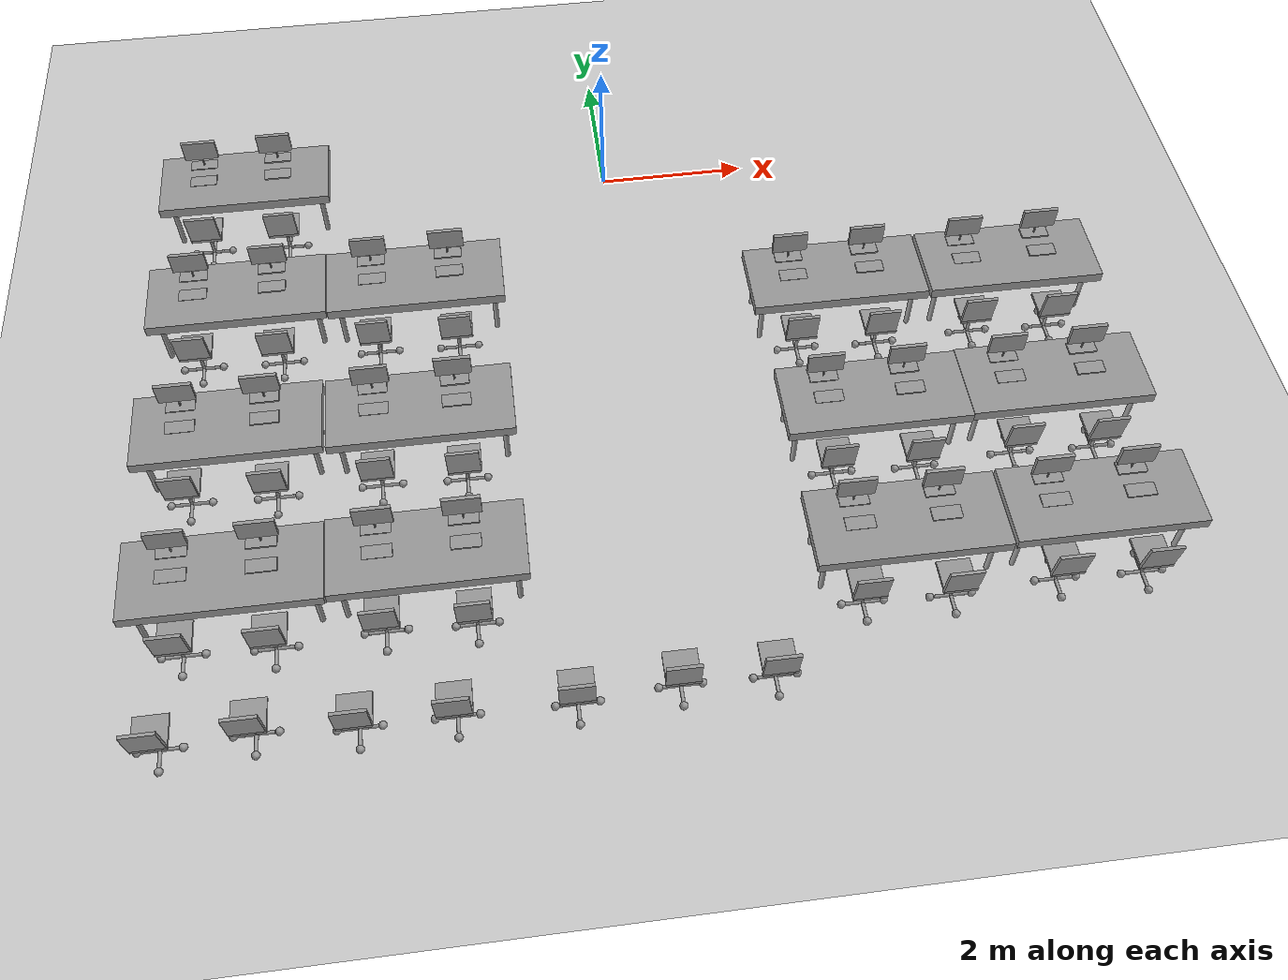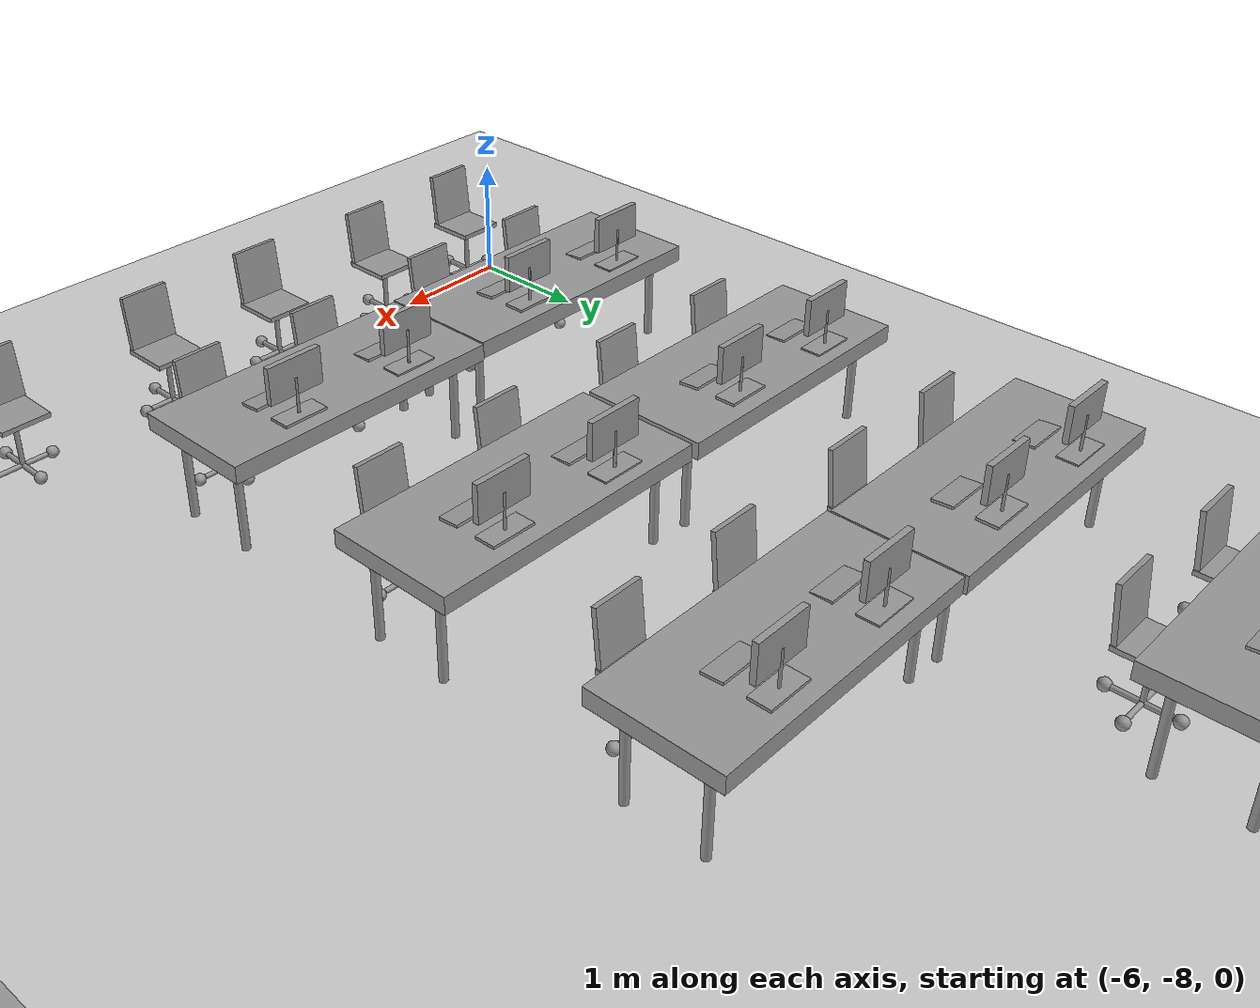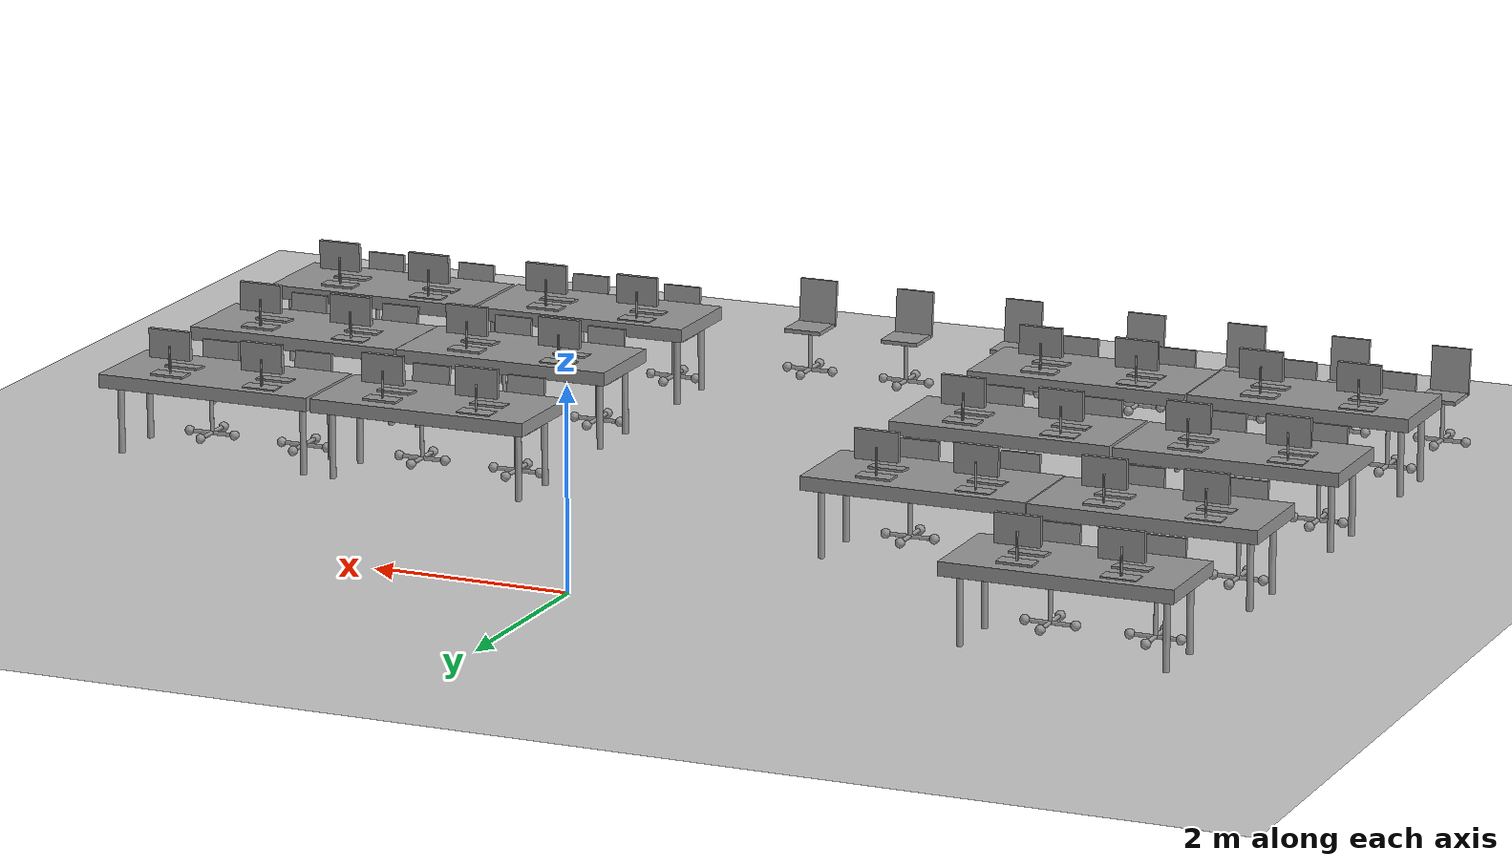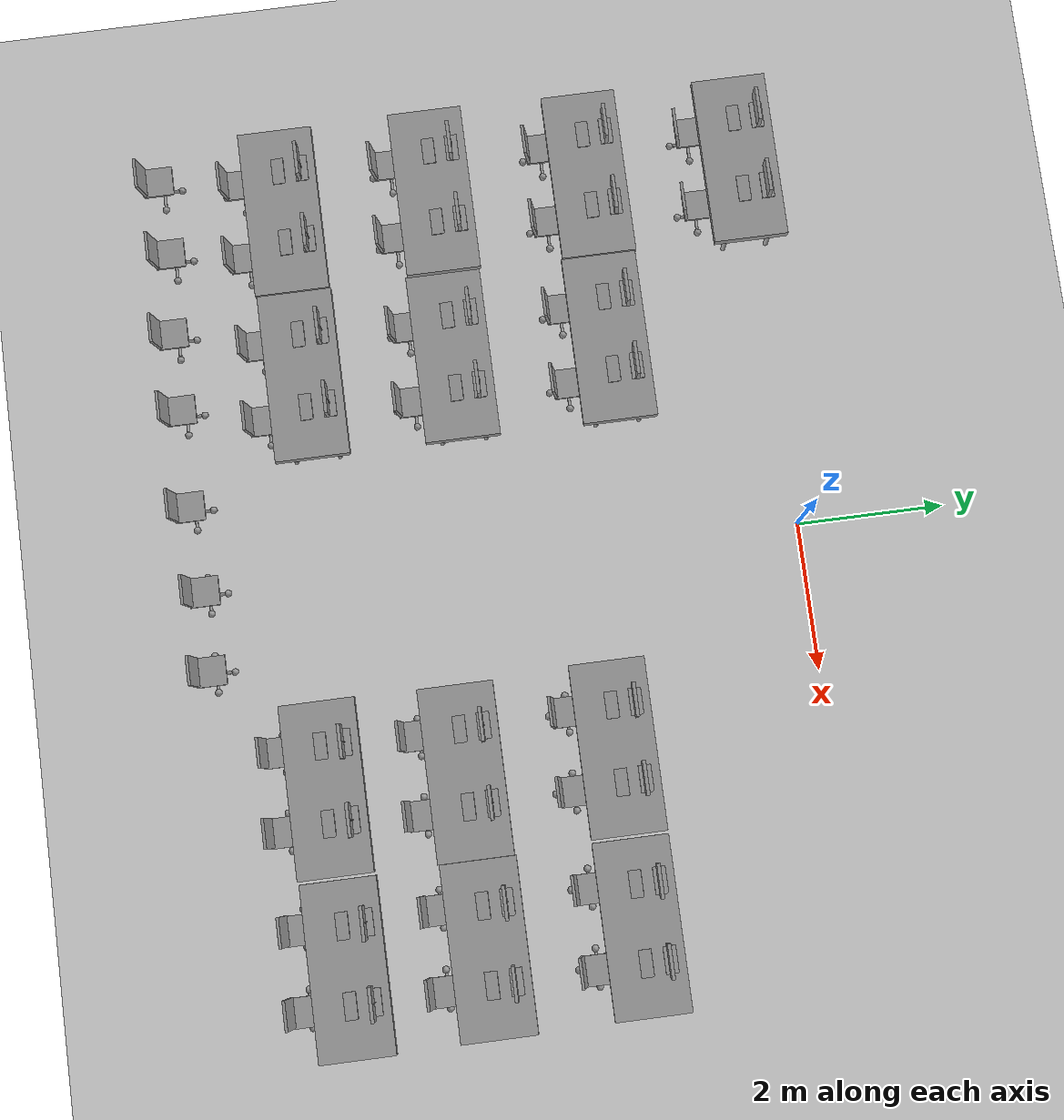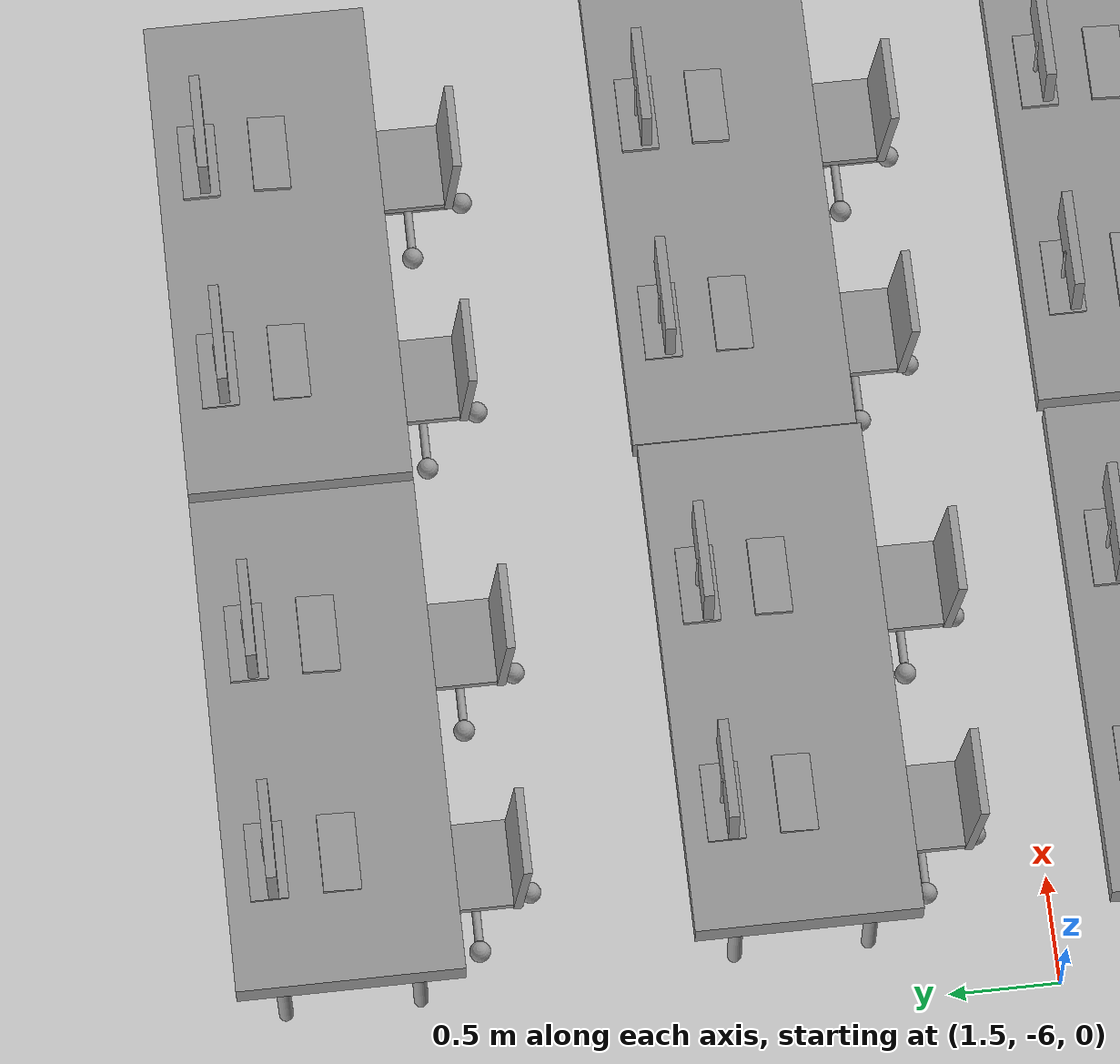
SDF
<sdf version="1.6">
 <world name="default">
  <light name="sun" type="directional">
   <pose>0 0 10 0 -0 0</pose>
   <diffuse>0.8 0.8 0.8 1</diffuse>
   <specular>0.2 0.2 0.2 1</specular>
   <attenuation>
    <range>1000</range>
    <constant>0.9</constant>
    <linear>0.01</linear>
    <quadratic>0.001</quadratic>
   </attenuation>
   <direction>-0.5 0.1 -0.9</direction>
  </light>
  <gravity>0 0 -9.8</gravity>
  <magnetic_field>6e-06 2.3e-05 -4.2e-05</magnetic_field>
  <atmosphere type="adiabatic"/>
  <physics name="default_physics" default="0" type="ode">
   <max_step_size>0.001</max_step_size>
   <real_time_factor>1</real_time_factor>
   <real_time_update_rate>1000</real_time_update_rate>
  </physics>
  <scene><ambient>0.4 0.4 0.4 1</ambient><background>0.7 0.7 0.7 1</background><shadows>1</shadows></scene>
  <spherical_coordinates>
   <surface_model>EARTH_WGS84</surface_model>
   <latitude_deg>0</latitude_deg>
   <longitude_deg>0</longitude_deg>
   <elevation>0</elevation>
   <heading_deg>0</heading_deg>
  </spherical_coordinates>
  <model name="ground_plane">
   <static>1</static>
   <link name="link">
    <collision name="collision">
     <geometry><plane><normal>0 0 1</normal><size>100 100</size></plane></geometry>
     <surface><friction><ode><mu>100</mu><mu2>50</mu2></ode></friction></surface>
    </collision>
    <visual name="visual">
     <cast_shadows>0</cast_shadows>
     <geometry><plane><normal>0 0 1</normal><size>100 100</size></plane></geometry>
     <material>
      <script><uri>file://media/materials/scripts/gazebo.material</uri><name>Gazebo/Grey</name></script>
     </material>
    </visual>
   </link>
  </model>
  <model name="bancata_8">
   <model name="Sedia">
    <link name="link">
     <inertial>
      <mass>1</mass>
      <inertia><ixx>0.1</ixx><ixy>0</ixy><ixz>0</ixz><iyy>0.1</iyy><iyz>0</iyz><izz>0.1</izz></inertia>
      <pose>0 -0.05 0 0 -0 0</pose>
     </inertial>
     <pose>0 -0.05 0.04 0 -0 0</pose>
     <visual name="visual">
      <geometry><sphere><radius>0.0479725</radius></sphere></geometry>
      <material>
       <script><name>Gazebo/Grey</name><uri>file://media/materials/scripts/gazebo.material</uri></script>
       <shader type="vertex"><normal_map>__default__</normal_map></shader>
       <ambient>0.3 0.3 0.3 1</ambient>
       <diffuse>0.7 0.7 0.7 1</diffuse>
       <specular>0.01 0.01 0.01 1</specular>
       <emissive>0 0 0 1</emissive>
      </material>
     </visual>
     <collision name="collision">
      <geometry><sphere><radius>0.047973</radius></sphere></geometry>
      <surface>
       <friction>
        <ode><mu>1</mu><mu2>1</mu2><fdir1>0 0 0</fdir1><slip1>0</slip1><slip2>0</slip2></ode>
        <torsional>
         <coefficient>1</coefficient>
         <patch_radius>0</patch_radius>
         <surface_radius>0</surface_radius>
         <use_patch_radius>1</use_patch_radius>
         <ode><slip>0</slip></ode>
        </torsional>
       </friction>
       <bounce><restitution_coefficient>0</restitution_coefficient><threshold>1e+06</threshold></bounce>
       <contact>
        <collide_without_contact>0</collide_without_contact>
        <collide_without_contact_bitmask>1</collide_without_contact_bitmask>
        <collide_bitmask>1</collide_bitmask>
        <ode>
         <soft_cfm>0</soft_cfm>
         <soft_erp>0.2</soft_erp>
         <kp>1e+13</kp>
         <kd>1</kd>
         <max_vel>0.01</max_vel>
         <min_depth>0</min_depth>
        </ode>
        <bullet>
         <split_impulse>1</split_impulse>
         <split_impulse_penetration_threshold>-0.01</split_impulse_penetration_threshold>
         <soft_cfm>0</soft_cfm>
         <soft_erp>0.2</soft_erp>
         <kp>1e+13</kp>
         <kd>1</kd>
        </bullet>
       </contact>
      </surface>
     </collision>
    </link>
    <link name="link_0">
     <inertial>
      <mass>0.000595181</mass>
      <inertia>
       <ixx>8.34662e-06</ixx>
       <ixy>0</ixy>
       <ixz>0</ixz>
       <iyy>8.34662e-06</iyy>
       <iyz>0</iyz>
       <izz>1.11586e-07</izz>
      </inertia>
     </inertial>
     <pose>-0 0.2 0.2494 0 -0 0</pose>
     <visual name="visual">
      <geometry><cylinder><radius>0.0193636</radius><length>0.408851</length></cylinder></geometry>
      <material>
       <lighting>1</lighting>
       <script><uri>file://media/materials/scripts/gazebo.material</uri><name>Gazebo/Grey</name></script>
       <shader type="vertex"><normal_map>__default__</normal_map></shader>
       <ambient>0.3 0.3 0.3 1</ambient>
       <diffuse>0.7 0.7 0.7 1</diffuse>
       <specular>0.01 0.01 0.01 1</specular>
       <emissive>0 0 0 1</emissive>
      </material>
     </visual>
     <collision name="collision">
      <geometry><cylinder><radius>0.019364</radius><length>0.408851</length></cylinder></geometry>
      <surface>
       <friction>
        <ode><mu>1</mu><mu2>1</mu2><fdir1>0 0 0</fdir1><slip1>0</slip1><slip2>0</slip2></ode>
        <torsional>
         <coefficient>1</coefficient>
         <patch_radius>0</patch_radius>
         <surface_radius>0</surface_radius>
         <use_patch_radius>1</use_patch_radius>
         <ode><slip>0</slip></ode>
        </torsional>
       </friction>
       <bounce><restitution_coefficient>0</restitution_coefficient><threshold>1e+06</threshold></bounce>
       <contact>
        <collide_without_contact>0</collide_without_contact>
        <collide_without_contact_bitmask>1</collide_without_contact_bitmask>
        <collide_bitmask>1</collide_bitmask>
        <ode>
         <soft_cfm>0</soft_cfm>
         <soft_erp>0.2</soft_erp>
         <kp>1e+13</kp>
         <kd>1</kd>
         <max_vel>0.01</max_vel>
         <min_depth>0</min_depth>
        </ode>
        <bullet>
         <split_impulse>1</split_impulse>
         <split_impulse_penetration_threshold>-0.01</split_impulse_penetration_threshold>
         <soft_cfm>0</soft_cfm>
         <soft_erp>0.2</soft_erp>
         <kp>1e+13</kp>
         <kd>1</kd>
        </bullet>
       </contact>
      </surface>
     </collision>
    </link>
    <link name="link_0_clone">
     <inertial>
      <mass>0.000698061</mass>
      <inertia>
       <ixx>1.02332e-05</ixx>
       <ixy>0</ixy>
       <ixz>0</ixz>
       <iyy>1.02332e-05</iyy>
       <iyz>0</iyz>
       <izz>1.50251e-07</izz>
      </inertia>
     </inertial>
     <pose>0 0.2 0.04 -1.571 -0 0</pose>
     <visual name="visual">
      <geometry><cylinder><radius>0.0207471</radius><length>0.417878</length></cylinder></geometry>
      <material>
       <lighting>1</lighting>
       <script><uri>file://media/materials/scripts/gazebo.material</uri><name>Gazebo/Grey</name></script>
       <shader type="vertex"><normal_map>__default__</normal_map></shader>
       <ambient>0.3 0.3 0.3 1</ambient>
       <diffuse>0.7 0.7 0.7 1</diffuse>
       <specular>0.01 0.01 0.01 1</specular>
       <emissive>0 0 0 1</emissive>
      </material>
     </visual>
     <collision name="collision">
      <geometry><cylinder><radius>0.020748</radius><length>0.417878</length></cylinder></geometry>
      <surface>
       <friction>
        <ode><mu>1</mu><mu2>1</mu2><fdir1>0 0 0</fdir1><slip1>0</slip1><slip2>0</slip2></ode>
        <torsional>
         <coefficient>1</coefficient>
         <patch_radius>0</patch_radius>
         <surface_radius>0</surface_radius>
         <use_patch_radius>1</use_patch_radius>
         <ode><slip>0</slip></ode>
        </torsional>
       </friction>
       <bounce><restitution_coefficient>0</restitution_coefficient><threshold>1e+06</threshold></bounce>
       <contact>
        <collide_without_contact>0</collide_without_contact>
        <collide_without_contact_bitmask>1</collide_without_contact_bitmask>
        <collide_bitmask>1</collide_bitmask>
        <ode>
         <soft_cfm>0</soft_cfm>
         <soft_erp>0.2</soft_erp>
         <kp>1e+13</kp>
         <kd>1</kd>
         <max_vel>0.01</max_vel>
         <min_depth>0</min_depth>
        </ode>
        <bullet>
         <split_impulse>1</split_impulse>
         <split_impulse_penetration_threshold>-0.01</split_impulse_penetration_threshold>
         <soft_cfm>0</soft_cfm>
         <soft_erp>0.2</soft_erp>
         <kp>1e+13</kp>
         <kd>1</kd>
        </bullet>
       </contact>
      </surface>
     </collision>
    </link>
    <link name="link_0_clone_0">
     <inertial>
      <mass>0.00059327</mass>
      <inertia>
       <ixx>8.26633e-06</ixx>
       <ixy>0</ixy>
       <ixz>0</ixz>
       <iyy>8.26633e-06</iyy>
       <iyz>0</iyz>
       <izz>1.11228e-07</izz>
      </inertia>
     </inertial>
     <pose>0 0.2 0.04 0 -1.57059 0</pose>
     <visual name="visual">
      <geometry><cylinder><radius>0.0193636</radius><length>0.407525</length></cylinder></geometry>
      <material>
       <lighting>1</lighting>
       <script><uri>file://media/materials/scripts/gazebo.material</uri><name>Gazebo/Grey</name></script>
       <shader type="vertex"><normal_map>__default__</normal_map></shader>
       <ambient>0.3 0.3 0.3 1</ambient>
       <diffuse>0.7 0.7 0.7 1</diffuse>
       <specular>0.01 0.01 0.01 1</specular>
       <emissive>0 0 0 1</emissive>
      </material>
     </visual>
     <collision name="collision">
      <geometry><cylinder><radius>0.019364</radius><length>0.407525</length></cylinder></geometry>
      <surface>
       <friction>
        <ode><mu>1</mu><mu2>1</mu2><fdir1>0 0 0</fdir1><slip1>0</slip1><slip2>0</slip2></ode>
        <torsional>
         <coefficient>1</coefficient>
         <patch_radius>0</patch_radius>
         <surface_radius>0</surface_radius>
         <use_patch_radius>1</use_patch_radius>
         <ode><slip>0</slip></ode>
        </torsional>
       </friction>
       <bounce><restitution_coefficient>0</restitution_coefficient><threshold>1e+06</threshold></bounce>
       <contact>
        <collide_without_contact>0</collide_without_contact>
        <collide_without_contact_bitmask>1</collide_without_contact_bitmask>
        <collide_bitmask>1</collide_bitmask>
        <ode>
         <soft_cfm>0</soft_cfm>
         <soft_erp>0.2</soft_erp>
         <kp>1e+13</kp>
         <kd>1</kd>
         <max_vel>0.01</max_vel>
         <min_depth>0</min_depth>
        </ode>
        <bullet>
         <split_impulse>1</split_impulse>
         <split_impulse_penetration_threshold>-0.01</split_impulse_penetration_threshold>
         <soft_cfm>0</soft_cfm>
         <soft_erp>0.2</soft_erp>
         <kp>1e+13</kp>
         <kd>1</kd>
        </bullet>
       </contact>
      </surface>
     </collision>
    </link>
    <link name="link_1">
     <inertial>
      <mass>0.00616304</mass>
      <inertia>
       <ixx>8.379e-05</ixx>
       <ixy>0</ixy>
       <ixz>0</ixz>
       <iyy>8.148e-05</iyy>
       <iyz>0</iyz>
       <izz>0.00016374</izz>
      </inertia>
     </inertial>
     <pose>-0 0.2 0.48 0 -0 0</pose>
     <visual name="visual">
      <geometry><box><size>0.396445 0.402068 0.038566</size></box></geometry>
      <material>
       <lighting>1</lighting>
       <script><uri>file://media/materials/scripts/gazebo.material</uri><name>Gazebo/Grey</name></script>
       <shader type="vertex"><normal_map>__default__</normal_map></shader>
       <ambient>0.3 0.3 0.3 1</ambient>
       <diffuse>0.7 0.7 0.7 1</diffuse>
       <specular>0.01 0.01 0.01 1</specular>
       <emissive>0 0 0 1</emissive>
      </material>
     </visual>
     <collision name="collision">
      <geometry><box><size>0.396445 0.402068 0.038566</size></box></geometry>
      <surface>
       <friction>
        <ode><mu>1</mu><mu2>1</mu2><fdir1>0 0 0</fdir1><slip1>0</slip1><slip2>0</slip2></ode>
        <torsional>
         <coefficient>1</coefficient>
         <patch_radius>0</patch_radius>
         <surface_radius>0</surface_radius>
         <use_patch_radius>1</use_patch_radius>
         <ode><slip>0</slip></ode>
        </torsional>
       </friction>
       <bounce><restitution_coefficient>0</restitution_coefficient><threshold>1e+06</threshold></bounce>
       <contact>
        <collide_without_contact>0</collide_without_contact>
        <collide_without_contact_bitmask>1</collide_without_contact_bitmask>
        <collide_bitmask>1</collide_bitmask>
        <ode>
         <soft_cfm>0</soft_cfm>
         <soft_erp>0.2</soft_erp>
         <kp>1e+13</kp>
         <kd>1</kd>
         <max_vel>0.01</max_vel>
         <min_depth>0</min_depth>
        </ode>
        <bullet>
         <split_impulse>1</split_impulse>
         <split_impulse_penetration_threshold>-0.01</split_impulse_penetration_threshold>
         <soft_cfm>0</soft_cfm>
         <soft_erp>0.2</soft_erp>
         <kp>1e+13</kp>
         <kd>1</kd>
        </bullet>
       </contact>
      </surface>
     </collision>
    </link>
    <link name="link_1_clone">
     <inertial>
      <mass>0.0072018</mass>
      <inertia>
       <ixx>0.000133376</ixx>
       <ixy>0</ixy>
       <ixz>0</ixz>
       <iyy>9.52174e-05</iyy>
       <iyz>0</iyz>
       <izz>0.000226808</izz>
      </inertia>
     </inertial>
     <pose>-0.008803 -0.002064 0.701044 1.67698 -0 0</pose>
     <visual name="visual">
      <geometry><box><size>0.396445 0.46984 0.038566</size></box></geometry>
      <material>
       <lighting>1</lighting>
       <script><uri>file://media/materials/scripts/gazebo.material</uri><name>Gazebo/Grey</name></script>
       <shader type="vertex"><normal_map>__default__</normal_map></shader>
       <ambient>0.3 0.3 0.3 1</ambient>
       <diffuse>0.7 0.7 0.7 1</diffuse>
       <specular>0.01 0.01 0.01 1</specular>
       <emissive>0 0 0 1</emissive>
      </material>
     </visual>
     <collision name="collision">
      <geometry><box><size>0.396445 0.46984 0.038566</size></box></geometry>
      <surface>
       <friction>
        <ode><mu>1</mu><mu2>1</mu2><fdir1>0 0 0</fdir1><slip1>0</slip1><slip2>0</slip2></ode>
        <torsional>
         <coefficient>1</coefficient>
         <patch_radius>0</patch_radius>
         <surface_radius>0</surface_radius>
         <use_patch_radius>1</use_patch_radius>
         <ode><slip>0</slip></ode>
        </torsional>
       </friction>
       <bounce><restitution_coefficient>0</restitution_coefficient><threshold>1e+06</threshold></bounce>
       <contact>
        <collide_without_contact>0</collide_without_contact>
        <collide_without_contact_bitmask>1</collide_without_contact_bitmask>
        <collide_bitmask>1</collide_bitmask>
        <ode>
         <soft_cfm>0</soft_cfm>
         <soft_erp>0.2</soft_erp>
         <kp>1e+13</kp>
         <kd>1</kd>
         <max_vel>0.01</max_vel>
         <min_depth>0</min_depth>
        </ode>
        <bullet>
         <split_impulse>1</split_impulse>
         <split_impulse_penetration_threshold>-0.01</split_impulse_penetration_threshold>
         <soft_cfm>0</soft_cfm>
         <soft_erp>0.2</soft_erp>
         <kp>1e+13</kp>
         <kd>1</kd>
        </bullet>
       </contact>
      </surface>
     </collision>
    </link>
    <link name="link_clone">
     <inertial>
      <mass>1</mass>
      <inertia><ixx>0.1</ixx><ixy>0</ixy><ixz>0</ixz><iyy>0.1</iyy><iyz>0</iyz><izz>0.1</izz></inertia>
      <pose>0 0 0.04 0 -0 0</pose>
     </inertial>
     <pose>0.25 0.2 0.04 0 -0 0</pose>
     <visual name="visual">
      <geometry><sphere><radius>0.0479725</radius></sphere></geometry>
      <material>
       <script><name>Gazebo/Grey</name><uri>file://media/materials/scripts/gazebo.material</uri></script>
       <shader type="vertex"><normal_map>__default__</normal_map></shader>
       <ambient>0.3 0.3 0.3 1</ambient>
       <diffuse>0.7 0.7 0.7 1</diffuse>
       <specular>0.01 0.01 0.01 1</specular>
       <emissive>0 0 0 1</emissive>
      </material>
     </visual>
     <collision name="collision">
      <geometry><sphere><radius>0.047973</radius></sphere></geometry>
      <surface>
       <friction>
        <ode><mu>1</mu><mu2>1</mu2><fdir1>0 0 0</fdir1><slip1>0</slip1><slip2>0</slip2></ode>
        <torsional>
         <coefficient>1</coefficient>
         <patch_radius>0</patch_radius>
         <surface_radius>0</surface_radius>
         <use_patch_radius>1</use_patch_radius>
         <ode><slip>0</slip></ode>
        </torsional>
       </friction>
       <bounce><restitution_coefficient>0</restitution_coefficient><threshold>1e+06</threshold></bounce>
       <contact>
        <collide_without_contact>0</collide_without_contact>
        <collide_without_contact_bitmask>1</collide_without_contact_bitmask>
        <collide_bitmask>1</collide_bitmask>
        <ode>
         <soft_cfm>0</soft_cfm>
         <soft_erp>0.2</soft_erp>
         <kp>1e+13</kp>
         <kd>1</kd>
         <max_vel>0.01</max_vel>
         <min_depth>0</min_depth>
        </ode>
        <bullet>
         <split_impulse>1</split_impulse>
         <split_impulse_penetration_threshold>-0.01</split_impulse_penetration_threshold>
         <soft_cfm>0</soft_cfm>
         <soft_erp>0.2</soft_erp>
         <kp>1e+13</kp>
         <kd>1</kd>
        </bullet>
       </contact>
      </surface>
     </collision>
    </link>
    <link name="link_clone_0">
     <inertial>
      <mass>1</mass>
      <inertia><ixx>0.1</ixx><ixy>0</ixy><ixz>0</ixz><iyy>0.1</iyy><iyz>0</iyz><izz>0.1</izz></inertia>
     </inertial>
     <pose>-0 0.45 0.04 0 -0 0</pose>
     <visual name="visual">
      <geometry><sphere><radius>0.0479725</radius></sphere></geometry>
      <material>
       <script><name>Gazebo/Grey</name><uri>file://media/materials/scripts/gazebo.material</uri></script>
       <shader type="vertex"><normal_map>__default__</normal_map></shader>
       <ambient>0.3 0.3 0.3 1</ambient>
       <diffuse>0.7 0.7 0.7 1</diffuse>
       <specular>0.01 0.01 0.01 1</specular>
       <emissive>0 0 0 1</emissive>
      </material>
     </visual>
     <collision name="collision">
      <geometry><sphere><radius>0.047973</radius></sphere></geometry>
      <surface>
       <friction>
        <ode><mu>1</mu><mu2>1</mu2><fdir1>0 0 0</fdir1><slip1>0</slip1><slip2>0</slip2></ode>
        <torsional>
         <coefficient>1</coefficient>
         <patch_radius>0</patch_radius>
         <surface_radius>0</surface_radius>
         <use_patch_radius>1</use_patch_radius>
         <ode><slip>0</slip></ode>
        </torsional>
       </friction>
       <bounce><restitution_coefficient>0</restitution_coefficient><threshold>1e+06</threshold></bounce>
       <contact>
        <collide_without_contact>0</collide_without_contact>
        <collide_without_contact_bitmask>1</collide_without_contact_bitmask>
        <collide_bitmask>1</collide_bitmask>
        <ode>
         <soft_cfm>0</soft_cfm>
         <soft_erp>0.2</soft_erp>
         <kp>1e+13</kp>
         <kd>1</kd>
         <max_vel>0.01</max_vel>
         <min_depth>0</min_depth>
        </ode>
        <bullet>
         <split_impulse>1</split_impulse>
         <split_impulse_penetration_threshold>-0.01</split_impulse_penetration_threshold>
         <soft_cfm>0</soft_cfm>
         <soft_erp>0.2</soft_erp>
         <kp>1e+13</kp>
         <kd>1</kd>
        </bullet>
       </contact>
      </surface>
     </collision>
    </link>
    <link name="link_clone_1">
     <inertial>
      <mass>1</mass>
      <inertia><ixx>0.1</ixx><ixy>0</ixy><ixz>0</ixz><iyy>0.1</iyy><iyz>0</iyz><izz>0.1</izz></inertia>
     </inertial>
     <pose>-0.25 0.2 0.04 0 -0 0</pose>
     <visual name="visual">
      <geometry><sphere><radius>0.0479725</radius></sphere></geometry>
      <material>
       <script><name>Gazebo/Grey</name><uri>file://media/materials/scripts/gazebo.material</uri></script>
       <shader type="vertex"><normal_map>__default__</normal_map></shader>
       <ambient>0.3 0.3 0.3 1</ambient>
       <diffuse>0.7 0.7 0.7 1</diffuse>
       <specular>0.01 0.01 0.01 1</specular>
       <emissive>0 0 0 1</emissive>
      </material>
     </visual>
     <collision name="collision">
      <geometry><sphere><radius>0.047973</radius></sphere></geometry>
      <surface>
       <friction>
        <ode><mu>1</mu><mu2>1</mu2><fdir1>0 0 0</fdir1><slip1>0</slip1><slip2>0</slip2></ode>
        <torsional>
         <coefficient>1</coefficient>
         <patch_radius>0</patch_radius>
         <surface_radius>0</surface_radius>
         <use_patch_radius>1</use_patch_radius>
         <ode><slip>0</slip></ode>
        </torsional>
       </friction>
       <bounce><restitution_coefficient>0</restitution_coefficient><threshold>1e+06</threshold></bounce>
       <contact>
        <collide_without_contact>0</collide_without_contact>
        <collide_without_contact_bitmask>1</collide_without_contact_bitmask>
        <collide_bitmask>1</collide_bitmask>
        <ode>
         <soft_cfm>0</soft_cfm>
         <soft_erp>0.2</soft_erp>
         <kp>1e+13</kp>
         <kd>1</kd>
         <max_vel>0.01</max_vel>
         <min_depth>0</min_depth>
        </ode>
        <bullet>
         <split_impulse>1</split_impulse>
         <split_impulse_penetration_threshold>-0.01</split_impulse_penetration_threshold>
         <soft_cfm>0</soft_cfm>
         <soft_erp>0.2</soft_erp>
         <kp>1e+13</kp>
         <kd>1</kd>
        </bullet>
       </contact>
      </surface>
     </collision>
    </link>
    <joint name="link_0_clone_0_JOINT_1" type="fixed">
     <parent>link_0_clone_0</parent>
     <child>link_clone</child>
     <physics>
      <ode><limit><cfm>0</cfm><erp>0.2</erp></limit><suspension><cfm>0</cfm><erp>0.2</erp></suspension></ode>
     </physics>
    </joint>
    <joint name="link_0_clone_0_JOINT_2" type="fixed">
     <parent>link_0_clone_0</parent>
     <child>link_clone_1</child>
     <physics>
      <ode><limit><cfm>0</cfm><erp>0.2</erp></limit><suspension><cfm>0</cfm><erp>0.2</erp></suspension></ode>
     </physics>
    </joint>
    <joint name="link_0_clone_JOINT_3" type="fixed">
     <parent>link_0_clone</parent>
     <child>link_clone_0</child>
     <physics>
      <ode><limit><cfm>0</cfm><erp>0.2</erp></limit><suspension><cfm>0</cfm><erp>0.2</erp></suspension></ode>
     </physics>
    </joint>
    <joint name="link_0_clone_JOINT_4" type="fixed">
     <parent>link_0_clone</parent>
     <child>link</child>
     <physics>
      <ode><limit><cfm>0</cfm><erp>0.2</erp></limit><suspension><cfm>0</cfm><erp>0.2</erp></suspension></ode>
     </physics>
    </joint>
    <joint name="link_1_JOINT_0" type="fixed">
     <parent>link_1</parent>
     <child>link_1_clone</child>
     <physics>
      <ode><limit><cfm>0</cfm><erp>0.2</erp></limit><suspension><cfm>0</cfm><erp>0.2</erp></suspension></ode>
     </physics>
    </joint>
    <joint name="link_1_JOINT_4" type="fixed">
     <parent>link_1</parent>
     <child>link_0</child>
     <physics>
      <ode><limit><cfm>0</cfm><erp>0.2</erp></limit><suspension><cfm>0</cfm><erp>0.2</erp></suspension></ode>
     </physics>
    </joint>
    <joint name="link_JOINT_3" type="fixed">
     <parent>link</parent>
     <child>link_0</child>
     <physics>
      <ode><limit><cfm>0</cfm><erp>0.2</erp></limit><suspension><cfm>0</cfm><erp>0.2</erp></suspension></ode>
     </physics>
    </joint>
    <joint name="link_clone_0_JOINT_0" type="fixed">
     <parent>link_clone_0</parent>
     <child>link_0_LINK_FRAME_VISUAL___Y_AXIS</child>
     <physics>
      <ode><limit><cfm>0</cfm><erp>0.2</erp></limit><suspension><cfm>0</cfm><erp>0.2</erp></suspension></ode>
     </physics>
    </joint>
    <joint name="link_clone_1_JOINT_2" type="fixed">
     <parent>link_clone_1</parent>
     <child>link_0</child>
     <physics>
      <ode><limit><cfm>0</cfm><erp>0.2</erp></limit><suspension><cfm>0</cfm><erp>0.2</erp></suspension></ode>
     </physics>
    </joint>
    <joint name="link_clone_JOINT_1" type="fixed">
     <parent>link_clone</parent>
     <child>link_0</child>
     <physics>
      <ode><limit><cfm>0</cfm><erp>0.2</erp></limit><suspension><cfm>0</cfm><erp>0.2</erp></suspension></ode>
     </physics>
    </joint>
    <static>0</static>
    <pose>1.16662 0.572146 -0.001178 0 -0 0</pose>
   </model>
   <model name="Sedia_clone">
    <link name="link">
     <inertial>
      <mass>1</mass>
      <inertia><ixx>0.1</ixx><ixy>0</ixy><ixz>0</ixz><iyy>0.1</iyy><iyz>0</iyz><izz>0.1</izz></inertia>
      <pose>0 -0.05 0 0 -0 0</pose>
     </inertial>
     <pose>0 -0.05 0.04 0 -0 0</pose>
     <visual name="visual">
      <geometry><sphere><radius>0.0479725</radius></sphere></geometry>
      <material>
       <script><name>Gazebo/Grey</name><uri>file://media/materials/scripts/gazebo.material</uri></script>
       <shader type="vertex"><normal_map>__default__</normal_map></shader>
       <ambient>0.3 0.3 0.3 1</ambient>
       <diffuse>0.7 0.7 0.7 1</diffuse>
       <specular>0.01 0.01 0.01 1</specular>
       <emissive>0 0 0 1</emissive>
      </material>
     </visual>
     <collision name="collision">
      <geometry><sphere><radius>0.047973</radius></sphere></geometry>
      <surface>
       <friction>
        <ode><mu>1</mu><mu2>1</mu2><fdir1>0 0 0</fdir1><slip1>0</slip1><slip2>0</slip2></ode>
        <torsional>
         <coefficient>1</coefficient>
         <patch_radius>0</patch_radius>
         <surface_radius>0</surface_radius>
         <use_patch_radius>1</use_patch_radius>
         <ode><slip>0</slip></ode>
        </torsional>
       </friction>
       <bounce><restitution_coefficient>0</restitution_coefficient><threshold>1e+06</threshold></bounce>
       <contact>
        <collide_without_contact>0</collide_without_contact>
        <collide_without_contact_bitmask>1</collide_without_contact_bitmask>
        <collide_bitmask>1</collide_bitmask>
        <ode>
         <soft_cfm>0</soft_cfm>
         <soft_erp>0.2</soft_erp>
         <kp>1e+13</kp>
         <kd>1</kd>
         <max_vel>0.01</max_vel>
         <min_depth>0</min_depth>
        </ode>
        <bullet>
         <split_impulse>1</split_impulse>
         <split_impulse_penetration_threshold>-0.01</split_impulse_penetration_threshold>
         <soft_cfm>0</soft_cfm>
         <soft_erp>0.2</soft_erp>
         <kp>1e+13</kp>
         <kd>1</kd>
        </bullet>
       </contact>
      </surface>
     </collision>
    </link>
    <link name="link_0">
     <inertial>
      <mass>0.000595181</mass>
      <inertia>
       <ixx>8.34662e-06</ixx>
       <ixy>0</ixy>
       <ixz>0</ixz>
       <iyy>8.34662e-06</iyy>
       <iyz>0</iyz>
       <izz>1.11586e-07</izz>
      </inertia>
     </inertial>
     <pose>-0 0.2 0.2494 0 -0 0</pose>
     <visual name="visual">
      <geometry><cylinder><radius>0.0193636</radius><length>0.408851</length></cylinder></geometry>
      <material>
       <lighting>1</lighting>
       <script><uri>file://media/materials/scripts/gazebo.material</uri><name>Gazebo/Grey</name></script>
       <shader type="vertex"><normal_map>__default__</normal_map></shader>
       <ambient>0.3 0.3 0.3 1</ambient>
       <diffuse>0.7 0.7 0.7 1</diffuse>
       <specular>0.01 0.01 0.01 1</specular>
       <emissive>0 0 0 1</emissive>
      </material>
     </visual>
     <collision name="collision">
      <geometry><cylinder><radius>0.019364</radius><length>0.408851</length></cylinder></geometry>
      <surface>
       <friction>
        <ode><mu>1</mu><mu2>1</mu2><fdir1>0 0 0</fdir1><slip1>0</slip1><slip2>0</slip2></ode>
        <torsional>
         <coefficient>1</coefficient>
         <patch_radius>0</patch_radius>
         <surface_radius>0</surface_radius>
         <use_patch_radius>1</use_patch_radius>
         <ode><slip>0</slip></ode>
        </torsional>
       </friction>
       <bounce><restitution_coefficient>0</restitution_coefficient><threshold>1e+06</threshold></bounce>
       <contact>
        <collide_without_contact>0</collide_without_contact>
        <collide_without_contact_bitmask>1</collide_without_contact_bitmask>
        <collide_bitmask>1</collide_bitmask>
        <ode>
         <soft_cfm>0</soft_cfm>
         <soft_erp>0.2</soft_erp>
         <kp>1e+13</kp>
         <kd>1</kd>
         <max_vel>0.01</max_vel>
         <min_depth>0</min_depth>
        </ode>
        <bullet>
         <split_impulse>1</split_impulse>
         <split_impulse_penetration_threshold>-0.01</split_impulse_penetration_threshold>
         <soft_cfm>0</soft_cfm>
         <soft_erp>0.2</soft_erp>
         <kp>1e+13</kp>
         <kd>1</kd>
        </bullet>
       </contact>
      </surface>
     </collision>
    </link>
    <link name="link_0_clone">
     <inertial>
      <mass>0.000698061</mass>
      <inertia>
       <ixx>1.02332e-05</ixx>
       <ixy>0</ixy>
       <ixz>0</ixz>
       <iyy>1.02332e-05</iyy>
       <iyz>0</iyz>
       <izz>1.50251e-07</izz>
      </inertia>
     </inertial>
     <pose>0 0.2 0.04 -1.571 -0 0</pose>
     <visual name="visual">
      <geometry><cylinder><radius>0.0207471</radius><length>0.417878</length></cylinder></geometry>
      <material>
       <lighting>1</lighting>
       <script><uri>file://media/materials/scripts/gazebo.material</uri><name>Gazebo/Grey</name></script>
       <shader type="vertex"><normal_map>__default__</normal_map></shader>
       <ambient>0.3 0.3 0.3 1</ambient>
       <diffuse>0.7 0.7 0.7 1</diffuse>
       <specular>0.01 0.01 0.01 1</specular>
       <emissive>0 0 0 1</emissive>
      </material>
     </visual>
     <collision name="collision">
      <geometry><cylinder><radius>0.020748</radius><length>0.417878</length></cylinder></geometry>
      <surface>
       <friction>
        <ode><mu>1</mu><mu2>1</mu2><fdir1>0 0 0</fdir1><slip1>0</slip1><slip2>0</slip2></ode>
        <torsional>
         <coefficient>1</coefficient>
         <patch_radius>0</patch_radius>
         <surface_radius>0</surface_radius>
         <use_patch_radius>1</use_patch_radius>
         <ode><slip>0</slip></ode>
        </torsional>
       </friction>
       <bounce><restitution_coefficient>0</restitution_coefficient><threshold>1e+06</threshold></bounce>
       <contact>
        <collide_without_contact>0</collide_without_contact>
        <collide_without_contact_bitmask>1</collide_without_contact_bitmask>
        <collide_bitmask>1</collide_bitmask>
        <ode>
         <soft_cfm>0</soft_cfm>
         <soft_erp>0.2</soft_erp>
         <kp>1e+13</kp>
         <kd>1</kd>
         <max_vel>0.01</max_vel>
         <min_depth>0</min_depth>
        </ode>
        <bullet>
         <split_impulse>1</split_impulse>
         <split_impulse_penetration_threshold>-0.01</split_impulse_penetration_threshold>
         <soft_cfm>0</soft_cfm>
         <soft_erp>0.2</soft_erp>
         <kp>1e+13</kp>
         <kd>1</kd>
        </bullet>
       </contact>
      </surface>
     </collision>
    </link>
    <link name="link_0_clone_0">
     <inertial>
      <mass>0.00059327</mass>
      <inertia>
       <ixx>8.26633e-06</ixx>
       <ixy>0</ixy>
       <ixz>0</ixz>
       <iyy>8.26633e-06</iyy>
       <iyz>0</iyz>
       <izz>1.11228e-07</izz>
      </inertia>
     </inertial>
     <pose>0 0.2 0.04 0 -1.57059 0</pose>
     <visual name="visual">
      <geometry><cylinder><radius>0.0193636</radius><length>0.407525</length></cylinder></geometry>
      <material>
       <lighting>1</lighting>
       <script><uri>file://media/materials/scripts/gazebo.material</uri><name>Gazebo/Grey</name></script>
       <shader type="vertex"><normal_map>__default__</normal_map></shader>
       <ambient>0.3 0.3 0.3 1</ambient>
       <diffuse>0.7 0.7 0.7 1</diffuse>
       <specular>0.01 0.01 0.01 1</specular>
       <emissive>0 0 0 1</emissive>
      </material>
     </visual>
     <collision name="collision">
      <geometry><cylinder><radius>0.019364</radius><length>0.407525</length></cylinder></geometry>
      <surface>
       <friction>
        <ode><mu>1</mu><mu2>1</mu2><fdir1>0 0 0</fdir1><slip1>0</slip1><slip2>0</slip2></ode>
        <torsional>
         <coefficient>1</coefficient>
         <patch_radius>0</patch_radius>
         <surface_radius>0</surface_radius>
         <use_patch_radius>1</use_patch_radius>
         <ode><slip>0</slip></ode>
        </torsional>
       </friction>
       <bounce><restitution_coefficient>0</restitution_coefficient><threshold>1e+06</threshold></bounce>
       <contact>
        <collide_without_contact>0</collide_without_contact>
        <collide_without_contact_bitmask>1</collide_without_contact_bitmask>
        <collide_bitmask>1</collide_bitmask>
        <ode>
         <soft_cfm>0</soft_cfm>
         <soft_erp>0.2</soft_erp>
         <kp>1e+13</kp>
         <kd>1</kd>
         <max_vel>0.01</max_vel>
         <min_depth>0</min_depth>
        </ode>
        <bullet>
         <split_impulse>1</split_impulse>
         <split_impulse_penetration_threshold>-0.01</split_impulse_penetration_threshold>
         <soft_cfm>0</soft_cfm>
         <soft_erp>0.2</soft_erp>
         <kp>1e+13</kp>
         <kd>1</kd>
        </bullet>
       </contact>
      </surface>
     </collision>
    </link>
    <link name="link_1">
     <inertial>
      <mass>0.00616304</mass>
      <inertia>
       <ixx>8.379e-05</ixx>
       <ixy>0</ixy>
       <ixz>0</ixz>
       <iyy>8.148e-05</iyy>
       <iyz>0</iyz>
       <izz>0.00016374</izz>
      </inertia>
     </inertial>
     <pose>-0 0.2 0.48 0 -0 0</pose>
     <visual name="visual">
      <geometry><box><size>0.396445 0.402068 0.038566</size></box></geometry>
      <material>
       <lighting>1</lighting>
       <script><uri>file://media/materials/scripts/gazebo.material</uri><name>Gazebo/Grey</name></script>
       <shader type="vertex"><normal_map>__default__</normal_map></shader>
       <ambient>0.3 0.3 0.3 1</ambient>
       <diffuse>0.7 0.7 0.7 1</diffuse>
       <specular>0.01 0.01 0.01 1</specular>
       <emissive>0 0 0 1</emissive>
      </material>
     </visual>
     <collision name="collision">
      <geometry><box><size>0.396445 0.402068 0.038566</size></box></geometry>
      <surface>
       <friction>
        <ode><mu>1</mu><mu2>1</mu2><fdir1>0 0 0</fdir1><slip1>0</slip1><slip2>0</slip2></ode>
        <torsional>
         <coefficient>1</coefficient>
         <patch_radius>0</patch_radius>
         <surface_radius>0</surface_radius>
         <use_patch_radius>1</use_patch_radius>
         <ode><slip>0</slip></ode>
        </torsional>
       </friction>
       <bounce><restitution_coefficient>0</restitution_coefficient><threshold>1e+06</threshold></bounce>
       <contact>
        <collide_without_contact>0</collide_without_contact>
        <collide_without_contact_bitmask>1</collide_without_contact_bitmask>
        <collide_bitmask>1</collide_bitmask>
        <ode>
         <soft_cfm>0</soft_cfm>
         <soft_erp>0.2</soft_erp>
         <kp>1e+13</kp>
         <kd>1</kd>
         <max_vel>0.01</max_vel>
         <min_depth>0</min_depth>
        </ode>
        <bullet>
         <split_impulse>1</split_impulse>
         <split_impulse_penetration_threshold>-0.01</split_impulse_penetration_threshold>
         <soft_cfm>0</soft_cfm>
         <soft_erp>0.2</soft_erp>
         <kp>1e+13</kp>
         <kd>1</kd>
        </bullet>
       </contact>
      </surface>
     </collision>
    </link>
    <link name="link_1_clone">
     <inertial>
      <mass>0.0072018</mass>
      <inertia>
       <ixx>0.000133376</ixx>
       <ixy>0</ixy>
       <ixz>0</ixz>
       <iyy>9.52174e-05</iyy>
       <iyz>0</iyz>
       <izz>0.000226808</izz>
      </inertia>
     </inertial>
     <pose>-0.008803 -0.002064 0.701044 1.67698 -0 0</pose>
     <visual name="visual">
      <geometry><box><size>0.396445 0.46984 0.038566</size></box></geometry>
      <material>
       <lighting>1</lighting>
       <script><uri>file://media/materials/scripts/gazebo.material</uri><name>Gazebo/Grey</name></script>
       <shader type="vertex"><normal_map>__default__</normal_map></shader>
       <ambient>0.3 0.3 0.3 1</ambient>
       <diffuse>0.7 0.7 0.7 1</diffuse>
       <specular>0.01 0.01 0.01 1</specular>
       <emissive>0 0 0 1</emissive>
      </material>
     </visual>
     <collision name="collision">
      <geometry><box><size>0.396445 0.46984 0.038566</size></box></geometry>
      <surface>
       <friction>
        <ode><mu>1</mu><mu2>1</mu2><fdir1>0 0 0</fdir1><slip1>0</slip1><slip2>0</slip2></ode>
        <torsional>
         <coefficient>1</coefficient>
         <patch_radius>0</patch_radius>
         <surface_radius>0</surface_radius>
         <use_patch_radius>1</use_patch_radius>
         <ode><slip>0</slip></ode>
        </torsional>
       </friction>
       <bounce><restitution_coefficient>0</restitution_coefficient><threshold>1e+06</threshold></bounce>
       <contact>
        <collide_without_contact>0</collide_without_contact>
        <collide_without_contact_bitmask>1</collide_without_contact_bitmask>
        <collide_bitmask>1</collide_bitmask>
        <ode>
         <soft_cfm>0</soft_cfm>
         <soft_erp>0.2</soft_erp>
         <kp>1e+13</kp>
         <kd>1</kd>
         <max_vel>0.01</max_vel>
         <min_depth>0</min_depth>
        </ode>
        <bullet>
         <split_impulse>1</split_impulse>
         <split_impulse_penetration_threshold>-0.01</split_impulse_penetration_threshold>
         <soft_cfm>0</soft_cfm>
         <soft_erp>0.2</soft_erp>
         <kp>1e+13</kp>
         <kd>1</kd>
        </bullet>
       </contact>
      </surface>
     </collision>
    </link>
    <link name="link_clone">
     <inertial>
      <mass>1</mass>
      <inertia><ixx>0.1</ixx><ixy>0</ixy><ixz>0</ixz><iyy>0.1</iyy><iyz>0</iyz><izz>0.1</izz></inertia>
      <pose>0 0 0.04 0 -0 0</pose>
     </inertial>
     <pose>0.25 0.2 0.04 0 -0 0</pose>
     <visual name="visual">
      <geometry><sphere><radius>0.0479725</radius></sphere></geometry>
      <material>
       <script><name>Gazebo/Grey</name><uri>file://media/materials/scripts/gazebo.material</uri></script>
       <shader type="vertex"><normal_map>__default__</normal_map></shader>
       <ambient>0.3 0.3 0.3 1</ambient>
       <diffuse>0.7 0.7 0.7 1</diffuse>
       <specular>0.01 0.01 0.01 1</specular>
       <emissive>0 0 0 1</emissive>
      </material>
     </visual>
     <collision name="collision">
      <geometry><sphere><radius>0.047973</radius></sphere></geometry>
      <surface>
       <friction>
        <ode><mu>1</mu><mu2>1</mu2><fdir1>0 0 0</fdir1><slip1>0</slip1><slip2>0</slip2></ode>
        <torsional>
         <coefficient>1</coefficient>
         <patch_radius>0</patch_radius>
         <surface_radius>0</surface_radius>
         <use_patch_radius>1</use_patch_radius>
         <ode><slip>0</slip></ode>
        </torsional>
       </friction>
       <bounce><restitution_coefficient>0</restitution_coefficient><threshold>1e+06</threshold></bounce>
       <contact>
        <collide_without_contact>0</collide_without_contact>
        <collide_without_contact_bitmask>1</collide_without_contact_bitmask>
        <collide_bitmask>1</collide_bitmask>
        <ode>
         <soft_cfm>0</soft_cfm>
         <soft_erp>0.2</soft_erp>
         <kp>1e+13</kp>
         <kd>1</kd>
         <max_vel>0.01</max_vel>
         <min_depth>0</min_depth>
        </ode>
        <bullet>
         <split_impulse>1</split_impulse>
         <split_impulse_penetration_threshold>-0.01</split_impulse_penetration_threshold>
         <soft_cfm>0</soft_cfm>
         <soft_erp>0.2</soft_erp>
         <kp>1e+13</kp>
         <kd>1</kd>
        </bullet>
       </contact>
      </surface>
     </collision>
    </link>
    <link name="link_clone_0">
     <inertial>
      <mass>1</mass>
      <inertia><ixx>0.1</ixx><ixy>0</ixy><ixz>0</ixz><iyy>0.1</iyy><iyz>0</iyz><izz>0.1</izz></inertia>
     </inertial>
     <pose>-0 0.45 0.04 0 -0 0</pose>
     <visual name="visual">
      <geometry><sphere><radius>0.0479725</radius></sphere></geometry>
      <material>
       <script><name>Gazebo/Grey</name><uri>file://media/materials/scripts/gazebo.material</uri></script>
       <shader type="vertex"><normal_map>__default__</normal_map></shader>
       <ambient>0.3 0.3 0.3 1</ambient>
       <diffuse>0.7 0.7 0.7 1</diffuse>
       <specular>0.01 0.01 0.01 1</specular>
       <emissive>0 0 0 1</emissive>
      </material>
     </visual>
     <collision name="collision">
      <geometry><sphere><radius>0.047973</radius></sphere></geometry>
      <surface>
       <friction>
        <ode><mu>1</mu><mu2>1</mu2><fdir1>0 0 0</fdir1><slip1>0</slip1><slip2>0</slip2></ode>
        <torsional>
         <coefficient>1</coefficient>
         <patch_radius>0</patch_radius>
         <surface_radius>0</surface_radius>
         <use_patch_radius>1</use_patch_radius>
         <ode><slip>0</slip></ode>
        </torsional>
       </friction>
       <bounce><restitution_coefficient>0</restitution_coefficient><threshold>1e+06</threshold></bounce>
       <contact>
        <collide_without_contact>0</collide_without_contact>
        <collide_without_contact_bitmask>1</collide_without_contact_bitmask>
        <collide_bitmask>1</collide_bitmask>
        <ode>
         <soft_cfm>0</soft_cfm>
         <soft_erp>0.2</soft_erp>
         <kp>1e+13</kp>
         <kd>1</kd>
         <max_vel>0.01</max_vel>
         <min_depth>0</min_depth>
        </ode>
        <bullet>
         <split_impulse>1</split_impulse>
         <split_impulse_penetration_threshold>-0.01</split_impulse_penetration_threshold>
         <soft_cfm>0</soft_cfm>
         <soft_erp>0.2</soft_erp>
         <kp>1e+13</kp>
         <kd>1</kd>
        </bullet>
       </contact>
      </surface>
     </collision>
    </link>
    <link name="link_clone_1">
     <inertial>
      <mass>1</mass>
      <inertia><ixx>0.1</ixx><ixy>0</ixy><ixz>0</ixz><iyy>0.1</iyy><iyz>0</iyz><izz>0.1</izz></inertia>
     </inertial>
     <pose>-0.25 0.2 0.04 0 -0 0</pose>
     <visual name="visual">
      <geometry><sphere><radius>0.0479725</radius></sphere></geometry>
      <material>
       <script><name>Gazebo/Grey</name><uri>file://media/materials/scripts/gazebo.material</uri></script>
       <shader type="vertex"><normal_map>__default__</normal_map></shader>
       <ambient>0.3 0.3 0.3 1</ambient>
       <diffuse>0.7 0.7 0.7 1</diffuse>
       <specular>0.01 0.01 0.01 1</specular>
       <emissive>0 0 0 1</emissive>
      </material>
     </visual>
     <collision name="collision">
      <geometry><sphere><radius>0.047973</radius></sphere></geometry>
      <surface>
       <friction>
        <ode><mu>1</mu><mu2>1</mu2><fdir1>0 0 0</fdir1><slip1>0</slip1><slip2>0</slip2></ode>
        <torsional>
         <coefficient>1</coefficient>
         <patch_radius>0</patch_radius>
         <surface_radius>0</surface_radius>
         <use_patch_radius>1</use_patch_radius>
         <ode><slip>0</slip></ode>
        </torsional>
       </friction>
       <bounce><restitution_coefficient>0</restitution_coefficient><threshold>1e+06</threshold></bounce>
       <contact>
        <collide_without_contact>0</collide_without_contact>
        <collide_without_contact_bitmask>1</collide_without_contact_bitmask>
        <collide_bitmask>1</collide_bitmask>
        <ode>
         <soft_cfm>0</soft_cfm>
         <soft_erp>0.2</soft_erp>
         <kp>1e+13</kp>
         <kd>1</kd>
         <max_vel>0.01</max_vel>
         <min_depth>0</min_depth>
        </ode>
        <bullet>
         <split_impulse>1</split_impulse>
         <split_impulse_penetration_threshold>-0.01</split_impulse_penetration_threshold>
         <soft_cfm>0</soft_cfm>
         <soft_erp>0.2</soft_erp>
         <kp>1e+13</kp>
         <kd>1</kd>
        </bullet>
       </contact>
      </surface>
     </collision>
    </link>
    <joint name="link_0_clone_0_JOINT_1" type="fixed">
     <parent>link_0_clone_0</parent>
     <child>link_clone</child>
     <physics>
      <ode><limit><cfm>0</cfm><erp>0.2</erp></limit><suspension><cfm>0</cfm><erp>0.2</erp></suspension></ode>
     </physics>
    </joint>
    <joint name="link_0_clone_0_JOINT_2" type="fixed">
     <parent>link_0_clone_0</parent>
     <child>link_clone_1</child>
     <physics>
      <ode><limit><cfm>0</cfm><erp>0.2</erp></limit><suspension><cfm>0</cfm><erp>0.2</erp></suspension></ode>
     </physics>
    </joint>
    <joint name="link_0_clone_JOINT_3" type="fixed">
     <parent>link_0_clone</parent>
     <child>link_clone_0</child>
     <physics>
      <ode><limit><cfm>0</cfm><erp>0.2</erp></limit><suspension><cfm>0</cfm><erp>0.2</erp></suspension></ode>
     </physics>
    </joint>
    <joint name="link_0_clone_JOINT_4" type="fixed">
     <parent>link_0_clone</parent>
     <child>link</child>
     <physics>
      <ode><limit><cfm>0</cfm><erp>0.2</erp></limit><suspension><cfm>0</cfm><erp>0.2</erp></suspension></ode>
     </physics>
    </joint>
    <joint name="link_1_JOINT_0" type="fixed">
     <parent>link_1</parent>
     <child>link_1_clone</child>
     <physics>
      <ode><limit><cfm>0</cfm><erp>0.2</erp></limit><suspension><cfm>0</cfm><erp>0.2</erp></suspension></ode>
     </physics>
    </joint>
    <joint name="link_1_JOINT_4" type="fixed">
     <parent>link_1</parent>
     <child>link_0</child>
     <physics>
      <ode><limit><cfm>0</cfm><erp>0.2</erp></limit><suspension><cfm>0</cfm><erp>0.2</erp></suspension></ode>
     </physics>
    </joint>
    <joint name="link_JOINT_3" type="fixed">
     <parent>link</parent>
     <child>link_0</child>
     <physics>
      <ode><limit><cfm>0</cfm><erp>0.2</erp></limit><suspension><cfm>0</cfm><erp>0.2</erp></suspension></ode>
     </physics>
    </joint>
    <joint name="link_clone_0_JOINT_0" type="fixed">
     <parent>link_clone_0</parent>
     <child>link_0_LINK_FRAME_VISUAL___Y_AXIS</child>
     <physics>
      <ode><limit><cfm>0</cfm><erp>0.2</erp></limit><suspension><cfm>0</cfm><erp>0.2</erp></suspension></ode>
     </physics>
    </joint>
    <joint name="link_clone_1_JOINT_2" type="fixed">
     <parent>link_clone_1</parent>
     <child>link_0</child>
     <physics>
      <ode><limit><cfm>0</cfm><erp>0.2</erp></limit><suspension><cfm>0</cfm><erp>0.2</erp></suspension></ode>
     </physics>
    </joint>
    <joint name="link_clone_JOINT_1" type="fixed">
     <parent>link_clone</parent>
     <child>link_0</child>
     <physics>
      <ode><limit><cfm>0</cfm><erp>0.2</erp></limit><suspension><cfm>0</cfm><erp>0.2</erp></suspension></ode>
     </physics>
    </joint>
    <static>0</static>
    <pose>2.20927 0.536413 -0.003463 -6.7e-05 0.001015 -0.00024</pose>
   </model>
   <model name="banco">
    <link name="link">
     <inertial>
      <mass>0.00278324</mass>
      <inertia>
       <ixx>0.00011088</ixx>
       <ixy>0</ixy>
       <ixz>0</ixz>
       <iyy>0.00011088</iyy>
       <iyz>0</iyz>
       <izz>1.4e-06</izz>
      </inertia>
     </inertial>
     <pose>0.8 1 0.357402 0 -0 0</pose>
     <visual name="visual">
      <geometry><cylinder><radius>0.0317717</radius><length>0.689213</length></cylinder></geometry>
      <material>
       <script><name>Gazebo/Grey</name><uri>file://media/materials/scripts/gazebo.material</uri></script>
       <shader type="vertex"><normal_map>__default__</normal_map></shader>
       <ambient>0.3 0.3 0.3 1</ambient>
       <diffuse>0.7 0.7 0.7 1</diffuse>
       <specular>0.01 0.01 0.01 1</specular>
       <emissive>0 0 0 1</emissive>
      </material>
     </visual>
     <collision name="collision">
      <geometry><cylinder><radius>0.031772</radius><length>0.689213</length></cylinder></geometry>
      <surface>
       <friction>
        <ode><mu>1</mu><mu2>1</mu2><fdir1>0 0 0</fdir1><slip1>0</slip1><slip2>0</slip2></ode>
        <torsional>
         <coefficient>1</coefficient>
         <patch_radius>0</patch_radius>
         <surface_radius>0</surface_radius>
         <use_patch_radius>1</use_patch_radius>
         <ode><slip>0</slip></ode>
        </torsional>
       </friction>
       <bounce><restitution_coefficient>0</restitution_coefficient><threshold>1e+06</threshold></bounce>
       <contact>
        <collide_without_contact>0</collide_without_contact>
        <collide_without_contact_bitmask>1</collide_without_contact_bitmask>
        <collide_bitmask>1</collide_bitmask>
        <ode>
         <soft_cfm>0</soft_cfm>
         <soft_erp>0.2</soft_erp>
         <kp>1e+13</kp>
         <kd>1</kd>
         <max_vel>0.01</max_vel>
         <min_depth>0</min_depth>
        </ode>
        <bullet>
         <split_impulse>1</split_impulse>
         <split_impulse_penetration_threshold>-0.01</split_impulse_penetration_threshold>
         <soft_cfm>0</soft_cfm>
         <soft_erp>0.2</soft_erp>
         <kp>1e+13</kp>
         <kd>1</kd>
        </bullet>
       </contact>
      </surface>
     </collision>
    </link>
    <link name="link_0">
     <inertial>
      <mass>1.02974</mass>
      <inertia>
       <ixx>0.0873926</ixx>
       <ixy>0</ixy>
       <ixz>0</ixz>
       <iyy>0.446702</iyy>
       <iyz>0</iyz>
       <izz>0.530933</izz>
      </inertia>
     </inertial>
     <pose>1.8 1.3 0.78 -3e-06 -4e-06 -0</pose>
     <visual name="visual">
      <geometry><box><size>2.27754 1 0.135737</size></box></geometry>
      <material>
       <lighting>1</lighting>
       <script><uri>file://media/materials/scripts/gazebo.material</uri><name>Gazebo/Grey</name></script>
       <shader type="vertex"><normal_map>__default__</normal_map></shader>
       <ambient>0.3 0.3 0.3 1</ambient>
       <diffuse>0.7 0.7 0.7 1</diffuse>
       <specular>0.01 0.01 0.01 1</specular>
       <emissive>0 0 0 1</emissive>
      </material>
     </visual>
     <collision name="collision">
      <geometry><box><size>2.27754 1 0.135737</size></box></geometry>
      <surface>
       <friction>
        <ode><mu>1</mu><mu2>1</mu2><fdir1>0 0 0</fdir1><slip1>0</slip1><slip2>0</slip2></ode>
        <torsional>
         <coefficient>1</coefficient>
         <patch_radius>0</patch_radius>
         <surface_radius>0</surface_radius>
         <use_patch_radius>1</use_patch_radius>
         <ode><slip>0</slip></ode>
        </torsional>
       </friction>
       <bounce><restitution_coefficient>0</restitution_coefficient><threshold>1e+06</threshold></bounce>
       <contact>
        <collide_without_contact>0</collide_without_contact>
        <collide_without_contact_bitmask>1</collide_without_contact_bitmask>
        <collide_bitmask>1</collide_bitmask>
        <ode>
         <soft_cfm>0</soft_cfm>
         <soft_erp>0.2</soft_erp>
         <kp>1e+13</kp>
         <kd>1</kd>
         <max_vel>0.01</max_vel>
         <min_depth>0</min_depth>
        </ode>
        <bullet>
         <split_impulse>1</split_impulse>
         <split_impulse_penetration_threshold>-0.01</split_impulse_penetration_threshold>
         <soft_cfm>0</soft_cfm>
         <soft_erp>0.2</soft_erp>
         <kp>1e+13</kp>
         <kd>1</kd>
        </bullet>
       </contact>
      </surface>
     </collision>
    </link>
    <link name="link_clone_1">
     <inertial>
      <mass>0.00278324</mass>
      <inertia>
       <ixx>0.00011087</ixx>
       <ixy>0</ixy>
       <ixz>0</ixz>
       <iyy>0.00011087</iyy>
       <iyz>0</iyz>
       <izz>1.4e-06</izz>
      </inertia>
     </inertial>
     <pose>2.8 1.6 0.357402 0 -0 0</pose>
     <visual name="visual">
      <geometry><cylinder><radius>0.0317717</radius><length>0.689213</length></cylinder></geometry>
      <material>
       <script><name>Gazebo/Grey</name><uri>file://media/materials/scripts/gazebo.material</uri></script>
       <shader type="vertex"><normal_map>__default__</normal_map></shader>
       <ambient>0.3 0.3 0.3 1</ambient>
       <diffuse>0.7 0.7 0.7 1</diffuse>
       <specular>0.01 0.01 0.01 1</specular>
       <emissive>0 0 0 1</emissive>
      </material>
     </visual>
     <collision name="collision">
      <geometry><cylinder><radius>0.031772</radius><length>0.689213</length></cylinder></geometry>
      <surface>
       <friction>
        <ode><mu>1</mu><mu2>1</mu2><fdir1>0 0 0</fdir1><slip1>0</slip1><slip2>0</slip2></ode>
        <torsional>
         <coefficient>1</coefficient>
         <patch_radius>0</patch_radius>
         <surface_radius>0</surface_radius>
         <use_patch_radius>1</use_patch_radius>
         <ode><slip>0</slip></ode>
        </torsional>
       </friction>
       <bounce><restitution_coefficient>0</restitution_coefficient><threshold>1e+06</threshold></bounce>
       <contact>
        <collide_without_contact>0</collide_without_contact>
        <collide_without_contact_bitmask>1</collide_without_contact_bitmask>
        <collide_bitmask>1</collide_bitmask>
        <ode>
         <soft_cfm>0</soft_cfm>
         <soft_erp>0.2</soft_erp>
         <kp>1e+13</kp>
         <kd>1</kd>
         <max_vel>0.01</max_vel>
         <min_depth>0</min_depth>
        </ode>
        <bullet>
         <split_impulse>1</split_impulse>
         <split_impulse_penetration_threshold>-0.01</split_impulse_penetration_threshold>
         <soft_cfm>0</soft_cfm>
         <soft_erp>0.2</soft_erp>
         <kp>1e+13</kp>
         <kd>1</kd>
        </bullet>
       </contact>
      </surface>
     </collision>
    </link>
    <link name="link_clone_2">
     <inertial>
      <mass>0.00278324</mass>
      <inertia>
       <ixx>0.00011087</ixx>
       <ixy>0</ixy>
       <ixz>0</ixz>
       <iyy>0.00011087</iyy>
       <iyz>0</iyz>
       <izz>1.4e-06</izz>
      </inertia>
     </inertial>
     <pose>0.8 1.6 0.357402 0 -0 0</pose>
     <visual name="visual">
      <geometry><cylinder><radius>0.0317717</radius><length>0.689213</length></cylinder></geometry>
      <material>
       <script><name>Gazebo/Grey</name><uri>file://media/materials/scripts/gazebo.material</uri></script>
       <shader type="vertex"><normal_map>__default__</normal_map></shader>
       <ambient>0.3 0.3 0.3 1</ambient>
       <diffuse>0.7 0.7 0.7 1</diffuse>
       <specular>0.01 0.01 0.01 1</specular>
       <emissive>0 0 0 1</emissive>
      </material>
     </visual>
     <collision name="collision">
      <geometry><cylinder><radius>0.031772</radius><length>0.689213</length></cylinder></geometry>
      <surface>
       <friction>
        <ode><mu>1</mu><mu2>1</mu2><fdir1>0 0 0</fdir1><slip1>0</slip1><slip2>0</slip2></ode>
        <torsional>
         <coefficient>1</coefficient>
         <patch_radius>0</patch_radius>
         <surface_radius>0</surface_radius>
         <use_patch_radius>1</use_patch_radius>
         <ode><slip>0</slip></ode>
        </torsional>
       </friction>
       <bounce><restitution_coefficient>0</restitution_coefficient><threshold>1e+06</threshold></bounce>
       <contact>
        <collide_without_contact>0</collide_without_contact>
        <collide_without_contact_bitmask>1</collide_without_contact_bitmask>
        <collide_bitmask>1</collide_bitmask>
        <ode>
         <soft_cfm>0</soft_cfm>
         <soft_erp>0.2</soft_erp>
         <kp>1e+13</kp>
         <kd>1</kd>
         <max_vel>0.01</max_vel>
         <min_depth>0</min_depth>
        </ode>
        <bullet>
         <split_impulse>1</split_impulse>
         <split_impulse_penetration_threshold>-0.01</split_impulse_penetration_threshold>
         <soft_cfm>0</soft_cfm>
         <soft_erp>0.2</soft_erp>
         <kp>1e+13</kp>
         <kd>1</kd>
        </bullet>
       </contact>
      </surface>
     </collision>
    </link>
    <link name="link_clone_2_clone">
     <inertial>
      <mass>0.00278324</mass>
      <inertia>
       <ixx>0.00011087</ixx>
       <ixy>0</ixy>
       <ixz>0</ixz>
       <iyy>0.00011087</iyy>
       <iyz>0</iyz>
       <izz>1.4e-06</izz>
      </inertia>
     </inertial>
     <pose>2.8 1 0.357402 0 -0 0</pose>
     <visual name="visual">
      <geometry><cylinder><radius>0.0317717</radius><length>0.689213</length></cylinder></geometry>
      <material>
       <script><name>Gazebo/Grey</name><uri>file://media/materials/scripts/gazebo.material</uri></script>
       <shader type="vertex"><normal_map>__default__</normal_map></shader>
       <ambient>0.3 0.3 0.3 1</ambient>
       <diffuse>0.7 0.7 0.7 1</diffuse>
       <specular>0.01 0.01 0.01 1</specular>
       <emissive>0 0 0 1</emissive>
      </material>
     </visual>
     <collision name="collision">
      <geometry><cylinder><radius>0.031772</radius><length>0.689213</length></cylinder></geometry>
      <surface>
       <friction>
        <ode><mu>1</mu><mu2>1</mu2><fdir1>0 0 0</fdir1><slip1>0</slip1><slip2>0</slip2></ode>
        <torsional>
         <coefficient>1</coefficient>
         <patch_radius>0</patch_radius>
         <surface_radius>0</surface_radius>
         <use_patch_radius>1</use_patch_radius>
         <ode><slip>0</slip></ode>
        </torsional>
       </friction>
       <bounce><restitution_coefficient>0</restitution_coefficient><threshold>1e+06</threshold></bounce>
       <contact>
        <collide_without_contact>0</collide_without_contact>
        <collide_without_contact_bitmask>1</collide_without_contact_bitmask>
        <collide_bitmask>1</collide_bitmask>
        <ode>
         <soft_cfm>0</soft_cfm>
         <soft_erp>0.2</soft_erp>
         <kp>1e+13</kp>
         <kd>1</kd>
         <max_vel>0.01</max_vel>
         <min_depth>0</min_depth>
        </ode>
        <bullet>
         <split_impulse>1</split_impulse>
         <split_impulse_penetration_threshold>-0.01</split_impulse_penetration_threshold>
         <soft_cfm>0</soft_cfm>
         <soft_erp>0.2</soft_erp>
         <kp>1e+13</kp>
         <kd>1</kd>
        </bullet>
       </contact>
      </surface>
     </collision>
    </link>
    <joint name="link_0_JOINT_0" type="fixed">
     <parent>link_0</parent>
     <child>link_clone_2</child>
     <physics>
      <ode><limit><cfm>0</cfm><erp>0.2</erp></limit><suspension><cfm>0</cfm><erp>0.2</erp></suspension></ode>
     </physics>
    </joint>
    <joint name="link_0_JOINT_1" type="fixed">
     <parent>link_0</parent>
     <child>link_clone_1</child>
     <physics>
      <ode><limit><cfm>0</cfm><erp>0.2</erp></limit><suspension><cfm>0</cfm><erp>0.2</erp></suspension></ode>
     </physics>
    </joint>
    <joint name="link_0_JOINT_2_0" type="fixed">
     <parent>link_0</parent>
     <child>link_clone_2_clone</child>
     <physics>
      <ode><limit><cfm>0</cfm><erp>0.2</erp></limit><suspension><cfm>0</cfm><erp>0.2</erp></suspension></ode>
     </physics>
    </joint>
    <joint name="link_0_JOINT_2" type="fixed">
     <parent>link_0</parent>
     <child>link</child>
     <physics>
      <ode><limit><cfm>0</cfm><erp>0.2</erp></limit><suspension><cfm>0</cfm><erp>0.2</erp></suspension></ode>
     </physics>
    </joint>
    <static>0</static>
    <pose>-0.070636 0.055013 0 0 -0 0</pose>
   </model>
   <model name="pc">
    <link name="link">
     <inertial>
      <mass>0.00405</mass>
      <inertia>
       <ixx>9.52e-06</ixx>
       <ixy>0</ixy>
       <ixz>0</ixz>
       <iyy>4.245e-05</iyy>
       <iyz>0</iyz>
       <izz>5.168e-05</izz>
      </inertia>
     </inertial>
     <visual name="visual">
      <geometry><box><size>0.354039 0.166656 0.020836</size></box></geometry>
      <material>
       <script><name>Gazebo/Grey</name><uri>file://media/materials/scripts/gazebo.material</uri></script>
       <shader type="vertex"><normal_map>__default__</normal_map></shader>
       <ambient>0.3 0.3 0.3 1</ambient>
       <diffuse>0.7 0.7 0.7 1</diffuse>
       <specular>0.01 0.01 0.01 1</specular>
       <emissive>0 0 0 1</emissive>
      </material>
     </visual>
     <collision name="collision">
      <geometry><box><size>0.354039 0.166656 0.020836</size></box></geometry>
      <surface>
       <friction>
        <ode><mu>1</mu><mu2>1</mu2><fdir1>0 0 0</fdir1><slip1>0</slip1><slip2>0</slip2></ode>
        <torsional>
         <coefficient>1</coefficient>
         <patch_radius>0</patch_radius>
         <surface_radius>0</surface_radius>
         <use_patch_radius>1</use_patch_radius>
         <ode><slip>0</slip></ode>
        </torsional>
       </friction>
       <bounce><restitution_coefficient>0</restitution_coefficient><threshold>1e+06</threshold></bounce>
       <contact>
        <collide_without_contact>0</collide_without_contact>
        <collide_without_contact_bitmask>1</collide_without_contact_bitmask>
        <collide_bitmask>1</collide_bitmask>
        <ode>
         <soft_cfm>0</soft_cfm>
         <soft_erp>0.2</soft_erp>
         <kp>1e+13</kp>
         <kd>1</kd>
         <max_vel>0.01</max_vel>
         <min_depth>0</min_depth>
        </ode>
        <bullet>
         <split_impulse>1</split_impulse>
         <split_impulse_penetration_threshold>-0.01</split_impulse_penetration_threshold>
         <soft_cfm>0</soft_cfm>
         <soft_erp>0.2</soft_erp>
         <kp>1e+13</kp>
         <kd>1</kd>
        </bullet>
       </contact>
      </surface>
     </collision>
    </link>
    <link name="link_0">
     <inertial>
      <mass>0.00012043</mass>
      <inertia>
       <ixx>8.05101e-07</ixx>
       <ixy>0</ixy>
       <ixz>0</ixz>
       <iyy>8.05101e-07</iyy>
       <iyz>0</iyz>
       <izz>6.48533e-09</izz>
      </inertia>
     </inertial>
     <pose>3.9e-05 -4.1e-05 0.145366 0.000282 0.000269 7.8e-05</pose>
     <visual name="visual">
      <geometry><cylinder><radius>0.0103778</radius><length>0.282665</length></cylinder></geometry>
      <material>
       <lighting>1</lighting>
       <script><uri>file://media/materials/scripts/gazebo.material</uri><name>Gazebo/Grey</name></script>
       <shader type="vertex"><normal_map>__default__</normal_map></shader>
       <ambient>0.3 0.3 0.3 1</ambient>
       <diffuse>0.7 0.7 0.7 1</diffuse>
       <specular>0.01 0.01 0.01 1</specular>
       <emissive>0 0 0 1</emissive>
      </material>
     </visual>
     <collision name="collision">
      <geometry><cylinder><radius>0.010378</radius><length>0.282665</length></cylinder></geometry>
      <surface>
       <friction>
        <ode><mu>1</mu><mu2>1</mu2><fdir1>0 0 0</fdir1><slip1>0</slip1><slip2>0</slip2></ode>
        <torsional>
         <coefficient>1</coefficient>
         <patch_radius>0</patch_radius>
         <surface_radius>0</surface_radius>
         <use_patch_radius>1</use_patch_radius>
         <ode><slip>0</slip></ode>
        </torsional>
       </friction>
       <bounce><restitution_coefficient>0</restitution_coefficient><threshold>1e+06</threshold></bounce>
       <contact>
        <collide_without_contact>0</collide_without_contact>
        <collide_without_contact_bitmask>1</collide_without_contact_bitmask>
        <collide_bitmask>1</collide_bitmask>
        <ode>
         <soft_cfm>0</soft_cfm>
         <soft_erp>0.2</soft_erp>
         <kp>1e+13</kp>
         <kd>1</kd>
         <max_vel>0.01</max_vel>
         <min_depth>0</min_depth>
        </ode>
        <bullet>
         <split_impulse>1</split_impulse>
         <split_impulse_penetration_threshold>-0.01</split_impulse_penetration_threshold>
         <soft_cfm>0</soft_cfm>
         <soft_erp>0.2</soft_erp>
         <kp>1e+13</kp>
         <kd>1</kd>
        </bullet>
       </contact>
      </surface>
     </collision>
    </link>
    <link name="link_1">
     <inertial>
      <mass>0.0059181</mass>
      <inertia>
       <ixx>4.272e-05</ixx>
       <ixy>0</ixy>
       <ixz>0</ixz>
       <iyy>0.00014038</iyy>
       <iyz>0</iyz>
       <izz>9.971e-05</izz>
      </inertia>
     </inertial>
     <pose>0 -0.02 0.3 0.000282 0.000269 7.8e-05</pose>
     <visual name="visual">
      <geometry><box><size>0.44733 0.045506 0.290771</size></box></geometry>
      <material>
       <lighting>1</lighting>
       <script><uri>file://media/materials/scripts/gazebo.material</uri><name>Gazebo/Grey</name></script>
       <shader type="vertex"><normal_map>__default__</normal_map></shader>
       <ambient>0.3 0.3 0.3 1</ambient>
       <diffuse>0.7 0.7 0.7 1</diffuse>
       <specular>0.01 0.01 0.01 1</specular>
       <emissive>0 0 0 1</emissive>
      </material>
     </visual>
     <collision name="collision">
      <geometry><box><size>0.44733 0.045506 0.290771</size></box></geometry>
      <surface>
       <friction>
        <ode><mu>1</mu><mu2>1</mu2><fdir1>0 0 0</fdir1><slip1>0</slip1><slip2>0</slip2></ode>
        <torsional>
         <coefficient>1</coefficient>
         <patch_radius>0</patch_radius>
         <surface_radius>0</surface_radius>
         <use_patch_radius>1</use_patch_radius>
         <ode><slip>0</slip></ode>
        </torsional>
       </friction>
       <bounce><restitution_coefficient>0</restitution_coefficient><threshold>1e+06</threshold></bounce>
       <contact>
        <collide_without_contact>0</collide_without_contact>
        <collide_without_contact_bitmask>1</collide_without_contact_bitmask>
        <collide_bitmask>1</collide_bitmask>
        <ode>
         <soft_cfm>0</soft_cfm>
         <soft_erp>0.2</soft_erp>
         <kp>1e+13</kp>
         <kd>1</kd>
         <max_vel>0.01</max_vel>
         <min_depth>0</min_depth>
        </ode>
        <bullet>
         <split_impulse>1</split_impulse>
         <split_impulse_penetration_threshold>-0.01</split_impulse_penetration_threshold>
         <soft_cfm>0</soft_cfm>
         <soft_erp>0.2</soft_erp>
         <kp>1e+13</kp>
         <kd>1</kd>
        </bullet>
       </contact>
      </surface>
     </collision>
    </link>
    <link name="link_clone">
     <inertial>
      <mass>0.005</mass>
      <inertia>
       <ixx>1.175e-05</ixx>
       <ixy>0</ixy>
       <ixz>0</ixz>
       <iyy>5.241e-05</iyy>
       <iyz>0</iyz>
       <izz>6.38e-05</izz>
      </inertia>
     </inertial>
     <pose>0.007234 -0.318484 4.7e-05 0.08305 0 1e-06</pose>
     <visual name="visual">
      <geometry><box><size>0.354039 0.166656 0.020836</size></box></geometry>
      <material>
       <script><name>Gazebo/Grey</name><uri>file://media/materials/scripts/gazebo.material</uri></script>
       <shader type="vertex"><normal_map>__default__</normal_map></shader>
       <ambient>0.3 0.3 0.3 1</ambient>
       <diffuse>0.7 0.7 0.7 1</diffuse>
       <specular>0.01 0.01 0.01 1</specular>
       <emissive>0 0 0 1</emissive>
      </material>
     </visual>
     <collision name="collision">
      <geometry><box><size>0.354039 0.166656 0.020836</size></box></geometry>
      <surface>
       <friction>
        <ode><mu>1</mu><mu2>1</mu2><fdir1>0 0 0</fdir1><slip1>0</slip1><slip2>0</slip2></ode>
        <torsional>
         <coefficient>1</coefficient>
         <patch_radius>0</patch_radius>
         <surface_radius>0</surface_radius>
         <use_patch_radius>1</use_patch_radius>
         <ode><slip>0</slip></ode>
        </torsional>
       </friction>
       <bounce><restitution_coefficient>0</restitution_coefficient><threshold>1e+06</threshold></bounce>
       <contact>
        <collide_without_contact>0</collide_without_contact>
        <collide_without_contact_bitmask>1</collide_without_contact_bitmask>
        <collide_bitmask>1</collide_bitmask>
        <ode>
         <soft_cfm>0</soft_cfm>
         <soft_erp>0.2</soft_erp>
         <kp>1e+13</kp>
         <kd>1</kd>
         <max_vel>0.01</max_vel>
         <min_depth>0</min_depth>
        </ode>
        <bullet>
         <split_impulse>1</split_impulse>
         <split_impulse_penetration_threshold>-0.01</split_impulse_penetration_threshold>
         <soft_cfm>0</soft_cfm>
         <soft_erp>0.2</soft_erp>
         <kp>1e+13</kp>
         <kd>1</kd>
        </bullet>
       </contact>
      </surface>
     </collision>
    </link>
    <joint name="link_1_JOINT_1" type="fixed">
     <parent>link_1</parent>
     <child>link_0</child>
     <physics>
      <ode><limit><cfm>0</cfm><erp>0.2</erp></limit><suspension><cfm>0</cfm><erp>0.2</erp></suspension></ode>
     </physics>
    </joint>
    <joint name="link_JOINT_0" type="fixed">
     <parent>link</parent>
     <child>link_0</child>
     <physics>
      <ode><limit><cfm>0</cfm><erp>0.2</erp></limit><suspension><cfm>0</cfm><erp>0.2</erp></suspension></ode>
     </physics>
    </joint>
    <static>0</static>
    <pose>1.16569 1.66941 0.850043 0 -0 0</pose>
   </model>
   <model name="pc_clone">
    <link name="link">
     <inertial>
      <mass>0.00405</mass>
      <inertia>
       <ixx>9.52e-06</ixx>
       <ixy>0</ixy>
       <ixz>0</ixz>
       <iyy>4.245e-05</iyy>
       <iyz>0</iyz>
       <izz>5.168e-05</izz>
      </inertia>
     </inertial>
     <visual name="visual">
      <geometry><box><size>0.354039 0.166656 0.020836</size></box></geometry>
      <material>
       <script><name>Gazebo/Grey</name><uri>file://media/materials/scripts/gazebo.material</uri></script>
       <shader type="vertex"><normal_map>__default__</normal_map></shader>
       <ambient>0.3 0.3 0.3 1</ambient>
       <diffuse>0.7 0.7 0.7 1</diffuse>
       <specular>0.01 0.01 0.01 1</specular>
       <emissive>0 0 0 1</emissive>
      </material>
     </visual>
     <collision name="collision">
      <geometry><box><size>0.354039 0.166656 0.020836</size></box></geometry>
      <surface>
       <friction>
        <ode><mu>1</mu><mu2>1</mu2><fdir1>0 0 0</fdir1><slip1>0</slip1><slip2>0</slip2></ode>
        <torsional>
         <coefficient>1</coefficient>
         <patch_radius>0</patch_radius>
         <surface_radius>0</surface_radius>
         <use_patch_radius>1</use_patch_radius>
         <ode><slip>0</slip></ode>
        </torsional>
       </friction>
       <bounce><restitution_coefficient>0</restitution_coefficient><threshold>1e+06</threshold></bounce>
       <contact>
        <collide_without_contact>0</collide_without_contact>
        <collide_without_contact_bitmask>1</collide_without_contact_bitmask>
        <collide_bitmask>1</collide_bitmask>
        <ode>
         <soft_cfm>0</soft_cfm>
         <soft_erp>0.2</soft_erp>
         <kp>1e+13</kp>
         <kd>1</kd>
         <max_vel>0.01</max_vel>
         <min_depth>0</min_depth>
        </ode>
        <bullet>
         <split_impulse>1</split_impulse>
         <split_impulse_penetration_threshold>-0.01</split_impulse_penetration_threshold>
         <soft_cfm>0</soft_cfm>
         <soft_erp>0.2</soft_erp>
         <kp>1e+13</kp>
         <kd>1</kd>
        </bullet>
       </contact>
      </surface>
     </collision>
    </link>
    <link name="link_0">
     <inertial>
      <mass>0.00012043</mass>
      <inertia>
       <ixx>8.05101e-07</ixx>
       <ixy>0</ixy>
       <ixz>0</ixz>
       <iyy>8.05101e-07</iyy>
       <iyz>0</iyz>
       <izz>6.48533e-09</izz>
      </inertia>
     </inertial>
     <pose>3.9e-05 -4.1e-05 0.145366 0.000282 0.000269 7.8e-05</pose>
     <visual name="visual">
      <geometry><cylinder><radius>0.0103778</radius><length>0.282665</length></cylinder></geometry>
      <material>
       <lighting>1</lighting>
       <script><uri>file://media/materials/scripts/gazebo.material</uri><name>Gazebo/Grey</name></script>
       <shader type="vertex"><normal_map>__default__</normal_map></shader>
       <ambient>0.3 0.3 0.3 1</ambient>
       <diffuse>0.7 0.7 0.7 1</diffuse>
       <specular>0.01 0.01 0.01 1</specular>
       <emissive>0 0 0 1</emissive>
      </material>
     </visual>
     <collision name="collision">
      <geometry><cylinder><radius>0.010378</radius><length>0.282665</length></cylinder></geometry>
      <surface>
       <friction>
        <ode><mu>1</mu><mu2>1</mu2><fdir1>0 0 0</fdir1><slip1>0</slip1><slip2>0</slip2></ode>
        <torsional>
         <coefficient>1</coefficient>
         <patch_radius>0</patch_radius>
         <surface_radius>0</surface_radius>
         <use_patch_radius>1</use_patch_radius>
         <ode><slip>0</slip></ode>
        </torsional>
       </friction>
       <bounce><restitution_coefficient>0</restitution_coefficient><threshold>1e+06</threshold></bounce>
       <contact>
        <collide_without_contact>0</collide_without_contact>
        <collide_without_contact_bitmask>1</collide_without_contact_bitmask>
        <collide_bitmask>1</collide_bitmask>
        <ode>
         <soft_cfm>0</soft_cfm>
         <soft_erp>0.2</soft_erp>
         <kp>1e+13</kp>
         <kd>1</kd>
         <max_vel>0.01</max_vel>
         <min_depth>0</min_depth>
        </ode>
        <bullet>
         <split_impulse>1</split_impulse>
         <split_impulse_penetration_threshold>-0.01</split_impulse_penetration_threshold>
         <soft_cfm>0</soft_cfm>
         <soft_erp>0.2</soft_erp>
         <kp>1e+13</kp>
         <kd>1</kd>
        </bullet>
       </contact>
      </surface>
     </collision>
    </link>
    <link name="link_1">
     <inertial>
      <mass>0.0059181</mass>
      <inertia>
       <ixx>4.272e-05</ixx>
       <ixy>0</ixy>
       <ixz>0</ixz>
       <iyy>0.00014038</iyy>
       <iyz>0</iyz>
       <izz>9.971e-05</izz>
      </inertia>
     </inertial>
     <pose>0 -0.02 0.3 0.000282 0.000269 7.8e-05</pose>
     <visual name="visual">
      <geometry><box><size>0.44733 0.045506 0.290771</size></box></geometry>
      <material>
       <lighting>1</lighting>
       <script><uri>file://media/materials/scripts/gazebo.material</uri><name>Gazebo/Grey</name></script>
       <shader type="vertex"><normal_map>__default__</normal_map></shader>
       <ambient>0.3 0.3 0.3 1</ambient>
       <diffuse>0.7 0.7 0.7 1</diffuse>
       <specular>0.01 0.01 0.01 1</specular>
       <emissive>0 0 0 1</emissive>
      </material>
     </visual>
     <collision name="collision">
      <geometry><box><size>0.44733 0.045506 0.290771</size></box></geometry>
      <surface>
       <friction>
        <ode><mu>1</mu><mu2>1</mu2><fdir1>0 0 0</fdir1><slip1>0</slip1><slip2>0</slip2></ode>
        <torsional>
         <coefficient>1</coefficient>
         <patch_radius>0</patch_radius>
         <surface_radius>0</surface_radius>
         <use_patch_radius>1</use_patch_radius>
         <ode><slip>0</slip></ode>
        </torsional>
       </friction>
       <bounce><restitution_coefficient>0</restitution_coefficient><threshold>1e+06</threshold></bounce>
       <contact>
        <collide_without_contact>0</collide_without_contact>
        <collide_without_contact_bitmask>1</collide_without_contact_bitmask>
        <collide_bitmask>1</collide_bitmask>
        <ode>
         <soft_cfm>0</soft_cfm>
         <soft_erp>0.2</soft_erp>
         <kp>1e+13</kp>
         <kd>1</kd>
         <max_vel>0.01</max_vel>
         <min_depth>0</min_depth>
        </ode>
        <bullet>
         <split_impulse>1</split_impulse>
         <split_impulse_penetration_threshold>-0.01</split_impulse_penetration_threshold>
         <soft_cfm>0</soft_cfm>
         <soft_erp>0.2</soft_erp>
         <kp>1e+13</kp>
         <kd>1</kd>
        </bullet>
       </contact>
      </surface>
     </collision>
    </link>
    <link name="link_clone">
     <inertial>
      <mass>0.005</mass>
      <inertia>
       <ixx>1.175e-05</ixx>
       <ixy>0</ixy>
       <ixz>0</ixz>
       <iyy>5.241e-05</iyy>
       <iyz>0</iyz>
       <izz>6.38e-05</izz>
      </inertia>
     </inertial>
     <pose>0.007234 -0.318484 4.7e-05 0.08305 0 1e-06</pose>
     <visual name="visual">
      <geometry><box><size>0.354039 0.166656 0.020836</size></box></geometry>
      <material>
       <script><name>Gazebo/Grey</name><uri>file://media/materials/scripts/gazebo.material</uri></script>
       <shader type="vertex"><normal_map>__default__</normal_map></shader>
       <ambient>0.3 0.3 0.3 1</ambient>
       <diffuse>0.7 0.7 0.7 1</diffuse>
       <specular>0.01 0.01 0.01 1</specular>
       <emissive>0 0 0 1</emissive>
      </material>
     </visual>
     <collision name="collision">
      <geometry><box><size>0.354039 0.166656 0.020836</size></box></geometry>
      <surface>
       <friction>
        <ode><mu>1</mu><mu2>1</mu2><fdir1>0 0 0</fdir1><slip1>0</slip1><slip2>0</slip2></ode>
        <torsional>
         <coefficient>1</coefficient>
         <patch_radius>0</patch_radius>
         <surface_radius>0</surface_radius>
         <use_patch_radius>1</use_patch_radius>
         <ode><slip>0</slip></ode>
        </torsional>
       </friction>
       <bounce><restitution_coefficient>0</restitution_coefficient><threshold>1e+06</threshold></bounce>
       <contact>
        <collide_without_contact>0</collide_without_contact>
        <collide_without_contact_bitmask>1</collide_without_contact_bitmask>
        <collide_bitmask>1</collide_bitmask>
        <ode>
         <soft_cfm>0</soft_cfm>
         <soft_erp>0.2</soft_erp>
         <kp>1e+13</kp>
         <kd>1</kd>
         <max_vel>0.01</max_vel>
         <min_depth>0</min_depth>
        </ode>
        <bullet>
         <split_impulse>1</split_impulse>
         <split_impulse_penetration_threshold>-0.01</split_impulse_penetration_threshold>
         <soft_cfm>0</soft_cfm>
         <soft_erp>0.2</soft_erp>
         <kp>1e+13</kp>
         <kd>1</kd>
        </bullet>
       </contact>
      </surface>
     </collision>
    </link>
    <joint name="link_1_JOINT_1" type="fixed">
     <parent>link_1</parent>
     <child>link_0</child>
     <physics>
      <ode><limit><cfm>0</cfm><erp>0.2</erp></limit><suspension><cfm>0</cfm><erp>0.2</erp></suspension></ode>
     </physics>
    </joint>
    <joint name="link_JOINT_0" type="fixed">
     <parent>link</parent>
     <child>link_0</child>
     <physics>
      <ode><limit><cfm>0</cfm><erp>0.2</erp></limit><suspension><cfm>0</cfm><erp>0.2</erp></suspension></ode>
     </physics>
    </joint>
    <static>0</static>
    <pose>2.17434 1.66338 0.872573 0 -0 0</pose>
   </model>
   <static>0</static>
   <pose>-6.70877 -1.50877 0.008976 0.000345 5e-06 -1.1e-05</pose>
  </model>
  <model name="bancata_10">
   <model name="Sedia">
    <link name="link">
     <inertial>
      <mass>1</mass>
      <inertia><ixx>0.1</ixx><ixy>0</ixy><ixz>0</ixz><iyy>0.1</iyy><iyz>0</iyz><izz>0.1</izz></inertia>
      <pose>0 -0.05 0 0 -0 0</pose>
     </inertial>
     <pose>0 -0.05 0.04 0 -0 0</pose>
     <visual name="visual">
      <geometry><sphere><radius>0.0479725</radius></sphere></geometry>
      <material>
       <script><name>Gazebo/Grey</name><uri>file://media/materials/scripts/gazebo.material</uri></script>
       <shader type="vertex"><normal_map>__default__</normal_map></shader>
       <ambient>0.3 0.3 0.3 1</ambient>
       <diffuse>0.7 0.7 0.7 1</diffuse>
       <specular>0.01 0.01 0.01 1</specular>
       <emissive>0 0 0 1</emissive>
      </material>
     </visual>
     <collision name="collision">
      <geometry><sphere><radius>0.047973</radius></sphere></geometry>
      <surface>
       <friction>
        <ode><mu>1</mu><mu2>1</mu2><fdir1>0 0 0</fdir1><slip1>0</slip1><slip2>0</slip2></ode>
        <torsional>
         <coefficient>1</coefficient>
         <patch_radius>0</patch_radius>
         <surface_radius>0</surface_radius>
         <use_patch_radius>1</use_patch_radius>
         <ode><slip>0</slip></ode>
        </torsional>
       </friction>
       <bounce><restitution_coefficient>0</restitution_coefficient><threshold>1e+06</threshold></bounce>
       <contact>
        <collide_without_contact>0</collide_without_contact>
        <collide_without_contact_bitmask>1</collide_without_contact_bitmask>
        <collide_bitmask>1</collide_bitmask>
        <ode>
         <soft_cfm>0</soft_cfm>
         <soft_erp>0.2</soft_erp>
         <kp>1e+13</kp>
         <kd>1</kd>
         <max_vel>0.01</max_vel>
         <min_depth>0</min_depth>
        </ode>
        <bullet>
         <split_impulse>1</split_impulse>
         <split_impulse_penetration_threshold>-0.01</split_impulse_penetration_threshold>
         <soft_cfm>0</soft_cfm>
         <soft_erp>0.2</soft_erp>
         <kp>1e+13</kp>
         <kd>1</kd>
        </bullet>
       </contact>
      </surface>
     </collision>
    </link>
    <link name="link_0">
     <inertial>
      <mass>0.000595181</mass>
      <inertia>
       <ixx>8.34662e-06</ixx>
       <ixy>0</ixy>
       <ixz>0</ixz>
       <iyy>8.34662e-06</iyy>
       <iyz>0</iyz>
       <izz>1.11586e-07</izz>
      </inertia>
     </inertial>
     <pose>-0 0.2 0.2494 0 -0 0</pose>
     <visual name="visual">
      <geometry><cylinder><radius>0.0193636</radius><length>0.408851</length></cylinder></geometry>
      <material>
       <lighting>1</lighting>
       <script><uri>file://media/materials/scripts/gazebo.material</uri><name>Gazebo/Grey</name></script>
       <shader type="vertex"><normal_map>__default__</normal_map></shader>
       <ambient>0.3 0.3 0.3 1</ambient>
       <diffuse>0.7 0.7 0.7 1</diffuse>
       <specular>0.01 0.01 0.01 1</specular>
       <emissive>0 0 0 1</emissive>
      </material>
     </visual>
     <collision name="collision">
      <geometry><cylinder><radius>0.019364</radius><length>0.408851</length></cylinder></geometry>
      <surface>
       <friction>
        <ode><mu>1</mu><mu2>1</mu2><fdir1>0 0 0</fdir1><slip1>0</slip1><slip2>0</slip2></ode>
        <torsional>
         <coefficient>1</coefficient>
         <patch_radius>0</patch_radius>
         <surface_radius>0</surface_radius>
         <use_patch_radius>1</use_patch_radius>
         <ode><slip>0</slip></ode>
        </torsional>
       </friction>
       <bounce><restitution_coefficient>0</restitution_coefficient><threshold>1e+06</threshold></bounce>
       <contact>
        <collide_without_contact>0</collide_without_contact>
        <collide_without_contact_bitmask>1</collide_without_contact_bitmask>
        <collide_bitmask>1</collide_bitmask>
        <ode>
         <soft_cfm>0</soft_cfm>
         <soft_erp>0.2</soft_erp>
         <kp>1e+13</kp>
         <kd>1</kd>
         <max_vel>0.01</max_vel>
         <min_depth>0</min_depth>
        </ode>
        <bullet>
         <split_impulse>1</split_impulse>
         <split_impulse_penetration_threshold>-0.01</split_impulse_penetration_threshold>
         <soft_cfm>0</soft_cfm>
         <soft_erp>0.2</soft_erp>
         <kp>1e+13</kp>
         <kd>1</kd>
        </bullet>
       </contact>
      </surface>
     </collision>
    </link>
    <link name="link_0_clone">
     <inertial>
      <mass>0.000698061</mass>
      <inertia>
       <ixx>1.02332e-05</ixx>
       <ixy>0</ixy>
       <ixz>0</ixz>
       <iyy>1.02332e-05</iyy>
       <iyz>0</iyz>
       <izz>1.50251e-07</izz>
      </inertia>
     </inertial>
     <pose>0 0.2 0.04 -1.571 -0 0</pose>
     <visual name="visual">
      <geometry><cylinder><radius>0.0207471</radius><length>0.417878</length></cylinder></geometry>
      <material>
       <lighting>1</lighting>
       <script><uri>file://media/materials/scripts/gazebo.material</uri><name>Gazebo/Grey</name></script>
       <shader type="vertex"><normal_map>__default__</normal_map></shader>
       <ambient>0.3 0.3 0.3 1</ambient>
       <diffuse>0.7 0.7 0.7 1</diffuse>
       <specular>0.01 0.01 0.01 1</specular>
       <emissive>0 0 0 1</emissive>
      </material>
     </visual>
     <collision name="collision">
      <geometry><cylinder><radius>0.020748</radius><length>0.417878</length></cylinder></geometry>
      <surface>
       <friction>
        <ode><mu>1</mu><mu2>1</mu2><fdir1>0 0 0</fdir1><slip1>0</slip1><slip2>0</slip2></ode>
        <torsional>
         <coefficient>1</coefficient>
         <patch_radius>0</patch_radius>
         <surface_radius>0</surface_radius>
         <use_patch_radius>1</use_patch_radius>
         <ode><slip>0</slip></ode>
        </torsional>
       </friction>
       <bounce><restitution_coefficient>0</restitution_coefficient><threshold>1e+06</threshold></bounce>
       <contact>
        <collide_without_contact>0</collide_without_contact>
        <collide_without_contact_bitmask>1</collide_without_contact_bitmask>
        <collide_bitmask>1</collide_bitmask>
        <ode>
         <soft_cfm>0</soft_cfm>
         <soft_erp>0.2</soft_erp>
         <kp>1e+13</kp>
         <kd>1</kd>
         <max_vel>0.01</max_vel>
         <min_depth>0</min_depth>
        </ode>
        <bullet>
         <split_impulse>1</split_impulse>
         <split_impulse_penetration_threshold>-0.01</split_impulse_penetration_threshold>
         <soft_cfm>0</soft_cfm>
         <soft_erp>0.2</soft_erp>
         <kp>1e+13</kp>
         <kd>1</kd>
        </bullet>
       </contact>
      </surface>
     </collision>
    </link>
    <link name="link_0_clone_0">
     <inertial>
      <mass>0.00059327</mass>
      <inertia>
       <ixx>8.26633e-06</ixx>
       <ixy>0</ixy>
       <ixz>0</ixz>
       <iyy>8.26633e-06</iyy>
       <iyz>0</iyz>
       <izz>1.11228e-07</izz>
      </inertia>
     </inertial>
     <pose>0 0.2 0.04 0 -1.57059 0</pose>
     <visual name="visual">
      <geometry><cylinder><radius>0.0193636</radius><length>0.407525</length></cylinder></geometry>
      <material>
       <lighting>1</lighting>
       <script><uri>file://media/materials/scripts/gazebo.material</uri><name>Gazebo/Grey</name></script>
       <shader type="vertex"><normal_map>__default__</normal_map></shader>
       <ambient>0.3 0.3 0.3 1</ambient>
       <diffuse>0.7 0.7 0.7 1</diffuse>
       <specular>0.01 0.01 0.01 1</specular>
       <emissive>0 0 0 1</emissive>
      </material>
     </visual>
     <collision name="collision">
      <geometry><cylinder><radius>0.019364</radius><length>0.407525</length></cylinder></geometry>
      <surface>
       <friction>
        <ode><mu>1</mu><mu2>1</mu2><fdir1>0 0 0</fdir1><slip1>0</slip1><slip2>0</slip2></ode>
        <torsional>
         <coefficient>1</coefficient>
         <patch_radius>0</patch_radius>
         <surface_radius>0</surface_radius>
         <use_patch_radius>1</use_patch_radius>
         <ode><slip>0</slip></ode>
        </torsional>
       </friction>
       <bounce><restitution_coefficient>0</restitution_coefficient><threshold>1e+06</threshold></bounce>
       <contact>
        <collide_without_contact>0</collide_without_contact>
        <collide_without_contact_bitmask>1</collide_without_contact_bitmask>
        <collide_bitmask>1</collide_bitmask>
        <ode>
         <soft_cfm>0</soft_cfm>
         <soft_erp>0.2</soft_erp>
         <kp>1e+13</kp>
         <kd>1</kd>
         <max_vel>0.01</max_vel>
         <min_depth>0</min_depth>
        </ode>
        <bullet>
         <split_impulse>1</split_impulse>
         <split_impulse_penetration_threshold>-0.01</split_impulse_penetration_threshold>
         <soft_cfm>0</soft_cfm>
         <soft_erp>0.2</soft_erp>
         <kp>1e+13</kp>
         <kd>1</kd>
        </bullet>
       </contact>
      </surface>
     </collision>
    </link>
    <link name="link_1">
     <inertial>
      <mass>0.00616304</mass>
      <inertia>
       <ixx>8.379e-05</ixx>
       <ixy>0</ixy>
       <ixz>0</ixz>
       <iyy>8.148e-05</iyy>
       <iyz>0</iyz>
       <izz>0.00016374</izz>
      </inertia>
     </inertial>
     <pose>-0 0.2 0.48 0 -0 0</pose>
     <visual name="visual">
      <geometry><box><size>0.396445 0.402068 0.038566</size></box></geometry>
      <material>
       <lighting>1</lighting>
       <script><uri>file://media/materials/scripts/gazebo.material</uri><name>Gazebo/Grey</name></script>
       <shader type="vertex"><normal_map>__default__</normal_map></shader>
       <ambient>0.3 0.3 0.3 1</ambient>
       <diffuse>0.7 0.7 0.7 1</diffuse>
       <specular>0.01 0.01 0.01 1</specular>
       <emissive>0 0 0 1</emissive>
      </material>
     </visual>
     <collision name="collision">
      <geometry><box><size>0.396445 0.402068 0.038566</size></box></geometry>
      <surface>
       <friction>
        <ode><mu>1</mu><mu2>1</mu2><fdir1>0 0 0</fdir1><slip1>0</slip1><slip2>0</slip2></ode>
        <torsional>
         <coefficient>1</coefficient>
         <patch_radius>0</patch_radius>
         <surface_radius>0</surface_radius>
         <use_patch_radius>1</use_patch_radius>
         <ode><slip>0</slip></ode>
        </torsional>
       </friction>
       <bounce><restitution_coefficient>0</restitution_coefficient><threshold>1e+06</threshold></bounce>
       <contact>
        <collide_without_contact>0</collide_without_contact>
        <collide_without_contact_bitmask>1</collide_without_contact_bitmask>
        <collide_bitmask>1</collide_bitmask>
        <ode>
         <soft_cfm>0</soft_cfm>
         <soft_erp>0.2</soft_erp>
         <kp>1e+13</kp>
         <kd>1</kd>
         <max_vel>0.01</max_vel>
         <min_depth>0</min_depth>
        </ode>
        <bullet>
         <split_impulse>1</split_impulse>
         <split_impulse_penetration_threshold>-0.01</split_impulse_penetration_threshold>
         <soft_cfm>0</soft_cfm>
         <soft_erp>0.2</soft_erp>
         <kp>1e+13</kp>
         <kd>1</kd>
        </bullet>
       </contact>
      </surface>
     </collision>
    </link>
    <link name="link_1_clone">
     <inertial>
      <mass>0.0072018</mass>
      <inertia>
       <ixx>0.000133376</ixx>
       <ixy>0</ixy>
       <ixz>0</ixz>
       <iyy>9.52174e-05</iyy>
       <iyz>0</iyz>
       <izz>0.000226808</izz>
      </inertia>
     </inertial>
     <pose>-0.008803 -0.002064 0.701044 1.67698 -0 0</pose>
     <visual name="visual">
      <geometry><box><size>0.396445 0.46984 0.038566</size></box></geometry>
      <material>
       <lighting>1</lighting>
       <script><uri>file://media/materials/scripts/gazebo.material</uri><name>Gazebo/Grey</name></script>
       <shader type="vertex"><normal_map>__default__</normal_map></shader>
       <ambient>0.3 0.3 0.3 1</ambient>
       <diffuse>0.7 0.7 0.7 1</diffuse>
       <specular>0.01 0.01 0.01 1</specular>
       <emissive>0 0 0 1</emissive>
      </material>
     </visual>
     <collision name="collision">
      <geometry><box><size>0.396445 0.46984 0.038566</size></box></geometry>
      <surface>
       <friction>
        <ode><mu>1</mu><mu2>1</mu2><fdir1>0 0 0</fdir1><slip1>0</slip1><slip2>0</slip2></ode>
        <torsional>
         <coefficient>1</coefficient>
         <patch_radius>0</patch_radius>
         <surface_radius>0</surface_radius>
         <use_patch_radius>1</use_patch_radius>
         <ode><slip>0</slip></ode>
        </torsional>
       </friction>
       <bounce><restitution_coefficient>0</restitution_coefficient><threshold>1e+06</threshold></bounce>
       <contact>
        <collide_without_contact>0</collide_without_contact>
        <collide_without_contact_bitmask>1</collide_without_contact_bitmask>
        <collide_bitmask>1</collide_bitmask>
        <ode>
         <soft_cfm>0</soft_cfm>
         <soft_erp>0.2</soft_erp>
         <kp>1e+13</kp>
         <kd>1</kd>
         <max_vel>0.01</max_vel>
         <min_depth>0</min_depth>
        </ode>
        <bullet>
         <split_impulse>1</split_impulse>
         <split_impulse_penetration_threshold>-0.01</split_impulse_penetration_threshold>
         <soft_cfm>0</soft_cfm>
         <soft_erp>0.2</soft_erp>
         <kp>1e+13</kp>
         <kd>1</kd>
        </bullet>
       </contact>
      </surface>
     </collision>
    </link>
    <link name="link_clone">
     <inertial>
      <mass>1</mass>
      <inertia><ixx>0.1</ixx><ixy>0</ixy><ixz>0</ixz><iyy>0.1</iyy><iyz>0</iyz><izz>0.1</izz></inertia>
      <pose>0 0 0.04 0 -0 0</pose>
     </inertial>
     <pose>0.25 0.2 0.04 0 -0 0</pose>
     <visual name="visual">
      <geometry><sphere><radius>0.0479725</radius></sphere></geometry>
      <material>
       <script><name>Gazebo/Grey</name><uri>file://media/materials/scripts/gazebo.material</uri></script>
       <shader type="vertex"><normal_map>__default__</normal_map></shader>
       <ambient>0.3 0.3 0.3 1</ambient>
       <diffuse>0.7 0.7 0.7 1</diffuse>
       <specular>0.01 0.01 0.01 1</specular>
       <emissive>0 0 0 1</emissive>
      </material>
     </visual>
     <collision name="collision">
      <geometry><sphere><radius>0.047973</radius></sphere></geometry>
      <surface>
       <friction>
        <ode><mu>1</mu><mu2>1</mu2><fdir1>0 0 0</fdir1><slip1>0</slip1><slip2>0</slip2></ode>
        <torsional>
         <coefficient>1</coefficient>
         <patch_radius>0</patch_radius>
         <surface_radius>0</surface_radius>
         <use_patch_radius>1</use_patch_radius>
         <ode><slip>0</slip></ode>
        </torsional>
       </friction>
       <bounce><restitution_coefficient>0</restitution_coefficient><threshold>1e+06</threshold></bounce>
       <contact>
        <collide_without_contact>0</collide_without_contact>
        <collide_without_contact_bitmask>1</collide_without_contact_bitmask>
        <collide_bitmask>1</collide_bitmask>
        <ode>
         <soft_cfm>0</soft_cfm>
         <soft_erp>0.2</soft_erp>
         <kp>1e+13</kp>
         <kd>1</kd>
         <max_vel>0.01</max_vel>
         <min_depth>0</min_depth>
        </ode>
        <bullet>
         <split_impulse>1</split_impulse>
         <split_impulse_penetration_threshold>-0.01</split_impulse_penetration_threshold>
         <soft_cfm>0</soft_cfm>
         <soft_erp>0.2</soft_erp>
         <kp>1e+13</kp>
         <kd>1</kd>
        </bullet>
       </contact>
      </surface>
     </collision>
    </link>
    <link name="link_clone_0">
     <inertial>
      <mass>1</mass>
      <inertia><ixx>0.1</ixx><ixy>0</ixy><ixz>0</ixz><iyy>0.1</iyy><iyz>0</iyz><izz>0.1</izz></inertia>
     </inertial>
     <pose>-0 0.45 0.04 0 -0 0</pose>
     <visual name="visual">
      <geometry><sphere><radius>0.0479725</radius></sphere></geometry>
      <material>
       <script><name>Gazebo/Grey</name><uri>file://media/materials/scripts/gazebo.material</uri></script>
       <shader type="vertex"><normal_map>__default__</normal_map></shader>
       <ambient>0.3 0.3 0.3 1</ambient>
       <diffuse>0.7 0.7 0.7 1</diffuse>
       <specular>0.01 0.01 0.01 1</specular>
       <emissive>0 0 0 1</emissive>
      </material>
     </visual>
     <collision name="collision">
      <geometry><sphere><radius>0.047973</radius></sphere></geometry>
      <surface>
       <friction>
        <ode><mu>1</mu><mu2>1</mu2><fdir1>0 0 0</fdir1><slip1>0</slip1><slip2>0</slip2></ode>
        <torsional>
         <coefficient>1</coefficient>
         <patch_radius>0</patch_radius>
         <surface_radius>0</surface_radius>
         <use_patch_radius>1</use_patch_radius>
         <ode><slip>0</slip></ode>
        </torsional>
       </friction>
       <bounce><restitution_coefficient>0</restitution_coefficient><threshold>1e+06</threshold></bounce>
       <contact>
        <collide_without_contact>0</collide_without_contact>
        <collide_without_contact_bitmask>1</collide_without_contact_bitmask>
        <collide_bitmask>1</collide_bitmask>
        <ode>
         <soft_cfm>0</soft_cfm>
         <soft_erp>0.2</soft_erp>
         <kp>1e+13</kp>
         <kd>1</kd>
         <max_vel>0.01</max_vel>
         <min_depth>0</min_depth>
        </ode>
        <bullet>
         <split_impulse>1</split_impulse>
         <split_impulse_penetration_threshold>-0.01</split_impulse_penetration_threshold>
         <soft_cfm>0</soft_cfm>
         <soft_erp>0.2</soft_erp>
         <kp>1e+13</kp>
         <kd>1</kd>
        </bullet>
       </contact>
      </surface>
     </collision>
    </link>
    <link name="link_clone_1">
     <inertial>
      <mass>1</mass>
      <inertia><ixx>0.1</ixx><ixy>0</ixy><ixz>0</ixz><iyy>0.1</iyy><iyz>0</iyz><izz>0.1</izz></inertia>
     </inertial>
     <pose>-0.25 0.2 0.04 0 -0 0</pose>
     <visual name="visual">
      <geometry><sphere><radius>0.0479725</radius></sphere></geometry>
      <material>
       <script><name>Gazebo/Grey</name><uri>file://media/materials/scripts/gazebo.material</uri></script>
       <shader type="vertex"><normal_map>__default__</normal_map></shader>
       <ambient>0.3 0.3 0.3 1</ambient>
       <diffuse>0.7 0.7 0.7 1</diffuse>
       <specular>0.01 0.01 0.01 1</specular>
       <emissive>0 0 0 1</emissive>
      </material>
     </visual>
     <collision name="collision">
      <geometry><sphere><radius>0.047973</radius></sphere></geometry>
      <surface>
       <friction>
        <ode><mu>1</mu><mu2>1</mu2><fdir1>0 0 0</fdir1><slip1>0</slip1><slip2>0</slip2></ode>
        <torsional>
         <coefficient>1</coefficient>
         <patch_radius>0</patch_radius>
         <surface_radius>0</surface_radius>
         <use_patch_radius>1</use_patch_radius>
         <ode><slip>0</slip></ode>
        </torsional>
       </friction>
       <bounce><restitution_coefficient>0</restitution_coefficient><threshold>1e+06</threshold></bounce>
       <contact>
        <collide_without_contact>0</collide_without_contact>
        <collide_without_contact_bitmask>1</collide_without_contact_bitmask>
        <collide_bitmask>1</collide_bitmask>
        <ode>
         <soft_cfm>0</soft_cfm>
         <soft_erp>0.2</soft_erp>
         <kp>1e+13</kp>
         <kd>1</kd>
         <max_vel>0.01</max_vel>
         <min_depth>0</min_depth>
        </ode>
        <bullet>
         <split_impulse>1</split_impulse>
         <split_impulse_penetration_threshold>-0.01</split_impulse_penetration_threshold>
         <soft_cfm>0</soft_cfm>
         <soft_erp>0.2</soft_erp>
         <kp>1e+13</kp>
         <kd>1</kd>
        </bullet>
       </contact>
      </surface>
     </collision>
    </link>
    <joint name="link_0_clone_0_JOINT_1" type="fixed">
     <parent>link_0_clone_0</parent>
     <child>link_clone</child>
     <physics>
      <ode><limit><cfm>0</cfm><erp>0.2</erp></limit><suspension><cfm>0</cfm><erp>0.2</erp></suspension></ode>
     </physics>
    </joint>
    <joint name="link_0_clone_0_JOINT_2" type="fixed">
     <parent>link_0_clone_0</parent>
     <child>link_clone_1</child>
     <physics>
      <ode><limit><cfm>0</cfm><erp>0.2</erp></limit><suspension><cfm>0</cfm><erp>0.2</erp></suspension></ode>
     </physics>
    </joint>
    <joint name="link_0_clone_JOINT_3" type="fixed">
     <parent>link_0_clone</parent>
     <child>link_clone_0</child>
     <physics>
      <ode><limit><cfm>0</cfm><erp>0.2</erp></limit><suspension><cfm>0</cfm><erp>0.2</erp></suspension></ode>
     </physics>
    </joint>
    <joint name="link_0_clone_JOINT_4" type="fixed">
     <parent>link_0_clone</parent>
     <child>link</child>
     <physics>
      <ode><limit><cfm>0</cfm><erp>0.2</erp></limit><suspension><cfm>0</cfm><erp>0.2</erp></suspension></ode>
     </physics>
    </joint>
    <joint name="link_1_JOINT_0" type="fixed">
     <parent>link_1</parent>
     <child>link_1_clone</child>
     <physics>
      <ode><limit><cfm>0</cfm><erp>0.2</erp></limit><suspension><cfm>0</cfm><erp>0.2</erp></suspension></ode>
     </physics>
    </joint>
    <joint name="link_1_JOINT_4" type="fixed">
     <parent>link_1</parent>
     <child>link_0</child>
     <physics>
      <ode><limit><cfm>0</cfm><erp>0.2</erp></limit><suspension><cfm>0</cfm><erp>0.2</erp></suspension></ode>
     </physics>
    </joint>
    <joint name="link_JOINT_3" type="fixed">
     <parent>link</parent>
     <child>link_0</child>
     <physics>
      <ode><limit><cfm>0</cfm><erp>0.2</erp></limit><suspension><cfm>0</cfm><erp>0.2</erp></suspension></ode>
     </physics>
    </joint>
    <joint name="link_clone_0_JOINT_0" type="fixed">
     <parent>link_clone_0</parent>
     <child>link_0_LINK_FRAME_VISUAL___Y_AXIS</child>
     <physics>
      <ode><limit><cfm>0</cfm><erp>0.2</erp></limit><suspension><cfm>0</cfm><erp>0.2</erp></suspension></ode>
     </physics>
    </joint>
    <joint name="link_clone_1_JOINT_2" type="fixed">
     <parent>link_clone_1</parent>
     <child>link_0</child>
     <physics>
      <ode><limit><cfm>0</cfm><erp>0.2</erp></limit><suspension><cfm>0</cfm><erp>0.2</erp></suspension></ode>
     </physics>
    </joint>
    <joint name="link_clone_JOINT_1" type="fixed">
     <parent>link_clone</parent>
     <child>link_0</child>
     <physics>
      <ode><limit><cfm>0</cfm><erp>0.2</erp></limit><suspension><cfm>0</cfm><erp>0.2</erp></suspension></ode>
     </physics>
    </joint>
    <static>0</static>
    <pose>1.16662 0.572146 -0.001178 0 -0 0</pose>
   </model>
   <model name="Sedia_clone">
    <link name="link">
     <inertial>
      <mass>1</mass>
      <inertia><ixx>0.1</ixx><ixy>0</ixy><ixz>0</ixz><iyy>0.1</iyy><iyz>0</iyz><izz>0.1</izz></inertia>
      <pose>0 -0.05 0 0 -0 0</pose>
     </inertial>
     <pose>0 -0.05 0.04 0 -0 0</pose>
     <visual name="visual">
      <geometry><sphere><radius>0.0479725</radius></sphere></geometry>
      <material>
       <script><name>Gazebo/Grey</name><uri>file://media/materials/scripts/gazebo.material</uri></script>
       <shader type="vertex"><normal_map>__default__</normal_map></shader>
       <ambient>0.3 0.3 0.3 1</ambient>
       <diffuse>0.7 0.7 0.7 1</diffuse>
       <specular>0.01 0.01 0.01 1</specular>
       <emissive>0 0 0 1</emissive>
      </material>
     </visual>
     <collision name="collision">
      <geometry><sphere><radius>0.047973</radius></sphere></geometry>
      <surface>
       <friction>
        <ode><mu>1</mu><mu2>1</mu2><fdir1>0 0 0</fdir1><slip1>0</slip1><slip2>0</slip2></ode>
        <torsional>
         <coefficient>1</coefficient>
         <patch_radius>0</patch_radius>
         <surface_radius>0</surface_radius>
         <use_patch_radius>1</use_patch_radius>
         <ode><slip>0</slip></ode>
        </torsional>
       </friction>
       <bounce><restitution_coefficient>0</restitution_coefficient><threshold>1e+06</threshold></bounce>
       <contact>
        <collide_without_contact>0</collide_without_contact>
        <collide_without_contact_bitmask>1</collide_without_contact_bitmask>
        <collide_bitmask>1</collide_bitmask>
        <ode>
         <soft_cfm>0</soft_cfm>
         <soft_erp>0.2</soft_erp>
         <kp>1e+13</kp>
         <kd>1</kd>
         <max_vel>0.01</max_vel>
         <min_depth>0</min_depth>
        </ode>
        <bullet>
         <split_impulse>1</split_impulse>
         <split_impulse_penetration_threshold>-0.01</split_impulse_penetration_threshold>
         <soft_cfm>0</soft_cfm>
         <soft_erp>0.2</soft_erp>
         <kp>1e+13</kp>
         <kd>1</kd>
        </bullet>
       </contact>
      </surface>
     </collision>
    </link>
    <link name="link_0">
     <inertial>
      <mass>0.000595181</mass>
      <inertia>
       <ixx>8.34662e-06</ixx>
       <ixy>0</ixy>
       <ixz>0</ixz>
       <iyy>8.34662e-06</iyy>
       <iyz>0</iyz>
       <izz>1.11586e-07</izz>
      </inertia>
     </inertial>
     <pose>-0 0.2 0.2494 0 -0 0</pose>
     <visual name="visual">
      <geometry><cylinder><radius>0.0193636</radius><length>0.408851</length></cylinder></geometry>
      <material>
       <lighting>1</lighting>
       <script><uri>file://media/materials/scripts/gazebo.material</uri><name>Gazebo/Grey</name></script>
       <shader type="vertex"><normal_map>__default__</normal_map></shader>
       <ambient>0.3 0.3 0.3 1</ambient>
       <diffuse>0.7 0.7 0.7 1</diffuse>
       <specular>0.01 0.01 0.01 1</specular>
       <emissive>0 0 0 1</emissive>
      </material>
     </visual>
     <collision name="collision">
      <geometry><cylinder><radius>0.019364</radius><length>0.408851</length></cylinder></geometry>
      <surface>
       <friction>
        <ode><mu>1</mu><mu2>1</mu2><fdir1>0 0 0</fdir1><slip1>0</slip1><slip2>0</slip2></ode>
        <torsional>
         <coefficient>1</coefficient>
         <patch_radius>0</patch_radius>
         <surface_radius>0</surface_radius>
         <use_patch_radius>1</use_patch_radius>
         <ode><slip>0</slip></ode>
        </torsional>
       </friction>
       <bounce><restitution_coefficient>0</restitution_coefficient><threshold>1e+06</threshold></bounce>
       <contact>
        <collide_without_contact>0</collide_without_contact>
        <collide_without_contact_bitmask>1</collide_without_contact_bitmask>
        <collide_bitmask>1</collide_bitmask>
        <ode>
         <soft_cfm>0</soft_cfm>
         <soft_erp>0.2</soft_erp>
         <kp>1e+13</kp>
         <kd>1</kd>
         <max_vel>0.01</max_vel>
         <min_depth>0</min_depth>
        </ode>
        <bullet>
         <split_impulse>1</split_impulse>
         <split_impulse_penetration_threshold>-0.01</split_impulse_penetration_threshold>
         <soft_cfm>0</soft_cfm>
         <soft_erp>0.2</soft_erp>
         <kp>1e+13</kp>
         <kd>1</kd>
        </bullet>
       </contact>
      </surface>
     </collision>
    </link>
    <link name="link_0_clone">
     <inertial>
      <mass>0.000698061</mass>
      <inertia>
       <ixx>1.02332e-05</ixx>
       <ixy>0</ixy>
       <ixz>0</ixz>
       <iyy>1.02332e-05</iyy>
       <iyz>0</iyz>
       <izz>1.50251e-07</izz>
      </inertia>
     </inertial>
     <pose>0 0.2 0.04 -1.571 -0 0</pose>
     <visual name="visual">
      <geometry><cylinder><radius>0.0207471</radius><length>0.417878</length></cylinder></geometry>
      <material>
       <lighting>1</lighting>
       <script><uri>file://media/materials/scripts/gazebo.material</uri><name>Gazebo/Grey</name></script>
       <shader type="vertex"><normal_map>__default__</normal_map></shader>
       <ambient>0.3 0.3 0.3 1</ambient>
       <diffuse>0.7 0.7 0.7 1</diffuse>
       <specular>0.01 0.01 0.01 1</specular>
       <emissive>0 0 0 1</emissive>
      </material>
     </visual>
     <collision name="collision">
      <geometry><cylinder><radius>0.020748</radius><length>0.417878</length></cylinder></geometry>
      <surface>
       <friction>
        <ode><mu>1</mu><mu2>1</mu2><fdir1>0 0 0</fdir1><slip1>0</slip1><slip2>0</slip2></ode>
        <torsional>
         <coefficient>1</coefficient>
         <patch_radius>0</patch_radius>
         <surface_radius>0</surface_radius>
         <use_patch_radius>1</use_patch_radius>
         <ode><slip>0</slip></ode>
        </torsional>
       </friction>
       <bounce><restitution_coefficient>0</restitution_coefficient><threshold>1e+06</threshold></bounce>
       <contact>
        <collide_without_contact>0</collide_without_contact>
        <collide_without_contact_bitmask>1</collide_without_contact_bitmask>
        <collide_bitmask>1</collide_bitmask>
        <ode>
         <soft_cfm>0</soft_cfm>
         <soft_erp>0.2</soft_erp>
         <kp>1e+13</kp>
         <kd>1</kd>
         <max_vel>0.01</max_vel>
         <min_depth>0</min_depth>
        </ode>
        <bullet>
         <split_impulse>1</split_impulse>
         <split_impulse_penetration_threshold>-0.01</split_impulse_penetration_threshold>
         <soft_cfm>0</soft_cfm>
         <soft_erp>0.2</soft_erp>
         <kp>1e+13</kp>
         <kd>1</kd>
        </bullet>
       </contact>
      </surface>
     </collision>
    </link>
    <link name="link_0_clone_0">
     <inertial>
      <mass>0.00059327</mass>
      <inertia>
       <ixx>8.26633e-06</ixx>
       <ixy>0</ixy>
       <ixz>0</ixz>
       <iyy>8.26633e-06</iyy>
       <iyz>0</iyz>
       <izz>1.11228e-07</izz>
      </inertia>
     </inertial>
     <pose>0 0.2 0.04 0 -1.57059 0</pose>
     <visual name="visual">
      <geometry><cylinder><radius>0.0193636</radius><length>0.407525</length></cylinder></geometry>
      <material>
       <lighting>1</lighting>
       <script><uri>file://media/materials/scripts/gazebo.material</uri><name>Gazebo/Grey</name></script>
       <shader type="vertex"><normal_map>__default__</normal_map></shader>
       <ambient>0.3 0.3 0.3 1</ambient>
       <diffuse>0.7 0.7 0.7 1</diffuse>
       <specular>0.01 0.01 0.01 1</specular>
       <emissive>0 0 0 1</emissive>
      </material>
     </visual>
     <collision name="collision">
      <geometry><cylinder><radius>0.019364</radius><length>0.407525</length></cylinder></geometry>
      <surface>
       <friction>
        <ode><mu>1</mu><mu2>1</mu2><fdir1>0 0 0</fdir1><slip1>0</slip1><slip2>0</slip2></ode>
        <torsional>
         <coefficient>1</coefficient>
         <patch_radius>0</patch_radius>
         <surface_radius>0</surface_radius>
         <use_patch_radius>1</use_patch_radius>
         <ode><slip>0</slip></ode>
        </torsional>
       </friction>
       <bounce><restitution_coefficient>0</restitution_coefficient><threshold>1e+06</threshold></bounce>
       <contact>
        <collide_without_contact>0</collide_without_contact>
        <collide_without_contact_bitmask>1</collide_without_contact_bitmask>
        <collide_bitmask>1</collide_bitmask>
        <ode>
         <soft_cfm>0</soft_cfm>
         <soft_erp>0.2</soft_erp>
         <kp>1e+13</kp>
         <kd>1</kd>
         <max_vel>0.01</max_vel>
         <min_depth>0</min_depth>
        </ode>
        <bullet>
         <split_impulse>1</split_impulse>
         <split_impulse_penetration_threshold>-0.01</split_impulse_penetration_threshold>
         <soft_cfm>0</soft_cfm>
         <soft_erp>0.2</soft_erp>
         <kp>1e+13</kp>
         <kd>1</kd>
        </bullet>
       </contact>
      </surface>
     </collision>
    </link>
    <link name="link_1">
     <inertial>
      <mass>0.00616304</mass>
      <inertia>
       <ixx>8.379e-05</ixx>
       <ixy>0</ixy>
       <ixz>0</ixz>
       <iyy>8.148e-05</iyy>
       <iyz>0</iyz>
       <izz>0.00016374</izz>
      </inertia>
     </inertial>
     <pose>-0 0.2 0.48 0 -0 0</pose>
     <visual name="visual">
      <geometry><box><size>0.396445 0.402068 0.038566</size></box></geometry>
      <material>
       <lighting>1</lighting>
       <script><uri>file://media/materials/scripts/gazebo.material</uri><name>Gazebo/Grey</name></script>
       <shader type="vertex"><normal_map>__default__</normal_map></shader>
       <ambient>0.3 0.3 0.3 1</ambient>
       <diffuse>0.7 0.7 0.7 1</diffuse>
       <specular>0.01 0.01 0.01 1</specular>
       <emissive>0 0 0 1</emissive>
      </material>
     </visual>
     <collision name="collision">
      <geometry><box><size>0.396445 0.402068 0.038566</size></box></geometry>
      <surface>
       <friction>
        <ode><mu>1</mu><mu2>1</mu2><fdir1>0 0 0</fdir1><slip1>0</slip1><slip2>0</slip2></ode>
        <torsional>
         <coefficient>1</coefficient>
         <patch_radius>0</patch_radius>
         <surface_radius>0</surface_radius>
         <use_patch_radius>1</use_patch_radius>
         <ode><slip>0</slip></ode>
        </torsional>
       </friction>
       <bounce><restitution_coefficient>0</restitution_coefficient><threshold>1e+06</threshold></bounce>
       <contact>
        <collide_without_contact>0</collide_without_contact>
        <collide_without_contact_bitmask>1</collide_without_contact_bitmask>
        <collide_bitmask>1</collide_bitmask>
        <ode>
         <soft_cfm>0</soft_cfm>
         <soft_erp>0.2</soft_erp>
         <kp>1e+13</kp>
         <kd>1</kd>
         <max_vel>0.01</max_vel>
         <min_depth>0</min_depth>
        </ode>
        <bullet>
         <split_impulse>1</split_impulse>
         <split_impulse_penetration_threshold>-0.01</split_impulse_penetration_threshold>
         <soft_cfm>0</soft_cfm>
         <soft_erp>0.2</soft_erp>
         <kp>1e+13</kp>
         <kd>1</kd>
        </bullet>
       </contact>
      </surface>
     </collision>
    </link>
    <link name="link_1_clone">
     <inertial>
      <mass>0.0072018</mass>
      <inertia>
       <ixx>0.000133376</ixx>
       <ixy>0</ixy>
       <ixz>0</ixz>
       <iyy>9.52174e-05</iyy>
       <iyz>0</iyz>
       <izz>0.000226808</izz>
      </inertia>
     </inertial>
     <pose>-0.008803 -0.002064 0.701044 1.67698 -0 0</pose>
     <visual name="visual">
      <geometry><box><size>0.396445 0.46984 0.038566</size></box></geometry>
      <material>
       <lighting>1</lighting>
       <script><uri>file://media/materials/scripts/gazebo.material</uri><name>Gazebo/Grey</name></script>
       <shader type="vertex"><normal_map>__default__</normal_map></shader>
       <ambient>0.3 0.3 0.3 1</ambient>
       <diffuse>0.7 0.7 0.7 1</diffuse>
       <specular>0.01 0.01 0.01 1</specular>
       <emissive>0 0 0 1</emissive>
      </material>
     </visual>
     <collision name="collision">
      <geometry><box><size>0.396445 0.46984 0.038566</size></box></geometry>
      <surface>
       <friction>
        <ode><mu>1</mu><mu2>1</mu2><fdir1>0 0 0</fdir1><slip1>0</slip1><slip2>0</slip2></ode>
        <torsional>
         <coefficient>1</coefficient>
         <patch_radius>0</patch_radius>
         <surface_radius>0</surface_radius>
         <use_patch_radius>1</use_patch_radius>
         <ode><slip>0</slip></ode>
        </torsional>
       </friction>
       <bounce><restitution_coefficient>0</restitution_coefficient><threshold>1e+06</threshold></bounce>
       <contact>
        <collide_without_contact>0</collide_without_contact>
        <collide_without_contact_bitmask>1</collide_without_contact_bitmask>
        <collide_bitmask>1</collide_bitmask>
        <ode>
         <soft_cfm>0</soft_cfm>
         <soft_erp>0.2</soft_erp>
         <kp>1e+13</kp>
         <kd>1</kd>
         <max_vel>0.01</max_vel>
         <min_depth>0</min_depth>
        </ode>
        <bullet>
         <split_impulse>1</split_impulse>
         <split_impulse_penetration_threshold>-0.01</split_impulse_penetration_threshold>
         <soft_cfm>0</soft_cfm>
         <soft_erp>0.2</soft_erp>
         <kp>1e+13</kp>
         <kd>1</kd>
        </bullet>
       </contact>
      </surface>
     </collision>
    </link>
    <link name="link_clone">
     <inertial>
      <mass>1</mass>
      <inertia><ixx>0.1</ixx><ixy>0</ixy><ixz>0</ixz><iyy>0.1</iyy><iyz>0</iyz><izz>0.1</izz></inertia>
      <pose>0 0 0.04 0 -0 0</pose>
     </inertial>
     <pose>0.25 0.2 0.04 0 -0 0</pose>
     <visual name="visual">
      <geometry><sphere><radius>0.0479725</radius></sphere></geometry>
      <material>
       <script><name>Gazebo/Grey</name><uri>file://media/materials/scripts/gazebo.material</uri></script>
       <shader type="vertex"><normal_map>__default__</normal_map></shader>
       <ambient>0.3 0.3 0.3 1</ambient>
       <diffuse>0.7 0.7 0.7 1</diffuse>
       <specular>0.01 0.01 0.01 1</specular>
       <emissive>0 0 0 1</emissive>
      </material>
     </visual>
     <collision name="collision">
      <geometry><sphere><radius>0.047973</radius></sphere></geometry>
      <surface>
       <friction>
        <ode><mu>1</mu><mu2>1</mu2><fdir1>0 0 0</fdir1><slip1>0</slip1><slip2>0</slip2></ode>
        <torsional>
         <coefficient>1</coefficient>
         <patch_radius>0</patch_radius>
         <surface_radius>0</surface_radius>
         <use_patch_radius>1</use_patch_radius>
         <ode><slip>0</slip></ode>
        </torsional>
       </friction>
       <bounce><restitution_coefficient>0</restitution_coefficient><threshold>1e+06</threshold></bounce>
       <contact>
        <collide_without_contact>0</collide_without_contact>
        <collide_without_contact_bitmask>1</collide_without_contact_bitmask>
        <collide_bitmask>1</collide_bitmask>
        <ode>
         <soft_cfm>0</soft_cfm>
         <soft_erp>0.2</soft_erp>
         <kp>1e+13</kp>
         <kd>1</kd>
         <max_vel>0.01</max_vel>
         <min_depth>0</min_depth>
        </ode>
        <bullet>
         <split_impulse>1</split_impulse>
         <split_impulse_penetration_threshold>-0.01</split_impulse_penetration_threshold>
         <soft_cfm>0</soft_cfm>
         <soft_erp>0.2</soft_erp>
         <kp>1e+13</kp>
         <kd>1</kd>
        </bullet>
       </contact>
      </surface>
     </collision>
    </link>
    <link name="link_clone_0">
     <inertial>
      <mass>1</mass>
      <inertia><ixx>0.1</ixx><ixy>0</ixy><ixz>0</ixz><iyy>0.1</iyy><iyz>0</iyz><izz>0.1</izz></inertia>
     </inertial>
     <pose>-0 0.45 0.04 0 -0 0</pose>
     <visual name="visual">
      <geometry><sphere><radius>0.0479725</radius></sphere></geometry>
      <material>
       <script><name>Gazebo/Grey</name><uri>file://media/materials/scripts/gazebo.material</uri></script>
       <shader type="vertex"><normal_map>__default__</normal_map></shader>
       <ambient>0.3 0.3 0.3 1</ambient>
       <diffuse>0.7 0.7 0.7 1</diffuse>
       <specular>0.01 0.01 0.01 1</specular>
       <emissive>0 0 0 1</emissive>
      </material>
     </visual>
     <collision name="collision">
      <geometry><sphere><radius>0.047973</radius></sphere></geometry>
      <surface>
       <friction>
        <ode><mu>1</mu><mu2>1</mu2><fdir1>0 0 0</fdir1><slip1>0</slip1><slip2>0</slip2></ode>
        <torsional>
         <coefficient>1</coefficient>
         <patch_radius>0</patch_radius>
         <surface_radius>0</surface_radius>
         <use_patch_radius>1</use_patch_radius>
         <ode><slip>0</slip></ode>
        </torsional>
       </friction>
       <bounce><restitution_coefficient>0</restitution_coefficient><threshold>1e+06</threshold></bounce>
       <contact>
        <collide_without_contact>0</collide_without_contact>
        <collide_without_contact_bitmask>1</collide_without_contact_bitmask>
        <collide_bitmask>1</collide_bitmask>
        <ode>
         <soft_cfm>0</soft_cfm>
         <soft_erp>0.2</soft_erp>
         <kp>1e+13</kp>
         <kd>1</kd>
         <max_vel>0.01</max_vel>
         <min_depth>0</min_depth>
        </ode>
        <bullet>
         <split_impulse>1</split_impulse>
         <split_impulse_penetration_threshold>-0.01</split_impulse_penetration_threshold>
         <soft_cfm>0</soft_cfm>
         <soft_erp>0.2</soft_erp>
         <kp>1e+13</kp>
         <kd>1</kd>
        </bullet>
       </contact>
      </surface>
     </collision>
    </link>
    <link name="link_clone_1">
     <inertial>
      <mass>1</mass>
      <inertia><ixx>0.1</ixx><ixy>0</ixy><ixz>0</ixz><iyy>0.1</iyy><iyz>0</iyz><izz>0.1</izz></inertia>
     </inertial>
     <pose>-0.25 0.2 0.04 0 -0 0</pose>
     <visual name="visual">
      <geometry><sphere><radius>0.0479725</radius></sphere></geometry>
      <material>
       <script><name>Gazebo/Grey</name><uri>file://media/materials/scripts/gazebo.material</uri></script>
       <shader type="vertex"><normal_map>__default__</normal_map></shader>
       <ambient>0.3 0.3 0.3 1</ambient>
       <diffuse>0.7 0.7 0.7 1</diffuse>
       <specular>0.01 0.01 0.01 1</specular>
       <emissive>0 0 0 1</emissive>
      </material>
     </visual>
     <collision name="collision">
      <geometry><sphere><radius>0.047973</radius></sphere></geometry>
      <surface>
       <friction>
        <ode><mu>1</mu><mu2>1</mu2><fdir1>0 0 0</fdir1><slip1>0</slip1><slip2>0</slip2></ode>
        <torsional>
         <coefficient>1</coefficient>
         <patch_radius>0</patch_radius>
         <surface_radius>0</surface_radius>
         <use_patch_radius>1</use_patch_radius>
         <ode><slip>0</slip></ode>
        </torsional>
       </friction>
       <bounce><restitution_coefficient>0</restitution_coefficient><threshold>1e+06</threshold></bounce>
       <contact>
        <collide_without_contact>0</collide_without_contact>
        <collide_without_contact_bitmask>1</collide_without_contact_bitmask>
        <collide_bitmask>1</collide_bitmask>
        <ode>
         <soft_cfm>0</soft_cfm>
         <soft_erp>0.2</soft_erp>
         <kp>1e+13</kp>
         <kd>1</kd>
         <max_vel>0.01</max_vel>
         <min_depth>0</min_depth>
        </ode>
        <bullet>
         <split_impulse>1</split_impulse>
         <split_impulse_penetration_threshold>-0.01</split_impulse_penetration_threshold>
         <soft_cfm>0</soft_cfm>
         <soft_erp>0.2</soft_erp>
         <kp>1e+13</kp>
         <kd>1</kd>
        </bullet>
       </contact>
      </surface>
     </collision>
    </link>
    <joint name="link_0_clone_0_JOINT_1" type="fixed">
     <parent>link_0_clone_0</parent>
     <child>link_clone</child>
     <physics>
      <ode><limit><cfm>0</cfm><erp>0.2</erp></limit><suspension><cfm>0</cfm><erp>0.2</erp></suspension></ode>
     </physics>
    </joint>
    <joint name="link_0_clone_0_JOINT_2" type="fixed">
     <parent>link_0_clone_0</parent>
     <child>link_clone_1</child>
     <physics>
      <ode><limit><cfm>0</cfm><erp>0.2</erp></limit><suspension><cfm>0</cfm><erp>0.2</erp></suspension></ode>
     </physics>
    </joint>
    <joint name="link_0_clone_JOINT_3" type="fixed">
     <parent>link_0_clone</parent>
     <child>link_clone_0</child>
     <physics>
      <ode><limit><cfm>0</cfm><erp>0.2</erp></limit><suspension><cfm>0</cfm><erp>0.2</erp></suspension></ode>
     </physics>
    </joint>
    <joint name="link_0_clone_JOINT_4" type="fixed">
     <parent>link_0_clone</parent>
     <child>link</child>
     <physics>
      <ode><limit><cfm>0</cfm><erp>0.2</erp></limit><suspension><cfm>0</cfm><erp>0.2</erp></suspension></ode>
     </physics>
    </joint>
    <joint name="link_1_JOINT_0" type="fixed">
     <parent>link_1</parent>
     <child>link_1_clone</child>
     <physics>
      <ode><limit><cfm>0</cfm><erp>0.2</erp></limit><suspension><cfm>0</cfm><erp>0.2</erp></suspension></ode>
     </physics>
    </joint>
    <joint name="link_1_JOINT_4" type="fixed">
     <parent>link_1</parent>
     <child>link_0</child>
     <physics>
      <ode><limit><cfm>0</cfm><erp>0.2</erp></limit><suspension><cfm>0</cfm><erp>0.2</erp></suspension></ode>
     </physics>
    </joint>
    <joint name="link_JOINT_3" type="fixed">
     <parent>link</parent>
     <child>link_0</child>
     <physics>
      <ode><limit><cfm>0</cfm><erp>0.2</erp></limit><suspension><cfm>0</cfm><erp>0.2</erp></suspension></ode>
     </physics>
    </joint>
    <joint name="link_clone_0_JOINT_0" type="fixed">
     <parent>link_clone_0</parent>
     <child>link_0_LINK_FRAME_VISUAL___Y_AXIS</child>
     <physics>
      <ode><limit><cfm>0</cfm><erp>0.2</erp></limit><suspension><cfm>0</cfm><erp>0.2</erp></suspension></ode>
     </physics>
    </joint>
    <joint name="link_clone_1_JOINT_2" type="fixed">
     <parent>link_clone_1</parent>
     <child>link_0</child>
     <physics>
      <ode><limit><cfm>0</cfm><erp>0.2</erp></limit><suspension><cfm>0</cfm><erp>0.2</erp></suspension></ode>
     </physics>
    </joint>
    <joint name="link_clone_JOINT_1" type="fixed">
     <parent>link_clone</parent>
     <child>link_0</child>
     <physics>
      <ode><limit><cfm>0</cfm><erp>0.2</erp></limit><suspension><cfm>0</cfm><erp>0.2</erp></suspension></ode>
     </physics>
    </joint>
    <static>0</static>
    <pose>2.20927 0.536413 -0.003463 -6.7e-05 0.001015 -0.00024</pose>
   </model>
   <model name="banco">
    <link name="link">
     <inertial>
      <mass>0.00278324</mass>
      <inertia>
       <ixx>0.00011088</ixx>
       <ixy>0</ixy>
       <ixz>0</ixz>
       <iyy>0.00011088</iyy>
       <iyz>0</iyz>
       <izz>1.4e-06</izz>
      </inertia>
     </inertial>
     <pose>0.8 1 0.357402 0 -0 0</pose>
     <visual name="visual">
      <geometry><cylinder><radius>0.0317717</radius><length>0.689213</length></cylinder></geometry>
      <material>
       <script><name>Gazebo/Grey</name><uri>file://media/materials/scripts/gazebo.material</uri></script>
       <shader type="vertex"><normal_map>__default__</normal_map></shader>
       <ambient>0.3 0.3 0.3 1</ambient>
       <diffuse>0.7 0.7 0.7 1</diffuse>
       <specular>0.01 0.01 0.01 1</specular>
       <emissive>0 0 0 1</emissive>
      </material>
     </visual>
     <collision name="collision">
      <geometry><cylinder><radius>0.031772</radius><length>0.689213</length></cylinder></geometry>
      <surface>
       <friction>
        <ode><mu>1</mu><mu2>1</mu2><fdir1>0 0 0</fdir1><slip1>0</slip1><slip2>0</slip2></ode>
        <torsional>
         <coefficient>1</coefficient>
         <patch_radius>0</patch_radius>
         <surface_radius>0</surface_radius>
         <use_patch_radius>1</use_patch_radius>
         <ode><slip>0</slip></ode>
        </torsional>
       </friction>
       <bounce><restitution_coefficient>0</restitution_coefficient><threshold>1e+06</threshold></bounce>
       <contact>
        <collide_without_contact>0</collide_without_contact>
        <collide_without_contact_bitmask>1</collide_without_contact_bitmask>
        <collide_bitmask>1</collide_bitmask>
        <ode>
         <soft_cfm>0</soft_cfm>
         <soft_erp>0.2</soft_erp>
         <kp>1e+13</kp>
         <kd>1</kd>
         <max_vel>0.01</max_vel>
         <min_depth>0</min_depth>
        </ode>
        <bullet>
         <split_impulse>1</split_impulse>
         <split_impulse_penetration_threshold>-0.01</split_impulse_penetration_threshold>
         <soft_cfm>0</soft_cfm>
         <soft_erp>0.2</soft_erp>
         <kp>1e+13</kp>
         <kd>1</kd>
        </bullet>
       </contact>
      </surface>
     </collision>
    </link>
    <link name="link_0">
     <inertial>
      <mass>1.02974</mass>
      <inertia>
       <ixx>0.0873926</ixx>
       <ixy>0</ixy>
       <ixz>0</ixz>
       <iyy>0.446702</iyy>
       <iyz>0</iyz>
       <izz>0.530933</izz>
      </inertia>
     </inertial>
     <pose>1.8 1.3 0.78 -3e-06 -4e-06 -0</pose>
     <visual name="visual">
      <geometry><box><size>2.27754 1 0.135737</size></box></geometry>
      <material>
       <lighting>1</lighting>
       <script><uri>file://media/materials/scripts/gazebo.material</uri><name>Gazebo/Grey</name></script>
       <shader type="vertex"><normal_map>__default__</normal_map></shader>
       <ambient>0.3 0.3 0.3 1</ambient>
       <diffuse>0.7 0.7 0.7 1</diffuse>
       <specular>0.01 0.01 0.01 1</specular>
       <emissive>0 0 0 1</emissive>
      </material>
     </visual>
     <collision name="collision">
      <geometry><box><size>2.27754 1 0.135737</size></box></geometry>
      <surface>
       <friction>
        <ode><mu>1</mu><mu2>1</mu2><fdir1>0 0 0</fdir1><slip1>0</slip1><slip2>0</slip2></ode>
        <torsional>
         <coefficient>1</coefficient>
         <patch_radius>0</patch_radius>
         <surface_radius>0</surface_radius>
         <use_patch_radius>1</use_patch_radius>
         <ode><slip>0</slip></ode>
        </torsional>
       </friction>
       <bounce><restitution_coefficient>0</restitution_coefficient><threshold>1e+06</threshold></bounce>
       <contact>
        <collide_without_contact>0</collide_without_contact>
        <collide_without_contact_bitmask>1</collide_without_contact_bitmask>
        <collide_bitmask>1</collide_bitmask>
        <ode>
         <soft_cfm>0</soft_cfm>
         <soft_erp>0.2</soft_erp>
         <kp>1e+13</kp>
         <kd>1</kd>
         <max_vel>0.01</max_vel>
         <min_depth>0</min_depth>
        </ode>
        <bullet>
         <split_impulse>1</split_impulse>
         <split_impulse_penetration_threshold>-0.01</split_impulse_penetration_threshold>
         <soft_cfm>0</soft_cfm>
         <soft_erp>0.2</soft_erp>
         <kp>1e+13</kp>
         <kd>1</kd>
        </bullet>
       </contact>
      </surface>
     </collision>
    </link>
    <link name="link_clone_1">
     <inertial>
      <mass>0.00278324</mass>
      <inertia>
       <ixx>0.00011087</ixx>
       <ixy>0</ixy>
       <ixz>0</ixz>
       <iyy>0.00011087</iyy>
       <iyz>0</iyz>
       <izz>1.4e-06</izz>
      </inertia>
     </inertial>
     <pose>2.8 1.6 0.357402 0 -0 0</pose>
     <visual name="visual">
      <geometry><cylinder><radius>0.0317717</radius><length>0.689213</length></cylinder></geometry>
      <material>
       <script><name>Gazebo/Grey</name><uri>file://media/materials/scripts/gazebo.material</uri></script>
       <shader type="vertex"><normal_map>__default__</normal_map></shader>
       <ambient>0.3 0.3 0.3 1</ambient>
       <diffuse>0.7 0.7 0.7 1</diffuse>
       <specular>0.01 0.01 0.01 1</specular>
       <emissive>0 0 0 1</emissive>
      </material>
     </visual>
     <collision name="collision">
      <geometry><cylinder><radius>0.031772</radius><length>0.689213</length></cylinder></geometry>
      <surface>
       <friction>
        <ode><mu>1</mu><mu2>1</mu2><fdir1>0 0 0</fdir1><slip1>0</slip1><slip2>0</slip2></ode>
        <torsional>
         <coefficient>1</coefficient>
         <patch_radius>0</patch_radius>
         <surface_radius>0</surface_radius>
         <use_patch_radius>1</use_patch_radius>
         <ode><slip>0</slip></ode>
        </torsional>
       </friction>
       <bounce><restitution_coefficient>0</restitution_coefficient><threshold>1e+06</threshold></bounce>
       <contact>
        <collide_without_contact>0</collide_without_contact>
        <collide_without_contact_bitmask>1</collide_without_contact_bitmask>
        <collide_bitmask>1</collide_bitmask>
        <ode>
         <soft_cfm>0</soft_cfm>
         <soft_erp>0.2</soft_erp>
         <kp>1e+13</kp>
         <kd>1</kd>
         <max_vel>0.01</max_vel>
         <min_depth>0</min_depth>
        </ode>
        <bullet>
         <split_impulse>1</split_impulse>
         <split_impulse_penetration_threshold>-0.01</split_impulse_penetration_threshold>
         <soft_cfm>0</soft_cfm>
         <soft_erp>0.2</soft_erp>
         <kp>1e+13</kp>
         <kd>1</kd>
        </bullet>
       </contact>
      </surface>
     </collision>
    </link>
    <link name="link_clone_2">
     <inertial>
      <mass>0.00278324</mass>
      <inertia>
       <ixx>0.00011087</ixx>
       <ixy>0</ixy>
       <ixz>0</ixz>
       <iyy>0.00011087</iyy>
       <iyz>0</iyz>
       <izz>1.4e-06</izz>
      </inertia>
     </inertial>
     <pose>0.8 1.6 0.357402 0 -0 0</pose>
     <visual name="visual">
      <geometry><cylinder><radius>0.0317717</radius><length>0.689213</length></cylinder></geometry>
      <material>
       <script><name>Gazebo/Grey</name><uri>file://media/materials/scripts/gazebo.material</uri></script>
       <shader type="vertex"><normal_map>__default__</normal_map></shader>
       <ambient>0.3 0.3 0.3 1</ambient>
       <diffuse>0.7 0.7 0.7 1</diffuse>
       <specular>0.01 0.01 0.01 1</specular>
       <emissive>0 0 0 1</emissive>
      </material>
     </visual>
     <collision name="collision">
      <geometry><cylinder><radius>0.031772</radius><length>0.689213</length></cylinder></geometry>
      <surface>
       <friction>
        <ode><mu>1</mu><mu2>1</mu2><fdir1>0 0 0</fdir1><slip1>0</slip1><slip2>0</slip2></ode>
        <torsional>
         <coefficient>1</coefficient>
         <patch_radius>0</patch_radius>
         <surface_radius>0</surface_radius>
         <use_patch_radius>1</use_patch_radius>
         <ode><slip>0</slip></ode>
        </torsional>
       </friction>
       <bounce><restitution_coefficient>0</restitution_coefficient><threshold>1e+06</threshold></bounce>
       <contact>
        <collide_without_contact>0</collide_without_contact>
        <collide_without_contact_bitmask>1</collide_without_contact_bitmask>
        <collide_bitmask>1</collide_bitmask>
        <ode>
         <soft_cfm>0</soft_cfm>
         <soft_erp>0.2</soft_erp>
         <kp>1e+13</kp>
         <kd>1</kd>
         <max_vel>0.01</max_vel>
         <min_depth>0</min_depth>
        </ode>
        <bullet>
         <split_impulse>1</split_impulse>
         <split_impulse_penetration_threshold>-0.01</split_impulse_penetration_threshold>
         <soft_cfm>0</soft_cfm>
         <soft_erp>0.2</soft_erp>
         <kp>1e+13</kp>
         <kd>1</kd>
        </bullet>
       </contact>
      </surface>
     </collision>
    </link>
    <link name="link_clone_2_clone">
     <inertial>
      <mass>0.00278324</mass>
      <inertia>
       <ixx>0.00011087</ixx>
       <ixy>0</ixy>
       <ixz>0</ixz>
       <iyy>0.00011087</iyy>
       <iyz>0</iyz>
       <izz>1.4e-06</izz>
      </inertia>
     </inertial>
     <pose>2.8 1 0.357402 0 -0 0</pose>
     <visual name="visual">
      <geometry><cylinder><radius>0.0317717</radius><length>0.689213</length></cylinder></geometry>
      <material>
       <script><name>Gazebo/Grey</name><uri>file://media/materials/scripts/gazebo.material</uri></script>
       <shader type="vertex"><normal_map>__default__</normal_map></shader>
       <ambient>0.3 0.3 0.3 1</ambient>
       <diffuse>0.7 0.7 0.7 1</diffuse>
       <specular>0.01 0.01 0.01 1</specular>
       <emissive>0 0 0 1</emissive>
      </material>
     </visual>
     <collision name="collision">
      <geometry><cylinder><radius>0.031772</radius><length>0.689213</length></cylinder></geometry>
      <surface>
       <friction>
        <ode><mu>1</mu><mu2>1</mu2><fdir1>0 0 0</fdir1><slip1>0</slip1><slip2>0</slip2></ode>
        <torsional>
         <coefficient>1</coefficient>
         <patch_radius>0</patch_radius>
         <surface_radius>0</surface_radius>
         <use_patch_radius>1</use_patch_radius>
         <ode><slip>0</slip></ode>
        </torsional>
       </friction>
       <bounce><restitution_coefficient>0</restitution_coefficient><threshold>1e+06</threshold></bounce>
       <contact>
        <collide_without_contact>0</collide_without_contact>
        <collide_without_contact_bitmask>1</collide_without_contact_bitmask>
        <collide_bitmask>1</collide_bitmask>
        <ode>
         <soft_cfm>0</soft_cfm>
         <soft_erp>0.2</soft_erp>
         <kp>1e+13</kp>
         <kd>1</kd>
         <max_vel>0.01</max_vel>
         <min_depth>0</min_depth>
        </ode>
        <bullet>
         <split_impulse>1</split_impulse>
         <split_impulse_penetration_threshold>-0.01</split_impulse_penetration_threshold>
         <soft_cfm>0</soft_cfm>
         <soft_erp>0.2</soft_erp>
         <kp>1e+13</kp>
         <kd>1</kd>
        </bullet>
       </contact>
      </surface>
     </collision>
    </link>
    <joint name="link_0_JOINT_0" type="fixed">
     <parent>link_0</parent>
     <child>link_clone_2</child>
     <physics>
      <ode><limit><cfm>0</cfm><erp>0.2</erp></limit><suspension><cfm>0</cfm><erp>0.2</erp></suspension></ode>
     </physics>
    </joint>
    <joint name="link_0_JOINT_1" type="fixed">
     <parent>link_0</parent>
     <child>link_clone_1</child>
     <physics>
      <ode><limit><cfm>0</cfm><erp>0.2</erp></limit><suspension><cfm>0</cfm><erp>0.2</erp></suspension></ode>
     </physics>
    </joint>
    <joint name="link_0_JOINT_2_0" type="fixed">
     <parent>link_0</parent>
     <child>link_clone_2_clone</child>
     <physics>
      <ode><limit><cfm>0</cfm><erp>0.2</erp></limit><suspension><cfm>0</cfm><erp>0.2</erp></suspension></ode>
     </physics>
    </joint>
    <joint name="link_0_JOINT_2" type="fixed">
     <parent>link_0</parent>
     <child>link</child>
     <physics>
      <ode><limit><cfm>0</cfm><erp>0.2</erp></limit><suspension><cfm>0</cfm><erp>0.2</erp></suspension></ode>
     </physics>
    </joint>
    <static>0</static>
    <pose>-0.070636 0.055013 0 0 -0 0</pose>
   </model>
   <model name="pc">
    <link name="link">
     <inertial>
      <mass>0.00405</mass>
      <inertia>
       <ixx>9.52e-06</ixx>
       <ixy>0</ixy>
       <ixz>0</ixz>
       <iyy>4.245e-05</iyy>
       <iyz>0</iyz>
       <izz>5.168e-05</izz>
      </inertia>
     </inertial>
     <visual name="visual">
      <geometry><box><size>0.354039 0.166656 0.020836</size></box></geometry>
      <material>
       <script><name>Gazebo/Grey</name><uri>file://media/materials/scripts/gazebo.material</uri></script>
       <shader type="vertex"><normal_map>__default__</normal_map></shader>
       <ambient>0.3 0.3 0.3 1</ambient>
       <diffuse>0.7 0.7 0.7 1</diffuse>
       <specular>0.01 0.01 0.01 1</specular>
       <emissive>0 0 0 1</emissive>
      </material>
     </visual>
     <collision name="collision">
      <geometry><box><size>0.354039 0.166656 0.020836</size></box></geometry>
      <surface>
       <friction>
        <ode><mu>1</mu><mu2>1</mu2><fdir1>0 0 0</fdir1><slip1>0</slip1><slip2>0</slip2></ode>
        <torsional>
         <coefficient>1</coefficient>
         <patch_radius>0</patch_radius>
         <surface_radius>0</surface_radius>
         <use_patch_radius>1</use_patch_radius>
         <ode><slip>0</slip></ode>
        </torsional>
       </friction>
       <bounce><restitution_coefficient>0</restitution_coefficient><threshold>1e+06</threshold></bounce>
       <contact>
        <collide_without_contact>0</collide_without_contact>
        <collide_without_contact_bitmask>1</collide_without_contact_bitmask>
        <collide_bitmask>1</collide_bitmask>
        <ode>
         <soft_cfm>0</soft_cfm>
         <soft_erp>0.2</soft_erp>
         <kp>1e+13</kp>
         <kd>1</kd>
         <max_vel>0.01</max_vel>
         <min_depth>0</min_depth>
        </ode>
        <bullet>
         <split_impulse>1</split_impulse>
         <split_impulse_penetration_threshold>-0.01</split_impulse_penetration_threshold>
         <soft_cfm>0</soft_cfm>
         <soft_erp>0.2</soft_erp>
         <kp>1e+13</kp>
         <kd>1</kd>
        </bullet>
       </contact>
      </surface>
     </collision>
    </link>
    <link name="link_0">
     <inertial>
      <mass>0.00012043</mass>
      <inertia>
       <ixx>8.05101e-07</ixx>
       <ixy>0</ixy>
       <ixz>0</ixz>
       <iyy>8.05101e-07</iyy>
       <iyz>0</iyz>
       <izz>6.48533e-09</izz>
      </inertia>
     </inertial>
     <pose>3.9e-05 -4.1e-05 0.145366 0.000282 0.000269 7.8e-05</pose>
     <visual name="visual">
      <geometry><cylinder><radius>0.0103778</radius><length>0.282665</length></cylinder></geometry>
      <material>
       <lighting>1</lighting>
       <script><uri>file://media/materials/scripts/gazebo.material</uri><name>Gazebo/Grey</name></script>
       <shader type="vertex"><normal_map>__default__</normal_map></shader>
       <ambient>0.3 0.3 0.3 1</ambient>
       <diffuse>0.7 0.7 0.7 1</diffuse>
       <specular>0.01 0.01 0.01 1</specular>
       <emissive>0 0 0 1</emissive>
      </material>
     </visual>
     <collision name="collision">
      <geometry><cylinder><radius>0.010378</radius><length>0.282665</length></cylinder></geometry>
      <surface>
       <friction>
        <ode><mu>1</mu><mu2>1</mu2><fdir1>0 0 0</fdir1><slip1>0</slip1><slip2>0</slip2></ode>
        <torsional>
         <coefficient>1</coefficient>
         <patch_radius>0</patch_radius>
         <surface_radius>0</surface_radius>
         <use_patch_radius>1</use_patch_radius>
         <ode><slip>0</slip></ode>
        </torsional>
       </friction>
       <bounce><restitution_coefficient>0</restitution_coefficient><threshold>1e+06</threshold></bounce>
       <contact>
        <collide_without_contact>0</collide_without_contact>
        <collide_without_contact_bitmask>1</collide_without_contact_bitmask>
        <collide_bitmask>1</collide_bitmask>
        <ode>
         <soft_cfm>0</soft_cfm>
         <soft_erp>0.2</soft_erp>
         <kp>1e+13</kp>
         <kd>1</kd>
         <max_vel>0.01</max_vel>
         <min_depth>0</min_depth>
        </ode>
        <bullet>
         <split_impulse>1</split_impulse>
         <split_impulse_penetration_threshold>-0.01</split_impulse_penetration_threshold>
         <soft_cfm>0</soft_cfm>
         <soft_erp>0.2</soft_erp>
         <kp>1e+13</kp>
         <kd>1</kd>
        </bullet>
       </contact>
      </surface>
     </collision>
    </link>
    <link name="link_1">
     <inertial>
      <mass>0.0059181</mass>
      <inertia>
       <ixx>4.272e-05</ixx>
       <ixy>0</ixy>
       <ixz>0</ixz>
       <iyy>0.00014038</iyy>
       <iyz>0</iyz>
       <izz>9.971e-05</izz>
      </inertia>
     </inertial>
     <pose>0 -0.02 0.3 0.000282 0.000269 7.8e-05</pose>
     <visual name="visual">
      <geometry><box><size>0.44733 0.045506 0.290771</size></box></geometry>
      <material>
       <lighting>1</lighting>
       <script><uri>file://media/materials/scripts/gazebo.material</uri><name>Gazebo/Grey</name></script>
       <shader type="vertex"><normal_map>__default__</normal_map></shader>
       <ambient>0.3 0.3 0.3 1</ambient>
       <diffuse>0.7 0.7 0.7 1</diffuse>
       <specular>0.01 0.01 0.01 1</specular>
       <emissive>0 0 0 1</emissive>
      </material>
     </visual>
     <collision name="collision">
      <geometry><box><size>0.44733 0.045506 0.290771</size></box></geometry>
      <surface>
       <friction>
        <ode><mu>1</mu><mu2>1</mu2><fdir1>0 0 0</fdir1><slip1>0</slip1><slip2>0</slip2></ode>
        <torsional>
         <coefficient>1</coefficient>
         <patch_radius>0</patch_radius>
         <surface_radius>0</surface_radius>
         <use_patch_radius>1</use_patch_radius>
         <ode><slip>0</slip></ode>
        </torsional>
       </friction>
       <bounce><restitution_coefficient>0</restitution_coefficient><threshold>1e+06</threshold></bounce>
       <contact>
        <collide_without_contact>0</collide_without_contact>
        <collide_without_contact_bitmask>1</collide_without_contact_bitmask>
        <collide_bitmask>1</collide_bitmask>
        <ode>
         <soft_cfm>0</soft_cfm>
         <soft_erp>0.2</soft_erp>
         <kp>1e+13</kp>
         <kd>1</kd>
         <max_vel>0.01</max_vel>
         <min_depth>0</min_depth>
        </ode>
        <bullet>
         <split_impulse>1</split_impulse>
         <split_impulse_penetration_threshold>-0.01</split_impulse_penetration_threshold>
         <soft_cfm>0</soft_cfm>
         <soft_erp>0.2</soft_erp>
         <kp>1e+13</kp>
         <kd>1</kd>
        </bullet>
       </contact>
      </surface>
     </collision>
    </link>
    <link name="link_clone">
     <inertial>
      <mass>0.005</mass>
      <inertia>
       <ixx>1.175e-05</ixx>
       <ixy>0</ixy>
       <ixz>0</ixz>
       <iyy>5.241e-05</iyy>
       <iyz>0</iyz>
       <izz>6.38e-05</izz>
      </inertia>
     </inertial>
     <pose>0.007234 -0.318484 4.7e-05 0.08305 0 1e-06</pose>
     <visual name="visual">
      <geometry><box><size>0.354039 0.166656 0.020836</size></box></geometry>
      <material>
       <script><name>Gazebo/Grey</name><uri>file://media/materials/scripts/gazebo.material</uri></script>
       <shader type="vertex"><normal_map>__default__</normal_map></shader>
       <ambient>0.3 0.3 0.3 1</ambient>
       <diffuse>0.7 0.7 0.7 1</diffuse>
       <specular>0.01 0.01 0.01 1</specular>
       <emissive>0 0 0 1</emissive>
      </material>
     </visual>
     <collision name="collision">
      <geometry><box><size>0.354039 0.166656 0.020836</size></box></geometry>
      <surface>
       <friction>
        <ode><mu>1</mu><mu2>1</mu2><fdir1>0 0 0</fdir1><slip1>0</slip1><slip2>0</slip2></ode>
        <torsional>
         <coefficient>1</coefficient>
         <patch_radius>0</patch_radius>
         <surface_radius>0</surface_radius>
         <use_patch_radius>1</use_patch_radius>
         <ode><slip>0</slip></ode>
        </torsional>
       </friction>
       <bounce><restitution_coefficient>0</restitution_coefficient><threshold>1e+06</threshold></bounce>
       <contact>
        <collide_without_contact>0</collide_without_contact>
        <collide_without_contact_bitmask>1</collide_without_contact_bitmask>
        <collide_bitmask>1</collide_bitmask>
        <ode>
         <soft_cfm>0</soft_cfm>
         <soft_erp>0.2</soft_erp>
         <kp>1e+13</kp>
         <kd>1</kd>
         <max_vel>0.01</max_vel>
         <min_depth>0</min_depth>
        </ode>
        <bullet>
         <split_impulse>1</split_impulse>
         <split_impulse_penetration_threshold>-0.01</split_impulse_penetration_threshold>
         <soft_cfm>0</soft_cfm>
         <soft_erp>0.2</soft_erp>
         <kp>1e+13</kp>
         <kd>1</kd>
        </bullet>
       </contact>
      </surface>
     </collision>
    </link>
    <joint name="link_1_JOINT_1" type="fixed">
     <parent>link_1</parent>
     <child>link_0</child>
     <physics>
      <ode><limit><cfm>0</cfm><erp>0.2</erp></limit><suspension><cfm>0</cfm><erp>0.2</erp></suspension></ode>
     </physics>
    </joint>
    <joint name="link_JOINT_0" type="fixed">
     <parent>link</parent>
     <child>link_0</child>
     <physics>
      <ode><limit><cfm>0</cfm><erp>0.2</erp></limit><suspension><cfm>0</cfm><erp>0.2</erp></suspension></ode>
     </physics>
    </joint>
    <static>0</static>
    <pose>1.16569 1.66941 0.850043 0 -0 0</pose>
   </model>
   <model name="pc_clone">
    <link name="link">
     <inertial>
      <mass>0.00405</mass>
      <inertia>
       <ixx>9.52e-06</ixx>
       <ixy>0</ixy>
       <ixz>0</ixz>
       <iyy>4.245e-05</iyy>
       <iyz>0</iyz>
       <izz>5.168e-05</izz>
      </inertia>
     </inertial>
     <visual name="visual">
      <geometry><box><size>0.354039 0.166656 0.020836</size></box></geometry>
      <material>
       <script><name>Gazebo/Grey</name><uri>file://media/materials/scripts/gazebo.material</uri></script>
       <shader type="vertex"><normal_map>__default__</normal_map></shader>
       <ambient>0.3 0.3 0.3 1</ambient>
       <diffuse>0.7 0.7 0.7 1</diffuse>
       <specular>0.01 0.01 0.01 1</specular>
       <emissive>0 0 0 1</emissive>
      </material>
     </visual>
     <collision name="collision">
      <geometry><box><size>0.354039 0.166656 0.020836</size></box></geometry>
      <surface>
       <friction>
        <ode><mu>1</mu><mu2>1</mu2><fdir1>0 0 0</fdir1><slip1>0</slip1><slip2>0</slip2></ode>
        <torsional>
         <coefficient>1</coefficient>
         <patch_radius>0</patch_radius>
         <surface_radius>0</surface_radius>
         <use_patch_radius>1</use_patch_radius>
         <ode><slip>0</slip></ode>
        </torsional>
       </friction>
       <bounce><restitution_coefficient>0</restitution_coefficient><threshold>1e+06</threshold></bounce>
       <contact>
        <collide_without_contact>0</collide_without_contact>
        <collide_without_contact_bitmask>1</collide_without_contact_bitmask>
        <collide_bitmask>1</collide_bitmask>
        <ode>
         <soft_cfm>0</soft_cfm>
         <soft_erp>0.2</soft_erp>
         <kp>1e+13</kp>
         <kd>1</kd>
         <max_vel>0.01</max_vel>
         <min_depth>0</min_depth>
        </ode>
        <bullet>
         <split_impulse>1</split_impulse>
         <split_impulse_penetration_threshold>-0.01</split_impulse_penetration_threshold>
         <soft_cfm>0</soft_cfm>
         <soft_erp>0.2</soft_erp>
         <kp>1e+13</kp>
         <kd>1</kd>
        </bullet>
       </contact>
      </surface>
     </collision>
    </link>
    <link name="link_0">
     <inertial>
      <mass>0.00012043</mass>
      <inertia>
       <ixx>8.05101e-07</ixx>
       <ixy>0</ixy>
       <ixz>0</ixz>
       <iyy>8.05101e-07</iyy>
       <iyz>0</iyz>
       <izz>6.48533e-09</izz>
      </inertia>
     </inertial>
     <pose>3.9e-05 -4.1e-05 0.145366 0.000282 0.000269 7.8e-05</pose>
     <visual name="visual">
      <geometry><cylinder><radius>0.0103778</radius><length>0.282665</length></cylinder></geometry>
      <material>
       <lighting>1</lighting>
       <script><uri>file://media/materials/scripts/gazebo.material</uri><name>Gazebo/Grey</name></script>
       <shader type="vertex"><normal_map>__default__</normal_map></shader>
       <ambient>0.3 0.3 0.3 1</ambient>
       <diffuse>0.7 0.7 0.7 1</diffuse>
       <specular>0.01 0.01 0.01 1</specular>
       <emissive>0 0 0 1</emissive>
      </material>
     </visual>
     <collision name="collision">
      <geometry><cylinder><radius>0.010378</radius><length>0.282665</length></cylinder></geometry>
      <surface>
       <friction>
        <ode><mu>1</mu><mu2>1</mu2><fdir1>0 0 0</fdir1><slip1>0</slip1><slip2>0</slip2></ode>
        <torsional>
         <coefficient>1</coefficient>
         <patch_radius>0</patch_radius>
         <surface_radius>0</surface_radius>
         <use_patch_radius>1</use_patch_radius>
         <ode><slip>0</slip></ode>
        </torsional>
       </friction>
       <bounce><restitution_coefficient>0</restitution_coefficient><threshold>1e+06</threshold></bounce>
       <contact>
        <collide_without_contact>0</collide_without_contact>
        <collide_without_contact_bitmask>1</collide_without_contact_bitmask>
        <collide_bitmask>1</collide_bitmask>
        <ode>
         <soft_cfm>0</soft_cfm>
         <soft_erp>0.2</soft_erp>
         <kp>1e+13</kp>
         <kd>1</kd>
         <max_vel>0.01</max_vel>
         <min_depth>0</min_depth>
        </ode>
        <bullet>
         <split_impulse>1</split_impulse>
         <split_impulse_penetration_threshold>-0.01</split_impulse_penetration_threshold>
         <soft_cfm>0</soft_cfm>
         <soft_erp>0.2</soft_erp>
         <kp>1e+13</kp>
         <kd>1</kd>
        </bullet>
       </contact>
      </surface>
     </collision>
    </link>
    <link name="link_1">
     <inertial>
      <mass>0.0059181</mass>
      <inertia>
       <ixx>4.272e-05</ixx>
       <ixy>0</ixy>
       <ixz>0</ixz>
       <iyy>0.00014038</iyy>
       <iyz>0</iyz>
       <izz>9.971e-05</izz>
      </inertia>
     </inertial>
     <pose>0 -0.02 0.3 0.000282 0.000269 7.8e-05</pose>
     <visual name="visual">
      <geometry><box><size>0.44733 0.045506 0.290771</size></box></geometry>
      <material>
       <lighting>1</lighting>
       <script><uri>file://media/materials/scripts/gazebo.material</uri><name>Gazebo/Grey</name></script>
       <shader type="vertex"><normal_map>__default__</normal_map></shader>
       <ambient>0.3 0.3 0.3 1</ambient>
       <diffuse>0.7 0.7 0.7 1</diffuse>
       <specular>0.01 0.01 0.01 1</specular>
       <emissive>0 0 0 1</emissive>
      </material>
     </visual>
     <collision name="collision">
      <geometry><box><size>0.44733 0.045506 0.290771</size></box></geometry>
      <surface>
       <friction>
        <ode><mu>1</mu><mu2>1</mu2><fdir1>0 0 0</fdir1><slip1>0</slip1><slip2>0</slip2></ode>
        <torsional>
         <coefficient>1</coefficient>
         <patch_radius>0</patch_radius>
         <surface_radius>0</surface_radius>
         <use_patch_radius>1</use_patch_radius>
         <ode><slip>0</slip></ode>
        </torsional>
       </friction>
       <bounce><restitution_coefficient>0</restitution_coefficient><threshold>1e+06</threshold></bounce>
       <contact>
        <collide_without_contact>0</collide_without_contact>
        <collide_without_contact_bitmask>1</collide_without_contact_bitmask>
        <collide_bitmask>1</collide_bitmask>
        <ode>
         <soft_cfm>0</soft_cfm>
         <soft_erp>0.2</soft_erp>
         <kp>1e+13</kp>
         <kd>1</kd>
         <max_vel>0.01</max_vel>
         <min_depth>0</min_depth>
        </ode>
        <bullet>
         <split_impulse>1</split_impulse>
         <split_impulse_penetration_threshold>-0.01</split_impulse_penetration_threshold>
         <soft_cfm>0</soft_cfm>
         <soft_erp>0.2</soft_erp>
         <kp>1e+13</kp>
         <kd>1</kd>
        </bullet>
       </contact>
      </surface>
     </collision>
    </link>
    <link name="link_clone">
     <inertial>
      <mass>0.005</mass>
      <inertia>
       <ixx>1.175e-05</ixx>
       <ixy>0</ixy>
       <ixz>0</ixz>
       <iyy>5.241e-05</iyy>
       <iyz>0</iyz>
       <izz>6.38e-05</izz>
      </inertia>
     </inertial>
     <pose>0.007234 -0.318484 4.7e-05 0.08305 0 1e-06</pose>
     <visual name="visual">
      <geometry><box><size>0.354039 0.166656 0.020836</size></box></geometry>
      <material>
       <script><name>Gazebo/Grey</name><uri>file://media/materials/scripts/gazebo.material</uri></script>
       <shader type="vertex"><normal_map>__default__</normal_map></shader>
       <ambient>0.3 0.3 0.3 1</ambient>
       <diffuse>0.7 0.7 0.7 1</diffuse>
       <specular>0.01 0.01 0.01 1</specular>
       <emissive>0 0 0 1</emissive>
      </material>
     </visual>
     <collision name="collision">
      <geometry><box><size>0.354039 0.166656 0.020836</size></box></geometry>
      <surface>
       <friction>
        <ode><mu>1</mu><mu2>1</mu2><fdir1>0 0 0</fdir1><slip1>0</slip1><slip2>0</slip2></ode>
        <torsional>
         <coefficient>1</coefficient>
         <patch_radius>0</patch_radius>
         <surface_radius>0</surface_radius>
         <use_patch_radius>1</use_patch_radius>
         <ode><slip>0</slip></ode>
        </torsional>
       </friction>
       <bounce><restitution_coefficient>0</restitution_coefficient><threshold>1e+06</threshold></bounce>
       <contact>
        <collide_without_contact>0</collide_without_contact>
        <collide_without_contact_bitmask>1</collide_without_contact_bitmask>
        <collide_bitmask>1</collide_bitmask>
        <ode>
         <soft_cfm>0</soft_cfm>
         <soft_erp>0.2</soft_erp>
         <kp>1e+13</kp>
         <kd>1</kd>
         <max_vel>0.01</max_vel>
         <min_depth>0</min_depth>
        </ode>
        <bullet>
         <split_impulse>1</split_impulse>
         <split_impulse_penetration_threshold>-0.01</split_impulse_penetration_threshold>
         <soft_cfm>0</soft_cfm>
         <soft_erp>0.2</soft_erp>
         <kp>1e+13</kp>
         <kd>1</kd>
        </bullet>
       </contact>
      </surface>
     </collision>
    </link>
    <joint name="link_1_JOINT_1" type="fixed">
     <parent>link_1</parent>
     <child>link_0</child>
     <physics>
      <ode><limit><cfm>0</cfm><erp>0.2</erp></limit><suspension><cfm>0</cfm><erp>0.2</erp></suspension></ode>
     </physics>
    </joint>
    <joint name="link_JOINT_0" type="fixed">
     <parent>link</parent>
     <child>link_0</child>
     <physics>
      <ode><limit><cfm>0</cfm><erp>0.2</erp></limit><suspension><cfm>0</cfm><erp>0.2</erp></suspension></ode>
     </physics>
    </joint>
    <static>0</static>
    <pose>2.17434 1.66338 0.872573 0 -0 0</pose>
   </model>
   <static>0</static>
   <pose>-6.74573 -3.57905 0.008976 0.000345 5e-06 -1.1e-05</pose>
  </model>
  <model name="bancata_11">
   <model name="Sedia">
    <link name="link">
     <inertial>
      <mass>1</mass>
      <inertia><ixx>0.1</ixx><ixy>0</ixy><ixz>0</ixz><iyy>0.1</iyy><iyz>0</iyz><izz>0.1</izz></inertia>
      <pose>0 -0.05 0 0 -0 0</pose>
     </inertial>
     <pose>0 -0.05 0.04 0 -0 0</pose>
     <visual name="visual">
      <geometry><sphere><radius>0.0479725</radius></sphere></geometry>
      <material>
       <script><name>Gazebo/Grey</name><uri>file://media/materials/scripts/gazebo.material</uri></script>
       <shader type="vertex"><normal_map>__default__</normal_map></shader>
       <ambient>0.3 0.3 0.3 1</ambient>
       <diffuse>0.7 0.7 0.7 1</diffuse>
       <specular>0.01 0.01 0.01 1</specular>
       <emissive>0 0 0 1</emissive>
      </material>
     </visual>
     <collision name="collision">
      <geometry><sphere><radius>0.047973</radius></sphere></geometry>
      <surface>
       <friction>
        <ode><mu>1</mu><mu2>1</mu2><fdir1>0 0 0</fdir1><slip1>0</slip1><slip2>0</slip2></ode>
        <torsional>
         <coefficient>1</coefficient>
         <patch_radius>0</patch_radius>
         <surface_radius>0</surface_radius>
         <use_patch_radius>1</use_patch_radius>
         <ode><slip>0</slip></ode>
        </torsional>
       </friction>
       <bounce><restitution_coefficient>0</restitution_coefficient><threshold>1e+06</threshold></bounce>
       <contact>
        <collide_without_contact>0</collide_without_contact>
        <collide_without_contact_bitmask>1</collide_without_contact_bitmask>
        <collide_bitmask>1</collide_bitmask>
        <ode>
         <soft_cfm>0</soft_cfm>
         <soft_erp>0.2</soft_erp>
         <kp>1e+13</kp>
         <kd>1</kd>
         <max_vel>0.01</max_vel>
         <min_depth>0</min_depth>
        </ode>
        <bullet>
         <split_impulse>1</split_impulse>
         <split_impulse_penetration_threshold>-0.01</split_impulse_penetration_threshold>
         <soft_cfm>0</soft_cfm>
         <soft_erp>0.2</soft_erp>
         <kp>1e+13</kp>
         <kd>1</kd>
        </bullet>
       </contact>
      </surface>
     </collision>
    </link>
    <link name="link_0">
     <inertial>
      <mass>0.000595181</mass>
      <inertia>
       <ixx>8.34662e-06</ixx>
       <ixy>0</ixy>
       <ixz>0</ixz>
       <iyy>8.34662e-06</iyy>
       <iyz>0</iyz>
       <izz>1.11586e-07</izz>
      </inertia>
     </inertial>
     <pose>-0 0.2 0.2494 0 -0 0</pose>
     <visual name="visual">
      <geometry><cylinder><radius>0.0193636</radius><length>0.408851</length></cylinder></geometry>
      <material>
       <lighting>1</lighting>
       <script><uri>file://media/materials/scripts/gazebo.material</uri><name>Gazebo/Grey</name></script>
       <shader type="vertex"><normal_map>__default__</normal_map></shader>
       <ambient>0.3 0.3 0.3 1</ambient>
       <diffuse>0.7 0.7 0.7 1</diffuse>
       <specular>0.01 0.01 0.01 1</specular>
       <emissive>0 0 0 1</emissive>
      </material>
     </visual>
     <collision name="collision">
      <geometry><cylinder><radius>0.019364</radius><length>0.408851</length></cylinder></geometry>
      <surface>
       <friction>
        <ode><mu>1</mu><mu2>1</mu2><fdir1>0 0 0</fdir1><slip1>0</slip1><slip2>0</slip2></ode>
        <torsional>
         <coefficient>1</coefficient>
         <patch_radius>0</patch_radius>
         <surface_radius>0</surface_radius>
         <use_patch_radius>1</use_patch_radius>
         <ode><slip>0</slip></ode>
        </torsional>
       </friction>
       <bounce><restitution_coefficient>0</restitution_coefficient><threshold>1e+06</threshold></bounce>
       <contact>
        <collide_without_contact>0</collide_without_contact>
        <collide_without_contact_bitmask>1</collide_without_contact_bitmask>
        <collide_bitmask>1</collide_bitmask>
        <ode>
         <soft_cfm>0</soft_cfm>
         <soft_erp>0.2</soft_erp>
         <kp>1e+13</kp>
         <kd>1</kd>
         <max_vel>0.01</max_vel>
         <min_depth>0</min_depth>
        </ode>
        <bullet>
         <split_impulse>1</split_impulse>
         <split_impulse_penetration_threshold>-0.01</split_impulse_penetration_threshold>
         <soft_cfm>0</soft_cfm>
         <soft_erp>0.2</soft_erp>
         <kp>1e+13</kp>
         <kd>1</kd>
        </bullet>
       </contact>
      </surface>
     </collision>
    </link>
    <link name="link_0_clone">
     <inertial>
      <mass>0.000698061</mass>
      <inertia>
       <ixx>1.02332e-05</ixx>
       <ixy>0</ixy>
       <ixz>0</ixz>
       <iyy>1.02332e-05</iyy>
       <iyz>0</iyz>
       <izz>1.50251e-07</izz>
      </inertia>
     </inertial>
     <pose>0 0.2 0.04 -1.571 -0 0</pose>
     <visual name="visual">
      <geometry><cylinder><radius>0.0207471</radius><length>0.417878</length></cylinder></geometry>
      <material>
       <lighting>1</lighting>
       <script><uri>file://media/materials/scripts/gazebo.material</uri><name>Gazebo/Grey</name></script>
       <shader type="vertex"><normal_map>__default__</normal_map></shader>
       <ambient>0.3 0.3 0.3 1</ambient>
       <diffuse>0.7 0.7 0.7 1</diffuse>
       <specular>0.01 0.01 0.01 1</specular>
       <emissive>0 0 0 1</emissive>
      </material>
     </visual>
     <collision name="collision">
      <geometry><cylinder><radius>0.020748</radius><length>0.417878</length></cylinder></geometry>
      <surface>
       <friction>
        <ode><mu>1</mu><mu2>1</mu2><fdir1>0 0 0</fdir1><slip1>0</slip1><slip2>0</slip2></ode>
        <torsional>
         <coefficient>1</coefficient>
         <patch_radius>0</patch_radius>
         <surface_radius>0</surface_radius>
         <use_patch_radius>1</use_patch_radius>
         <ode><slip>0</slip></ode>
        </torsional>
       </friction>
       <bounce><restitution_coefficient>0</restitution_coefficient><threshold>1e+06</threshold></bounce>
       <contact>
        <collide_without_contact>0</collide_without_contact>
        <collide_without_contact_bitmask>1</collide_without_contact_bitmask>
        <collide_bitmask>1</collide_bitmask>
        <ode>
         <soft_cfm>0</soft_cfm>
         <soft_erp>0.2</soft_erp>
         <kp>1e+13</kp>
         <kd>1</kd>
         <max_vel>0.01</max_vel>
         <min_depth>0</min_depth>
        </ode>
        <bullet>
         <split_impulse>1</split_impulse>
         <split_impulse_penetration_threshold>-0.01</split_impulse_penetration_threshold>
         <soft_cfm>0</soft_cfm>
         <soft_erp>0.2</soft_erp>
         <kp>1e+13</kp>
         <kd>1</kd>
        </bullet>
       </contact>
      </surface>
     </collision>
    </link>
    <link name="link_0_clone_0">
     <inertial>
      <mass>0.00059327</mass>
      <inertia>
       <ixx>8.26633e-06</ixx>
       <ixy>0</ixy>
       <ixz>0</ixz>
       <iyy>8.26633e-06</iyy>
       <iyz>0</iyz>
       <izz>1.11228e-07</izz>
      </inertia>
     </inertial>
     <pose>0 0.2 0.04 0 -1.57059 0</pose>
     <visual name="visual">
      <geometry><cylinder><radius>0.0193636</radius><length>0.407525</length></cylinder></geometry>
      <material>
       <lighting>1</lighting>
       <script><uri>file://media/materials/scripts/gazebo.material</uri><name>Gazebo/Grey</name></script>
       <shader type="vertex"><normal_map>__default__</normal_map></shader>
       <ambient>0.3 0.3 0.3 1</ambient>
       <diffuse>0.7 0.7 0.7 1</diffuse>
       <specular>0.01 0.01 0.01 1</specular>
       <emissive>0 0 0 1</emissive>
      </material>
     </visual>
     <collision name="collision">
      <geometry><cylinder><radius>0.019364</radius><length>0.407525</length></cylinder></geometry>
      <surface>
       <friction>
        <ode><mu>1</mu><mu2>1</mu2><fdir1>0 0 0</fdir1><slip1>0</slip1><slip2>0</slip2></ode>
        <torsional>
         <coefficient>1</coefficient>
         <patch_radius>0</patch_radius>
         <surface_radius>0</surface_radius>
         <use_patch_radius>1</use_patch_radius>
         <ode><slip>0</slip></ode>
        </torsional>
       </friction>
       <bounce><restitution_coefficient>0</restitution_coefficient><threshold>1e+06</threshold></bounce>
       <contact>
        <collide_without_contact>0</collide_without_contact>
        <collide_without_contact_bitmask>1</collide_without_contact_bitmask>
        <collide_bitmask>1</collide_bitmask>
        <ode>
         <soft_cfm>0</soft_cfm>
         <soft_erp>0.2</soft_erp>
         <kp>1e+13</kp>
         <kd>1</kd>
         <max_vel>0.01</max_vel>
         <min_depth>0</min_depth>
        </ode>
        <bullet>
         <split_impulse>1</split_impulse>
         <split_impulse_penetration_threshold>-0.01</split_impulse_penetration_threshold>
         <soft_cfm>0</soft_cfm>
         <soft_erp>0.2</soft_erp>
         <kp>1e+13</kp>
         <kd>1</kd>
        </bullet>
       </contact>
      </surface>
     </collision>
    </link>
    <link name="link_1">
     <inertial>
      <mass>0.00616304</mass>
      <inertia>
       <ixx>8.379e-05</ixx>
       <ixy>0</ixy>
       <ixz>0</ixz>
       <iyy>8.148e-05</iyy>
       <iyz>0</iyz>
       <izz>0.00016374</izz>
      </inertia>
     </inertial>
     <pose>-0 0.2 0.48 0 -0 0</pose>
     <visual name="visual">
      <geometry><box><size>0.396445 0.402068 0.038566</size></box></geometry>
      <material>
       <lighting>1</lighting>
       <script><uri>file://media/materials/scripts/gazebo.material</uri><name>Gazebo/Grey</name></script>
       <shader type="vertex"><normal_map>__default__</normal_map></shader>
       <ambient>0.3 0.3 0.3 1</ambient>
       <diffuse>0.7 0.7 0.7 1</diffuse>
       <specular>0.01 0.01 0.01 1</specular>
       <emissive>0 0 0 1</emissive>
      </material>
     </visual>
     <collision name="collision">
      <geometry><box><size>0.396445 0.402068 0.038566</size></box></geometry>
      <surface>
       <friction>
        <ode><mu>1</mu><mu2>1</mu2><fdir1>0 0 0</fdir1><slip1>0</slip1><slip2>0</slip2></ode>
        <torsional>
         <coefficient>1</coefficient>
         <patch_radius>0</patch_radius>
         <surface_radius>0</surface_radius>
         <use_patch_radius>1</use_patch_radius>
         <ode><slip>0</slip></ode>
        </torsional>
       </friction>
       <bounce><restitution_coefficient>0</restitution_coefficient><threshold>1e+06</threshold></bounce>
       <contact>
        <collide_without_contact>0</collide_without_contact>
        <collide_without_contact_bitmask>1</collide_without_contact_bitmask>
        <collide_bitmask>1</collide_bitmask>
        <ode>
         <soft_cfm>0</soft_cfm>
         <soft_erp>0.2</soft_erp>
         <kp>1e+13</kp>
         <kd>1</kd>
         <max_vel>0.01</max_vel>
         <min_depth>0</min_depth>
        </ode>
        <bullet>
         <split_impulse>1</split_impulse>
         <split_impulse_penetration_threshold>-0.01</split_impulse_penetration_threshold>
         <soft_cfm>0</soft_cfm>
         <soft_erp>0.2</soft_erp>
         <kp>1e+13</kp>
         <kd>1</kd>
        </bullet>
       </contact>
      </surface>
     </collision>
    </link>
    <link name="link_1_clone">
     <inertial>
      <mass>0.0072018</mass>
      <inertia>
       <ixx>0.000133376</ixx>
       <ixy>0</ixy>
       <ixz>0</ixz>
       <iyy>9.52174e-05</iyy>
       <iyz>0</iyz>
       <izz>0.000226808</izz>
      </inertia>
     </inertial>
     <pose>-0.008803 -0.002064 0.701044 1.67698 -0 0</pose>
     <visual name="visual">
      <geometry><box><size>0.396445 0.46984 0.038566</size></box></geometry>
      <material>
       <lighting>1</lighting>
       <script><uri>file://media/materials/scripts/gazebo.material</uri><name>Gazebo/Grey</name></script>
       <shader type="vertex"><normal_map>__default__</normal_map></shader>
       <ambient>0.3 0.3 0.3 1</ambient>
       <diffuse>0.7 0.7 0.7 1</diffuse>
       <specular>0.01 0.01 0.01 1</specular>
       <emissive>0 0 0 1</emissive>
      </material>
     </visual>
     <collision name="collision">
      <geometry><box><size>0.396445 0.46984 0.038566</size></box></geometry>
      <surface>
       <friction>
        <ode><mu>1</mu><mu2>1</mu2><fdir1>0 0 0</fdir1><slip1>0</slip1><slip2>0</slip2></ode>
        <torsional>
         <coefficient>1</coefficient>
         <patch_radius>0</patch_radius>
         <surface_radius>0</surface_radius>
         <use_patch_radius>1</use_patch_radius>
         <ode><slip>0</slip></ode>
        </torsional>
       </friction>
       <bounce><restitution_coefficient>0</restitution_coefficient><threshold>1e+06</threshold></bounce>
       <contact>
        <collide_without_contact>0</collide_without_contact>
        <collide_without_contact_bitmask>1</collide_without_contact_bitmask>
        <collide_bitmask>1</collide_bitmask>
        <ode>
         <soft_cfm>0</soft_cfm>
         <soft_erp>0.2</soft_erp>
         <kp>1e+13</kp>
         <kd>1</kd>
         <max_vel>0.01</max_vel>
         <min_depth>0</min_depth>
        </ode>
        <bullet>
         <split_impulse>1</split_impulse>
         <split_impulse_penetration_threshold>-0.01</split_impulse_penetration_threshold>
         <soft_cfm>0</soft_cfm>
         <soft_erp>0.2</soft_erp>
         <kp>1e+13</kp>
         <kd>1</kd>
        </bullet>
       </contact>
      </surface>
     </collision>
    </link>
    <link name="link_clone">
     <inertial>
      <mass>1</mass>
      <inertia><ixx>0.1</ixx><ixy>0</ixy><ixz>0</ixz><iyy>0.1</iyy><iyz>0</iyz><izz>0.1</izz></inertia>
      <pose>0 0 0.04 0 -0 0</pose>
     </inertial>
     <pose>0.25 0.2 0.04 0 -0 0</pose>
     <visual name="visual">
      <geometry><sphere><radius>0.0479725</radius></sphere></geometry>
      <material>
       <script><name>Gazebo/Grey</name><uri>file://media/materials/scripts/gazebo.material</uri></script>
       <shader type="vertex"><normal_map>__default__</normal_map></shader>
       <ambient>0.3 0.3 0.3 1</ambient>
       <diffuse>0.7 0.7 0.7 1</diffuse>
       <specular>0.01 0.01 0.01 1</specular>
       <emissive>0 0 0 1</emissive>
      </material>
     </visual>
     <collision name="collision">
      <geometry><sphere><radius>0.047973</radius></sphere></geometry>
      <surface>
       <friction>
        <ode><mu>1</mu><mu2>1</mu2><fdir1>0 0 0</fdir1><slip1>0</slip1><slip2>0</slip2></ode>
        <torsional>
         <coefficient>1</coefficient>
         <patch_radius>0</patch_radius>
         <surface_radius>0</surface_radius>
         <use_patch_radius>1</use_patch_radius>
         <ode><slip>0</slip></ode>
        </torsional>
       </friction>
       <bounce><restitution_coefficient>0</restitution_coefficient><threshold>1e+06</threshold></bounce>
       <contact>
        <collide_without_contact>0</collide_without_contact>
        <collide_without_contact_bitmask>1</collide_without_contact_bitmask>
        <collide_bitmask>1</collide_bitmask>
        <ode>
         <soft_cfm>0</soft_cfm>
         <soft_erp>0.2</soft_erp>
         <kp>1e+13</kp>
         <kd>1</kd>
         <max_vel>0.01</max_vel>
         <min_depth>0</min_depth>
        </ode>
        <bullet>
         <split_impulse>1</split_impulse>
         <split_impulse_penetration_threshold>-0.01</split_impulse_penetration_threshold>
         <soft_cfm>0</soft_cfm>
         <soft_erp>0.2</soft_erp>
         <kp>1e+13</kp>
         <kd>1</kd>
        </bullet>
       </contact>
      </surface>
     </collision>
    </link>
    <link name="link_clone_0">
     <inertial>
      <mass>1</mass>
      <inertia><ixx>0.1</ixx><ixy>0</ixy><ixz>0</ixz><iyy>0.1</iyy><iyz>0</iyz><izz>0.1</izz></inertia>
     </inertial>
     <pose>-0 0.45 0.04 0 -0 0</pose>
     <visual name="visual">
      <geometry><sphere><radius>0.0479725</radius></sphere></geometry>
      <material>
       <script><name>Gazebo/Grey</name><uri>file://media/materials/scripts/gazebo.material</uri></script>
       <shader type="vertex"><normal_map>__default__</normal_map></shader>
       <ambient>0.3 0.3 0.3 1</ambient>
       <diffuse>0.7 0.7 0.7 1</diffuse>
       <specular>0.01 0.01 0.01 1</specular>
       <emissive>0 0 0 1</emissive>
      </material>
     </visual>
     <collision name="collision">
      <geometry><sphere><radius>0.047973</radius></sphere></geometry>
      <surface>
       <friction>
        <ode><mu>1</mu><mu2>1</mu2><fdir1>0 0 0</fdir1><slip1>0</slip1><slip2>0</slip2></ode>
        <torsional>
         <coefficient>1</coefficient>
         <patch_radius>0</patch_radius>
         <surface_radius>0</surface_radius>
         <use_patch_radius>1</use_patch_radius>
         <ode><slip>0</slip></ode>
        </torsional>
       </friction>
       <bounce><restitution_coefficient>0</restitution_coefficient><threshold>1e+06</threshold></bounce>
       <contact>
        <collide_without_contact>0</collide_without_contact>
        <collide_without_contact_bitmask>1</collide_without_contact_bitmask>
        <collide_bitmask>1</collide_bitmask>
        <ode>
         <soft_cfm>0</soft_cfm>
         <soft_erp>0.2</soft_erp>
         <kp>1e+13</kp>
         <kd>1</kd>
         <max_vel>0.01</max_vel>
         <min_depth>0</min_depth>
        </ode>
        <bullet>
         <split_impulse>1</split_impulse>
         <split_impulse_penetration_threshold>-0.01</split_impulse_penetration_threshold>
         <soft_cfm>0</soft_cfm>
         <soft_erp>0.2</soft_erp>
         <kp>1e+13</kp>
         <kd>1</kd>
        </bullet>
       </contact>
      </surface>
     </collision>
    </link>
    <link name="link_clone_1">
     <inertial>
      <mass>1</mass>
      <inertia><ixx>0.1</ixx><ixy>0</ixy><ixz>0</ixz><iyy>0.1</iyy><iyz>0</iyz><izz>0.1</izz></inertia>
     </inertial>
     <pose>-0.25 0.2 0.04 0 -0 0</pose>
     <visual name="visual">
      <geometry><sphere><radius>0.0479725</radius></sphere></geometry>
      <material>
       <script><name>Gazebo/Grey</name><uri>file://media/materials/scripts/gazebo.material</uri></script>
       <shader type="vertex"><normal_map>__default__</normal_map></shader>
       <ambient>0.3 0.3 0.3 1</ambient>
       <diffuse>0.7 0.7 0.7 1</diffuse>
       <specular>0.01 0.01 0.01 1</specular>
       <emissive>0 0 0 1</emissive>
      </material>
     </visual>
     <collision name="collision">
      <geometry><sphere><radius>0.047973</radius></sphere></geometry>
      <surface>
       <friction>
        <ode><mu>1</mu><mu2>1</mu2><fdir1>0 0 0</fdir1><slip1>0</slip1><slip2>0</slip2></ode>
        <torsional>
         <coefficient>1</coefficient>
         <patch_radius>0</patch_radius>
         <surface_radius>0</surface_radius>
         <use_patch_radius>1</use_patch_radius>
         <ode><slip>0</slip></ode>
        </torsional>
       </friction>
       <bounce><restitution_coefficient>0</restitution_coefficient><threshold>1e+06</threshold></bounce>
       <contact>
        <collide_without_contact>0</collide_without_contact>
        <collide_without_contact_bitmask>1</collide_without_contact_bitmask>
        <collide_bitmask>1</collide_bitmask>
        <ode>
         <soft_cfm>0</soft_cfm>
         <soft_erp>0.2</soft_erp>
         <kp>1e+13</kp>
         <kd>1</kd>
         <max_vel>0.01</max_vel>
         <min_depth>0</min_depth>
        </ode>
        <bullet>
         <split_impulse>1</split_impulse>
         <split_impulse_penetration_threshold>-0.01</split_impulse_penetration_threshold>
         <soft_cfm>0</soft_cfm>
         <soft_erp>0.2</soft_erp>
         <kp>1e+13</kp>
         <kd>1</kd>
        </bullet>
       </contact>
      </surface>
     </collision>
    </link>
    <joint name="link_0_clone_0_JOINT_1" type="fixed">
     <parent>link_0_clone_0</parent>
     <child>link_clone</child>
     <physics>
      <ode><limit><cfm>0</cfm><erp>0.2</erp></limit><suspension><cfm>0</cfm><erp>0.2</erp></suspension></ode>
     </physics>
    </joint>
    <joint name="link_0_clone_0_JOINT_2" type="fixed">
     <parent>link_0_clone_0</parent>
     <child>link_clone_1</child>
     <physics>
      <ode><limit><cfm>0</cfm><erp>0.2</erp></limit><suspension><cfm>0</cfm><erp>0.2</erp></suspension></ode>
     </physics>
    </joint>
    <joint name="link_0_clone_JOINT_3" type="fixed">
     <parent>link_0_clone</parent>
     <child>link_clone_0</child>
     <physics>
      <ode><limit><cfm>0</cfm><erp>0.2</erp></limit><suspension><cfm>0</cfm><erp>0.2</erp></suspension></ode>
     </physics>
    </joint>
    <joint name="link_0_clone_JOINT_4" type="fixed">
     <parent>link_0_clone</parent>
     <child>link</child>
     <physics>
      <ode><limit><cfm>0</cfm><erp>0.2</erp></limit><suspension><cfm>0</cfm><erp>0.2</erp></suspension></ode>
     </physics>
    </joint>
    <joint name="link_1_JOINT_0" type="fixed">
     <parent>link_1</parent>
     <child>link_1_clone</child>
     <physics>
      <ode><limit><cfm>0</cfm><erp>0.2</erp></limit><suspension><cfm>0</cfm><erp>0.2</erp></suspension></ode>
     </physics>
    </joint>
    <joint name="link_1_JOINT_4" type="fixed">
     <parent>link_1</parent>
     <child>link_0</child>
     <physics>
      <ode><limit><cfm>0</cfm><erp>0.2</erp></limit><suspension><cfm>0</cfm><erp>0.2</erp></suspension></ode>
     </physics>
    </joint>
    <joint name="link_JOINT_3" type="fixed">
     <parent>link</parent>
     <child>link_0</child>
     <physics>
      <ode><limit><cfm>0</cfm><erp>0.2</erp></limit><suspension><cfm>0</cfm><erp>0.2</erp></suspension></ode>
     </physics>
    </joint>
    <joint name="link_clone_0_JOINT_0" type="fixed">
     <parent>link_clone_0</parent>
     <child>link_0_LINK_FRAME_VISUAL___Y_AXIS</child>
     <physics>
      <ode><limit><cfm>0</cfm><erp>0.2</erp></limit><suspension><cfm>0</cfm><erp>0.2</erp></suspension></ode>
     </physics>
    </joint>
    <joint name="link_clone_1_JOINT_2" type="fixed">
     <parent>link_clone_1</parent>
     <child>link_0</child>
     <physics>
      <ode><limit><cfm>0</cfm><erp>0.2</erp></limit><suspension><cfm>0</cfm><erp>0.2</erp></suspension></ode>
     </physics>
    </joint>
    <joint name="link_clone_JOINT_1" type="fixed">
     <parent>link_clone</parent>
     <child>link_0</child>
     <physics>
      <ode><limit><cfm>0</cfm><erp>0.2</erp></limit><suspension><cfm>0</cfm><erp>0.2</erp></suspension></ode>
     </physics>
    </joint>
    <static>0</static>
    <pose>1.16662 0.572146 -0.001178 0 -0 0</pose>
   </model>
   <model name="Sedia_clone">
    <link name="link">
     <inertial>
      <mass>1</mass>
      <inertia><ixx>0.1</ixx><ixy>0</ixy><ixz>0</ixz><iyy>0.1</iyy><iyz>0</iyz><izz>0.1</izz></inertia>
      <pose>0 -0.05 0 0 -0 0</pose>
     </inertial>
     <pose>0 -0.05 0.04 0 -0 0</pose>
     <visual name="visual">
      <geometry><sphere><radius>0.0479725</radius></sphere></geometry>
      <material>
       <script><name>Gazebo/Grey</name><uri>file://media/materials/scripts/gazebo.material</uri></script>
       <shader type="vertex"><normal_map>__default__</normal_map></shader>
       <ambient>0.3 0.3 0.3 1</ambient>
       <diffuse>0.7 0.7 0.7 1</diffuse>
       <specular>0.01 0.01 0.01 1</specular>
       <emissive>0 0 0 1</emissive>
      </material>
     </visual>
     <collision name="collision">
      <geometry><sphere><radius>0.047973</radius></sphere></geometry>
      <surface>
       <friction>
        <ode><mu>1</mu><mu2>1</mu2><fdir1>0 0 0</fdir1><slip1>0</slip1><slip2>0</slip2></ode>
        <torsional>
         <coefficient>1</coefficient>
         <patch_radius>0</patch_radius>
         <surface_radius>0</surface_radius>
         <use_patch_radius>1</use_patch_radius>
         <ode><slip>0</slip></ode>
        </torsional>
       </friction>
       <bounce><restitution_coefficient>0</restitution_coefficient><threshold>1e+06</threshold></bounce>
       <contact>
        <collide_without_contact>0</collide_without_contact>
        <collide_without_contact_bitmask>1</collide_without_contact_bitmask>
        <collide_bitmask>1</collide_bitmask>
        <ode>
         <soft_cfm>0</soft_cfm>
         <soft_erp>0.2</soft_erp>
         <kp>1e+13</kp>
         <kd>1</kd>
         <max_vel>0.01</max_vel>
         <min_depth>0</min_depth>
        </ode>
        <bullet>
         <split_impulse>1</split_impulse>
         <split_impulse_penetration_threshold>-0.01</split_impulse_penetration_threshold>
         <soft_cfm>0</soft_cfm>
         <soft_erp>0.2</soft_erp>
         <kp>1e+13</kp>
         <kd>1</kd>
        </bullet>
       </contact>
      </surface>
     </collision>
    </link>
    <link name="link_0">
     <inertial>
      <mass>0.000595181</mass>
      <inertia>
       <ixx>8.34662e-06</ixx>
       <ixy>0</ixy>
       <ixz>0</ixz>
       <iyy>8.34662e-06</iyy>
       <iyz>0</iyz>
       <izz>1.11586e-07</izz>
      </inertia>
     </inertial>
     <pose>-0 0.2 0.2494 0 -0 0</pose>
     <visual name="visual">
      <geometry><cylinder><radius>0.0193636</radius><length>0.408851</length></cylinder></geometry>
      <material>
       <lighting>1</lighting>
       <script><uri>file://media/materials/scripts/gazebo.material</uri><name>Gazebo/Grey</name></script>
       <shader type="vertex"><normal_map>__default__</normal_map></shader>
       <ambient>0.3 0.3 0.3 1</ambient>
       <diffuse>0.7 0.7 0.7 1</diffuse>
       <specular>0.01 0.01 0.01 1</specular>
       <emissive>0 0 0 1</emissive>
      </material>
     </visual>
     <collision name="collision">
      <geometry><cylinder><radius>0.019364</radius><length>0.408851</length></cylinder></geometry>
      <surface>
       <friction>
        <ode><mu>1</mu><mu2>1</mu2><fdir1>0 0 0</fdir1><slip1>0</slip1><slip2>0</slip2></ode>
        <torsional>
         <coefficient>1</coefficient>
         <patch_radius>0</patch_radius>
         <surface_radius>0</surface_radius>
         <use_patch_radius>1</use_patch_radius>
         <ode><slip>0</slip></ode>
        </torsional>
       </friction>
       <bounce><restitution_coefficient>0</restitution_coefficient><threshold>1e+06</threshold></bounce>
       <contact>
        <collide_without_contact>0</collide_without_contact>
        <collide_without_contact_bitmask>1</collide_without_contact_bitmask>
        <collide_bitmask>1</collide_bitmask>
        <ode>
         <soft_cfm>0</soft_cfm>
         <soft_erp>0.2</soft_erp>
         <kp>1e+13</kp>
         <kd>1</kd>
         <max_vel>0.01</max_vel>
         <min_depth>0</min_depth>
        </ode>
        <bullet>
         <split_impulse>1</split_impulse>
         <split_impulse_penetration_threshold>-0.01</split_impulse_penetration_threshold>
         <soft_cfm>0</soft_cfm>
         <soft_erp>0.2</soft_erp>
         <kp>1e+13</kp>
         <kd>1</kd>
        </bullet>
       </contact>
      </surface>
     </collision>
    </link>
    <link name="link_0_clone">
     <inertial>
      <mass>0.000698061</mass>
      <inertia>
       <ixx>1.02332e-05</ixx>
       <ixy>0</ixy>
       <ixz>0</ixz>
       <iyy>1.02332e-05</iyy>
       <iyz>0</iyz>
       <izz>1.50251e-07</izz>
      </inertia>
     </inertial>
     <pose>0 0.2 0.04 -1.571 -0 0</pose>
     <visual name="visual">
      <geometry><cylinder><radius>0.0207471</radius><length>0.417878</length></cylinder></geometry>
      <material>
       <lighting>1</lighting>
       <script><uri>file://media/materials/scripts/gazebo.material</uri><name>Gazebo/Grey</name></script>
       <shader type="vertex"><normal_map>__default__</normal_map></shader>
       <ambient>0.3 0.3 0.3 1</ambient>
       <diffuse>0.7 0.7 0.7 1</diffuse>
       <specular>0.01 0.01 0.01 1</specular>
       <emissive>0 0 0 1</emissive>
      </material>
     </visual>
     <collision name="collision">
      <geometry><cylinder><radius>0.020748</radius><length>0.417878</length></cylinder></geometry>
      <surface>
       <friction>
        <ode><mu>1</mu><mu2>1</mu2><fdir1>0 0 0</fdir1><slip1>0</slip1><slip2>0</slip2></ode>
        <torsional>
         <coefficient>1</coefficient>
         <patch_radius>0</patch_radius>
         <surface_radius>0</surface_radius>
         <use_patch_radius>1</use_patch_radius>
         <ode><slip>0</slip></ode>
        </torsional>
       </friction>
       <bounce><restitution_coefficient>0</restitution_coefficient><threshold>1e+06</threshold></bounce>
       <contact>
        <collide_without_contact>0</collide_without_contact>
        <collide_without_contact_bitmask>1</collide_without_contact_bitmask>
        <collide_bitmask>1</collide_bitmask>
        <ode>
         <soft_cfm>0</soft_cfm>
         <soft_erp>0.2</soft_erp>
         <kp>1e+13</kp>
         <kd>1</kd>
         <max_vel>0.01</max_vel>
         <min_depth>0</min_depth>
        </ode>
        <bullet>
         <split_impulse>1</split_impulse>
         <split_impulse_penetration_threshold>-0.01</split_impulse_penetration_threshold>
         <soft_cfm>0</soft_cfm>
         <soft_erp>0.2</soft_erp>
         <kp>1e+13</kp>
         <kd>1</kd>
        </bullet>
       </contact>
      </surface>
     </collision>
    </link>
    <link name="link_0_clone_0">
     <inertial>
      <mass>0.00059327</mass>
      <inertia>
       <ixx>8.26633e-06</ixx>
       <ixy>0</ixy>
       <ixz>0</ixz>
       <iyy>8.26633e-06</iyy>
       <iyz>0</iyz>
       <izz>1.11228e-07</izz>
      </inertia>
     </inertial>
     <pose>0 0.2 0.04 0 -1.57059 0</pose>
     <visual name="visual">
      <geometry><cylinder><radius>0.0193636</radius><length>0.407525</length></cylinder></geometry>
      <material>
       <lighting>1</lighting>
       <script><uri>file://media/materials/scripts/gazebo.material</uri><name>Gazebo/Grey</name></script>
       <shader type="vertex"><normal_map>__default__</normal_map></shader>
       <ambient>0.3 0.3 0.3 1</ambient>
       <diffuse>0.7 0.7 0.7 1</diffuse>
       <specular>0.01 0.01 0.01 1</specular>
       <emissive>0 0 0 1</emissive>
      </material>
     </visual>
     <collision name="collision">
      <geometry><cylinder><radius>0.019364</radius><length>0.407525</length></cylinder></geometry>
      <surface>
       <friction>
        <ode><mu>1</mu><mu2>1</mu2><fdir1>0 0 0</fdir1><slip1>0</slip1><slip2>0</slip2></ode>
        <torsional>
         <coefficient>1</coefficient>
         <patch_radius>0</patch_radius>
         <surface_radius>0</surface_radius>
         <use_patch_radius>1</use_patch_radius>
         <ode><slip>0</slip></ode>
        </torsional>
       </friction>
       <bounce><restitution_coefficient>0</restitution_coefficient><threshold>1e+06</threshold></bounce>
       <contact>
        <collide_without_contact>0</collide_without_contact>
        <collide_without_contact_bitmask>1</collide_without_contact_bitmask>
        <collide_bitmask>1</collide_bitmask>
        <ode>
         <soft_cfm>0</soft_cfm>
         <soft_erp>0.2</soft_erp>
         <kp>1e+13</kp>
         <kd>1</kd>
         <max_vel>0.01</max_vel>
         <min_depth>0</min_depth>
        </ode>
        <bullet>
         <split_impulse>1</split_impulse>
         <split_impulse_penetration_threshold>-0.01</split_impulse_penetration_threshold>
         <soft_cfm>0</soft_cfm>
         <soft_erp>0.2</soft_erp>
         <kp>1e+13</kp>
         <kd>1</kd>
        </bullet>
       </contact>
      </surface>
     </collision>
    </link>
    <link name="link_1">
     <inertial>
      <mass>0.00616304</mass>
      <inertia>
       <ixx>8.379e-05</ixx>
       <ixy>0</ixy>
       <ixz>0</ixz>
       <iyy>8.148e-05</iyy>
       <iyz>0</iyz>
       <izz>0.00016374</izz>
      </inertia>
     </inertial>
     <pose>-0 0.2 0.48 0 -0 0</pose>
     <visual name="visual">
      <geometry><box><size>0.396445 0.402068 0.038566</size></box></geometry>
      <material>
       <lighting>1</lighting>
       <script><uri>file://media/materials/scripts/gazebo.material</uri><name>Gazebo/Grey</name></script>
       <shader type="vertex"><normal_map>__default__</normal_map></shader>
       <ambient>0.3 0.3 0.3 1</ambient>
       <diffuse>0.7 0.7 0.7 1</diffuse>
       <specular>0.01 0.01 0.01 1</specular>
       <emissive>0 0 0 1</emissive>
      </material>
     </visual>
     <collision name="collision">
      <geometry><box><size>0.396445 0.402068 0.038566</size></box></geometry>
      <surface>
       <friction>
        <ode><mu>1</mu><mu2>1</mu2><fdir1>0 0 0</fdir1><slip1>0</slip1><slip2>0</slip2></ode>
        <torsional>
         <coefficient>1</coefficient>
         <patch_radius>0</patch_radius>
         <surface_radius>0</surface_radius>
         <use_patch_radius>1</use_patch_radius>
         <ode><slip>0</slip></ode>
        </torsional>
       </friction>
       <bounce><restitution_coefficient>0</restitution_coefficient><threshold>1e+06</threshold></bounce>
       <contact>
        <collide_without_contact>0</collide_without_contact>
        <collide_without_contact_bitmask>1</collide_without_contact_bitmask>
        <collide_bitmask>1</collide_bitmask>
        <ode>
         <soft_cfm>0</soft_cfm>
         <soft_erp>0.2</soft_erp>
         <kp>1e+13</kp>
         <kd>1</kd>
         <max_vel>0.01</max_vel>
         <min_depth>0</min_depth>
        </ode>
        <bullet>
         <split_impulse>1</split_impulse>
         <split_impulse_penetration_threshold>-0.01</split_impulse_penetration_threshold>
         <soft_cfm>0</soft_cfm>
         <soft_erp>0.2</soft_erp>
         <kp>1e+13</kp>
         <kd>1</kd>
        </bullet>
       </contact>
      </surface>
     </collision>
    </link>
    <link name="link_1_clone">
     <inertial>
      <mass>0.0072018</mass>
      <inertia>
       <ixx>0.000133376</ixx>
       <ixy>0</ixy>
       <ixz>0</ixz>
       <iyy>9.52174e-05</iyy>
       <iyz>0</iyz>
       <izz>0.000226808</izz>
      </inertia>
     </inertial>
     <pose>-0.008803 -0.002064 0.701044 1.67698 -0 0</pose>
     <visual name="visual">
      <geometry><box><size>0.396445 0.46984 0.038566</size></box></geometry>
      <material>
       <lighting>1</lighting>
       <script><uri>file://media/materials/scripts/gazebo.material</uri><name>Gazebo/Grey</name></script>
       <shader type="vertex"><normal_map>__default__</normal_map></shader>
       <ambient>0.3 0.3 0.3 1</ambient>
       <diffuse>0.7 0.7 0.7 1</diffuse>
       <specular>0.01 0.01 0.01 1</specular>
       <emissive>0 0 0 1</emissive>
      </material>
     </visual>
     <collision name="collision">
      <geometry><box><size>0.396445 0.46984 0.038566</size></box></geometry>
      <surface>
       <friction>
        <ode><mu>1</mu><mu2>1</mu2><fdir1>0 0 0</fdir1><slip1>0</slip1><slip2>0</slip2></ode>
        <torsional>
         <coefficient>1</coefficient>
         <patch_radius>0</patch_radius>
         <surface_radius>0</surface_radius>
         <use_patch_radius>1</use_patch_radius>
         <ode><slip>0</slip></ode>
        </torsional>
       </friction>
       <bounce><restitution_coefficient>0</restitution_coefficient><threshold>1e+06</threshold></bounce>
       <contact>
        <collide_without_contact>0</collide_without_contact>
        <collide_without_contact_bitmask>1</collide_without_contact_bitmask>
        <collide_bitmask>1</collide_bitmask>
        <ode>
         <soft_cfm>0</soft_cfm>
         <soft_erp>0.2</soft_erp>
         <kp>1e+13</kp>
         <kd>1</kd>
         <max_vel>0.01</max_vel>
         <min_depth>0</min_depth>
        </ode>
        <bullet>
         <split_impulse>1</split_impulse>
         <split_impulse_penetration_threshold>-0.01</split_impulse_penetration_threshold>
         <soft_cfm>0</soft_cfm>
         <soft_erp>0.2</soft_erp>
         <kp>1e+13</kp>
         <kd>1</kd>
        </bullet>
       </contact>
      </surface>
     </collision>
    </link>
    <link name="link_clone">
     <inertial>
      <mass>1</mass>
      <inertia><ixx>0.1</ixx><ixy>0</ixy><ixz>0</ixz><iyy>0.1</iyy><iyz>0</iyz><izz>0.1</izz></inertia>
      <pose>0 0 0.04 0 -0 0</pose>
     </inertial>
     <pose>0.25 0.2 0.04 0 -0 0</pose>
     <visual name="visual">
      <geometry><sphere><radius>0.0479725</radius></sphere></geometry>
      <material>
       <script><name>Gazebo/Grey</name><uri>file://media/materials/scripts/gazebo.material</uri></script>
       <shader type="vertex"><normal_map>__default__</normal_map></shader>
       <ambient>0.3 0.3 0.3 1</ambient>
       <diffuse>0.7 0.7 0.7 1</diffuse>
       <specular>0.01 0.01 0.01 1</specular>
       <emissive>0 0 0 1</emissive>
      </material>
     </visual>
     <collision name="collision">
      <geometry><sphere><radius>0.047973</radius></sphere></geometry>
      <surface>
       <friction>
        <ode><mu>1</mu><mu2>1</mu2><fdir1>0 0 0</fdir1><slip1>0</slip1><slip2>0</slip2></ode>
        <torsional>
         <coefficient>1</coefficient>
         <patch_radius>0</patch_radius>
         <surface_radius>0</surface_radius>
         <use_patch_radius>1</use_patch_radius>
         <ode><slip>0</slip></ode>
        </torsional>
       </friction>
       <bounce><restitution_coefficient>0</restitution_coefficient><threshold>1e+06</threshold></bounce>
       <contact>
        <collide_without_contact>0</collide_without_contact>
        <collide_without_contact_bitmask>1</collide_without_contact_bitmask>
        <collide_bitmask>1</collide_bitmask>
        <ode>
         <soft_cfm>0</soft_cfm>
         <soft_erp>0.2</soft_erp>
         <kp>1e+13</kp>
         <kd>1</kd>
         <max_vel>0.01</max_vel>
         <min_depth>0</min_depth>
        </ode>
        <bullet>
         <split_impulse>1</split_impulse>
         <split_impulse_penetration_threshold>-0.01</split_impulse_penetration_threshold>
         <soft_cfm>0</soft_cfm>
         <soft_erp>0.2</soft_erp>
         <kp>1e+13</kp>
         <kd>1</kd>
        </bullet>
       </contact>
      </surface>
     </collision>
    </link>
    <link name="link_clone_0">
     <inertial>
      <mass>1</mass>
      <inertia><ixx>0.1</ixx><ixy>0</ixy><ixz>0</ixz><iyy>0.1</iyy><iyz>0</iyz><izz>0.1</izz></inertia>
     </inertial>
     <pose>-0 0.45 0.04 0 -0 0</pose>
     <visual name="visual">
      <geometry><sphere><radius>0.0479725</radius></sphere></geometry>
      <material>
       <script><name>Gazebo/Grey</name><uri>file://media/materials/scripts/gazebo.material</uri></script>
       <shader type="vertex"><normal_map>__default__</normal_map></shader>
       <ambient>0.3 0.3 0.3 1</ambient>
       <diffuse>0.7 0.7 0.7 1</diffuse>
       <specular>0.01 0.01 0.01 1</specular>
       <emissive>0 0 0 1</emissive>
      </material>
     </visual>
     <collision name="collision">
      <geometry><sphere><radius>0.047973</radius></sphere></geometry>
      <surface>
       <friction>
        <ode><mu>1</mu><mu2>1</mu2><fdir1>0 0 0</fdir1><slip1>0</slip1><slip2>0</slip2></ode>
        <torsional>
         <coefficient>1</coefficient>
         <patch_radius>0</patch_radius>
         <surface_radius>0</surface_radius>
         <use_patch_radius>1</use_patch_radius>
         <ode><slip>0</slip></ode>
        </torsional>
       </friction>
       <bounce><restitution_coefficient>0</restitution_coefficient><threshold>1e+06</threshold></bounce>
       <contact>
        <collide_without_contact>0</collide_without_contact>
        <collide_without_contact_bitmask>1</collide_without_contact_bitmask>
        <collide_bitmask>1</collide_bitmask>
        <ode>
         <soft_cfm>0</soft_cfm>
         <soft_erp>0.2</soft_erp>
         <kp>1e+13</kp>
         <kd>1</kd>
         <max_vel>0.01</max_vel>
         <min_depth>0</min_depth>
        </ode>
        <bullet>
         <split_impulse>1</split_impulse>
         <split_impulse_penetration_threshold>-0.01</split_impulse_penetration_threshold>
         <soft_cfm>0</soft_cfm>
         <soft_erp>0.2</soft_erp>
         <kp>1e+13</kp>
         <kd>1</kd>
        </bullet>
       </contact>
      </surface>
     </collision>
    </link>
    <link name="link_clone_1">
     <inertial>
      <mass>1</mass>
      <inertia><ixx>0.1</ixx><ixy>0</ixy><ixz>0</ixz><iyy>0.1</iyy><iyz>0</iyz><izz>0.1</izz></inertia>
     </inertial>
     <pose>-0.25 0.2 0.04 0 -0 0</pose>
     <visual name="visual">
      <geometry><sphere><radius>0.0479725</radius></sphere></geometry>
      <material>
       <script><name>Gazebo/Grey</name><uri>file://media/materials/scripts/gazebo.material</uri></script>
       <shader type="vertex"><normal_map>__default__</normal_map></shader>
       <ambient>0.3 0.3 0.3 1</ambient>
       <diffuse>0.7 0.7 0.7 1</diffuse>
       <specular>0.01 0.01 0.01 1</specular>
       <emissive>0 0 0 1</emissive>
      </material>
     </visual>
     <collision name="collision">
      <geometry><sphere><radius>0.047973</radius></sphere></geometry>
      <surface>
       <friction>
        <ode><mu>1</mu><mu2>1</mu2><fdir1>0 0 0</fdir1><slip1>0</slip1><slip2>0</slip2></ode>
        <torsional>
         <coefficient>1</coefficient>
         <patch_radius>0</patch_radius>
         <surface_radius>0</surface_radius>
         <use_patch_radius>1</use_patch_radius>
         <ode><slip>0</slip></ode>
        </torsional>
       </friction>
       <bounce><restitution_coefficient>0</restitution_coefficient><threshold>1e+06</threshold></bounce>
       <contact>
        <collide_without_contact>0</collide_without_contact>
        <collide_without_contact_bitmask>1</collide_without_contact_bitmask>
        <collide_bitmask>1</collide_bitmask>
        <ode>
         <soft_cfm>0</soft_cfm>
         <soft_erp>0.2</soft_erp>
         <kp>1e+13</kp>
         <kd>1</kd>
         <max_vel>0.01</max_vel>
         <min_depth>0</min_depth>
        </ode>
        <bullet>
         <split_impulse>1</split_impulse>
         <split_impulse_penetration_threshold>-0.01</split_impulse_penetration_threshold>
         <soft_cfm>0</soft_cfm>
         <soft_erp>0.2</soft_erp>
         <kp>1e+13</kp>
         <kd>1</kd>
        </bullet>
       </contact>
      </surface>
     </collision>
    </link>
    <joint name="link_0_clone_0_JOINT_1" type="fixed">
     <parent>link_0_clone_0</parent>
     <child>link_clone</child>
     <physics>
      <ode><limit><cfm>0</cfm><erp>0.2</erp></limit><suspension><cfm>0</cfm><erp>0.2</erp></suspension></ode>
     </physics>
    </joint>
    <joint name="link_0_clone_0_JOINT_2" type="fixed">
     <parent>link_0_clone_0</parent>
     <child>link_clone_1</child>
     <physics>
      <ode><limit><cfm>0</cfm><erp>0.2</erp></limit><suspension><cfm>0</cfm><erp>0.2</erp></suspension></ode>
     </physics>
    </joint>
    <joint name="link_0_clone_JOINT_3" type="fixed">
     <parent>link_0_clone</parent>
     <child>link_clone_0</child>
     <physics>
      <ode><limit><cfm>0</cfm><erp>0.2</erp></limit><suspension><cfm>0</cfm><erp>0.2</erp></suspension></ode>
     </physics>
    </joint>
    <joint name="link_0_clone_JOINT_4" type="fixed">
     <parent>link_0_clone</parent>
     <child>link</child>
     <physics>
      <ode><limit><cfm>0</cfm><erp>0.2</erp></limit><suspension><cfm>0</cfm><erp>0.2</erp></suspension></ode>
     </physics>
    </joint>
    <joint name="link_1_JOINT_0" type="fixed">
     <parent>link_1</parent>
     <child>link_1_clone</child>
     <physics>
      <ode><limit><cfm>0</cfm><erp>0.2</erp></limit><suspension><cfm>0</cfm><erp>0.2</erp></suspension></ode>
     </physics>
    </joint>
    <joint name="link_1_JOINT_4" type="fixed">
     <parent>link_1</parent>
     <child>link_0</child>
     <physics>
      <ode><limit><cfm>0</cfm><erp>0.2</erp></limit><suspension><cfm>0</cfm><erp>0.2</erp></suspension></ode>
     </physics>
    </joint>
    <joint name="link_JOINT_3" type="fixed">
     <parent>link</parent>
     <child>link_0</child>
     <physics>
      <ode><limit><cfm>0</cfm><erp>0.2</erp></limit><suspension><cfm>0</cfm><erp>0.2</erp></suspension></ode>
     </physics>
    </joint>
    <joint name="link_clone_0_JOINT_0" type="fixed">
     <parent>link_clone_0</parent>
     <child>link_0_LINK_FRAME_VISUAL___Y_AXIS</child>
     <physics>
      <ode><limit><cfm>0</cfm><erp>0.2</erp></limit><suspension><cfm>0</cfm><erp>0.2</erp></suspension></ode>
     </physics>
    </joint>
    <joint name="link_clone_1_JOINT_2" type="fixed">
     <parent>link_clone_1</parent>
     <child>link_0</child>
     <physics>
      <ode><limit><cfm>0</cfm><erp>0.2</erp></limit><suspension><cfm>0</cfm><erp>0.2</erp></suspension></ode>
     </physics>
    </joint>
    <joint name="link_clone_JOINT_1" type="fixed">
     <parent>link_clone</parent>
     <child>link_0</child>
     <physics>
      <ode><limit><cfm>0</cfm><erp>0.2</erp></limit><suspension><cfm>0</cfm><erp>0.2</erp></suspension></ode>
     </physics>
    </joint>
    <static>0</static>
    <pose>2.20927 0.536413 -0.003463 -6.7e-05 0.001015 -0.00024</pose>
   </model>
   <model name="banco">
    <link name="link">
     <inertial>
      <mass>0.00278324</mass>
      <inertia>
       <ixx>0.00011088</ixx>
       <ixy>0</ixy>
       <ixz>0</ixz>
       <iyy>0.00011088</iyy>
       <iyz>0</iyz>
       <izz>1.4e-06</izz>
      </inertia>
     </inertial>
     <pose>0.8 1 0.357402 0 -0 0</pose>
     <visual name="visual">
      <geometry><cylinder><radius>0.0317717</radius><length>0.689213</length></cylinder></geometry>
      <material>
       <script><name>Gazebo/Grey</name><uri>file://media/materials/scripts/gazebo.material</uri></script>
       <shader type="vertex"><normal_map>__default__</normal_map></shader>
       <ambient>0.3 0.3 0.3 1</ambient>
       <diffuse>0.7 0.7 0.7 1</diffuse>
       <specular>0.01 0.01 0.01 1</specular>
       <emissive>0 0 0 1</emissive>
      </material>
     </visual>
     <collision name="collision">
      <geometry><cylinder><radius>0.031772</radius><length>0.689213</length></cylinder></geometry>
      <surface>
       <friction>
        <ode><mu>1</mu><mu2>1</mu2><fdir1>0 0 0</fdir1><slip1>0</slip1><slip2>0</slip2></ode>
        <torsional>
         <coefficient>1</coefficient>
         <patch_radius>0</patch_radius>
         <surface_radius>0</surface_radius>
         <use_patch_radius>1</use_patch_radius>
         <ode><slip>0</slip></ode>
        </torsional>
       </friction>
       <bounce><restitution_coefficient>0</restitution_coefficient><threshold>1e+06</threshold></bounce>
       <contact>
        <collide_without_contact>0</collide_without_contact>
        <collide_without_contact_bitmask>1</collide_without_contact_bitmask>
        <collide_bitmask>1</collide_bitmask>
        <ode>
         <soft_cfm>0</soft_cfm>
         <soft_erp>0.2</soft_erp>
         <kp>1e+13</kp>
         <kd>1</kd>
         <max_vel>0.01</max_vel>
         <min_depth>0</min_depth>
        </ode>
        <bullet>
         <split_impulse>1</split_impulse>
         <split_impulse_penetration_threshold>-0.01</split_impulse_penetration_threshold>
         <soft_cfm>0</soft_cfm>
         <soft_erp>0.2</soft_erp>
         <kp>1e+13</kp>
         <kd>1</kd>
        </bullet>
       </contact>
      </surface>
     </collision>
    </link>
    <link name="link_0">
     <inertial>
      <mass>1.02974</mass>
      <inertia>
       <ixx>0.0873926</ixx>
       <ixy>0</ixy>
       <ixz>0</ixz>
       <iyy>0.446702</iyy>
       <iyz>0</iyz>
       <izz>0.530933</izz>
      </inertia>
     </inertial>
     <pose>1.8 1.3 0.78 -3e-06 -4e-06 -0</pose>
     <visual name="visual">
      <geometry><box><size>2.27754 1 0.135737</size></box></geometry>
      <material>
       <lighting>1</lighting>
       <script><uri>file://media/materials/scripts/gazebo.material</uri><name>Gazebo/Grey</name></script>
       <shader type="vertex"><normal_map>__default__</normal_map></shader>
       <ambient>0.3 0.3 0.3 1</ambient>
       <diffuse>0.7 0.7 0.7 1</diffuse>
       <specular>0.01 0.01 0.01 1</specular>
       <emissive>0 0 0 1</emissive>
      </material>
     </visual>
     <collision name="collision">
      <geometry><box><size>2.27754 1 0.135737</size></box></geometry>
      <surface>
       <friction>
        <ode><mu>1</mu><mu2>1</mu2><fdir1>0 0 0</fdir1><slip1>0</slip1><slip2>0</slip2></ode>
        <torsional>
         <coefficient>1</coefficient>
         <patch_radius>0</patch_radius>
         <surface_radius>0</surface_radius>
         <use_patch_radius>1</use_patch_radius>
         <ode><slip>0</slip></ode>
        </torsional>
       </friction>
       <bounce><restitution_coefficient>0</restitution_coefficient><threshold>1e+06</threshold></bounce>
       <contact>
        <collide_without_contact>0</collide_without_contact>
        <collide_without_contact_bitmask>1</collide_without_contact_bitmask>
        <collide_bitmask>1</collide_bitmask>
        <ode>
         <soft_cfm>0</soft_cfm>
         <soft_erp>0.2</soft_erp>
         <kp>1e+13</kp>
         <kd>1</kd>
         <max_vel>0.01</max_vel>
         <min_depth>0</min_depth>
        </ode>
        <bullet>
         <split_impulse>1</split_impulse>
         <split_impulse_penetration_threshold>-0.01</split_impulse_penetration_threshold>
         <soft_cfm>0</soft_cfm>
         <soft_erp>0.2</soft_erp>
         <kp>1e+13</kp>
         <kd>1</kd>
        </bullet>
       </contact>
      </surface>
     </collision>
    </link>
    <link name="link_clone_1">
     <inertial>
      <mass>0.00278324</mass>
      <inertia>
       <ixx>0.00011087</ixx>
       <ixy>0</ixy>
       <ixz>0</ixz>
       <iyy>0.00011087</iyy>
       <iyz>0</iyz>
       <izz>1.4e-06</izz>
      </inertia>
     </inertial>
     <pose>2.8 1.6 0.357402 0 -0 0</pose>
     <visual name="visual">
      <geometry><cylinder><radius>0.0317717</radius><length>0.689213</length></cylinder></geometry>
      <material>
       <script><name>Gazebo/Grey</name><uri>file://media/materials/scripts/gazebo.material</uri></script>
       <shader type="vertex"><normal_map>__default__</normal_map></shader>
       <ambient>0.3 0.3 0.3 1</ambient>
       <diffuse>0.7 0.7 0.7 1</diffuse>
       <specular>0.01 0.01 0.01 1</specular>
       <emissive>0 0 0 1</emissive>
      </material>
     </visual>
     <collision name="collision">
      <geometry><cylinder><radius>0.031772</radius><length>0.689213</length></cylinder></geometry>
      <surface>
       <friction>
        <ode><mu>1</mu><mu2>1</mu2><fdir1>0 0 0</fdir1><slip1>0</slip1><slip2>0</slip2></ode>
        <torsional>
         <coefficient>1</coefficient>
         <patch_radius>0</patch_radius>
         <surface_radius>0</surface_radius>
         <use_patch_radius>1</use_patch_radius>
         <ode><slip>0</slip></ode>
        </torsional>
       </friction>
       <bounce><restitution_coefficient>0</restitution_coefficient><threshold>1e+06</threshold></bounce>
       <contact>
        <collide_without_contact>0</collide_without_contact>
        <collide_without_contact_bitmask>1</collide_without_contact_bitmask>
        <collide_bitmask>1</collide_bitmask>
        <ode>
         <soft_cfm>0</soft_cfm>
         <soft_erp>0.2</soft_erp>
         <kp>1e+13</kp>
         <kd>1</kd>
         <max_vel>0.01</max_vel>
         <min_depth>0</min_depth>
        </ode>
        <bullet>
         <split_impulse>1</split_impulse>
         <split_impulse_penetration_threshold>-0.01</split_impulse_penetration_threshold>
         <soft_cfm>0</soft_cfm>
         <soft_erp>0.2</soft_erp>
         <kp>1e+13</kp>
         <kd>1</kd>
        </bullet>
       </contact>
      </surface>
     </collision>
    </link>
    <link name="link_clone_2">
     <inertial>
      <mass>0.00278324</mass>
      <inertia>
       <ixx>0.00011087</ixx>
       <ixy>0</ixy>
       <ixz>0</ixz>
       <iyy>0.00011087</iyy>
       <iyz>0</iyz>
       <izz>1.4e-06</izz>
      </inertia>
     </inertial>
     <pose>0.8 1.6 0.357402 0 -0 0</pose>
     <visual name="visual">
      <geometry><cylinder><radius>0.0317717</radius><length>0.689213</length></cylinder></geometry>
      <material>
       <script><name>Gazebo/Grey</name><uri>file://media/materials/scripts/gazebo.material</uri></script>
       <shader type="vertex"><normal_map>__default__</normal_map></shader>
       <ambient>0.3 0.3 0.3 1</ambient>
       <diffuse>0.7 0.7 0.7 1</diffuse>
       <specular>0.01 0.01 0.01 1</specular>
       <emissive>0 0 0 1</emissive>
      </material>
     </visual>
     <collision name="collision">
      <geometry><cylinder><radius>0.031772</radius><length>0.689213</length></cylinder></geometry>
      <surface>
       <friction>
        <ode><mu>1</mu><mu2>1</mu2><fdir1>0 0 0</fdir1><slip1>0</slip1><slip2>0</slip2></ode>
        <torsional>
         <coefficient>1</coefficient>
         <patch_radius>0</patch_radius>
         <surface_radius>0</surface_radius>
         <use_patch_radius>1</use_patch_radius>
         <ode><slip>0</slip></ode>
        </torsional>
       </friction>
       <bounce><restitution_coefficient>0</restitution_coefficient><threshold>1e+06</threshold></bounce>
       <contact>
        <collide_without_contact>0</collide_without_contact>
        <collide_without_contact_bitmask>1</collide_without_contact_bitmask>
        <collide_bitmask>1</collide_bitmask>
        <ode>
         <soft_cfm>0</soft_cfm>
         <soft_erp>0.2</soft_erp>
         <kp>1e+13</kp>
         <kd>1</kd>
         <max_vel>0.01</max_vel>
         <min_depth>0</min_depth>
        </ode>
        <bullet>
         <split_impulse>1</split_impulse>
         <split_impulse_penetration_threshold>-0.01</split_impulse_penetration_threshold>
         <soft_cfm>0</soft_cfm>
         <soft_erp>0.2</soft_erp>
         <kp>1e+13</kp>
         <kd>1</kd>
        </bullet>
       </contact>
      </surface>
     </collision>
    </link>
    <link name="link_clone_2_clone">
     <inertial>
      <mass>0.00278324</mass>
      <inertia>
       <ixx>0.00011087</ixx>
       <ixy>0</ixy>
       <ixz>0</ixz>
       <iyy>0.00011087</iyy>
       <iyz>0</iyz>
       <izz>1.4e-06</izz>
      </inertia>
     </inertial>
     <pose>2.8 1 0.357402 0 -0 0</pose>
     <visual name="visual">
      <geometry><cylinder><radius>0.0317717</radius><length>0.689213</length></cylinder></geometry>
      <material>
       <script><name>Gazebo/Grey</name><uri>file://media/materials/scripts/gazebo.material</uri></script>
       <shader type="vertex"><normal_map>__default__</normal_map></shader>
       <ambient>0.3 0.3 0.3 1</ambient>
       <diffuse>0.7 0.7 0.7 1</diffuse>
       <specular>0.01 0.01 0.01 1</specular>
       <emissive>0 0 0 1</emissive>
      </material>
     </visual>
     <collision name="collision">
      <geometry><cylinder><radius>0.031772</radius><length>0.689213</length></cylinder></geometry>
      <surface>
       <friction>
        <ode><mu>1</mu><mu2>1</mu2><fdir1>0 0 0</fdir1><slip1>0</slip1><slip2>0</slip2></ode>
        <torsional>
         <coefficient>1</coefficient>
         <patch_radius>0</patch_radius>
         <surface_radius>0</surface_radius>
         <use_patch_radius>1</use_patch_radius>
         <ode><slip>0</slip></ode>
        </torsional>
       </friction>
       <bounce><restitution_coefficient>0</restitution_coefficient><threshold>1e+06</threshold></bounce>
       <contact>
        <collide_without_contact>0</collide_without_contact>
        <collide_without_contact_bitmask>1</collide_without_contact_bitmask>
        <collide_bitmask>1</collide_bitmask>
        <ode>
         <soft_cfm>0</soft_cfm>
         <soft_erp>0.2</soft_erp>
         <kp>1e+13</kp>
         <kd>1</kd>
         <max_vel>0.01</max_vel>
         <min_depth>0</min_depth>
        </ode>
        <bullet>
         <split_impulse>1</split_impulse>
         <split_impulse_penetration_threshold>-0.01</split_impulse_penetration_threshold>
         <soft_cfm>0</soft_cfm>
         <soft_erp>0.2</soft_erp>
         <kp>1e+13</kp>
         <kd>1</kd>
        </bullet>
       </contact>
      </surface>
     </collision>
    </link>
    <joint name="link_0_JOINT_0" type="fixed">
     <parent>link_0</parent>
     <child>link_clone_2</child>
     <physics>
      <ode><limit><cfm>0</cfm><erp>0.2</erp></limit><suspension><cfm>0</cfm><erp>0.2</erp></suspension></ode>
     </physics>
    </joint>
    <joint name="link_0_JOINT_1" type="fixed">
     <parent>link_0</parent>
     <child>link_clone_1</child>
     <physics>
      <ode><limit><cfm>0</cfm><erp>0.2</erp></limit><suspension><cfm>0</cfm><erp>0.2</erp></suspension></ode>
     </physics>
    </joint>
    <joint name="link_0_JOINT_2_0" type="fixed">
     <parent>link_0</parent>
     <child>link_clone_2_clone</child>
     <physics>
      <ode><limit><cfm>0</cfm><erp>0.2</erp></limit><suspension><cfm>0</cfm><erp>0.2</erp></suspension></ode>
     </physics>
    </joint>
    <joint name="link_0_JOINT_2" type="fixed">
     <parent>link_0</parent>
     <child>link</child>
     <physics>
      <ode><limit><cfm>0</cfm><erp>0.2</erp></limit><suspension><cfm>0</cfm><erp>0.2</erp></suspension></ode>
     </physics>
    </joint>
    <static>0</static>
    <pose>-0.070636 0.055013 0 0 -0 0</pose>
   </model>
   <model name="pc">
    <link name="link">
     <inertial>
      <mass>0.00405</mass>
      <inertia>
       <ixx>9.52e-06</ixx>
       <ixy>0</ixy>
       <ixz>0</ixz>
       <iyy>4.245e-05</iyy>
       <iyz>0</iyz>
       <izz>5.168e-05</izz>
      </inertia>
     </inertial>
     <visual name="visual">
      <geometry><box><size>0.354039 0.166656 0.020836</size></box></geometry>
      <material>
       <script><name>Gazebo/Grey</name><uri>file://media/materials/scripts/gazebo.material</uri></script>
       <shader type="vertex"><normal_map>__default__</normal_map></shader>
       <ambient>0.3 0.3 0.3 1</ambient>
       <diffuse>0.7 0.7 0.7 1</diffuse>
       <specular>0.01 0.01 0.01 1</specular>
       <emissive>0 0 0 1</emissive>
      </material>
     </visual>
     <collision name="collision">
      <geometry><box><size>0.354039 0.166656 0.020836</size></box></geometry>
      <surface>
       <friction>
        <ode><mu>1</mu><mu2>1</mu2><fdir1>0 0 0</fdir1><slip1>0</slip1><slip2>0</slip2></ode>
        <torsional>
         <coefficient>1</coefficient>
         <patch_radius>0</patch_radius>
         <surface_radius>0</surface_radius>
         <use_patch_radius>1</use_patch_radius>
         <ode><slip>0</slip></ode>
        </torsional>
       </friction>
       <bounce><restitution_coefficient>0</restitution_coefficient><threshold>1e+06</threshold></bounce>
       <contact>
        <collide_without_contact>0</collide_without_contact>
        <collide_without_contact_bitmask>1</collide_without_contact_bitmask>
        <collide_bitmask>1</collide_bitmask>
        <ode>
         <soft_cfm>0</soft_cfm>
         <soft_erp>0.2</soft_erp>
         <kp>1e+13</kp>
         <kd>1</kd>
         <max_vel>0.01</max_vel>
         <min_depth>0</min_depth>
        </ode>
        <bullet>
         <split_impulse>1</split_impulse>
         <split_impulse_penetration_threshold>-0.01</split_impulse_penetration_threshold>
         <soft_cfm>0</soft_cfm>
         <soft_erp>0.2</soft_erp>
         <kp>1e+13</kp>
         <kd>1</kd>
        </bullet>
       </contact>
      </surface>
     </collision>
    </link>
    <link name="link_0">
     <inertial>
      <mass>0.00012043</mass>
      <inertia>
       <ixx>8.05101e-07</ixx>
       <ixy>0</ixy>
       <ixz>0</ixz>
       <iyy>8.05101e-07</iyy>
       <iyz>0</iyz>
       <izz>6.48533e-09</izz>
      </inertia>
     </inertial>
     <pose>3.9e-05 -4.1e-05 0.145366 0.000282 0.000269 7.8e-05</pose>
     <visual name="visual">
      <geometry><cylinder><radius>0.0103778</radius><length>0.282665</length></cylinder></geometry>
      <material>
       <lighting>1</lighting>
       <script><uri>file://media/materials/scripts/gazebo.material</uri><name>Gazebo/Grey</name></script>
       <shader type="vertex"><normal_map>__default__</normal_map></shader>
       <ambient>0.3 0.3 0.3 1</ambient>
       <diffuse>0.7 0.7 0.7 1</diffuse>
       <specular>0.01 0.01 0.01 1</specular>
       <emissive>0 0 0 1</emissive>
      </material>
     </visual>
     <collision name="collision">
      <geometry><cylinder><radius>0.010378</radius><length>0.282665</length></cylinder></geometry>
      <surface>
       <friction>
        <ode><mu>1</mu><mu2>1</mu2><fdir1>0 0 0</fdir1><slip1>0</slip1><slip2>0</slip2></ode>
        <torsional>
         <coefficient>1</coefficient>
         <patch_radius>0</patch_radius>
         <surface_radius>0</surface_radius>
         <use_patch_radius>1</use_patch_radius>
         <ode><slip>0</slip></ode>
        </torsional>
       </friction>
       <bounce><restitution_coefficient>0</restitution_coefficient><threshold>1e+06</threshold></bounce>
       <contact>
        <collide_without_contact>0</collide_without_contact>
        <collide_without_contact_bitmask>1</collide_without_contact_bitmask>
        <collide_bitmask>1</collide_bitmask>
        <ode>
         <soft_cfm>0</soft_cfm>
         <soft_erp>0.2</soft_erp>
         <kp>1e+13</kp>
         <kd>1</kd>
         <max_vel>0.01</max_vel>
         <min_depth>0</min_depth>
        </ode>
        <bullet>
         <split_impulse>1</split_impulse>
         <split_impulse_penetration_threshold>-0.01</split_impulse_penetration_threshold>
         <soft_cfm>0</soft_cfm>
         <soft_erp>0.2</soft_erp>
         <kp>1e+13</kp>
         <kd>1</kd>
        </bullet>
       </contact>
      </surface>
     </collision>
    </link>
    <link name="link_1">
     <inertial>
      <mass>0.0059181</mass>
      <inertia>
       <ixx>4.272e-05</ixx>
       <ixy>0</ixy>
       <ixz>0</ixz>
       <iyy>0.00014038</iyy>
       <iyz>0</iyz>
       <izz>9.971e-05</izz>
      </inertia>
     </inertial>
     <pose>0 -0.02 0.3 0.000282 0.000269 7.8e-05</pose>
     <visual name="visual">
      <geometry><box><size>0.44733 0.045506 0.290771</size></box></geometry>
      <material>
       <lighting>1</lighting>
       <script><uri>file://media/materials/scripts/gazebo.material</uri><name>Gazebo/Grey</name></script>
       <shader type="vertex"><normal_map>__default__</normal_map></shader>
       <ambient>0.3 0.3 0.3 1</ambient>
       <diffuse>0.7 0.7 0.7 1</diffuse>
       <specular>0.01 0.01 0.01 1</specular>
       <emissive>0 0 0 1</emissive>
      </material>
     </visual>
     <collision name="collision">
      <geometry><box><size>0.44733 0.045506 0.290771</size></box></geometry>
      <surface>
       <friction>
        <ode><mu>1</mu><mu2>1</mu2><fdir1>0 0 0</fdir1><slip1>0</slip1><slip2>0</slip2></ode>
        <torsional>
         <coefficient>1</coefficient>
         <patch_radius>0</patch_radius>
         <surface_radius>0</surface_radius>
         <use_patch_radius>1</use_patch_radius>
         <ode><slip>0</slip></ode>
        </torsional>
       </friction>
       <bounce><restitution_coefficient>0</restitution_coefficient><threshold>1e+06</threshold></bounce>
       <contact>
        <collide_without_contact>0</collide_without_contact>
        <collide_without_contact_bitmask>1</collide_without_contact_bitmask>
        <collide_bitmask>1</collide_bitmask>
        <ode>
         <soft_cfm>0</soft_cfm>
         <soft_erp>0.2</soft_erp>
         <kp>1e+13</kp>
         <kd>1</kd>
         <max_vel>0.01</max_vel>
         <min_depth>0</min_depth>
        </ode>
        <bullet>
         <split_impulse>1</split_impulse>
         <split_impulse_penetration_threshold>-0.01</split_impulse_penetration_threshold>
         <soft_cfm>0</soft_cfm>
         <soft_erp>0.2</soft_erp>
         <kp>1e+13</kp>
         <kd>1</kd>
        </bullet>
       </contact>
      </surface>
     </collision>
    </link>
    <link name="link_clone">
     <inertial>
      <mass>0.005</mass>
      <inertia>
       <ixx>1.175e-05</ixx>
       <ixy>0</ixy>
       <ixz>0</ixz>
       <iyy>5.241e-05</iyy>
       <iyz>0</iyz>
       <izz>6.38e-05</izz>
      </inertia>
     </inertial>
     <pose>0.007234 -0.318484 4.7e-05 0.08305 0 1e-06</pose>
     <visual name="visual">
      <geometry><box><size>0.354039 0.166656 0.020836</size></box></geometry>
      <material>
       <script><name>Gazebo/Grey</name><uri>file://media/materials/scripts/gazebo.material</uri></script>
       <shader type="vertex"><normal_map>__default__</normal_map></shader>
       <ambient>0.3 0.3 0.3 1</ambient>
       <diffuse>0.7 0.7 0.7 1</diffuse>
       <specular>0.01 0.01 0.01 1</specular>
       <emissive>0 0 0 1</emissive>
      </material>
     </visual>
     <collision name="collision">
      <geometry><box><size>0.354039 0.166656 0.020836</size></box></geometry>
      <surface>
       <friction>
        <ode><mu>1</mu><mu2>1</mu2><fdir1>0 0 0</fdir1><slip1>0</slip1><slip2>0</slip2></ode>
        <torsional>
         <coefficient>1</coefficient>
         <patch_radius>0</patch_radius>
         <surface_radius>0</surface_radius>
         <use_patch_radius>1</use_patch_radius>
         <ode><slip>0</slip></ode>
        </torsional>
       </friction>
       <bounce><restitution_coefficient>0</restitution_coefficient><threshold>1e+06</threshold></bounce>
       <contact>
        <collide_without_contact>0</collide_without_contact>
        <collide_without_contact_bitmask>1</collide_without_contact_bitmask>
        <collide_bitmask>1</collide_bitmask>
        <ode>
         <soft_cfm>0</soft_cfm>
         <soft_erp>0.2</soft_erp>
         <kp>1e+13</kp>
         <kd>1</kd>
         <max_vel>0.01</max_vel>
         <min_depth>0</min_depth>
        </ode>
        <bullet>
         <split_impulse>1</split_impulse>
         <split_impulse_penetration_threshold>-0.01</split_impulse_penetration_threshold>
         <soft_cfm>0</soft_cfm>
         <soft_erp>0.2</soft_erp>
         <kp>1e+13</kp>
         <kd>1</kd>
        </bullet>
       </contact>
      </surface>
     </collision>
    </link>
    <joint name="link_1_JOINT_1" type="fixed">
     <parent>link_1</parent>
     <child>link_0</child>
     <physics>
      <ode><limit><cfm>0</cfm><erp>0.2</erp></limit><suspension><cfm>0</cfm><erp>0.2</erp></suspension></ode>
     </physics>
    </joint>
    <joint name="link_JOINT_0" type="fixed">
     <parent>link</parent>
     <child>link_0</child>
     <physics>
      <ode><limit><cfm>0</cfm><erp>0.2</erp></limit><suspension><cfm>0</cfm><erp>0.2</erp></suspension></ode>
     </physics>
    </joint>
    <static>0</static>
    <pose>1.16569 1.66941 0.850043 0 -0 0</pose>
   </model>
   <model name="pc_clone">
    <link name="link">
     <inertial>
      <mass>0.00405</mass>
      <inertia>
       <ixx>9.52e-06</ixx>
       <ixy>0</ixy>
       <ixz>0</ixz>
       <iyy>4.245e-05</iyy>
       <iyz>0</iyz>
       <izz>5.168e-05</izz>
      </inertia>
     </inertial>
     <visual name="visual">
      <geometry><box><size>0.354039 0.166656 0.020836</size></box></geometry>
      <material>
       <script><name>Gazebo/Grey</name><uri>file://media/materials/scripts/gazebo.material</uri></script>
       <shader type="vertex"><normal_map>__default__</normal_map></shader>
       <ambient>0.3 0.3 0.3 1</ambient>
       <diffuse>0.7 0.7 0.7 1</diffuse>
       <specular>0.01 0.01 0.01 1</specular>
       <emissive>0 0 0 1</emissive>
      </material>
     </visual>
     <collision name="collision">
      <geometry><box><size>0.354039 0.166656 0.020836</size></box></geometry>
      <surface>
       <friction>
        <ode><mu>1</mu><mu2>1</mu2><fdir1>0 0 0</fdir1><slip1>0</slip1><slip2>0</slip2></ode>
        <torsional>
         <coefficient>1</coefficient>
         <patch_radius>0</patch_radius>
         <surface_radius>0</surface_radius>
         <use_patch_radius>1</use_patch_radius>
         <ode><slip>0</slip></ode>
        </torsional>
       </friction>
       <bounce><restitution_coefficient>0</restitution_coefficient><threshold>1e+06</threshold></bounce>
       <contact>
        <collide_without_contact>0</collide_without_contact>
        <collide_without_contact_bitmask>1</collide_without_contact_bitmask>
        <collide_bitmask>1</collide_bitmask>
        <ode>
         <soft_cfm>0</soft_cfm>
         <soft_erp>0.2</soft_erp>
         <kp>1e+13</kp>
         <kd>1</kd>
         <max_vel>0.01</max_vel>
         <min_depth>0</min_depth>
        </ode>
        <bullet>
         <split_impulse>1</split_impulse>
         <split_impulse_penetration_threshold>-0.01</split_impulse_penetration_threshold>
         <soft_cfm>0</soft_cfm>
         <soft_erp>0.2</soft_erp>
         <kp>1e+13</kp>
         <kd>1</kd>
        </bullet>
       </contact>
      </surface>
     </collision>
    </link>
    <link name="link_0">
     <inertial>
      <mass>0.00012043</mass>
      <inertia>
       <ixx>8.05101e-07</ixx>
       <ixy>0</ixy>
       <ixz>0</ixz>
       <iyy>8.05101e-07</iyy>
       <iyz>0</iyz>
       <izz>6.48533e-09</izz>
      </inertia>
     </inertial>
     <pose>3.9e-05 -4.1e-05 0.145366 0.000282 0.000269 7.8e-05</pose>
     <visual name="visual">
      <geometry><cylinder><radius>0.0103778</radius><length>0.282665</length></cylinder></geometry>
      <material>
       <lighting>1</lighting>
       <script><uri>file://media/materials/scripts/gazebo.material</uri><name>Gazebo/Grey</name></script>
       <shader type="vertex"><normal_map>__default__</normal_map></shader>
       <ambient>0.3 0.3 0.3 1</ambient>
       <diffuse>0.7 0.7 0.7 1</diffuse>
       <specular>0.01 0.01 0.01 1</specular>
       <emissive>0 0 0 1</emissive>
      </material>
     </visual>
     <collision name="collision">
      <geometry><cylinder><radius>0.010378</radius><length>0.282665</length></cylinder></geometry>
      <surface>
       <friction>
        <ode><mu>1</mu><mu2>1</mu2><fdir1>0 0 0</fdir1><slip1>0</slip1><slip2>0</slip2></ode>
        <torsional>
         <coefficient>1</coefficient>
         <patch_radius>0</patch_radius>
         <surface_radius>0</surface_radius>
         <use_patch_radius>1</use_patch_radius>
         <ode><slip>0</slip></ode>
        </torsional>
       </friction>
       <bounce><restitution_coefficient>0</restitution_coefficient><threshold>1e+06</threshold></bounce>
       <contact>
        <collide_without_contact>0</collide_without_contact>
        <collide_without_contact_bitmask>1</collide_without_contact_bitmask>
        <collide_bitmask>1</collide_bitmask>
        <ode>
         <soft_cfm>0</soft_cfm>
         <soft_erp>0.2</soft_erp>
         <kp>1e+13</kp>
         <kd>1</kd>
         <max_vel>0.01</max_vel>
         <min_depth>0</min_depth>
        </ode>
        <bullet>
         <split_impulse>1</split_impulse>
         <split_impulse_penetration_threshold>-0.01</split_impulse_penetration_threshold>
         <soft_cfm>0</soft_cfm>
         <soft_erp>0.2</soft_erp>
         <kp>1e+13</kp>
         <kd>1</kd>
        </bullet>
       </contact>
      </surface>
     </collision>
    </link>
    <link name="link_1">
     <inertial>
      <mass>0.0059181</mass>
      <inertia>
       <ixx>4.272e-05</ixx>
       <ixy>0</ixy>
       <ixz>0</ixz>
       <iyy>0.00014038</iyy>
       <iyz>0</iyz>
       <izz>9.971e-05</izz>
      </inertia>
     </inertial>
     <pose>0 -0.02 0.3 0.000282 0.000269 7.8e-05</pose>
     <visual name="visual">
      <geometry><box><size>0.44733 0.045506 0.290771</size></box></geometry>
      <material>
       <lighting>1</lighting>
       <script><uri>file://media/materials/scripts/gazebo.material</uri><name>Gazebo/Grey</name></script>
       <shader type="vertex"><normal_map>__default__</normal_map></shader>
       <ambient>0.3 0.3 0.3 1</ambient>
       <diffuse>0.7 0.7 0.7 1</diffuse>
       <specular>0.01 0.01 0.01 1</specular>
       <emissive>0 0 0 1</emissive>
      </material>
     </visual>
     <collision name="collision">
      <geometry><box><size>0.44733 0.045506 0.290771</size></box></geometry>
      <surface>
       <friction>
        <ode><mu>1</mu><mu2>1</mu2><fdir1>0 0 0</fdir1><slip1>0</slip1><slip2>0</slip2></ode>
        <torsional>
         <coefficient>1</coefficient>
         <patch_radius>0</patch_radius>
         <surface_radius>0</surface_radius>
         <use_patch_radius>1</use_patch_radius>
         <ode><slip>0</slip></ode>
        </torsional>
       </friction>
       <bounce><restitution_coefficient>0</restitution_coefficient><threshold>1e+06</threshold></bounce>
       <contact>
        <collide_without_contact>0</collide_without_contact>
        <collide_without_contact_bitmask>1</collide_without_contact_bitmask>
        <collide_bitmask>1</collide_bitmask>
        <ode>
         <soft_cfm>0</soft_cfm>
         <soft_erp>0.2</soft_erp>
         <kp>1e+13</kp>
         <kd>1</kd>
         <max_vel>0.01</max_vel>
         <min_depth>0</min_depth>
        </ode>
        <bullet>
         <split_impulse>1</split_impulse>
         <split_impulse_penetration_threshold>-0.01</split_impulse_penetration_threshold>
         <soft_cfm>0</soft_cfm>
         <soft_erp>0.2</soft_erp>
         <kp>1e+13</kp>
         <kd>1</kd>
        </bullet>
       </contact>
      </surface>
     </collision>
    </link>
    <link name="link_clone">
     <inertial>
      <mass>0.005</mass>
      <inertia>
       <ixx>1.175e-05</ixx>
       <ixy>0</ixy>
       <ixz>0</ixz>
       <iyy>5.241e-05</iyy>
       <iyz>0</iyz>
       <izz>6.38e-05</izz>
      </inertia>
     </inertial>
     <pose>0.007234 -0.318484 4.7e-05 0.08305 0 1e-06</pose>
     <visual name="visual">
      <geometry><box><size>0.354039 0.166656 0.020836</size></box></geometry>
      <material>
       <script><name>Gazebo/Grey</name><uri>file://media/materials/scripts/gazebo.material</uri></script>
       <shader type="vertex"><normal_map>__default__</normal_map></shader>
       <ambient>0.3 0.3 0.3 1</ambient>
       <diffuse>0.7 0.7 0.7 1</diffuse>
       <specular>0.01 0.01 0.01 1</specular>
       <emissive>0 0 0 1</emissive>
      </material>
     </visual>
     <collision name="collision">
      <geometry><box><size>0.354039 0.166656 0.020836</size></box></geometry>
      <surface>
       <friction>
        <ode><mu>1</mu><mu2>1</mu2><fdir1>0 0 0</fdir1><slip1>0</slip1><slip2>0</slip2></ode>
        <torsional>
         <coefficient>1</coefficient>
         <patch_radius>0</patch_radius>
         <surface_radius>0</surface_radius>
         <use_patch_radius>1</use_patch_radius>
         <ode><slip>0</slip></ode>
        </torsional>
       </friction>
       <bounce><restitution_coefficient>0</restitution_coefficient><threshold>1e+06</threshold></bounce>
       <contact>
        <collide_without_contact>0</collide_without_contact>
        <collide_without_contact_bitmask>1</collide_without_contact_bitmask>
        <collide_bitmask>1</collide_bitmask>
        <ode>
         <soft_cfm>0</soft_cfm>
         <soft_erp>0.2</soft_erp>
         <kp>1e+13</kp>
         <kd>1</kd>
         <max_vel>0.01</max_vel>
         <min_depth>0</min_depth>
        </ode>
        <bullet>
         <split_impulse>1</split_impulse>
         <split_impulse_penetration_threshold>-0.01</split_impulse_penetration_threshold>
         <soft_cfm>0</soft_cfm>
         <soft_erp>0.2</soft_erp>
         <kp>1e+13</kp>
         <kd>1</kd>
        </bullet>
       </contact>
      </surface>
     </collision>
    </link>
    <joint name="link_1_JOINT_1" type="fixed">
     <parent>link_1</parent>
     <child>link_0</child>
     <physics>
      <ode><limit><cfm>0</cfm><erp>0.2</erp></limit><suspension><cfm>0</cfm><erp>0.2</erp></suspension></ode>
     </physics>
    </joint>
    <joint name="link_JOINT_0" type="fixed">
     <parent>link</parent>
     <child>link_0</child>
     <physics>
      <ode><limit><cfm>0</cfm><erp>0.2</erp></limit><suspension><cfm>0</cfm><erp>0.2</erp></suspension></ode>
     </physics>
    </joint>
    <static>0</static>
    <pose>2.17434 1.66338 0.872573 0 -0 0</pose>
   </model>
   <static>0</static>
   <pose>-4.45367 -3.59752 0.008976 0.000345 5e-06 -1.1e-05</pose>
  </model>
  <model name="bancata_12">
   <model name="Sedia">
    <link name="link">
     <inertial>
      <mass>1</mass>
      <inertia><ixx>0.1</ixx><ixy>0</ixy><ixz>0</ixz><iyy>0.1</iyy><iyz>0</iyz><izz>0.1</izz></inertia>
      <pose>0 -0.05 0 0 -0 0</pose>
     </inertial>
     <pose>0 -0.05 0.04 0 -0 0</pose>
     <visual name="visual">
      <geometry><sphere><radius>0.0479725</radius></sphere></geometry>
      <material>
       <script><name>Gazebo/Grey</name><uri>file://media/materials/scripts/gazebo.material</uri></script>
       <shader type="vertex"><normal_map>__default__</normal_map></shader>
       <ambient>0.3 0.3 0.3 1</ambient>
       <diffuse>0.7 0.7 0.7 1</diffuse>
       <specular>0.01 0.01 0.01 1</specular>
       <emissive>0 0 0 1</emissive>
      </material>
     </visual>
     <collision name="collision">
      <geometry><sphere><radius>0.047973</radius></sphere></geometry>
      <surface>
       <friction>
        <ode><mu>1</mu><mu2>1</mu2><fdir1>0 0 0</fdir1><slip1>0</slip1><slip2>0</slip2></ode>
        <torsional>
         <coefficient>1</coefficient>
         <patch_radius>0</patch_radius>
         <surface_radius>0</surface_radius>
         <use_patch_radius>1</use_patch_radius>
         <ode><slip>0</slip></ode>
        </torsional>
       </friction>
       <bounce><restitution_coefficient>0</restitution_coefficient><threshold>1e+06</threshold></bounce>
       <contact>
        <collide_without_contact>0</collide_without_contact>
        <collide_without_contact_bitmask>1</collide_without_contact_bitmask>
        <collide_bitmask>1</collide_bitmask>
        <ode>
         <soft_cfm>0</soft_cfm>
         <soft_erp>0.2</soft_erp>
         <kp>1e+13</kp>
         <kd>1</kd>
         <max_vel>0.01</max_vel>
         <min_depth>0</min_depth>
        </ode>
        <bullet>
         <split_impulse>1</split_impulse>
         <split_impulse_penetration_threshold>-0.01</split_impulse_penetration_threshold>
         <soft_cfm>0</soft_cfm>
         <soft_erp>0.2</soft_erp>
         <kp>1e+13</kp>
         <kd>1</kd>
        </bullet>
       </contact>
      </surface>
     </collision>
    </link>
    <link name="link_0">
     <inertial>
      <mass>0.000595181</mass>
      <inertia>
       <ixx>8.34662e-06</ixx>
       <ixy>0</ixy>
       <ixz>0</ixz>
       <iyy>8.34662e-06</iyy>
       <iyz>0</iyz>
       <izz>1.11586e-07</izz>
      </inertia>
     </inertial>
     <pose>-0 0.2 0.2494 0 -0 0</pose>
     <visual name="visual">
      <geometry><cylinder><radius>0.0193636</radius><length>0.408851</length></cylinder></geometry>
      <material>
       <lighting>1</lighting>
       <script><uri>file://media/materials/scripts/gazebo.material</uri><name>Gazebo/Grey</name></script>
       <shader type="vertex"><normal_map>__default__</normal_map></shader>
       <ambient>0.3 0.3 0.3 1</ambient>
       <diffuse>0.7 0.7 0.7 1</diffuse>
       <specular>0.01 0.01 0.01 1</specular>
       <emissive>0 0 0 1</emissive>
      </material>
     </visual>
     <collision name="collision">
      <geometry><cylinder><radius>0.019364</radius><length>0.408851</length></cylinder></geometry>
      <surface>
       <friction>
        <ode><mu>1</mu><mu2>1</mu2><fdir1>0 0 0</fdir1><slip1>0</slip1><slip2>0</slip2></ode>
        <torsional>
         <coefficient>1</coefficient>
         <patch_radius>0</patch_radius>
         <surface_radius>0</surface_radius>
         <use_patch_radius>1</use_patch_radius>
         <ode><slip>0</slip></ode>
        </torsional>
       </friction>
       <bounce><restitution_coefficient>0</restitution_coefficient><threshold>1e+06</threshold></bounce>
       <contact>
        <collide_without_contact>0</collide_without_contact>
        <collide_without_contact_bitmask>1</collide_without_contact_bitmask>
        <collide_bitmask>1</collide_bitmask>
        <ode>
         <soft_cfm>0</soft_cfm>
         <soft_erp>0.2</soft_erp>
         <kp>1e+13</kp>
         <kd>1</kd>
         <max_vel>0.01</max_vel>
         <min_depth>0</min_depth>
        </ode>
        <bullet>
         <split_impulse>1</split_impulse>
         <split_impulse_penetration_threshold>-0.01</split_impulse_penetration_threshold>
         <soft_cfm>0</soft_cfm>
         <soft_erp>0.2</soft_erp>
         <kp>1e+13</kp>
         <kd>1</kd>
        </bullet>
       </contact>
      </surface>
     </collision>
    </link>
    <link name="link_0_clone">
     <inertial>
      <mass>0.000698061</mass>
      <inertia>
       <ixx>1.02332e-05</ixx>
       <ixy>0</ixy>
       <ixz>0</ixz>
       <iyy>1.02332e-05</iyy>
       <iyz>0</iyz>
       <izz>1.50251e-07</izz>
      </inertia>
     </inertial>
     <pose>0 0.2 0.04 -1.571 -0 0</pose>
     <visual name="visual">
      <geometry><cylinder><radius>0.0207471</radius><length>0.417878</length></cylinder></geometry>
      <material>
       <lighting>1</lighting>
       <script><uri>file://media/materials/scripts/gazebo.material</uri><name>Gazebo/Grey</name></script>
       <shader type="vertex"><normal_map>__default__</normal_map></shader>
       <ambient>0.3 0.3 0.3 1</ambient>
       <diffuse>0.7 0.7 0.7 1</diffuse>
       <specular>0.01 0.01 0.01 1</specular>
       <emissive>0 0 0 1</emissive>
      </material>
     </visual>
     <collision name="collision">
      <geometry><cylinder><radius>0.020748</radius><length>0.417878</length></cylinder></geometry>
      <surface>
       <friction>
        <ode><mu>1</mu><mu2>1</mu2><fdir1>0 0 0</fdir1><slip1>0</slip1><slip2>0</slip2></ode>
        <torsional>
         <coefficient>1</coefficient>
         <patch_radius>0</patch_radius>
         <surface_radius>0</surface_radius>
         <use_patch_radius>1</use_patch_radius>
         <ode><slip>0</slip></ode>
        </torsional>
       </friction>
       <bounce><restitution_coefficient>0</restitution_coefficient><threshold>1e+06</threshold></bounce>
       <contact>
        <collide_without_contact>0</collide_without_contact>
        <collide_without_contact_bitmask>1</collide_without_contact_bitmask>
        <collide_bitmask>1</collide_bitmask>
        <ode>
         <soft_cfm>0</soft_cfm>
         <soft_erp>0.2</soft_erp>
         <kp>1e+13</kp>
         <kd>1</kd>
         <max_vel>0.01</max_vel>
         <min_depth>0</min_depth>
        </ode>
        <bullet>
         <split_impulse>1</split_impulse>
         <split_impulse_penetration_threshold>-0.01</split_impulse_penetration_threshold>
         <soft_cfm>0</soft_cfm>
         <soft_erp>0.2</soft_erp>
         <kp>1e+13</kp>
         <kd>1</kd>
        </bullet>
       </contact>
      </surface>
     </collision>
    </link>
    <link name="link_0_clone_0">
     <inertial>
      <mass>0.00059327</mass>
      <inertia>
       <ixx>8.26633e-06</ixx>
       <ixy>0</ixy>
       <ixz>0</ixz>
       <iyy>8.26633e-06</iyy>
       <iyz>0</iyz>
       <izz>1.11228e-07</izz>
      </inertia>
     </inertial>
     <pose>0 0.2 0.04 0 -1.57059 0</pose>
     <visual name="visual">
      <geometry><cylinder><radius>0.0193636</radius><length>0.407525</length></cylinder></geometry>
      <material>
       <lighting>1</lighting>
       <script><uri>file://media/materials/scripts/gazebo.material</uri><name>Gazebo/Grey</name></script>
       <shader type="vertex"><normal_map>__default__</normal_map></shader>
       <ambient>0.3 0.3 0.3 1</ambient>
       <diffuse>0.7 0.7 0.7 1</diffuse>
       <specular>0.01 0.01 0.01 1</specular>
       <emissive>0 0 0 1</emissive>
      </material>
     </visual>
     <collision name="collision">
      <geometry><cylinder><radius>0.019364</radius><length>0.407525</length></cylinder></geometry>
      <surface>
       <friction>
        <ode><mu>1</mu><mu2>1</mu2><fdir1>0 0 0</fdir1><slip1>0</slip1><slip2>0</slip2></ode>
        <torsional>
         <coefficient>1</coefficient>
         <patch_radius>0</patch_radius>
         <surface_radius>0</surface_radius>
         <use_patch_radius>1</use_patch_radius>
         <ode><slip>0</slip></ode>
        </torsional>
       </friction>
       <bounce><restitution_coefficient>0</restitution_coefficient><threshold>1e+06</threshold></bounce>
       <contact>
        <collide_without_contact>0</collide_without_contact>
        <collide_without_contact_bitmask>1</collide_without_contact_bitmask>
        <collide_bitmask>1</collide_bitmask>
        <ode>
         <soft_cfm>0</soft_cfm>
         <soft_erp>0.2</soft_erp>
         <kp>1e+13</kp>
         <kd>1</kd>
         <max_vel>0.01</max_vel>
         <min_depth>0</min_depth>
        </ode>
        <bullet>
         <split_impulse>1</split_impulse>
         <split_impulse_penetration_threshold>-0.01</split_impulse_penetration_threshold>
         <soft_cfm>0</soft_cfm>
         <soft_erp>0.2</soft_erp>
         <kp>1e+13</kp>
         <kd>1</kd>
        </bullet>
       </contact>
      </surface>
     </collision>
    </link>
    <link name="link_1">
     <inertial>
      <mass>0.00616304</mass>
      <inertia>
       <ixx>8.379e-05</ixx>
       <ixy>0</ixy>
       <ixz>0</ixz>
       <iyy>8.148e-05</iyy>
       <iyz>0</iyz>
       <izz>0.00016374</izz>
      </inertia>
     </inertial>
     <pose>-0 0.2 0.48 0 -0 0</pose>
     <visual name="visual">
      <geometry><box><size>0.396445 0.402068 0.038566</size></box></geometry>
      <material>
       <lighting>1</lighting>
       <script><uri>file://media/materials/scripts/gazebo.material</uri><name>Gazebo/Grey</name></script>
       <shader type="vertex"><normal_map>__default__</normal_map></shader>
       <ambient>0.3 0.3 0.3 1</ambient>
       <diffuse>0.7 0.7 0.7 1</diffuse>
       <specular>0.01 0.01 0.01 1</specular>
       <emissive>0 0 0 1</emissive>
      </material>
     </visual>
     <collision name="collision">
      <geometry><box><size>0.396445 0.402068 0.038566</size></box></geometry>
      <surface>
       <friction>
        <ode><mu>1</mu><mu2>1</mu2><fdir1>0 0 0</fdir1><slip1>0</slip1><slip2>0</slip2></ode>
        <torsional>
         <coefficient>1</coefficient>
         <patch_radius>0</patch_radius>
         <surface_radius>0</surface_radius>
         <use_patch_radius>1</use_patch_radius>
         <ode><slip>0</slip></ode>
        </torsional>
       </friction>
       <bounce><restitution_coefficient>0</restitution_coefficient><threshold>1e+06</threshold></bounce>
       <contact>
        <collide_without_contact>0</collide_without_contact>
        <collide_without_contact_bitmask>1</collide_without_contact_bitmask>
        <collide_bitmask>1</collide_bitmask>
        <ode>
         <soft_cfm>0</soft_cfm>
         <soft_erp>0.2</soft_erp>
         <kp>1e+13</kp>
         <kd>1</kd>
         <max_vel>0.01</max_vel>
         <min_depth>0</min_depth>
        </ode>
        <bullet>
         <split_impulse>1</split_impulse>
         <split_impulse_penetration_threshold>-0.01</split_impulse_penetration_threshold>
         <soft_cfm>0</soft_cfm>
         <soft_erp>0.2</soft_erp>
         <kp>1e+13</kp>
         <kd>1</kd>
        </bullet>
       </contact>
      </surface>
     </collision>
    </link>
    <link name="link_1_clone">
     <inertial>
      <mass>0.0072018</mass>
      <inertia>
       <ixx>0.000133376</ixx>
       <ixy>0</ixy>
       <ixz>0</ixz>
       <iyy>9.52174e-05</iyy>
       <iyz>0</iyz>
       <izz>0.000226808</izz>
      </inertia>
     </inertial>
     <pose>-0.008803 -0.002064 0.701044 1.67698 -0 0</pose>
     <visual name="visual">
      <geometry><box><size>0.396445 0.46984 0.038566</size></box></geometry>
      <material>
       <lighting>1</lighting>
       <script><uri>file://media/materials/scripts/gazebo.material</uri><name>Gazebo/Grey</name></script>
       <shader type="vertex"><normal_map>__default__</normal_map></shader>
       <ambient>0.3 0.3 0.3 1</ambient>
       <diffuse>0.7 0.7 0.7 1</diffuse>
       <specular>0.01 0.01 0.01 1</specular>
       <emissive>0 0 0 1</emissive>
      </material>
     </visual>
     <collision name="collision">
      <geometry><box><size>0.396445 0.46984 0.038566</size></box></geometry>
      <surface>
       <friction>
        <ode><mu>1</mu><mu2>1</mu2><fdir1>0 0 0</fdir1><slip1>0</slip1><slip2>0</slip2></ode>
        <torsional>
         <coefficient>1</coefficient>
         <patch_radius>0</patch_radius>
         <surface_radius>0</surface_radius>
         <use_patch_radius>1</use_patch_radius>
         <ode><slip>0</slip></ode>
        </torsional>
       </friction>
       <bounce><restitution_coefficient>0</restitution_coefficient><threshold>1e+06</threshold></bounce>
       <contact>
        <collide_without_contact>0</collide_without_contact>
        <collide_without_contact_bitmask>1</collide_without_contact_bitmask>
        <collide_bitmask>1</collide_bitmask>
        <ode>
         <soft_cfm>0</soft_cfm>
         <soft_erp>0.2</soft_erp>
         <kp>1e+13</kp>
         <kd>1</kd>
         <max_vel>0.01</max_vel>
         <min_depth>0</min_depth>
        </ode>
        <bullet>
         <split_impulse>1</split_impulse>
         <split_impulse_penetration_threshold>-0.01</split_impulse_penetration_threshold>
         <soft_cfm>0</soft_cfm>
         <soft_erp>0.2</soft_erp>
         <kp>1e+13</kp>
         <kd>1</kd>
        </bullet>
       </contact>
      </surface>
     </collision>
    </link>
    <link name="link_clone">
     <inertial>
      <mass>1</mass>
      <inertia><ixx>0.1</ixx><ixy>0</ixy><ixz>0</ixz><iyy>0.1</iyy><iyz>0</iyz><izz>0.1</izz></inertia>
      <pose>0 0 0.04 0 -0 0</pose>
     </inertial>
     <pose>0.25 0.2 0.04 0 -0 0</pose>
     <visual name="visual">
      <geometry><sphere><radius>0.0479725</radius></sphere></geometry>
      <material>
       <script><name>Gazebo/Grey</name><uri>file://media/materials/scripts/gazebo.material</uri></script>
       <shader type="vertex"><normal_map>__default__</normal_map></shader>
       <ambient>0.3 0.3 0.3 1</ambient>
       <diffuse>0.7 0.7 0.7 1</diffuse>
       <specular>0.01 0.01 0.01 1</specular>
       <emissive>0 0 0 1</emissive>
      </material>
     </visual>
     <collision name="collision">
      <geometry><sphere><radius>0.047973</radius></sphere></geometry>
      <surface>
       <friction>
        <ode><mu>1</mu><mu2>1</mu2><fdir1>0 0 0</fdir1><slip1>0</slip1><slip2>0</slip2></ode>
        <torsional>
         <coefficient>1</coefficient>
         <patch_radius>0</patch_radius>
         <surface_radius>0</surface_radius>
         <use_patch_radius>1</use_patch_radius>
         <ode><slip>0</slip></ode>
        </torsional>
       </friction>
       <bounce><restitution_coefficient>0</restitution_coefficient><threshold>1e+06</threshold></bounce>
       <contact>
        <collide_without_contact>0</collide_without_contact>
        <collide_without_contact_bitmask>1</collide_without_contact_bitmask>
        <collide_bitmask>1</collide_bitmask>
        <ode>
         <soft_cfm>0</soft_cfm>
         <soft_erp>0.2</soft_erp>
         <kp>1e+13</kp>
         <kd>1</kd>
         <max_vel>0.01</max_vel>
         <min_depth>0</min_depth>
        </ode>
        <bullet>
         <split_impulse>1</split_impulse>
         <split_impulse_penetration_threshold>-0.01</split_impulse_penetration_threshold>
         <soft_cfm>0</soft_cfm>
         <soft_erp>0.2</soft_erp>
         <kp>1e+13</kp>
         <kd>1</kd>
        </bullet>
       </contact>
      </surface>
     </collision>
    </link>
    <link name="link_clone_0">
     <inertial>
      <mass>1</mass>
      <inertia><ixx>0.1</ixx><ixy>0</ixy><ixz>0</ixz><iyy>0.1</iyy><iyz>0</iyz><izz>0.1</izz></inertia>
     </inertial>
     <pose>-0 0.45 0.04 0 -0 0</pose>
     <visual name="visual">
      <geometry><sphere><radius>0.0479725</radius></sphere></geometry>
      <material>
       <script><name>Gazebo/Grey</name><uri>file://media/materials/scripts/gazebo.material</uri></script>
       <shader type="vertex"><normal_map>__default__</normal_map></shader>
       <ambient>0.3 0.3 0.3 1</ambient>
       <diffuse>0.7 0.7 0.7 1</diffuse>
       <specular>0.01 0.01 0.01 1</specular>
       <emissive>0 0 0 1</emissive>
      </material>
     </visual>
     <collision name="collision">
      <geometry><sphere><radius>0.047973</radius></sphere></geometry>
      <surface>
       <friction>
        <ode><mu>1</mu><mu2>1</mu2><fdir1>0 0 0</fdir1><slip1>0</slip1><slip2>0</slip2></ode>
        <torsional>
         <coefficient>1</coefficient>
         <patch_radius>0</patch_radius>
         <surface_radius>0</surface_radius>
         <use_patch_radius>1</use_patch_radius>
         <ode><slip>0</slip></ode>
        </torsional>
       </friction>
       <bounce><restitution_coefficient>0</restitution_coefficient><threshold>1e+06</threshold></bounce>
       <contact>
        <collide_without_contact>0</collide_without_contact>
        <collide_without_contact_bitmask>1</collide_without_contact_bitmask>
        <collide_bitmask>1</collide_bitmask>
        <ode>
         <soft_cfm>0</soft_cfm>
         <soft_erp>0.2</soft_erp>
         <kp>1e+13</kp>
         <kd>1</kd>
         <max_vel>0.01</max_vel>
         <min_depth>0</min_depth>
        </ode>
        <bullet>
         <split_impulse>1</split_impulse>
         <split_impulse_penetration_threshold>-0.01</split_impulse_penetration_threshold>
         <soft_cfm>0</soft_cfm>
         <soft_erp>0.2</soft_erp>
         <kp>1e+13</kp>
         <kd>1</kd>
        </bullet>
       </contact>
      </surface>
     </collision>
    </link>
    <link name="link_clone_1">
     <inertial>
      <mass>1</mass>
      <inertia><ixx>0.1</ixx><ixy>0</ixy><ixz>0</ixz><iyy>0.1</iyy><iyz>0</iyz><izz>0.1</izz></inertia>
     </inertial>
     <pose>-0.25 0.2 0.04 0 -0 0</pose>
     <visual name="visual">
      <geometry><sphere><radius>0.0479725</radius></sphere></geometry>
      <material>
       <script><name>Gazebo/Grey</name><uri>file://media/materials/scripts/gazebo.material</uri></script>
       <shader type="vertex"><normal_map>__default__</normal_map></shader>
       <ambient>0.3 0.3 0.3 1</ambient>
       <diffuse>0.7 0.7 0.7 1</diffuse>
       <specular>0.01 0.01 0.01 1</specular>
       <emissive>0 0 0 1</emissive>
      </material>
     </visual>
     <collision name="collision">
      <geometry><sphere><radius>0.047973</radius></sphere></geometry>
      <surface>
       <friction>
        <ode><mu>1</mu><mu2>1</mu2><fdir1>0 0 0</fdir1><slip1>0</slip1><slip2>0</slip2></ode>
        <torsional>
         <coefficient>1</coefficient>
         <patch_radius>0</patch_radius>
         <surface_radius>0</surface_radius>
         <use_patch_radius>1</use_patch_radius>
         <ode><slip>0</slip></ode>
        </torsional>
       </friction>
       <bounce><restitution_coefficient>0</restitution_coefficient><threshold>1e+06</threshold></bounce>
       <contact>
        <collide_without_contact>0</collide_without_contact>
        <collide_without_contact_bitmask>1</collide_without_contact_bitmask>
        <collide_bitmask>1</collide_bitmask>
        <ode>
         <soft_cfm>0</soft_cfm>
         <soft_erp>0.2</soft_erp>
         <kp>1e+13</kp>
         <kd>1</kd>
         <max_vel>0.01</max_vel>
         <min_depth>0</min_depth>
        </ode>
        <bullet>
         <split_impulse>1</split_impulse>
         <split_impulse_penetration_threshold>-0.01</split_impulse_penetration_threshold>
         <soft_cfm>0</soft_cfm>
         <soft_erp>0.2</soft_erp>
         <kp>1e+13</kp>
         <kd>1</kd>
        </bullet>
       </contact>
      </surface>
     </collision>
    </link>
    <joint name="link_0_clone_0_JOINT_1" type="fixed">
     <parent>link_0_clone_0</parent>
     <child>link_clone</child>
     <physics>
      <ode><limit><cfm>0</cfm><erp>0.2</erp></limit><suspension><cfm>0</cfm><erp>0.2</erp></suspension></ode>
     </physics>
    </joint>
    <joint name="link_0_clone_0_JOINT_2" type="fixed">
     <parent>link_0_clone_0</parent>
     <child>link_clone_1</child>
     <physics>
      <ode><limit><cfm>0</cfm><erp>0.2</erp></limit><suspension><cfm>0</cfm><erp>0.2</erp></suspension></ode>
     </physics>
    </joint>
    <joint name="link_0_clone_JOINT_3" type="fixed">
     <parent>link_0_clone</parent>
     <child>link_clone_0</child>
     <physics>
      <ode><limit><cfm>0</cfm><erp>0.2</erp></limit><suspension><cfm>0</cfm><erp>0.2</erp></suspension></ode>
     </physics>
    </joint>
    <joint name="link_0_clone_JOINT_4" type="fixed">
     <parent>link_0_clone</parent>
     <child>link</child>
     <physics>
      <ode><limit><cfm>0</cfm><erp>0.2</erp></limit><suspension><cfm>0</cfm><erp>0.2</erp></suspension></ode>
     </physics>
    </joint>
    <joint name="link_1_JOINT_0" type="fixed">
     <parent>link_1</parent>
     <child>link_1_clone</child>
     <physics>
      <ode><limit><cfm>0</cfm><erp>0.2</erp></limit><suspension><cfm>0</cfm><erp>0.2</erp></suspension></ode>
     </physics>
    </joint>
    <joint name="link_1_JOINT_4" type="fixed">
     <parent>link_1</parent>
     <child>link_0</child>
     <physics>
      <ode><limit><cfm>0</cfm><erp>0.2</erp></limit><suspension><cfm>0</cfm><erp>0.2</erp></suspension></ode>
     </physics>
    </joint>
    <joint name="link_JOINT_3" type="fixed">
     <parent>link</parent>
     <child>link_0</child>
     <physics>
      <ode><limit><cfm>0</cfm><erp>0.2</erp></limit><suspension><cfm>0</cfm><erp>0.2</erp></suspension></ode>
     </physics>
    </joint>
    <joint name="link_clone_0_JOINT_0" type="fixed">
     <parent>link_clone_0</parent>
     <child>link_0_LINK_FRAME_VISUAL___Y_AXIS</child>
     <physics>
      <ode><limit><cfm>0</cfm><erp>0.2</erp></limit><suspension><cfm>0</cfm><erp>0.2</erp></suspension></ode>
     </physics>
    </joint>
    <joint name="link_clone_1_JOINT_2" type="fixed">
     <parent>link_clone_1</parent>
     <child>link_0</child>
     <physics>
      <ode><limit><cfm>0</cfm><erp>0.2</erp></limit><suspension><cfm>0</cfm><erp>0.2</erp></suspension></ode>
     </physics>
    </joint>
    <joint name="link_clone_JOINT_1" type="fixed">
     <parent>link_clone</parent>
     <child>link_0</child>
     <physics>
      <ode><limit><cfm>0</cfm><erp>0.2</erp></limit><suspension><cfm>0</cfm><erp>0.2</erp></suspension></ode>
     </physics>
    </joint>
    <static>0</static>
    <pose>1.16662 0.572146 -0.001178 0 -0 0</pose>
   </model>
   <model name="Sedia_clone">
    <link name="link">
     <inertial>
      <mass>1</mass>
      <inertia><ixx>0.1</ixx><ixy>0</ixy><ixz>0</ixz><iyy>0.1</iyy><iyz>0</iyz><izz>0.1</izz></inertia>
      <pose>0 -0.05 0 0 -0 0</pose>
     </inertial>
     <pose>0 -0.05 0.04 0 -0 0</pose>
     <visual name="visual">
      <geometry><sphere><radius>0.0479725</radius></sphere></geometry>
      <material>
       <script><name>Gazebo/Grey</name><uri>file://media/materials/scripts/gazebo.material</uri></script>
       <shader type="vertex"><normal_map>__default__</normal_map></shader>
       <ambient>0.3 0.3 0.3 1</ambient>
       <diffuse>0.7 0.7 0.7 1</diffuse>
       <specular>0.01 0.01 0.01 1</specular>
       <emissive>0 0 0 1</emissive>
      </material>
     </visual>
     <collision name="collision">
      <geometry><sphere><radius>0.047973</radius></sphere></geometry>
      <surface>
       <friction>
        <ode><mu>1</mu><mu2>1</mu2><fdir1>0 0 0</fdir1><slip1>0</slip1><slip2>0</slip2></ode>
        <torsional>
         <coefficient>1</coefficient>
         <patch_radius>0</patch_radius>
         <surface_radius>0</surface_radius>
         <use_patch_radius>1</use_patch_radius>
         <ode><slip>0</slip></ode>
        </torsional>
       </friction>
       <bounce><restitution_coefficient>0</restitution_coefficient><threshold>1e+06</threshold></bounce>
       <contact>
        <collide_without_contact>0</collide_without_contact>
        <collide_without_contact_bitmask>1</collide_without_contact_bitmask>
        <collide_bitmask>1</collide_bitmask>
        <ode>
         <soft_cfm>0</soft_cfm>
         <soft_erp>0.2</soft_erp>
         <kp>1e+13</kp>
         <kd>1</kd>
         <max_vel>0.01</max_vel>
         <min_depth>0</min_depth>
        </ode>
        <bullet>
         <split_impulse>1</split_impulse>
         <split_impulse_penetration_threshold>-0.01</split_impulse_penetration_threshold>
         <soft_cfm>0</soft_cfm>
         <soft_erp>0.2</soft_erp>
         <kp>1e+13</kp>
         <kd>1</kd>
        </bullet>
       </contact>
      </surface>
     </collision>
    </link>
    <link name="link_0">
     <inertial>
      <mass>0.000595181</mass>
      <inertia>
       <ixx>8.34662e-06</ixx>
       <ixy>0</ixy>
       <ixz>0</ixz>
       <iyy>8.34662e-06</iyy>
       <iyz>0</iyz>
       <izz>1.11586e-07</izz>
      </inertia>
     </inertial>
     <pose>-0 0.2 0.2494 0 -0 0</pose>
     <visual name="visual">
      <geometry><cylinder><radius>0.0193636</radius><length>0.408851</length></cylinder></geometry>
      <material>
       <lighting>1</lighting>
       <script><uri>file://media/materials/scripts/gazebo.material</uri><name>Gazebo/Grey</name></script>
       <shader type="vertex"><normal_map>__default__</normal_map></shader>
       <ambient>0.3 0.3 0.3 1</ambient>
       <diffuse>0.7 0.7 0.7 1</diffuse>
       <specular>0.01 0.01 0.01 1</specular>
       <emissive>0 0 0 1</emissive>
      </material>
     </visual>
     <collision name="collision">
      <geometry><cylinder><radius>0.019364</radius><length>0.408851</length></cylinder></geometry>
      <surface>
       <friction>
        <ode><mu>1</mu><mu2>1</mu2><fdir1>0 0 0</fdir1><slip1>0</slip1><slip2>0</slip2></ode>
        <torsional>
         <coefficient>1</coefficient>
         <patch_radius>0</patch_radius>
         <surface_radius>0</surface_radius>
         <use_patch_radius>1</use_patch_radius>
         <ode><slip>0</slip></ode>
        </torsional>
       </friction>
       <bounce><restitution_coefficient>0</restitution_coefficient><threshold>1e+06</threshold></bounce>
       <contact>
        <collide_without_contact>0</collide_without_contact>
        <collide_without_contact_bitmask>1</collide_without_contact_bitmask>
        <collide_bitmask>1</collide_bitmask>
        <ode>
         <soft_cfm>0</soft_cfm>
         <soft_erp>0.2</soft_erp>
         <kp>1e+13</kp>
         <kd>1</kd>
         <max_vel>0.01</max_vel>
         <min_depth>0</min_depth>
        </ode>
        <bullet>
         <split_impulse>1</split_impulse>
         <split_impulse_penetration_threshold>-0.01</split_impulse_penetration_threshold>
         <soft_cfm>0</soft_cfm>
         <soft_erp>0.2</soft_erp>
         <kp>1e+13</kp>
         <kd>1</kd>
        </bullet>
       </contact>
      </surface>
     </collision>
    </link>
    <link name="link_0_clone">
     <inertial>
      <mass>0.000698061</mass>
      <inertia>
       <ixx>1.02332e-05</ixx>
       <ixy>0</ixy>
       <ixz>0</ixz>
       <iyy>1.02332e-05</iyy>
       <iyz>0</iyz>
       <izz>1.50251e-07</izz>
      </inertia>
     </inertial>
     <pose>0 0.2 0.04 -1.571 -0 0</pose>
     <visual name="visual">
      <geometry><cylinder><radius>0.0207471</radius><length>0.417878</length></cylinder></geometry>
      <material>
       <lighting>1</lighting>
       <script><uri>file://media/materials/scripts/gazebo.material</uri><name>Gazebo/Grey</name></script>
       <shader type="vertex"><normal_map>__default__</normal_map></shader>
       <ambient>0.3 0.3 0.3 1</ambient>
       <diffuse>0.7 0.7 0.7 1</diffuse>
       <specular>0.01 0.01 0.01 1</specular>
       <emissive>0 0 0 1</emissive>
      </material>
     </visual>
     <collision name="collision">
      <geometry><cylinder><radius>0.020748</radius><length>0.417878</length></cylinder></geometry>
      <surface>
       <friction>
        <ode><mu>1</mu><mu2>1</mu2><fdir1>0 0 0</fdir1><slip1>0</slip1><slip2>0</slip2></ode>
        <torsional>
         <coefficient>1</coefficient>
         <patch_radius>0</patch_radius>
         <surface_radius>0</surface_radius>
         <use_patch_radius>1</use_patch_radius>
         <ode><slip>0</slip></ode>
        </torsional>
       </friction>
       <bounce><restitution_coefficient>0</restitution_coefficient><threshold>1e+06</threshold></bounce>
       <contact>
        <collide_without_contact>0</collide_without_contact>
        <collide_without_contact_bitmask>1</collide_without_contact_bitmask>
        <collide_bitmask>1</collide_bitmask>
        <ode>
         <soft_cfm>0</soft_cfm>
         <soft_erp>0.2</soft_erp>
         <kp>1e+13</kp>
         <kd>1</kd>
         <max_vel>0.01</max_vel>
         <min_depth>0</min_depth>
        </ode>
        <bullet>
         <split_impulse>1</split_impulse>
         <split_impulse_penetration_threshold>-0.01</split_impulse_penetration_threshold>
         <soft_cfm>0</soft_cfm>
         <soft_erp>0.2</soft_erp>
         <kp>1e+13</kp>
         <kd>1</kd>
        </bullet>
       </contact>
      </surface>
     </collision>
    </link>
    <link name="link_0_clone_0">
     <inertial>
      <mass>0.00059327</mass>
      <inertia>
       <ixx>8.26633e-06</ixx>
       <ixy>0</ixy>
       <ixz>0</ixz>
       <iyy>8.26633e-06</iyy>
       <iyz>0</iyz>
       <izz>1.11228e-07</izz>
      </inertia>
     </inertial>
     <pose>0 0.2 0.04 0 -1.57059 0</pose>
     <visual name="visual">
      <geometry><cylinder><radius>0.0193636</radius><length>0.407525</length></cylinder></geometry>
      <material>
       <lighting>1</lighting>
       <script><uri>file://media/materials/scripts/gazebo.material</uri><name>Gazebo/Grey</name></script>
       <shader type="vertex"><normal_map>__default__</normal_map></shader>
       <ambient>0.3 0.3 0.3 1</ambient>
       <diffuse>0.7 0.7 0.7 1</diffuse>
       <specular>0.01 0.01 0.01 1</specular>
       <emissive>0 0 0 1</emissive>
      </material>
     </visual>
     <collision name="collision">
      <geometry><cylinder><radius>0.019364</radius><length>0.407525</length></cylinder></geometry>
      <surface>
       <friction>
        <ode><mu>1</mu><mu2>1</mu2><fdir1>0 0 0</fdir1><slip1>0</slip1><slip2>0</slip2></ode>
        <torsional>
         <coefficient>1</coefficient>
         <patch_radius>0</patch_radius>
         <surface_radius>0</surface_radius>
         <use_patch_radius>1</use_patch_radius>
         <ode><slip>0</slip></ode>
        </torsional>
       </friction>
       <bounce><restitution_coefficient>0</restitution_coefficient><threshold>1e+06</threshold></bounce>
       <contact>
        <collide_without_contact>0</collide_without_contact>
        <collide_without_contact_bitmask>1</collide_without_contact_bitmask>
        <collide_bitmask>1</collide_bitmask>
        <ode>
         <soft_cfm>0</soft_cfm>
         <soft_erp>0.2</soft_erp>
         <kp>1e+13</kp>
         <kd>1</kd>
         <max_vel>0.01</max_vel>
         <min_depth>0</min_depth>
        </ode>
        <bullet>
         <split_impulse>1</split_impulse>
         <split_impulse_penetration_threshold>-0.01</split_impulse_penetration_threshold>
         <soft_cfm>0</soft_cfm>
         <soft_erp>0.2</soft_erp>
         <kp>1e+13</kp>
         <kd>1</kd>
        </bullet>
       </contact>
      </surface>
     </collision>
    </link>
    <link name="link_1">
     <inertial>
      <mass>0.00616304</mass>
      <inertia>
       <ixx>8.379e-05</ixx>
       <ixy>0</ixy>
       <ixz>0</ixz>
       <iyy>8.148e-05</iyy>
       <iyz>0</iyz>
       <izz>0.00016374</izz>
      </inertia>
     </inertial>
     <pose>-0 0.2 0.48 0 -0 0</pose>
     <visual name="visual">
      <geometry><box><size>0.396445 0.402068 0.038566</size></box></geometry>
      <material>
       <lighting>1</lighting>
       <script><uri>file://media/materials/scripts/gazebo.material</uri><name>Gazebo/Grey</name></script>
       <shader type="vertex"><normal_map>__default__</normal_map></shader>
       <ambient>0.3 0.3 0.3 1</ambient>
       <diffuse>0.7 0.7 0.7 1</diffuse>
       <specular>0.01 0.01 0.01 1</specular>
       <emissive>0 0 0 1</emissive>
      </material>
     </visual>
     <collision name="collision">
      <geometry><box><size>0.396445 0.402068 0.038566</size></box></geometry>
      <surface>
       <friction>
        <ode><mu>1</mu><mu2>1</mu2><fdir1>0 0 0</fdir1><slip1>0</slip1><slip2>0</slip2></ode>
        <torsional>
         <coefficient>1</coefficient>
         <patch_radius>0</patch_radius>
         <surface_radius>0</surface_radius>
         <use_patch_radius>1</use_patch_radius>
         <ode><slip>0</slip></ode>
        </torsional>
       </friction>
       <bounce><restitution_coefficient>0</restitution_coefficient><threshold>1e+06</threshold></bounce>
       <contact>
        <collide_without_contact>0</collide_without_contact>
        <collide_without_contact_bitmask>1</collide_without_contact_bitmask>
        <collide_bitmask>1</collide_bitmask>
        <ode>
         <soft_cfm>0</soft_cfm>
         <soft_erp>0.2</soft_erp>
         <kp>1e+13</kp>
         <kd>1</kd>
         <max_vel>0.01</max_vel>
         <min_depth>0</min_depth>
        </ode>
        <bullet>
         <split_impulse>1</split_impulse>
         <split_impulse_penetration_threshold>-0.01</split_impulse_penetration_threshold>
         <soft_cfm>0</soft_cfm>
         <soft_erp>0.2</soft_erp>
         <kp>1e+13</kp>
         <kd>1</kd>
        </bullet>
       </contact>
      </surface>
     </collision>
    </link>
    <link name="link_1_clone">
     <inertial>
      <mass>0.0072018</mass>
      <inertia>
       <ixx>0.000133376</ixx>
       <ixy>0</ixy>
       <ixz>0</ixz>
       <iyy>9.52174e-05</iyy>
       <iyz>0</iyz>
       <izz>0.000226808</izz>
      </inertia>
     </inertial>
     <pose>-0.008803 -0.002064 0.701044 1.67698 -0 0</pose>
     <visual name="visual">
      <geometry><box><size>0.396445 0.46984 0.038566</size></box></geometry>
      <material>
       <lighting>1</lighting>
       <script><uri>file://media/materials/scripts/gazebo.material</uri><name>Gazebo/Grey</name></script>
       <shader type="vertex"><normal_map>__default__</normal_map></shader>
       <ambient>0.3 0.3 0.3 1</ambient>
       <diffuse>0.7 0.7 0.7 1</diffuse>
       <specular>0.01 0.01 0.01 1</specular>
       <emissive>0 0 0 1</emissive>
      </material>
     </visual>
     <collision name="collision">
      <geometry><box><size>0.396445 0.46984 0.038566</size></box></geometry>
      <surface>
       <friction>
        <ode><mu>1</mu><mu2>1</mu2><fdir1>0 0 0</fdir1><slip1>0</slip1><slip2>0</slip2></ode>
        <torsional>
         <coefficient>1</coefficient>
         <patch_radius>0</patch_radius>
         <surface_radius>0</surface_radius>
         <use_patch_radius>1</use_patch_radius>
         <ode><slip>0</slip></ode>
        </torsional>
       </friction>
       <bounce><restitution_coefficient>0</restitution_coefficient><threshold>1e+06</threshold></bounce>
       <contact>
        <collide_without_contact>0</collide_without_contact>
        <collide_without_contact_bitmask>1</collide_without_contact_bitmask>
        <collide_bitmask>1</collide_bitmask>
        <ode>
         <soft_cfm>0</soft_cfm>
         <soft_erp>0.2</soft_erp>
         <kp>1e+13</kp>
         <kd>1</kd>
         <max_vel>0.01</max_vel>
         <min_depth>0</min_depth>
        </ode>
        <bullet>
         <split_impulse>1</split_impulse>
         <split_impulse_penetration_threshold>-0.01</split_impulse_penetration_threshold>
         <soft_cfm>0</soft_cfm>
         <soft_erp>0.2</soft_erp>
         <kp>1e+13</kp>
         <kd>1</kd>
        </bullet>
       </contact>
      </surface>
     </collision>
    </link>
    <link name="link_clone">
     <inertial>
      <mass>1</mass>
      <inertia><ixx>0.1</ixx><ixy>0</ixy><ixz>0</ixz><iyy>0.1</iyy><iyz>0</iyz><izz>0.1</izz></inertia>
      <pose>0 0 0.04 0 -0 0</pose>
     </inertial>
     <pose>0.25 0.2 0.04 0 -0 0</pose>
     <visual name="visual">
      <geometry><sphere><radius>0.0479725</radius></sphere></geometry>
      <material>
       <script><name>Gazebo/Grey</name><uri>file://media/materials/scripts/gazebo.material</uri></script>
       <shader type="vertex"><normal_map>__default__</normal_map></shader>
       <ambient>0.3 0.3 0.3 1</ambient>
       <diffuse>0.7 0.7 0.7 1</diffuse>
       <specular>0.01 0.01 0.01 1</specular>
       <emissive>0 0 0 1</emissive>
      </material>
     </visual>
     <collision name="collision">
      <geometry><sphere><radius>0.047973</radius></sphere></geometry>
      <surface>
       <friction>
        <ode><mu>1</mu><mu2>1</mu2><fdir1>0 0 0</fdir1><slip1>0</slip1><slip2>0</slip2></ode>
        <torsional>
         <coefficient>1</coefficient>
         <patch_radius>0</patch_radius>
         <surface_radius>0</surface_radius>
         <use_patch_radius>1</use_patch_radius>
         <ode><slip>0</slip></ode>
        </torsional>
       </friction>
       <bounce><restitution_coefficient>0</restitution_coefficient><threshold>1e+06</threshold></bounce>
       <contact>
        <collide_without_contact>0</collide_without_contact>
        <collide_without_contact_bitmask>1</collide_without_contact_bitmask>
        <collide_bitmask>1</collide_bitmask>
        <ode>
         <soft_cfm>0</soft_cfm>
         <soft_erp>0.2</soft_erp>
         <kp>1e+13</kp>
         <kd>1</kd>
         <max_vel>0.01</max_vel>
         <min_depth>0</min_depth>
        </ode>
        <bullet>
         <split_impulse>1</split_impulse>
         <split_impulse_penetration_threshold>-0.01</split_impulse_penetration_threshold>
         <soft_cfm>0</soft_cfm>
         <soft_erp>0.2</soft_erp>
         <kp>1e+13</kp>
         <kd>1</kd>
        </bullet>
       </contact>
      </surface>
     </collision>
    </link>
    <link name="link_clone_0">
     <inertial>
      <mass>1</mass>
      <inertia><ixx>0.1</ixx><ixy>0</ixy><ixz>0</ixz><iyy>0.1</iyy><iyz>0</iyz><izz>0.1</izz></inertia>
     </inertial>
     <pose>-0 0.45 0.04 0 -0 0</pose>
     <visual name="visual">
      <geometry><sphere><radius>0.0479725</radius></sphere></geometry>
      <material>
       <script><name>Gazebo/Grey</name><uri>file://media/materials/scripts/gazebo.material</uri></script>
       <shader type="vertex"><normal_map>__default__</normal_map></shader>
       <ambient>0.3 0.3 0.3 1</ambient>
       <diffuse>0.7 0.7 0.7 1</diffuse>
       <specular>0.01 0.01 0.01 1</specular>
       <emissive>0 0 0 1</emissive>
      </material>
     </visual>
     <collision name="collision">
      <geometry><sphere><radius>0.047973</radius></sphere></geometry>
      <surface>
       <friction>
        <ode><mu>1</mu><mu2>1</mu2><fdir1>0 0 0</fdir1><slip1>0</slip1><slip2>0</slip2></ode>
        <torsional>
         <coefficient>1</coefficient>
         <patch_radius>0</patch_radius>
         <surface_radius>0</surface_radius>
         <use_patch_radius>1</use_patch_radius>
         <ode><slip>0</slip></ode>
        </torsional>
       </friction>
       <bounce><restitution_coefficient>0</restitution_coefficient><threshold>1e+06</threshold></bounce>
       <contact>
        <collide_without_contact>0</collide_without_contact>
        <collide_without_contact_bitmask>1</collide_without_contact_bitmask>
        <collide_bitmask>1</collide_bitmask>
        <ode>
         <soft_cfm>0</soft_cfm>
         <soft_erp>0.2</soft_erp>
         <kp>1e+13</kp>
         <kd>1</kd>
         <max_vel>0.01</max_vel>
         <min_depth>0</min_depth>
        </ode>
        <bullet>
         <split_impulse>1</split_impulse>
         <split_impulse_penetration_threshold>-0.01</split_impulse_penetration_threshold>
         <soft_cfm>0</soft_cfm>
         <soft_erp>0.2</soft_erp>
         <kp>1e+13</kp>
         <kd>1</kd>
        </bullet>
       </contact>
      </surface>
     </collision>
    </link>
    <link name="link_clone_1">
     <inertial>
      <mass>1</mass>
      <inertia><ixx>0.1</ixx><ixy>0</ixy><ixz>0</ixz><iyy>0.1</iyy><iyz>0</iyz><izz>0.1</izz></inertia>
     </inertial>
     <pose>-0.25 0.2 0.04 0 -0 0</pose>
     <visual name="visual">
      <geometry><sphere><radius>0.0479725</radius></sphere></geometry>
      <material>
       <script><name>Gazebo/Grey</name><uri>file://media/materials/scripts/gazebo.material</uri></script>
       <shader type="vertex"><normal_map>__default__</normal_map></shader>
       <ambient>0.3 0.3 0.3 1</ambient>
       <diffuse>0.7 0.7 0.7 1</diffuse>
       <specular>0.01 0.01 0.01 1</specular>
       <emissive>0 0 0 1</emissive>
      </material>
     </visual>
     <collision name="collision">
      <geometry><sphere><radius>0.047973</radius></sphere></geometry>
      <surface>
       <friction>
        <ode><mu>1</mu><mu2>1</mu2><fdir1>0 0 0</fdir1><slip1>0</slip1><slip2>0</slip2></ode>
        <torsional>
         <coefficient>1</coefficient>
         <patch_radius>0</patch_radius>
         <surface_radius>0</surface_radius>
         <use_patch_radius>1</use_patch_radius>
         <ode><slip>0</slip></ode>
        </torsional>
       </friction>
       <bounce><restitution_coefficient>0</restitution_coefficient><threshold>1e+06</threshold></bounce>
       <contact>
        <collide_without_contact>0</collide_without_contact>
        <collide_without_contact_bitmask>1</collide_without_contact_bitmask>
        <collide_bitmask>1</collide_bitmask>
        <ode>
         <soft_cfm>0</soft_cfm>
         <soft_erp>0.2</soft_erp>
         <kp>1e+13</kp>
         <kd>1</kd>
         <max_vel>0.01</max_vel>
         <min_depth>0</min_depth>
        </ode>
        <bullet>
         <split_impulse>1</split_impulse>
         <split_impulse_penetration_threshold>-0.01</split_impulse_penetration_threshold>
         <soft_cfm>0</soft_cfm>
         <soft_erp>0.2</soft_erp>
         <kp>1e+13</kp>
         <kd>1</kd>
        </bullet>
       </contact>
      </surface>
     </collision>
    </link>
    <joint name="link_0_clone_0_JOINT_1" type="fixed">
     <parent>link_0_clone_0</parent>
     <child>link_clone</child>
     <physics>
      <ode><limit><cfm>0</cfm><erp>0.2</erp></limit><suspension><cfm>0</cfm><erp>0.2</erp></suspension></ode>
     </physics>
    </joint>
    <joint name="link_0_clone_0_JOINT_2" type="fixed">
     <parent>link_0_clone_0</parent>
     <child>link_clone_1</child>
     <physics>
      <ode><limit><cfm>0</cfm><erp>0.2</erp></limit><suspension><cfm>0</cfm><erp>0.2</erp></suspension></ode>
     </physics>
    </joint>
    <joint name="link_0_clone_JOINT_3" type="fixed">
     <parent>link_0_clone</parent>
     <child>link_clone_0</child>
     <physics>
      <ode><limit><cfm>0</cfm><erp>0.2</erp></limit><suspension><cfm>0</cfm><erp>0.2</erp></suspension></ode>
     </physics>
    </joint>
    <joint name="link_0_clone_JOINT_4" type="fixed">
     <parent>link_0_clone</parent>
     <child>link</child>
     <physics>
      <ode><limit><cfm>0</cfm><erp>0.2</erp></limit><suspension><cfm>0</cfm><erp>0.2</erp></suspension></ode>
     </physics>
    </joint>
    <joint name="link_1_JOINT_0" type="fixed">
     <parent>link_1</parent>
     <child>link_1_clone</child>
     <physics>
      <ode><limit><cfm>0</cfm><erp>0.2</erp></limit><suspension><cfm>0</cfm><erp>0.2</erp></suspension></ode>
     </physics>
    </joint>
    <joint name="link_1_JOINT_4" type="fixed">
     <parent>link_1</parent>
     <child>link_0</child>
     <physics>
      <ode><limit><cfm>0</cfm><erp>0.2</erp></limit><suspension><cfm>0</cfm><erp>0.2</erp></suspension></ode>
     </physics>
    </joint>
    <joint name="link_JOINT_3" type="fixed">
     <parent>link</parent>
     <child>link_0</child>
     <physics>
      <ode><limit><cfm>0</cfm><erp>0.2</erp></limit><suspension><cfm>0</cfm><erp>0.2</erp></suspension></ode>
     </physics>
    </joint>
    <joint name="link_clone_0_JOINT_0" type="fixed">
     <parent>link_clone_0</parent>
     <child>link_0_LINK_FRAME_VISUAL___Y_AXIS</child>
     <physics>
      <ode><limit><cfm>0</cfm><erp>0.2</erp></limit><suspension><cfm>0</cfm><erp>0.2</erp></suspension></ode>
     </physics>
    </joint>
    <joint name="link_clone_1_JOINT_2" type="fixed">
     <parent>link_clone_1</parent>
     <child>link_0</child>
     <physics>
      <ode><limit><cfm>0</cfm><erp>0.2</erp></limit><suspension><cfm>0</cfm><erp>0.2</erp></suspension></ode>
     </physics>
    </joint>
    <joint name="link_clone_JOINT_1" type="fixed">
     <parent>link_clone</parent>
     <child>link_0</child>
     <physics>
      <ode><limit><cfm>0</cfm><erp>0.2</erp></limit><suspension><cfm>0</cfm><erp>0.2</erp></suspension></ode>
     </physics>
    </joint>
    <static>0</static>
    <pose>2.20927 0.536413 -0.003463 -6.7e-05 0.001015 -0.00024</pose>
   </model>
   <model name="banco">
    <link name="link">
     <inertial>
      <mass>0.00278324</mass>
      <inertia>
       <ixx>0.00011088</ixx>
       <ixy>0</ixy>
       <ixz>0</ixz>
       <iyy>0.00011088</iyy>
       <iyz>0</iyz>
       <izz>1.4e-06</izz>
      </inertia>
     </inertial>
     <pose>0.8 1 0.357402 0 -0 0</pose>
     <visual name="visual">
      <geometry><cylinder><radius>0.0317717</radius><length>0.689213</length></cylinder></geometry>
      <material>
       <script><name>Gazebo/Grey</name><uri>file://media/materials/scripts/gazebo.material</uri></script>
       <shader type="vertex"><normal_map>__default__</normal_map></shader>
       <ambient>0.3 0.3 0.3 1</ambient>
       <diffuse>0.7 0.7 0.7 1</diffuse>
       <specular>0.01 0.01 0.01 1</specular>
       <emissive>0 0 0 1</emissive>
      </material>
     </visual>
     <collision name="collision">
      <geometry><cylinder><radius>0.031772</radius><length>0.689213</length></cylinder></geometry>
      <surface>
       <friction>
        <ode><mu>1</mu><mu2>1</mu2><fdir1>0 0 0</fdir1><slip1>0</slip1><slip2>0</slip2></ode>
        <torsional>
         <coefficient>1</coefficient>
         <patch_radius>0</patch_radius>
         <surface_radius>0</surface_radius>
         <use_patch_radius>1</use_patch_radius>
         <ode><slip>0</slip></ode>
        </torsional>
       </friction>
       <bounce><restitution_coefficient>0</restitution_coefficient><threshold>1e+06</threshold></bounce>
       <contact>
        <collide_without_contact>0</collide_without_contact>
        <collide_without_contact_bitmask>1</collide_without_contact_bitmask>
        <collide_bitmask>1</collide_bitmask>
        <ode>
         <soft_cfm>0</soft_cfm>
         <soft_erp>0.2</soft_erp>
         <kp>1e+13</kp>
         <kd>1</kd>
         <max_vel>0.01</max_vel>
         <min_depth>0</min_depth>
        </ode>
        <bullet>
         <split_impulse>1</split_impulse>
         <split_impulse_penetration_threshold>-0.01</split_impulse_penetration_threshold>
         <soft_cfm>0</soft_cfm>
         <soft_erp>0.2</soft_erp>
         <kp>1e+13</kp>
         <kd>1</kd>
        </bullet>
       </contact>
      </surface>
     </collision>
    </link>
    <link name="link_0">
     <inertial>
      <mass>1.02974</mass>
      <inertia>
       <ixx>0.0873926</ixx>
       <ixy>0</ixy>
       <ixz>0</ixz>
       <iyy>0.446702</iyy>
       <iyz>0</iyz>
       <izz>0.530933</izz>
      </inertia>
     </inertial>
     <pose>1.8 1.3 0.78 -3e-06 -4e-06 -0</pose>
     <visual name="visual">
      <geometry><box><size>2.27754 1 0.135737</size></box></geometry>
      <material>
       <lighting>1</lighting>
       <script><uri>file://media/materials/scripts/gazebo.material</uri><name>Gazebo/Grey</name></script>
       <shader type="vertex"><normal_map>__default__</normal_map></shader>
       <ambient>0.3 0.3 0.3 1</ambient>
       <diffuse>0.7 0.7 0.7 1</diffuse>
       <specular>0.01 0.01 0.01 1</specular>
       <emissive>0 0 0 1</emissive>
      </material>
     </visual>
     <collision name="collision">
      <geometry><box><size>2.27754 1 0.135737</size></box></geometry>
      <surface>
       <friction>
        <ode><mu>1</mu><mu2>1</mu2><fdir1>0 0 0</fdir1><slip1>0</slip1><slip2>0</slip2></ode>
        <torsional>
         <coefficient>1</coefficient>
         <patch_radius>0</patch_radius>
         <surface_radius>0</surface_radius>
         <use_patch_radius>1</use_patch_radius>
         <ode><slip>0</slip></ode>
        </torsional>
       </friction>
       <bounce><restitution_coefficient>0</restitution_coefficient><threshold>1e+06</threshold></bounce>
       <contact>
        <collide_without_contact>0</collide_without_contact>
        <collide_without_contact_bitmask>1</collide_without_contact_bitmask>
        <collide_bitmask>1</collide_bitmask>
        <ode>
         <soft_cfm>0</soft_cfm>
         <soft_erp>0.2</soft_erp>
         <kp>1e+13</kp>
         <kd>1</kd>
         <max_vel>0.01</max_vel>
         <min_depth>0</min_depth>
        </ode>
        <bullet>
         <split_impulse>1</split_impulse>
         <split_impulse_penetration_threshold>-0.01</split_impulse_penetration_threshold>
         <soft_cfm>0</soft_cfm>
         <soft_erp>0.2</soft_erp>
         <kp>1e+13</kp>
         <kd>1</kd>
        </bullet>
       </contact>
      </surface>
     </collision>
    </link>
    <link name="link_clone_1">
     <inertial>
      <mass>0.00278324</mass>
      <inertia>
       <ixx>0.00011087</ixx>
       <ixy>0</ixy>
       <ixz>0</ixz>
       <iyy>0.00011087</iyy>
       <iyz>0</iyz>
       <izz>1.4e-06</izz>
      </inertia>
     </inertial>
     <pose>2.8 1.6 0.357402 0 -0 0</pose>
     <visual name="visual">
      <geometry><cylinder><radius>0.0317717</radius><length>0.689213</length></cylinder></geometry>
      <material>
       <script><name>Gazebo/Grey</name><uri>file://media/materials/scripts/gazebo.material</uri></script>
       <shader type="vertex"><normal_map>__default__</normal_map></shader>
       <ambient>0.3 0.3 0.3 1</ambient>
       <diffuse>0.7 0.7 0.7 1</diffuse>
       <specular>0.01 0.01 0.01 1</specular>
       <emissive>0 0 0 1</emissive>
      </material>
     </visual>
     <collision name="collision">
      <geometry><cylinder><radius>0.031772</radius><length>0.689213</length></cylinder></geometry>
      <surface>
       <friction>
        <ode><mu>1</mu><mu2>1</mu2><fdir1>0 0 0</fdir1><slip1>0</slip1><slip2>0</slip2></ode>
        <torsional>
         <coefficient>1</coefficient>
         <patch_radius>0</patch_radius>
         <surface_radius>0</surface_radius>
         <use_patch_radius>1</use_patch_radius>
         <ode><slip>0</slip></ode>
        </torsional>
       </friction>
       <bounce><restitution_coefficient>0</restitution_coefficient><threshold>1e+06</threshold></bounce>
       <contact>
        <collide_without_contact>0</collide_without_contact>
        <collide_without_contact_bitmask>1</collide_without_contact_bitmask>
        <collide_bitmask>1</collide_bitmask>
        <ode>
         <soft_cfm>0</soft_cfm>
         <soft_erp>0.2</soft_erp>
         <kp>1e+13</kp>
         <kd>1</kd>
         <max_vel>0.01</max_vel>
         <min_depth>0</min_depth>
        </ode>
        <bullet>
         <split_impulse>1</split_impulse>
         <split_impulse_penetration_threshold>-0.01</split_impulse_penetration_threshold>
         <soft_cfm>0</soft_cfm>
         <soft_erp>0.2</soft_erp>
         <kp>1e+13</kp>
         <kd>1</kd>
        </bullet>
       </contact>
      </surface>
     </collision>
    </link>
    <link name="link_clone_2">
     <inertial>
      <mass>0.00278324</mass>
      <inertia>
       <ixx>0.00011087</ixx>
       <ixy>0</ixy>
       <ixz>0</ixz>
       <iyy>0.00011087</iyy>
       <iyz>0</iyz>
       <izz>1.4e-06</izz>
      </inertia>
     </inertial>
     <pose>0.8 1.6 0.357402 0 -0 0</pose>
     <visual name="visual">
      <geometry><cylinder><radius>0.0317717</radius><length>0.689213</length></cylinder></geometry>
      <material>
       <script><name>Gazebo/Grey</name><uri>file://media/materials/scripts/gazebo.material</uri></script>
       <shader type="vertex"><normal_map>__default__</normal_map></shader>
       <ambient>0.3 0.3 0.3 1</ambient>
       <diffuse>0.7 0.7 0.7 1</diffuse>
       <specular>0.01 0.01 0.01 1</specular>
       <emissive>0 0 0 1</emissive>
      </material>
     </visual>
     <collision name="collision">
      <geometry><cylinder><radius>0.031772</radius><length>0.689213</length></cylinder></geometry>
      <surface>
       <friction>
        <ode><mu>1</mu><mu2>1</mu2><fdir1>0 0 0</fdir1><slip1>0</slip1><slip2>0</slip2></ode>
        <torsional>
         <coefficient>1</coefficient>
         <patch_radius>0</patch_radius>
         <surface_radius>0</surface_radius>
         <use_patch_radius>1</use_patch_radius>
         <ode><slip>0</slip></ode>
        </torsional>
       </friction>
       <bounce><restitution_coefficient>0</restitution_coefficient><threshold>1e+06</threshold></bounce>
       <contact>
        <collide_without_contact>0</collide_without_contact>
        <collide_without_contact_bitmask>1</collide_without_contact_bitmask>
        <collide_bitmask>1</collide_bitmask>
        <ode>
         <soft_cfm>0</soft_cfm>
         <soft_erp>0.2</soft_erp>
         <kp>1e+13</kp>
         <kd>1</kd>
         <max_vel>0.01</max_vel>
         <min_depth>0</min_depth>
        </ode>
        <bullet>
         <split_impulse>1</split_impulse>
         <split_impulse_penetration_threshold>-0.01</split_impulse_penetration_threshold>
         <soft_cfm>0</soft_cfm>
         <soft_erp>0.2</soft_erp>
         <kp>1e+13</kp>
         <kd>1</kd>
        </bullet>
       </contact>
      </surface>
     </collision>
    </link>
    <link name="link_clone_2_clone">
     <inertial>
      <mass>0.00278324</mass>
      <inertia>
       <ixx>0.00011087</ixx>
       <ixy>0</ixy>
       <ixz>0</ixz>
       <iyy>0.00011087</iyy>
       <iyz>0</iyz>
       <izz>1.4e-06</izz>
      </inertia>
     </inertial>
     <pose>2.8 1 0.357402 0 -0 0</pose>
     <visual name="visual">
      <geometry><cylinder><radius>0.0317717</radius><length>0.689213</length></cylinder></geometry>
      <material>
       <script><name>Gazebo/Grey</name><uri>file://media/materials/scripts/gazebo.material</uri></script>
       <shader type="vertex"><normal_map>__default__</normal_map></shader>
       <ambient>0.3 0.3 0.3 1</ambient>
       <diffuse>0.7 0.7 0.7 1</diffuse>
       <specular>0.01 0.01 0.01 1</specular>
       <emissive>0 0 0 1</emissive>
      </material>
     </visual>
     <collision name="collision">
      <geometry><cylinder><radius>0.031772</radius><length>0.689213</length></cylinder></geometry>
      <surface>
       <friction>
        <ode><mu>1</mu><mu2>1</mu2><fdir1>0 0 0</fdir1><slip1>0</slip1><slip2>0</slip2></ode>
        <torsional>
         <coefficient>1</coefficient>
         <patch_radius>0</patch_radius>
         <surface_radius>0</surface_radius>
         <use_patch_radius>1</use_patch_radius>
         <ode><slip>0</slip></ode>
        </torsional>
       </friction>
       <bounce><restitution_coefficient>0</restitution_coefficient><threshold>1e+06</threshold></bounce>
       <contact>
        <collide_without_contact>0</collide_without_contact>
        <collide_without_contact_bitmask>1</collide_without_contact_bitmask>
        <collide_bitmask>1</collide_bitmask>
        <ode>
         <soft_cfm>0</soft_cfm>
         <soft_erp>0.2</soft_erp>
         <kp>1e+13</kp>
         <kd>1</kd>
         <max_vel>0.01</max_vel>
         <min_depth>0</min_depth>
        </ode>
        <bullet>
         <split_impulse>1</split_impulse>
         <split_impulse_penetration_threshold>-0.01</split_impulse_penetration_threshold>
         <soft_cfm>0</soft_cfm>
         <soft_erp>0.2</soft_erp>
         <kp>1e+13</kp>
         <kd>1</kd>
        </bullet>
       </contact>
      </surface>
     </collision>
    </link>
    <joint name="link_0_JOINT_0" type="fixed">
     <parent>link_0</parent>
     <child>link_clone_2</child>
     <physics>
      <ode><limit><cfm>0</cfm><erp>0.2</erp></limit><suspension><cfm>0</cfm><erp>0.2</erp></suspension></ode>
     </physics>
    </joint>
    <joint name="link_0_JOINT_1" type="fixed">
     <parent>link_0</parent>
     <child>link_clone_1</child>
     <physics>
      <ode><limit><cfm>0</cfm><erp>0.2</erp></limit><suspension><cfm>0</cfm><erp>0.2</erp></suspension></ode>
     </physics>
    </joint>
    <joint name="link_0_JOINT_2_0" type="fixed">
     <parent>link_0</parent>
     <child>link_clone_2_clone</child>
     <physics>
      <ode><limit><cfm>0</cfm><erp>0.2</erp></limit><suspension><cfm>0</cfm><erp>0.2</erp></suspension></ode>
     </physics>
    </joint>
    <joint name="link_0_JOINT_2" type="fixed">
     <parent>link_0</parent>
     <child>link</child>
     <physics>
      <ode><limit><cfm>0</cfm><erp>0.2</erp></limit><suspension><cfm>0</cfm><erp>0.2</erp></suspension></ode>
     </physics>
    </joint>
    <static>0</static>
    <pose>-0.070636 0.055013 0 0 -0 0</pose>
   </model>
   <model name="pc">
    <link name="link">
     <inertial>
      <mass>0.00405</mass>
      <inertia>
       <ixx>9.52e-06</ixx>
       <ixy>0</ixy>
       <ixz>0</ixz>
       <iyy>4.245e-05</iyy>
       <iyz>0</iyz>
       <izz>5.168e-05</izz>
      </inertia>
     </inertial>
     <visual name="visual">
      <geometry><box><size>0.354039 0.166656 0.020836</size></box></geometry>
      <material>
       <script><name>Gazebo/Grey</name><uri>file://media/materials/scripts/gazebo.material</uri></script>
       <shader type="vertex"><normal_map>__default__</normal_map></shader>
       <ambient>0.3 0.3 0.3 1</ambient>
       <diffuse>0.7 0.7 0.7 1</diffuse>
       <specular>0.01 0.01 0.01 1</specular>
       <emissive>0 0 0 1</emissive>
      </material>
     </visual>
     <collision name="collision">
      <geometry><box><size>0.354039 0.166656 0.020836</size></box></geometry>
      <surface>
       <friction>
        <ode><mu>1</mu><mu2>1</mu2><fdir1>0 0 0</fdir1><slip1>0</slip1><slip2>0</slip2></ode>
        <torsional>
         <coefficient>1</coefficient>
         <patch_radius>0</patch_radius>
         <surface_radius>0</surface_radius>
         <use_patch_radius>1</use_patch_radius>
         <ode><slip>0</slip></ode>
        </torsional>
       </friction>
       <bounce><restitution_coefficient>0</restitution_coefficient><threshold>1e+06</threshold></bounce>
       <contact>
        <collide_without_contact>0</collide_without_contact>
        <collide_without_contact_bitmask>1</collide_without_contact_bitmask>
        <collide_bitmask>1</collide_bitmask>
        <ode>
         <soft_cfm>0</soft_cfm>
         <soft_erp>0.2</soft_erp>
         <kp>1e+13</kp>
         <kd>1</kd>
         <max_vel>0.01</max_vel>
         <min_depth>0</min_depth>
        </ode>
        <bullet>
         <split_impulse>1</split_impulse>
         <split_impulse_penetration_threshold>-0.01</split_impulse_penetration_threshold>
         <soft_cfm>0</soft_cfm>
         <soft_erp>0.2</soft_erp>
         <kp>1e+13</kp>
         <kd>1</kd>
        </bullet>
       </contact>
      </surface>
     </collision>
    </link>
    <link name="link_0">
     <inertial>
      <mass>0.00012043</mass>
      <inertia>
       <ixx>8.05101e-07</ixx>
       <ixy>0</ixy>
       <ixz>0</ixz>
       <iyy>8.05101e-07</iyy>
       <iyz>0</iyz>
       <izz>6.48533e-09</izz>
      </inertia>
     </inertial>
     <pose>3.9e-05 -4.1e-05 0.145366 0.000282 0.000269 7.8e-05</pose>
     <visual name="visual">
      <geometry><cylinder><radius>0.0103778</radius><length>0.282665</length></cylinder></geometry>
      <material>
       <lighting>1</lighting>
       <script><uri>file://media/materials/scripts/gazebo.material</uri><name>Gazebo/Grey</name></script>
       <shader type="vertex"><normal_map>__default__</normal_map></shader>
       <ambient>0.3 0.3 0.3 1</ambient>
       <diffuse>0.7 0.7 0.7 1</diffuse>
       <specular>0.01 0.01 0.01 1</specular>
       <emissive>0 0 0 1</emissive>
      </material>
     </visual>
     <collision name="collision">
      <geometry><cylinder><radius>0.010378</radius><length>0.282665</length></cylinder></geometry>
      <surface>
       <friction>
        <ode><mu>1</mu><mu2>1</mu2><fdir1>0 0 0</fdir1><slip1>0</slip1><slip2>0</slip2></ode>
        <torsional>
         <coefficient>1</coefficient>
         <patch_radius>0</patch_radius>
         <surface_radius>0</surface_radius>
         <use_patch_radius>1</use_patch_radius>
         <ode><slip>0</slip></ode>
        </torsional>
       </friction>
       <bounce><restitution_coefficient>0</restitution_coefficient><threshold>1e+06</threshold></bounce>
       <contact>
        <collide_without_contact>0</collide_without_contact>
        <collide_without_contact_bitmask>1</collide_without_contact_bitmask>
        <collide_bitmask>1</collide_bitmask>
        <ode>
         <soft_cfm>0</soft_cfm>
         <soft_erp>0.2</soft_erp>
         <kp>1e+13</kp>
         <kd>1</kd>
         <max_vel>0.01</max_vel>
         <min_depth>0</min_depth>
        </ode>
        <bullet>
         <split_impulse>1</split_impulse>
         <split_impulse_penetration_threshold>-0.01</split_impulse_penetration_threshold>
         <soft_cfm>0</soft_cfm>
         <soft_erp>0.2</soft_erp>
         <kp>1e+13</kp>
         <kd>1</kd>
        </bullet>
       </contact>
      </surface>
     </collision>
    </link>
    <link name="link_1">
     <inertial>
      <mass>0.0059181</mass>
      <inertia>
       <ixx>4.272e-05</ixx>
       <ixy>0</ixy>
       <ixz>0</ixz>
       <iyy>0.00014038</iyy>
       <iyz>0</iyz>
       <izz>9.971e-05</izz>
      </inertia>
     </inertial>
     <pose>0 -0.02 0.3 0.000282 0.000269 7.8e-05</pose>
     <visual name="visual">
      <geometry><box><size>0.44733 0.045506 0.290771</size></box></geometry>
      <material>
       <lighting>1</lighting>
       <script><uri>file://media/materials/scripts/gazebo.material</uri><name>Gazebo/Grey</name></script>
       <shader type="vertex"><normal_map>__default__</normal_map></shader>
       <ambient>0.3 0.3 0.3 1</ambient>
       <diffuse>0.7 0.7 0.7 1</diffuse>
       <specular>0.01 0.01 0.01 1</specular>
       <emissive>0 0 0 1</emissive>
      </material>
     </visual>
     <collision name="collision">
      <geometry><box><size>0.44733 0.045506 0.290771</size></box></geometry>
      <surface>
       <friction>
        <ode><mu>1</mu><mu2>1</mu2><fdir1>0 0 0</fdir1><slip1>0</slip1><slip2>0</slip2></ode>
        <torsional>
         <coefficient>1</coefficient>
         <patch_radius>0</patch_radius>
         <surface_radius>0</surface_radius>
         <use_patch_radius>1</use_patch_radius>
         <ode><slip>0</slip></ode>
        </torsional>
       </friction>
       <bounce><restitution_coefficient>0</restitution_coefficient><threshold>1e+06</threshold></bounce>
       <contact>
        <collide_without_contact>0</collide_without_contact>
        <collide_without_contact_bitmask>1</collide_without_contact_bitmask>
        <collide_bitmask>1</collide_bitmask>
        <ode>
         <soft_cfm>0</soft_cfm>
         <soft_erp>0.2</soft_erp>
         <kp>1e+13</kp>
         <kd>1</kd>
         <max_vel>0.01</max_vel>
         <min_depth>0</min_depth>
        </ode>
        <bullet>
         <split_impulse>1</split_impulse>
         <split_impulse_penetration_threshold>-0.01</split_impulse_penetration_threshold>
         <soft_cfm>0</soft_cfm>
         <soft_erp>0.2</soft_erp>
         <kp>1e+13</kp>
         <kd>1</kd>
        </bullet>
       </contact>
      </surface>
     </collision>
    </link>
    <link name="link_clone">
     <inertial>
      <mass>0.005</mass>
      <inertia>
       <ixx>1.175e-05</ixx>
       <ixy>0</ixy>
       <ixz>0</ixz>
       <iyy>5.241e-05</iyy>
       <iyz>0</iyz>
       <izz>6.38e-05</izz>
      </inertia>
     </inertial>
     <pose>0.007234 -0.318484 4.7e-05 0.08305 0 1e-06</pose>
     <visual name="visual">
      <geometry><box><size>0.354039 0.166656 0.020836</size></box></geometry>
      <material>
       <script><name>Gazebo/Grey</name><uri>file://media/materials/scripts/gazebo.material</uri></script>
       <shader type="vertex"><normal_map>__default__</normal_map></shader>
       <ambient>0.3 0.3 0.3 1</ambient>
       <diffuse>0.7 0.7 0.7 1</diffuse>
       <specular>0.01 0.01 0.01 1</specular>
       <emissive>0 0 0 1</emissive>
      </material>
     </visual>
     <collision name="collision">
      <geometry><box><size>0.354039 0.166656 0.020836</size></box></geometry>
      <surface>
       <friction>
        <ode><mu>1</mu><mu2>1</mu2><fdir1>0 0 0</fdir1><slip1>0</slip1><slip2>0</slip2></ode>
        <torsional>
         <coefficient>1</coefficient>
         <patch_radius>0</patch_radius>
         <surface_radius>0</surface_radius>
         <use_patch_radius>1</use_patch_radius>
         <ode><slip>0</slip></ode>
        </torsional>
       </friction>
       <bounce><restitution_coefficient>0</restitution_coefficient><threshold>1e+06</threshold></bounce>
       <contact>
        <collide_without_contact>0</collide_without_contact>
        <collide_without_contact_bitmask>1</collide_without_contact_bitmask>
        <collide_bitmask>1</collide_bitmask>
        <ode>
         <soft_cfm>0</soft_cfm>
         <soft_erp>0.2</soft_erp>
         <kp>1e+13</kp>
         <kd>1</kd>
         <max_vel>0.01</max_vel>
         <min_depth>0</min_depth>
        </ode>
        <bullet>
         <split_impulse>1</split_impulse>
         <split_impulse_penetration_threshold>-0.01</split_impulse_penetration_threshold>
         <soft_cfm>0</soft_cfm>
         <soft_erp>0.2</soft_erp>
         <kp>1e+13</kp>
         <kd>1</kd>
        </bullet>
       </contact>
      </surface>
     </collision>
    </link>
    <joint name="link_1_JOINT_1" type="fixed">
     <parent>link_1</parent>
     <child>link_0</child>
     <physics>
      <ode><limit><cfm>0</cfm><erp>0.2</erp></limit><suspension><cfm>0</cfm><erp>0.2</erp></suspension></ode>
     </physics>
    </joint>
    <joint name="link_JOINT_0" type="fixed">
     <parent>link</parent>
     <child>link_0</child>
     <physics>
      <ode><limit><cfm>0</cfm><erp>0.2</erp></limit><suspension><cfm>0</cfm><erp>0.2</erp></suspension></ode>
     </physics>
    </joint>
    <static>0</static>
    <pose>1.16569 1.66941 0.850043 0 -0 0</pose>
   </model>
   <model name="pc_clone">
    <link name="link">
     <inertial>
      <mass>0.00405</mass>
      <inertia>
       <ixx>9.52e-06</ixx>
       <ixy>0</ixy>
       <ixz>0</ixz>
       <iyy>4.245e-05</iyy>
       <iyz>0</iyz>
       <izz>5.168e-05</izz>
      </inertia>
     </inertial>
     <visual name="visual">
      <geometry><box><size>0.354039 0.166656 0.020836</size></box></geometry>
      <material>
       <script><name>Gazebo/Grey</name><uri>file://media/materials/scripts/gazebo.material</uri></script>
       <shader type="vertex"><normal_map>__default__</normal_map></shader>
       <ambient>0.3 0.3 0.3 1</ambient>
       <diffuse>0.7 0.7 0.7 1</diffuse>
       <specular>0.01 0.01 0.01 1</specular>
       <emissive>0 0 0 1</emissive>
      </material>
     </visual>
     <collision name="collision">
      <geometry><box><size>0.354039 0.166656 0.020836</size></box></geometry>
      <surface>
       <friction>
        <ode><mu>1</mu><mu2>1</mu2><fdir1>0 0 0</fdir1><slip1>0</slip1><slip2>0</slip2></ode>
        <torsional>
         <coefficient>1</coefficient>
         <patch_radius>0</patch_radius>
         <surface_radius>0</surface_radius>
         <use_patch_radius>1</use_patch_radius>
         <ode><slip>0</slip></ode>
        </torsional>
       </friction>
       <bounce><restitution_coefficient>0</restitution_coefficient><threshold>1e+06</threshold></bounce>
       <contact>
        <collide_without_contact>0</collide_without_contact>
        <collide_without_contact_bitmask>1</collide_without_contact_bitmask>
        <collide_bitmask>1</collide_bitmask>
        <ode>
         <soft_cfm>0</soft_cfm>
         <soft_erp>0.2</soft_erp>
         <kp>1e+13</kp>
         <kd>1</kd>
         <max_vel>0.01</max_vel>
         <min_depth>0</min_depth>
        </ode>
        <bullet>
         <split_impulse>1</split_impulse>
         <split_impulse_penetration_threshold>-0.01</split_impulse_penetration_threshold>
         <soft_cfm>0</soft_cfm>
         <soft_erp>0.2</soft_erp>
         <kp>1e+13</kp>
         <kd>1</kd>
        </bullet>
       </contact>
      </surface>
     </collision>
    </link>
    <link name="link_0">
     <inertial>
      <mass>0.00012043</mass>
      <inertia>
       <ixx>8.05101e-07</ixx>
       <ixy>0</ixy>
       <ixz>0</ixz>
       <iyy>8.05101e-07</iyy>
       <iyz>0</iyz>
       <izz>6.48533e-09</izz>
      </inertia>
     </inertial>
     <pose>3.9e-05 -4.1e-05 0.145366 0.000282 0.000269 7.8e-05</pose>
     <visual name="visual">
      <geometry><cylinder><radius>0.0103778</radius><length>0.282665</length></cylinder></geometry>
      <material>
       <lighting>1</lighting>
       <script><uri>file://media/materials/scripts/gazebo.material</uri><name>Gazebo/Grey</name></script>
       <shader type="vertex"><normal_map>__default__</normal_map></shader>
       <ambient>0.3 0.3 0.3 1</ambient>
       <diffuse>0.7 0.7 0.7 1</diffuse>
       <specular>0.01 0.01 0.01 1</specular>
       <emissive>0 0 0 1</emissive>
      </material>
     </visual>
     <collision name="collision">
      <geometry><cylinder><radius>0.010378</radius><length>0.282665</length></cylinder></geometry>
      <surface>
       <friction>
        <ode><mu>1</mu><mu2>1</mu2><fdir1>0 0 0</fdir1><slip1>0</slip1><slip2>0</slip2></ode>
        <torsional>
         <coefficient>1</coefficient>
         <patch_radius>0</patch_radius>
         <surface_radius>0</surface_radius>
         <use_patch_radius>1</use_patch_radius>
         <ode><slip>0</slip></ode>
        </torsional>
       </friction>
       <bounce><restitution_coefficient>0</restitution_coefficient><threshold>1e+06</threshold></bounce>
       <contact>
        <collide_without_contact>0</collide_without_contact>
        <collide_without_contact_bitmask>1</collide_without_contact_bitmask>
        <collide_bitmask>1</collide_bitmask>
        <ode>
         <soft_cfm>0</soft_cfm>
         <soft_erp>0.2</soft_erp>
         <kp>1e+13</kp>
         <kd>1</kd>
         <max_vel>0.01</max_vel>
         <min_depth>0</min_depth>
        </ode>
        <bullet>
         <split_impulse>1</split_impulse>
         <split_impulse_penetration_threshold>-0.01</split_impulse_penetration_threshold>
         <soft_cfm>0</soft_cfm>
         <soft_erp>0.2</soft_erp>
         <kp>1e+13</kp>
         <kd>1</kd>
        </bullet>
       </contact>
      </surface>
     </collision>
    </link>
    <link name="link_1">
     <inertial>
      <mass>0.0059181</mass>
      <inertia>
       <ixx>4.272e-05</ixx>
       <ixy>0</ixy>
       <ixz>0</ixz>
       <iyy>0.00014038</iyy>
       <iyz>0</iyz>
       <izz>9.971e-05</izz>
      </inertia>
     </inertial>
     <pose>0 -0.02 0.3 0.000282 0.000269 7.8e-05</pose>
     <visual name="visual">
      <geometry><box><size>0.44733 0.045506 0.290771</size></box></geometry>
      <material>
       <lighting>1</lighting>
       <script><uri>file://media/materials/scripts/gazebo.material</uri><name>Gazebo/Grey</name></script>
       <shader type="vertex"><normal_map>__default__</normal_map></shader>
       <ambient>0.3 0.3 0.3 1</ambient>
       <diffuse>0.7 0.7 0.7 1</diffuse>
       <specular>0.01 0.01 0.01 1</specular>
       <emissive>0 0 0 1</emissive>
      </material>
     </visual>
     <collision name="collision">
      <geometry><box><size>0.44733 0.045506 0.290771</size></box></geometry>
      <surface>
       <friction>
        <ode><mu>1</mu><mu2>1</mu2><fdir1>0 0 0</fdir1><slip1>0</slip1><slip2>0</slip2></ode>
        <torsional>
         <coefficient>1</coefficient>
         <patch_radius>0</patch_radius>
         <surface_radius>0</surface_radius>
         <use_patch_radius>1</use_patch_radius>
         <ode><slip>0</slip></ode>
        </torsional>
       </friction>
       <bounce><restitution_coefficient>0</restitution_coefficient><threshold>1e+06</threshold></bounce>
       <contact>
        <collide_without_contact>0</collide_without_contact>
        <collide_without_contact_bitmask>1</collide_without_contact_bitmask>
        <collide_bitmask>1</collide_bitmask>
        <ode>
         <soft_cfm>0</soft_cfm>
         <soft_erp>0.2</soft_erp>
         <kp>1e+13</kp>
         <kd>1</kd>
         <max_vel>0.01</max_vel>
         <min_depth>0</min_depth>
        </ode>
        <bullet>
         <split_impulse>1</split_impulse>
         <split_impulse_penetration_threshold>-0.01</split_impulse_penetration_threshold>
         <soft_cfm>0</soft_cfm>
         <soft_erp>0.2</soft_erp>
         <kp>1e+13</kp>
         <kd>1</kd>
        </bullet>
       </contact>
      </surface>
     </collision>
    </link>
    <link name="link_clone">
     <inertial>
      <mass>0.005</mass>
      <inertia>
       <ixx>1.175e-05</ixx>
       <ixy>0</ixy>
       <ixz>0</ixz>
       <iyy>5.241e-05</iyy>
       <iyz>0</iyz>
       <izz>6.38e-05</izz>
      </inertia>
     </inertial>
     <pose>0.007234 -0.318484 4.7e-05 0.08305 0 1e-06</pose>
     <visual name="visual">
      <geometry><box><size>0.354039 0.166656 0.020836</size></box></geometry>
      <material>
       <script><name>Gazebo/Grey</name><uri>file://media/materials/scripts/gazebo.material</uri></script>
       <shader type="vertex"><normal_map>__default__</normal_map></shader>
       <ambient>0.3 0.3 0.3 1</ambient>
       <diffuse>0.7 0.7 0.7 1</diffuse>
       <specular>0.01 0.01 0.01 1</specular>
       <emissive>0 0 0 1</emissive>
      </material>
     </visual>
     <collision name="collision">
      <geometry><box><size>0.354039 0.166656 0.020836</size></box></geometry>
      <surface>
       <friction>
        <ode><mu>1</mu><mu2>1</mu2><fdir1>0 0 0</fdir1><slip1>0</slip1><slip2>0</slip2></ode>
        <torsional>
         <coefficient>1</coefficient>
         <patch_radius>0</patch_radius>
         <surface_radius>0</surface_radius>
         <use_patch_radius>1</use_patch_radius>
         <ode><slip>0</slip></ode>
        </torsional>
       </friction>
       <bounce><restitution_coefficient>0</restitution_coefficient><threshold>1e+06</threshold></bounce>
       <contact>
        <collide_without_contact>0</collide_without_contact>
        <collide_without_contact_bitmask>1</collide_without_contact_bitmask>
        <collide_bitmask>1</collide_bitmask>
        <ode>
         <soft_cfm>0</soft_cfm>
         <soft_erp>0.2</soft_erp>
         <kp>1e+13</kp>
         <kd>1</kd>
         <max_vel>0.01</max_vel>
         <min_depth>0</min_depth>
        </ode>
        <bullet>
         <split_impulse>1</split_impulse>
         <split_impulse_penetration_threshold>-0.01</split_impulse_penetration_threshold>
         <soft_cfm>0</soft_cfm>
         <soft_erp>0.2</soft_erp>
         <kp>1e+13</kp>
         <kd>1</kd>
        </bullet>
       </contact>
      </surface>
     </collision>
    </link>
    <joint name="link_1_JOINT_1" type="fixed">
     <parent>link_1</parent>
     <child>link_0</child>
     <physics>
      <ode><limit><cfm>0</cfm><erp>0.2</erp></limit><suspension><cfm>0</cfm><erp>0.2</erp></suspension></ode>
     </physics>
    </joint>
    <joint name="link_JOINT_0" type="fixed">
     <parent>link</parent>
     <child>link_0</child>
     <physics>
      <ode><limit><cfm>0</cfm><erp>0.2</erp></limit><suspension><cfm>0</cfm><erp>0.2</erp></suspension></ode>
     </physics>
    </joint>
    <static>0</static>
    <pose>2.17434 1.66338 0.872573 0 -0 0</pose>
   </model>
   <static>0</static>
   <pose>-6.78271 -5.6862 0.008976 0.000345 5e-06 -1.1e-05</pose>
  </model>
  <model name="bancata_13">
   <model name="Sedia">
    <link name="link">
     <inertial>
      <mass>1</mass>
      <inertia><ixx>0.1</ixx><ixy>0</ixy><ixz>0</ixz><iyy>0.1</iyy><iyz>0</iyz><izz>0.1</izz></inertia>
      <pose>0 -0.05 0 0 -0 0</pose>
     </inertial>
     <pose>0 -0.05 0.04 0 -0 0</pose>
     <visual name="visual">
      <geometry><sphere><radius>0.0479725</radius></sphere></geometry>
      <material>
       <script><name>Gazebo/Grey</name><uri>file://media/materials/scripts/gazebo.material</uri></script>
       <shader type="vertex"><normal_map>__default__</normal_map></shader>
       <ambient>0.3 0.3 0.3 1</ambient>
       <diffuse>0.7 0.7 0.7 1</diffuse>
       <specular>0.01 0.01 0.01 1</specular>
       <emissive>0 0 0 1</emissive>
      </material>
     </visual>
     <collision name="collision">
      <geometry><sphere><radius>0.047973</radius></sphere></geometry>
      <surface>
       <friction>
        <ode><mu>1</mu><mu2>1</mu2><fdir1>0 0 0</fdir1><slip1>0</slip1><slip2>0</slip2></ode>
        <torsional>
         <coefficient>1</coefficient>
         <patch_radius>0</patch_radius>
         <surface_radius>0</surface_radius>
         <use_patch_radius>1</use_patch_radius>
         <ode><slip>0</slip></ode>
        </torsional>
       </friction>
       <bounce><restitution_coefficient>0</restitution_coefficient><threshold>1e+06</threshold></bounce>
       <contact>
        <collide_without_contact>0</collide_without_contact>
        <collide_without_contact_bitmask>1</collide_without_contact_bitmask>
        <collide_bitmask>1</collide_bitmask>
        <ode>
         <soft_cfm>0</soft_cfm>
         <soft_erp>0.2</soft_erp>
         <kp>1e+13</kp>
         <kd>1</kd>
         <max_vel>0.01</max_vel>
         <min_depth>0</min_depth>
        </ode>
        <bullet>
         <split_impulse>1</split_impulse>
         <split_impulse_penetration_threshold>-0.01</split_impulse_penetration_threshold>
         <soft_cfm>0</soft_cfm>
         <soft_erp>0.2</soft_erp>
         <kp>1e+13</kp>
         <kd>1</kd>
        </bullet>
       </contact>
      </surface>
     </collision>
    </link>
    <link name="link_0">
     <inertial>
      <mass>0.000595181</mass>
      <inertia>
       <ixx>8.34662e-06</ixx>
       <ixy>0</ixy>
       <ixz>0</ixz>
       <iyy>8.34662e-06</iyy>
       <iyz>0</iyz>
       <izz>1.11586e-07</izz>
      </inertia>
     </inertial>
     <pose>-0 0.2 0.2494 0 -0 0</pose>
     <visual name="visual">
      <geometry><cylinder><radius>0.0193636</radius><length>0.408851</length></cylinder></geometry>
      <material>
       <lighting>1</lighting>
       <script><uri>file://media/materials/scripts/gazebo.material</uri><name>Gazebo/Grey</name></script>
       <shader type="vertex"><normal_map>__default__</normal_map></shader>
       <ambient>0.3 0.3 0.3 1</ambient>
       <diffuse>0.7 0.7 0.7 1</diffuse>
       <specular>0.01 0.01 0.01 1</specular>
       <emissive>0 0 0 1</emissive>
      </material>
     </visual>
     <collision name="collision">
      <geometry><cylinder><radius>0.019364</radius><length>0.408851</length></cylinder></geometry>
      <surface>
       <friction>
        <ode><mu>1</mu><mu2>1</mu2><fdir1>0 0 0</fdir1><slip1>0</slip1><slip2>0</slip2></ode>
        <torsional>
         <coefficient>1</coefficient>
         <patch_radius>0</patch_radius>
         <surface_radius>0</surface_radius>
         <use_patch_radius>1</use_patch_radius>
         <ode><slip>0</slip></ode>
        </torsional>
       </friction>
       <bounce><restitution_coefficient>0</restitution_coefficient><threshold>1e+06</threshold></bounce>
       <contact>
        <collide_without_contact>0</collide_without_contact>
        <collide_without_contact_bitmask>1</collide_without_contact_bitmask>
        <collide_bitmask>1</collide_bitmask>
        <ode>
         <soft_cfm>0</soft_cfm>
         <soft_erp>0.2</soft_erp>
         <kp>1e+13</kp>
         <kd>1</kd>
         <max_vel>0.01</max_vel>
         <min_depth>0</min_depth>
        </ode>
        <bullet>
         <split_impulse>1</split_impulse>
         <split_impulse_penetration_threshold>-0.01</split_impulse_penetration_threshold>
         <soft_cfm>0</soft_cfm>
         <soft_erp>0.2</soft_erp>
         <kp>1e+13</kp>
         <kd>1</kd>
        </bullet>
       </contact>
      </surface>
     </collision>
    </link>
    <link name="link_0_clone">
     <inertial>
      <mass>0.000698061</mass>
      <inertia>
       <ixx>1.02332e-05</ixx>
       <ixy>0</ixy>
       <ixz>0</ixz>
       <iyy>1.02332e-05</iyy>
       <iyz>0</iyz>
       <izz>1.50251e-07</izz>
      </inertia>
     </inertial>
     <pose>0 0.2 0.04 -1.571 -0 0</pose>
     <visual name="visual">
      <geometry><cylinder><radius>0.0207471</radius><length>0.417878</length></cylinder></geometry>
      <material>
       <lighting>1</lighting>
       <script><uri>file://media/materials/scripts/gazebo.material</uri><name>Gazebo/Grey</name></script>
       <shader type="vertex"><normal_map>__default__</normal_map></shader>
       <ambient>0.3 0.3 0.3 1</ambient>
       <diffuse>0.7 0.7 0.7 1</diffuse>
       <specular>0.01 0.01 0.01 1</specular>
       <emissive>0 0 0 1</emissive>
      </material>
     </visual>
     <collision name="collision">
      <geometry><cylinder><radius>0.020748</radius><length>0.417878</length></cylinder></geometry>
      <surface>
       <friction>
        <ode><mu>1</mu><mu2>1</mu2><fdir1>0 0 0</fdir1><slip1>0</slip1><slip2>0</slip2></ode>
        <torsional>
         <coefficient>1</coefficient>
         <patch_radius>0</patch_radius>
         <surface_radius>0</surface_radius>
         <use_patch_radius>1</use_patch_radius>
         <ode><slip>0</slip></ode>
        </torsional>
       </friction>
       <bounce><restitution_coefficient>0</restitution_coefficient><threshold>1e+06</threshold></bounce>
       <contact>
        <collide_without_contact>0</collide_without_contact>
        <collide_without_contact_bitmask>1</collide_without_contact_bitmask>
        <collide_bitmask>1</collide_bitmask>
        <ode>
         <soft_cfm>0</soft_cfm>
         <soft_erp>0.2</soft_erp>
         <kp>1e+13</kp>
         <kd>1</kd>
         <max_vel>0.01</max_vel>
         <min_depth>0</min_depth>
        </ode>
        <bullet>
         <split_impulse>1</split_impulse>
         <split_impulse_penetration_threshold>-0.01</split_impulse_penetration_threshold>
         <soft_cfm>0</soft_cfm>
         <soft_erp>0.2</soft_erp>
         <kp>1e+13</kp>
         <kd>1</kd>
        </bullet>
       </contact>
      </surface>
     </collision>
    </link>
    <link name="link_0_clone_0">
     <inertial>
      <mass>0.00059327</mass>
      <inertia>
       <ixx>8.26633e-06</ixx>
       <ixy>0</ixy>
       <ixz>0</ixz>
       <iyy>8.26633e-06</iyy>
       <iyz>0</iyz>
       <izz>1.11228e-07</izz>
      </inertia>
     </inertial>
     <pose>0 0.2 0.04 0 -1.57059 0</pose>
     <visual name="visual">
      <geometry><cylinder><radius>0.0193636</radius><length>0.407525</length></cylinder></geometry>
      <material>
       <lighting>1</lighting>
       <script><uri>file://media/materials/scripts/gazebo.material</uri><name>Gazebo/Grey</name></script>
       <shader type="vertex"><normal_map>__default__</normal_map></shader>
       <ambient>0.3 0.3 0.3 1</ambient>
       <diffuse>0.7 0.7 0.7 1</diffuse>
       <specular>0.01 0.01 0.01 1</specular>
       <emissive>0 0 0 1</emissive>
      </material>
     </visual>
     <collision name="collision">
      <geometry><cylinder><radius>0.019364</radius><length>0.407525</length></cylinder></geometry>
      <surface>
       <friction>
        <ode><mu>1</mu><mu2>1</mu2><fdir1>0 0 0</fdir1><slip1>0</slip1><slip2>0</slip2></ode>
        <torsional>
         <coefficient>1</coefficient>
         <patch_radius>0</patch_radius>
         <surface_radius>0</surface_radius>
         <use_patch_radius>1</use_patch_radius>
         <ode><slip>0</slip></ode>
        </torsional>
       </friction>
       <bounce><restitution_coefficient>0</restitution_coefficient><threshold>1e+06</threshold></bounce>
       <contact>
        <collide_without_contact>0</collide_without_contact>
        <collide_without_contact_bitmask>1</collide_without_contact_bitmask>
        <collide_bitmask>1</collide_bitmask>
        <ode>
         <soft_cfm>0</soft_cfm>
         <soft_erp>0.2</soft_erp>
         <kp>1e+13</kp>
         <kd>1</kd>
         <max_vel>0.01</max_vel>
         <min_depth>0</min_depth>
        </ode>
        <bullet>
         <split_impulse>1</split_impulse>
         <split_impulse_penetration_threshold>-0.01</split_impulse_penetration_threshold>
         <soft_cfm>0</soft_cfm>
         <soft_erp>0.2</soft_erp>
         <kp>1e+13</kp>
         <kd>1</kd>
        </bullet>
       </contact>
      </surface>
     </collision>
    </link>
    <link name="link_1">
     <inertial>
      <mass>0.00616304</mass>
      <inertia>
       <ixx>8.379e-05</ixx>
       <ixy>0</ixy>
       <ixz>0</ixz>
       <iyy>8.148e-05</iyy>
       <iyz>0</iyz>
       <izz>0.00016374</izz>
      </inertia>
     </inertial>
     <pose>-0 0.2 0.48 0 -0 0</pose>
     <visual name="visual">
      <geometry><box><size>0.396445 0.402068 0.038566</size></box></geometry>
      <material>
       <lighting>1</lighting>
       <script><uri>file://media/materials/scripts/gazebo.material</uri><name>Gazebo/Grey</name></script>
       <shader type="vertex"><normal_map>__default__</normal_map></shader>
       <ambient>0.3 0.3 0.3 1</ambient>
       <diffuse>0.7 0.7 0.7 1</diffuse>
       <specular>0.01 0.01 0.01 1</specular>
       <emissive>0 0 0 1</emissive>
      </material>
     </visual>
     <collision name="collision">
      <geometry><box><size>0.396445 0.402068 0.038566</size></box></geometry>
      <surface>
       <friction>
        <ode><mu>1</mu><mu2>1</mu2><fdir1>0 0 0</fdir1><slip1>0</slip1><slip2>0</slip2></ode>
        <torsional>
         <coefficient>1</coefficient>
         <patch_radius>0</patch_radius>
         <surface_radius>0</surface_radius>
         <use_patch_radius>1</use_patch_radius>
         <ode><slip>0</slip></ode>
        </torsional>
       </friction>
       <bounce><restitution_coefficient>0</restitution_coefficient><threshold>1e+06</threshold></bounce>
       <contact>
        <collide_without_contact>0</collide_without_contact>
        <collide_without_contact_bitmask>1</collide_without_contact_bitmask>
        <collide_bitmask>1</collide_bitmask>
        <ode>
         <soft_cfm>0</soft_cfm>
         <soft_erp>0.2</soft_erp>
         <kp>1e+13</kp>
         <kd>1</kd>
         <max_vel>0.01</max_vel>
         <min_depth>0</min_depth>
        </ode>
        <bullet>
         <split_impulse>1</split_impulse>
         <split_impulse_penetration_threshold>-0.01</split_impulse_penetration_threshold>
         <soft_cfm>0</soft_cfm>
         <soft_erp>0.2</soft_erp>
         <kp>1e+13</kp>
         <kd>1</kd>
        </bullet>
       </contact>
      </surface>
     </collision>
    </link>
    <link name="link_1_clone">
     <inertial>
      <mass>0.0072018</mass>
      <inertia>
       <ixx>0.000133376</ixx>
       <ixy>0</ixy>
       <ixz>0</ixz>
       <iyy>9.52174e-05</iyy>
       <iyz>0</iyz>
       <izz>0.000226808</izz>
      </inertia>
     </inertial>
     <pose>-0.008803 -0.002064 0.701044 1.67698 -0 0</pose>
     <visual name="visual">
      <geometry><box><size>0.396445 0.46984 0.038566</size></box></geometry>
      <material>
       <lighting>1</lighting>
       <script><uri>file://media/materials/scripts/gazebo.material</uri><name>Gazebo/Grey</name></script>
       <shader type="vertex"><normal_map>__default__</normal_map></shader>
       <ambient>0.3 0.3 0.3 1</ambient>
       <diffuse>0.7 0.7 0.7 1</diffuse>
       <specular>0.01 0.01 0.01 1</specular>
       <emissive>0 0 0 1</emissive>
      </material>
     </visual>
     <collision name="collision">
      <geometry><box><size>0.396445 0.46984 0.038566</size></box></geometry>
      <surface>
       <friction>
        <ode><mu>1</mu><mu2>1</mu2><fdir1>0 0 0</fdir1><slip1>0</slip1><slip2>0</slip2></ode>
        <torsional>
         <coefficient>1</coefficient>
         <patch_radius>0</patch_radius>
         <surface_radius>0</surface_radius>
         <use_patch_radius>1</use_patch_radius>
         <ode><slip>0</slip></ode>
        </torsional>
       </friction>
       <bounce><restitution_coefficient>0</restitution_coefficient><threshold>1e+06</threshold></bounce>
       <contact>
        <collide_without_contact>0</collide_without_contact>
        <collide_without_contact_bitmask>1</collide_without_contact_bitmask>
        <collide_bitmask>1</collide_bitmask>
        <ode>
         <soft_cfm>0</soft_cfm>
         <soft_erp>0.2</soft_erp>
         <kp>1e+13</kp>
         <kd>1</kd>
         <max_vel>0.01</max_vel>
         <min_depth>0</min_depth>
        </ode>
        <bullet>
         <split_impulse>1</split_impulse>
         <split_impulse_penetration_threshold>-0.01</split_impulse_penetration_threshold>
         <soft_cfm>0</soft_cfm>
         <soft_erp>0.2</soft_erp>
         <kp>1e+13</kp>
         <kd>1</kd>
        </bullet>
       </contact>
      </surface>
     </collision>
    </link>
    <link name="link_clone">
     <inertial>
      <mass>1</mass>
      <inertia><ixx>0.1</ixx><ixy>0</ixy><ixz>0</ixz><iyy>0.1</iyy><iyz>0</iyz><izz>0.1</izz></inertia>
      <pose>0 0 0.04 0 -0 0</pose>
     </inertial>
     <pose>0.25 0.2 0.04 0 -0 0</pose>
     <visual name="visual">
      <geometry><sphere><radius>0.0479725</radius></sphere></geometry>
      <material>
       <script><name>Gazebo/Grey</name><uri>file://media/materials/scripts/gazebo.material</uri></script>
       <shader type="vertex"><normal_map>__default__</normal_map></shader>
       <ambient>0.3 0.3 0.3 1</ambient>
       <diffuse>0.7 0.7 0.7 1</diffuse>
       <specular>0.01 0.01 0.01 1</specular>
       <emissive>0 0 0 1</emissive>
      </material>
     </visual>
     <collision name="collision">
      <geometry><sphere><radius>0.047973</radius></sphere></geometry>
      <surface>
       <friction>
        <ode><mu>1</mu><mu2>1</mu2><fdir1>0 0 0</fdir1><slip1>0</slip1><slip2>0</slip2></ode>
        <torsional>
         <coefficient>1</coefficient>
         <patch_radius>0</patch_radius>
         <surface_radius>0</surface_radius>
         <use_patch_radius>1</use_patch_radius>
         <ode><slip>0</slip></ode>
        </torsional>
       </friction>
       <bounce><restitution_coefficient>0</restitution_coefficient><threshold>1e+06</threshold></bounce>
       <contact>
        <collide_without_contact>0</collide_without_contact>
        <collide_without_contact_bitmask>1</collide_without_contact_bitmask>
        <collide_bitmask>1</collide_bitmask>
        <ode>
         <soft_cfm>0</soft_cfm>
         <soft_erp>0.2</soft_erp>
         <kp>1e+13</kp>
         <kd>1</kd>
         <max_vel>0.01</max_vel>
         <min_depth>0</min_depth>
        </ode>
        <bullet>
         <split_impulse>1</split_impulse>
         <split_impulse_penetration_threshold>-0.01</split_impulse_penetration_threshold>
         <soft_cfm>0</soft_cfm>
         <soft_erp>0.2</soft_erp>
         <kp>1e+13</kp>
         <kd>1</kd>
        </bullet>
       </contact>
      </surface>
     </collision>
    </link>
    <link name="link_clone_0">
     <inertial>
      <mass>1</mass>
      <inertia><ixx>0.1</ixx><ixy>0</ixy><ixz>0</ixz><iyy>0.1</iyy><iyz>0</iyz><izz>0.1</izz></inertia>
     </inertial>
     <pose>-0 0.45 0.04 0 -0 0</pose>
     <visual name="visual">
      <geometry><sphere><radius>0.0479725</radius></sphere></geometry>
      <material>
       <script><name>Gazebo/Grey</name><uri>file://media/materials/scripts/gazebo.material</uri></script>
       <shader type="vertex"><normal_map>__default__</normal_map></shader>
       <ambient>0.3 0.3 0.3 1</ambient>
       <diffuse>0.7 0.7 0.7 1</diffuse>
       <specular>0.01 0.01 0.01 1</specular>
       <emissive>0 0 0 1</emissive>
      </material>
     </visual>
     <collision name="collision">
      <geometry><sphere><radius>0.047973</radius></sphere></geometry>
      <surface>
       <friction>
        <ode><mu>1</mu><mu2>1</mu2><fdir1>0 0 0</fdir1><slip1>0</slip1><slip2>0</slip2></ode>
        <torsional>
         <coefficient>1</coefficient>
         <patch_radius>0</patch_radius>
         <surface_radius>0</surface_radius>
         <use_patch_radius>1</use_patch_radius>
         <ode><slip>0</slip></ode>
        </torsional>
       </friction>
       <bounce><restitution_coefficient>0</restitution_coefficient><threshold>1e+06</threshold></bounce>
       <contact>
        <collide_without_contact>0</collide_without_contact>
        <collide_without_contact_bitmask>1</collide_without_contact_bitmask>
        <collide_bitmask>1</collide_bitmask>
        <ode>
         <soft_cfm>0</soft_cfm>
         <soft_erp>0.2</soft_erp>
         <kp>1e+13</kp>
         <kd>1</kd>
         <max_vel>0.01</max_vel>
         <min_depth>0</min_depth>
        </ode>
        <bullet>
         <split_impulse>1</split_impulse>
         <split_impulse_penetration_threshold>-0.01</split_impulse_penetration_threshold>
         <soft_cfm>0</soft_cfm>
         <soft_erp>0.2</soft_erp>
         <kp>1e+13</kp>
         <kd>1</kd>
        </bullet>
       </contact>
      </surface>
     </collision>
    </link>
    <link name="link_clone_1">
     <inertial>
      <mass>1</mass>
      <inertia><ixx>0.1</ixx><ixy>0</ixy><ixz>0</ixz><iyy>0.1</iyy><iyz>0</iyz><izz>0.1</izz></inertia>
     </inertial>
     <pose>-0.25 0.2 0.04 0 -0 0</pose>
     <visual name="visual">
      <geometry><sphere><radius>0.0479725</radius></sphere></geometry>
      <material>
       <script><name>Gazebo/Grey</name><uri>file://media/materials/scripts/gazebo.material</uri></script>
       <shader type="vertex"><normal_map>__default__</normal_map></shader>
       <ambient>0.3 0.3 0.3 1</ambient>
       <diffuse>0.7 0.7 0.7 1</diffuse>
       <specular>0.01 0.01 0.01 1</specular>
       <emissive>0 0 0 1</emissive>
      </material>
     </visual>
     <collision name="collision">
      <geometry><sphere><radius>0.047973</radius></sphere></geometry>
      <surface>
       <friction>
        <ode><mu>1</mu><mu2>1</mu2><fdir1>0 0 0</fdir1><slip1>0</slip1><slip2>0</slip2></ode>
        <torsional>
         <coefficient>1</coefficient>
         <patch_radius>0</patch_radius>
         <surface_radius>0</surface_radius>
         <use_patch_radius>1</use_patch_radius>
         <ode><slip>0</slip></ode>
        </torsional>
       </friction>
       <bounce><restitution_coefficient>0</restitution_coefficient><threshold>1e+06</threshold></bounce>
       <contact>
        <collide_without_contact>0</collide_without_contact>
        <collide_without_contact_bitmask>1</collide_without_contact_bitmask>
        <collide_bitmask>1</collide_bitmask>
        <ode>
         <soft_cfm>0</soft_cfm>
         <soft_erp>0.2</soft_erp>
         <kp>1e+13</kp>
         <kd>1</kd>
         <max_vel>0.01</max_vel>
         <min_depth>0</min_depth>
        </ode>
        <bullet>
         <split_impulse>1</split_impulse>
         <split_impulse_penetration_threshold>-0.01</split_impulse_penetration_threshold>
         <soft_cfm>0</soft_cfm>
         <soft_erp>0.2</soft_erp>
         <kp>1e+13</kp>
         <kd>1</kd>
        </bullet>
       </contact>
      </surface>
     </collision>
    </link>
    <joint name="link_0_clone_0_JOINT_1" type="fixed">
     <parent>link_0_clone_0</parent>
     <child>link_clone</child>
     <physics>
      <ode><limit><cfm>0</cfm><erp>0.2</erp></limit><suspension><cfm>0</cfm><erp>0.2</erp></suspension></ode>
     </physics>
    </joint>
    <joint name="link_0_clone_0_JOINT_2" type="fixed">
     <parent>link_0_clone_0</parent>
     <child>link_clone_1</child>
     <physics>
      <ode><limit><cfm>0</cfm><erp>0.2</erp></limit><suspension><cfm>0</cfm><erp>0.2</erp></suspension></ode>
     </physics>
    </joint>
    <joint name="link_0_clone_JOINT_3" type="fixed">
     <parent>link_0_clone</parent>
     <child>link_clone_0</child>
     <physics>
      <ode><limit><cfm>0</cfm><erp>0.2</erp></limit><suspension><cfm>0</cfm><erp>0.2</erp></suspension></ode>
     </physics>
    </joint>
    <joint name="link_0_clone_JOINT_4" type="fixed">
     <parent>link_0_clone</parent>
     <child>link</child>
     <physics>
      <ode><limit><cfm>0</cfm><erp>0.2</erp></limit><suspension><cfm>0</cfm><erp>0.2</erp></suspension></ode>
     </physics>
    </joint>
    <joint name="link_1_JOINT_0" type="fixed">
     <parent>link_1</parent>
     <child>link_1_clone</child>
     <physics>
      <ode><limit><cfm>0</cfm><erp>0.2</erp></limit><suspension><cfm>0</cfm><erp>0.2</erp></suspension></ode>
     </physics>
    </joint>
    <joint name="link_1_JOINT_4" type="fixed">
     <parent>link_1</parent>
     <child>link_0</child>
     <physics>
      <ode><limit><cfm>0</cfm><erp>0.2</erp></limit><suspension><cfm>0</cfm><erp>0.2</erp></suspension></ode>
     </physics>
    </joint>
    <joint name="link_JOINT_3" type="fixed">
     <parent>link</parent>
     <child>link_0</child>
     <physics>
      <ode><limit><cfm>0</cfm><erp>0.2</erp></limit><suspension><cfm>0</cfm><erp>0.2</erp></suspension></ode>
     </physics>
    </joint>
    <joint name="link_clone_0_JOINT_0" type="fixed">
     <parent>link_clone_0</parent>
     <child>link_0_LINK_FRAME_VISUAL___Y_AXIS</child>
     <physics>
      <ode><limit><cfm>0</cfm><erp>0.2</erp></limit><suspension><cfm>0</cfm><erp>0.2</erp></suspension></ode>
     </physics>
    </joint>
    <joint name="link_clone_1_JOINT_2" type="fixed">
     <parent>link_clone_1</parent>
     <child>link_0</child>
     <physics>
      <ode><limit><cfm>0</cfm><erp>0.2</erp></limit><suspension><cfm>0</cfm><erp>0.2</erp></suspension></ode>
     </physics>
    </joint>
    <joint name="link_clone_JOINT_1" type="fixed">
     <parent>link_clone</parent>
     <child>link_0</child>
     <physics>
      <ode><limit><cfm>0</cfm><erp>0.2</erp></limit><suspension><cfm>0</cfm><erp>0.2</erp></suspension></ode>
     </physics>
    </joint>
    <static>0</static>
    <pose>1.16662 0.572146 -0.001178 0 -0 0</pose>
   </model>
   <model name="Sedia_clone">
    <link name="link">
     <inertial>
      <mass>1</mass>
      <inertia><ixx>0.1</ixx><ixy>0</ixy><ixz>0</ixz><iyy>0.1</iyy><iyz>0</iyz><izz>0.1</izz></inertia>
      <pose>0 -0.05 0 0 -0 0</pose>
     </inertial>
     <pose>0 -0.05 0.04 0 -0 0</pose>
     <visual name="visual">
      <geometry><sphere><radius>0.0479725</radius></sphere></geometry>
      <material>
       <script><name>Gazebo/Grey</name><uri>file://media/materials/scripts/gazebo.material</uri></script>
       <shader type="vertex"><normal_map>__default__</normal_map></shader>
       <ambient>0.3 0.3 0.3 1</ambient>
       <diffuse>0.7 0.7 0.7 1</diffuse>
       <specular>0.01 0.01 0.01 1</specular>
       <emissive>0 0 0 1</emissive>
      </material>
     </visual>
     <collision name="collision">
      <geometry><sphere><radius>0.047973</radius></sphere></geometry>
      <surface>
       <friction>
        <ode><mu>1</mu><mu2>1</mu2><fdir1>0 0 0</fdir1><slip1>0</slip1><slip2>0</slip2></ode>
        <torsional>
         <coefficient>1</coefficient>
         <patch_radius>0</patch_radius>
         <surface_radius>0</surface_radius>
         <use_patch_radius>1</use_patch_radius>
         <ode><slip>0</slip></ode>
        </torsional>
       </friction>
       <bounce><restitution_coefficient>0</restitution_coefficient><threshold>1e+06</threshold></bounce>
       <contact>
        <collide_without_contact>0</collide_without_contact>
        <collide_without_contact_bitmask>1</collide_without_contact_bitmask>
        <collide_bitmask>1</collide_bitmask>
        <ode>
         <soft_cfm>0</soft_cfm>
         <soft_erp>0.2</soft_erp>
         <kp>1e+13</kp>
         <kd>1</kd>
         <max_vel>0.01</max_vel>
         <min_depth>0</min_depth>
        </ode>
        <bullet>
         <split_impulse>1</split_impulse>
         <split_impulse_penetration_threshold>-0.01</split_impulse_penetration_threshold>
         <soft_cfm>0</soft_cfm>
         <soft_erp>0.2</soft_erp>
         <kp>1e+13</kp>
         <kd>1</kd>
        </bullet>
       </contact>
      </surface>
     </collision>
    </link>
    <link name="link_0">
     <inertial>
      <mass>0.000595181</mass>
      <inertia>
       <ixx>8.34662e-06</ixx>
       <ixy>0</ixy>
       <ixz>0</ixz>
       <iyy>8.34662e-06</iyy>
       <iyz>0</iyz>
       <izz>1.11586e-07</izz>
      </inertia>
     </inertial>
     <pose>-0 0.2 0.2494 0 -0 0</pose>
     <visual name="visual">
      <geometry><cylinder><radius>0.0193636</radius><length>0.408851</length></cylinder></geometry>
      <material>
       <lighting>1</lighting>
       <script><uri>file://media/materials/scripts/gazebo.material</uri><name>Gazebo/Grey</name></script>
       <shader type="vertex"><normal_map>__default__</normal_map></shader>
       <ambient>0.3 0.3 0.3 1</ambient>
       <diffuse>0.7 0.7 0.7 1</diffuse>
       <specular>0.01 0.01 0.01 1</specular>
       <emissive>0 0 0 1</emissive>
      </material>
     </visual>
     <collision name="collision">
      <geometry><cylinder><radius>0.019364</radius><length>0.408851</length></cylinder></geometry>
      <surface>
       <friction>
        <ode><mu>1</mu><mu2>1</mu2><fdir1>0 0 0</fdir1><slip1>0</slip1><slip2>0</slip2></ode>
        <torsional>
         <coefficient>1</coefficient>
         <patch_radius>0</patch_radius>
         <surface_radius>0</surface_radius>
         <use_patch_radius>1</use_patch_radius>
         <ode><slip>0</slip></ode>
        </torsional>
       </friction>
       <bounce><restitution_coefficient>0</restitution_coefficient><threshold>1e+06</threshold></bounce>
       <contact>
        <collide_without_contact>0</collide_without_contact>
        <collide_without_contact_bitmask>1</collide_without_contact_bitmask>
        <collide_bitmask>1</collide_bitmask>
        <ode>
         <soft_cfm>0</soft_cfm>
         <soft_erp>0.2</soft_erp>
         <kp>1e+13</kp>
         <kd>1</kd>
         <max_vel>0.01</max_vel>
         <min_depth>0</min_depth>
        </ode>
        <bullet>
         <split_impulse>1</split_impulse>
         <split_impulse_penetration_threshold>-0.01</split_impulse_penetration_threshold>
         <soft_cfm>0</soft_cfm>
         <soft_erp>0.2</soft_erp>
         <kp>1e+13</kp>
         <kd>1</kd>
        </bullet>
       </contact>
      </surface>
     </collision>
    </link>
    <link name="link_0_clone">
     <inertial>
      <mass>0.000698061</mass>
      <inertia>
       <ixx>1.02332e-05</ixx>
       <ixy>0</ixy>
       <ixz>0</ixz>
       <iyy>1.02332e-05</iyy>
       <iyz>0</iyz>
       <izz>1.50251e-07</izz>
      </inertia>
     </inertial>
     <pose>0 0.2 0.04 -1.571 -0 0</pose>
     <visual name="visual">
      <geometry><cylinder><radius>0.0207471</radius><length>0.417878</length></cylinder></geometry>
      <material>
       <lighting>1</lighting>
       <script><uri>file://media/materials/scripts/gazebo.material</uri><name>Gazebo/Grey</name></script>
       <shader type="vertex"><normal_map>__default__</normal_map></shader>
       <ambient>0.3 0.3 0.3 1</ambient>
       <diffuse>0.7 0.7 0.7 1</diffuse>
       <specular>0.01 0.01 0.01 1</specular>
       <emissive>0 0 0 1</emissive>
      </material>
     </visual>
     <collision name="collision">
      <geometry><cylinder><radius>0.020748</radius><length>0.417878</length></cylinder></geometry>
      <surface>
       <friction>
        <ode><mu>1</mu><mu2>1</mu2><fdir1>0 0 0</fdir1><slip1>0</slip1><slip2>0</slip2></ode>
        <torsional>
         <coefficient>1</coefficient>
         <patch_radius>0</patch_radius>
         <surface_radius>0</surface_radius>
         <use_patch_radius>1</use_patch_radius>
         <ode><slip>0</slip></ode>
        </torsional>
       </friction>
       <bounce><restitution_coefficient>0</restitution_coefficient><threshold>1e+06</threshold></bounce>
       <contact>
        <collide_without_contact>0</collide_without_contact>
        <collide_without_contact_bitmask>1</collide_without_contact_bitmask>
        <collide_bitmask>1</collide_bitmask>
        <ode>
         <soft_cfm>0</soft_cfm>
         <soft_erp>0.2</soft_erp>
         <kp>1e+13</kp>
         <kd>1</kd>
         <max_vel>0.01</max_vel>
         <min_depth>0</min_depth>
        </ode>
        <bullet>
         <split_impulse>1</split_impulse>
         <split_impulse_penetration_threshold>-0.01</split_impulse_penetration_threshold>
         <soft_cfm>0</soft_cfm>
         <soft_erp>0.2</soft_erp>
         <kp>1e+13</kp>
         <kd>1</kd>
        </bullet>
       </contact>
      </surface>
     </collision>
    </link>
    <link name="link_0_clone_0">
     <inertial>
      <mass>0.00059327</mass>
      <inertia>
       <ixx>8.26633e-06</ixx>
       <ixy>0</ixy>
       <ixz>0</ixz>
       <iyy>8.26633e-06</iyy>
       <iyz>0</iyz>
       <izz>1.11228e-07</izz>
      </inertia>
     </inertial>
     <pose>0 0.2 0.04 0 -1.57059 0</pose>
     <visual name="visual">
      <geometry><cylinder><radius>0.0193636</radius><length>0.407525</length></cylinder></geometry>
      <material>
       <lighting>1</lighting>
       <script><uri>file://media/materials/scripts/gazebo.material</uri><name>Gazebo/Grey</name></script>
       <shader type="vertex"><normal_map>__default__</normal_map></shader>
       <ambient>0.3 0.3 0.3 1</ambient>
       <diffuse>0.7 0.7 0.7 1</diffuse>
       <specular>0.01 0.01 0.01 1</specular>
       <emissive>0 0 0 1</emissive>
      </material>
     </visual>
     <collision name="collision">
      <geometry><cylinder><radius>0.019364</radius><length>0.407525</length></cylinder></geometry>
      <surface>
       <friction>
        <ode><mu>1</mu><mu2>1</mu2><fdir1>0 0 0</fdir1><slip1>0</slip1><slip2>0</slip2></ode>
        <torsional>
         <coefficient>1</coefficient>
         <patch_radius>0</patch_radius>
         <surface_radius>0</surface_radius>
         <use_patch_radius>1</use_patch_radius>
         <ode><slip>0</slip></ode>
        </torsional>
       </friction>
       <bounce><restitution_coefficient>0</restitution_coefficient><threshold>1e+06</threshold></bounce>
       <contact>
        <collide_without_contact>0</collide_without_contact>
        <collide_without_contact_bitmask>1</collide_without_contact_bitmask>
        <collide_bitmask>1</collide_bitmask>
        <ode>
         <soft_cfm>0</soft_cfm>
         <soft_erp>0.2</soft_erp>
         <kp>1e+13</kp>
         <kd>1</kd>
         <max_vel>0.01</max_vel>
         <min_depth>0</min_depth>
        </ode>
        <bullet>
         <split_impulse>1</split_impulse>
         <split_impulse_penetration_threshold>-0.01</split_impulse_penetration_threshold>
         <soft_cfm>0</soft_cfm>
         <soft_erp>0.2</soft_erp>
         <kp>1e+13</kp>
         <kd>1</kd>
        </bullet>
       </contact>
      </surface>
     </collision>
    </link>
    <link name="link_1">
     <inertial>
      <mass>0.00616304</mass>
      <inertia>
       <ixx>8.379e-05</ixx>
       <ixy>0</ixy>
       <ixz>0</ixz>
       <iyy>8.148e-05</iyy>
       <iyz>0</iyz>
       <izz>0.00016374</izz>
      </inertia>
     </inertial>
     <pose>-0 0.2 0.48 0 -0 0</pose>
     <visual name="visual">
      <geometry><box><size>0.396445 0.402068 0.038566</size></box></geometry>
      <material>
       <lighting>1</lighting>
       <script><uri>file://media/materials/scripts/gazebo.material</uri><name>Gazebo/Grey</name></script>
       <shader type="vertex"><normal_map>__default__</normal_map></shader>
       <ambient>0.3 0.3 0.3 1</ambient>
       <diffuse>0.7 0.7 0.7 1</diffuse>
       <specular>0.01 0.01 0.01 1</specular>
       <emissive>0 0 0 1</emissive>
      </material>
     </visual>
     <collision name="collision">
      <geometry><box><size>0.396445 0.402068 0.038566</size></box></geometry>
      <surface>
       <friction>
        <ode><mu>1</mu><mu2>1</mu2><fdir1>0 0 0</fdir1><slip1>0</slip1><slip2>0</slip2></ode>
        <torsional>
         <coefficient>1</coefficient>
         <patch_radius>0</patch_radius>
         <surface_radius>0</surface_radius>
         <use_patch_radius>1</use_patch_radius>
         <ode><slip>0</slip></ode>
        </torsional>
       </friction>
       <bounce><restitution_coefficient>0</restitution_coefficient><threshold>1e+06</threshold></bounce>
       <contact>
        <collide_without_contact>0</collide_without_contact>
        <collide_without_contact_bitmask>1</collide_without_contact_bitmask>
        <collide_bitmask>1</collide_bitmask>
        <ode>
         <soft_cfm>0</soft_cfm>
         <soft_erp>0.2</soft_erp>
         <kp>1e+13</kp>
         <kd>1</kd>
         <max_vel>0.01</max_vel>
         <min_depth>0</min_depth>
        </ode>
        <bullet>
         <split_impulse>1</split_impulse>
         <split_impulse_penetration_threshold>-0.01</split_impulse_penetration_threshold>
         <soft_cfm>0</soft_cfm>
         <soft_erp>0.2</soft_erp>
         <kp>1e+13</kp>
         <kd>1</kd>
        </bullet>
       </contact>
      </surface>
     </collision>
    </link>
    <link name="link_1_clone">
     <inertial>
      <mass>0.0072018</mass>
      <inertia>
       <ixx>0.000133376</ixx>
       <ixy>0</ixy>
       <ixz>0</ixz>
       <iyy>9.52174e-05</iyy>
       <iyz>0</iyz>
       <izz>0.000226808</izz>
      </inertia>
     </inertial>
     <pose>-0.008803 -0.002064 0.701044 1.67698 -0 0</pose>
     <visual name="visual">
      <geometry><box><size>0.396445 0.46984 0.038566</size></box></geometry>
      <material>
       <lighting>1</lighting>
       <script><uri>file://media/materials/scripts/gazebo.material</uri><name>Gazebo/Grey</name></script>
       <shader type="vertex"><normal_map>__default__</normal_map></shader>
       <ambient>0.3 0.3 0.3 1</ambient>
       <diffuse>0.7 0.7 0.7 1</diffuse>
       <specular>0.01 0.01 0.01 1</specular>
       <emissive>0 0 0 1</emissive>
      </material>
     </visual>
     <collision name="collision">
      <geometry><box><size>0.396445 0.46984 0.038566</size></box></geometry>
      <surface>
       <friction>
        <ode><mu>1</mu><mu2>1</mu2><fdir1>0 0 0</fdir1><slip1>0</slip1><slip2>0</slip2></ode>
        <torsional>
         <coefficient>1</coefficient>
         <patch_radius>0</patch_radius>
         <surface_radius>0</surface_radius>
         <use_patch_radius>1</use_patch_radius>
         <ode><slip>0</slip></ode>
        </torsional>
       </friction>
       <bounce><restitution_coefficient>0</restitution_coefficient><threshold>1e+06</threshold></bounce>
       <contact>
        <collide_without_contact>0</collide_without_contact>
        <collide_without_contact_bitmask>1</collide_without_contact_bitmask>
        <collide_bitmask>1</collide_bitmask>
        <ode>
         <soft_cfm>0</soft_cfm>
         <soft_erp>0.2</soft_erp>
         <kp>1e+13</kp>
         <kd>1</kd>
         <max_vel>0.01</max_vel>
         <min_depth>0</min_depth>
        </ode>
        <bullet>
         <split_impulse>1</split_impulse>
         <split_impulse_penetration_threshold>-0.01</split_impulse_penetration_threshold>
         <soft_cfm>0</soft_cfm>
         <soft_erp>0.2</soft_erp>
         <kp>1e+13</kp>
         <kd>1</kd>
        </bullet>
       </contact>
      </surface>
     </collision>
    </link>
    <link name="link_clone">
     <inertial>
      <mass>1</mass>
      <inertia><ixx>0.1</ixx><ixy>0</ixy><ixz>0</ixz><iyy>0.1</iyy><iyz>0</iyz><izz>0.1</izz></inertia>
      <pose>0 0 0.04 0 -0 0</pose>
     </inertial>
     <pose>0.25 0.2 0.04 0 -0 0</pose>
     <visual name="visual">
      <geometry><sphere><radius>0.0479725</radius></sphere></geometry>
      <material>
       <script><name>Gazebo/Grey</name><uri>file://media/materials/scripts/gazebo.material</uri></script>
       <shader type="vertex"><normal_map>__default__</normal_map></shader>
       <ambient>0.3 0.3 0.3 1</ambient>
       <diffuse>0.7 0.7 0.7 1</diffuse>
       <specular>0.01 0.01 0.01 1</specular>
       <emissive>0 0 0 1</emissive>
      </material>
     </visual>
     <collision name="collision">
      <geometry><sphere><radius>0.047973</radius></sphere></geometry>
      <surface>
       <friction>
        <ode><mu>1</mu><mu2>1</mu2><fdir1>0 0 0</fdir1><slip1>0</slip1><slip2>0</slip2></ode>
        <torsional>
         <coefficient>1</coefficient>
         <patch_radius>0</patch_radius>
         <surface_radius>0</surface_radius>
         <use_patch_radius>1</use_patch_radius>
         <ode><slip>0</slip></ode>
        </torsional>
       </friction>
       <bounce><restitution_coefficient>0</restitution_coefficient><threshold>1e+06</threshold></bounce>
       <contact>
        <collide_without_contact>0</collide_without_contact>
        <collide_without_contact_bitmask>1</collide_without_contact_bitmask>
        <collide_bitmask>1</collide_bitmask>
        <ode>
         <soft_cfm>0</soft_cfm>
         <soft_erp>0.2</soft_erp>
         <kp>1e+13</kp>
         <kd>1</kd>
         <max_vel>0.01</max_vel>
         <min_depth>0</min_depth>
        </ode>
        <bullet>
         <split_impulse>1</split_impulse>
         <split_impulse_penetration_threshold>-0.01</split_impulse_penetration_threshold>
         <soft_cfm>0</soft_cfm>
         <soft_erp>0.2</soft_erp>
         <kp>1e+13</kp>
         <kd>1</kd>
        </bullet>
       </contact>
      </surface>
     </collision>
    </link>
    <link name="link_clone_0">
     <inertial>
      <mass>1</mass>
      <inertia><ixx>0.1</ixx><ixy>0</ixy><ixz>0</ixz><iyy>0.1</iyy><iyz>0</iyz><izz>0.1</izz></inertia>
     </inertial>
     <pose>-0 0.45 0.04 0 -0 0</pose>
     <visual name="visual">
      <geometry><sphere><radius>0.0479725</radius></sphere></geometry>
      <material>
       <script><name>Gazebo/Grey</name><uri>file://media/materials/scripts/gazebo.material</uri></script>
       <shader type="vertex"><normal_map>__default__</normal_map></shader>
       <ambient>0.3 0.3 0.3 1</ambient>
       <diffuse>0.7 0.7 0.7 1</diffuse>
       <specular>0.01 0.01 0.01 1</specular>
       <emissive>0 0 0 1</emissive>
      </material>
     </visual>
     <collision name="collision">
      <geometry><sphere><radius>0.047973</radius></sphere></geometry>
      <surface>
       <friction>
        <ode><mu>1</mu><mu2>1</mu2><fdir1>0 0 0</fdir1><slip1>0</slip1><slip2>0</slip2></ode>
        <torsional>
         <coefficient>1</coefficient>
         <patch_radius>0</patch_radius>
         <surface_radius>0</surface_radius>
         <use_patch_radius>1</use_patch_radius>
         <ode><slip>0</slip></ode>
        </torsional>
       </friction>
       <bounce><restitution_coefficient>0</restitution_coefficient><threshold>1e+06</threshold></bounce>
       <contact>
        <collide_without_contact>0</collide_without_contact>
        <collide_without_contact_bitmask>1</collide_without_contact_bitmask>
        <collide_bitmask>1</collide_bitmask>
        <ode>
         <soft_cfm>0</soft_cfm>
         <soft_erp>0.2</soft_erp>
         <kp>1e+13</kp>
         <kd>1</kd>
         <max_vel>0.01</max_vel>
         <min_depth>0</min_depth>
        </ode>
        <bullet>
         <split_impulse>1</split_impulse>
         <split_impulse_penetration_threshold>-0.01</split_impulse_penetration_threshold>
         <soft_cfm>0</soft_cfm>
         <soft_erp>0.2</soft_erp>
         <kp>1e+13</kp>
         <kd>1</kd>
        </bullet>
       </contact>
      </surface>
     </collision>
    </link>
    <link name="link_clone_1">
     <inertial>
      <mass>1</mass>
      <inertia><ixx>0.1</ixx><ixy>0</ixy><ixz>0</ixz><iyy>0.1</iyy><iyz>0</iyz><izz>0.1</izz></inertia>
     </inertial>
     <pose>-0.25 0.2 0.04 0 -0 0</pose>
     <visual name="visual">
      <geometry><sphere><radius>0.0479725</radius></sphere></geometry>
      <material>
       <script><name>Gazebo/Grey</name><uri>file://media/materials/scripts/gazebo.material</uri></script>
       <shader type="vertex"><normal_map>__default__</normal_map></shader>
       <ambient>0.3 0.3 0.3 1</ambient>
       <diffuse>0.7 0.7 0.7 1</diffuse>
       <specular>0.01 0.01 0.01 1</specular>
       <emissive>0 0 0 1</emissive>
      </material>
     </visual>
     <collision name="collision">
      <geometry><sphere><radius>0.047973</radius></sphere></geometry>
      <surface>
       <friction>
        <ode><mu>1</mu><mu2>1</mu2><fdir1>0 0 0</fdir1><slip1>0</slip1><slip2>0</slip2></ode>
        <torsional>
         <coefficient>1</coefficient>
         <patch_radius>0</patch_radius>
         <surface_radius>0</surface_radius>
         <use_patch_radius>1</use_patch_radius>
         <ode><slip>0</slip></ode>
        </torsional>
       </friction>
       <bounce><restitution_coefficient>0</restitution_coefficient><threshold>1e+06</threshold></bounce>
       <contact>
        <collide_without_contact>0</collide_without_contact>
        <collide_without_contact_bitmask>1</collide_without_contact_bitmask>
        <collide_bitmask>1</collide_bitmask>
        <ode>
         <soft_cfm>0</soft_cfm>
         <soft_erp>0.2</soft_erp>
         <kp>1e+13</kp>
         <kd>1</kd>
         <max_vel>0.01</max_vel>
         <min_depth>0</min_depth>
        </ode>
        <bullet>
         <split_impulse>1</split_impulse>
         <split_impulse_penetration_threshold>-0.01</split_impulse_penetration_threshold>
         <soft_cfm>0</soft_cfm>
         <soft_erp>0.2</soft_erp>
         <kp>1e+13</kp>
         <kd>1</kd>
        </bullet>
       </contact>
      </surface>
     </collision>
    </link>
    <joint name="link_0_clone_0_JOINT_1" type="fixed">
     <parent>link_0_clone_0</parent>
     <child>link_clone</child>
     <physics>
      <ode><limit><cfm>0</cfm><erp>0.2</erp></limit><suspension><cfm>0</cfm><erp>0.2</erp></suspension></ode>
     </physics>
    </joint>
    <joint name="link_0_clone_0_JOINT_2" type="fixed">
     <parent>link_0_clone_0</parent>
     <child>link_clone_1</child>
     <physics>
      <ode><limit><cfm>0</cfm><erp>0.2</erp></limit><suspension><cfm>0</cfm><erp>0.2</erp></suspension></ode>
     </physics>
    </joint>
    <joint name="link_0_clone_JOINT_3" type="fixed">
     <parent>link_0_clone</parent>
     <child>link_clone_0</child>
     <physics>
      <ode><limit><cfm>0</cfm><erp>0.2</erp></limit><suspension><cfm>0</cfm><erp>0.2</erp></suspension></ode>
     </physics>
    </joint>
    <joint name="link_0_clone_JOINT_4" type="fixed">
     <parent>link_0_clone</parent>
     <child>link</child>
     <physics>
      <ode><limit><cfm>0</cfm><erp>0.2</erp></limit><suspension><cfm>0</cfm><erp>0.2</erp></suspension></ode>
     </physics>
    </joint>
    <joint name="link_1_JOINT_0" type="fixed">
     <parent>link_1</parent>
     <child>link_1_clone</child>
     <physics>
      <ode><limit><cfm>0</cfm><erp>0.2</erp></limit><suspension><cfm>0</cfm><erp>0.2</erp></suspension></ode>
     </physics>
    </joint>
    <joint name="link_1_JOINT_4" type="fixed">
     <parent>link_1</parent>
     <child>link_0</child>
     <physics>
      <ode><limit><cfm>0</cfm><erp>0.2</erp></limit><suspension><cfm>0</cfm><erp>0.2</erp></suspension></ode>
     </physics>
    </joint>
    <joint name="link_JOINT_3" type="fixed">
     <parent>link</parent>
     <child>link_0</child>
     <physics>
      <ode><limit><cfm>0</cfm><erp>0.2</erp></limit><suspension><cfm>0</cfm><erp>0.2</erp></suspension></ode>
     </physics>
    </joint>
    <joint name="link_clone_0_JOINT_0" type="fixed">
     <parent>link_clone_0</parent>
     <child>link_0_LINK_FRAME_VISUAL___Y_AXIS</child>
     <physics>
      <ode><limit><cfm>0</cfm><erp>0.2</erp></limit><suspension><cfm>0</cfm><erp>0.2</erp></suspension></ode>
     </physics>
    </joint>
    <joint name="link_clone_1_JOINT_2" type="fixed">
     <parent>link_clone_1</parent>
     <child>link_0</child>
     <physics>
      <ode><limit><cfm>0</cfm><erp>0.2</erp></limit><suspension><cfm>0</cfm><erp>0.2</erp></suspension></ode>
     </physics>
    </joint>
    <joint name="link_clone_JOINT_1" type="fixed">
     <parent>link_clone</parent>
     <child>link_0</child>
     <physics>
      <ode><limit><cfm>0</cfm><erp>0.2</erp></limit><suspension><cfm>0</cfm><erp>0.2</erp></suspension></ode>
     </physics>
    </joint>
    <static>0</static>
    <pose>2.20927 0.536413 -0.003463 -6.7e-05 0.001015 -0.00024</pose>
   </model>
   <model name="banco">
    <link name="link">
     <inertial>
      <mass>0.00278324</mass>
      <inertia>
       <ixx>0.00011088</ixx>
       <ixy>0</ixy>
       <ixz>0</ixz>
       <iyy>0.00011088</iyy>
       <iyz>0</iyz>
       <izz>1.4e-06</izz>
      </inertia>
     </inertial>
     <pose>0.8 1 0.357402 0 -0 0</pose>
     <visual name="visual">
      <geometry><cylinder><radius>0.0317717</radius><length>0.689213</length></cylinder></geometry>
      <material>
       <script><name>Gazebo/Grey</name><uri>file://media/materials/scripts/gazebo.material</uri></script>
       <shader type="vertex"><normal_map>__default__</normal_map></shader>
       <ambient>0.3 0.3 0.3 1</ambient>
       <diffuse>0.7 0.7 0.7 1</diffuse>
       <specular>0.01 0.01 0.01 1</specular>
       <emissive>0 0 0 1</emissive>
      </material>
     </visual>
     <collision name="collision">
      <geometry><cylinder><radius>0.031772</radius><length>0.689213</length></cylinder></geometry>
      <surface>
       <friction>
        <ode><mu>1</mu><mu2>1</mu2><fdir1>0 0 0</fdir1><slip1>0</slip1><slip2>0</slip2></ode>
        <torsional>
         <coefficient>1</coefficient>
         <patch_radius>0</patch_radius>
         <surface_radius>0</surface_radius>
         <use_patch_radius>1</use_patch_radius>
         <ode><slip>0</slip></ode>
        </torsional>
       </friction>
       <bounce><restitution_coefficient>0</restitution_coefficient><threshold>1e+06</threshold></bounce>
       <contact>
        <collide_without_contact>0</collide_without_contact>
        <collide_without_contact_bitmask>1</collide_without_contact_bitmask>
        <collide_bitmask>1</collide_bitmask>
        <ode>
         <soft_cfm>0</soft_cfm>
         <soft_erp>0.2</soft_erp>
         <kp>1e+13</kp>
         <kd>1</kd>
         <max_vel>0.01</max_vel>
         <min_depth>0</min_depth>
        </ode>
        <bullet>
         <split_impulse>1</split_impulse>
         <split_impulse_penetration_threshold>-0.01</split_impulse_penetration_threshold>
         <soft_cfm>0</soft_cfm>
         <soft_erp>0.2</soft_erp>
         <kp>1e+13</kp>
         <kd>1</kd>
        </bullet>
       </contact>
      </surface>
     </collision>
    </link>
    <link name="link_0">
     <inertial>
      <mass>1.02974</mass>
      <inertia>
       <ixx>0.0873926</ixx>
       <ixy>0</ixy>
       <ixz>0</ixz>
       <iyy>0.446702</iyy>
       <iyz>0</iyz>
       <izz>0.530933</izz>
      </inertia>
     </inertial>
     <pose>1.8 1.3 0.78 -3e-06 -4e-06 -0</pose>
     <visual name="visual">
      <geometry><box><size>2.27754 1 0.135737</size></box></geometry>
      <material>
       <lighting>1</lighting>
       <script><uri>file://media/materials/scripts/gazebo.material</uri><name>Gazebo/Grey</name></script>
       <shader type="vertex"><normal_map>__default__</normal_map></shader>
       <ambient>0.3 0.3 0.3 1</ambient>
       <diffuse>0.7 0.7 0.7 1</diffuse>
       <specular>0.01 0.01 0.01 1</specular>
       <emissive>0 0 0 1</emissive>
      </material>
     </visual>
     <collision name="collision">
      <geometry><box><size>2.27754 1 0.135737</size></box></geometry>
      <surface>
       <friction>
        <ode><mu>1</mu><mu2>1</mu2><fdir1>0 0 0</fdir1><slip1>0</slip1><slip2>0</slip2></ode>
        <torsional>
         <coefficient>1</coefficient>
         <patch_radius>0</patch_radius>
         <surface_radius>0</surface_radius>
         <use_patch_radius>1</use_patch_radius>
         <ode><slip>0</slip></ode>
        </torsional>
       </friction>
       <bounce><restitution_coefficient>0</restitution_coefficient><threshold>1e+06</threshold></bounce>
       <contact>
        <collide_without_contact>0</collide_without_contact>
        <collide_without_contact_bitmask>1</collide_without_contact_bitmask>
        <collide_bitmask>1</collide_bitmask>
        <ode>
         <soft_cfm>0</soft_cfm>
         <soft_erp>0.2</soft_erp>
         <kp>1e+13</kp>
         <kd>1</kd>
         <max_vel>0.01</max_vel>
         <min_depth>0</min_depth>
        </ode>
        <bullet>
         <split_impulse>1</split_impulse>
         <split_impulse_penetration_threshold>-0.01</split_impulse_penetration_threshold>
         <soft_cfm>0</soft_cfm>
         <soft_erp>0.2</soft_erp>
         <kp>1e+13</kp>
         <kd>1</kd>
        </bullet>
       </contact>
      </surface>
     </collision>
    </link>
    <link name="link_clone_1">
     <inertial>
      <mass>0.00278324</mass>
      <inertia>
       <ixx>0.00011087</ixx>
       <ixy>0</ixy>
       <ixz>0</ixz>
       <iyy>0.00011087</iyy>
       <iyz>0</iyz>
       <izz>1.4e-06</izz>
      </inertia>
     </inertial>
     <pose>2.8 1.6 0.357402 0 -0 0</pose>
     <visual name="visual">
      <geometry><cylinder><radius>0.0317717</radius><length>0.689213</length></cylinder></geometry>
      <material>
       <script><name>Gazebo/Grey</name><uri>file://media/materials/scripts/gazebo.material</uri></script>
       <shader type="vertex"><normal_map>__default__</normal_map></shader>
       <ambient>0.3 0.3 0.3 1</ambient>
       <diffuse>0.7 0.7 0.7 1</diffuse>
       <specular>0.01 0.01 0.01 1</specular>
       <emissive>0 0 0 1</emissive>
      </material>
     </visual>
     <collision name="collision">
      <geometry><cylinder><radius>0.031772</radius><length>0.689213</length></cylinder></geometry>
      <surface>
       <friction>
        <ode><mu>1</mu><mu2>1</mu2><fdir1>0 0 0</fdir1><slip1>0</slip1><slip2>0</slip2></ode>
        <torsional>
         <coefficient>1</coefficient>
         <patch_radius>0</patch_radius>
         <surface_radius>0</surface_radius>
         <use_patch_radius>1</use_patch_radius>
         <ode><slip>0</slip></ode>
        </torsional>
       </friction>
       <bounce><restitution_coefficient>0</restitution_coefficient><threshold>1e+06</threshold></bounce>
       <contact>
        <collide_without_contact>0</collide_without_contact>
        <collide_without_contact_bitmask>1</collide_without_contact_bitmask>
        <collide_bitmask>1</collide_bitmask>
        <ode>
         <soft_cfm>0</soft_cfm>
         <soft_erp>0.2</soft_erp>
         <kp>1e+13</kp>
         <kd>1</kd>
         <max_vel>0.01</max_vel>
         <min_depth>0</min_depth>
        </ode>
        <bullet>
         <split_impulse>1</split_impulse>
         <split_impulse_penetration_threshold>-0.01</split_impulse_penetration_threshold>
         <soft_cfm>0</soft_cfm>
         <soft_erp>0.2</soft_erp>
         <kp>1e+13</kp>
         <kd>1</kd>
        </bullet>
       </contact>
      </surface>
     </collision>
    </link>
    <link name="link_clone_2">
     <inertial>
      <mass>0.00278324</mass>
      <inertia>
       <ixx>0.00011087</ixx>
       <ixy>0</ixy>
       <ixz>0</ixz>
       <iyy>0.00011087</iyy>
       <iyz>0</iyz>
       <izz>1.4e-06</izz>
      </inertia>
     </inertial>
     <pose>0.8 1.6 0.357402 0 -0 0</pose>
     <visual name="visual">
      <geometry><cylinder><radius>0.0317717</radius><length>0.689213</length></cylinder></geometry>
      <material>
       <script><name>Gazebo/Grey</name><uri>file://media/materials/scripts/gazebo.material</uri></script>
       <shader type="vertex"><normal_map>__default__</normal_map></shader>
       <ambient>0.3 0.3 0.3 1</ambient>
       <diffuse>0.7 0.7 0.7 1</diffuse>
       <specular>0.01 0.01 0.01 1</specular>
       <emissive>0 0 0 1</emissive>
      </material>
     </visual>
     <collision name="collision">
      <geometry><cylinder><radius>0.031772</radius><length>0.689213</length></cylinder></geometry>
      <surface>
       <friction>
        <ode><mu>1</mu><mu2>1</mu2><fdir1>0 0 0</fdir1><slip1>0</slip1><slip2>0</slip2></ode>
        <torsional>
         <coefficient>1</coefficient>
         <patch_radius>0</patch_radius>
         <surface_radius>0</surface_radius>
         <use_patch_radius>1</use_patch_radius>
         <ode><slip>0</slip></ode>
        </torsional>
       </friction>
       <bounce><restitution_coefficient>0</restitution_coefficient><threshold>1e+06</threshold></bounce>
       <contact>
        <collide_without_contact>0</collide_without_contact>
        <collide_without_contact_bitmask>1</collide_without_contact_bitmask>
        <collide_bitmask>1</collide_bitmask>
        <ode>
         <soft_cfm>0</soft_cfm>
         <soft_erp>0.2</soft_erp>
         <kp>1e+13</kp>
         <kd>1</kd>
         <max_vel>0.01</max_vel>
         <min_depth>0</min_depth>
        </ode>
        <bullet>
         <split_impulse>1</split_impulse>
         <split_impulse_penetration_threshold>-0.01</split_impulse_penetration_threshold>
         <soft_cfm>0</soft_cfm>
         <soft_erp>0.2</soft_erp>
         <kp>1e+13</kp>
         <kd>1</kd>
        </bullet>
       </contact>
      </surface>
     </collision>
    </link>
    <link name="link_clone_2_clone">
     <inertial>
      <mass>0.00278324</mass>
      <inertia>
       <ixx>0.00011087</ixx>
       <ixy>0</ixy>
       <ixz>0</ixz>
       <iyy>0.00011087</iyy>
       <iyz>0</iyz>
       <izz>1.4e-06</izz>
      </inertia>
     </inertial>
     <pose>2.8 1 0.357402 0 -0 0</pose>
     <visual name="visual">
      <geometry><cylinder><radius>0.0317717</radius><length>0.689213</length></cylinder></geometry>
      <material>
       <script><name>Gazebo/Grey</name><uri>file://media/materials/scripts/gazebo.material</uri></script>
       <shader type="vertex"><normal_map>__default__</normal_map></shader>
       <ambient>0.3 0.3 0.3 1</ambient>
       <diffuse>0.7 0.7 0.7 1</diffuse>
       <specular>0.01 0.01 0.01 1</specular>
       <emissive>0 0 0 1</emissive>
      </material>
     </visual>
     <collision name="collision">
      <geometry><cylinder><radius>0.031772</radius><length>0.689213</length></cylinder></geometry>
      <surface>
       <friction>
        <ode><mu>1</mu><mu2>1</mu2><fdir1>0 0 0</fdir1><slip1>0</slip1><slip2>0</slip2></ode>
        <torsional>
         <coefficient>1</coefficient>
         <patch_radius>0</patch_radius>
         <surface_radius>0</surface_radius>
         <use_patch_radius>1</use_patch_radius>
         <ode><slip>0</slip></ode>
        </torsional>
       </friction>
       <bounce><restitution_coefficient>0</restitution_coefficient><threshold>1e+06</threshold></bounce>
       <contact>
        <collide_without_contact>0</collide_without_contact>
        <collide_without_contact_bitmask>1</collide_without_contact_bitmask>
        <collide_bitmask>1</collide_bitmask>
        <ode>
         <soft_cfm>0</soft_cfm>
         <soft_erp>0.2</soft_erp>
         <kp>1e+13</kp>
         <kd>1</kd>
         <max_vel>0.01</max_vel>
         <min_depth>0</min_depth>
        </ode>
        <bullet>
         <split_impulse>1</split_impulse>
         <split_impulse_penetration_threshold>-0.01</split_impulse_penetration_threshold>
         <soft_cfm>0</soft_cfm>
         <soft_erp>0.2</soft_erp>
         <kp>1e+13</kp>
         <kd>1</kd>
        </bullet>
       </contact>
      </surface>
     </collision>
    </link>
    <joint name="link_0_JOINT_0" type="fixed">
     <parent>link_0</parent>
     <child>link_clone_2</child>
     <physics>
      <ode><limit><cfm>0</cfm><erp>0.2</erp></limit><suspension><cfm>0</cfm><erp>0.2</erp></suspension></ode>
     </physics>
    </joint>
    <joint name="link_0_JOINT_1" type="fixed">
     <parent>link_0</parent>
     <child>link_clone_1</child>
     <physics>
      <ode><limit><cfm>0</cfm><erp>0.2</erp></limit><suspension><cfm>0</cfm><erp>0.2</erp></suspension></ode>
     </physics>
    </joint>
    <joint name="link_0_JOINT_2_0" type="fixed">
     <parent>link_0</parent>
     <child>link_clone_2_clone</child>
     <physics>
      <ode><limit><cfm>0</cfm><erp>0.2</erp></limit><suspension><cfm>0</cfm><erp>0.2</erp></suspension></ode>
     </physics>
    </joint>
    <joint name="link_0_JOINT_2" type="fixed">
     <parent>link_0</parent>
     <child>link</child>
     <physics>
      <ode><limit><cfm>0</cfm><erp>0.2</erp></limit><suspension><cfm>0</cfm><erp>0.2</erp></suspension></ode>
     </physics>
    </joint>
    <static>0</static>
    <pose>-0.070636 0.055013 0 0 -0 0</pose>
   </model>
   <model name="pc">
    <link name="link">
     <inertial>
      <mass>0.00405</mass>
      <inertia>
       <ixx>9.52e-06</ixx>
       <ixy>0</ixy>
       <ixz>0</ixz>
       <iyy>4.245e-05</iyy>
       <iyz>0</iyz>
       <izz>5.168e-05</izz>
      </inertia>
     </inertial>
     <visual name="visual">
      <geometry><box><size>0.354039 0.166656 0.020836</size></box></geometry>
      <material>
       <script><name>Gazebo/Grey</name><uri>file://media/materials/scripts/gazebo.material</uri></script>
       <shader type="vertex"><normal_map>__default__</normal_map></shader>
       <ambient>0.3 0.3 0.3 1</ambient>
       <diffuse>0.7 0.7 0.7 1</diffuse>
       <specular>0.01 0.01 0.01 1</specular>
       <emissive>0 0 0 1</emissive>
      </material>
     </visual>
     <collision name="collision">
      <geometry><box><size>0.354039 0.166656 0.020836</size></box></geometry>
      <surface>
       <friction>
        <ode><mu>1</mu><mu2>1</mu2><fdir1>0 0 0</fdir1><slip1>0</slip1><slip2>0</slip2></ode>
        <torsional>
         <coefficient>1</coefficient>
         <patch_radius>0</patch_radius>
         <surface_radius>0</surface_radius>
         <use_patch_radius>1</use_patch_radius>
         <ode><slip>0</slip></ode>
        </torsional>
       </friction>
       <bounce><restitution_coefficient>0</restitution_coefficient><threshold>1e+06</threshold></bounce>
       <contact>
        <collide_without_contact>0</collide_without_contact>
        <collide_without_contact_bitmask>1</collide_without_contact_bitmask>
        <collide_bitmask>1</collide_bitmask>
        <ode>
         <soft_cfm>0</soft_cfm>
         <soft_erp>0.2</soft_erp>
         <kp>1e+13</kp>
         <kd>1</kd>
         <max_vel>0.01</max_vel>
         <min_depth>0</min_depth>
        </ode>
        <bullet>
         <split_impulse>1</split_impulse>
         <split_impulse_penetration_threshold>-0.01</split_impulse_penetration_threshold>
         <soft_cfm>0</soft_cfm>
         <soft_erp>0.2</soft_erp>
         <kp>1e+13</kp>
         <kd>1</kd>
        </bullet>
       </contact>
      </surface>
     </collision>
    </link>
    <link name="link_0">
     <inertial>
      <mass>0.00012043</mass>
      <inertia>
       <ixx>8.05101e-07</ixx>
       <ixy>0</ixy>
       <ixz>0</ixz>
       <iyy>8.05101e-07</iyy>
       <iyz>0</iyz>
       <izz>6.48533e-09</izz>
      </inertia>
     </inertial>
     <pose>3.9e-05 -4.1e-05 0.145366 0.000282 0.000269 7.8e-05</pose>
     <visual name="visual">
      <geometry><cylinder><radius>0.0103778</radius><length>0.282665</length></cylinder></geometry>
      <material>
       <lighting>1</lighting>
       <script><uri>file://media/materials/scripts/gazebo.material</uri><name>Gazebo/Grey</name></script>
       <shader type="vertex"><normal_map>__default__</normal_map></shader>
       <ambient>0.3 0.3 0.3 1</ambient>
       <diffuse>0.7 0.7 0.7 1</diffuse>
       <specular>0.01 0.01 0.01 1</specular>
       <emissive>0 0 0 1</emissive>
      </material>
     </visual>
     <collision name="collision">
      <geometry><cylinder><radius>0.010378</radius><length>0.282665</length></cylinder></geometry>
      <surface>
       <friction>
        <ode><mu>1</mu><mu2>1</mu2><fdir1>0 0 0</fdir1><slip1>0</slip1><slip2>0</slip2></ode>
        <torsional>
         <coefficient>1</coefficient>
         <patch_radius>0</patch_radius>
         <surface_radius>0</surface_radius>
         <use_patch_radius>1</use_patch_radius>
         <ode><slip>0</slip></ode>
        </torsional>
       </friction>
       <bounce><restitution_coefficient>0</restitution_coefficient><threshold>1e+06</threshold></bounce>
       <contact>
        <collide_without_contact>0</collide_without_contact>
        <collide_without_contact_bitmask>1</collide_without_contact_bitmask>
        <collide_bitmask>1</collide_bitmask>
        <ode>
         <soft_cfm>0</soft_cfm>
         <soft_erp>0.2</soft_erp>
         <kp>1e+13</kp>
         <kd>1</kd>
         <max_vel>0.01</max_vel>
         <min_depth>0</min_depth>
        </ode>
        <bullet>
         <split_impulse>1</split_impulse>
         <split_impulse_penetration_threshold>-0.01</split_impulse_penetration_threshold>
         <soft_cfm>0</soft_cfm>
         <soft_erp>0.2</soft_erp>
         <kp>1e+13</kp>
         <kd>1</kd>
        </bullet>
       </contact>
      </surface>
     </collision>
    </link>
    <link name="link_1">
     <inertial>
      <mass>0.0059181</mass>
      <inertia>
       <ixx>4.272e-05</ixx>
       <ixy>0</ixy>
       <ixz>0</ixz>
       <iyy>0.00014038</iyy>
       <iyz>0</iyz>
       <izz>9.971e-05</izz>
      </inertia>
     </inertial>
     <pose>0 -0.02 0.3 0.000282 0.000269 7.8e-05</pose>
     <visual name="visual">
      <geometry><box><size>0.44733 0.045506 0.290771</size></box></geometry>
      <material>
       <lighting>1</lighting>
       <script><uri>file://media/materials/scripts/gazebo.material</uri><name>Gazebo/Grey</name></script>
       <shader type="vertex"><normal_map>__default__</normal_map></shader>
       <ambient>0.3 0.3 0.3 1</ambient>
       <diffuse>0.7 0.7 0.7 1</diffuse>
       <specular>0.01 0.01 0.01 1</specular>
       <emissive>0 0 0 1</emissive>
      </material>
     </visual>
     <collision name="collision">
      <geometry><box><size>0.44733 0.045506 0.290771</size></box></geometry>
      <surface>
       <friction>
        <ode><mu>1</mu><mu2>1</mu2><fdir1>0 0 0</fdir1><slip1>0</slip1><slip2>0</slip2></ode>
        <torsional>
         <coefficient>1</coefficient>
         <patch_radius>0</patch_radius>
         <surface_radius>0</surface_radius>
         <use_patch_radius>1</use_patch_radius>
         <ode><slip>0</slip></ode>
        </torsional>
       </friction>
       <bounce><restitution_coefficient>0</restitution_coefficient><threshold>1e+06</threshold></bounce>
       <contact>
        <collide_without_contact>0</collide_without_contact>
        <collide_without_contact_bitmask>1</collide_without_contact_bitmask>
        <collide_bitmask>1</collide_bitmask>
        <ode>
         <soft_cfm>0</soft_cfm>
         <soft_erp>0.2</soft_erp>
         <kp>1e+13</kp>
         <kd>1</kd>
         <max_vel>0.01</max_vel>
         <min_depth>0</min_depth>
        </ode>
        <bullet>
         <split_impulse>1</split_impulse>
         <split_impulse_penetration_threshold>-0.01</split_impulse_penetration_threshold>
         <soft_cfm>0</soft_cfm>
         <soft_erp>0.2</soft_erp>
         <kp>1e+13</kp>
         <kd>1</kd>
        </bullet>
       </contact>
      </surface>
     </collision>
    </link>
    <link name="link_clone">
     <inertial>
      <mass>0.005</mass>
      <inertia>
       <ixx>1.175e-05</ixx>
       <ixy>0</ixy>
       <ixz>0</ixz>
       <iyy>5.241e-05</iyy>
       <iyz>0</iyz>
       <izz>6.38e-05</izz>
      </inertia>
     </inertial>
     <pose>0.007234 -0.318484 4.7e-05 0.08305 0 1e-06</pose>
     <visual name="visual">
      <geometry><box><size>0.354039 0.166656 0.020836</size></box></geometry>
      <material>
       <script><name>Gazebo/Grey</name><uri>file://media/materials/scripts/gazebo.material</uri></script>
       <shader type="vertex"><normal_map>__default__</normal_map></shader>
       <ambient>0.3 0.3 0.3 1</ambient>
       <diffuse>0.7 0.7 0.7 1</diffuse>
       <specular>0.01 0.01 0.01 1</specular>
       <emissive>0 0 0 1</emissive>
      </material>
     </visual>
     <collision name="collision">
      <geometry><box><size>0.354039 0.166656 0.020836</size></box></geometry>
      <surface>
       <friction>
        <ode><mu>1</mu><mu2>1</mu2><fdir1>0 0 0</fdir1><slip1>0</slip1><slip2>0</slip2></ode>
        <torsional>
         <coefficient>1</coefficient>
         <patch_radius>0</patch_radius>
         <surface_radius>0</surface_radius>
         <use_patch_radius>1</use_patch_radius>
         <ode><slip>0</slip></ode>
        </torsional>
       </friction>
       <bounce><restitution_coefficient>0</restitution_coefficient><threshold>1e+06</threshold></bounce>
       <contact>
        <collide_without_contact>0</collide_without_contact>
        <collide_without_contact_bitmask>1</collide_without_contact_bitmask>
        <collide_bitmask>1</collide_bitmask>
        <ode>
         <soft_cfm>0</soft_cfm>
         <soft_erp>0.2</soft_erp>
         <kp>1e+13</kp>
         <kd>1</kd>
         <max_vel>0.01</max_vel>
         <min_depth>0</min_depth>
        </ode>
        <bullet>
         <split_impulse>1</split_impulse>
         <split_impulse_penetration_threshold>-0.01</split_impulse_penetration_threshold>
         <soft_cfm>0</soft_cfm>
         <soft_erp>0.2</soft_erp>
         <kp>1e+13</kp>
         <kd>1</kd>
        </bullet>
       </contact>
      </surface>
     </collision>
    </link>
    <joint name="link_1_JOINT_1" type="fixed">
     <parent>link_1</parent>
     <child>link_0</child>
     <physics>
      <ode><limit><cfm>0</cfm><erp>0.2</erp></limit><suspension><cfm>0</cfm><erp>0.2</erp></suspension></ode>
     </physics>
    </joint>
    <joint name="link_JOINT_0" type="fixed">
     <parent>link</parent>
     <child>link_0</child>
     <physics>
      <ode><limit><cfm>0</cfm><erp>0.2</erp></limit><suspension><cfm>0</cfm><erp>0.2</erp></suspension></ode>
     </physics>
    </joint>
    <static>0</static>
    <pose>1.16569 1.66941 0.850043 0 -0 0</pose>
   </model>
   <model name="pc_clone">
    <link name="link">
     <inertial>
      <mass>0.00405</mass>
      <inertia>
       <ixx>9.52e-06</ixx>
       <ixy>0</ixy>
       <ixz>0</ixz>
       <iyy>4.245e-05</iyy>
       <iyz>0</iyz>
       <izz>5.168e-05</izz>
      </inertia>
     </inertial>
     <visual name="visual">
      <geometry><box><size>0.354039 0.166656 0.020836</size></box></geometry>
      <material>
       <script><name>Gazebo/Grey</name><uri>file://media/materials/scripts/gazebo.material</uri></script>
       <shader type="vertex"><normal_map>__default__</normal_map></shader>
       <ambient>0.3 0.3 0.3 1</ambient>
       <diffuse>0.7 0.7 0.7 1</diffuse>
       <specular>0.01 0.01 0.01 1</specular>
       <emissive>0 0 0 1</emissive>
      </material>
     </visual>
     <collision name="collision">
      <geometry><box><size>0.354039 0.166656 0.020836</size></box></geometry>
      <surface>
       <friction>
        <ode><mu>1</mu><mu2>1</mu2><fdir1>0 0 0</fdir1><slip1>0</slip1><slip2>0</slip2></ode>
        <torsional>
         <coefficient>1</coefficient>
         <patch_radius>0</patch_radius>
         <surface_radius>0</surface_radius>
         <use_patch_radius>1</use_patch_radius>
         <ode><slip>0</slip></ode>
        </torsional>
       </friction>
       <bounce><restitution_coefficient>0</restitution_coefficient><threshold>1e+06</threshold></bounce>
       <contact>
        <collide_without_contact>0</collide_without_contact>
        <collide_without_contact_bitmask>1</collide_without_contact_bitmask>
        <collide_bitmask>1</collide_bitmask>
        <ode>
         <soft_cfm>0</soft_cfm>
         <soft_erp>0.2</soft_erp>
         <kp>1e+13</kp>
         <kd>1</kd>
         <max_vel>0.01</max_vel>
         <min_depth>0</min_depth>
        </ode>
        <bullet>
         <split_impulse>1</split_impulse>
         <split_impulse_penetration_threshold>-0.01</split_impulse_penetration_threshold>
         <soft_cfm>0</soft_cfm>
         <soft_erp>0.2</soft_erp>
         <kp>1e+13</kp>
         <kd>1</kd>
        </bullet>
       </contact>
      </surface>
     </collision>
    </link>
    <link name="link_0">
     <inertial>
      <mass>0.00012043</mass>
      <inertia>
       <ixx>8.05101e-07</ixx>
       <ixy>0</ixy>
       <ixz>0</ixz>
       <iyy>8.05101e-07</iyy>
       <iyz>0</iyz>
       <izz>6.48533e-09</izz>
      </inertia>
     </inertial>
     <pose>3.9e-05 -4.1e-05 0.145366 0.000282 0.000269 7.8e-05</pose>
     <visual name="visual">
      <geometry><cylinder><radius>0.0103778</radius><length>0.282665</length></cylinder></geometry>
      <material>
       <lighting>1</lighting>
       <script><uri>file://media/materials/scripts/gazebo.material</uri><name>Gazebo/Grey</name></script>
       <shader type="vertex"><normal_map>__default__</normal_map></shader>
       <ambient>0.3 0.3 0.3 1</ambient>
       <diffuse>0.7 0.7 0.7 1</diffuse>
       <specular>0.01 0.01 0.01 1</specular>
       <emissive>0 0 0 1</emissive>
      </material>
     </visual>
     <collision name="collision">
      <geometry><cylinder><radius>0.010378</radius><length>0.282665</length></cylinder></geometry>
      <surface>
       <friction>
        <ode><mu>1</mu><mu2>1</mu2><fdir1>0 0 0</fdir1><slip1>0</slip1><slip2>0</slip2></ode>
        <torsional>
         <coefficient>1</coefficient>
         <patch_radius>0</patch_radius>
         <surface_radius>0</surface_radius>
         <use_patch_radius>1</use_patch_radius>
         <ode><slip>0</slip></ode>
        </torsional>
       </friction>
       <bounce><restitution_coefficient>0</restitution_coefficient><threshold>1e+06</threshold></bounce>
       <contact>
        <collide_without_contact>0</collide_without_contact>
        <collide_without_contact_bitmask>1</collide_without_contact_bitmask>
        <collide_bitmask>1</collide_bitmask>
        <ode>
         <soft_cfm>0</soft_cfm>
         <soft_erp>0.2</soft_erp>
         <kp>1e+13</kp>
         <kd>1</kd>
         <max_vel>0.01</max_vel>
         <min_depth>0</min_depth>
        </ode>
        <bullet>
         <split_impulse>1</split_impulse>
         <split_impulse_penetration_threshold>-0.01</split_impulse_penetration_threshold>
         <soft_cfm>0</soft_cfm>
         <soft_erp>0.2</soft_erp>
         <kp>1e+13</kp>
         <kd>1</kd>
        </bullet>
       </contact>
      </surface>
     </collision>
    </link>
    <link name="link_1">
     <inertial>
      <mass>0.0059181</mass>
      <inertia>
       <ixx>4.272e-05</ixx>
       <ixy>0</ixy>
       <ixz>0</ixz>
       <iyy>0.00014038</iyy>
       <iyz>0</iyz>
       <izz>9.971e-05</izz>
      </inertia>
     </inertial>
     <pose>0 -0.02 0.3 0.000282 0.000269 7.8e-05</pose>
     <visual name="visual">
      <geometry><box><size>0.44733 0.045506 0.290771</size></box></geometry>
      <material>
       <lighting>1</lighting>
       <script><uri>file://media/materials/scripts/gazebo.material</uri><name>Gazebo/Grey</name></script>
       <shader type="vertex"><normal_map>__default__</normal_map></shader>
       <ambient>0.3 0.3 0.3 1</ambient>
       <diffuse>0.7 0.7 0.7 1</diffuse>
       <specular>0.01 0.01 0.01 1</specular>
       <emissive>0 0 0 1</emissive>
      </material>
     </visual>
     <collision name="collision">
      <geometry><box><size>0.44733 0.045506 0.290771</size></box></geometry>
      <surface>
       <friction>
        <ode><mu>1</mu><mu2>1</mu2><fdir1>0 0 0</fdir1><slip1>0</slip1><slip2>0</slip2></ode>
        <torsional>
         <coefficient>1</coefficient>
         <patch_radius>0</patch_radius>
         <surface_radius>0</surface_radius>
         <use_patch_radius>1</use_patch_radius>
         <ode><slip>0</slip></ode>
        </torsional>
       </friction>
       <bounce><restitution_coefficient>0</restitution_coefficient><threshold>1e+06</threshold></bounce>
       <contact>
        <collide_without_contact>0</collide_without_contact>
        <collide_without_contact_bitmask>1</collide_without_contact_bitmask>
        <collide_bitmask>1</collide_bitmask>
        <ode>
         <soft_cfm>0</soft_cfm>
         <soft_erp>0.2</soft_erp>
         <kp>1e+13</kp>
         <kd>1</kd>
         <max_vel>0.01</max_vel>
         <min_depth>0</min_depth>
        </ode>
        <bullet>
         <split_impulse>1</split_impulse>
         <split_impulse_penetration_threshold>-0.01</split_impulse_penetration_threshold>
         <soft_cfm>0</soft_cfm>
         <soft_erp>0.2</soft_erp>
         <kp>1e+13</kp>
         <kd>1</kd>
        </bullet>
       </contact>
      </surface>
     </collision>
    </link>
    <link name="link_clone">
     <inertial>
      <mass>0.005</mass>
      <inertia>
       <ixx>1.175e-05</ixx>
       <ixy>0</ixy>
       <ixz>0</ixz>
       <iyy>5.241e-05</iyy>
       <iyz>0</iyz>
       <izz>6.38e-05</izz>
      </inertia>
     </inertial>
     <pose>0.007234 -0.318484 4.7e-05 0.08305 0 1e-06</pose>
     <visual name="visual">
      <geometry><box><size>0.354039 0.166656 0.020836</size></box></geometry>
      <material>
       <script><name>Gazebo/Grey</name><uri>file://media/materials/scripts/gazebo.material</uri></script>
       <shader type="vertex"><normal_map>__default__</normal_map></shader>
       <ambient>0.3 0.3 0.3 1</ambient>
       <diffuse>0.7 0.7 0.7 1</diffuse>
       <specular>0.01 0.01 0.01 1</specular>
       <emissive>0 0 0 1</emissive>
      </material>
     </visual>
     <collision name="collision">
      <geometry><box><size>0.354039 0.166656 0.020836</size></box></geometry>
      <surface>
       <friction>
        <ode><mu>1</mu><mu2>1</mu2><fdir1>0 0 0</fdir1><slip1>0</slip1><slip2>0</slip2></ode>
        <torsional>
         <coefficient>1</coefficient>
         <patch_radius>0</patch_radius>
         <surface_radius>0</surface_radius>
         <use_patch_radius>1</use_patch_radius>
         <ode><slip>0</slip></ode>
        </torsional>
       </friction>
       <bounce><restitution_coefficient>0</restitution_coefficient><threshold>1e+06</threshold></bounce>
       <contact>
        <collide_without_contact>0</collide_without_contact>
        <collide_without_contact_bitmask>1</collide_without_contact_bitmask>
        <collide_bitmask>1</collide_bitmask>
        <ode>
         <soft_cfm>0</soft_cfm>
         <soft_erp>0.2</soft_erp>
         <kp>1e+13</kp>
         <kd>1</kd>
         <max_vel>0.01</max_vel>
         <min_depth>0</min_depth>
        </ode>
        <bullet>
         <split_impulse>1</split_impulse>
         <split_impulse_penetration_threshold>-0.01</split_impulse_penetration_threshold>
         <soft_cfm>0</soft_cfm>
         <soft_erp>0.2</soft_erp>
         <kp>1e+13</kp>
         <kd>1</kd>
        </bullet>
       </contact>
      </surface>
     </collision>
    </link>
    <joint name="link_1_JOINT_1" type="fixed">
     <parent>link_1</parent>
     <child>link_0</child>
     <physics>
      <ode><limit><cfm>0</cfm><erp>0.2</erp></limit><suspension><cfm>0</cfm><erp>0.2</erp></suspension></ode>
     </physics>
    </joint>
    <joint name="link_JOINT_0" type="fixed">
     <parent>link</parent>
     <child>link_0</child>
     <physics>
      <ode><limit><cfm>0</cfm><erp>0.2</erp></limit><suspension><cfm>0</cfm><erp>0.2</erp></suspension></ode>
     </physics>
    </joint>
    <static>0</static>
    <pose>2.17434 1.66338 0.872573 0 -0 0</pose>
   </model>
   <static>0</static>
   <pose>-4.46937 -5.7112 0.008976 0.000345 5e-06 -1.1e-05</pose>
  </model>
  <model name="bancata_14">
   <model name="Sedia">
    <link name="link">
     <inertial>
      <mass>1</mass>
      <inertia><ixx>0.1</ixx><ixy>0</ixy><ixz>0</ixz><iyy>0.1</iyy><iyz>0</iyz><izz>0.1</izz></inertia>
      <pose>0 -0.05 0 0 -0 0</pose>
     </inertial>
     <pose>0 -0.05 0.04 0 -0 0</pose>
     <visual name="visual">
      <geometry><sphere><radius>0.0479725</radius></sphere></geometry>
      <material>
       <script><name>Gazebo/Grey</name><uri>file://media/materials/scripts/gazebo.material</uri></script>
       <shader type="vertex"><normal_map>__default__</normal_map></shader>
       <ambient>0.3 0.3 0.3 1</ambient>
       <diffuse>0.7 0.7 0.7 1</diffuse>
       <specular>0.01 0.01 0.01 1</specular>
       <emissive>0 0 0 1</emissive>
      </material>
     </visual>
     <collision name="collision">
      <geometry><sphere><radius>0.047973</radius></sphere></geometry>
      <surface>
       <friction>
        <ode><mu>1</mu><mu2>1</mu2><fdir1>0 0 0</fdir1><slip1>0</slip1><slip2>0</slip2></ode>
        <torsional>
         <coefficient>1</coefficient>
         <patch_radius>0</patch_radius>
         <surface_radius>0</surface_radius>
         <use_patch_radius>1</use_patch_radius>
         <ode><slip>0</slip></ode>
        </torsional>
       </friction>
       <bounce><restitution_coefficient>0</restitution_coefficient><threshold>1e+06</threshold></bounce>
       <contact>
        <collide_without_contact>0</collide_without_contact>
        <collide_without_contact_bitmask>1</collide_without_contact_bitmask>
        <collide_bitmask>1</collide_bitmask>
        <ode>
         <soft_cfm>0</soft_cfm>
         <soft_erp>0.2</soft_erp>
         <kp>1e+13</kp>
         <kd>1</kd>
         <max_vel>0.01</max_vel>
         <min_depth>0</min_depth>
        </ode>
        <bullet>
         <split_impulse>1</split_impulse>
         <split_impulse_penetration_threshold>-0.01</split_impulse_penetration_threshold>
         <soft_cfm>0</soft_cfm>
         <soft_erp>0.2</soft_erp>
         <kp>1e+13</kp>
         <kd>1</kd>
        </bullet>
       </contact>
      </surface>
     </collision>
    </link>
    <link name="link_0">
     <inertial>
      <mass>0.000595181</mass>
      <inertia>
       <ixx>8.34662e-06</ixx>
       <ixy>0</ixy>
       <ixz>0</ixz>
       <iyy>8.34662e-06</iyy>
       <iyz>0</iyz>
       <izz>1.11586e-07</izz>
      </inertia>
     </inertial>
     <pose>-0 0.2 0.2494 0 -0 0</pose>
     <visual name="visual">
      <geometry><cylinder><radius>0.0193636</radius><length>0.408851</length></cylinder></geometry>
      <material>
       <lighting>1</lighting>
       <script><uri>file://media/materials/scripts/gazebo.material</uri><name>Gazebo/Grey</name></script>
       <shader type="vertex"><normal_map>__default__</normal_map></shader>
       <ambient>0.3 0.3 0.3 1</ambient>
       <diffuse>0.7 0.7 0.7 1</diffuse>
       <specular>0.01 0.01 0.01 1</specular>
       <emissive>0 0 0 1</emissive>
      </material>
     </visual>
     <collision name="collision">
      <geometry><cylinder><radius>0.019364</radius><length>0.408851</length></cylinder></geometry>
      <surface>
       <friction>
        <ode><mu>1</mu><mu2>1</mu2><fdir1>0 0 0</fdir1><slip1>0</slip1><slip2>0</slip2></ode>
        <torsional>
         <coefficient>1</coefficient>
         <patch_radius>0</patch_radius>
         <surface_radius>0</surface_radius>
         <use_patch_radius>1</use_patch_radius>
         <ode><slip>0</slip></ode>
        </torsional>
       </friction>
       <bounce><restitution_coefficient>0</restitution_coefficient><threshold>1e+06</threshold></bounce>
       <contact>
        <collide_without_contact>0</collide_without_contact>
        <collide_without_contact_bitmask>1</collide_without_contact_bitmask>
        <collide_bitmask>1</collide_bitmask>
        <ode>
         <soft_cfm>0</soft_cfm>
         <soft_erp>0.2</soft_erp>
         <kp>1e+13</kp>
         <kd>1</kd>
         <max_vel>0.01</max_vel>
         <min_depth>0</min_depth>
        </ode>
        <bullet>
         <split_impulse>1</split_impulse>
         <split_impulse_penetration_threshold>-0.01</split_impulse_penetration_threshold>
         <soft_cfm>0</soft_cfm>
         <soft_erp>0.2</soft_erp>
         <kp>1e+13</kp>
         <kd>1</kd>
        </bullet>
       </contact>
      </surface>
     </collision>
    </link>
    <link name="link_0_clone">
     <inertial>
      <mass>0.000698061</mass>
      <inertia>
       <ixx>1.02332e-05</ixx>
       <ixy>0</ixy>
       <ixz>0</ixz>
       <iyy>1.02332e-05</iyy>
       <iyz>0</iyz>
       <izz>1.50251e-07</izz>
      </inertia>
     </inertial>
     <pose>0 0.2 0.04 -1.571 -0 0</pose>
     <visual name="visual">
      <geometry><cylinder><radius>0.0207471</radius><length>0.417878</length></cylinder></geometry>
      <material>
       <lighting>1</lighting>
       <script><uri>file://media/materials/scripts/gazebo.material</uri><name>Gazebo/Grey</name></script>
       <shader type="vertex"><normal_map>__default__</normal_map></shader>
       <ambient>0.3 0.3 0.3 1</ambient>
       <diffuse>0.7 0.7 0.7 1</diffuse>
       <specular>0.01 0.01 0.01 1</specular>
       <emissive>0 0 0 1</emissive>
      </material>
     </visual>
     <collision name="collision">
      <geometry><cylinder><radius>0.020748</radius><length>0.417878</length></cylinder></geometry>
      <surface>
       <friction>
        <ode><mu>1</mu><mu2>1</mu2><fdir1>0 0 0</fdir1><slip1>0</slip1><slip2>0</slip2></ode>
        <torsional>
         <coefficient>1</coefficient>
         <patch_radius>0</patch_radius>
         <surface_radius>0</surface_radius>
         <use_patch_radius>1</use_patch_radius>
         <ode><slip>0</slip></ode>
        </torsional>
       </friction>
       <bounce><restitution_coefficient>0</restitution_coefficient><threshold>1e+06</threshold></bounce>
       <contact>
        <collide_without_contact>0</collide_without_contact>
        <collide_without_contact_bitmask>1</collide_without_contact_bitmask>
        <collide_bitmask>1</collide_bitmask>
        <ode>
         <soft_cfm>0</soft_cfm>
         <soft_erp>0.2</soft_erp>
         <kp>1e+13</kp>
         <kd>1</kd>
         <max_vel>0.01</max_vel>
         <min_depth>0</min_depth>
        </ode>
        <bullet>
         <split_impulse>1</split_impulse>
         <split_impulse_penetration_threshold>-0.01</split_impulse_penetration_threshold>
         <soft_cfm>0</soft_cfm>
         <soft_erp>0.2</soft_erp>
         <kp>1e+13</kp>
         <kd>1</kd>
        </bullet>
       </contact>
      </surface>
     </collision>
    </link>
    <link name="link_0_clone_0">
     <inertial>
      <mass>0.00059327</mass>
      <inertia>
       <ixx>8.26633e-06</ixx>
       <ixy>0</ixy>
       <ixz>0</ixz>
       <iyy>8.26633e-06</iyy>
       <iyz>0</iyz>
       <izz>1.11228e-07</izz>
      </inertia>
     </inertial>
     <pose>0 0.2 0.04 0 -1.57059 0</pose>
     <visual name="visual">
      <geometry><cylinder><radius>0.0193636</radius><length>0.407525</length></cylinder></geometry>
      <material>
       <lighting>1</lighting>
       <script><uri>file://media/materials/scripts/gazebo.material</uri><name>Gazebo/Grey</name></script>
       <shader type="vertex"><normal_map>__default__</normal_map></shader>
       <ambient>0.3 0.3 0.3 1</ambient>
       <diffuse>0.7 0.7 0.7 1</diffuse>
       <specular>0.01 0.01 0.01 1</specular>
       <emissive>0 0 0 1</emissive>
      </material>
     </visual>
     <collision name="collision">
      <geometry><cylinder><radius>0.019364</radius><length>0.407525</length></cylinder></geometry>
      <surface>
       <friction>
        <ode><mu>1</mu><mu2>1</mu2><fdir1>0 0 0</fdir1><slip1>0</slip1><slip2>0</slip2></ode>
        <torsional>
         <coefficient>1</coefficient>
         <patch_radius>0</patch_radius>
         <surface_radius>0</surface_radius>
         <use_patch_radius>1</use_patch_radius>
         <ode><slip>0</slip></ode>
        </torsional>
       </friction>
       <bounce><restitution_coefficient>0</restitution_coefficient><threshold>1e+06</threshold></bounce>
       <contact>
        <collide_without_contact>0</collide_without_contact>
        <collide_without_contact_bitmask>1</collide_without_contact_bitmask>
        <collide_bitmask>1</collide_bitmask>
        <ode>
         <soft_cfm>0</soft_cfm>
         <soft_erp>0.2</soft_erp>
         <kp>1e+13</kp>
         <kd>1</kd>
         <max_vel>0.01</max_vel>
         <min_depth>0</min_depth>
        </ode>
        <bullet>
         <split_impulse>1</split_impulse>
         <split_impulse_penetration_threshold>-0.01</split_impulse_penetration_threshold>
         <soft_cfm>0</soft_cfm>
         <soft_erp>0.2</soft_erp>
         <kp>1e+13</kp>
         <kd>1</kd>
        </bullet>
       </contact>
      </surface>
     </collision>
    </link>
    <link name="link_1">
     <inertial>
      <mass>0.00616304</mass>
      <inertia>
       <ixx>8.379e-05</ixx>
       <ixy>0</ixy>
       <ixz>0</ixz>
       <iyy>8.148e-05</iyy>
       <iyz>0</iyz>
       <izz>0.00016374</izz>
      </inertia>
     </inertial>
     <pose>-0 0.2 0.48 0 -0 0</pose>
     <visual name="visual">
      <geometry><box><size>0.396445 0.402068 0.038566</size></box></geometry>
      <material>
       <lighting>1</lighting>
       <script><uri>file://media/materials/scripts/gazebo.material</uri><name>Gazebo/Grey</name></script>
       <shader type="vertex"><normal_map>__default__</normal_map></shader>
       <ambient>0.3 0.3 0.3 1</ambient>
       <diffuse>0.7 0.7 0.7 1</diffuse>
       <specular>0.01 0.01 0.01 1</specular>
       <emissive>0 0 0 1</emissive>
      </material>
     </visual>
     <collision name="collision">
      <geometry><box><size>0.396445 0.402068 0.038566</size></box></geometry>
      <surface>
       <friction>
        <ode><mu>1</mu><mu2>1</mu2><fdir1>0 0 0</fdir1><slip1>0</slip1><slip2>0</slip2></ode>
        <torsional>
         <coefficient>1</coefficient>
         <patch_radius>0</patch_radius>
         <surface_radius>0</surface_radius>
         <use_patch_radius>1</use_patch_radius>
         <ode><slip>0</slip></ode>
        </torsional>
       </friction>
       <bounce><restitution_coefficient>0</restitution_coefficient><threshold>1e+06</threshold></bounce>
       <contact>
        <collide_without_contact>0</collide_without_contact>
        <collide_without_contact_bitmask>1</collide_without_contact_bitmask>
        <collide_bitmask>1</collide_bitmask>
        <ode>
         <soft_cfm>0</soft_cfm>
         <soft_erp>0.2</soft_erp>
         <kp>1e+13</kp>
         <kd>1</kd>
         <max_vel>0.01</max_vel>
         <min_depth>0</min_depth>
        </ode>
        <bullet>
         <split_impulse>1</split_impulse>
         <split_impulse_penetration_threshold>-0.01</split_impulse_penetration_threshold>
         <soft_cfm>0</soft_cfm>
         <soft_erp>0.2</soft_erp>
         <kp>1e+13</kp>
         <kd>1</kd>
        </bullet>
       </contact>
      </surface>
     </collision>
    </link>
    <link name="link_1_clone">
     <inertial>
      <mass>0.0072018</mass>
      <inertia>
       <ixx>0.000133376</ixx>
       <ixy>0</ixy>
       <ixz>0</ixz>
       <iyy>9.52174e-05</iyy>
       <iyz>0</iyz>
       <izz>0.000226808</izz>
      </inertia>
     </inertial>
     <pose>-0.008803 -0.002064 0.701044 1.67698 -0 0</pose>
     <visual name="visual">
      <geometry><box><size>0.396445 0.46984 0.038566</size></box></geometry>
      <material>
       <lighting>1</lighting>
       <script><uri>file://media/materials/scripts/gazebo.material</uri><name>Gazebo/Grey</name></script>
       <shader type="vertex"><normal_map>__default__</normal_map></shader>
       <ambient>0.3 0.3 0.3 1</ambient>
       <diffuse>0.7 0.7 0.7 1</diffuse>
       <specular>0.01 0.01 0.01 1</specular>
       <emissive>0 0 0 1</emissive>
      </material>
     </visual>
     <collision name="collision">
      <geometry><box><size>0.396445 0.46984 0.038566</size></box></geometry>
      <surface>
       <friction>
        <ode><mu>1</mu><mu2>1</mu2><fdir1>0 0 0</fdir1><slip1>0</slip1><slip2>0</slip2></ode>
        <torsional>
         <coefficient>1</coefficient>
         <patch_radius>0</patch_radius>
         <surface_radius>0</surface_radius>
         <use_patch_radius>1</use_patch_radius>
         <ode><slip>0</slip></ode>
        </torsional>
       </friction>
       <bounce><restitution_coefficient>0</restitution_coefficient><threshold>1e+06</threshold></bounce>
       <contact>
        <collide_without_contact>0</collide_without_contact>
        <collide_without_contact_bitmask>1</collide_without_contact_bitmask>
        <collide_bitmask>1</collide_bitmask>
        <ode>
         <soft_cfm>0</soft_cfm>
         <soft_erp>0.2</soft_erp>
         <kp>1e+13</kp>
         <kd>1</kd>
         <max_vel>0.01</max_vel>
         <min_depth>0</min_depth>
        </ode>
        <bullet>
         <split_impulse>1</split_impulse>
         <split_impulse_penetration_threshold>-0.01</split_impulse_penetration_threshold>
         <soft_cfm>0</soft_cfm>
         <soft_erp>0.2</soft_erp>
         <kp>1e+13</kp>
         <kd>1</kd>
        </bullet>
       </contact>
      </surface>
     </collision>
    </link>
    <link name="link_clone">
     <inertial>
      <mass>1</mass>
      <inertia><ixx>0.1</ixx><ixy>0</ixy><ixz>0</ixz><iyy>0.1</iyy><iyz>0</iyz><izz>0.1</izz></inertia>
      <pose>0 0 0.04 0 -0 0</pose>
     </inertial>
     <pose>0.25 0.2 0.04 0 -0 0</pose>
     <visual name="visual">
      <geometry><sphere><radius>0.0479725</radius></sphere></geometry>
      <material>
       <script><name>Gazebo/Grey</name><uri>file://media/materials/scripts/gazebo.material</uri></script>
       <shader type="vertex"><normal_map>__default__</normal_map></shader>
       <ambient>0.3 0.3 0.3 1</ambient>
       <diffuse>0.7 0.7 0.7 1</diffuse>
       <specular>0.01 0.01 0.01 1</specular>
       <emissive>0 0 0 1</emissive>
      </material>
     </visual>
     <collision name="collision">
      <geometry><sphere><radius>0.047973</radius></sphere></geometry>
      <surface>
       <friction>
        <ode><mu>1</mu><mu2>1</mu2><fdir1>0 0 0</fdir1><slip1>0</slip1><slip2>0</slip2></ode>
        <torsional>
         <coefficient>1</coefficient>
         <patch_radius>0</patch_radius>
         <surface_radius>0</surface_radius>
         <use_patch_radius>1</use_patch_radius>
         <ode><slip>0</slip></ode>
        </torsional>
       </friction>
       <bounce><restitution_coefficient>0</restitution_coefficient><threshold>1e+06</threshold></bounce>
       <contact>
        <collide_without_contact>0</collide_without_contact>
        <collide_without_contact_bitmask>1</collide_without_contact_bitmask>
        <collide_bitmask>1</collide_bitmask>
        <ode>
         <soft_cfm>0</soft_cfm>
         <soft_erp>0.2</soft_erp>
         <kp>1e+13</kp>
         <kd>1</kd>
         <max_vel>0.01</max_vel>
         <min_depth>0</min_depth>
        </ode>
        <bullet>
         <split_impulse>1</split_impulse>
         <split_impulse_penetration_threshold>-0.01</split_impulse_penetration_threshold>
         <soft_cfm>0</soft_cfm>
         <soft_erp>0.2</soft_erp>
         <kp>1e+13</kp>
         <kd>1</kd>
        </bullet>
       </contact>
      </surface>
     </collision>
    </link>
    <link name="link_clone_0">
     <inertial>
      <mass>1</mass>
      <inertia><ixx>0.1</ixx><ixy>0</ixy><ixz>0</ixz><iyy>0.1</iyy><iyz>0</iyz><izz>0.1</izz></inertia>
     </inertial>
     <pose>-0 0.45 0.04 0 -0 0</pose>
     <visual name="visual">
      <geometry><sphere><radius>0.0479725</radius></sphere></geometry>
      <material>
       <script><name>Gazebo/Grey</name><uri>file://media/materials/scripts/gazebo.material</uri></script>
       <shader type="vertex"><normal_map>__default__</normal_map></shader>
       <ambient>0.3 0.3 0.3 1</ambient>
       <diffuse>0.7 0.7 0.7 1</diffuse>
       <specular>0.01 0.01 0.01 1</specular>
       <emissive>0 0 0 1</emissive>
      </material>
     </visual>
     <collision name="collision">
      <geometry><sphere><radius>0.047973</radius></sphere></geometry>
      <surface>
       <friction>
        <ode><mu>1</mu><mu2>1</mu2><fdir1>0 0 0</fdir1><slip1>0</slip1><slip2>0</slip2></ode>
        <torsional>
         <coefficient>1</coefficient>
         <patch_radius>0</patch_radius>
         <surface_radius>0</surface_radius>
         <use_patch_radius>1</use_patch_radius>
         <ode><slip>0</slip></ode>
        </torsional>
       </friction>
       <bounce><restitution_coefficient>0</restitution_coefficient><threshold>1e+06</threshold></bounce>
       <contact>
        <collide_without_contact>0</collide_without_contact>
        <collide_without_contact_bitmask>1</collide_without_contact_bitmask>
        <collide_bitmask>1</collide_bitmask>
        <ode>
         <soft_cfm>0</soft_cfm>
         <soft_erp>0.2</soft_erp>
         <kp>1e+13</kp>
         <kd>1</kd>
         <max_vel>0.01</max_vel>
         <min_depth>0</min_depth>
        </ode>
        <bullet>
         <split_impulse>1</split_impulse>
         <split_impulse_penetration_threshold>-0.01</split_impulse_penetration_threshold>
         <soft_cfm>0</soft_cfm>
         <soft_erp>0.2</soft_erp>
         <kp>1e+13</kp>
         <kd>1</kd>
        </bullet>
       </contact>
      </surface>
     </collision>
    </link>
    <link name="link_clone_1">
     <inertial>
      <mass>1</mass>
      <inertia><ixx>0.1</ixx><ixy>0</ixy><ixz>0</ixz><iyy>0.1</iyy><iyz>0</iyz><izz>0.1</izz></inertia>
     </inertial>
     <pose>-0.25 0.2 0.04 0 -0 0</pose>
     <visual name="visual">
      <geometry><sphere><radius>0.0479725</radius></sphere></geometry>
      <material>
       <script><name>Gazebo/Grey</name><uri>file://media/materials/scripts/gazebo.material</uri></script>
       <shader type="vertex"><normal_map>__default__</normal_map></shader>
       <ambient>0.3 0.3 0.3 1</ambient>
       <diffuse>0.7 0.7 0.7 1</diffuse>
       <specular>0.01 0.01 0.01 1</specular>
       <emissive>0 0 0 1</emissive>
      </material>
     </visual>
     <collision name="collision">
      <geometry><sphere><radius>0.047973</radius></sphere></geometry>
      <surface>
       <friction>
        <ode><mu>1</mu><mu2>1</mu2><fdir1>0 0 0</fdir1><slip1>0</slip1><slip2>0</slip2></ode>
        <torsional>
         <coefficient>1</coefficient>
         <patch_radius>0</patch_radius>
         <surface_radius>0</surface_radius>
         <use_patch_radius>1</use_patch_radius>
         <ode><slip>0</slip></ode>
        </torsional>
       </friction>
       <bounce><restitution_coefficient>0</restitution_coefficient><threshold>1e+06</threshold></bounce>
       <contact>
        <collide_without_contact>0</collide_without_contact>
        <collide_without_contact_bitmask>1</collide_without_contact_bitmask>
        <collide_bitmask>1</collide_bitmask>
        <ode>
         <soft_cfm>0</soft_cfm>
         <soft_erp>0.2</soft_erp>
         <kp>1e+13</kp>
         <kd>1</kd>
         <max_vel>0.01</max_vel>
         <min_depth>0</min_depth>
        </ode>
        <bullet>
         <split_impulse>1</split_impulse>
         <split_impulse_penetration_threshold>-0.01</split_impulse_penetration_threshold>
         <soft_cfm>0</soft_cfm>
         <soft_erp>0.2</soft_erp>
         <kp>1e+13</kp>
         <kd>1</kd>
        </bullet>
       </contact>
      </surface>
     </collision>
    </link>
    <joint name="link_0_clone_0_JOINT_1" type="fixed">
     <parent>link_0_clone_0</parent>
     <child>link_clone</child>
     <physics>
      <ode><limit><cfm>0</cfm><erp>0.2</erp></limit><suspension><cfm>0</cfm><erp>0.2</erp></suspension></ode>
     </physics>
    </joint>
    <joint name="link_0_clone_0_JOINT_2" type="fixed">
     <parent>link_0_clone_0</parent>
     <child>link_clone_1</child>
     <physics>
      <ode><limit><cfm>0</cfm><erp>0.2</erp></limit><suspension><cfm>0</cfm><erp>0.2</erp></suspension></ode>
     </physics>
    </joint>
    <joint name="link_0_clone_JOINT_3" type="fixed">
     <parent>link_0_clone</parent>
     <child>link_clone_0</child>
     <physics>
      <ode><limit><cfm>0</cfm><erp>0.2</erp></limit><suspension><cfm>0</cfm><erp>0.2</erp></suspension></ode>
     </physics>
    </joint>
    <joint name="link_0_clone_JOINT_4" type="fixed">
     <parent>link_0_clone</parent>
     <child>link</child>
     <physics>
      <ode><limit><cfm>0</cfm><erp>0.2</erp></limit><suspension><cfm>0</cfm><erp>0.2</erp></suspension></ode>
     </physics>
    </joint>
    <joint name="link_1_JOINT_0" type="fixed">
     <parent>link_1</parent>
     <child>link_1_clone</child>
     <physics>
      <ode><limit><cfm>0</cfm><erp>0.2</erp></limit><suspension><cfm>0</cfm><erp>0.2</erp></suspension></ode>
     </physics>
    </joint>
    <joint name="link_1_JOINT_4" type="fixed">
     <parent>link_1</parent>
     <child>link_0</child>
     <physics>
      <ode><limit><cfm>0</cfm><erp>0.2</erp></limit><suspension><cfm>0</cfm><erp>0.2</erp></suspension></ode>
     </physics>
    </joint>
    <joint name="link_JOINT_3" type="fixed">
     <parent>link</parent>
     <child>link_0</child>
     <physics>
      <ode><limit><cfm>0</cfm><erp>0.2</erp></limit><suspension><cfm>0</cfm><erp>0.2</erp></suspension></ode>
     </physics>
    </joint>
    <joint name="link_clone_0_JOINT_0" type="fixed">
     <parent>link_clone_0</parent>
     <child>link_0_LINK_FRAME_VISUAL___Y_AXIS</child>
     <physics>
      <ode><limit><cfm>0</cfm><erp>0.2</erp></limit><suspension><cfm>0</cfm><erp>0.2</erp></suspension></ode>
     </physics>
    </joint>
    <joint name="link_clone_1_JOINT_2" type="fixed">
     <parent>link_clone_1</parent>
     <child>link_0</child>
     <physics>
      <ode><limit><cfm>0</cfm><erp>0.2</erp></limit><suspension><cfm>0</cfm><erp>0.2</erp></suspension></ode>
     </physics>
    </joint>
    <joint name="link_clone_JOINT_1" type="fixed">
     <parent>link_clone</parent>
     <child>link_0</child>
     <physics>
      <ode><limit><cfm>0</cfm><erp>0.2</erp></limit><suspension><cfm>0</cfm><erp>0.2</erp></suspension></ode>
     </physics>
    </joint>
    <static>0</static>
    <pose>1.16662 0.572146 -0.001178 0 -0 0</pose>
   </model>
   <model name="Sedia_clone">
    <link name="link">
     <inertial>
      <mass>1</mass>
      <inertia><ixx>0.1</ixx><ixy>0</ixy><ixz>0</ixz><iyy>0.1</iyy><iyz>0</iyz><izz>0.1</izz></inertia>
      <pose>0 -0.05 0 0 -0 0</pose>
     </inertial>
     <pose>0 -0.05 0.04 0 -0 0</pose>
     <visual name="visual">
      <geometry><sphere><radius>0.0479725</radius></sphere></geometry>
      <material>
       <script><name>Gazebo/Grey</name><uri>file://media/materials/scripts/gazebo.material</uri></script>
       <shader type="vertex"><normal_map>__default__</normal_map></shader>
       <ambient>0.3 0.3 0.3 1</ambient>
       <diffuse>0.7 0.7 0.7 1</diffuse>
       <specular>0.01 0.01 0.01 1</specular>
       <emissive>0 0 0 1</emissive>
      </material>
     </visual>
     <collision name="collision">
      <geometry><sphere><radius>0.047973</radius></sphere></geometry>
      <surface>
       <friction>
        <ode><mu>1</mu><mu2>1</mu2><fdir1>0 0 0</fdir1><slip1>0</slip1><slip2>0</slip2></ode>
        <torsional>
         <coefficient>1</coefficient>
         <patch_radius>0</patch_radius>
         <surface_radius>0</surface_radius>
         <use_patch_radius>1</use_patch_radius>
         <ode><slip>0</slip></ode>
        </torsional>
       </friction>
       <bounce><restitution_coefficient>0</restitution_coefficient><threshold>1e+06</threshold></bounce>
       <contact>
        <collide_without_contact>0</collide_without_contact>
        <collide_without_contact_bitmask>1</collide_without_contact_bitmask>
        <collide_bitmask>1</collide_bitmask>
        <ode>
         <soft_cfm>0</soft_cfm>
         <soft_erp>0.2</soft_erp>
         <kp>1e+13</kp>
         <kd>1</kd>
         <max_vel>0.01</max_vel>
         <min_depth>0</min_depth>
        </ode>
        <bullet>
         <split_impulse>1</split_impulse>
         <split_impulse_penetration_threshold>-0.01</split_impulse_penetration_threshold>
         <soft_cfm>0</soft_cfm>
         <soft_erp>0.2</soft_erp>
         <kp>1e+13</kp>
         <kd>1</kd>
        </bullet>
       </contact>
      </surface>
     </collision>
    </link>
    <link name="link_0">
     <inertial>
      <mass>0.000595181</mass>
      <inertia>
       <ixx>8.34662e-06</ixx>
       <ixy>0</ixy>
       <ixz>0</ixz>
       <iyy>8.34662e-06</iyy>
       <iyz>0</iyz>
       <izz>1.11586e-07</izz>
      </inertia>
     </inertial>
     <pose>-0 0.2 0.2494 0 -0 0</pose>
     <visual name="visual">
      <geometry><cylinder><radius>0.0193636</radius><length>0.408851</length></cylinder></geometry>
      <material>
       <lighting>1</lighting>
       <script><uri>file://media/materials/scripts/gazebo.material</uri><name>Gazebo/Grey</name></script>
       <shader type="vertex"><normal_map>__default__</normal_map></shader>
       <ambient>0.3 0.3 0.3 1</ambient>
       <diffuse>0.7 0.7 0.7 1</diffuse>
       <specular>0.01 0.01 0.01 1</specular>
       <emissive>0 0 0 1</emissive>
      </material>
     </visual>
     <collision name="collision">
      <geometry><cylinder><radius>0.019364</radius><length>0.408851</length></cylinder></geometry>
      <surface>
       <friction>
        <ode><mu>1</mu><mu2>1</mu2><fdir1>0 0 0</fdir1><slip1>0</slip1><slip2>0</slip2></ode>
        <torsional>
         <coefficient>1</coefficient>
         <patch_radius>0</patch_radius>
         <surface_radius>0</surface_radius>
         <use_patch_radius>1</use_patch_radius>
         <ode><slip>0</slip></ode>
        </torsional>
       </friction>
       <bounce><restitution_coefficient>0</restitution_coefficient><threshold>1e+06</threshold></bounce>
       <contact>
        <collide_without_contact>0</collide_without_contact>
        <collide_without_contact_bitmask>1</collide_without_contact_bitmask>
        <collide_bitmask>1</collide_bitmask>
        <ode>
         <soft_cfm>0</soft_cfm>
         <soft_erp>0.2</soft_erp>
         <kp>1e+13</kp>
         <kd>1</kd>
         <max_vel>0.01</max_vel>
         <min_depth>0</min_depth>
        </ode>
        <bullet>
         <split_impulse>1</split_impulse>
         <split_impulse_penetration_threshold>-0.01</split_impulse_penetration_threshold>
         <soft_cfm>0</soft_cfm>
         <soft_erp>0.2</soft_erp>
         <kp>1e+13</kp>
         <kd>1</kd>
        </bullet>
       </contact>
      </surface>
     </collision>
    </link>
    <link name="link_0_clone">
     <inertial>
      <mass>0.000698061</mass>
      <inertia>
       <ixx>1.02332e-05</ixx>
       <ixy>0</ixy>
       <ixz>0</ixz>
       <iyy>1.02332e-05</iyy>
       <iyz>0</iyz>
       <izz>1.50251e-07</izz>
      </inertia>
     </inertial>
     <pose>0 0.2 0.04 -1.571 -0 0</pose>
     <visual name="visual">
      <geometry><cylinder><radius>0.0207471</radius><length>0.417878</length></cylinder></geometry>
      <material>
       <lighting>1</lighting>
       <script><uri>file://media/materials/scripts/gazebo.material</uri><name>Gazebo/Grey</name></script>
       <shader type="vertex"><normal_map>__default__</normal_map></shader>
       <ambient>0.3 0.3 0.3 1</ambient>
       <diffuse>0.7 0.7 0.7 1</diffuse>
       <specular>0.01 0.01 0.01 1</specular>
       <emissive>0 0 0 1</emissive>
      </material>
     </visual>
     <collision name="collision">
      <geometry><cylinder><radius>0.020748</radius><length>0.417878</length></cylinder></geometry>
      <surface>
       <friction>
        <ode><mu>1</mu><mu2>1</mu2><fdir1>0 0 0</fdir1><slip1>0</slip1><slip2>0</slip2></ode>
        <torsional>
         <coefficient>1</coefficient>
         <patch_radius>0</patch_radius>
         <surface_radius>0</surface_radius>
         <use_patch_radius>1</use_patch_radius>
         <ode><slip>0</slip></ode>
        </torsional>
       </friction>
       <bounce><restitution_coefficient>0</restitution_coefficient><threshold>1e+06</threshold></bounce>
       <contact>
        <collide_without_contact>0</collide_without_contact>
        <collide_without_contact_bitmask>1</collide_without_contact_bitmask>
        <collide_bitmask>1</collide_bitmask>
        <ode>
         <soft_cfm>0</soft_cfm>
         <soft_erp>0.2</soft_erp>
         <kp>1e+13</kp>
         <kd>1</kd>
         <max_vel>0.01</max_vel>
         <min_depth>0</min_depth>
        </ode>
        <bullet>
         <split_impulse>1</split_impulse>
         <split_impulse_penetration_threshold>-0.01</split_impulse_penetration_threshold>
         <soft_cfm>0</soft_cfm>
         <soft_erp>0.2</soft_erp>
         <kp>1e+13</kp>
         <kd>1</kd>
        </bullet>
       </contact>
      </surface>
     </collision>
    </link>
    <link name="link_0_clone_0">
     <inertial>
      <mass>0.00059327</mass>
      <inertia>
       <ixx>8.26633e-06</ixx>
       <ixy>0</ixy>
       <ixz>0</ixz>
       <iyy>8.26633e-06</iyy>
       <iyz>0</iyz>
       <izz>1.11228e-07</izz>
      </inertia>
     </inertial>
     <pose>0 0.2 0.04 0 -1.57059 0</pose>
     <visual name="visual">
      <geometry><cylinder><radius>0.0193636</radius><length>0.407525</length></cylinder></geometry>
      <material>
       <lighting>1</lighting>
       <script><uri>file://media/materials/scripts/gazebo.material</uri><name>Gazebo/Grey</name></script>
       <shader type="vertex"><normal_map>__default__</normal_map></shader>
       <ambient>0.3 0.3 0.3 1</ambient>
       <diffuse>0.7 0.7 0.7 1</diffuse>
       <specular>0.01 0.01 0.01 1</specular>
       <emissive>0 0 0 1</emissive>
      </material>
     </visual>
     <collision name="collision">
      <geometry><cylinder><radius>0.019364</radius><length>0.407525</length></cylinder></geometry>
      <surface>
       <friction>
        <ode><mu>1</mu><mu2>1</mu2><fdir1>0 0 0</fdir1><slip1>0</slip1><slip2>0</slip2></ode>
        <torsional>
         <coefficient>1</coefficient>
         <patch_radius>0</patch_radius>
         <surface_radius>0</surface_radius>
         <use_patch_radius>1</use_patch_radius>
         <ode><slip>0</slip></ode>
        </torsional>
       </friction>
       <bounce><restitution_coefficient>0</restitution_coefficient><threshold>1e+06</threshold></bounce>
       <contact>
        <collide_without_contact>0</collide_without_contact>
        <collide_without_contact_bitmask>1</collide_without_contact_bitmask>
        <collide_bitmask>1</collide_bitmask>
        <ode>
         <soft_cfm>0</soft_cfm>
         <soft_erp>0.2</soft_erp>
         <kp>1e+13</kp>
         <kd>1</kd>
         <max_vel>0.01</max_vel>
         <min_depth>0</min_depth>
        </ode>
        <bullet>
         <split_impulse>1</split_impulse>
         <split_impulse_penetration_threshold>-0.01</split_impulse_penetration_threshold>
         <soft_cfm>0</soft_cfm>
         <soft_erp>0.2</soft_erp>
         <kp>1e+13</kp>
         <kd>1</kd>
        </bullet>
       </contact>
      </surface>
     </collision>
    </link>
    <link name="link_1">
     <inertial>
      <mass>0.00616304</mass>
      <inertia>
       <ixx>8.379e-05</ixx>
       <ixy>0</ixy>
       <ixz>0</ixz>
       <iyy>8.148e-05</iyy>
       <iyz>0</iyz>
       <izz>0.00016374</izz>
      </inertia>
     </inertial>
     <pose>-0 0.2 0.48 0 -0 0</pose>
     <visual name="visual">
      <geometry><box><size>0.396445 0.402068 0.038566</size></box></geometry>
      <material>
       <lighting>1</lighting>
       <script><uri>file://media/materials/scripts/gazebo.material</uri><name>Gazebo/Grey</name></script>
       <shader type="vertex"><normal_map>__default__</normal_map></shader>
       <ambient>0.3 0.3 0.3 1</ambient>
       <diffuse>0.7 0.7 0.7 1</diffuse>
       <specular>0.01 0.01 0.01 1</specular>
       <emissive>0 0 0 1</emissive>
      </material>
     </visual>
     <collision name="collision">
      <geometry><box><size>0.396445 0.402068 0.038566</size></box></geometry>
      <surface>
       <friction>
        <ode><mu>1</mu><mu2>1</mu2><fdir1>0 0 0</fdir1><slip1>0</slip1><slip2>0</slip2></ode>
        <torsional>
         <coefficient>1</coefficient>
         <patch_radius>0</patch_radius>
         <surface_radius>0</surface_radius>
         <use_patch_radius>1</use_patch_radius>
         <ode><slip>0</slip></ode>
        </torsional>
       </friction>
       <bounce><restitution_coefficient>0</restitution_coefficient><threshold>1e+06</threshold></bounce>
       <contact>
        <collide_without_contact>0</collide_without_contact>
        <collide_without_contact_bitmask>1</collide_without_contact_bitmask>
        <collide_bitmask>1</collide_bitmask>
        <ode>
         <soft_cfm>0</soft_cfm>
         <soft_erp>0.2</soft_erp>
         <kp>1e+13</kp>
         <kd>1</kd>
         <max_vel>0.01</max_vel>
         <min_depth>0</min_depth>
        </ode>
        <bullet>
         <split_impulse>1</split_impulse>
         <split_impulse_penetration_threshold>-0.01</split_impulse_penetration_threshold>
         <soft_cfm>0</soft_cfm>
         <soft_erp>0.2</soft_erp>
         <kp>1e+13</kp>
         <kd>1</kd>
        </bullet>
       </contact>
      </surface>
     </collision>
    </link>
    <link name="link_1_clone">
     <inertial>
      <mass>0.0072018</mass>
      <inertia>
       <ixx>0.000133376</ixx>
       <ixy>0</ixy>
       <ixz>0</ixz>
       <iyy>9.52174e-05</iyy>
       <iyz>0</iyz>
       <izz>0.000226808</izz>
      </inertia>
     </inertial>
     <pose>-0.008803 -0.002064 0.701044 1.67698 -0 0</pose>
     <visual name="visual">
      <geometry><box><size>0.396445 0.46984 0.038566</size></box></geometry>
      <material>
       <lighting>1</lighting>
       <script><uri>file://media/materials/scripts/gazebo.material</uri><name>Gazebo/Grey</name></script>
       <shader type="vertex"><normal_map>__default__</normal_map></shader>
       <ambient>0.3 0.3 0.3 1</ambient>
       <diffuse>0.7 0.7 0.7 1</diffuse>
       <specular>0.01 0.01 0.01 1</specular>
       <emissive>0 0 0 1</emissive>
      </material>
     </visual>
     <collision name="collision">
      <geometry><box><size>0.396445 0.46984 0.038566</size></box></geometry>
      <surface>
       <friction>
        <ode><mu>1</mu><mu2>1</mu2><fdir1>0 0 0</fdir1><slip1>0</slip1><slip2>0</slip2></ode>
        <torsional>
         <coefficient>1</coefficient>
         <patch_radius>0</patch_radius>
         <surface_radius>0</surface_radius>
         <use_patch_radius>1</use_patch_radius>
         <ode><slip>0</slip></ode>
        </torsional>
       </friction>
       <bounce><restitution_coefficient>0</restitution_coefficient><threshold>1e+06</threshold></bounce>
       <contact>
        <collide_without_contact>0</collide_without_contact>
        <collide_without_contact_bitmask>1</collide_without_contact_bitmask>
        <collide_bitmask>1</collide_bitmask>
        <ode>
         <soft_cfm>0</soft_cfm>
         <soft_erp>0.2</soft_erp>
         <kp>1e+13</kp>
         <kd>1</kd>
         <max_vel>0.01</max_vel>
         <min_depth>0</min_depth>
        </ode>
        <bullet>
         <split_impulse>1</split_impulse>
         <split_impulse_penetration_threshold>-0.01</split_impulse_penetration_threshold>
         <soft_cfm>0</soft_cfm>
         <soft_erp>0.2</soft_erp>
         <kp>1e+13</kp>
         <kd>1</kd>
        </bullet>
       </contact>
      </surface>
     </collision>
    </link>
    <link name="link_clone">
     <inertial>
      <mass>1</mass>
      <inertia><ixx>0.1</ixx><ixy>0</ixy><ixz>0</ixz><iyy>0.1</iyy><iyz>0</iyz><izz>0.1</izz></inertia>
      <pose>0 0 0.04 0 -0 0</pose>
     </inertial>
     <pose>0.25 0.2 0.04 0 -0 0</pose>
     <visual name="visual">
      <geometry><sphere><radius>0.0479725</radius></sphere></geometry>
      <material>
       <script><name>Gazebo/Grey</name><uri>file://media/materials/scripts/gazebo.material</uri></script>
       <shader type="vertex"><normal_map>__default__</normal_map></shader>
       <ambient>0.3 0.3 0.3 1</ambient>
       <diffuse>0.7 0.7 0.7 1</diffuse>
       <specular>0.01 0.01 0.01 1</specular>
       <emissive>0 0 0 1</emissive>
      </material>
     </visual>
     <collision name="collision">
      <geometry><sphere><radius>0.047973</radius></sphere></geometry>
      <surface>
       <friction>
        <ode><mu>1</mu><mu2>1</mu2><fdir1>0 0 0</fdir1><slip1>0</slip1><slip2>0</slip2></ode>
        <torsional>
         <coefficient>1</coefficient>
         <patch_radius>0</patch_radius>
         <surface_radius>0</surface_radius>
         <use_patch_radius>1</use_patch_radius>
         <ode><slip>0</slip></ode>
        </torsional>
       </friction>
       <bounce><restitution_coefficient>0</restitution_coefficient><threshold>1e+06</threshold></bounce>
       <contact>
        <collide_without_contact>0</collide_without_contact>
        <collide_without_contact_bitmask>1</collide_without_contact_bitmask>
        <collide_bitmask>1</collide_bitmask>
        <ode>
         <soft_cfm>0</soft_cfm>
         <soft_erp>0.2</soft_erp>
         <kp>1e+13</kp>
         <kd>1</kd>
         <max_vel>0.01</max_vel>
         <min_depth>0</min_depth>
        </ode>
        <bullet>
         <split_impulse>1</split_impulse>
         <split_impulse_penetration_threshold>-0.01</split_impulse_penetration_threshold>
         <soft_cfm>0</soft_cfm>
         <soft_erp>0.2</soft_erp>
         <kp>1e+13</kp>
         <kd>1</kd>
        </bullet>
       </contact>
      </surface>
     </collision>
    </link>
    <link name="link_clone_0">
     <inertial>
      <mass>1</mass>
      <inertia><ixx>0.1</ixx><ixy>0</ixy><ixz>0</ixz><iyy>0.1</iyy><iyz>0</iyz><izz>0.1</izz></inertia>
     </inertial>
     <pose>-0 0.45 0.04 0 -0 0</pose>
     <visual name="visual">
      <geometry><sphere><radius>0.0479725</radius></sphere></geometry>
      <material>
       <script><name>Gazebo/Grey</name><uri>file://media/materials/scripts/gazebo.material</uri></script>
       <shader type="vertex"><normal_map>__default__</normal_map></shader>
       <ambient>0.3 0.3 0.3 1</ambient>
       <diffuse>0.7 0.7 0.7 1</diffuse>
       <specular>0.01 0.01 0.01 1</specular>
       <emissive>0 0 0 1</emissive>
      </material>
     </visual>
     <collision name="collision">
      <geometry><sphere><radius>0.047973</radius></sphere></geometry>
      <surface>
       <friction>
        <ode><mu>1</mu><mu2>1</mu2><fdir1>0 0 0</fdir1><slip1>0</slip1><slip2>0</slip2></ode>
        <torsional>
         <coefficient>1</coefficient>
         <patch_radius>0</patch_radius>
         <surface_radius>0</surface_radius>
         <use_patch_radius>1</use_patch_radius>
         <ode><slip>0</slip></ode>
        </torsional>
       </friction>
       <bounce><restitution_coefficient>0</restitution_coefficient><threshold>1e+06</threshold></bounce>
       <contact>
        <collide_without_contact>0</collide_without_contact>
        <collide_without_contact_bitmask>1</collide_without_contact_bitmask>
        <collide_bitmask>1</collide_bitmask>
        <ode>
         <soft_cfm>0</soft_cfm>
         <soft_erp>0.2</soft_erp>
         <kp>1e+13</kp>
         <kd>1</kd>
         <max_vel>0.01</max_vel>
         <min_depth>0</min_depth>
        </ode>
        <bullet>
         <split_impulse>1</split_impulse>
         <split_impulse_penetration_threshold>-0.01</split_impulse_penetration_threshold>
         <soft_cfm>0</soft_cfm>
         <soft_erp>0.2</soft_erp>
         <kp>1e+13</kp>
         <kd>1</kd>
        </bullet>
       </contact>
      </surface>
     </collision>
    </link>
    <link name="link_clone_1">
     <inertial>
      <mass>1</mass>
      <inertia><ixx>0.1</ixx><ixy>0</ixy><ixz>0</ixz><iyy>0.1</iyy><iyz>0</iyz><izz>0.1</izz></inertia>
     </inertial>
     <pose>-0.25 0.2 0.04 0 -0 0</pose>
     <visual name="visual">
      <geometry><sphere><radius>0.0479725</radius></sphere></geometry>
      <material>
       <script><name>Gazebo/Grey</name><uri>file://media/materials/scripts/gazebo.material</uri></script>
       <shader type="vertex"><normal_map>__default__</normal_map></shader>
       <ambient>0.3 0.3 0.3 1</ambient>
       <diffuse>0.7 0.7 0.7 1</diffuse>
       <specular>0.01 0.01 0.01 1</specular>
       <emissive>0 0 0 1</emissive>
      </material>
     </visual>
     <collision name="collision">
      <geometry><sphere><radius>0.047973</radius></sphere></geometry>
      <surface>
       <friction>
        <ode><mu>1</mu><mu2>1</mu2><fdir1>0 0 0</fdir1><slip1>0</slip1><slip2>0</slip2></ode>
        <torsional>
         <coefficient>1</coefficient>
         <patch_radius>0</patch_radius>
         <surface_radius>0</surface_radius>
         <use_patch_radius>1</use_patch_radius>
         <ode><slip>0</slip></ode>
        </torsional>
       </friction>
       <bounce><restitution_coefficient>0</restitution_coefficient><threshold>1e+06</threshold></bounce>
       <contact>
        <collide_without_contact>0</collide_without_contact>
        <collide_without_contact_bitmask>1</collide_without_contact_bitmask>
        <collide_bitmask>1</collide_bitmask>
        <ode>
         <soft_cfm>0</soft_cfm>
         <soft_erp>0.2</soft_erp>
         <kp>1e+13</kp>
         <kd>1</kd>
         <max_vel>0.01</max_vel>
         <min_depth>0</min_depth>
        </ode>
        <bullet>
         <split_impulse>1</split_impulse>
         <split_impulse_penetration_threshold>-0.01</split_impulse_penetration_threshold>
         <soft_cfm>0</soft_cfm>
         <soft_erp>0.2</soft_erp>
         <kp>1e+13</kp>
         <kd>1</kd>
        </bullet>
       </contact>
      </surface>
     </collision>
    </link>
    <joint name="link_0_clone_0_JOINT_1" type="fixed">
     <parent>link_0_clone_0</parent>
     <child>link_clone</child>
     <physics>
      <ode><limit><cfm>0</cfm><erp>0.2</erp></limit><suspension><cfm>0</cfm><erp>0.2</erp></suspension></ode>
     </physics>
    </joint>
    <joint name="link_0_clone_0_JOINT_2" type="fixed">
     <parent>link_0_clone_0</parent>
     <child>link_clone_1</child>
     <physics>
      <ode><limit><cfm>0</cfm><erp>0.2</erp></limit><suspension><cfm>0</cfm><erp>0.2</erp></suspension></ode>
     </physics>
    </joint>
    <joint name="link_0_clone_JOINT_3" type="fixed">
     <parent>link_0_clone</parent>
     <child>link_clone_0</child>
     <physics>
      <ode><limit><cfm>0</cfm><erp>0.2</erp></limit><suspension><cfm>0</cfm><erp>0.2</erp></suspension></ode>
     </physics>
    </joint>
    <joint name="link_0_clone_JOINT_4" type="fixed">
     <parent>link_0_clone</parent>
     <child>link</child>
     <physics>
      <ode><limit><cfm>0</cfm><erp>0.2</erp></limit><suspension><cfm>0</cfm><erp>0.2</erp></suspension></ode>
     </physics>
    </joint>
    <joint name="link_1_JOINT_0" type="fixed">
     <parent>link_1</parent>
     <child>link_1_clone</child>
     <physics>
      <ode><limit><cfm>0</cfm><erp>0.2</erp></limit><suspension><cfm>0</cfm><erp>0.2</erp></suspension></ode>
     </physics>
    </joint>
    <joint name="link_1_JOINT_4" type="fixed">
     <parent>link_1</parent>
     <child>link_0</child>
     <physics>
      <ode><limit><cfm>0</cfm><erp>0.2</erp></limit><suspension><cfm>0</cfm><erp>0.2</erp></suspension></ode>
     </physics>
    </joint>
    <joint name="link_JOINT_3" type="fixed">
     <parent>link</parent>
     <child>link_0</child>
     <physics>
      <ode><limit><cfm>0</cfm><erp>0.2</erp></limit><suspension><cfm>0</cfm><erp>0.2</erp></suspension></ode>
     </physics>
    </joint>
    <joint name="link_clone_0_JOINT_0" type="fixed">
     <parent>link_clone_0</parent>
     <child>link_0_LINK_FRAME_VISUAL___Y_AXIS</child>
     <physics>
      <ode><limit><cfm>0</cfm><erp>0.2</erp></limit><suspension><cfm>0</cfm><erp>0.2</erp></suspension></ode>
     </physics>
    </joint>
    <joint name="link_clone_1_JOINT_2" type="fixed">
     <parent>link_clone_1</parent>
     <child>link_0</child>
     <physics>
      <ode><limit><cfm>0</cfm><erp>0.2</erp></limit><suspension><cfm>0</cfm><erp>0.2</erp></suspension></ode>
     </physics>
    </joint>
    <joint name="link_clone_JOINT_1" type="fixed">
     <parent>link_clone</parent>
     <child>link_0</child>
     <physics>
      <ode><limit><cfm>0</cfm><erp>0.2</erp></limit><suspension><cfm>0</cfm><erp>0.2</erp></suspension></ode>
     </physics>
    </joint>
    <static>0</static>
    <pose>2.20927 0.536413 -0.003463 -6.7e-05 0.001015 -0.00024</pose>
   </model>
   <model name="banco">
    <link name="link">
     <inertial>
      <mass>0.00278324</mass>
      <inertia>
       <ixx>0.00011088</ixx>
       <ixy>0</ixy>
       <ixz>0</ixz>
       <iyy>0.00011088</iyy>
       <iyz>0</iyz>
       <izz>1.4e-06</izz>
      </inertia>
     </inertial>
     <pose>0.8 1 0.357402 0 -0 0</pose>
     <visual name="visual">
      <geometry><cylinder><radius>0.0317717</radius><length>0.689213</length></cylinder></geometry>
      <material>
       <script><name>Gazebo/Grey</name><uri>file://media/materials/scripts/gazebo.material</uri></script>
       <shader type="vertex"><normal_map>__default__</normal_map></shader>
       <ambient>0.3 0.3 0.3 1</ambient>
       <diffuse>0.7 0.7 0.7 1</diffuse>
       <specular>0.01 0.01 0.01 1</specular>
       <emissive>0 0 0 1</emissive>
      </material>
     </visual>
     <collision name="collision">
      <geometry><cylinder><radius>0.031772</radius><length>0.689213</length></cylinder></geometry>
      <surface>
       <friction>
        <ode><mu>1</mu><mu2>1</mu2><fdir1>0 0 0</fdir1><slip1>0</slip1><slip2>0</slip2></ode>
        <torsional>
         <coefficient>1</coefficient>
         <patch_radius>0</patch_radius>
         <surface_radius>0</surface_radius>
         <use_patch_radius>1</use_patch_radius>
         <ode><slip>0</slip></ode>
        </torsional>
       </friction>
       <bounce><restitution_coefficient>0</restitution_coefficient><threshold>1e+06</threshold></bounce>
       <contact>
        <collide_without_contact>0</collide_without_contact>
        <collide_without_contact_bitmask>1</collide_without_contact_bitmask>
        <collide_bitmask>1</collide_bitmask>
        <ode>
         <soft_cfm>0</soft_cfm>
         <soft_erp>0.2</soft_erp>
         <kp>1e+13</kp>
         <kd>1</kd>
         <max_vel>0.01</max_vel>
         <min_depth>0</min_depth>
        </ode>
        <bullet>
         <split_impulse>1</split_impulse>
         <split_impulse_penetration_threshold>-0.01</split_impulse_penetration_threshold>
         <soft_cfm>0</soft_cfm>
         <soft_erp>0.2</soft_erp>
         <kp>1e+13</kp>
         <kd>1</kd>
        </bullet>
       </contact>
      </surface>
     </collision>
    </link>
    <link name="link_0">
     <inertial>
      <mass>1.02974</mass>
      <inertia>
       <ixx>0.0873926</ixx>
       <ixy>0</ixy>
       <ixz>0</ixz>
       <iyy>0.446702</iyy>
       <iyz>0</iyz>
       <izz>0.530933</izz>
      </inertia>
     </inertial>
     <pose>1.8 1.3 0.78 -3e-06 -4e-06 -0</pose>
     <visual name="visual">
      <geometry><box><size>2.27754 1 0.135737</size></box></geometry>
      <material>
       <lighting>1</lighting>
       <script><uri>file://media/materials/scripts/gazebo.material</uri><name>Gazebo/Grey</name></script>
       <shader type="vertex"><normal_map>__default__</normal_map></shader>
       <ambient>0.3 0.3 0.3 1</ambient>
       <diffuse>0.7 0.7 0.7 1</diffuse>
       <specular>0.01 0.01 0.01 1</specular>
       <emissive>0 0 0 1</emissive>
      </material>
     </visual>
     <collision name="collision">
      <geometry><box><size>2.27754 1 0.135737</size></box></geometry>
      <surface>
       <friction>
        <ode><mu>1</mu><mu2>1</mu2><fdir1>0 0 0</fdir1><slip1>0</slip1><slip2>0</slip2></ode>
        <torsional>
         <coefficient>1</coefficient>
         <patch_radius>0</patch_radius>
         <surface_radius>0</surface_radius>
         <use_patch_radius>1</use_patch_radius>
         <ode><slip>0</slip></ode>
        </torsional>
       </friction>
       <bounce><restitution_coefficient>0</restitution_coefficient><threshold>1e+06</threshold></bounce>
       <contact>
        <collide_without_contact>0</collide_without_contact>
        <collide_without_contact_bitmask>1</collide_without_contact_bitmask>
        <collide_bitmask>1</collide_bitmask>
        <ode>
         <soft_cfm>0</soft_cfm>
         <soft_erp>0.2</soft_erp>
         <kp>1e+13</kp>
         <kd>1</kd>
         <max_vel>0.01</max_vel>
         <min_depth>0</min_depth>
        </ode>
        <bullet>
         <split_impulse>1</split_impulse>
         <split_impulse_penetration_threshold>-0.01</split_impulse_penetration_threshold>
         <soft_cfm>0</soft_cfm>
         <soft_erp>0.2</soft_erp>
         <kp>1e+13</kp>
         <kd>1</kd>
        </bullet>
       </contact>
      </surface>
     </collision>
    </link>
    <link name="link_clone_1">
     <inertial>
      <mass>0.00278324</mass>
      <inertia>
       <ixx>0.00011087</ixx>
       <ixy>0</ixy>
       <ixz>0</ixz>
       <iyy>0.00011087</iyy>
       <iyz>0</iyz>
       <izz>1.4e-06</izz>
      </inertia>
     </inertial>
     <pose>2.8 1.6 0.357402 0 -0 0</pose>
     <visual name="visual">
      <geometry><cylinder><radius>0.0317717</radius><length>0.689213</length></cylinder></geometry>
      <material>
       <script><name>Gazebo/Grey</name><uri>file://media/materials/scripts/gazebo.material</uri></script>
       <shader type="vertex"><normal_map>__default__</normal_map></shader>
       <ambient>0.3 0.3 0.3 1</ambient>
       <diffuse>0.7 0.7 0.7 1</diffuse>
       <specular>0.01 0.01 0.01 1</specular>
       <emissive>0 0 0 1</emissive>
      </material>
     </visual>
     <collision name="collision">
      <geometry><cylinder><radius>0.031772</radius><length>0.689213</length></cylinder></geometry>
      <surface>
       <friction>
        <ode><mu>1</mu><mu2>1</mu2><fdir1>0 0 0</fdir1><slip1>0</slip1><slip2>0</slip2></ode>
        <torsional>
         <coefficient>1</coefficient>
         <patch_radius>0</patch_radius>
         <surface_radius>0</surface_radius>
         <use_patch_radius>1</use_patch_radius>
         <ode><slip>0</slip></ode>
        </torsional>
       </friction>
       <bounce><restitution_coefficient>0</restitution_coefficient><threshold>1e+06</threshold></bounce>
       <contact>
        <collide_without_contact>0</collide_without_contact>
        <collide_without_contact_bitmask>1</collide_without_contact_bitmask>
        <collide_bitmask>1</collide_bitmask>
        <ode>
         <soft_cfm>0</soft_cfm>
         <soft_erp>0.2</soft_erp>
         <kp>1e+13</kp>
         <kd>1</kd>
         <max_vel>0.01</max_vel>
         <min_depth>0</min_depth>
        </ode>
        <bullet>
         <split_impulse>1</split_impulse>
         <split_impulse_penetration_threshold>-0.01</split_impulse_penetration_threshold>
         <soft_cfm>0</soft_cfm>
         <soft_erp>0.2</soft_erp>
         <kp>1e+13</kp>
         <kd>1</kd>
        </bullet>
       </contact>
      </surface>
     </collision>
    </link>
    <link name="link_clone_2">
     <inertial>
      <mass>0.00278324</mass>
      <inertia>
       <ixx>0.00011087</ixx>
       <ixy>0</ixy>
       <ixz>0</ixz>
       <iyy>0.00011087</iyy>
       <iyz>0</iyz>
       <izz>1.4e-06</izz>
      </inertia>
     </inertial>
     <pose>0.8 1.6 0.357402 0 -0 0</pose>
     <visual name="visual">
      <geometry><cylinder><radius>0.0317717</radius><length>0.689213</length></cylinder></geometry>
      <material>
       <script><name>Gazebo/Grey</name><uri>file://media/materials/scripts/gazebo.material</uri></script>
       <shader type="vertex"><normal_map>__default__</normal_map></shader>
       <ambient>0.3 0.3 0.3 1</ambient>
       <diffuse>0.7 0.7 0.7 1</diffuse>
       <specular>0.01 0.01 0.01 1</specular>
       <emissive>0 0 0 1</emissive>
      </material>
     </visual>
     <collision name="collision">
      <geometry><cylinder><radius>0.031772</radius><length>0.689213</length></cylinder></geometry>
      <surface>
       <friction>
        <ode><mu>1</mu><mu2>1</mu2><fdir1>0 0 0</fdir1><slip1>0</slip1><slip2>0</slip2></ode>
        <torsional>
         <coefficient>1</coefficient>
         <patch_radius>0</patch_radius>
         <surface_radius>0</surface_radius>
         <use_patch_radius>1</use_patch_radius>
         <ode><slip>0</slip></ode>
        </torsional>
       </friction>
       <bounce><restitution_coefficient>0</restitution_coefficient><threshold>1e+06</threshold></bounce>
       <contact>
        <collide_without_contact>0</collide_without_contact>
        <collide_without_contact_bitmask>1</collide_without_contact_bitmask>
        <collide_bitmask>1</collide_bitmask>
        <ode>
         <soft_cfm>0</soft_cfm>
         <soft_erp>0.2</soft_erp>
         <kp>1e+13</kp>
         <kd>1</kd>
         <max_vel>0.01</max_vel>
         <min_depth>0</min_depth>
        </ode>
        <bullet>
         <split_impulse>1</split_impulse>
         <split_impulse_penetration_threshold>-0.01</split_impulse_penetration_threshold>
         <soft_cfm>0</soft_cfm>
         <soft_erp>0.2</soft_erp>
         <kp>1e+13</kp>
         <kd>1</kd>
        </bullet>
       </contact>
      </surface>
     </collision>
    </link>
    <link name="link_clone_2_clone">
     <inertial>
      <mass>0.00278324</mass>
      <inertia>
       <ixx>0.00011087</ixx>
       <ixy>0</ixy>
       <ixz>0</ixz>
       <iyy>0.00011087</iyy>
       <iyz>0</iyz>
       <izz>1.4e-06</izz>
      </inertia>
     </inertial>
     <pose>2.8 1 0.357402 0 -0 0</pose>
     <visual name="visual">
      <geometry><cylinder><radius>0.0317717</radius><length>0.689213</length></cylinder></geometry>
      <material>
       <script><name>Gazebo/Grey</name><uri>file://media/materials/scripts/gazebo.material</uri></script>
       <shader type="vertex"><normal_map>__default__</normal_map></shader>
       <ambient>0.3 0.3 0.3 1</ambient>
       <diffuse>0.7 0.7 0.7 1</diffuse>
       <specular>0.01 0.01 0.01 1</specular>
       <emissive>0 0 0 1</emissive>
      </material>
     </visual>
     <collision name="collision">
      <geometry><cylinder><radius>0.031772</radius><length>0.689213</length></cylinder></geometry>
      <surface>
       <friction>
        <ode><mu>1</mu><mu2>1</mu2><fdir1>0 0 0</fdir1><slip1>0</slip1><slip2>0</slip2></ode>
        <torsional>
         <coefficient>1</coefficient>
         <patch_radius>0</patch_radius>
         <surface_radius>0</surface_radius>
         <use_patch_radius>1</use_patch_radius>
         <ode><slip>0</slip></ode>
        </torsional>
       </friction>
       <bounce><restitution_coefficient>0</restitution_coefficient><threshold>1e+06</threshold></bounce>
       <contact>
        <collide_without_contact>0</collide_without_contact>
        <collide_without_contact_bitmask>1</collide_without_contact_bitmask>
        <collide_bitmask>1</collide_bitmask>
        <ode>
         <soft_cfm>0</soft_cfm>
         <soft_erp>0.2</soft_erp>
         <kp>1e+13</kp>
         <kd>1</kd>
         <max_vel>0.01</max_vel>
         <min_depth>0</min_depth>
        </ode>
        <bullet>
         <split_impulse>1</split_impulse>
         <split_impulse_penetration_threshold>-0.01</split_impulse_penetration_threshold>
         <soft_cfm>0</soft_cfm>
         <soft_erp>0.2</soft_erp>
         <kp>1e+13</kp>
         <kd>1</kd>
        </bullet>
       </contact>
      </surface>
     </collision>
    </link>
    <joint name="link_0_JOINT_0" type="fixed">
     <parent>link_0</parent>
     <child>link_clone_2</child>
     <physics>
      <ode><limit><cfm>0</cfm><erp>0.2</erp></limit><suspension><cfm>0</cfm><erp>0.2</erp></suspension></ode>
     </physics>
    </joint>
    <joint name="link_0_JOINT_1" type="fixed">
     <parent>link_0</parent>
     <child>link_clone_1</child>
     <physics>
      <ode><limit><cfm>0</cfm><erp>0.2</erp></limit><suspension><cfm>0</cfm><erp>0.2</erp></suspension></ode>
     </physics>
    </joint>
    <joint name="link_0_JOINT_2_0" type="fixed">
     <parent>link_0</parent>
     <child>link_clone_2_clone</child>
     <physics>
      <ode><limit><cfm>0</cfm><erp>0.2</erp></limit><suspension><cfm>0</cfm><erp>0.2</erp></suspension></ode>
     </physics>
    </joint>
    <joint name="link_0_JOINT_2" type="fixed">
     <parent>link_0</parent>
     <child>link</child>
     <physics>
      <ode><limit><cfm>0</cfm><erp>0.2</erp></limit><suspension><cfm>0</cfm><erp>0.2</erp></suspension></ode>
     </physics>
    </joint>
    <static>0</static>
    <pose>-0.070636 0.055013 0 0 -0 0</pose>
   </model>
   <model name="pc">
    <link name="link">
     <inertial>
      <mass>0.00405</mass>
      <inertia>
       <ixx>9.52e-06</ixx>
       <ixy>0</ixy>
       <ixz>0</ixz>
       <iyy>4.245e-05</iyy>
       <iyz>0</iyz>
       <izz>5.168e-05</izz>
      </inertia>
     </inertial>
     <visual name="visual">
      <geometry><box><size>0.354039 0.166656 0.020836</size></box></geometry>
      <material>
       <script><name>Gazebo/Grey</name><uri>file://media/materials/scripts/gazebo.material</uri></script>
       <shader type="vertex"><normal_map>__default__</normal_map></shader>
       <ambient>0.3 0.3 0.3 1</ambient>
       <diffuse>0.7 0.7 0.7 1</diffuse>
       <specular>0.01 0.01 0.01 1</specular>
       <emissive>0 0 0 1</emissive>
      </material>
     </visual>
     <collision name="collision">
      <geometry><box><size>0.354039 0.166656 0.020836</size></box></geometry>
      <surface>
       <friction>
        <ode><mu>1</mu><mu2>1</mu2><fdir1>0 0 0</fdir1><slip1>0</slip1><slip2>0</slip2></ode>
        <torsional>
         <coefficient>1</coefficient>
         <patch_radius>0</patch_radius>
         <surface_radius>0</surface_radius>
         <use_patch_radius>1</use_patch_radius>
         <ode><slip>0</slip></ode>
        </torsional>
       </friction>
       <bounce><restitution_coefficient>0</restitution_coefficient><threshold>1e+06</threshold></bounce>
       <contact>
        <collide_without_contact>0</collide_without_contact>
        <collide_without_contact_bitmask>1</collide_without_contact_bitmask>
        <collide_bitmask>1</collide_bitmask>
        <ode>
         <soft_cfm>0</soft_cfm>
         <soft_erp>0.2</soft_erp>
         <kp>1e+13</kp>
         <kd>1</kd>
         <max_vel>0.01</max_vel>
         <min_depth>0</min_depth>
        </ode>
        <bullet>
         <split_impulse>1</split_impulse>
         <split_impulse_penetration_threshold>-0.01</split_impulse_penetration_threshold>
         <soft_cfm>0</soft_cfm>
         <soft_erp>0.2</soft_erp>
         <kp>1e+13</kp>
         <kd>1</kd>
        </bullet>
       </contact>
      </surface>
     </collision>
    </link>
    <link name="link_0">
     <inertial>
      <mass>0.00012043</mass>
      <inertia>
       <ixx>8.05101e-07</ixx>
       <ixy>0</ixy>
       <ixz>0</ixz>
       <iyy>8.05101e-07</iyy>
       <iyz>0</iyz>
       <izz>6.48533e-09</izz>
      </inertia>
     </inertial>
     <pose>3.9e-05 -4.1e-05 0.145366 0.000282 0.000269 7.8e-05</pose>
     <visual name="visual">
      <geometry><cylinder><radius>0.0103778</radius><length>0.282665</length></cylinder></geometry>
      <material>
       <lighting>1</lighting>
       <script><uri>file://media/materials/scripts/gazebo.material</uri><name>Gazebo/Grey</name></script>
       <shader type="vertex"><normal_map>__default__</normal_map></shader>
       <ambient>0.3 0.3 0.3 1</ambient>
       <diffuse>0.7 0.7 0.7 1</diffuse>
       <specular>0.01 0.01 0.01 1</specular>
       <emissive>0 0 0 1</emissive>
      </material>
     </visual>
     <collision name="collision">
      <geometry><cylinder><radius>0.010378</radius><length>0.282665</length></cylinder></geometry>
      <surface>
       <friction>
        <ode><mu>1</mu><mu2>1</mu2><fdir1>0 0 0</fdir1><slip1>0</slip1><slip2>0</slip2></ode>
        <torsional>
         <coefficient>1</coefficient>
         <patch_radius>0</patch_radius>
         <surface_radius>0</surface_radius>
         <use_patch_radius>1</use_patch_radius>
         <ode><slip>0</slip></ode>
        </torsional>
       </friction>
       <bounce><restitution_coefficient>0</restitution_coefficient><threshold>1e+06</threshold></bounce>
       <contact>
        <collide_without_contact>0</collide_without_contact>
        <collide_without_contact_bitmask>1</collide_without_contact_bitmask>
        <collide_bitmask>1</collide_bitmask>
        <ode>
         <soft_cfm>0</soft_cfm>
         <soft_erp>0.2</soft_erp>
         <kp>1e+13</kp>
         <kd>1</kd>
         <max_vel>0.01</max_vel>
         <min_depth>0</min_depth>
        </ode>
        <bullet>
         <split_impulse>1</split_impulse>
         <split_impulse_penetration_threshold>-0.01</split_impulse_penetration_threshold>
         <soft_cfm>0</soft_cfm>
         <soft_erp>0.2</soft_erp>
         <kp>1e+13</kp>
         <kd>1</kd>
        </bullet>
       </contact>
      </surface>
     </collision>
    </link>
    <link name="link_1">
     <inertial>
      <mass>0.0059181</mass>
      <inertia>
       <ixx>4.272e-05</ixx>
       <ixy>0</ixy>
       <ixz>0</ixz>
       <iyy>0.00014038</iyy>
       <iyz>0</iyz>
       <izz>9.971e-05</izz>
      </inertia>
     </inertial>
     <pose>0 -0.02 0.3 0.000282 0.000269 7.8e-05</pose>
     <visual name="visual">
      <geometry><box><size>0.44733 0.045506 0.290771</size></box></geometry>
      <material>
       <lighting>1</lighting>
       <script><uri>file://media/materials/scripts/gazebo.material</uri><name>Gazebo/Grey</name></script>
       <shader type="vertex"><normal_map>__default__</normal_map></shader>
       <ambient>0.3 0.3 0.3 1</ambient>
       <diffuse>0.7 0.7 0.7 1</diffuse>
       <specular>0.01 0.01 0.01 1</specular>
       <emissive>0 0 0 1</emissive>
      </material>
     </visual>
     <collision name="collision">
      <geometry><box><size>0.44733 0.045506 0.290771</size></box></geometry>
      <surface>
       <friction>
        <ode><mu>1</mu><mu2>1</mu2><fdir1>0 0 0</fdir1><slip1>0</slip1><slip2>0</slip2></ode>
        <torsional>
         <coefficient>1</coefficient>
         <patch_radius>0</patch_radius>
         <surface_radius>0</surface_radius>
         <use_patch_radius>1</use_patch_radius>
         <ode><slip>0</slip></ode>
        </torsional>
       </friction>
       <bounce><restitution_coefficient>0</restitution_coefficient><threshold>1e+06</threshold></bounce>
       <contact>
        <collide_without_contact>0</collide_without_contact>
        <collide_without_contact_bitmask>1</collide_without_contact_bitmask>
        <collide_bitmask>1</collide_bitmask>
        <ode>
         <soft_cfm>0</soft_cfm>
         <soft_erp>0.2</soft_erp>
         <kp>1e+13</kp>
         <kd>1</kd>
         <max_vel>0.01</max_vel>
         <min_depth>0</min_depth>
        </ode>
        <bullet>
         <split_impulse>1</split_impulse>
         <split_impulse_penetration_threshold>-0.01</split_impulse_penetration_threshold>
         <soft_cfm>0</soft_cfm>
         <soft_erp>0.2</soft_erp>
         <kp>1e+13</kp>
         <kd>1</kd>
        </bullet>
       </contact>
      </surface>
     </collision>
    </link>
    <link name="link_clone">
     <inertial>
      <mass>0.005</mass>
      <inertia>
       <ixx>1.175e-05</ixx>
       <ixy>0</ixy>
       <ixz>0</ixz>
       <iyy>5.241e-05</iyy>
       <iyz>0</iyz>
       <izz>6.38e-05</izz>
      </inertia>
     </inertial>
     <pose>0.007234 -0.318484 4.7e-05 0.08305 0 1e-06</pose>
     <visual name="visual">
      <geometry><box><size>0.354039 0.166656 0.020836</size></box></geometry>
      <material>
       <script><name>Gazebo/Grey</name><uri>file://media/materials/scripts/gazebo.material</uri></script>
       <shader type="vertex"><normal_map>__default__</normal_map></shader>
       <ambient>0.3 0.3 0.3 1</ambient>
       <diffuse>0.7 0.7 0.7 1</diffuse>
       <specular>0.01 0.01 0.01 1</specular>
       <emissive>0 0 0 1</emissive>
      </material>
     </visual>
     <collision name="collision">
      <geometry><box><size>0.354039 0.166656 0.020836</size></box></geometry>
      <surface>
       <friction>
        <ode><mu>1</mu><mu2>1</mu2><fdir1>0 0 0</fdir1><slip1>0</slip1><slip2>0</slip2></ode>
        <torsional>
         <coefficient>1</coefficient>
         <patch_radius>0</patch_radius>
         <surface_radius>0</surface_radius>
         <use_patch_radius>1</use_patch_radius>
         <ode><slip>0</slip></ode>
        </torsional>
       </friction>
       <bounce><restitution_coefficient>0</restitution_coefficient><threshold>1e+06</threshold></bounce>
       <contact>
        <collide_without_contact>0</collide_without_contact>
        <collide_without_contact_bitmask>1</collide_without_contact_bitmask>
        <collide_bitmask>1</collide_bitmask>
        <ode>
         <soft_cfm>0</soft_cfm>
         <soft_erp>0.2</soft_erp>
         <kp>1e+13</kp>
         <kd>1</kd>
         <max_vel>0.01</max_vel>
         <min_depth>0</min_depth>
        </ode>
        <bullet>
         <split_impulse>1</split_impulse>
         <split_impulse_penetration_threshold>-0.01</split_impulse_penetration_threshold>
         <soft_cfm>0</soft_cfm>
         <soft_erp>0.2</soft_erp>
         <kp>1e+13</kp>
         <kd>1</kd>
        </bullet>
       </contact>
      </surface>
     </collision>
    </link>
    <joint name="link_1_JOINT_1" type="fixed">
     <parent>link_1</parent>
     <child>link_0</child>
     <physics>
      <ode><limit><cfm>0</cfm><erp>0.2</erp></limit><suspension><cfm>0</cfm><erp>0.2</erp></suspension></ode>
     </physics>
    </joint>
    <joint name="link_JOINT_0" type="fixed">
     <parent>link</parent>
     <child>link_0</child>
     <physics>
      <ode><limit><cfm>0</cfm><erp>0.2</erp></limit><suspension><cfm>0</cfm><erp>0.2</erp></suspension></ode>
     </physics>
    </joint>
    <static>0</static>
    <pose>1.16569 1.66941 0.850043 0 -0 0</pose>
   </model>
   <model name="pc_clone">
    <link name="link">
     <inertial>
      <mass>0.00405</mass>
      <inertia>
       <ixx>9.52e-06</ixx>
       <ixy>0</ixy>
       <ixz>0</ixz>
       <iyy>4.245e-05</iyy>
       <iyz>0</iyz>
       <izz>5.168e-05</izz>
      </inertia>
     </inertial>
     <visual name="visual">
      <geometry><box><size>0.354039 0.166656 0.020836</size></box></geometry>
      <material>
       <script><name>Gazebo/Grey</name><uri>file://media/materials/scripts/gazebo.material</uri></script>
       <shader type="vertex"><normal_map>__default__</normal_map></shader>
       <ambient>0.3 0.3 0.3 1</ambient>
       <diffuse>0.7 0.7 0.7 1</diffuse>
       <specular>0.01 0.01 0.01 1</specular>
       <emissive>0 0 0 1</emissive>
      </material>
     </visual>
     <collision name="collision">
      <geometry><box><size>0.354039 0.166656 0.020836</size></box></geometry>
      <surface>
       <friction>
        <ode><mu>1</mu><mu2>1</mu2><fdir1>0 0 0</fdir1><slip1>0</slip1><slip2>0</slip2></ode>
        <torsional>
         <coefficient>1</coefficient>
         <patch_radius>0</patch_radius>
         <surface_radius>0</surface_radius>
         <use_patch_radius>1</use_patch_radius>
         <ode><slip>0</slip></ode>
        </torsional>
       </friction>
       <bounce><restitution_coefficient>0</restitution_coefficient><threshold>1e+06</threshold></bounce>
       <contact>
        <collide_without_contact>0</collide_without_contact>
        <collide_without_contact_bitmask>1</collide_without_contact_bitmask>
        <collide_bitmask>1</collide_bitmask>
        <ode>
         <soft_cfm>0</soft_cfm>
         <soft_erp>0.2</soft_erp>
         <kp>1e+13</kp>
         <kd>1</kd>
         <max_vel>0.01</max_vel>
         <min_depth>0</min_depth>
        </ode>
        <bullet>
         <split_impulse>1</split_impulse>
         <split_impulse_penetration_threshold>-0.01</split_impulse_penetration_threshold>
         <soft_cfm>0</soft_cfm>
         <soft_erp>0.2</soft_erp>
         <kp>1e+13</kp>
         <kd>1</kd>
        </bullet>
       </contact>
      </surface>
     </collision>
    </link>
    <link name="link_0">
     <inertial>
      <mass>0.00012043</mass>
      <inertia>
       <ixx>8.05101e-07</ixx>
       <ixy>0</ixy>
       <ixz>0</ixz>
       <iyy>8.05101e-07</iyy>
       <iyz>0</iyz>
       <izz>6.48533e-09</izz>
      </inertia>
     </inertial>
     <pose>3.9e-05 -4.1e-05 0.145366 0.000282 0.000269 7.8e-05</pose>
     <visual name="visual">
      <geometry><cylinder><radius>0.0103778</radius><length>0.282665</length></cylinder></geometry>
      <material>
       <lighting>1</lighting>
       <script><uri>file://media/materials/scripts/gazebo.material</uri><name>Gazebo/Grey</name></script>
       <shader type="vertex"><normal_map>__default__</normal_map></shader>
       <ambient>0.3 0.3 0.3 1</ambient>
       <diffuse>0.7 0.7 0.7 1</diffuse>
       <specular>0.01 0.01 0.01 1</specular>
       <emissive>0 0 0 1</emissive>
      </material>
     </visual>
     <collision name="collision">
      <geometry><cylinder><radius>0.010378</radius><length>0.282665</length></cylinder></geometry>
      <surface>
       <friction>
        <ode><mu>1</mu><mu2>1</mu2><fdir1>0 0 0</fdir1><slip1>0</slip1><slip2>0</slip2></ode>
        <torsional>
         <coefficient>1</coefficient>
         <patch_radius>0</patch_radius>
         <surface_radius>0</surface_radius>
         <use_patch_radius>1</use_patch_radius>
         <ode><slip>0</slip></ode>
        </torsional>
       </friction>
       <bounce><restitution_coefficient>0</restitution_coefficient><threshold>1e+06</threshold></bounce>
       <contact>
        <collide_without_contact>0</collide_without_contact>
        <collide_without_contact_bitmask>1</collide_without_contact_bitmask>
        <collide_bitmask>1</collide_bitmask>
        <ode>
         <soft_cfm>0</soft_cfm>
         <soft_erp>0.2</soft_erp>
         <kp>1e+13</kp>
         <kd>1</kd>
         <max_vel>0.01</max_vel>
         <min_depth>0</min_depth>
        </ode>
        <bullet>
         <split_impulse>1</split_impulse>
         <split_impulse_penetration_threshold>-0.01</split_impulse_penetration_threshold>
         <soft_cfm>0</soft_cfm>
         <soft_erp>0.2</soft_erp>
         <kp>1e+13</kp>
         <kd>1</kd>
        </bullet>
       </contact>
      </surface>
     </collision>
    </link>
    <link name="link_1">
     <inertial>
      <mass>0.0059181</mass>
      <inertia>
       <ixx>4.272e-05</ixx>
       <ixy>0</ixy>
       <ixz>0</ixz>
       <iyy>0.00014038</iyy>
       <iyz>0</iyz>
       <izz>9.971e-05</izz>
      </inertia>
     </inertial>
     <pose>0 -0.02 0.3 0.000282 0.000269 7.8e-05</pose>
     <visual name="visual">
      <geometry><box><size>0.44733 0.045506 0.290771</size></box></geometry>
      <material>
       <lighting>1</lighting>
       <script><uri>file://media/materials/scripts/gazebo.material</uri><name>Gazebo/Grey</name></script>
       <shader type="vertex"><normal_map>__default__</normal_map></shader>
       <ambient>0.3 0.3 0.3 1</ambient>
       <diffuse>0.7 0.7 0.7 1</diffuse>
       <specular>0.01 0.01 0.01 1</specular>
       <emissive>0 0 0 1</emissive>
      </material>
     </visual>
     <collision name="collision">
      <geometry><box><size>0.44733 0.045506 0.290771</size></box></geometry>
      <surface>
       <friction>
        <ode><mu>1</mu><mu2>1</mu2><fdir1>0 0 0</fdir1><slip1>0</slip1><slip2>0</slip2></ode>
        <torsional>
         <coefficient>1</coefficient>
         <patch_radius>0</patch_radius>
         <surface_radius>0</surface_radius>
         <use_patch_radius>1</use_patch_radius>
         <ode><slip>0</slip></ode>
        </torsional>
       </friction>
       <bounce><restitution_coefficient>0</restitution_coefficient><threshold>1e+06</threshold></bounce>
       <contact>
        <collide_without_contact>0</collide_without_contact>
        <collide_without_contact_bitmask>1</collide_without_contact_bitmask>
        <collide_bitmask>1</collide_bitmask>
        <ode>
         <soft_cfm>0</soft_cfm>
         <soft_erp>0.2</soft_erp>
         <kp>1e+13</kp>
         <kd>1</kd>
         <max_vel>0.01</max_vel>
         <min_depth>0</min_depth>
        </ode>
        <bullet>
         <split_impulse>1</split_impulse>
         <split_impulse_penetration_threshold>-0.01</split_impulse_penetration_threshold>
         <soft_cfm>0</soft_cfm>
         <soft_erp>0.2</soft_erp>
         <kp>1e+13</kp>
         <kd>1</kd>
        </bullet>
       </contact>
      </surface>
     </collision>
    </link>
    <link name="link_clone">
     <inertial>
      <mass>0.005</mass>
      <inertia>
       <ixx>1.175e-05</ixx>
       <ixy>0</ixy>
       <ixz>0</ixz>
       <iyy>5.241e-05</iyy>
       <iyz>0</iyz>
       <izz>6.38e-05</izz>
      </inertia>
     </inertial>
     <pose>0.007234 -0.318484 4.7e-05 0.08305 0 1e-06</pose>
     <visual name="visual">
      <geometry><box><size>0.354039 0.166656 0.020836</size></box></geometry>
      <material>
       <script><name>Gazebo/Grey</name><uri>file://media/materials/scripts/gazebo.material</uri></script>
       <shader type="vertex"><normal_map>__default__</normal_map></shader>
       <ambient>0.3 0.3 0.3 1</ambient>
       <diffuse>0.7 0.7 0.7 1</diffuse>
       <specular>0.01 0.01 0.01 1</specular>
       <emissive>0 0 0 1</emissive>
      </material>
     </visual>
     <collision name="collision">
      <geometry><box><size>0.354039 0.166656 0.020836</size></box></geometry>
      <surface>
       <friction>
        <ode><mu>1</mu><mu2>1</mu2><fdir1>0 0 0</fdir1><slip1>0</slip1><slip2>0</slip2></ode>
        <torsional>
         <coefficient>1</coefficient>
         <patch_radius>0</patch_radius>
         <surface_radius>0</surface_radius>
         <use_patch_radius>1</use_patch_radius>
         <ode><slip>0</slip></ode>
        </torsional>
       </friction>
       <bounce><restitution_coefficient>0</restitution_coefficient><threshold>1e+06</threshold></bounce>
       <contact>
        <collide_without_contact>0</collide_without_contact>
        <collide_without_contact_bitmask>1</collide_without_contact_bitmask>
        <collide_bitmask>1</collide_bitmask>
        <ode>
         <soft_cfm>0</soft_cfm>
         <soft_erp>0.2</soft_erp>
         <kp>1e+13</kp>
         <kd>1</kd>
         <max_vel>0.01</max_vel>
         <min_depth>0</min_depth>
        </ode>
        <bullet>
         <split_impulse>1</split_impulse>
         <split_impulse_penetration_threshold>-0.01</split_impulse_penetration_threshold>
         <soft_cfm>0</soft_cfm>
         <soft_erp>0.2</soft_erp>
         <kp>1e+13</kp>
         <kd>1</kd>
        </bullet>
       </contact>
      </surface>
     </collision>
    </link>
    <joint name="link_1_JOINT_1" type="fixed">
     <parent>link_1</parent>
     <child>link_0</child>
     <physics>
      <ode><limit><cfm>0</cfm><erp>0.2</erp></limit><suspension><cfm>0</cfm><erp>0.2</erp></suspension></ode>
     </physics>
    </joint>
    <joint name="link_JOINT_0" type="fixed">
     <parent>link</parent>
     <child>link_0</child>
     <physics>
      <ode><limit><cfm>0</cfm><erp>0.2</erp></limit><suspension><cfm>0</cfm><erp>0.2</erp></suspension></ode>
     </physics>
    </joint>
    <static>0</static>
    <pose>2.17434 1.66338 0.872573 0 -0 0</pose>
   </model>
   <static>0</static>
   <pose>-6.76144 -7.74436 0.008976 0.000345 5e-06 -1.1e-05</pose>
  </model>
  <model name="bancata_15">
   <model name="Sedia">
    <link name="link">
     <inertial>
      <mass>1</mass>
      <inertia><ixx>0.1</ixx><ixy>0</ixy><ixz>0</ixz><iyy>0.1</iyy><iyz>0</iyz><izz>0.1</izz></inertia>
      <pose>0 -0.05 0 0 -0 0</pose>
     </inertial>
     <pose>0 -0.05 0.04 0 -0 0</pose>
     <visual name="visual">
      <geometry><sphere><radius>0.0479725</radius></sphere></geometry>
      <material>
       <script><name>Gazebo/Grey</name><uri>file://media/materials/scripts/gazebo.material</uri></script>
       <shader type="vertex"><normal_map>__default__</normal_map></shader>
       <ambient>0.3 0.3 0.3 1</ambient>
       <diffuse>0.7 0.7 0.7 1</diffuse>
       <specular>0.01 0.01 0.01 1</specular>
       <emissive>0 0 0 1</emissive>
      </material>
     </visual>
     <collision name="collision">
      <geometry><sphere><radius>0.047973</radius></sphere></geometry>
      <surface>
       <friction>
        <ode><mu>1</mu><mu2>1</mu2><fdir1>0 0 0</fdir1><slip1>0</slip1><slip2>0</slip2></ode>
        <torsional>
         <coefficient>1</coefficient>
         <patch_radius>0</patch_radius>
         <surface_radius>0</surface_radius>
         <use_patch_radius>1</use_patch_radius>
         <ode><slip>0</slip></ode>
        </torsional>
       </friction>
       <bounce><restitution_coefficient>0</restitution_coefficient><threshold>1e+06</threshold></bounce>
       <contact>
        <collide_without_contact>0</collide_without_contact>
        <collide_without_contact_bitmask>1</collide_without_contact_bitmask>
        <collide_bitmask>1</collide_bitmask>
        <ode>
         <soft_cfm>0</soft_cfm>
         <soft_erp>0.2</soft_erp>
         <kp>1e+13</kp>
         <kd>1</kd>
         <max_vel>0.01</max_vel>
         <min_depth>0</min_depth>
        </ode>
        <bullet>
         <split_impulse>1</split_impulse>
         <split_impulse_penetration_threshold>-0.01</split_impulse_penetration_threshold>
         <soft_cfm>0</soft_cfm>
         <soft_erp>0.2</soft_erp>
         <kp>1e+13</kp>
         <kd>1</kd>
        </bullet>
       </contact>
      </surface>
     </collision>
    </link>
    <link name="link_0">
     <inertial>
      <mass>0.000595181</mass>
      <inertia>
       <ixx>8.34662e-06</ixx>
       <ixy>0</ixy>
       <ixz>0</ixz>
       <iyy>8.34662e-06</iyy>
       <iyz>0</iyz>
       <izz>1.11586e-07</izz>
      </inertia>
     </inertial>
     <pose>-0 0.2 0.2494 0 -0 0</pose>
     <visual name="visual">
      <geometry><cylinder><radius>0.0193636</radius><length>0.408851</length></cylinder></geometry>
      <material>
       <lighting>1</lighting>
       <script><uri>file://media/materials/scripts/gazebo.material</uri><name>Gazebo/Grey</name></script>
       <shader type="vertex"><normal_map>__default__</normal_map></shader>
       <ambient>0.3 0.3 0.3 1</ambient>
       <diffuse>0.7 0.7 0.7 1</diffuse>
       <specular>0.01 0.01 0.01 1</specular>
       <emissive>0 0 0 1</emissive>
      </material>
     </visual>
     <collision name="collision">
      <geometry><cylinder><radius>0.019364</radius><length>0.408851</length></cylinder></geometry>
      <surface>
       <friction>
        <ode><mu>1</mu><mu2>1</mu2><fdir1>0 0 0</fdir1><slip1>0</slip1><slip2>0</slip2></ode>
        <torsional>
         <coefficient>1</coefficient>
         <patch_radius>0</patch_radius>
         <surface_radius>0</surface_radius>
         <use_patch_radius>1</use_patch_radius>
         <ode><slip>0</slip></ode>
        </torsional>
       </friction>
       <bounce><restitution_coefficient>0</restitution_coefficient><threshold>1e+06</threshold></bounce>
       <contact>
        <collide_without_contact>0</collide_without_contact>
        <collide_without_contact_bitmask>1</collide_without_contact_bitmask>
        <collide_bitmask>1</collide_bitmask>
        <ode>
         <soft_cfm>0</soft_cfm>
         <soft_erp>0.2</soft_erp>
         <kp>1e+13</kp>
         <kd>1</kd>
         <max_vel>0.01</max_vel>
         <min_depth>0</min_depth>
        </ode>
        <bullet>
         <split_impulse>1</split_impulse>
         <split_impulse_penetration_threshold>-0.01</split_impulse_penetration_threshold>
         <soft_cfm>0</soft_cfm>
         <soft_erp>0.2</soft_erp>
         <kp>1e+13</kp>
         <kd>1</kd>
        </bullet>
       </contact>
      </surface>
     </collision>
    </link>
    <link name="link_0_clone">
     <inertial>
      <mass>0.000698061</mass>
      <inertia>
       <ixx>1.02332e-05</ixx>
       <ixy>0</ixy>
       <ixz>0</ixz>
       <iyy>1.02332e-05</iyy>
       <iyz>0</iyz>
       <izz>1.50251e-07</izz>
      </inertia>
     </inertial>
     <pose>0 0.2 0.04 -1.571 -0 0</pose>
     <visual name="visual">
      <geometry><cylinder><radius>0.0207471</radius><length>0.417878</length></cylinder></geometry>
      <material>
       <lighting>1</lighting>
       <script><uri>file://media/materials/scripts/gazebo.material</uri><name>Gazebo/Grey</name></script>
       <shader type="vertex"><normal_map>__default__</normal_map></shader>
       <ambient>0.3 0.3 0.3 1</ambient>
       <diffuse>0.7 0.7 0.7 1</diffuse>
       <specular>0.01 0.01 0.01 1</specular>
       <emissive>0 0 0 1</emissive>
      </material>
     </visual>
     <collision name="collision">
      <geometry><cylinder><radius>0.020748</radius><length>0.417878</length></cylinder></geometry>
      <surface>
       <friction>
        <ode><mu>1</mu><mu2>1</mu2><fdir1>0 0 0</fdir1><slip1>0</slip1><slip2>0</slip2></ode>
        <torsional>
         <coefficient>1</coefficient>
         <patch_radius>0</patch_radius>
         <surface_radius>0</surface_radius>
         <use_patch_radius>1</use_patch_radius>
         <ode><slip>0</slip></ode>
        </torsional>
       </friction>
       <bounce><restitution_coefficient>0</restitution_coefficient><threshold>1e+06</threshold></bounce>
       <contact>
        <collide_without_contact>0</collide_without_contact>
        <collide_without_contact_bitmask>1</collide_without_contact_bitmask>
        <collide_bitmask>1</collide_bitmask>
        <ode>
         <soft_cfm>0</soft_cfm>
         <soft_erp>0.2</soft_erp>
         <kp>1e+13</kp>
         <kd>1</kd>
         <max_vel>0.01</max_vel>
         <min_depth>0</min_depth>
        </ode>
        <bullet>
         <split_impulse>1</split_impulse>
         <split_impulse_penetration_threshold>-0.01</split_impulse_penetration_threshold>
         <soft_cfm>0</soft_cfm>
         <soft_erp>0.2</soft_erp>
         <kp>1e+13</kp>
         <kd>1</kd>
        </bullet>
       </contact>
      </surface>
     </collision>
    </link>
    <link name="link_0_clone_0">
     <inertial>
      <mass>0.00059327</mass>
      <inertia>
       <ixx>8.26633e-06</ixx>
       <ixy>0</ixy>
       <ixz>0</ixz>
       <iyy>8.26633e-06</iyy>
       <iyz>0</iyz>
       <izz>1.11228e-07</izz>
      </inertia>
     </inertial>
     <pose>0 0.2 0.04 0 -1.57059 0</pose>
     <visual name="visual">
      <geometry><cylinder><radius>0.0193636</radius><length>0.407525</length></cylinder></geometry>
      <material>
       <lighting>1</lighting>
       <script><uri>file://media/materials/scripts/gazebo.material</uri><name>Gazebo/Grey</name></script>
       <shader type="vertex"><normal_map>__default__</normal_map></shader>
       <ambient>0.3 0.3 0.3 1</ambient>
       <diffuse>0.7 0.7 0.7 1</diffuse>
       <specular>0.01 0.01 0.01 1</specular>
       <emissive>0 0 0 1</emissive>
      </material>
     </visual>
     <collision name="collision">
      <geometry><cylinder><radius>0.019364</radius><length>0.407525</length></cylinder></geometry>
      <surface>
       <friction>
        <ode><mu>1</mu><mu2>1</mu2><fdir1>0 0 0</fdir1><slip1>0</slip1><slip2>0</slip2></ode>
        <torsional>
         <coefficient>1</coefficient>
         <patch_radius>0</patch_radius>
         <surface_radius>0</surface_radius>
         <use_patch_radius>1</use_patch_radius>
         <ode><slip>0</slip></ode>
        </torsional>
       </friction>
       <bounce><restitution_coefficient>0</restitution_coefficient><threshold>1e+06</threshold></bounce>
       <contact>
        <collide_without_contact>0</collide_without_contact>
        <collide_without_contact_bitmask>1</collide_without_contact_bitmask>
        <collide_bitmask>1</collide_bitmask>
        <ode>
         <soft_cfm>0</soft_cfm>
         <soft_erp>0.2</soft_erp>
         <kp>1e+13</kp>
         <kd>1</kd>
         <max_vel>0.01</max_vel>
         <min_depth>0</min_depth>
        </ode>
        <bullet>
         <split_impulse>1</split_impulse>
         <split_impulse_penetration_threshold>-0.01</split_impulse_penetration_threshold>
         <soft_cfm>0</soft_cfm>
         <soft_erp>0.2</soft_erp>
         <kp>1e+13</kp>
         <kd>1</kd>
        </bullet>
       </contact>
      </surface>
     </collision>
    </link>
    <link name="link_1">
     <inertial>
      <mass>0.00616304</mass>
      <inertia>
       <ixx>8.379e-05</ixx>
       <ixy>0</ixy>
       <ixz>0</ixz>
       <iyy>8.148e-05</iyy>
       <iyz>0</iyz>
       <izz>0.00016374</izz>
      </inertia>
     </inertial>
     <pose>-0 0.2 0.48 0 -0 0</pose>
     <visual name="visual">
      <geometry><box><size>0.396445 0.402068 0.038566</size></box></geometry>
      <material>
       <lighting>1</lighting>
       <script><uri>file://media/materials/scripts/gazebo.material</uri><name>Gazebo/Grey</name></script>
       <shader type="vertex"><normal_map>__default__</normal_map></shader>
       <ambient>0.3 0.3 0.3 1</ambient>
       <diffuse>0.7 0.7 0.7 1</diffuse>
       <specular>0.01 0.01 0.01 1</specular>
       <emissive>0 0 0 1</emissive>
      </material>
     </visual>
     <collision name="collision">
      <geometry><box><size>0.396445 0.402068 0.038566</size></box></geometry>
      <surface>
       <friction>
        <ode><mu>1</mu><mu2>1</mu2><fdir1>0 0 0</fdir1><slip1>0</slip1><slip2>0</slip2></ode>
        <torsional>
         <coefficient>1</coefficient>
         <patch_radius>0</patch_radius>
         <surface_radius>0</surface_radius>
         <use_patch_radius>1</use_patch_radius>
         <ode><slip>0</slip></ode>
        </torsional>
       </friction>
       <bounce><restitution_coefficient>0</restitution_coefficient><threshold>1e+06</threshold></bounce>
       <contact>
        <collide_without_contact>0</collide_without_contact>
        <collide_without_contact_bitmask>1</collide_without_contact_bitmask>
        <collide_bitmask>1</collide_bitmask>
        <ode>
         <soft_cfm>0</soft_cfm>
         <soft_erp>0.2</soft_erp>
         <kp>1e+13</kp>
         <kd>1</kd>
         <max_vel>0.01</max_vel>
         <min_depth>0</min_depth>
        </ode>
        <bullet>
         <split_impulse>1</split_impulse>
         <split_impulse_penetration_threshold>-0.01</split_impulse_penetration_threshold>
         <soft_cfm>0</soft_cfm>
         <soft_erp>0.2</soft_erp>
         <kp>1e+13</kp>
         <kd>1</kd>
        </bullet>
       </contact>
      </surface>
     </collision>
    </link>
    <link name="link_1_clone">
     <inertial>
      <mass>0.0072018</mass>
      <inertia>
       <ixx>0.000133376</ixx>
       <ixy>0</ixy>
       <ixz>0</ixz>
       <iyy>9.52174e-05</iyy>
       <iyz>0</iyz>
       <izz>0.000226808</izz>
      </inertia>
     </inertial>
     <pose>-0.008803 -0.002064 0.701044 1.67698 -0 0</pose>
     <visual name="visual">
      <geometry><box><size>0.396445 0.46984 0.038566</size></box></geometry>
      <material>
       <lighting>1</lighting>
       <script><uri>file://media/materials/scripts/gazebo.material</uri><name>Gazebo/Grey</name></script>
       <shader type="vertex"><normal_map>__default__</normal_map></shader>
       <ambient>0.3 0.3 0.3 1</ambient>
       <diffuse>0.7 0.7 0.7 1</diffuse>
       <specular>0.01 0.01 0.01 1</specular>
       <emissive>0 0 0 1</emissive>
      </material>
     </visual>
     <collision name="collision">
      <geometry><box><size>0.396445 0.46984 0.038566</size></box></geometry>
      <surface>
       <friction>
        <ode><mu>1</mu><mu2>1</mu2><fdir1>0 0 0</fdir1><slip1>0</slip1><slip2>0</slip2></ode>
        <torsional>
         <coefficient>1</coefficient>
         <patch_radius>0</patch_radius>
         <surface_radius>0</surface_radius>
         <use_patch_radius>1</use_patch_radius>
         <ode><slip>0</slip></ode>
        </torsional>
       </friction>
       <bounce><restitution_coefficient>0</restitution_coefficient><threshold>1e+06</threshold></bounce>
       <contact>
        <collide_without_contact>0</collide_without_contact>
        <collide_without_contact_bitmask>1</collide_without_contact_bitmask>
        <collide_bitmask>1</collide_bitmask>
        <ode>
         <soft_cfm>0</soft_cfm>
         <soft_erp>0.2</soft_erp>
         <kp>1e+13</kp>
         <kd>1</kd>
         <max_vel>0.01</max_vel>
         <min_depth>0</min_depth>
        </ode>
        <bullet>
         <split_impulse>1</split_impulse>
         <split_impulse_penetration_threshold>-0.01</split_impulse_penetration_threshold>
         <soft_cfm>0</soft_cfm>
         <soft_erp>0.2</soft_erp>
         <kp>1e+13</kp>
         <kd>1</kd>
        </bullet>
       </contact>
      </surface>
     </collision>
    </link>
    <link name="link_clone">
     <inertial>
      <mass>1</mass>
      <inertia><ixx>0.1</ixx><ixy>0</ixy><ixz>0</ixz><iyy>0.1</iyy><iyz>0</iyz><izz>0.1</izz></inertia>
      <pose>0 0 0.04 0 -0 0</pose>
     </inertial>
     <pose>0.25 0.2 0.04 0 -0 0</pose>
     <visual name="visual">
      <geometry><sphere><radius>0.0479725</radius></sphere></geometry>
      <material>
       <script><name>Gazebo/Grey</name><uri>file://media/materials/scripts/gazebo.material</uri></script>
       <shader type="vertex"><normal_map>__default__</normal_map></shader>
       <ambient>0.3 0.3 0.3 1</ambient>
       <diffuse>0.7 0.7 0.7 1</diffuse>
       <specular>0.01 0.01 0.01 1</specular>
       <emissive>0 0 0 1</emissive>
      </material>
     </visual>
     <collision name="collision">
      <geometry><sphere><radius>0.047973</radius></sphere></geometry>
      <surface>
       <friction>
        <ode><mu>1</mu><mu2>1</mu2><fdir1>0 0 0</fdir1><slip1>0</slip1><slip2>0</slip2></ode>
        <torsional>
         <coefficient>1</coefficient>
         <patch_radius>0</patch_radius>
         <surface_radius>0</surface_radius>
         <use_patch_radius>1</use_patch_radius>
         <ode><slip>0</slip></ode>
        </torsional>
       </friction>
       <bounce><restitution_coefficient>0</restitution_coefficient><threshold>1e+06</threshold></bounce>
       <contact>
        <collide_without_contact>0</collide_without_contact>
        <collide_without_contact_bitmask>1</collide_without_contact_bitmask>
        <collide_bitmask>1</collide_bitmask>
        <ode>
         <soft_cfm>0</soft_cfm>
         <soft_erp>0.2</soft_erp>
         <kp>1e+13</kp>
         <kd>1</kd>
         <max_vel>0.01</max_vel>
         <min_depth>0</min_depth>
        </ode>
        <bullet>
         <split_impulse>1</split_impulse>
         <split_impulse_penetration_threshold>-0.01</split_impulse_penetration_threshold>
         <soft_cfm>0</soft_cfm>
         <soft_erp>0.2</soft_erp>
         <kp>1e+13</kp>
         <kd>1</kd>
        </bullet>
       </contact>
      </surface>
     </collision>
    </link>
    <link name="link_clone_0">
     <inertial>
      <mass>1</mass>
      <inertia><ixx>0.1</ixx><ixy>0</ixy><ixz>0</ixz><iyy>0.1</iyy><iyz>0</iyz><izz>0.1</izz></inertia>
     </inertial>
     <pose>-0 0.45 0.04 0 -0 0</pose>
     <visual name="visual">
      <geometry><sphere><radius>0.0479725</radius></sphere></geometry>
      <material>
       <script><name>Gazebo/Grey</name><uri>file://media/materials/scripts/gazebo.material</uri></script>
       <shader type="vertex"><normal_map>__default__</normal_map></shader>
       <ambient>0.3 0.3 0.3 1</ambient>
       <diffuse>0.7 0.7 0.7 1</diffuse>
       <specular>0.01 0.01 0.01 1</specular>
       <emissive>0 0 0 1</emissive>
      </material>
     </visual>
     <collision name="collision">
      <geometry><sphere><radius>0.047973</radius></sphere></geometry>
      <surface>
       <friction>
        <ode><mu>1</mu><mu2>1</mu2><fdir1>0 0 0</fdir1><slip1>0</slip1><slip2>0</slip2></ode>
        <torsional>
         <coefficient>1</coefficient>
         <patch_radius>0</patch_radius>
         <surface_radius>0</surface_radius>
         <use_patch_radius>1</use_patch_radius>
         <ode><slip>0</slip></ode>
        </torsional>
       </friction>
       <bounce><restitution_coefficient>0</restitution_coefficient><threshold>1e+06</threshold></bounce>
       <contact>
        <collide_without_contact>0</collide_without_contact>
        <collide_without_contact_bitmask>1</collide_without_contact_bitmask>
        <collide_bitmask>1</collide_bitmask>
        <ode>
         <soft_cfm>0</soft_cfm>
         <soft_erp>0.2</soft_erp>
         <kp>1e+13</kp>
         <kd>1</kd>
         <max_vel>0.01</max_vel>
         <min_depth>0</min_depth>
        </ode>
        <bullet>
         <split_impulse>1</split_impulse>
         <split_impulse_penetration_threshold>-0.01</split_impulse_penetration_threshold>
         <soft_cfm>0</soft_cfm>
         <soft_erp>0.2</soft_erp>
         <kp>1e+13</kp>
         <kd>1</kd>
        </bullet>
       </contact>
      </surface>
     </collision>
    </link>
    <link name="link_clone_1">
     <inertial>
      <mass>1</mass>
      <inertia><ixx>0.1</ixx><ixy>0</ixy><ixz>0</ixz><iyy>0.1</iyy><iyz>0</iyz><izz>0.1</izz></inertia>
     </inertial>
     <pose>-0.25 0.2 0.04 0 -0 0</pose>
     <visual name="visual">
      <geometry><sphere><radius>0.0479725</radius></sphere></geometry>
      <material>
       <script><name>Gazebo/Grey</name><uri>file://media/materials/scripts/gazebo.material</uri></script>
       <shader type="vertex"><normal_map>__default__</normal_map></shader>
       <ambient>0.3 0.3 0.3 1</ambient>
       <diffuse>0.7 0.7 0.7 1</diffuse>
       <specular>0.01 0.01 0.01 1</specular>
       <emissive>0 0 0 1</emissive>
      </material>
     </visual>
     <collision name="collision">
      <geometry><sphere><radius>0.047973</radius></sphere></geometry>
      <surface>
       <friction>
        <ode><mu>1</mu><mu2>1</mu2><fdir1>0 0 0</fdir1><slip1>0</slip1><slip2>0</slip2></ode>
        <torsional>
         <coefficient>1</coefficient>
         <patch_radius>0</patch_radius>
         <surface_radius>0</surface_radius>
         <use_patch_radius>1</use_patch_radius>
         <ode><slip>0</slip></ode>
        </torsional>
       </friction>
       <bounce><restitution_coefficient>0</restitution_coefficient><threshold>1e+06</threshold></bounce>
       <contact>
        <collide_without_contact>0</collide_without_contact>
        <collide_without_contact_bitmask>1</collide_without_contact_bitmask>
        <collide_bitmask>1</collide_bitmask>
        <ode>
         <soft_cfm>0</soft_cfm>
         <soft_erp>0.2</soft_erp>
         <kp>1e+13</kp>
         <kd>1</kd>
         <max_vel>0.01</max_vel>
         <min_depth>0</min_depth>
        </ode>
        <bullet>
         <split_impulse>1</split_impulse>
         <split_impulse_penetration_threshold>-0.01</split_impulse_penetration_threshold>
         <soft_cfm>0</soft_cfm>
         <soft_erp>0.2</soft_erp>
         <kp>1e+13</kp>
         <kd>1</kd>
        </bullet>
       </contact>
      </surface>
     </collision>
    </link>
    <joint name="link_0_clone_0_JOINT_1" type="fixed">
     <parent>link_0_clone_0</parent>
     <child>link_clone</child>
     <physics>
      <ode><limit><cfm>0</cfm><erp>0.2</erp></limit><suspension><cfm>0</cfm><erp>0.2</erp></suspension></ode>
     </physics>
    </joint>
    <joint name="link_0_clone_0_JOINT_2" type="fixed">
     <parent>link_0_clone_0</parent>
     <child>link_clone_1</child>
     <physics>
      <ode><limit><cfm>0</cfm><erp>0.2</erp></limit><suspension><cfm>0</cfm><erp>0.2</erp></suspension></ode>
     </physics>
    </joint>
    <joint name="link_0_clone_JOINT_3" type="fixed">
     <parent>link_0_clone</parent>
     <child>link_clone_0</child>
     <physics>
      <ode><limit><cfm>0</cfm><erp>0.2</erp></limit><suspension><cfm>0</cfm><erp>0.2</erp></suspension></ode>
     </physics>
    </joint>
    <joint name="link_0_clone_JOINT_4" type="fixed">
     <parent>link_0_clone</parent>
     <child>link</child>
     <physics>
      <ode><limit><cfm>0</cfm><erp>0.2</erp></limit><suspension><cfm>0</cfm><erp>0.2</erp></suspension></ode>
     </physics>
    </joint>
    <joint name="link_1_JOINT_0" type="fixed">
     <parent>link_1</parent>
     <child>link_1_clone</child>
     <physics>
      <ode><limit><cfm>0</cfm><erp>0.2</erp></limit><suspension><cfm>0</cfm><erp>0.2</erp></suspension></ode>
     </physics>
    </joint>
    <joint name="link_1_JOINT_4" type="fixed">
     <parent>link_1</parent>
     <child>link_0</child>
     <physics>
      <ode><limit><cfm>0</cfm><erp>0.2</erp></limit><suspension><cfm>0</cfm><erp>0.2</erp></suspension></ode>
     </physics>
    </joint>
    <joint name="link_JOINT_3" type="fixed">
     <parent>link</parent>
     <child>link_0</child>
     <physics>
      <ode><limit><cfm>0</cfm><erp>0.2</erp></limit><suspension><cfm>0</cfm><erp>0.2</erp></suspension></ode>
     </physics>
    </joint>
    <joint name="link_clone_0_JOINT_0" type="fixed">
     <parent>link_clone_0</parent>
     <child>link_0_LINK_FRAME_VISUAL___Y_AXIS</child>
     <physics>
      <ode><limit><cfm>0</cfm><erp>0.2</erp></limit><suspension><cfm>0</cfm><erp>0.2</erp></suspension></ode>
     </physics>
    </joint>
    <joint name="link_clone_1_JOINT_2" type="fixed">
     <parent>link_clone_1</parent>
     <child>link_0</child>
     <physics>
      <ode><limit><cfm>0</cfm><erp>0.2</erp></limit><suspension><cfm>0</cfm><erp>0.2</erp></suspension></ode>
     </physics>
    </joint>
    <joint name="link_clone_JOINT_1" type="fixed">
     <parent>link_clone</parent>
     <child>link_0</child>
     <physics>
      <ode><limit><cfm>0</cfm><erp>0.2</erp></limit><suspension><cfm>0</cfm><erp>0.2</erp></suspension></ode>
     </physics>
    </joint>
    <static>0</static>
    <pose>1.16662 0.572146 -0.001178 0 -0 0</pose>
   </model>
   <model name="Sedia_clone">
    <link name="link">
     <inertial>
      <mass>1</mass>
      <inertia><ixx>0.1</ixx><ixy>0</ixy><ixz>0</ixz><iyy>0.1</iyy><iyz>0</iyz><izz>0.1</izz></inertia>
      <pose>0 -0.05 0 0 -0 0</pose>
     </inertial>
     <pose>0 -0.05 0.04 0 -0 0</pose>
     <visual name="visual">
      <geometry><sphere><radius>0.0479725</radius></sphere></geometry>
      <material>
       <script><name>Gazebo/Grey</name><uri>file://media/materials/scripts/gazebo.material</uri></script>
       <shader type="vertex"><normal_map>__default__</normal_map></shader>
       <ambient>0.3 0.3 0.3 1</ambient>
       <diffuse>0.7 0.7 0.7 1</diffuse>
       <specular>0.01 0.01 0.01 1</specular>
       <emissive>0 0 0 1</emissive>
      </material>
     </visual>
     <collision name="collision">
      <geometry><sphere><radius>0.047973</radius></sphere></geometry>
      <surface>
       <friction>
        <ode><mu>1</mu><mu2>1</mu2><fdir1>0 0 0</fdir1><slip1>0</slip1><slip2>0</slip2></ode>
        <torsional>
         <coefficient>1</coefficient>
         <patch_radius>0</patch_radius>
         <surface_radius>0</surface_radius>
         <use_patch_radius>1</use_patch_radius>
         <ode><slip>0</slip></ode>
        </torsional>
       </friction>
       <bounce><restitution_coefficient>0</restitution_coefficient><threshold>1e+06</threshold></bounce>
       <contact>
        <collide_without_contact>0</collide_without_contact>
        <collide_without_contact_bitmask>1</collide_without_contact_bitmask>
        <collide_bitmask>1</collide_bitmask>
        <ode>
         <soft_cfm>0</soft_cfm>
         <soft_erp>0.2</soft_erp>
         <kp>1e+13</kp>
         <kd>1</kd>
         <max_vel>0.01</max_vel>
         <min_depth>0</min_depth>
        </ode>
        <bullet>
         <split_impulse>1</split_impulse>
         <split_impulse_penetration_threshold>-0.01</split_impulse_penetration_threshold>
         <soft_cfm>0</soft_cfm>
         <soft_erp>0.2</soft_erp>
         <kp>1e+13</kp>
         <kd>1</kd>
        </bullet>
       </contact>
      </surface>
     </collision>
    </link>
    <link name="link_0">
     <inertial>
      <mass>0.000595181</mass>
      <inertia>
       <ixx>8.34662e-06</ixx>
       <ixy>0</ixy>
       <ixz>0</ixz>
       <iyy>8.34662e-06</iyy>
       <iyz>0</iyz>
       <izz>1.11586e-07</izz>
      </inertia>
     </inertial>
     <pose>-0 0.2 0.2494 0 -0 0</pose>
     <visual name="visual">
      <geometry><cylinder><radius>0.0193636</radius><length>0.408851</length></cylinder></geometry>
      <material>
       <lighting>1</lighting>
       <script><uri>file://media/materials/scripts/gazebo.material</uri><name>Gazebo/Grey</name></script>
       <shader type="vertex"><normal_map>__default__</normal_map></shader>
       <ambient>0.3 0.3 0.3 1</ambient>
       <diffuse>0.7 0.7 0.7 1</diffuse>
       <specular>0.01 0.01 0.01 1</specular>
       <emissive>0 0 0 1</emissive>
      </material>
     </visual>
     <collision name="collision">
      <geometry><cylinder><radius>0.019364</radius><length>0.408851</length></cylinder></geometry>
      <surface>
       <friction>
        <ode><mu>1</mu><mu2>1</mu2><fdir1>0 0 0</fdir1><slip1>0</slip1><slip2>0</slip2></ode>
        <torsional>
         <coefficient>1</coefficient>
         <patch_radius>0</patch_radius>
         <surface_radius>0</surface_radius>
         <use_patch_radius>1</use_patch_radius>
         <ode><slip>0</slip></ode>
        </torsional>
       </friction>
       <bounce><restitution_coefficient>0</restitution_coefficient><threshold>1e+06</threshold></bounce>
       <contact>
        <collide_without_contact>0</collide_without_contact>
        <collide_without_contact_bitmask>1</collide_without_contact_bitmask>
        <collide_bitmask>1</collide_bitmask>
        <ode>
         <soft_cfm>0</soft_cfm>
         <soft_erp>0.2</soft_erp>
         <kp>1e+13</kp>
         <kd>1</kd>
         <max_vel>0.01</max_vel>
         <min_depth>0</min_depth>
        </ode>
        <bullet>
         <split_impulse>1</split_impulse>
         <split_impulse_penetration_threshold>-0.01</split_impulse_penetration_threshold>
         <soft_cfm>0</soft_cfm>
         <soft_erp>0.2</soft_erp>
         <kp>1e+13</kp>
         <kd>1</kd>
        </bullet>
       </contact>
      </surface>
     </collision>
    </link>
    <link name="link_0_clone">
     <inertial>
      <mass>0.000698061</mass>
      <inertia>
       <ixx>1.02332e-05</ixx>
       <ixy>0</ixy>
       <ixz>0</ixz>
       <iyy>1.02332e-05</iyy>
       <iyz>0</iyz>
       <izz>1.50251e-07</izz>
      </inertia>
     </inertial>
     <pose>0 0.2 0.04 -1.571 -0 0</pose>
     <visual name="visual">
      <geometry><cylinder><radius>0.0207471</radius><length>0.417878</length></cylinder></geometry>
      <material>
       <lighting>1</lighting>
       <script><uri>file://media/materials/scripts/gazebo.material</uri><name>Gazebo/Grey</name></script>
       <shader type="vertex"><normal_map>__default__</normal_map></shader>
       <ambient>0.3 0.3 0.3 1</ambient>
       <diffuse>0.7 0.7 0.7 1</diffuse>
       <specular>0.01 0.01 0.01 1</specular>
       <emissive>0 0 0 1</emissive>
      </material>
     </visual>
     <collision name="collision">
      <geometry><cylinder><radius>0.020748</radius><length>0.417878</length></cylinder></geometry>
      <surface>
       <friction>
        <ode><mu>1</mu><mu2>1</mu2><fdir1>0 0 0</fdir1><slip1>0</slip1><slip2>0</slip2></ode>
        <torsional>
         <coefficient>1</coefficient>
         <patch_radius>0</patch_radius>
         <surface_radius>0</surface_radius>
         <use_patch_radius>1</use_patch_radius>
         <ode><slip>0</slip></ode>
        </torsional>
       </friction>
       <bounce><restitution_coefficient>0</restitution_coefficient><threshold>1e+06</threshold></bounce>
       <contact>
        <collide_without_contact>0</collide_without_contact>
        <collide_without_contact_bitmask>1</collide_without_contact_bitmask>
        <collide_bitmask>1</collide_bitmask>
        <ode>
         <soft_cfm>0</soft_cfm>
         <soft_erp>0.2</soft_erp>
         <kp>1e+13</kp>
         <kd>1</kd>
         <max_vel>0.01</max_vel>
         <min_depth>0</min_depth>
        </ode>
        <bullet>
         <split_impulse>1</split_impulse>
         <split_impulse_penetration_threshold>-0.01</split_impulse_penetration_threshold>
         <soft_cfm>0</soft_cfm>
         <soft_erp>0.2</soft_erp>
         <kp>1e+13</kp>
         <kd>1</kd>
        </bullet>
       </contact>
      </surface>
     </collision>
    </link>
    <link name="link_0_clone_0">
     <inertial>
      <mass>0.00059327</mass>
      <inertia>
       <ixx>8.26633e-06</ixx>
       <ixy>0</ixy>
       <ixz>0</ixz>
       <iyy>8.26633e-06</iyy>
       <iyz>0</iyz>
       <izz>1.11228e-07</izz>
      </inertia>
     </inertial>
     <pose>0 0.2 0.04 0 -1.57059 0</pose>
     <visual name="visual">
      <geometry><cylinder><radius>0.0193636</radius><length>0.407525</length></cylinder></geometry>
      <material>
       <lighting>1</lighting>
       <script><uri>file://media/materials/scripts/gazebo.material</uri><name>Gazebo/Grey</name></script>
       <shader type="vertex"><normal_map>__default__</normal_map></shader>
       <ambient>0.3 0.3 0.3 1</ambient>
       <diffuse>0.7 0.7 0.7 1</diffuse>
       <specular>0.01 0.01 0.01 1</specular>
       <emissive>0 0 0 1</emissive>
      </material>
     </visual>
     <collision name="collision">
      <geometry><cylinder><radius>0.019364</radius><length>0.407525</length></cylinder></geometry>
      <surface>
       <friction>
        <ode><mu>1</mu><mu2>1</mu2><fdir1>0 0 0</fdir1><slip1>0</slip1><slip2>0</slip2></ode>
        <torsional>
         <coefficient>1</coefficient>
         <patch_radius>0</patch_radius>
         <surface_radius>0</surface_radius>
         <use_patch_radius>1</use_patch_radius>
         <ode><slip>0</slip></ode>
        </torsional>
       </friction>
       <bounce><restitution_coefficient>0</restitution_coefficient><threshold>1e+06</threshold></bounce>
       <contact>
        <collide_without_contact>0</collide_without_contact>
        <collide_without_contact_bitmask>1</collide_without_contact_bitmask>
        <collide_bitmask>1</collide_bitmask>
        <ode>
         <soft_cfm>0</soft_cfm>
         <soft_erp>0.2</soft_erp>
         <kp>1e+13</kp>
         <kd>1</kd>
         <max_vel>0.01</max_vel>
         <min_depth>0</min_depth>
        </ode>
        <bullet>
         <split_impulse>1</split_impulse>
         <split_impulse_penetration_threshold>-0.01</split_impulse_penetration_threshold>
         <soft_cfm>0</soft_cfm>
         <soft_erp>0.2</soft_erp>
         <kp>1e+13</kp>
         <kd>1</kd>
        </bullet>
       </contact>
      </surface>
     </collision>
    </link>
    <link name="link_1">
     <inertial>
      <mass>0.00616304</mass>
      <inertia>
       <ixx>8.379e-05</ixx>
       <ixy>0</ixy>
       <ixz>0</ixz>
       <iyy>8.148e-05</iyy>
       <iyz>0</iyz>
       <izz>0.00016374</izz>
      </inertia>
     </inertial>
     <pose>-0 0.2 0.48 0 -0 0</pose>
     <visual name="visual">
      <geometry><box><size>0.396445 0.402068 0.038566</size></box></geometry>
      <material>
       <lighting>1</lighting>
       <script><uri>file://media/materials/scripts/gazebo.material</uri><name>Gazebo/Grey</name></script>
       <shader type="vertex"><normal_map>__default__</normal_map></shader>
       <ambient>0.3 0.3 0.3 1</ambient>
       <diffuse>0.7 0.7 0.7 1</diffuse>
       <specular>0.01 0.01 0.01 1</specular>
       <emissive>0 0 0 1</emissive>
      </material>
     </visual>
     <collision name="collision">
      <geometry><box><size>0.396445 0.402068 0.038566</size></box></geometry>
      <surface>
       <friction>
        <ode><mu>1</mu><mu2>1</mu2><fdir1>0 0 0</fdir1><slip1>0</slip1><slip2>0</slip2></ode>
        <torsional>
         <coefficient>1</coefficient>
         <patch_radius>0</patch_radius>
         <surface_radius>0</surface_radius>
         <use_patch_radius>1</use_patch_radius>
         <ode><slip>0</slip></ode>
        </torsional>
       </friction>
       <bounce><restitution_coefficient>0</restitution_coefficient><threshold>1e+06</threshold></bounce>
       <contact>
        <collide_without_contact>0</collide_without_contact>
        <collide_without_contact_bitmask>1</collide_without_contact_bitmask>
        <collide_bitmask>1</collide_bitmask>
        <ode>
         <soft_cfm>0</soft_cfm>
         <soft_erp>0.2</soft_erp>
         <kp>1e+13</kp>
         <kd>1</kd>
         <max_vel>0.01</max_vel>
         <min_depth>0</min_depth>
        </ode>
        <bullet>
         <split_impulse>1</split_impulse>
         <split_impulse_penetration_threshold>-0.01</split_impulse_penetration_threshold>
         <soft_cfm>0</soft_cfm>
         <soft_erp>0.2</soft_erp>
         <kp>1e+13</kp>
         <kd>1</kd>
        </bullet>
       </contact>
      </surface>
     </collision>
    </link>
    <link name="link_1_clone">
     <inertial>
      <mass>0.0072018</mass>
      <inertia>
       <ixx>0.000133376</ixx>
       <ixy>0</ixy>
       <ixz>0</ixz>
       <iyy>9.52174e-05</iyy>
       <iyz>0</iyz>
       <izz>0.000226808</izz>
      </inertia>
     </inertial>
     <pose>-0.008803 -0.002064 0.701044 1.67698 -0 0</pose>
     <visual name="visual">
      <geometry><box><size>0.396445 0.46984 0.038566</size></box></geometry>
      <material>
       <lighting>1</lighting>
       <script><uri>file://media/materials/scripts/gazebo.material</uri><name>Gazebo/Grey</name></script>
       <shader type="vertex"><normal_map>__default__</normal_map></shader>
       <ambient>0.3 0.3 0.3 1</ambient>
       <diffuse>0.7 0.7 0.7 1</diffuse>
       <specular>0.01 0.01 0.01 1</specular>
       <emissive>0 0 0 1</emissive>
      </material>
     </visual>
     <collision name="collision">
      <geometry><box><size>0.396445 0.46984 0.038566</size></box></geometry>
      <surface>
       <friction>
        <ode><mu>1</mu><mu2>1</mu2><fdir1>0 0 0</fdir1><slip1>0</slip1><slip2>0</slip2></ode>
        <torsional>
         <coefficient>1</coefficient>
         <patch_radius>0</patch_radius>
         <surface_radius>0</surface_radius>
         <use_patch_radius>1</use_patch_radius>
         <ode><slip>0</slip></ode>
        </torsional>
       </friction>
       <bounce><restitution_coefficient>0</restitution_coefficient><threshold>1e+06</threshold></bounce>
       <contact>
        <collide_without_contact>0</collide_without_contact>
        <collide_without_contact_bitmask>1</collide_without_contact_bitmask>
        <collide_bitmask>1</collide_bitmask>
        <ode>
         <soft_cfm>0</soft_cfm>
         <soft_erp>0.2</soft_erp>
         <kp>1e+13</kp>
         <kd>1</kd>
         <max_vel>0.01</max_vel>
         <min_depth>0</min_depth>
        </ode>
        <bullet>
         <split_impulse>1</split_impulse>
         <split_impulse_penetration_threshold>-0.01</split_impulse_penetration_threshold>
         <soft_cfm>0</soft_cfm>
         <soft_erp>0.2</soft_erp>
         <kp>1e+13</kp>
         <kd>1</kd>
        </bullet>
       </contact>
      </surface>
     </collision>
    </link>
    <link name="link_clone">
     <inertial>
      <mass>1</mass>
      <inertia><ixx>0.1</ixx><ixy>0</ixy><ixz>0</ixz><iyy>0.1</iyy><iyz>0</iyz><izz>0.1</izz></inertia>
      <pose>0 0 0.04 0 -0 0</pose>
     </inertial>
     <pose>0.25 0.2 0.04 0 -0 0</pose>
     <visual name="visual">
      <geometry><sphere><radius>0.0479725</radius></sphere></geometry>
      <material>
       <script><name>Gazebo/Grey</name><uri>file://media/materials/scripts/gazebo.material</uri></script>
       <shader type="vertex"><normal_map>__default__</normal_map></shader>
       <ambient>0.3 0.3 0.3 1</ambient>
       <diffuse>0.7 0.7 0.7 1</diffuse>
       <specular>0.01 0.01 0.01 1</specular>
       <emissive>0 0 0 1</emissive>
      </material>
     </visual>
     <collision name="collision">
      <geometry><sphere><radius>0.047973</radius></sphere></geometry>
      <surface>
       <friction>
        <ode><mu>1</mu><mu2>1</mu2><fdir1>0 0 0</fdir1><slip1>0</slip1><slip2>0</slip2></ode>
        <torsional>
         <coefficient>1</coefficient>
         <patch_radius>0</patch_radius>
         <surface_radius>0</surface_radius>
         <use_patch_radius>1</use_patch_radius>
         <ode><slip>0</slip></ode>
        </torsional>
       </friction>
       <bounce><restitution_coefficient>0</restitution_coefficient><threshold>1e+06</threshold></bounce>
       <contact>
        <collide_without_contact>0</collide_without_contact>
        <collide_without_contact_bitmask>1</collide_without_contact_bitmask>
        <collide_bitmask>1</collide_bitmask>
        <ode>
         <soft_cfm>0</soft_cfm>
         <soft_erp>0.2</soft_erp>
         <kp>1e+13</kp>
         <kd>1</kd>
         <max_vel>0.01</max_vel>
         <min_depth>0</min_depth>
        </ode>
        <bullet>
         <split_impulse>1</split_impulse>
         <split_impulse_penetration_threshold>-0.01</split_impulse_penetration_threshold>
         <soft_cfm>0</soft_cfm>
         <soft_erp>0.2</soft_erp>
         <kp>1e+13</kp>
         <kd>1</kd>
        </bullet>
       </contact>
      </surface>
     </collision>
    </link>
    <link name="link_clone_0">
     <inertial>
      <mass>1</mass>
      <inertia><ixx>0.1</ixx><ixy>0</ixy><ixz>0</ixz><iyy>0.1</iyy><iyz>0</iyz><izz>0.1</izz></inertia>
     </inertial>
     <pose>-0 0.45 0.04 0 -0 0</pose>
     <visual name="visual">
      <geometry><sphere><radius>0.0479725</radius></sphere></geometry>
      <material>
       <script><name>Gazebo/Grey</name><uri>file://media/materials/scripts/gazebo.material</uri></script>
       <shader type="vertex"><normal_map>__default__</normal_map></shader>
       <ambient>0.3 0.3 0.3 1</ambient>
       <diffuse>0.7 0.7 0.7 1</diffuse>
       <specular>0.01 0.01 0.01 1</specular>
       <emissive>0 0 0 1</emissive>
      </material>
     </visual>
     <collision name="collision">
      <geometry><sphere><radius>0.047973</radius></sphere></geometry>
      <surface>
       <friction>
        <ode><mu>1</mu><mu2>1</mu2><fdir1>0 0 0</fdir1><slip1>0</slip1><slip2>0</slip2></ode>
        <torsional>
         <coefficient>1</coefficient>
         <patch_radius>0</patch_radius>
         <surface_radius>0</surface_radius>
         <use_patch_radius>1</use_patch_radius>
         <ode><slip>0</slip></ode>
        </torsional>
       </friction>
       <bounce><restitution_coefficient>0</restitution_coefficient><threshold>1e+06</threshold></bounce>
       <contact>
        <collide_without_contact>0</collide_without_contact>
        <collide_without_contact_bitmask>1</collide_without_contact_bitmask>
        <collide_bitmask>1</collide_bitmask>
        <ode>
         <soft_cfm>0</soft_cfm>
         <soft_erp>0.2</soft_erp>
         <kp>1e+13</kp>
         <kd>1</kd>
         <max_vel>0.01</max_vel>
         <min_depth>0</min_depth>
        </ode>
        <bullet>
         <split_impulse>1</split_impulse>
         <split_impulse_penetration_threshold>-0.01</split_impulse_penetration_threshold>
         <soft_cfm>0</soft_cfm>
         <soft_erp>0.2</soft_erp>
         <kp>1e+13</kp>
         <kd>1</kd>
        </bullet>
       </contact>
      </surface>
     </collision>
    </link>
    <link name="link_clone_1">
     <inertial>
      <mass>1</mass>
      <inertia><ixx>0.1</ixx><ixy>0</ixy><ixz>0</ixz><iyy>0.1</iyy><iyz>0</iyz><izz>0.1</izz></inertia>
     </inertial>
     <pose>-0.25 0.2 0.04 0 -0 0</pose>
     <visual name="visual">
      <geometry><sphere><radius>0.0479725</radius></sphere></geometry>
      <material>
       <script><name>Gazebo/Grey</name><uri>file://media/materials/scripts/gazebo.material</uri></script>
       <shader type="vertex"><normal_map>__default__</normal_map></shader>
       <ambient>0.3 0.3 0.3 1</ambient>
       <diffuse>0.7 0.7 0.7 1</diffuse>
       <specular>0.01 0.01 0.01 1</specular>
       <emissive>0 0 0 1</emissive>
      </material>
     </visual>
     <collision name="collision">
      <geometry><sphere><radius>0.047973</radius></sphere></geometry>
      <surface>
       <friction>
        <ode><mu>1</mu><mu2>1</mu2><fdir1>0 0 0</fdir1><slip1>0</slip1><slip2>0</slip2></ode>
        <torsional>
         <coefficient>1</coefficient>
         <patch_radius>0</patch_radius>
         <surface_radius>0</surface_radius>
         <use_patch_radius>1</use_patch_radius>
         <ode><slip>0</slip></ode>
        </torsional>
       </friction>
       <bounce><restitution_coefficient>0</restitution_coefficient><threshold>1e+06</threshold></bounce>
       <contact>
        <collide_without_contact>0</collide_without_contact>
        <collide_without_contact_bitmask>1</collide_without_contact_bitmask>
        <collide_bitmask>1</collide_bitmask>
        <ode>
         <soft_cfm>0</soft_cfm>
         <soft_erp>0.2</soft_erp>
         <kp>1e+13</kp>
         <kd>1</kd>
         <max_vel>0.01</max_vel>
         <min_depth>0</min_depth>
        </ode>
        <bullet>
         <split_impulse>1</split_impulse>
         <split_impulse_penetration_threshold>-0.01</split_impulse_penetration_threshold>
         <soft_cfm>0</soft_cfm>
         <soft_erp>0.2</soft_erp>
         <kp>1e+13</kp>
         <kd>1</kd>
        </bullet>
       </contact>
      </surface>
     </collision>
    </link>
    <joint name="link_0_clone_0_JOINT_1" type="fixed">
     <parent>link_0_clone_0</parent>
     <child>link_clone</child>
     <physics>
      <ode><limit><cfm>0</cfm><erp>0.2</erp></limit><suspension><cfm>0</cfm><erp>0.2</erp></suspension></ode>
     </physics>
    </joint>
    <joint name="link_0_clone_0_JOINT_2" type="fixed">
     <parent>link_0_clone_0</parent>
     <child>link_clone_1</child>
     <physics>
      <ode><limit><cfm>0</cfm><erp>0.2</erp></limit><suspension><cfm>0</cfm><erp>0.2</erp></suspension></ode>
     </physics>
    </joint>
    <joint name="link_0_clone_JOINT_3" type="fixed">
     <parent>link_0_clone</parent>
     <child>link_clone_0</child>
     <physics>
      <ode><limit><cfm>0</cfm><erp>0.2</erp></limit><suspension><cfm>0</cfm><erp>0.2</erp></suspension></ode>
     </physics>
    </joint>
    <joint name="link_0_clone_JOINT_4" type="fixed">
     <parent>link_0_clone</parent>
     <child>link</child>
     <physics>
      <ode><limit><cfm>0</cfm><erp>0.2</erp></limit><suspension><cfm>0</cfm><erp>0.2</erp></suspension></ode>
     </physics>
    </joint>
    <joint name="link_1_JOINT_0" type="fixed">
     <parent>link_1</parent>
     <child>link_1_clone</child>
     <physics>
      <ode><limit><cfm>0</cfm><erp>0.2</erp></limit><suspension><cfm>0</cfm><erp>0.2</erp></suspension></ode>
     </physics>
    </joint>
    <joint name="link_1_JOINT_4" type="fixed">
     <parent>link_1</parent>
     <child>link_0</child>
     <physics>
      <ode><limit><cfm>0</cfm><erp>0.2</erp></limit><suspension><cfm>0</cfm><erp>0.2</erp></suspension></ode>
     </physics>
    </joint>
    <joint name="link_JOINT_3" type="fixed">
     <parent>link</parent>
     <child>link_0</child>
     <physics>
      <ode><limit><cfm>0</cfm><erp>0.2</erp></limit><suspension><cfm>0</cfm><erp>0.2</erp></suspension></ode>
     </physics>
    </joint>
    <joint name="link_clone_0_JOINT_0" type="fixed">
     <parent>link_clone_0</parent>
     <child>link_0_LINK_FRAME_VISUAL___Y_AXIS</child>
     <physics>
      <ode><limit><cfm>0</cfm><erp>0.2</erp></limit><suspension><cfm>0</cfm><erp>0.2</erp></suspension></ode>
     </physics>
    </joint>
    <joint name="link_clone_1_JOINT_2" type="fixed">
     <parent>link_clone_1</parent>
     <child>link_0</child>
     <physics>
      <ode><limit><cfm>0</cfm><erp>0.2</erp></limit><suspension><cfm>0</cfm><erp>0.2</erp></suspension></ode>
     </physics>
    </joint>
    <joint name="link_clone_JOINT_1" type="fixed">
     <parent>link_clone</parent>
     <child>link_0</child>
     <physics>
      <ode><limit><cfm>0</cfm><erp>0.2</erp></limit><suspension><cfm>0</cfm><erp>0.2</erp></suspension></ode>
     </physics>
    </joint>
    <static>0</static>
    <pose>2.20927 0.536413 -0.003463 -6.7e-05 0.001015 -0.00024</pose>
   </model>
   <model name="banco">
    <link name="link">
     <inertial>
      <mass>0.00278324</mass>
      <inertia>
       <ixx>0.00011088</ixx>
       <ixy>0</ixy>
       <ixz>0</ixz>
       <iyy>0.00011088</iyy>
       <iyz>0</iyz>
       <izz>1.4e-06</izz>
      </inertia>
     </inertial>
     <pose>0.8 1 0.357402 0 -0 0</pose>
     <visual name="visual">
      <geometry><cylinder><radius>0.0317717</radius><length>0.689213</length></cylinder></geometry>
      <material>
       <script><name>Gazebo/Grey</name><uri>file://media/materials/scripts/gazebo.material</uri></script>
       <shader type="vertex"><normal_map>__default__</normal_map></shader>
       <ambient>0.3 0.3 0.3 1</ambient>
       <diffuse>0.7 0.7 0.7 1</diffuse>
       <specular>0.01 0.01 0.01 1</specular>
       <emissive>0 0 0 1</emissive>
      </material>
     </visual>
     <collision name="collision">
      <geometry><cylinder><radius>0.031772</radius><length>0.689213</length></cylinder></geometry>
      <surface>
       <friction>
        <ode><mu>1</mu><mu2>1</mu2><fdir1>0 0 0</fdir1><slip1>0</slip1><slip2>0</slip2></ode>
        <torsional>
         <coefficient>1</coefficient>
         <patch_radius>0</patch_radius>
         <surface_radius>0</surface_radius>
         <use_patch_radius>1</use_patch_radius>
         <ode><slip>0</slip></ode>
        </torsional>
       </friction>
       <bounce><restitution_coefficient>0</restitution_coefficient><threshold>1e+06</threshold></bounce>
       <contact>
        <collide_without_contact>0</collide_without_contact>
        <collide_without_contact_bitmask>1</collide_without_contact_bitmask>
        <collide_bitmask>1</collide_bitmask>
        <ode>
         <soft_cfm>0</soft_cfm>
         <soft_erp>0.2</soft_erp>
         <kp>1e+13</kp>
         <kd>1</kd>
         <max_vel>0.01</max_vel>
         <min_depth>0</min_depth>
        </ode>
        <bullet>
         <split_impulse>1</split_impulse>
         <split_impulse_penetration_threshold>-0.01</split_impulse_penetration_threshold>
         <soft_cfm>0</soft_cfm>
         <soft_erp>0.2</soft_erp>
         <kp>1e+13</kp>
         <kd>1</kd>
        </bullet>
       </contact>
      </surface>
     </collision>
    </link>
    <link name="link_0">
     <inertial>
      <mass>1.02974</mass>
      <inertia>
       <ixx>0.0873926</ixx>
       <ixy>0</ixy>
       <ixz>0</ixz>
       <iyy>0.446702</iyy>
       <iyz>0</iyz>
       <izz>0.530933</izz>
      </inertia>
     </inertial>
     <pose>1.8 1.3 0.78 -3e-06 -4e-06 -0</pose>
     <visual name="visual">
      <geometry><box><size>2.27754 1 0.135737</size></box></geometry>
      <material>
       <lighting>1</lighting>
       <script><uri>file://media/materials/scripts/gazebo.material</uri><name>Gazebo/Grey</name></script>
       <shader type="vertex"><normal_map>__default__</normal_map></shader>
       <ambient>0.3 0.3 0.3 1</ambient>
       <diffuse>0.7 0.7 0.7 1</diffuse>
       <specular>0.01 0.01 0.01 1</specular>
       <emissive>0 0 0 1</emissive>
      </material>
     </visual>
     <collision name="collision">
      <geometry><box><size>2.27754 1 0.135737</size></box></geometry>
      <surface>
       <friction>
        <ode><mu>1</mu><mu2>1</mu2><fdir1>0 0 0</fdir1><slip1>0</slip1><slip2>0</slip2></ode>
        <torsional>
         <coefficient>1</coefficient>
         <patch_radius>0</patch_radius>
         <surface_radius>0</surface_radius>
         <use_patch_radius>1</use_patch_radius>
         <ode><slip>0</slip></ode>
        </torsional>
       </friction>
       <bounce><restitution_coefficient>0</restitution_coefficient><threshold>1e+06</threshold></bounce>
       <contact>
        <collide_without_contact>0</collide_without_contact>
        <collide_without_contact_bitmask>1</collide_without_contact_bitmask>
        <collide_bitmask>1</collide_bitmask>
        <ode>
         <soft_cfm>0</soft_cfm>
         <soft_erp>0.2</soft_erp>
         <kp>1e+13</kp>
         <kd>1</kd>
         <max_vel>0.01</max_vel>
         <min_depth>0</min_depth>
        </ode>
        <bullet>
         <split_impulse>1</split_impulse>
         <split_impulse_penetration_threshold>-0.01</split_impulse_penetration_threshold>
         <soft_cfm>0</soft_cfm>
         <soft_erp>0.2</soft_erp>
         <kp>1e+13</kp>
         <kd>1</kd>
        </bullet>
       </contact>
      </surface>
     </collision>
    </link>
    <link name="link_clone_1">
     <inertial>
      <mass>0.00278324</mass>
      <inertia>
       <ixx>0.00011087</ixx>
       <ixy>0</ixy>
       <ixz>0</ixz>
       <iyy>0.00011087</iyy>
       <iyz>0</iyz>
       <izz>1.4e-06</izz>
      </inertia>
     </inertial>
     <pose>2.8 1.6 0.357402 0 -0 0</pose>
     <visual name="visual">
      <geometry><cylinder><radius>0.0317717</radius><length>0.689213</length></cylinder></geometry>
      <material>
       <script><name>Gazebo/Grey</name><uri>file://media/materials/scripts/gazebo.material</uri></script>
       <shader type="vertex"><normal_map>__default__</normal_map></shader>
       <ambient>0.3 0.3 0.3 1</ambient>
       <diffuse>0.7 0.7 0.7 1</diffuse>
       <specular>0.01 0.01 0.01 1</specular>
       <emissive>0 0 0 1</emissive>
      </material>
     </visual>
     <collision name="collision">
      <geometry><cylinder><radius>0.031772</radius><length>0.689213</length></cylinder></geometry>
      <surface>
       <friction>
        <ode><mu>1</mu><mu2>1</mu2><fdir1>0 0 0</fdir1><slip1>0</slip1><slip2>0</slip2></ode>
        <torsional>
         <coefficient>1</coefficient>
         <patch_radius>0</patch_radius>
         <surface_radius>0</surface_radius>
         <use_patch_radius>1</use_patch_radius>
         <ode><slip>0</slip></ode>
        </torsional>
       </friction>
       <bounce><restitution_coefficient>0</restitution_coefficient><threshold>1e+06</threshold></bounce>
       <contact>
        <collide_without_contact>0</collide_without_contact>
        <collide_without_contact_bitmask>1</collide_without_contact_bitmask>
        <collide_bitmask>1</collide_bitmask>
        <ode>
         <soft_cfm>0</soft_cfm>
         <soft_erp>0.2</soft_erp>
         <kp>1e+13</kp>
         <kd>1</kd>
         <max_vel>0.01</max_vel>
         <min_depth>0</min_depth>
        </ode>
        <bullet>
         <split_impulse>1</split_impulse>
         <split_impulse_penetration_threshold>-0.01</split_impulse_penetration_threshold>
         <soft_cfm>0</soft_cfm>
         <soft_erp>0.2</soft_erp>
         <kp>1e+13</kp>
         <kd>1</kd>
        </bullet>
       </contact>
      </surface>
     </collision>
    </link>
    <link name="link_clone_2">
     <inertial>
      <mass>0.00278324</mass>
      <inertia>
       <ixx>0.00011087</ixx>
       <ixy>0</ixy>
       <ixz>0</ixz>
       <iyy>0.00011087</iyy>
       <iyz>0</iyz>
       <izz>1.4e-06</izz>
      </inertia>
     </inertial>
     <pose>0.8 1.6 0.357402 0 -0 0</pose>
     <visual name="visual">
      <geometry><cylinder><radius>0.0317717</radius><length>0.689213</length></cylinder></geometry>
      <material>
       <script><name>Gazebo/Grey</name><uri>file://media/materials/scripts/gazebo.material</uri></script>
       <shader type="vertex"><normal_map>__default__</normal_map></shader>
       <ambient>0.3 0.3 0.3 1</ambient>
       <diffuse>0.7 0.7 0.7 1</diffuse>
       <specular>0.01 0.01 0.01 1</specular>
       <emissive>0 0 0 1</emissive>
      </material>
     </visual>
     <collision name="collision">
      <geometry><cylinder><radius>0.031772</radius><length>0.689213</length></cylinder></geometry>
      <surface>
       <friction>
        <ode><mu>1</mu><mu2>1</mu2><fdir1>0 0 0</fdir1><slip1>0</slip1><slip2>0</slip2></ode>
        <torsional>
         <coefficient>1</coefficient>
         <patch_radius>0</patch_radius>
         <surface_radius>0</surface_radius>
         <use_patch_radius>1</use_patch_radius>
         <ode><slip>0</slip></ode>
        </torsional>
       </friction>
       <bounce><restitution_coefficient>0</restitution_coefficient><threshold>1e+06</threshold></bounce>
       <contact>
        <collide_without_contact>0</collide_without_contact>
        <collide_without_contact_bitmask>1</collide_without_contact_bitmask>
        <collide_bitmask>1</collide_bitmask>
        <ode>
         <soft_cfm>0</soft_cfm>
         <soft_erp>0.2</soft_erp>
         <kp>1e+13</kp>
         <kd>1</kd>
         <max_vel>0.01</max_vel>
         <min_depth>0</min_depth>
        </ode>
        <bullet>
         <split_impulse>1</split_impulse>
         <split_impulse_penetration_threshold>-0.01</split_impulse_penetration_threshold>
         <soft_cfm>0</soft_cfm>
         <soft_erp>0.2</soft_erp>
         <kp>1e+13</kp>
         <kd>1</kd>
        </bullet>
       </contact>
      </surface>
     </collision>
    </link>
    <link name="link_clone_2_clone">
     <inertial>
      <mass>0.00278324</mass>
      <inertia>
       <ixx>0.00011087</ixx>
       <ixy>0</ixy>
       <ixz>0</ixz>
       <iyy>0.00011087</iyy>
       <iyz>0</iyz>
       <izz>1.4e-06</izz>
      </inertia>
     </inertial>
     <pose>2.8 1 0.357402 0 -0 0</pose>
     <visual name="visual">
      <geometry><cylinder><radius>0.0317717</radius><length>0.689213</length></cylinder></geometry>
      <material>
       <script><name>Gazebo/Grey</name><uri>file://media/materials/scripts/gazebo.material</uri></script>
       <shader type="vertex"><normal_map>__default__</normal_map></shader>
       <ambient>0.3 0.3 0.3 1</ambient>
       <diffuse>0.7 0.7 0.7 1</diffuse>
       <specular>0.01 0.01 0.01 1</specular>
       <emissive>0 0 0 1</emissive>
      </material>
     </visual>
     <collision name="collision">
      <geometry><cylinder><radius>0.031772</radius><length>0.689213</length></cylinder></geometry>
      <surface>
       <friction>
        <ode><mu>1</mu><mu2>1</mu2><fdir1>0 0 0</fdir1><slip1>0</slip1><slip2>0</slip2></ode>
        <torsional>
         <coefficient>1</coefficient>
         <patch_radius>0</patch_radius>
         <surface_radius>0</surface_radius>
         <use_patch_radius>1</use_patch_radius>
         <ode><slip>0</slip></ode>
        </torsional>
       </friction>
       <bounce><restitution_coefficient>0</restitution_coefficient><threshold>1e+06</threshold></bounce>
       <contact>
        <collide_without_contact>0</collide_without_contact>
        <collide_without_contact_bitmask>1</collide_without_contact_bitmask>
        <collide_bitmask>1</collide_bitmask>
        <ode>
         <soft_cfm>0</soft_cfm>
         <soft_erp>0.2</soft_erp>
         <kp>1e+13</kp>
         <kd>1</kd>
         <max_vel>0.01</max_vel>
         <min_depth>0</min_depth>
        </ode>
        <bullet>
         <split_impulse>1</split_impulse>
         <split_impulse_penetration_threshold>-0.01</split_impulse_penetration_threshold>
         <soft_cfm>0</soft_cfm>
         <soft_erp>0.2</soft_erp>
         <kp>1e+13</kp>
         <kd>1</kd>
        </bullet>
       </contact>
      </surface>
     </collision>
    </link>
    <joint name="link_0_JOINT_0" type="fixed">
     <parent>link_0</parent>
     <child>link_clone_2</child>
     <physics>
      <ode><limit><cfm>0</cfm><erp>0.2</erp></limit><suspension><cfm>0</cfm><erp>0.2</erp></suspension></ode>
     </physics>
    </joint>
    <joint name="link_0_JOINT_1" type="fixed">
     <parent>link_0</parent>
     <child>link_clone_1</child>
     <physics>
      <ode><limit><cfm>0</cfm><erp>0.2</erp></limit><suspension><cfm>0</cfm><erp>0.2</erp></suspension></ode>
     </physics>
    </joint>
    <joint name="link_0_JOINT_2_0" type="fixed">
     <parent>link_0</parent>
     <child>link_clone_2_clone</child>
     <physics>
      <ode><limit><cfm>0</cfm><erp>0.2</erp></limit><suspension><cfm>0</cfm><erp>0.2</erp></suspension></ode>
     </physics>
    </joint>
    <joint name="link_0_JOINT_2" type="fixed">
     <parent>link_0</parent>
     <child>link</child>
     <physics>
      <ode><limit><cfm>0</cfm><erp>0.2</erp></limit><suspension><cfm>0</cfm><erp>0.2</erp></suspension></ode>
     </physics>
    </joint>
    <static>0</static>
    <pose>-0.070636 0.055013 0 0 -0 0</pose>
   </model>
   <model name="pc">
    <link name="link">
     <inertial>
      <mass>0.00405</mass>
      <inertia>
       <ixx>9.52e-06</ixx>
       <ixy>0</ixy>
       <ixz>0</ixz>
       <iyy>4.245e-05</iyy>
       <iyz>0</iyz>
       <izz>5.168e-05</izz>
      </inertia>
     </inertial>
     <visual name="visual">
      <geometry><box><size>0.354039 0.166656 0.020836</size></box></geometry>
      <material>
       <script><name>Gazebo/Grey</name><uri>file://media/materials/scripts/gazebo.material</uri></script>
       <shader type="vertex"><normal_map>__default__</normal_map></shader>
       <ambient>0.3 0.3 0.3 1</ambient>
       <diffuse>0.7 0.7 0.7 1</diffuse>
       <specular>0.01 0.01 0.01 1</specular>
       <emissive>0 0 0 1</emissive>
      </material>
     </visual>
     <collision name="collision">
      <geometry><box><size>0.354039 0.166656 0.020836</size></box></geometry>
      <surface>
       <friction>
        <ode><mu>1</mu><mu2>1</mu2><fdir1>0 0 0</fdir1><slip1>0</slip1><slip2>0</slip2></ode>
        <torsional>
         <coefficient>1</coefficient>
         <patch_radius>0</patch_radius>
         <surface_radius>0</surface_radius>
         <use_patch_radius>1</use_patch_radius>
         <ode><slip>0</slip></ode>
        </torsional>
       </friction>
       <bounce><restitution_coefficient>0</restitution_coefficient><threshold>1e+06</threshold></bounce>
       <contact>
        <collide_without_contact>0</collide_without_contact>
        <collide_without_contact_bitmask>1</collide_without_contact_bitmask>
        <collide_bitmask>1</collide_bitmask>
        <ode>
         <soft_cfm>0</soft_cfm>
         <soft_erp>0.2</soft_erp>
         <kp>1e+13</kp>
         <kd>1</kd>
         <max_vel>0.01</max_vel>
         <min_depth>0</min_depth>
        </ode>
        <bullet>
         <split_impulse>1</split_impulse>
         <split_impulse_penetration_threshold>-0.01</split_impulse_penetration_threshold>
         <soft_cfm>0</soft_cfm>
         <soft_erp>0.2</soft_erp>
         <kp>1e+13</kp>
         <kd>1</kd>
        </bullet>
       </contact>
      </surface>
     </collision>
    </link>
    <link name="link_0">
     <inertial>
      <mass>0.00012043</mass>
      <inertia>
       <ixx>8.05101e-07</ixx>
       <ixy>0</ixy>
       <ixz>0</ixz>
       <iyy>8.05101e-07</iyy>
       <iyz>0</iyz>
       <izz>6.48533e-09</izz>
      </inertia>
     </inertial>
     <pose>3.9e-05 -4.1e-05 0.145366 0.000282 0.000269 7.8e-05</pose>
     <visual name="visual">
      <geometry><cylinder><radius>0.0103778</radius><length>0.282665</length></cylinder></geometry>
      <material>
       <lighting>1</lighting>
       <script><uri>file://media/materials/scripts/gazebo.material</uri><name>Gazebo/Grey</name></script>
       <shader type="vertex"><normal_map>__default__</normal_map></shader>
       <ambient>0.3 0.3 0.3 1</ambient>
       <diffuse>0.7 0.7 0.7 1</diffuse>
       <specular>0.01 0.01 0.01 1</specular>
       <emissive>0 0 0 1</emissive>
      </material>
     </visual>
     <collision name="collision">
      <geometry><cylinder><radius>0.010378</radius><length>0.282665</length></cylinder></geometry>
      <surface>
       <friction>
        <ode><mu>1</mu><mu2>1</mu2><fdir1>0 0 0</fdir1><slip1>0</slip1><slip2>0</slip2></ode>
        <torsional>
         <coefficient>1</coefficient>
         <patch_radius>0</patch_radius>
         <surface_radius>0</surface_radius>
         <use_patch_radius>1</use_patch_radius>
         <ode><slip>0</slip></ode>
        </torsional>
       </friction>
       <bounce><restitution_coefficient>0</restitution_coefficient><threshold>1e+06</threshold></bounce>
       <contact>
        <collide_without_contact>0</collide_without_contact>
        <collide_without_contact_bitmask>1</collide_without_contact_bitmask>
        <collide_bitmask>1</collide_bitmask>
        <ode>
         <soft_cfm>0</soft_cfm>
         <soft_erp>0.2</soft_erp>
         <kp>1e+13</kp>
         <kd>1</kd>
         <max_vel>0.01</max_vel>
         <min_depth>0</min_depth>
        </ode>
        <bullet>
         <split_impulse>1</split_impulse>
         <split_impulse_penetration_threshold>-0.01</split_impulse_penetration_threshold>
         <soft_cfm>0</soft_cfm>
         <soft_erp>0.2</soft_erp>
         <kp>1e+13</kp>
         <kd>1</kd>
        </bullet>
       </contact>
      </surface>
     </collision>
    </link>
    <link name="link_1">
     <inertial>
      <mass>0.0059181</mass>
      <inertia>
       <ixx>4.272e-05</ixx>
       <ixy>0</ixy>
       <ixz>0</ixz>
       <iyy>0.00014038</iyy>
       <iyz>0</iyz>
       <izz>9.971e-05</izz>
      </inertia>
     </inertial>
     <pose>0 -0.02 0.3 0.000282 0.000269 7.8e-05</pose>
     <visual name="visual">
      <geometry><box><size>0.44733 0.045506 0.290771</size></box></geometry>
      <material>
       <lighting>1</lighting>
       <script><uri>file://media/materials/scripts/gazebo.material</uri><name>Gazebo/Grey</name></script>
       <shader type="vertex"><normal_map>__default__</normal_map></shader>
       <ambient>0.3 0.3 0.3 1</ambient>
       <diffuse>0.7 0.7 0.7 1</diffuse>
       <specular>0.01 0.01 0.01 1</specular>
       <emissive>0 0 0 1</emissive>
      </material>
     </visual>
     <collision name="collision">
      <geometry><box><size>0.44733 0.045506 0.290771</size></box></geometry>
      <surface>
       <friction>
        <ode><mu>1</mu><mu2>1</mu2><fdir1>0 0 0</fdir1><slip1>0</slip1><slip2>0</slip2></ode>
        <torsional>
         <coefficient>1</coefficient>
         <patch_radius>0</patch_radius>
         <surface_radius>0</surface_radius>
         <use_patch_radius>1</use_patch_radius>
         <ode><slip>0</slip></ode>
        </torsional>
       </friction>
       <bounce><restitution_coefficient>0</restitution_coefficient><threshold>1e+06</threshold></bounce>
       <contact>
        <collide_without_contact>0</collide_without_contact>
        <collide_without_contact_bitmask>1</collide_without_contact_bitmask>
        <collide_bitmask>1</collide_bitmask>
        <ode>
         <soft_cfm>0</soft_cfm>
         <soft_erp>0.2</soft_erp>
         <kp>1e+13</kp>
         <kd>1</kd>
         <max_vel>0.01</max_vel>
         <min_depth>0</min_depth>
        </ode>
        <bullet>
         <split_impulse>1</split_impulse>
         <split_impulse_penetration_threshold>-0.01</split_impulse_penetration_threshold>
         <soft_cfm>0</soft_cfm>
         <soft_erp>0.2</soft_erp>
         <kp>1e+13</kp>
         <kd>1</kd>
        </bullet>
       </contact>
      </surface>
     </collision>
    </link>
    <link name="link_clone">
     <inertial>
      <mass>0.005</mass>
      <inertia>
       <ixx>1.175e-05</ixx>
       <ixy>0</ixy>
       <ixz>0</ixz>
       <iyy>5.241e-05</iyy>
       <iyz>0</iyz>
       <izz>6.38e-05</izz>
      </inertia>
     </inertial>
     <pose>0.007234 -0.318484 4.7e-05 0.08305 0 1e-06</pose>
     <visual name="visual">
      <geometry><box><size>0.354039 0.166656 0.020836</size></box></geometry>
      <material>
       <script><name>Gazebo/Grey</name><uri>file://media/materials/scripts/gazebo.material</uri></script>
       <shader type="vertex"><normal_map>__default__</normal_map></shader>
       <ambient>0.3 0.3 0.3 1</ambient>
       <diffuse>0.7 0.7 0.7 1</diffuse>
       <specular>0.01 0.01 0.01 1</specular>
       <emissive>0 0 0 1</emissive>
      </material>
     </visual>
     <collision name="collision">
      <geometry><box><size>0.354039 0.166656 0.020836</size></box></geometry>
      <surface>
       <friction>
        <ode><mu>1</mu><mu2>1</mu2><fdir1>0 0 0</fdir1><slip1>0</slip1><slip2>0</slip2></ode>
        <torsional>
         <coefficient>1</coefficient>
         <patch_radius>0</patch_radius>
         <surface_radius>0</surface_radius>
         <use_patch_radius>1</use_patch_radius>
         <ode><slip>0</slip></ode>
        </torsional>
       </friction>
       <bounce><restitution_coefficient>0</restitution_coefficient><threshold>1e+06</threshold></bounce>
       <contact>
        <collide_without_contact>0</collide_without_contact>
        <collide_without_contact_bitmask>1</collide_without_contact_bitmask>
        <collide_bitmask>1</collide_bitmask>
        <ode>
         <soft_cfm>0</soft_cfm>
         <soft_erp>0.2</soft_erp>
         <kp>1e+13</kp>
         <kd>1</kd>
         <max_vel>0.01</max_vel>
         <min_depth>0</min_depth>
        </ode>
        <bullet>
         <split_impulse>1</split_impulse>
         <split_impulse_penetration_threshold>-0.01</split_impulse_penetration_threshold>
         <soft_cfm>0</soft_cfm>
         <soft_erp>0.2</soft_erp>
         <kp>1e+13</kp>
         <kd>1</kd>
        </bullet>
       </contact>
      </surface>
     </collision>
    </link>
    <joint name="link_1_JOINT_1" type="fixed">
     <parent>link_1</parent>
     <child>link_0</child>
     <physics>
      <ode><limit><cfm>0</cfm><erp>0.2</erp></limit><suspension><cfm>0</cfm><erp>0.2</erp></suspension></ode>
     </physics>
    </joint>
    <joint name="link_JOINT_0" type="fixed">
     <parent>link</parent>
     <child>link_0</child>
     <physics>
      <ode><limit><cfm>0</cfm><erp>0.2</erp></limit><suspension><cfm>0</cfm><erp>0.2</erp></suspension></ode>
     </physics>
    </joint>
    <static>0</static>
    <pose>1.16569 1.66941 0.850043 0 -0 0</pose>
   </model>
   <model name="pc_clone">
    <link name="link">
     <inertial>
      <mass>0.00405</mass>
      <inertia>
       <ixx>9.52e-06</ixx>
       <ixy>0</ixy>
       <ixz>0</ixz>
       <iyy>4.245e-05</iyy>
       <iyz>0</iyz>
       <izz>5.168e-05</izz>
      </inertia>
     </inertial>
     <visual name="visual">
      <geometry><box><size>0.354039 0.166656 0.020836</size></box></geometry>
      <material>
       <script><name>Gazebo/Grey</name><uri>file://media/materials/scripts/gazebo.material</uri></script>
       <shader type="vertex"><normal_map>__default__</normal_map></shader>
       <ambient>0.3 0.3 0.3 1</ambient>
       <diffuse>0.7 0.7 0.7 1</diffuse>
       <specular>0.01 0.01 0.01 1</specular>
       <emissive>0 0 0 1</emissive>
      </material>
     </visual>
     <collision name="collision">
      <geometry><box><size>0.354039 0.166656 0.020836</size></box></geometry>
      <surface>
       <friction>
        <ode><mu>1</mu><mu2>1</mu2><fdir1>0 0 0</fdir1><slip1>0</slip1><slip2>0</slip2></ode>
        <torsional>
         <coefficient>1</coefficient>
         <patch_radius>0</patch_radius>
         <surface_radius>0</surface_radius>
         <use_patch_radius>1</use_patch_radius>
         <ode><slip>0</slip></ode>
        </torsional>
       </friction>
       <bounce><restitution_coefficient>0</restitution_coefficient><threshold>1e+06</threshold></bounce>
       <contact>
        <collide_without_contact>0</collide_without_contact>
        <collide_without_contact_bitmask>1</collide_without_contact_bitmask>
        <collide_bitmask>1</collide_bitmask>
        <ode>
         <soft_cfm>0</soft_cfm>
         <soft_erp>0.2</soft_erp>
         <kp>1e+13</kp>
         <kd>1</kd>
         <max_vel>0.01</max_vel>
         <min_depth>0</min_depth>
        </ode>
        <bullet>
         <split_impulse>1</split_impulse>
         <split_impulse_penetration_threshold>-0.01</split_impulse_penetration_threshold>
         <soft_cfm>0</soft_cfm>
         <soft_erp>0.2</soft_erp>
         <kp>1e+13</kp>
         <kd>1</kd>
        </bullet>
       </contact>
      </surface>
     </collision>
    </link>
    <link name="link_0">
     <inertial>
      <mass>0.00012043</mass>
      <inertia>
       <ixx>8.05101e-07</ixx>
       <ixy>0</ixy>
       <ixz>0</ixz>
       <iyy>8.05101e-07</iyy>
       <iyz>0</iyz>
       <izz>6.48533e-09</izz>
      </inertia>
     </inertial>
     <pose>3.9e-05 -4.1e-05 0.145366 0.000282 0.000269 7.8e-05</pose>
     <visual name="visual">
      <geometry><cylinder><radius>0.0103778</radius><length>0.282665</length></cylinder></geometry>
      <material>
       <lighting>1</lighting>
       <script><uri>file://media/materials/scripts/gazebo.material</uri><name>Gazebo/Grey</name></script>
       <shader type="vertex"><normal_map>__default__</normal_map></shader>
       <ambient>0.3 0.3 0.3 1</ambient>
       <diffuse>0.7 0.7 0.7 1</diffuse>
       <specular>0.01 0.01 0.01 1</specular>
       <emissive>0 0 0 1</emissive>
      </material>
     </visual>
     <collision name="collision">
      <geometry><cylinder><radius>0.010378</radius><length>0.282665</length></cylinder></geometry>
      <surface>
       <friction>
        <ode><mu>1</mu><mu2>1</mu2><fdir1>0 0 0</fdir1><slip1>0</slip1><slip2>0</slip2></ode>
        <torsional>
         <coefficient>1</coefficient>
         <patch_radius>0</patch_radius>
         <surface_radius>0</surface_radius>
         <use_patch_radius>1</use_patch_radius>
         <ode><slip>0</slip></ode>
        </torsional>
       </friction>
       <bounce><restitution_coefficient>0</restitution_coefficient><threshold>1e+06</threshold></bounce>
       <contact>
        <collide_without_contact>0</collide_without_contact>
        <collide_without_contact_bitmask>1</collide_without_contact_bitmask>
        <collide_bitmask>1</collide_bitmask>
        <ode>
         <soft_cfm>0</soft_cfm>
         <soft_erp>0.2</soft_erp>
         <kp>1e+13</kp>
         <kd>1</kd>
         <max_vel>0.01</max_vel>
         <min_depth>0</min_depth>
        </ode>
        <bullet>
         <split_impulse>1</split_impulse>
         <split_impulse_penetration_threshold>-0.01</split_impulse_penetration_threshold>
         <soft_cfm>0</soft_cfm>
         <soft_erp>0.2</soft_erp>
         <kp>1e+13</kp>
         <kd>1</kd>
        </bullet>
       </contact>
      </surface>
     </collision>
    </link>
    <link name="link_1">
     <inertial>
      <mass>0.0059181</mass>
      <inertia>
       <ixx>4.272e-05</ixx>
       <ixy>0</ixy>
       <ixz>0</ixz>
       <iyy>0.00014038</iyy>
       <iyz>0</iyz>
       <izz>9.971e-05</izz>
      </inertia>
     </inertial>
     <pose>0 -0.02 0.3 0.000282 0.000269 7.8e-05</pose>
     <visual name="visual">
      <geometry><box><size>0.44733 0.045506 0.290771</size></box></geometry>
      <material>
       <lighting>1</lighting>
       <script><uri>file://media/materials/scripts/gazebo.material</uri><name>Gazebo/Grey</name></script>
       <shader type="vertex"><normal_map>__default__</normal_map></shader>
       <ambient>0.3 0.3 0.3 1</ambient>
       <diffuse>0.7 0.7 0.7 1</diffuse>
       <specular>0.01 0.01 0.01 1</specular>
       <emissive>0 0 0 1</emissive>
      </material>
     </visual>
     <collision name="collision">
      <geometry><box><size>0.44733 0.045506 0.290771</size></box></geometry>
      <surface>
       <friction>
        <ode><mu>1</mu><mu2>1</mu2><fdir1>0 0 0</fdir1><slip1>0</slip1><slip2>0</slip2></ode>
        <torsional>
         <coefficient>1</coefficient>
         <patch_radius>0</patch_radius>
         <surface_radius>0</surface_radius>
         <use_patch_radius>1</use_patch_radius>
         <ode><slip>0</slip></ode>
        </torsional>
       </friction>
       <bounce><restitution_coefficient>0</restitution_coefficient><threshold>1e+06</threshold></bounce>
       <contact>
        <collide_without_contact>0</collide_without_contact>
        <collide_without_contact_bitmask>1</collide_without_contact_bitmask>
        <collide_bitmask>1</collide_bitmask>
        <ode>
         <soft_cfm>0</soft_cfm>
         <soft_erp>0.2</soft_erp>
         <kp>1e+13</kp>
         <kd>1</kd>
         <max_vel>0.01</max_vel>
         <min_depth>0</min_depth>
        </ode>
        <bullet>
         <split_impulse>1</split_impulse>
         <split_impulse_penetration_threshold>-0.01</split_impulse_penetration_threshold>
         <soft_cfm>0</soft_cfm>
         <soft_erp>0.2</soft_erp>
         <kp>1e+13</kp>
         <kd>1</kd>
        </bullet>
       </contact>
      </surface>
     </collision>
    </link>
    <link name="link_clone">
     <inertial>
      <mass>0.005</mass>
      <inertia>
       <ixx>1.175e-05</ixx>
       <ixy>0</ixy>
       <ixz>0</ixz>
       <iyy>5.241e-05</iyy>
       <iyz>0</iyz>
       <izz>6.38e-05</izz>
      </inertia>
     </inertial>
     <pose>0.007234 -0.318484 4.7e-05 0.08305 0 1e-06</pose>
     <visual name="visual">
      <geometry><box><size>0.354039 0.166656 0.020836</size></box></geometry>
      <material>
       <script><name>Gazebo/Grey</name><uri>file://media/materials/scripts/gazebo.material</uri></script>
       <shader type="vertex"><normal_map>__default__</normal_map></shader>
       <ambient>0.3 0.3 0.3 1</ambient>
       <diffuse>0.7 0.7 0.7 1</diffuse>
       <specular>0.01 0.01 0.01 1</specular>
       <emissive>0 0 0 1</emissive>
      </material>
     </visual>
     <collision name="collision">
      <geometry><box><size>0.354039 0.166656 0.020836</size></box></geometry>
      <surface>
       <friction>
        <ode><mu>1</mu><mu2>1</mu2><fdir1>0 0 0</fdir1><slip1>0</slip1><slip2>0</slip2></ode>
        <torsional>
         <coefficient>1</coefficient>
         <patch_radius>0</patch_radius>
         <surface_radius>0</surface_radius>
         <use_patch_radius>1</use_patch_radius>
         <ode><slip>0</slip></ode>
        </torsional>
       </friction>
       <bounce><restitution_coefficient>0</restitution_coefficient><threshold>1e+06</threshold></bounce>
       <contact>
        <collide_without_contact>0</collide_without_contact>
        <collide_without_contact_bitmask>1</collide_without_contact_bitmask>
        <collide_bitmask>1</collide_bitmask>
        <ode>
         <soft_cfm>0</soft_cfm>
         <soft_erp>0.2</soft_erp>
         <kp>1e+13</kp>
         <kd>1</kd>
         <max_vel>0.01</max_vel>
         <min_depth>0</min_depth>
        </ode>
        <bullet>
         <split_impulse>1</split_impulse>
         <split_impulse_penetration_threshold>-0.01</split_impulse_penetration_threshold>
         <soft_cfm>0</soft_cfm>
         <soft_erp>0.2</soft_erp>
         <kp>1e+13</kp>
         <kd>1</kd>
        </bullet>
       </contact>
      </surface>
     </collision>
    </link>
    <joint name="link_1_JOINT_1" type="fixed">
     <parent>link_1</parent>
     <child>link_0</child>
     <physics>
      <ode><limit><cfm>0</cfm><erp>0.2</erp></limit><suspension><cfm>0</cfm><erp>0.2</erp></suspension></ode>
     </physics>
    </joint>
    <joint name="link_JOINT_0" type="fixed">
     <parent>link</parent>
     <child>link_0</child>
     <physics>
      <ode><limit><cfm>0</cfm><erp>0.2</erp></limit><suspension><cfm>0</cfm><erp>0.2</erp></suspension></ode>
     </physics>
    </joint>
    <static>0</static>
    <pose>2.17434 1.66338 0.872573 0 -0 0</pose>
   </model>
   <static>0</static>
   <pose>-4.46937 -7.72589 0.008976 0.000345 5e-06 -1.1e-05</pose>
  </model>
  <model name="Sedia_0">
   <link name="link">
    <inertial>
     <mass>1</mass>
     <inertia><ixx>0.1</ixx><ixy>0</ixy><ixz>0</ixz><iyy>0.1</iyy><iyz>0</iyz><izz>0.1</izz></inertia>
     <pose>0 -0.05 0 0 -0 0</pose>
    </inertial>
    <pose>0 -0.05 0.04 0 -0 0</pose>
    <visual name="visual">
     <geometry><sphere><radius>0.0479725</radius></sphere></geometry>
     <material>
      <script><name>Gazebo/Grey</name><uri>file://media/materials/scripts/gazebo.material</uri></script>
      <shader type="vertex"><normal_map>__default__</normal_map></shader>
      <ambient>0.3 0.3 0.3 1</ambient>
      <diffuse>0.7 0.7 0.7 1</diffuse>
      <specular>0.01 0.01 0.01 1</specular>
      <emissive>0 0 0 1</emissive>
     </material>
    </visual>
    <collision name="collision">
     <geometry><sphere><radius>0.047973</radius></sphere></geometry>
     <surface>
      <friction>
       <ode><mu>1</mu><mu2>1</mu2><fdir1>0 0 0</fdir1><slip1>0</slip1><slip2>0</slip2></ode>
       <torsional>
        <coefficient>1</coefficient>
        <patch_radius>0</patch_radius>
        <surface_radius>0</surface_radius>
        <use_patch_radius>1</use_patch_radius>
        <ode><slip>0</slip></ode>
       </torsional>
      </friction>
      <bounce><restitution_coefficient>0</restitution_coefficient><threshold>1e+06</threshold></bounce>
      <contact>
       <collide_without_contact>0</collide_without_contact>
       <collide_without_contact_bitmask>1</collide_without_contact_bitmask>
       <collide_bitmask>1</collide_bitmask>
       <ode>
        <soft_cfm>0</soft_cfm>
        <soft_erp>0.2</soft_erp>
        <kp>1e+13</kp>
        <kd>1</kd>
        <max_vel>0.01</max_vel>
        <min_depth>0</min_depth>
       </ode>
       <bullet>
        <split_impulse>1</split_impulse>
        <split_impulse_penetration_threshold>-0.01</split_impulse_penetration_threshold>
        <soft_cfm>0</soft_cfm>
        <soft_erp>0.2</soft_erp>
        <kp>1e+13</kp>
        <kd>1</kd>
       </bullet>
      </contact>
     </surface>
    </collision>
   </link>
   <link name="link_0">
    <inertial>
     <mass>0.000595181</mass>
     <inertia>
      <ixx>8.34662e-06</ixx>
      <ixy>0</ixy>
      <ixz>0</ixz>
      <iyy>8.34662e-06</iyy>
      <iyz>0</iyz>
      <izz>1.11586e-07</izz>
     </inertia>
    </inertial>
    <pose>-0 0.2 0.2494 0 -0 0</pose>
    <visual name="visual">
     <geometry><cylinder><radius>0.0193636</radius><length>0.408851</length></cylinder></geometry>
     <material>
      <lighting>1</lighting>
      <script><uri>file://media/materials/scripts/gazebo.material</uri><name>Gazebo/Grey</name></script>
      <shader type="vertex"><normal_map>__default__</normal_map></shader>
      <ambient>0.3 0.3 0.3 1</ambient>
      <diffuse>0.7 0.7 0.7 1</diffuse>
      <specular>0.01 0.01 0.01 1</specular>
      <emissive>0 0 0 1</emissive>
     </material>
    </visual>
    <collision name="collision">
     <geometry><cylinder><radius>0.019364</radius><length>0.408851</length></cylinder></geometry>
     <surface>
      <friction>
       <ode><mu>1</mu><mu2>1</mu2><fdir1>0 0 0</fdir1><slip1>0</slip1><slip2>0</slip2></ode>
       <torsional>
        <coefficient>1</coefficient>
        <patch_radius>0</patch_radius>
        <surface_radius>0</surface_radius>
        <use_patch_radius>1</use_patch_radius>
        <ode><slip>0</slip></ode>
       </torsional>
      </friction>
      <bounce><restitution_coefficient>0</restitution_coefficient><threshold>1e+06</threshold></bounce>
      <contact>
       <collide_without_contact>0</collide_without_contact>
       <collide_without_contact_bitmask>1</collide_without_contact_bitmask>
       <collide_bitmask>1</collide_bitmask>
       <ode>
        <soft_cfm>0</soft_cfm>
        <soft_erp>0.2</soft_erp>
        <kp>1e+13</kp>
        <kd>1</kd>
        <max_vel>0.01</max_vel>
        <min_depth>0</min_depth>
       </ode>
       <bullet>
        <split_impulse>1</split_impulse>
        <split_impulse_penetration_threshold>-0.01</split_impulse_penetration_threshold>
        <soft_cfm>0</soft_cfm>
        <soft_erp>0.2</soft_erp>
        <kp>1e+13</kp>
        <kd>1</kd>
       </bullet>
      </contact>
     </surface>
    </collision>
   </link>
   <link name="link_0_clone">
    <inertial>
     <mass>0.000698061</mass>
     <inertia>
      <ixx>1.02332e-05</ixx>
      <ixy>0</ixy>
      <ixz>0</ixz>
      <iyy>1.02332e-05</iyy>
      <iyz>0</iyz>
      <izz>1.50251e-07</izz>
     </inertia>
    </inertial>
    <pose>0 0.2 0.04 -1.571 -0 0</pose>
    <visual name="visual">
     <geometry><cylinder><radius>0.0207471</radius><length>0.417878</length></cylinder></geometry>
     <material>
      <lighting>1</lighting>
      <script><uri>file://media/materials/scripts/gazebo.material</uri><name>Gazebo/Grey</name></script>
      <shader type="vertex"><normal_map>__default__</normal_map></shader>
      <ambient>0.3 0.3 0.3 1</ambient>
      <diffuse>0.7 0.7 0.7 1</diffuse>
      <specular>0.01 0.01 0.01 1</specular>
      <emissive>0 0 0 1</emissive>
     </material>
    </visual>
    <collision name="collision">
     <geometry><cylinder><radius>0.020748</radius><length>0.417878</length></cylinder></geometry>
     <surface>
      <friction>
       <ode><mu>1</mu><mu2>1</mu2><fdir1>0 0 0</fdir1><slip1>0</slip1><slip2>0</slip2></ode>
       <torsional>
        <coefficient>1</coefficient>
        <patch_radius>0</patch_radius>
        <surface_radius>0</surface_radius>
        <use_patch_radius>1</use_patch_radius>
        <ode><slip>0</slip></ode>
       </torsional>
      </friction>
      <bounce><restitution_coefficient>0</restitution_coefficient><threshold>1e+06</threshold></bounce>
      <contact>
       <collide_without_contact>0</collide_without_contact>
       <collide_without_contact_bitmask>1</collide_without_contact_bitmask>
       <collide_bitmask>1</collide_bitmask>
       <ode>
        <soft_cfm>0</soft_cfm>
        <soft_erp>0.2</soft_erp>
        <kp>1e+13</kp>
        <kd>1</kd>
        <max_vel>0.01</max_vel>
        <min_depth>0</min_depth>
       </ode>
       <bullet>
        <split_impulse>1</split_impulse>
        <split_impulse_penetration_threshold>-0.01</split_impulse_penetration_threshold>
        <soft_cfm>0</soft_cfm>
        <soft_erp>0.2</soft_erp>
        <kp>1e+13</kp>
        <kd>1</kd>
       </bullet>
      </contact>
     </surface>
    </collision>
   </link>
   <link name="link_0_clone_0">
    <inertial>
     <mass>0.00059327</mass>
     <inertia>
      <ixx>8.26633e-06</ixx>
      <ixy>0</ixy>
      <ixz>0</ixz>
      <iyy>8.26633e-06</iyy>
      <iyz>0</iyz>
      <izz>1.11228e-07</izz>
     </inertia>
    </inertial>
    <pose>0 0.2 0.04 0 -1.57059 0</pose>
    <visual name="visual">
     <geometry><cylinder><radius>0.0193636</radius><length>0.407525</length></cylinder></geometry>
     <material>
      <lighting>1</lighting>
      <script><uri>file://media/materials/scripts/gazebo.material</uri><name>Gazebo/Grey</name></script>
      <shader type="vertex"><normal_map>__default__</normal_map></shader>
      <ambient>0.3 0.3 0.3 1</ambient>
      <diffuse>0.7 0.7 0.7 1</diffuse>
      <specular>0.01 0.01 0.01 1</specular>
      <emissive>0 0 0 1</emissive>
     </material>
    </visual>
    <collision name="collision">
     <geometry><cylinder><radius>0.019364</radius><length>0.407525</length></cylinder></geometry>
     <surface>
      <friction>
       <ode><mu>1</mu><mu2>1</mu2><fdir1>0 0 0</fdir1><slip1>0</slip1><slip2>0</slip2></ode>
       <torsional>
        <coefficient>1</coefficient>
        <patch_radius>0</patch_radius>
        <surface_radius>0</surface_radius>
        <use_patch_radius>1</use_patch_radius>
        <ode><slip>0</slip></ode>
       </torsional>
      </friction>
      <bounce><restitution_coefficient>0</restitution_coefficient><threshold>1e+06</threshold></bounce>
      <contact>
       <collide_without_contact>0</collide_without_contact>
       <collide_without_contact_bitmask>1</collide_without_contact_bitmask>
       <collide_bitmask>1</collide_bitmask>
       <ode>
        <soft_cfm>0</soft_cfm>
        <soft_erp>0.2</soft_erp>
        <kp>1e+13</kp>
        <kd>1</kd>
        <max_vel>0.01</max_vel>
        <min_depth>0</min_depth>
       </ode>
       <bullet>
        <split_impulse>1</split_impulse>
        <split_impulse_penetration_threshold>-0.01</split_impulse_penetration_threshold>
        <soft_cfm>0</soft_cfm>
        <soft_erp>0.2</soft_erp>
        <kp>1e+13</kp>
        <kd>1</kd>
       </bullet>
      </contact>
     </surface>
    </collision>
   </link>
   <link name="link_1">
    <inertial>
     <mass>0.00616304</mass>
     <inertia>
      <ixx>8.379e-05</ixx>
      <ixy>0</ixy>
      <ixz>0</ixz>
      <iyy>8.148e-05</iyy>
      <iyz>0</iyz>
      <izz>0.00016374</izz>
     </inertia>
    </inertial>
    <pose>-0 0.2 0.48 0 -0 0</pose>
    <visual name="visual">
     <geometry><box><size>0.396445 0.402068 0.038566</size></box></geometry>
     <material>
      <lighting>1</lighting>
      <script><uri>file://media/materials/scripts/gazebo.material</uri><name>Gazebo/Grey</name></script>
      <shader type="vertex"><normal_map>__default__</normal_map></shader>
      <ambient>0.3 0.3 0.3 1</ambient>
      <diffuse>0.7 0.7 0.7 1</diffuse>
      <specular>0.01 0.01 0.01 1</specular>
      <emissive>0 0 0 1</emissive>
     </material>
    </visual>
    <collision name="collision">
     <geometry><box><size>0.396445 0.402068 0.038566</size></box></geometry>
     <surface>
      <friction>
       <ode><mu>1</mu><mu2>1</mu2><fdir1>0 0 0</fdir1><slip1>0</slip1><slip2>0</slip2></ode>
       <torsional>
        <coefficient>1</coefficient>
        <patch_radius>0</patch_radius>
        <surface_radius>0</surface_radius>
        <use_patch_radius>1</use_patch_radius>
        <ode><slip>0</slip></ode>
       </torsional>
      </friction>
      <bounce><restitution_coefficient>0</restitution_coefficient><threshold>1e+06</threshold></bounce>
      <contact>
       <collide_without_contact>0</collide_without_contact>
       <collide_without_contact_bitmask>1</collide_without_contact_bitmask>
       <collide_bitmask>1</collide_bitmask>
       <ode>
        <soft_cfm>0</soft_cfm>
        <soft_erp>0.2</soft_erp>
        <kp>1e+13</kp>
        <kd>1</kd>
        <max_vel>0.01</max_vel>
        <min_depth>0</min_depth>
       </ode>
       <bullet>
        <split_impulse>1</split_impulse>
        <split_impulse_penetration_threshold>-0.01</split_impulse_penetration_threshold>
        <soft_cfm>0</soft_cfm>
        <soft_erp>0.2</soft_erp>
        <kp>1e+13</kp>
        <kd>1</kd>
       </bullet>
      </contact>
     </surface>
    </collision>
   </link>
   <link name="link_1_clone">
    <inertial>
     <mass>0.0072018</mass>
     <inertia>
      <ixx>0.000133376</ixx>
      <ixy>0</ixy>
      <ixz>0</ixz>
      <iyy>9.52174e-05</iyy>
      <iyz>0</iyz>
      <izz>0.000226808</izz>
     </inertia>
    </inertial>
    <pose>-0.008803 -0.002064 0.701044 1.67698 -0 0</pose>
    <visual name="visual">
     <geometry><box><size>0.396445 0.46984 0.038566</size></box></geometry>
     <material>
      <lighting>1</lighting>
      <script><uri>file://media/materials/scripts/gazebo.material</uri><name>Gazebo/Grey</name></script>
      <shader type="vertex"><normal_map>__default__</normal_map></shader>
      <ambient>0.3 0.3 0.3 1</ambient>
      <diffuse>0.7 0.7 0.7 1</diffuse>
      <specular>0.01 0.01 0.01 1</specular>
      <emissive>0 0 0 1</emissive>
     </material>
    </visual>
    <collision name="collision">
     <geometry><box><size>0.396445 0.46984 0.038566</size></box></geometry>
     <surface>
      <friction>
       <ode><mu>1</mu><mu2>1</mu2><fdir1>0 0 0</fdir1><slip1>0</slip1><slip2>0</slip2></ode>
       <torsional>
        <coefficient>1</coefficient>
        <patch_radius>0</patch_radius>
        <surface_radius>0</surface_radius>
        <use_patch_radius>1</use_patch_radius>
        <ode><slip>0</slip></ode>
       </torsional>
      </friction>
      <bounce><restitution_coefficient>0</restitution_coefficient><threshold>1e+06</threshold></bounce>
      <contact>
       <collide_without_contact>0</collide_without_contact>
       <collide_without_contact_bitmask>1</collide_without_contact_bitmask>
       <collide_bitmask>1</collide_bitmask>
       <ode>
        <soft_cfm>0</soft_cfm>
        <soft_erp>0.2</soft_erp>
        <kp>1e+13</kp>
        <kd>1</kd>
        <max_vel>0.01</max_vel>
        <min_depth>0</min_depth>
       </ode>
       <bullet>
        <split_impulse>1</split_impulse>
        <split_impulse_penetration_threshold>-0.01</split_impulse_penetration_threshold>
        <soft_cfm>0</soft_cfm>
        <soft_erp>0.2</soft_erp>
        <kp>1e+13</kp>
        <kd>1</kd>
       </bullet>
      </contact>
     </surface>
    </collision>
   </link>
   <link name="link_clone">
    <inertial>
     <mass>1</mass>
     <inertia><ixx>0.1</ixx><ixy>0</ixy><ixz>0</ixz><iyy>0.1</iyy><iyz>0</iyz><izz>0.1</izz></inertia>
     <pose>0 0 0.04 0 -0 0</pose>
    </inertial>
    <pose>0.25 0.2 0.04 0 -0 0</pose>
    <visual name="visual">
     <geometry><sphere><radius>0.0479725</radius></sphere></geometry>
     <material>
      <script><name>Gazebo/Grey</name><uri>file://media/materials/scripts/gazebo.material</uri></script>
      <shader type="vertex"><normal_map>__default__</normal_map></shader>
      <ambient>0.3 0.3 0.3 1</ambient>
      <diffuse>0.7 0.7 0.7 1</diffuse>
      <specular>0.01 0.01 0.01 1</specular>
      <emissive>0 0 0 1</emissive>
     </material>
    </visual>
    <collision name="collision">
     <geometry><sphere><radius>0.047973</radius></sphere></geometry>
     <surface>
      <friction>
       <ode><mu>1</mu><mu2>1</mu2><fdir1>0 0 0</fdir1><slip1>0</slip1><slip2>0</slip2></ode>
       <torsional>
        <coefficient>1</coefficient>
        <patch_radius>0</patch_radius>
        <surface_radius>0</surface_radius>
        <use_patch_radius>1</use_patch_radius>
        <ode><slip>0</slip></ode>
       </torsional>
      </friction>
      <bounce><restitution_coefficient>0</restitution_coefficient><threshold>1e+06</threshold></bounce>
      <contact>
       <collide_without_contact>0</collide_without_contact>
       <collide_without_contact_bitmask>1</collide_without_contact_bitmask>
       <collide_bitmask>1</collide_bitmask>
       <ode>
        <soft_cfm>0</soft_cfm>
        <soft_erp>0.2</soft_erp>
        <kp>1e+13</kp>
        <kd>1</kd>
        <max_vel>0.01</max_vel>
        <min_depth>0</min_depth>
       </ode>
       <bullet>
        <split_impulse>1</split_impulse>
        <split_impulse_penetration_threshold>-0.01</split_impulse_penetration_threshold>
        <soft_cfm>0</soft_cfm>
        <soft_erp>0.2</soft_erp>
        <kp>1e+13</kp>
        <kd>1</kd>
       </bullet>
      </contact>
     </surface>
    </collision>
   </link>
   <link name="link_clone_0">
    <inertial>
     <mass>1</mass>
     <inertia><ixx>0.1</ixx><ixy>0</ixy><ixz>0</ixz><iyy>0.1</iyy><iyz>0</iyz><izz>0.1</izz></inertia>
    </inertial>
    <pose>-0 0.45 0.04 0 -0 0</pose>
    <visual name="visual">
     <geometry><sphere><radius>0.0479725</radius></sphere></geometry>
     <material>
      <script><name>Gazebo/Grey</name><uri>file://media/materials/scripts/gazebo.material</uri></script>
      <shader type="vertex"><normal_map>__default__</normal_map></shader>
      <ambient>0.3 0.3 0.3 1</ambient>
      <diffuse>0.7 0.7 0.7 1</diffuse>
      <specular>0.01 0.01 0.01 1</specular>
      <emissive>0 0 0 1</emissive>
     </material>
    </visual>
    <collision name="collision">
     <geometry><sphere><radius>0.047973</radius></sphere></geometry>
     <surface>
      <friction>
       <ode><mu>1</mu><mu2>1</mu2><fdir1>0 0 0</fdir1><slip1>0</slip1><slip2>0</slip2></ode>
       <torsional>
        <coefficient>1</coefficient>
        <patch_radius>0</patch_radius>
        <surface_radius>0</surface_radius>
        <use_patch_radius>1</use_patch_radius>
        <ode><slip>0</slip></ode>
       </torsional>
      </friction>
      <bounce><restitution_coefficient>0</restitution_coefficient><threshold>1e+06</threshold></bounce>
      <contact>
       <collide_without_contact>0</collide_without_contact>
       <collide_without_contact_bitmask>1</collide_without_contact_bitmask>
       <collide_bitmask>1</collide_bitmask>
       <ode>
        <soft_cfm>0</soft_cfm>
        <soft_erp>0.2</soft_erp>
        <kp>1e+13</kp>
        <kd>1</kd>
        <max_vel>0.01</max_vel>
        <min_depth>0</min_depth>
       </ode>
       <bullet>
        <split_impulse>1</split_impulse>
        <split_impulse_penetration_threshold>-0.01</split_impulse_penetration_threshold>
        <soft_cfm>0</soft_cfm>
        <soft_erp>0.2</soft_erp>
        <kp>1e+13</kp>
        <kd>1</kd>
       </bullet>
      </contact>
     </surface>
    </collision>
   </link>
   <link name="link_clone_1">
    <inertial>
     <mass>1</mass>
     <inertia><ixx>0.1</ixx><ixy>0</ixy><ixz>0</ixz><iyy>0.1</iyy><iyz>0</iyz><izz>0.1</izz></inertia>
    </inertial>
    <pose>-0.25 0.2 0.04 0 -0 0</pose>
    <visual name="visual">
     <geometry><sphere><radius>0.0479725</radius></sphere></geometry>
     <material>
      <script><name>Gazebo/Grey</name><uri>file://media/materials/scripts/gazebo.material</uri></script>
      <shader type="vertex"><normal_map>__default__</normal_map></shader>
      <ambient>0.3 0.3 0.3 1</ambient>
      <diffuse>0.7 0.7 0.7 1</diffuse>
      <specular>0.01 0.01 0.01 1</specular>
      <emissive>0 0 0 1</emissive>
     </material>
    </visual>
    <collision name="collision">
     <geometry><sphere><radius>0.047973</radius></sphere></geometry>
     <surface>
      <friction>
       <ode><mu>1</mu><mu2>1</mu2><fdir1>0 0 0</fdir1><slip1>0</slip1><slip2>0</slip2></ode>
       <torsional>
        <coefficient>1</coefficient>
        <patch_radius>0</patch_radius>
        <surface_radius>0</surface_radius>
        <use_patch_radius>1</use_patch_radius>
        <ode><slip>0</slip></ode>
       </torsional>
      </friction>
      <bounce><restitution_coefficient>0</restitution_coefficient><threshold>1e+06</threshold></bounce>
      <contact>
       <collide_without_contact>0</collide_without_contact>
       <collide_without_contact_bitmask>1</collide_without_contact_bitmask>
       <collide_bitmask>1</collide_bitmask>
       <ode>
        <soft_cfm>0</soft_cfm>
        <soft_erp>0.2</soft_erp>
        <kp>1e+13</kp>
        <kd>1</kd>
        <max_vel>0.01</max_vel>
        <min_depth>0</min_depth>
       </ode>
       <bullet>
        <split_impulse>1</split_impulse>
        <split_impulse_penetration_threshold>-0.01</split_impulse_penetration_threshold>
        <soft_cfm>0</soft_cfm>
        <soft_erp>0.2</soft_erp>
        <kp>1e+13</kp>
        <kd>1</kd>
       </bullet>
      </contact>
     </surface>
    </collision>
   </link>
   <joint name="link_0_clone_0_JOINT_1" type="fixed">
    <parent>link_0_clone_0</parent>
    <child>link_clone</child>
    <physics>
     <ode><limit><cfm>0</cfm><erp>0.2</erp></limit><suspension><cfm>0</cfm><erp>0.2</erp></suspension></ode>
    </physics>
   </joint>
   <joint name="link_0_clone_0_JOINT_2" type="fixed">
    <parent>link_0_clone_0</parent>
    <child>link_clone_1</child>
    <physics>
     <ode><limit><cfm>0</cfm><erp>0.2</erp></limit><suspension><cfm>0</cfm><erp>0.2</erp></suspension></ode>
    </physics>
   </joint>
   <joint name="link_0_clone_JOINT_3" type="fixed">
    <parent>link_0_clone</parent>
    <child>link_clone_0</child>
    <physics>
     <ode><limit><cfm>0</cfm><erp>0.2</erp></limit><suspension><cfm>0</cfm><erp>0.2</erp></suspension></ode>
    </physics>
   </joint>
   <joint name="link_0_clone_JOINT_4" type="fixed">
    <parent>link_0_clone</parent>
    <child>link</child>
    <physics>
     <ode><limit><cfm>0</cfm><erp>0.2</erp></limit><suspension><cfm>0</cfm><erp>0.2</erp></suspension></ode>
    </physics>
   </joint>
   <joint name="link_1_JOINT_0" type="fixed">
    <parent>link_1</parent>
    <child>link_1_clone</child>
    <physics>
     <ode><limit><cfm>0</cfm><erp>0.2</erp></limit><suspension><cfm>0</cfm><erp>0.2</erp></suspension></ode>
    </physics>
   </joint>
   <joint name="link_1_JOINT_4" type="fixed">
    <parent>link_1</parent>
    <child>link_0</child>
    <physics>
     <ode><limit><cfm>0</cfm><erp>0.2</erp></limit><suspension><cfm>0</cfm><erp>0.2</erp></suspension></ode>
    </physics>
   </joint>
   <joint name="link_JOINT_3" type="fixed">
    <parent>link</parent>
    <child>link_0</child>
    <physics>
     <ode><limit><cfm>0</cfm><erp>0.2</erp></limit><suspension><cfm>0</cfm><erp>0.2</erp></suspension></ode>
    </physics>
   </joint>
   <joint name="link_clone_0_JOINT_0" type="fixed">
    <parent>link_clone_0</parent>
    <child>link_0_LINK_FRAME_VISUAL___Y_AXIS</child>
    <physics>
     <ode><limit><cfm>0</cfm><erp>0.2</erp></limit><suspension><cfm>0</cfm><erp>0.2</erp></suspension></ode>
    </physics>
   </joint>
   <joint name="link_clone_1_JOINT_2" type="fixed">
    <parent>link_clone_1</parent>
    <child>link_0</child>
    <physics>
     <ode><limit><cfm>0</cfm><erp>0.2</erp></limit><suspension><cfm>0</cfm><erp>0.2</erp></suspension></ode>
    </physics>
   </joint>
   <joint name="link_clone_JOINT_1" type="fixed">
    <parent>link_clone</parent>
    <child>link_0</child>
    <physics>
     <ode><limit><cfm>0</cfm><erp>0.2</erp></limit><suspension><cfm>0</cfm><erp>0.2</erp></suspension></ode>
    </physics>
   </joint>
   <static>0</static>
   <pose>-5.78209 -8.28039 0.007985 0.000343 5e-06 -1e-06</pose>
  </model>
  <model name="Sedia_1">
   <link name="link">
    <inertial>
     <mass>1</mass>
     <inertia><ixx>0.1</ixx><ixy>0</ixy><ixz>0</ixz><iyy>0.1</iyy><iyz>0</iyz><izz>0.1</izz></inertia>
     <pose>0 -0.05 0 0 -0 0</pose>
    </inertial>
    <pose>0 -0.05 0.04 0 -0 0</pose>
    <visual name="visual">
     <geometry><sphere><radius>0.0479725</radius></sphere></geometry>
     <material>
      <script><name>Gazebo/Grey</name><uri>file://media/materials/scripts/gazebo.material</uri></script>
      <shader type="vertex"><normal_map>__default__</normal_map></shader>
      <ambient>0.3 0.3 0.3 1</ambient>
      <diffuse>0.7 0.7 0.7 1</diffuse>
      <specular>0.01 0.01 0.01 1</specular>
      <emissive>0 0 0 1</emissive>
     </material>
    </visual>
    <collision name="collision">
     <geometry><sphere><radius>0.047973</radius></sphere></geometry>
     <surface>
      <friction>
       <ode><mu>1</mu><mu2>1</mu2><fdir1>0 0 0</fdir1><slip1>0</slip1><slip2>0</slip2></ode>
       <torsional>
        <coefficient>1</coefficient>
        <patch_radius>0</patch_radius>
        <surface_radius>0</surface_radius>
        <use_patch_radius>1</use_patch_radius>
        <ode><slip>0</slip></ode>
       </torsional>
      </friction>
      <bounce><restitution_coefficient>0</restitution_coefficient><threshold>1e+06</threshold></bounce>
      <contact>
       <collide_without_contact>0</collide_without_contact>
       <collide_without_contact_bitmask>1</collide_without_contact_bitmask>
       <collide_bitmask>1</collide_bitmask>
       <ode>
        <soft_cfm>0</soft_cfm>
        <soft_erp>0.2</soft_erp>
        <kp>1e+13</kp>
        <kd>1</kd>
        <max_vel>0.01</max_vel>
        <min_depth>0</min_depth>
       </ode>
       <bullet>
        <split_impulse>1</split_impulse>
        <split_impulse_penetration_threshold>-0.01</split_impulse_penetration_threshold>
        <soft_cfm>0</soft_cfm>
        <soft_erp>0.2</soft_erp>
        <kp>1e+13</kp>
        <kd>1</kd>
       </bullet>
      </contact>
     </surface>
    </collision>
   </link>
   <link name="link_0">
    <inertial>
     <mass>0.000595181</mass>
     <inertia>
      <ixx>8.34662e-06</ixx>
      <ixy>0</ixy>
      <ixz>0</ixz>
      <iyy>8.34662e-06</iyy>
      <iyz>0</iyz>
      <izz>1.11586e-07</izz>
     </inertia>
    </inertial>
    <pose>-0 0.2 0.2494 0 -0 0</pose>
    <visual name="visual">
     <geometry><cylinder><radius>0.0193636</radius><length>0.408851</length></cylinder></geometry>
     <material>
      <lighting>1</lighting>
      <script><uri>file://media/materials/scripts/gazebo.material</uri><name>Gazebo/Grey</name></script>
      <shader type="vertex"><normal_map>__default__</normal_map></shader>
      <ambient>0.3 0.3 0.3 1</ambient>
      <diffuse>0.7 0.7 0.7 1</diffuse>
      <specular>0.01 0.01 0.01 1</specular>
      <emissive>0 0 0 1</emissive>
     </material>
    </visual>
    <collision name="collision">
     <geometry><cylinder><radius>0.019364</radius><length>0.408851</length></cylinder></geometry>
     <surface>
      <friction>
       <ode><mu>1</mu><mu2>1</mu2><fdir1>0 0 0</fdir1><slip1>0</slip1><slip2>0</slip2></ode>
       <torsional>
        <coefficient>1</coefficient>
        <patch_radius>0</patch_radius>
        <surface_radius>0</surface_radius>
        <use_patch_radius>1</use_patch_radius>
        <ode><slip>0</slip></ode>
       </torsional>
      </friction>
      <bounce><restitution_coefficient>0</restitution_coefficient><threshold>1e+06</threshold></bounce>
      <contact>
       <collide_without_contact>0</collide_without_contact>
       <collide_without_contact_bitmask>1</collide_without_contact_bitmask>
       <collide_bitmask>1</collide_bitmask>
       <ode>
        <soft_cfm>0</soft_cfm>
        <soft_erp>0.2</soft_erp>
        <kp>1e+13</kp>
        <kd>1</kd>
        <max_vel>0.01</max_vel>
        <min_depth>0</min_depth>
       </ode>
       <bullet>
        <split_impulse>1</split_impulse>
        <split_impulse_penetration_threshold>-0.01</split_impulse_penetration_threshold>
        <soft_cfm>0</soft_cfm>
        <soft_erp>0.2</soft_erp>
        <kp>1e+13</kp>
        <kd>1</kd>
       </bullet>
      </contact>
     </surface>
    </collision>
   </link>
   <link name="link_0_clone">
    <inertial>
     <mass>0.000698061</mass>
     <inertia>
      <ixx>1.02332e-05</ixx>
      <ixy>0</ixy>
      <ixz>0</ixz>
      <iyy>1.02332e-05</iyy>
      <iyz>0</iyz>
      <izz>1.50251e-07</izz>
     </inertia>
    </inertial>
    <pose>0 0.2 0.04 -1.571 -0 0</pose>
    <visual name="visual">
     <geometry><cylinder><radius>0.0207471</radius><length>0.417878</length></cylinder></geometry>
     <material>
      <lighting>1</lighting>
      <script><uri>file://media/materials/scripts/gazebo.material</uri><name>Gazebo/Grey</name></script>
      <shader type="vertex"><normal_map>__default__</normal_map></shader>
      <ambient>0.3 0.3 0.3 1</ambient>
      <diffuse>0.7 0.7 0.7 1</diffuse>
      <specular>0.01 0.01 0.01 1</specular>
      <emissive>0 0 0 1</emissive>
     </material>
    </visual>
    <collision name="collision">
     <geometry><cylinder><radius>0.020748</radius><length>0.417878</length></cylinder></geometry>
     <surface>
      <friction>
       <ode><mu>1</mu><mu2>1</mu2><fdir1>0 0 0</fdir1><slip1>0</slip1><slip2>0</slip2></ode>
       <torsional>
        <coefficient>1</coefficient>
        <patch_radius>0</patch_radius>
        <surface_radius>0</surface_radius>
        <use_patch_radius>1</use_patch_radius>
        <ode><slip>0</slip></ode>
       </torsional>
      </friction>
      <bounce><restitution_coefficient>0</restitution_coefficient><threshold>1e+06</threshold></bounce>
      <contact>
       <collide_without_contact>0</collide_without_contact>
       <collide_without_contact_bitmask>1</collide_without_contact_bitmask>
       <collide_bitmask>1</collide_bitmask>
       <ode>
        <soft_cfm>0</soft_cfm>
        <soft_erp>0.2</soft_erp>
        <kp>1e+13</kp>
        <kd>1</kd>
        <max_vel>0.01</max_vel>
        <min_depth>0</min_depth>
       </ode>
       <bullet>
        <split_impulse>1</split_impulse>
        <split_impulse_penetration_threshold>-0.01</split_impulse_penetration_threshold>
        <soft_cfm>0</soft_cfm>
        <soft_erp>0.2</soft_erp>
        <kp>1e+13</kp>
        <kd>1</kd>
       </bullet>
      </contact>
     </surface>
    </collision>
   </link>
   <link name="link_0_clone_0">
    <inertial>
     <mass>0.00059327</mass>
     <inertia>
      <ixx>8.26633e-06</ixx>
      <ixy>0</ixy>
      <ixz>0</ixz>
      <iyy>8.26633e-06</iyy>
      <iyz>0</iyz>
      <izz>1.11228e-07</izz>
     </inertia>
    </inertial>
    <pose>0 0.2 0.04 0 -1.57059 0</pose>
    <visual name="visual">
     <geometry><cylinder><radius>0.0193636</radius><length>0.407525</length></cylinder></geometry>
     <material>
      <lighting>1</lighting>
      <script><uri>file://media/materials/scripts/gazebo.material</uri><name>Gazebo/Grey</name></script>
      <shader type="vertex"><normal_map>__default__</normal_map></shader>
      <ambient>0.3 0.3 0.3 1</ambient>
      <diffuse>0.7 0.7 0.7 1</diffuse>
      <specular>0.01 0.01 0.01 1</specular>
      <emissive>0 0 0 1</emissive>
     </material>
    </visual>
    <collision name="collision">
     <geometry><cylinder><radius>0.019364</radius><length>0.407525</length></cylinder></geometry>
     <surface>
      <friction>
       <ode><mu>1</mu><mu2>1</mu2><fdir1>0 0 0</fdir1><slip1>0</slip1><slip2>0</slip2></ode>
       <torsional>
        <coefficient>1</coefficient>
        <patch_radius>0</patch_radius>
        <surface_radius>0</surface_radius>
        <use_patch_radius>1</use_patch_radius>
        <ode><slip>0</slip></ode>
       </torsional>
      </friction>
      <bounce><restitution_coefficient>0</restitution_coefficient><threshold>1e+06</threshold></bounce>
      <contact>
       <collide_without_contact>0</collide_without_contact>
       <collide_without_contact_bitmask>1</collide_without_contact_bitmask>
       <collide_bitmask>1</collide_bitmask>
       <ode>
        <soft_cfm>0</soft_cfm>
        <soft_erp>0.2</soft_erp>
        <kp>1e+13</kp>
        <kd>1</kd>
        <max_vel>0.01</max_vel>
        <min_depth>0</min_depth>
       </ode>
       <bullet>
        <split_impulse>1</split_impulse>
        <split_impulse_penetration_threshold>-0.01</split_impulse_penetration_threshold>
        <soft_cfm>0</soft_cfm>
        <soft_erp>0.2</soft_erp>
        <kp>1e+13</kp>
        <kd>1</kd>
       </bullet>
      </contact>
     </surface>
    </collision>
   </link>
   <link name="link_1">
    <inertial>
     <mass>0.00616304</mass>
     <inertia>
      <ixx>8.379e-05</ixx>
      <ixy>0</ixy>
      <ixz>0</ixz>
      <iyy>8.148e-05</iyy>
      <iyz>0</iyz>
      <izz>0.00016374</izz>
     </inertia>
    </inertial>
    <pose>-0 0.2 0.48 0 -0 0</pose>
    <visual name="visual">
     <geometry><box><size>0.396445 0.402068 0.038566</size></box></geometry>
     <material>
      <lighting>1</lighting>
      <script><uri>file://media/materials/scripts/gazebo.material</uri><name>Gazebo/Grey</name></script>
      <shader type="vertex"><normal_map>__default__</normal_map></shader>
      <ambient>0.3 0.3 0.3 1</ambient>
      <diffuse>0.7 0.7 0.7 1</diffuse>
      <specular>0.01 0.01 0.01 1</specular>
      <emissive>0 0 0 1</emissive>
     </material>
    </visual>
    <collision name="collision">
     <geometry><box><size>0.396445 0.402068 0.038566</size></box></geometry>
     <surface>
      <friction>
       <ode><mu>1</mu><mu2>1</mu2><fdir1>0 0 0</fdir1><slip1>0</slip1><slip2>0</slip2></ode>
       <torsional>
        <coefficient>1</coefficient>
        <patch_radius>0</patch_radius>
        <surface_radius>0</surface_radius>
        <use_patch_radius>1</use_patch_radius>
        <ode><slip>0</slip></ode>
       </torsional>
      </friction>
      <bounce><restitution_coefficient>0</restitution_coefficient><threshold>1e+06</threshold></bounce>
      <contact>
       <collide_without_contact>0</collide_without_contact>
       <collide_without_contact_bitmask>1</collide_without_contact_bitmask>
       <collide_bitmask>1</collide_bitmask>
       <ode>
        <soft_cfm>0</soft_cfm>
        <soft_erp>0.2</soft_erp>
        <kp>1e+13</kp>
        <kd>1</kd>
        <max_vel>0.01</max_vel>
        <min_depth>0</min_depth>
       </ode>
       <bullet>
        <split_impulse>1</split_impulse>
        <split_impulse_penetration_threshold>-0.01</split_impulse_penetration_threshold>
        <soft_cfm>0</soft_cfm>
        <soft_erp>0.2</soft_erp>
        <kp>1e+13</kp>
        <kd>1</kd>
       </bullet>
      </contact>
     </surface>
    </collision>
   </link>
   <link name="link_1_clone">
    <inertial>
     <mass>0.0072018</mass>
     <inertia>
      <ixx>0.000133376</ixx>
      <ixy>0</ixy>
      <ixz>0</ixz>
      <iyy>9.52174e-05</iyy>
      <iyz>0</iyz>
      <izz>0.000226808</izz>
     </inertia>
    </inertial>
    <pose>-0.008803 -0.002064 0.701044 1.67698 -0 0</pose>
    <visual name="visual">
     <geometry><box><size>0.396445 0.46984 0.038566</size></box></geometry>
     <material>
      <lighting>1</lighting>
      <script><uri>file://media/materials/scripts/gazebo.material</uri><name>Gazebo/Grey</name></script>
      <shader type="vertex"><normal_map>__default__</normal_map></shader>
      <ambient>0.3 0.3 0.3 1</ambient>
      <diffuse>0.7 0.7 0.7 1</diffuse>
      <specular>0.01 0.01 0.01 1</specular>
      <emissive>0 0 0 1</emissive>
     </material>
    </visual>
    <collision name="collision">
     <geometry><box><size>0.396445 0.46984 0.038566</size></box></geometry>
     <surface>
      <friction>
       <ode><mu>1</mu><mu2>1</mu2><fdir1>0 0 0</fdir1><slip1>0</slip1><slip2>0</slip2></ode>
       <torsional>
        <coefficient>1</coefficient>
        <patch_radius>0</patch_radius>
        <surface_radius>0</surface_radius>
        <use_patch_radius>1</use_patch_radius>
        <ode><slip>0</slip></ode>
       </torsional>
      </friction>
      <bounce><restitution_coefficient>0</restitution_coefficient><threshold>1e+06</threshold></bounce>
      <contact>
       <collide_without_contact>0</collide_without_contact>
       <collide_without_contact_bitmask>1</collide_without_contact_bitmask>
       <collide_bitmask>1</collide_bitmask>
       <ode>
        <soft_cfm>0</soft_cfm>
        <soft_erp>0.2</soft_erp>
        <kp>1e+13</kp>
        <kd>1</kd>
        <max_vel>0.01</max_vel>
        <min_depth>0</min_depth>
       </ode>
       <bullet>
        <split_impulse>1</split_impulse>
        <split_impulse_penetration_threshold>-0.01</split_impulse_penetration_threshold>
        <soft_cfm>0</soft_cfm>
        <soft_erp>0.2</soft_erp>
        <kp>1e+13</kp>
        <kd>1</kd>
       </bullet>
      </contact>
     </surface>
    </collision>
   </link>
   <link name="link_clone">
    <inertial>
     <mass>1</mass>
     <inertia><ixx>0.1</ixx><ixy>0</ixy><ixz>0</ixz><iyy>0.1</iyy><iyz>0</iyz><izz>0.1</izz></inertia>
     <pose>0 0 0.04 0 -0 0</pose>
    </inertial>
    <pose>0.25 0.2 0.04 0 -0 0</pose>
    <visual name="visual">
     <geometry><sphere><radius>0.0479725</radius></sphere></geometry>
     <material>
      <script><name>Gazebo/Grey</name><uri>file://media/materials/scripts/gazebo.material</uri></script>
      <shader type="vertex"><normal_map>__default__</normal_map></shader>
      <ambient>0.3 0.3 0.3 1</ambient>
      <diffuse>0.7 0.7 0.7 1</diffuse>
      <specular>0.01 0.01 0.01 1</specular>
      <emissive>0 0 0 1</emissive>
     </material>
    </visual>
    <collision name="collision">
     <geometry><sphere><radius>0.047973</radius></sphere></geometry>
     <surface>
      <friction>
       <ode><mu>1</mu><mu2>1</mu2><fdir1>0 0 0</fdir1><slip1>0</slip1><slip2>0</slip2></ode>
       <torsional>
        <coefficient>1</coefficient>
        <patch_radius>0</patch_radius>
        <surface_radius>0</surface_radius>
        <use_patch_radius>1</use_patch_radius>
        <ode><slip>0</slip></ode>
       </torsional>
      </friction>
      <bounce><restitution_coefficient>0</restitution_coefficient><threshold>1e+06</threshold></bounce>
      <contact>
       <collide_without_contact>0</collide_without_contact>
       <collide_without_contact_bitmask>1</collide_without_contact_bitmask>
       <collide_bitmask>1</collide_bitmask>
       <ode>
        <soft_cfm>0</soft_cfm>
        <soft_erp>0.2</soft_erp>
        <kp>1e+13</kp>
        <kd>1</kd>
        <max_vel>0.01</max_vel>
        <min_depth>0</min_depth>
       </ode>
       <bullet>
        <split_impulse>1</split_impulse>
        <split_impulse_penetration_threshold>-0.01</split_impulse_penetration_threshold>
        <soft_cfm>0</soft_cfm>
        <soft_erp>0.2</soft_erp>
        <kp>1e+13</kp>
        <kd>1</kd>
       </bullet>
      </contact>
     </surface>
    </collision>
   </link>
   <link name="link_clone_0">
    <inertial>
     <mass>1</mass>
     <inertia><ixx>0.1</ixx><ixy>0</ixy><ixz>0</ixz><iyy>0.1</iyy><iyz>0</iyz><izz>0.1</izz></inertia>
    </inertial>
    <pose>-0 0.45 0.04 0 -0 0</pose>
    <visual name="visual">
     <geometry><sphere><radius>0.0479725</radius></sphere></geometry>
     <material>
      <script><name>Gazebo/Grey</name><uri>file://media/materials/scripts/gazebo.material</uri></script>
      <shader type="vertex"><normal_map>__default__</normal_map></shader>
      <ambient>0.3 0.3 0.3 1</ambient>
      <diffuse>0.7 0.7 0.7 1</diffuse>
      <specular>0.01 0.01 0.01 1</specular>
      <emissive>0 0 0 1</emissive>
     </material>
    </visual>
    <collision name="collision">
     <geometry><sphere><radius>0.047973</radius></sphere></geometry>
     <surface>
      <friction>
       <ode><mu>1</mu><mu2>1</mu2><fdir1>0 0 0</fdir1><slip1>0</slip1><slip2>0</slip2></ode>
       <torsional>
        <coefficient>1</coefficient>
        <patch_radius>0</patch_radius>
        <surface_radius>0</surface_radius>
        <use_patch_radius>1</use_patch_radius>
        <ode><slip>0</slip></ode>
       </torsional>
      </friction>
      <bounce><restitution_coefficient>0</restitution_coefficient><threshold>1e+06</threshold></bounce>
      <contact>
       <collide_without_contact>0</collide_without_contact>
       <collide_without_contact_bitmask>1</collide_without_contact_bitmask>
       <collide_bitmask>1</collide_bitmask>
       <ode>
        <soft_cfm>0</soft_cfm>
        <soft_erp>0.2</soft_erp>
        <kp>1e+13</kp>
        <kd>1</kd>
        <max_vel>0.01</max_vel>
        <min_depth>0</min_depth>
       </ode>
       <bullet>
        <split_impulse>1</split_impulse>
        <split_impulse_penetration_threshold>-0.01</split_impulse_penetration_threshold>
        <soft_cfm>0</soft_cfm>
        <soft_erp>0.2</soft_erp>
        <kp>1e+13</kp>
        <kd>1</kd>
       </bullet>
      </contact>
     </surface>
    </collision>
   </link>
   <link name="link_clone_1">
    <inertial>
     <mass>1</mass>
     <inertia><ixx>0.1</ixx><ixy>0</ixy><ixz>0</ixz><iyy>0.1</iyy><iyz>0</iyz><izz>0.1</izz></inertia>
    </inertial>
    <pose>-0.25 0.2 0.04 0 -0 0</pose>
    <visual name="visual">
     <geometry><sphere><radius>0.0479725</radius></sphere></geometry>
     <material>
      <script><name>Gazebo/Grey</name><uri>file://media/materials/scripts/gazebo.material</uri></script>
      <shader type="vertex"><normal_map>__default__</normal_map></shader>
      <ambient>0.3 0.3 0.3 1</ambient>
      <diffuse>0.7 0.7 0.7 1</diffuse>
      <specular>0.01 0.01 0.01 1</specular>
      <emissive>0 0 0 1</emissive>
     </material>
    </visual>
    <collision name="collision">
     <geometry><sphere><radius>0.047973</radius></sphere></geometry>
     <surface>
      <friction>
       <ode><mu>1</mu><mu2>1</mu2><fdir1>0 0 0</fdir1><slip1>0</slip1><slip2>0</slip2></ode>
       <torsional>
        <coefficient>1</coefficient>
        <patch_radius>0</patch_radius>
        <surface_radius>0</surface_radius>
        <use_patch_radius>1</use_patch_radius>
        <ode><slip>0</slip></ode>
       </torsional>
      </friction>
      <bounce><restitution_coefficient>0</restitution_coefficient><threshold>1e+06</threshold></bounce>
      <contact>
       <collide_without_contact>0</collide_without_contact>
       <collide_without_contact_bitmask>1</collide_without_contact_bitmask>
       <collide_bitmask>1</collide_bitmask>
       <ode>
        <soft_cfm>0</soft_cfm>
        <soft_erp>0.2</soft_erp>
        <kp>1e+13</kp>
        <kd>1</kd>
        <max_vel>0.01</max_vel>
        <min_depth>0</min_depth>
       </ode>
       <bullet>
        <split_impulse>1</split_impulse>
        <split_impulse_penetration_threshold>-0.01</split_impulse_penetration_threshold>
        <soft_cfm>0</soft_cfm>
        <soft_erp>0.2</soft_erp>
        <kp>1e+13</kp>
        <kd>1</kd>
       </bullet>
      </contact>
     </surface>
    </collision>
   </link>
   <joint name="link_0_clone_0_JOINT_1" type="fixed">
    <parent>link_0_clone_0</parent>
    <child>link_clone</child>
    <physics>
     <ode><limit><cfm>0</cfm><erp>0.2</erp></limit><suspension><cfm>0</cfm><erp>0.2</erp></suspension></ode>
    </physics>
   </joint>
   <joint name="link_0_clone_0_JOINT_2" type="fixed">
    <parent>link_0_clone_0</parent>
    <child>link_clone_1</child>
    <physics>
     <ode><limit><cfm>0</cfm><erp>0.2</erp></limit><suspension><cfm>0</cfm><erp>0.2</erp></suspension></ode>
    </physics>
   </joint>
   <joint name="link_0_clone_JOINT_3" type="fixed">
    <parent>link_0_clone</parent>
    <child>link_clone_0</child>
    <physics>
     <ode><limit><cfm>0</cfm><erp>0.2</erp></limit><suspension><cfm>0</cfm><erp>0.2</erp></suspension></ode>
    </physics>
   </joint>
   <joint name="link_0_clone_JOINT_4" type="fixed">
    <parent>link_0_clone</parent>
    <child>link</child>
    <physics>
     <ode><limit><cfm>0</cfm><erp>0.2</erp></limit><suspension><cfm>0</cfm><erp>0.2</erp></suspension></ode>
    </physics>
   </joint>
   <joint name="link_1_JOINT_0" type="fixed">
    <parent>link_1</parent>
    <child>link_1_clone</child>
    <physics>
     <ode><limit><cfm>0</cfm><erp>0.2</erp></limit><suspension><cfm>0</cfm><erp>0.2</erp></suspension></ode>
    </physics>
   </joint>
   <joint name="link_1_JOINT_4" type="fixed">
    <parent>link_1</parent>
    <child>link_0</child>
    <physics>
     <ode><limit><cfm>0</cfm><erp>0.2</erp></limit><suspension><cfm>0</cfm><erp>0.2</erp></suspension></ode>
    </physics>
   </joint>
   <joint name="link_JOINT_3" type="fixed">
    <parent>link</parent>
    <child>link_0</child>
    <physics>
     <ode><limit><cfm>0</cfm><erp>0.2</erp></limit><suspension><cfm>0</cfm><erp>0.2</erp></suspension></ode>
    </physics>
   </joint>
   <joint name="link_clone_0_JOINT_0" type="fixed">
    <parent>link_clone_0</parent>
    <child>link_0_LINK_FRAME_VISUAL___Y_AXIS</child>
    <physics>
     <ode><limit><cfm>0</cfm><erp>0.2</erp></limit><suspension><cfm>0</cfm><erp>0.2</erp></suspension></ode>
    </physics>
   </joint>
   <joint name="link_clone_1_JOINT_2" type="fixed">
    <parent>link_clone_1</parent>
    <child>link_0</child>
    <physics>
     <ode><limit><cfm>0</cfm><erp>0.2</erp></limit><suspension><cfm>0</cfm><erp>0.2</erp></suspension></ode>
    </physics>
   </joint>
   <joint name="link_clone_JOINT_1" type="fixed">
    <parent>link_clone</parent>
    <child>link_0</child>
    <physics>
     <ode><limit><cfm>0</cfm><erp>0.2</erp></limit><suspension><cfm>0</cfm><erp>0.2</erp></suspension></ode>
    </physics>
   </joint>
   <static>0</static>
   <pose>-4.74696 -8.22499 0.007985 0.000343 5e-06 -1e-06</pose>
  </model>
  <model name="Sedia_2">
   <link name="link">
    <inertial>
     <mass>1</mass>
     <inertia><ixx>0.1</ixx><ixy>0</ixy><ixz>0</ixz><iyy>0.1</iyy><iyz>0</iyz><izz>0.1</izz></inertia>
     <pose>0 -0.05 0 0 -0 0</pose>
    </inertial>
    <pose>0 -0.05 0.04 0 -0 0</pose>
    <visual name="visual">
     <geometry><sphere><radius>0.0479725</radius></sphere></geometry>
     <material>
      <script><name>Gazebo/Grey</name><uri>file://media/materials/scripts/gazebo.material</uri></script>
      <shader type="vertex"><normal_map>__default__</normal_map></shader>
      <ambient>0.3 0.3 0.3 1</ambient>
      <diffuse>0.7 0.7 0.7 1</diffuse>
      <specular>0.01 0.01 0.01 1</specular>
      <emissive>0 0 0 1</emissive>
     </material>
    </visual>
    <collision name="collision">
     <geometry><sphere><radius>0.047973</radius></sphere></geometry>
     <surface>
      <friction>
       <ode><mu>1</mu><mu2>1</mu2><fdir1>0 0 0</fdir1><slip1>0</slip1><slip2>0</slip2></ode>
       <torsional>
        <coefficient>1</coefficient>
        <patch_radius>0</patch_radius>
        <surface_radius>0</surface_radius>
        <use_patch_radius>1</use_patch_radius>
        <ode><slip>0</slip></ode>
       </torsional>
      </friction>
      <bounce><restitution_coefficient>0</restitution_coefficient><threshold>1e+06</threshold></bounce>
      <contact>
       <collide_without_contact>0</collide_without_contact>
       <collide_without_contact_bitmask>1</collide_without_contact_bitmask>
       <collide_bitmask>1</collide_bitmask>
       <ode>
        <soft_cfm>0</soft_cfm>
        <soft_erp>0.2</soft_erp>
        <kp>1e+13</kp>
        <kd>1</kd>
        <max_vel>0.01</max_vel>
        <min_depth>0</min_depth>
       </ode>
       <bullet>
        <split_impulse>1</split_impulse>
        <split_impulse_penetration_threshold>-0.01</split_impulse_penetration_threshold>
        <soft_cfm>0</soft_cfm>
        <soft_erp>0.2</soft_erp>
        <kp>1e+13</kp>
        <kd>1</kd>
       </bullet>
      </contact>
     </surface>
    </collision>
   </link>
   <link name="link_0">
    <inertial>
     <mass>0.000595181</mass>
     <inertia>
      <ixx>8.34662e-06</ixx>
      <ixy>0</ixy>
      <ixz>0</ixz>
      <iyy>8.34662e-06</iyy>
      <iyz>0</iyz>
      <izz>1.11586e-07</izz>
     </inertia>
    </inertial>
    <pose>-0 0.2 0.2494 0 -0 0</pose>
    <visual name="visual">
     <geometry><cylinder><radius>0.0193636</radius><length>0.408851</length></cylinder></geometry>
     <material>
      <lighting>1</lighting>
      <script><uri>file://media/materials/scripts/gazebo.material</uri><name>Gazebo/Grey</name></script>
      <shader type="vertex"><normal_map>__default__</normal_map></shader>
      <ambient>0.3 0.3 0.3 1</ambient>
      <diffuse>0.7 0.7 0.7 1</diffuse>
      <specular>0.01 0.01 0.01 1</specular>
      <emissive>0 0 0 1</emissive>
     </material>
    </visual>
    <collision name="collision">
     <geometry><cylinder><radius>0.019364</radius><length>0.408851</length></cylinder></geometry>
     <surface>
      <friction>
       <ode><mu>1</mu><mu2>1</mu2><fdir1>0 0 0</fdir1><slip1>0</slip1><slip2>0</slip2></ode>
       <torsional>
        <coefficient>1</coefficient>
        <patch_radius>0</patch_radius>
        <surface_radius>0</surface_radius>
        <use_patch_radius>1</use_patch_radius>
        <ode><slip>0</slip></ode>
       </torsional>
      </friction>
      <bounce><restitution_coefficient>0</restitution_coefficient><threshold>1e+06</threshold></bounce>
      <contact>
       <collide_without_contact>0</collide_without_contact>
       <collide_without_contact_bitmask>1</collide_without_contact_bitmask>
       <collide_bitmask>1</collide_bitmask>
       <ode>
        <soft_cfm>0</soft_cfm>
        <soft_erp>0.2</soft_erp>
        <kp>1e+13</kp>
        <kd>1</kd>
        <max_vel>0.01</max_vel>
        <min_depth>0</min_depth>
       </ode>
       <bullet>
        <split_impulse>1</split_impulse>
        <split_impulse_penetration_threshold>-0.01</split_impulse_penetration_threshold>
        <soft_cfm>0</soft_cfm>
        <soft_erp>0.2</soft_erp>
        <kp>1e+13</kp>
        <kd>1</kd>
       </bullet>
      </contact>
     </surface>
    </collision>
   </link>
   <link name="link_0_clone">
    <inertial>
     <mass>0.000698061</mass>
     <inertia>
      <ixx>1.02332e-05</ixx>
      <ixy>0</ixy>
      <ixz>0</ixz>
      <iyy>1.02332e-05</iyy>
      <iyz>0</iyz>
      <izz>1.50251e-07</izz>
     </inertia>
    </inertial>
    <pose>0 0.2 0.04 -1.571 -0 0</pose>
    <visual name="visual">
     <geometry><cylinder><radius>0.0207471</radius><length>0.417878</length></cylinder></geometry>
     <material>
      <lighting>1</lighting>
      <script><uri>file://media/materials/scripts/gazebo.material</uri><name>Gazebo/Grey</name></script>
      <shader type="vertex"><normal_map>__default__</normal_map></shader>
      <ambient>0.3 0.3 0.3 1</ambient>
      <diffuse>0.7 0.7 0.7 1</diffuse>
      <specular>0.01 0.01 0.01 1</specular>
      <emissive>0 0 0 1</emissive>
     </material>
    </visual>
    <collision name="collision">
     <geometry><cylinder><radius>0.020748</radius><length>0.417878</length></cylinder></geometry>
     <surface>
      <friction>
       <ode><mu>1</mu><mu2>1</mu2><fdir1>0 0 0</fdir1><slip1>0</slip1><slip2>0</slip2></ode>
       <torsional>
        <coefficient>1</coefficient>
        <patch_radius>0</patch_radius>
        <surface_radius>0</surface_radius>
        <use_patch_radius>1</use_patch_radius>
        <ode><slip>0</slip></ode>
       </torsional>
      </friction>
      <bounce><restitution_coefficient>0</restitution_coefficient><threshold>1e+06</threshold></bounce>
      <contact>
       <collide_without_contact>0</collide_without_contact>
       <collide_without_contact_bitmask>1</collide_without_contact_bitmask>
       <collide_bitmask>1</collide_bitmask>
       <ode>
        <soft_cfm>0</soft_cfm>
        <soft_erp>0.2</soft_erp>
        <kp>1e+13</kp>
        <kd>1</kd>
        <max_vel>0.01</max_vel>
        <min_depth>0</min_depth>
       </ode>
       <bullet>
        <split_impulse>1</split_impulse>
        <split_impulse_penetration_threshold>-0.01</split_impulse_penetration_threshold>
        <soft_cfm>0</soft_cfm>
        <soft_erp>0.2</soft_erp>
        <kp>1e+13</kp>
        <kd>1</kd>
       </bullet>
      </contact>
     </surface>
    </collision>
   </link>
   <link name="link_0_clone_0">
    <inertial>
     <mass>0.00059327</mass>
     <inertia>
      <ixx>8.26633e-06</ixx>
      <ixy>0</ixy>
      <ixz>0</ixz>
      <iyy>8.26633e-06</iyy>
      <iyz>0</iyz>
      <izz>1.11228e-07</izz>
     </inertia>
    </inertial>
    <pose>0 0.2 0.04 0 -1.57059 0</pose>
    <visual name="visual">
     <geometry><cylinder><radius>0.0193636</radius><length>0.407525</length></cylinder></geometry>
     <material>
      <lighting>1</lighting>
      <script><uri>file://media/materials/scripts/gazebo.material</uri><name>Gazebo/Grey</name></script>
      <shader type="vertex"><normal_map>__default__</normal_map></shader>
      <ambient>0.3 0.3 0.3 1</ambient>
      <diffuse>0.7 0.7 0.7 1</diffuse>
      <specular>0.01 0.01 0.01 1</specular>
      <emissive>0 0 0 1</emissive>
     </material>
    </visual>
    <collision name="collision">
     <geometry><cylinder><radius>0.019364</radius><length>0.407525</length></cylinder></geometry>
     <surface>
      <friction>
       <ode><mu>1</mu><mu2>1</mu2><fdir1>0 0 0</fdir1><slip1>0</slip1><slip2>0</slip2></ode>
       <torsional>
        <coefficient>1</coefficient>
        <patch_radius>0</patch_radius>
        <surface_radius>0</surface_radius>
        <use_patch_radius>1</use_patch_radius>
        <ode><slip>0</slip></ode>
       </torsional>
      </friction>
      <bounce><restitution_coefficient>0</restitution_coefficient><threshold>1e+06</threshold></bounce>
      <contact>
       <collide_without_contact>0</collide_without_contact>
       <collide_without_contact_bitmask>1</collide_without_contact_bitmask>
       <collide_bitmask>1</collide_bitmask>
       <ode>
        <soft_cfm>0</soft_cfm>
        <soft_erp>0.2</soft_erp>
        <kp>1e+13</kp>
        <kd>1</kd>
        <max_vel>0.01</max_vel>
        <min_depth>0</min_depth>
       </ode>
       <bullet>
        <split_impulse>1</split_impulse>
        <split_impulse_penetration_threshold>-0.01</split_impulse_penetration_threshold>
        <soft_cfm>0</soft_cfm>
        <soft_erp>0.2</soft_erp>
        <kp>1e+13</kp>
        <kd>1</kd>
       </bullet>
      </contact>
     </surface>
    </collision>
   </link>
   <link name="link_1">
    <inertial>
     <mass>0.00616304</mass>
     <inertia>
      <ixx>8.379e-05</ixx>
      <ixy>0</ixy>
      <ixz>0</ixz>
      <iyy>8.148e-05</iyy>
      <iyz>0</iyz>
      <izz>0.00016374</izz>
     </inertia>
    </inertial>
    <pose>-0 0.2 0.48 0 -0 0</pose>
    <visual name="visual">
     <geometry><box><size>0.396445 0.402068 0.038566</size></box></geometry>
     <material>
      <lighting>1</lighting>
      <script><uri>file://media/materials/scripts/gazebo.material</uri><name>Gazebo/Grey</name></script>
      <shader type="vertex"><normal_map>__default__</normal_map></shader>
      <ambient>0.3 0.3 0.3 1</ambient>
      <diffuse>0.7 0.7 0.7 1</diffuse>
      <specular>0.01 0.01 0.01 1</specular>
      <emissive>0 0 0 1</emissive>
     </material>
    </visual>
    <collision name="collision">
     <geometry><box><size>0.396445 0.402068 0.038566</size></box></geometry>
     <surface>
      <friction>
       <ode><mu>1</mu><mu2>1</mu2><fdir1>0 0 0</fdir1><slip1>0</slip1><slip2>0</slip2></ode>
       <torsional>
        <coefficient>1</coefficient>
        <patch_radius>0</patch_radius>
        <surface_radius>0</surface_radius>
        <use_patch_radius>1</use_patch_radius>
        <ode><slip>0</slip></ode>
       </torsional>
      </friction>
      <bounce><restitution_coefficient>0</restitution_coefficient><threshold>1e+06</threshold></bounce>
      <contact>
       <collide_without_contact>0</collide_without_contact>
       <collide_without_contact_bitmask>1</collide_without_contact_bitmask>
       <collide_bitmask>1</collide_bitmask>
       <ode>
        <soft_cfm>0</soft_cfm>
        <soft_erp>0.2</soft_erp>
        <kp>1e+13</kp>
        <kd>1</kd>
        <max_vel>0.01</max_vel>
        <min_depth>0</min_depth>
       </ode>
       <bullet>
        <split_impulse>1</split_impulse>
        <split_impulse_penetration_threshold>-0.01</split_impulse_penetration_threshold>
        <soft_cfm>0</soft_cfm>
        <soft_erp>0.2</soft_erp>
        <kp>1e+13</kp>
        <kd>1</kd>
       </bullet>
      </contact>
     </surface>
    </collision>
   </link>
   <link name="link_1_clone">
    <inertial>
     <mass>0.0072018</mass>
     <inertia>
      <ixx>0.000133376</ixx>
      <ixy>0</ixy>
      <ixz>0</ixz>
      <iyy>9.52174e-05</iyy>
      <iyz>0</iyz>
      <izz>0.000226808</izz>
     </inertia>
    </inertial>
    <pose>-0.008803 -0.002064 0.701044 1.67698 -0 0</pose>
    <visual name="visual">
     <geometry><box><size>0.396445 0.46984 0.038566</size></box></geometry>
     <material>
      <lighting>1</lighting>
      <script><uri>file://media/materials/scripts/gazebo.material</uri><name>Gazebo/Grey</name></script>
      <shader type="vertex"><normal_map>__default__</normal_map></shader>
      <ambient>0.3 0.3 0.3 1</ambient>
      <diffuse>0.7 0.7 0.7 1</diffuse>
      <specular>0.01 0.01 0.01 1</specular>
      <emissive>0 0 0 1</emissive>
     </material>
    </visual>
    <collision name="collision">
     <geometry><box><size>0.396445 0.46984 0.038566</size></box></geometry>
     <surface>
      <friction>
       <ode><mu>1</mu><mu2>1</mu2><fdir1>0 0 0</fdir1><slip1>0</slip1><slip2>0</slip2></ode>
       <torsional>
        <coefficient>1</coefficient>
        <patch_radius>0</patch_radius>
        <surface_radius>0</surface_radius>
        <use_patch_radius>1</use_patch_radius>
        <ode><slip>0</slip></ode>
       </torsional>
      </friction>
      <bounce><restitution_coefficient>0</restitution_coefficient><threshold>1e+06</threshold></bounce>
      <contact>
       <collide_without_contact>0</collide_without_contact>
       <collide_without_contact_bitmask>1</collide_without_contact_bitmask>
       <collide_bitmask>1</collide_bitmask>
       <ode>
        <soft_cfm>0</soft_cfm>
        <soft_erp>0.2</soft_erp>
        <kp>1e+13</kp>
        <kd>1</kd>
        <max_vel>0.01</max_vel>
        <min_depth>0</min_depth>
       </ode>
       <bullet>
        <split_impulse>1</split_impulse>
        <split_impulse_penetration_threshold>-0.01</split_impulse_penetration_threshold>
        <soft_cfm>0</soft_cfm>
        <soft_erp>0.2</soft_erp>
        <kp>1e+13</kp>
        <kd>1</kd>
       </bullet>
      </contact>
     </surface>
    </collision>
   </link>
   <link name="link_clone">
    <inertial>
     <mass>1</mass>
     <inertia><ixx>0.1</ixx><ixy>0</ixy><ixz>0</ixz><iyy>0.1</iyy><iyz>0</iyz><izz>0.1</izz></inertia>
     <pose>0 0 0.04 0 -0 0</pose>
    </inertial>
    <pose>0.25 0.2 0.04 0 -0 0</pose>
    <visual name="visual">
     <geometry><sphere><radius>0.0479725</radius></sphere></geometry>
     <material>
      <script><name>Gazebo/Grey</name><uri>file://media/materials/scripts/gazebo.material</uri></script>
      <shader type="vertex"><normal_map>__default__</normal_map></shader>
      <ambient>0.3 0.3 0.3 1</ambient>
      <diffuse>0.7 0.7 0.7 1</diffuse>
      <specular>0.01 0.01 0.01 1</specular>
      <emissive>0 0 0 1</emissive>
     </material>
    </visual>
    <collision name="collision">
     <geometry><sphere><radius>0.047973</radius></sphere></geometry>
     <surface>
      <friction>
       <ode><mu>1</mu><mu2>1</mu2><fdir1>0 0 0</fdir1><slip1>0</slip1><slip2>0</slip2></ode>
       <torsional>
        <coefficient>1</coefficient>
        <patch_radius>0</patch_radius>
        <surface_radius>0</surface_radius>
        <use_patch_radius>1</use_patch_radius>
        <ode><slip>0</slip></ode>
       </torsional>
      </friction>
      <bounce><restitution_coefficient>0</restitution_coefficient><threshold>1e+06</threshold></bounce>
      <contact>
       <collide_without_contact>0</collide_without_contact>
       <collide_without_contact_bitmask>1</collide_without_contact_bitmask>
       <collide_bitmask>1</collide_bitmask>
       <ode>
        <soft_cfm>0</soft_cfm>
        <soft_erp>0.2</soft_erp>
        <kp>1e+13</kp>
        <kd>1</kd>
        <max_vel>0.01</max_vel>
        <min_depth>0</min_depth>
       </ode>
       <bullet>
        <split_impulse>1</split_impulse>
        <split_impulse_penetration_threshold>-0.01</split_impulse_penetration_threshold>
        <soft_cfm>0</soft_cfm>
        <soft_erp>0.2</soft_erp>
        <kp>1e+13</kp>
        <kd>1</kd>
       </bullet>
      </contact>
     </surface>
    </collision>
   </link>
   <link name="link_clone_0">
    <inertial>
     <mass>1</mass>
     <inertia><ixx>0.1</ixx><ixy>0</ixy><ixz>0</ixz><iyy>0.1</iyy><iyz>0</iyz><izz>0.1</izz></inertia>
    </inertial>
    <pose>-0 0.45 0.04 0 -0 0</pose>
    <visual name="visual">
     <geometry><sphere><radius>0.0479725</radius></sphere></geometry>
     <material>
      <script><name>Gazebo/Grey</name><uri>file://media/materials/scripts/gazebo.material</uri></script>
      <shader type="vertex"><normal_map>__default__</normal_map></shader>
      <ambient>0.3 0.3 0.3 1</ambient>
      <diffuse>0.7 0.7 0.7 1</diffuse>
      <specular>0.01 0.01 0.01 1</specular>
      <emissive>0 0 0 1</emissive>
     </material>
    </visual>
    <collision name="collision">
     <geometry><sphere><radius>0.047973</radius></sphere></geometry>
     <surface>
      <friction>
       <ode><mu>1</mu><mu2>1</mu2><fdir1>0 0 0</fdir1><slip1>0</slip1><slip2>0</slip2></ode>
       <torsional>
        <coefficient>1</coefficient>
        <patch_radius>0</patch_radius>
        <surface_radius>0</surface_radius>
        <use_patch_radius>1</use_patch_radius>
        <ode><slip>0</slip></ode>
       </torsional>
      </friction>
      <bounce><restitution_coefficient>0</restitution_coefficient><threshold>1e+06</threshold></bounce>
      <contact>
       <collide_without_contact>0</collide_without_contact>
       <collide_without_contact_bitmask>1</collide_without_contact_bitmask>
       <collide_bitmask>1</collide_bitmask>
       <ode>
        <soft_cfm>0</soft_cfm>
        <soft_erp>0.2</soft_erp>
        <kp>1e+13</kp>
        <kd>1</kd>
        <max_vel>0.01</max_vel>
        <min_depth>0</min_depth>
       </ode>
       <bullet>
        <split_impulse>1</split_impulse>
        <split_impulse_penetration_threshold>-0.01</split_impulse_penetration_threshold>
        <soft_cfm>0</soft_cfm>
        <soft_erp>0.2</soft_erp>
        <kp>1e+13</kp>
        <kd>1</kd>
       </bullet>
      </contact>
     </surface>
    </collision>
   </link>
   <link name="link_clone_1">
    <inertial>
     <mass>1</mass>
     <inertia><ixx>0.1</ixx><ixy>0</ixy><ixz>0</ixz><iyy>0.1</iyy><iyz>0</iyz><izz>0.1</izz></inertia>
    </inertial>
    <pose>-0.25 0.2 0.04 0 -0 0</pose>
    <visual name="visual">
     <geometry><sphere><radius>0.0479725</radius></sphere></geometry>
     <material>
      <script><name>Gazebo/Grey</name><uri>file://media/materials/scripts/gazebo.material</uri></script>
      <shader type="vertex"><normal_map>__default__</normal_map></shader>
      <ambient>0.3 0.3 0.3 1</ambient>
      <diffuse>0.7 0.7 0.7 1</diffuse>
      <specular>0.01 0.01 0.01 1</specular>
      <emissive>0 0 0 1</emissive>
     </material>
    </visual>
    <collision name="collision">
     <geometry><sphere><radius>0.047973</radius></sphere></geometry>
     <surface>
      <friction>
       <ode><mu>1</mu><mu2>1</mu2><fdir1>0 0 0</fdir1><slip1>0</slip1><slip2>0</slip2></ode>
       <torsional>
        <coefficient>1</coefficient>
        <patch_radius>0</patch_radius>
        <surface_radius>0</surface_radius>
        <use_patch_radius>1</use_patch_radius>
        <ode><slip>0</slip></ode>
       </torsional>
      </friction>
      <bounce><restitution_coefficient>0</restitution_coefficient><threshold>1e+06</threshold></bounce>
      <contact>
       <collide_without_contact>0</collide_without_contact>
       <collide_without_contact_bitmask>1</collide_without_contact_bitmask>
       <collide_bitmask>1</collide_bitmask>
       <ode>
        <soft_cfm>0</soft_cfm>
        <soft_erp>0.2</soft_erp>
        <kp>1e+13</kp>
        <kd>1</kd>
        <max_vel>0.01</max_vel>
        <min_depth>0</min_depth>
       </ode>
       <bullet>
        <split_impulse>1</split_impulse>
        <split_impulse_penetration_threshold>-0.01</split_impulse_penetration_threshold>
        <soft_cfm>0</soft_cfm>
        <soft_erp>0.2</soft_erp>
        <kp>1e+13</kp>
        <kd>1</kd>
       </bullet>
      </contact>
     </surface>
    </collision>
   </link>
   <joint name="link_0_clone_0_JOINT_1" type="fixed">
    <parent>link_0_clone_0</parent>
    <child>link_clone</child>
    <physics>
     <ode><limit><cfm>0</cfm><erp>0.2</erp></limit><suspension><cfm>0</cfm><erp>0.2</erp></suspension></ode>
    </physics>
   </joint>
   <joint name="link_0_clone_0_JOINT_2" type="fixed">
    <parent>link_0_clone_0</parent>
    <child>link_clone_1</child>
    <physics>
     <ode><limit><cfm>0</cfm><erp>0.2</erp></limit><suspension><cfm>0</cfm><erp>0.2</erp></suspension></ode>
    </physics>
   </joint>
   <joint name="link_0_clone_JOINT_3" type="fixed">
    <parent>link_0_clone</parent>
    <child>link_clone_0</child>
    <physics>
     <ode><limit><cfm>0</cfm><erp>0.2</erp></limit><suspension><cfm>0</cfm><erp>0.2</erp></suspension></ode>
    </physics>
   </joint>
   <joint name="link_0_clone_JOINT_4" type="fixed">
    <parent>link_0_clone</parent>
    <child>link</child>
    <physics>
     <ode><limit><cfm>0</cfm><erp>0.2</erp></limit><suspension><cfm>0</cfm><erp>0.2</erp></suspension></ode>
    </physics>
   </joint>
   <joint name="link_1_JOINT_0" type="fixed">
    <parent>link_1</parent>
    <child>link_1_clone</child>
    <physics>
     <ode><limit><cfm>0</cfm><erp>0.2</erp></limit><suspension><cfm>0</cfm><erp>0.2</erp></suspension></ode>
    </physics>
   </joint>
   <joint name="link_1_JOINT_4" type="fixed">
    <parent>link_1</parent>
    <child>link_0</child>
    <physics>
     <ode><limit><cfm>0</cfm><erp>0.2</erp></limit><suspension><cfm>0</cfm><erp>0.2</erp></suspension></ode>
    </physics>
   </joint>
   <joint name="link_JOINT_3" type="fixed">
    <parent>link</parent>
    <child>link_0</child>
    <physics>
     <ode><limit><cfm>0</cfm><erp>0.2</erp></limit><suspension><cfm>0</cfm><erp>0.2</erp></suspension></ode>
    </physics>
   </joint>
   <joint name="link_clone_0_JOINT_0" type="fixed">
    <parent>link_clone_0</parent>
    <child>link_0_LINK_FRAME_VISUAL___Y_AXIS</child>
    <physics>
     <ode><limit><cfm>0</cfm><erp>0.2</erp></limit><suspension><cfm>0</cfm><erp>0.2</erp></suspension></ode>
    </physics>
   </joint>
   <joint name="link_clone_1_JOINT_2" type="fixed">
    <parent>link_clone_1</parent>
    <child>link_0</child>
    <physics>
     <ode><limit><cfm>0</cfm><erp>0.2</erp></limit><suspension><cfm>0</cfm><erp>0.2</erp></suspension></ode>
    </physics>
   </joint>
   <joint name="link_clone_JOINT_1" type="fixed">
    <parent>link_clone</parent>
    <child>link_0</child>
    <physics>
     <ode><limit><cfm>0</cfm><erp>0.2</erp></limit><suspension><cfm>0</cfm><erp>0.2</erp></suspension></ode>
    </physics>
   </joint>
   <static>0</static>
   <pose>-3.61941 -8.29886 0.007985 0.000343 5e-06 -1e-06</pose>
  </model>
  <model name="Sedia_3">
   <link name="link">
    <inertial>
     <mass>1</mass>
     <inertia><ixx>0.1</ixx><ixy>0</ixy><ixz>0</ixz><iyy>0.1</iyy><iyz>0</iyz><izz>0.1</izz></inertia>
     <pose>0 -0.05 0 0 -0 0</pose>
    </inertial>
    <pose>0 -0.05 0.04 0 -0 0</pose>
    <visual name="visual">
     <geometry><sphere><radius>0.0479725</radius></sphere></geometry>
     <material>
      <script><name>Gazebo/Grey</name><uri>file://media/materials/scripts/gazebo.material</uri></script>
      <shader type="vertex"><normal_map>__default__</normal_map></shader>
      <ambient>0.3 0.3 0.3 1</ambient>
      <diffuse>0.7 0.7 0.7 1</diffuse>
      <specular>0.01 0.01 0.01 1</specular>
      <emissive>0 0 0 1</emissive>
     </material>
    </visual>
    <collision name="collision">
     <geometry><sphere><radius>0.047973</radius></sphere></geometry>
     <surface>
      <friction>
       <ode><mu>1</mu><mu2>1</mu2><fdir1>0 0 0</fdir1><slip1>0</slip1><slip2>0</slip2></ode>
       <torsional>
        <coefficient>1</coefficient>
        <patch_radius>0</patch_radius>
        <surface_radius>0</surface_radius>
        <use_patch_radius>1</use_patch_radius>
        <ode><slip>0</slip></ode>
       </torsional>
      </friction>
      <bounce><restitution_coefficient>0</restitution_coefficient><threshold>1e+06</threshold></bounce>
      <contact>
       <collide_without_contact>0</collide_without_contact>
       <collide_without_contact_bitmask>1</collide_without_contact_bitmask>
       <collide_bitmask>1</collide_bitmask>
       <ode>
        <soft_cfm>0</soft_cfm>
        <soft_erp>0.2</soft_erp>
        <kp>1e+13</kp>
        <kd>1</kd>
        <max_vel>0.01</max_vel>
        <min_depth>0</min_depth>
       </ode>
       <bullet>
        <split_impulse>1</split_impulse>
        <split_impulse_penetration_threshold>-0.01</split_impulse_penetration_threshold>
        <soft_cfm>0</soft_cfm>
        <soft_erp>0.2</soft_erp>
        <kp>1e+13</kp>
        <kd>1</kd>
       </bullet>
      </contact>
     </surface>
    </collision>
   </link>
   <link name="link_0">
    <inertial>
     <mass>0.000595181</mass>
     <inertia>
      <ixx>8.34662e-06</ixx>
      <ixy>0</ixy>
      <ixz>0</ixz>
      <iyy>8.34662e-06</iyy>
      <iyz>0</iyz>
      <izz>1.11586e-07</izz>
     </inertia>
    </inertial>
    <pose>-0 0.2 0.2494 0 -0 0</pose>
    <visual name="visual">
     <geometry><cylinder><radius>0.0193636</radius><length>0.408851</length></cylinder></geometry>
     <material>
      <lighting>1</lighting>
      <script><uri>file://media/materials/scripts/gazebo.material</uri><name>Gazebo/Grey</name></script>
      <shader type="vertex"><normal_map>__default__</normal_map></shader>
      <ambient>0.3 0.3 0.3 1</ambient>
      <diffuse>0.7 0.7 0.7 1</diffuse>
      <specular>0.01 0.01 0.01 1</specular>
      <emissive>0 0 0 1</emissive>
     </material>
    </visual>
    <collision name="collision">
     <geometry><cylinder><radius>0.019364</radius><length>0.408851</length></cylinder></geometry>
     <surface>
      <friction>
       <ode><mu>1</mu><mu2>1</mu2><fdir1>0 0 0</fdir1><slip1>0</slip1><slip2>0</slip2></ode>
       <torsional>
        <coefficient>1</coefficient>
        <patch_radius>0</patch_radius>
        <surface_radius>0</surface_radius>
        <use_patch_radius>1</use_patch_radius>
        <ode><slip>0</slip></ode>
       </torsional>
      </friction>
      <bounce><restitution_coefficient>0</restitution_coefficient><threshold>1e+06</threshold></bounce>
      <contact>
       <collide_without_contact>0</collide_without_contact>
       <collide_without_contact_bitmask>1</collide_without_contact_bitmask>
       <collide_bitmask>1</collide_bitmask>
       <ode>
        <soft_cfm>0</soft_cfm>
        <soft_erp>0.2</soft_erp>
        <kp>1e+13</kp>
        <kd>1</kd>
        <max_vel>0.01</max_vel>
        <min_depth>0</min_depth>
       </ode>
       <bullet>
        <split_impulse>1</split_impulse>
        <split_impulse_penetration_threshold>-0.01</split_impulse_penetration_threshold>
        <soft_cfm>0</soft_cfm>
        <soft_erp>0.2</soft_erp>
        <kp>1e+13</kp>
        <kd>1</kd>
       </bullet>
      </contact>
     </surface>
    </collision>
   </link>
   <link name="link_0_clone">
    <inertial>
     <mass>0.000698061</mass>
     <inertia>
      <ixx>1.02332e-05</ixx>
      <ixy>0</ixy>
      <ixz>0</ixz>
      <iyy>1.02332e-05</iyy>
      <iyz>0</iyz>
      <izz>1.50251e-07</izz>
     </inertia>
    </inertial>
    <pose>0 0.2 0.04 -1.571 -0 0</pose>
    <visual name="visual">
     <geometry><cylinder><radius>0.0207471</radius><length>0.417878</length></cylinder></geometry>
     <material>
      <lighting>1</lighting>
      <script><uri>file://media/materials/scripts/gazebo.material</uri><name>Gazebo/Grey</name></script>
      <shader type="vertex"><normal_map>__default__</normal_map></shader>
      <ambient>0.3 0.3 0.3 1</ambient>
      <diffuse>0.7 0.7 0.7 1</diffuse>
      <specular>0.01 0.01 0.01 1</specular>
      <emissive>0 0 0 1</emissive>
     </material>
    </visual>
    <collision name="collision">
     <geometry><cylinder><radius>0.020748</radius><length>0.417878</length></cylinder></geometry>
     <surface>
      <friction>
       <ode><mu>1</mu><mu2>1</mu2><fdir1>0 0 0</fdir1><slip1>0</slip1><slip2>0</slip2></ode>
       <torsional>
        <coefficient>1</coefficient>
        <patch_radius>0</patch_radius>
        <surface_radius>0</surface_radius>
        <use_patch_radius>1</use_patch_radius>
        <ode><slip>0</slip></ode>
       </torsional>
      </friction>
      <bounce><restitution_coefficient>0</restitution_coefficient><threshold>1e+06</threshold></bounce>
      <contact>
       <collide_without_contact>0</collide_without_contact>
       <collide_without_contact_bitmask>1</collide_without_contact_bitmask>
       <collide_bitmask>1</collide_bitmask>
       <ode>
        <soft_cfm>0</soft_cfm>
        <soft_erp>0.2</soft_erp>
        <kp>1e+13</kp>
        <kd>1</kd>
        <max_vel>0.01</max_vel>
        <min_depth>0</min_depth>
       </ode>
       <bullet>
        <split_impulse>1</split_impulse>
        <split_impulse_penetration_threshold>-0.01</split_impulse_penetration_threshold>
        <soft_cfm>0</soft_cfm>
        <soft_erp>0.2</soft_erp>
        <kp>1e+13</kp>
        <kd>1</kd>
       </bullet>
      </contact>
     </surface>
    </collision>
   </link>
   <link name="link_0_clone_0">
    <inertial>
     <mass>0.00059327</mass>
     <inertia>
      <ixx>8.26633e-06</ixx>
      <ixy>0</ixy>
      <ixz>0</ixz>
      <iyy>8.26633e-06</iyy>
      <iyz>0</iyz>
      <izz>1.11228e-07</izz>
     </inertia>
    </inertial>
    <pose>0 0.2 0.04 0 -1.57059 0</pose>
    <visual name="visual">
     <geometry><cylinder><radius>0.0193636</radius><length>0.407525</length></cylinder></geometry>
     <material>
      <lighting>1</lighting>
      <script><uri>file://media/materials/scripts/gazebo.material</uri><name>Gazebo/Grey</name></script>
      <shader type="vertex"><normal_map>__default__</normal_map></shader>
      <ambient>0.3 0.3 0.3 1</ambient>
      <diffuse>0.7 0.7 0.7 1</diffuse>
      <specular>0.01 0.01 0.01 1</specular>
      <emissive>0 0 0 1</emissive>
     </material>
    </visual>
    <collision name="collision">
     <geometry><cylinder><radius>0.019364</radius><length>0.407525</length></cylinder></geometry>
     <surface>
      <friction>
       <ode><mu>1</mu><mu2>1</mu2><fdir1>0 0 0</fdir1><slip1>0</slip1><slip2>0</slip2></ode>
       <torsional>
        <coefficient>1</coefficient>
        <patch_radius>0</patch_radius>
        <surface_radius>0</surface_radius>
        <use_patch_radius>1</use_patch_radius>
        <ode><slip>0</slip></ode>
       </torsional>
      </friction>
      <bounce><restitution_coefficient>0</restitution_coefficient><threshold>1e+06</threshold></bounce>
      <contact>
       <collide_without_contact>0</collide_without_contact>
       <collide_without_contact_bitmask>1</collide_without_contact_bitmask>
       <collide_bitmask>1</collide_bitmask>
       <ode>
        <soft_cfm>0</soft_cfm>
        <soft_erp>0.2</soft_erp>
        <kp>1e+13</kp>
        <kd>1</kd>
        <max_vel>0.01</max_vel>
        <min_depth>0</min_depth>
       </ode>
       <bullet>
        <split_impulse>1</split_impulse>
        <split_impulse_penetration_threshold>-0.01</split_impulse_penetration_threshold>
        <soft_cfm>0</soft_cfm>
        <soft_erp>0.2</soft_erp>
        <kp>1e+13</kp>
        <kd>1</kd>
       </bullet>
      </contact>
     </surface>
    </collision>
   </link>
   <link name="link_1">
    <inertial>
     <mass>0.00616304</mass>
     <inertia>
      <ixx>8.379e-05</ixx>
      <ixy>0</ixy>
      <ixz>0</ixz>
      <iyy>8.148e-05</iyy>
      <iyz>0</iyz>
      <izz>0.00016374</izz>
     </inertia>
    </inertial>
    <pose>-0 0.2 0.48 0 -0 0</pose>
    <visual name="visual">
     <geometry><box><size>0.396445 0.402068 0.038566</size></box></geometry>
     <material>
      <lighting>1</lighting>
      <script><uri>file://media/materials/scripts/gazebo.material</uri><name>Gazebo/Grey</name></script>
      <shader type="vertex"><normal_map>__default__</normal_map></shader>
      <ambient>0.3 0.3 0.3 1</ambient>
      <diffuse>0.7 0.7 0.7 1</diffuse>
      <specular>0.01 0.01 0.01 1</specular>
      <emissive>0 0 0 1</emissive>
     </material>
    </visual>
    <collision name="collision">
     <geometry><box><size>0.396445 0.402068 0.038566</size></box></geometry>
     <surface>
      <friction>
       <ode><mu>1</mu><mu2>1</mu2><fdir1>0 0 0</fdir1><slip1>0</slip1><slip2>0</slip2></ode>
       <torsional>
        <coefficient>1</coefficient>
        <patch_radius>0</patch_radius>
        <surface_radius>0</surface_radius>
        <use_patch_radius>1</use_patch_radius>
        <ode><slip>0</slip></ode>
       </torsional>
      </friction>
      <bounce><restitution_coefficient>0</restitution_coefficient><threshold>1e+06</threshold></bounce>
      <contact>
       <collide_without_contact>0</collide_without_contact>
       <collide_without_contact_bitmask>1</collide_without_contact_bitmask>
       <collide_bitmask>1</collide_bitmask>
       <ode>
        <soft_cfm>0</soft_cfm>
        <soft_erp>0.2</soft_erp>
        <kp>1e+13</kp>
        <kd>1</kd>
        <max_vel>0.01</max_vel>
        <min_depth>0</min_depth>
       </ode>
       <bullet>
        <split_impulse>1</split_impulse>
        <split_impulse_penetration_threshold>-0.01</split_impulse_penetration_threshold>
        <soft_cfm>0</soft_cfm>
        <soft_erp>0.2</soft_erp>
        <kp>1e+13</kp>
        <kd>1</kd>
       </bullet>
      </contact>
     </surface>
    </collision>
   </link>
   <link name="link_1_clone">
    <inertial>
     <mass>0.0072018</mass>
     <inertia>
      <ixx>0.000133376</ixx>
      <ixy>0</ixy>
      <ixz>0</ixz>
      <iyy>9.52174e-05</iyy>
      <iyz>0</iyz>
      <izz>0.000226808</izz>
     </inertia>
    </inertial>
    <pose>-0.008803 -0.002064 0.701044 1.67698 -0 0</pose>
    <visual name="visual">
     <geometry><box><size>0.396445 0.46984 0.038566</size></box></geometry>
     <material>
      <lighting>1</lighting>
      <script><uri>file://media/materials/scripts/gazebo.material</uri><name>Gazebo/Grey</name></script>
      <shader type="vertex"><normal_map>__default__</normal_map></shader>
      <ambient>0.3 0.3 0.3 1</ambient>
      <diffuse>0.7 0.7 0.7 1</diffuse>
      <specular>0.01 0.01 0.01 1</specular>
      <emissive>0 0 0 1</emissive>
     </material>
    </visual>
    <collision name="collision">
     <geometry><box><size>0.396445 0.46984 0.038566</size></box></geometry>
     <surface>
      <friction>
       <ode><mu>1</mu><mu2>1</mu2><fdir1>0 0 0</fdir1><slip1>0</slip1><slip2>0</slip2></ode>
       <torsional>
        <coefficient>1</coefficient>
        <patch_radius>0</patch_radius>
        <surface_radius>0</surface_radius>
        <use_patch_radius>1</use_patch_radius>
        <ode><slip>0</slip></ode>
       </torsional>
      </friction>
      <bounce><restitution_coefficient>0</restitution_coefficient><threshold>1e+06</threshold></bounce>
      <contact>
       <collide_without_contact>0</collide_without_contact>
       <collide_without_contact_bitmask>1</collide_without_contact_bitmask>
       <collide_bitmask>1</collide_bitmask>
       <ode>
        <soft_cfm>0</soft_cfm>
        <soft_erp>0.2</soft_erp>
        <kp>1e+13</kp>
        <kd>1</kd>
        <max_vel>0.01</max_vel>
        <min_depth>0</min_depth>
       </ode>
       <bullet>
        <split_impulse>1</split_impulse>
        <split_impulse_penetration_threshold>-0.01</split_impulse_penetration_threshold>
        <soft_cfm>0</soft_cfm>
        <soft_erp>0.2</soft_erp>
        <kp>1e+13</kp>
        <kd>1</kd>
       </bullet>
      </contact>
     </surface>
    </collision>
   </link>
   <link name="link_clone">
    <inertial>
     <mass>1</mass>
     <inertia><ixx>0.1</ixx><ixy>0</ixy><ixz>0</ixz><iyy>0.1</iyy><iyz>0</iyz><izz>0.1</izz></inertia>
     <pose>0 0 0.04 0 -0 0</pose>
    </inertial>
    <pose>0.25 0.2 0.04 0 -0 0</pose>
    <visual name="visual">
     <geometry><sphere><radius>0.0479725</radius></sphere></geometry>
     <material>
      <script><name>Gazebo/Grey</name><uri>file://media/materials/scripts/gazebo.material</uri></script>
      <shader type="vertex"><normal_map>__default__</normal_map></shader>
      <ambient>0.3 0.3 0.3 1</ambient>
      <diffuse>0.7 0.7 0.7 1</diffuse>
      <specular>0.01 0.01 0.01 1</specular>
      <emissive>0 0 0 1</emissive>
     </material>
    </visual>
    <collision name="collision">
     <geometry><sphere><radius>0.047973</radius></sphere></geometry>
     <surface>
      <friction>
       <ode><mu>1</mu><mu2>1</mu2><fdir1>0 0 0</fdir1><slip1>0</slip1><slip2>0</slip2></ode>
       <torsional>
        <coefficient>1</coefficient>
        <patch_radius>0</patch_radius>
        <surface_radius>0</surface_radius>
        <use_patch_radius>1</use_patch_radius>
        <ode><slip>0</slip></ode>
       </torsional>
      </friction>
      <bounce><restitution_coefficient>0</restitution_coefficient><threshold>1e+06</threshold></bounce>
      <contact>
       <collide_without_contact>0</collide_without_contact>
       <collide_without_contact_bitmask>1</collide_without_contact_bitmask>
       <collide_bitmask>1</collide_bitmask>
       <ode>
        <soft_cfm>0</soft_cfm>
        <soft_erp>0.2</soft_erp>
        <kp>1e+13</kp>
        <kd>1</kd>
        <max_vel>0.01</max_vel>
        <min_depth>0</min_depth>
       </ode>
       <bullet>
        <split_impulse>1</split_impulse>
        <split_impulse_penetration_threshold>-0.01</split_impulse_penetration_threshold>
        <soft_cfm>0</soft_cfm>
        <soft_erp>0.2</soft_erp>
        <kp>1e+13</kp>
        <kd>1</kd>
       </bullet>
      </contact>
     </surface>
    </collision>
   </link>
   <link name="link_clone_0">
    <inertial>
     <mass>1</mass>
     <inertia><ixx>0.1</ixx><ixy>0</ixy><ixz>0</ixz><iyy>0.1</iyy><iyz>0</iyz><izz>0.1</izz></inertia>
    </inertial>
    <pose>-0 0.45 0.04 0 -0 0</pose>
    <visual name="visual">
     <geometry><sphere><radius>0.0479725</radius></sphere></geometry>
     <material>
      <script><name>Gazebo/Grey</name><uri>file://media/materials/scripts/gazebo.material</uri></script>
      <shader type="vertex"><normal_map>__default__</normal_map></shader>
      <ambient>0.3 0.3 0.3 1</ambient>
      <diffuse>0.7 0.7 0.7 1</diffuse>
      <specular>0.01 0.01 0.01 1</specular>
      <emissive>0 0 0 1</emissive>
     </material>
    </visual>
    <collision name="collision">
     <geometry><sphere><radius>0.047973</radius></sphere></geometry>
     <surface>
      <friction>
       <ode><mu>1</mu><mu2>1</mu2><fdir1>0 0 0</fdir1><slip1>0</slip1><slip2>0</slip2></ode>
       <torsional>
        <coefficient>1</coefficient>
        <patch_radius>0</patch_radius>
        <surface_radius>0</surface_radius>
        <use_patch_radius>1</use_patch_radius>
        <ode><slip>0</slip></ode>
       </torsional>
      </friction>
      <bounce><restitution_coefficient>0</restitution_coefficient><threshold>1e+06</threshold></bounce>
      <contact>
       <collide_without_contact>0</collide_without_contact>
       <collide_without_contact_bitmask>1</collide_without_contact_bitmask>
       <collide_bitmask>1</collide_bitmask>
       <ode>
        <soft_cfm>0</soft_cfm>
        <soft_erp>0.2</soft_erp>
        <kp>1e+13</kp>
        <kd>1</kd>
        <max_vel>0.01</max_vel>
        <min_depth>0</min_depth>
       </ode>
       <bullet>
        <split_impulse>1</split_impulse>
        <split_impulse_penetration_threshold>-0.01</split_impulse_penetration_threshold>
        <soft_cfm>0</soft_cfm>
        <soft_erp>0.2</soft_erp>
        <kp>1e+13</kp>
        <kd>1</kd>
       </bullet>
      </contact>
     </surface>
    </collision>
   </link>
   <link name="link_clone_1">
    <inertial>
     <mass>1</mass>
     <inertia><ixx>0.1</ixx><ixy>0</ixy><ixz>0</ixz><iyy>0.1</iyy><iyz>0</iyz><izz>0.1</izz></inertia>
    </inertial>
    <pose>-0.25 0.2 0.04 0 -0 0</pose>
    <visual name="visual">
     <geometry><sphere><radius>0.0479725</radius></sphere></geometry>
     <material>
      <script><name>Gazebo/Grey</name><uri>file://media/materials/scripts/gazebo.material</uri></script>
      <shader type="vertex"><normal_map>__default__</normal_map></shader>
      <ambient>0.3 0.3 0.3 1</ambient>
      <diffuse>0.7 0.7 0.7 1</diffuse>
      <specular>0.01 0.01 0.01 1</specular>
      <emissive>0 0 0 1</emissive>
     </material>
    </visual>
    <collision name="collision">
     <geometry><sphere><radius>0.047973</radius></sphere></geometry>
     <surface>
      <friction>
       <ode><mu>1</mu><mu2>1</mu2><fdir1>0 0 0</fdir1><slip1>0</slip1><slip2>0</slip2></ode>
       <torsional>
        <coefficient>1</coefficient>
        <patch_radius>0</patch_radius>
        <surface_radius>0</surface_radius>
        <use_patch_radius>1</use_patch_radius>
        <ode><slip>0</slip></ode>
       </torsional>
      </friction>
      <bounce><restitution_coefficient>0</restitution_coefficient><threshold>1e+06</threshold></bounce>
      <contact>
       <collide_without_contact>0</collide_without_contact>
       <collide_without_contact_bitmask>1</collide_without_contact_bitmask>
       <collide_bitmask>1</collide_bitmask>
       <ode>
        <soft_cfm>0</soft_cfm>
        <soft_erp>0.2</soft_erp>
        <kp>1e+13</kp>
        <kd>1</kd>
        <max_vel>0.01</max_vel>
        <min_depth>0</min_depth>
       </ode>
       <bullet>
        <split_impulse>1</split_impulse>
        <split_impulse_penetration_threshold>-0.01</split_impulse_penetration_threshold>
        <soft_cfm>0</soft_cfm>
        <soft_erp>0.2</soft_erp>
        <kp>1e+13</kp>
        <kd>1</kd>
       </bullet>
      </contact>
     </surface>
    </collision>
   </link>
   <joint name="link_0_clone_0_JOINT_1" type="fixed">
    <parent>link_0_clone_0</parent>
    <child>link_clone</child>
    <physics>
     <ode><limit><cfm>0</cfm><erp>0.2</erp></limit><suspension><cfm>0</cfm><erp>0.2</erp></suspension></ode>
    </physics>
   </joint>
   <joint name="link_0_clone_0_JOINT_2" type="fixed">
    <parent>link_0_clone_0</parent>
    <child>link_clone_1</child>
    <physics>
     <ode><limit><cfm>0</cfm><erp>0.2</erp></limit><suspension><cfm>0</cfm><erp>0.2</erp></suspension></ode>
    </physics>
   </joint>
   <joint name="link_0_clone_JOINT_3" type="fixed">
    <parent>link_0_clone</parent>
    <child>link_clone_0</child>
    <physics>
     <ode><limit><cfm>0</cfm><erp>0.2</erp></limit><suspension><cfm>0</cfm><erp>0.2</erp></suspension></ode>
    </physics>
   </joint>
   <joint name="link_0_clone_JOINT_4" type="fixed">
    <parent>link_0_clone</parent>
    <child>link</child>
    <physics>
     <ode><limit><cfm>0</cfm><erp>0.2</erp></limit><suspension><cfm>0</cfm><erp>0.2</erp></suspension></ode>
    </physics>
   </joint>
   <joint name="link_1_JOINT_0" type="fixed">
    <parent>link_1</parent>
    <child>link_1_clone</child>
    <physics>
     <ode><limit><cfm>0</cfm><erp>0.2</erp></limit><suspension><cfm>0</cfm><erp>0.2</erp></suspension></ode>
    </physics>
   </joint>
   <joint name="link_1_JOINT_4" type="fixed">
    <parent>link_1</parent>
    <child>link_0</child>
    <physics>
     <ode><limit><cfm>0</cfm><erp>0.2</erp></limit><suspension><cfm>0</cfm><erp>0.2</erp></suspension></ode>
    </physics>
   </joint>
   <joint name="link_JOINT_3" type="fixed">
    <parent>link</parent>
    <child>link_0</child>
    <physics>
     <ode><limit><cfm>0</cfm><erp>0.2</erp></limit><suspension><cfm>0</cfm><erp>0.2</erp></suspension></ode>
    </physics>
   </joint>
   <joint name="link_clone_0_JOINT_0" type="fixed">
    <parent>link_clone_0</parent>
    <child>link_0_LINK_FRAME_VISUAL___Y_AXIS</child>
    <physics>
     <ode><limit><cfm>0</cfm><erp>0.2</erp></limit><suspension><cfm>0</cfm><erp>0.2</erp></suspension></ode>
    </physics>
   </joint>
   <joint name="link_clone_1_JOINT_2" type="fixed">
    <parent>link_clone_1</parent>
    <child>link_0</child>
    <physics>
     <ode><limit><cfm>0</cfm><erp>0.2</erp></limit><suspension><cfm>0</cfm><erp>0.2</erp></suspension></ode>
    </physics>
   </joint>
   <joint name="link_clone_JOINT_1" type="fixed">
    <parent>link_clone</parent>
    <child>link_0</child>
    <physics>
     <ode><limit><cfm>0</cfm><erp>0.2</erp></limit><suspension><cfm>0</cfm><erp>0.2</erp></suspension></ode>
    </physics>
   </joint>
   <static>0</static>
   <pose>-2.54731 -8.29886 0.007985 0.000343 5e-06 -1e-06</pose>
  </model>
  <model name="Sedia_4">
   <link name="link">
    <inertial>
     <mass>1</mass>
     <inertia><ixx>0.1</ixx><ixy>0</ixy><ixz>0</ixz><iyy>0.1</iyy><iyz>0</iyz><izz>0.1</izz></inertia>
     <pose>0 -0.05 0 0 -0 0</pose>
    </inertial>
    <pose>0 -0.05 0.04 0 -0 0</pose>
    <visual name="visual">
     <geometry><sphere><radius>0.0479725</radius></sphere></geometry>
     <material>
      <script><name>Gazebo/Grey</name><uri>file://media/materials/scripts/gazebo.material</uri></script>
      <shader type="vertex"><normal_map>__default__</normal_map></shader>
      <ambient>0.3 0.3 0.3 1</ambient>
      <diffuse>0.7 0.7 0.7 1</diffuse>
      <specular>0.01 0.01 0.01 1</specular>
      <emissive>0 0 0 1</emissive>
     </material>
    </visual>
    <collision name="collision">
     <geometry><sphere><radius>0.047973</radius></sphere></geometry>
     <surface>
      <friction>
       <ode><mu>1</mu><mu2>1</mu2><fdir1>0 0 0</fdir1><slip1>0</slip1><slip2>0</slip2></ode>
       <torsional>
        <coefficient>1</coefficient>
        <patch_radius>0</patch_radius>
        <surface_radius>0</surface_radius>
        <use_patch_radius>1</use_patch_radius>
        <ode><slip>0</slip></ode>
       </torsional>
      </friction>
      <bounce><restitution_coefficient>0</restitution_coefficient><threshold>1e+06</threshold></bounce>
      <contact>
       <collide_without_contact>0</collide_without_contact>
       <collide_without_contact_bitmask>1</collide_without_contact_bitmask>
       <collide_bitmask>1</collide_bitmask>
       <ode>
        <soft_cfm>0</soft_cfm>
        <soft_erp>0.2</soft_erp>
        <kp>1e+13</kp>
        <kd>1</kd>
        <max_vel>0.01</max_vel>
        <min_depth>0</min_depth>
       </ode>
       <bullet>
        <split_impulse>1</split_impulse>
        <split_impulse_penetration_threshold>-0.01</split_impulse_penetration_threshold>
        <soft_cfm>0</soft_cfm>
        <soft_erp>0.2</soft_erp>
        <kp>1e+13</kp>
        <kd>1</kd>
       </bullet>
      </contact>
     </surface>
    </collision>
   </link>
   <link name="link_0">
    <inertial>
     <mass>0.000595181</mass>
     <inertia>
      <ixx>8.34662e-06</ixx>
      <ixy>0</ixy>
      <ixz>0</ixz>
      <iyy>8.34662e-06</iyy>
      <iyz>0</iyz>
      <izz>1.11586e-07</izz>
     </inertia>
    </inertial>
    <pose>-0 0.2 0.2494 0 -0 0</pose>
    <visual name="visual">
     <geometry><cylinder><radius>0.0193636</radius><length>0.408851</length></cylinder></geometry>
     <material>
      <lighting>1</lighting>
      <script><uri>file://media/materials/scripts/gazebo.material</uri><name>Gazebo/Grey</name></script>
      <shader type="vertex"><normal_map>__default__</normal_map></shader>
      <ambient>0.3 0.3 0.3 1</ambient>
      <diffuse>0.7 0.7 0.7 1</diffuse>
      <specular>0.01 0.01 0.01 1</specular>
      <emissive>0 0 0 1</emissive>
     </material>
    </visual>
    <collision name="collision">
     <geometry><cylinder><radius>0.019364</radius><length>0.408851</length></cylinder></geometry>
     <surface>
      <friction>
       <ode><mu>1</mu><mu2>1</mu2><fdir1>0 0 0</fdir1><slip1>0</slip1><slip2>0</slip2></ode>
       <torsional>
        <coefficient>1</coefficient>
        <patch_radius>0</patch_radius>
        <surface_radius>0</surface_radius>
        <use_patch_radius>1</use_patch_radius>
        <ode><slip>0</slip></ode>
       </torsional>
      </friction>
      <bounce><restitution_coefficient>0</restitution_coefficient><threshold>1e+06</threshold></bounce>
      <contact>
       <collide_without_contact>0</collide_without_contact>
       <collide_without_contact_bitmask>1</collide_without_contact_bitmask>
       <collide_bitmask>1</collide_bitmask>
       <ode>
        <soft_cfm>0</soft_cfm>
        <soft_erp>0.2</soft_erp>
        <kp>1e+13</kp>
        <kd>1</kd>
        <max_vel>0.01</max_vel>
        <min_depth>0</min_depth>
       </ode>
       <bullet>
        <split_impulse>1</split_impulse>
        <split_impulse_penetration_threshold>-0.01</split_impulse_penetration_threshold>
        <soft_cfm>0</soft_cfm>
        <soft_erp>0.2</soft_erp>
        <kp>1e+13</kp>
        <kd>1</kd>
       </bullet>
      </contact>
     </surface>
    </collision>
   </link>
   <link name="link_0_clone">
    <inertial>
     <mass>0.000698061</mass>
     <inertia>
      <ixx>1.02332e-05</ixx>
      <ixy>0</ixy>
      <ixz>0</ixz>
      <iyy>1.02332e-05</iyy>
      <iyz>0</iyz>
      <izz>1.50251e-07</izz>
     </inertia>
    </inertial>
    <pose>0 0.2 0.04 -1.571 -0 0</pose>
    <visual name="visual">
     <geometry><cylinder><radius>0.0207471</radius><length>0.417878</length></cylinder></geometry>
     <material>
      <lighting>1</lighting>
      <script><uri>file://media/materials/scripts/gazebo.material</uri><name>Gazebo/Grey</name></script>
      <shader type="vertex"><normal_map>__default__</normal_map></shader>
      <ambient>0.3 0.3 0.3 1</ambient>
      <diffuse>0.7 0.7 0.7 1</diffuse>
      <specular>0.01 0.01 0.01 1</specular>
      <emissive>0 0 0 1</emissive>
     </material>
    </visual>
    <collision name="collision">
     <geometry><cylinder><radius>0.020748</radius><length>0.417878</length></cylinder></geometry>
     <surface>
      <friction>
       <ode><mu>1</mu><mu2>1</mu2><fdir1>0 0 0</fdir1><slip1>0</slip1><slip2>0</slip2></ode>
       <torsional>
        <coefficient>1</coefficient>
        <patch_radius>0</patch_radius>
        <surface_radius>0</surface_radius>
        <use_patch_radius>1</use_patch_radius>
        <ode><slip>0</slip></ode>
       </torsional>
      </friction>
      <bounce><restitution_coefficient>0</restitution_coefficient><threshold>1e+06</threshold></bounce>
      <contact>
       <collide_without_contact>0</collide_without_contact>
       <collide_without_contact_bitmask>1</collide_without_contact_bitmask>
       <collide_bitmask>1</collide_bitmask>
       <ode>
        <soft_cfm>0</soft_cfm>
        <soft_erp>0.2</soft_erp>
        <kp>1e+13</kp>
        <kd>1</kd>
        <max_vel>0.01</max_vel>
        <min_depth>0</min_depth>
       </ode>
       <bullet>
        <split_impulse>1</split_impulse>
        <split_impulse_penetration_threshold>-0.01</split_impulse_penetration_threshold>
        <soft_cfm>0</soft_cfm>
        <soft_erp>0.2</soft_erp>
        <kp>1e+13</kp>
        <kd>1</kd>
       </bullet>
      </contact>
     </surface>
    </collision>
   </link>
   <link name="link_0_clone_0">
    <inertial>
     <mass>0.00059327</mass>
     <inertia>
      <ixx>8.26633e-06</ixx>
      <ixy>0</ixy>
      <ixz>0</ixz>
      <iyy>8.26633e-06</iyy>
      <iyz>0</iyz>
      <izz>1.11228e-07</izz>
     </inertia>
    </inertial>
    <pose>0 0.2 0.04 0 -1.57059 0</pose>
    <visual name="visual">
     <geometry><cylinder><radius>0.0193636</radius><length>0.407525</length></cylinder></geometry>
     <material>
      <lighting>1</lighting>
      <script><uri>file://media/materials/scripts/gazebo.material</uri><name>Gazebo/Grey</name></script>
      <shader type="vertex"><normal_map>__default__</normal_map></shader>
      <ambient>0.3 0.3 0.3 1</ambient>
      <diffuse>0.7 0.7 0.7 1</diffuse>
      <specular>0.01 0.01 0.01 1</specular>
      <emissive>0 0 0 1</emissive>
     </material>
    </visual>
    <collision name="collision">
     <geometry><cylinder><radius>0.019364</radius><length>0.407525</length></cylinder></geometry>
     <surface>
      <friction>
       <ode><mu>1</mu><mu2>1</mu2><fdir1>0 0 0</fdir1><slip1>0</slip1><slip2>0</slip2></ode>
       <torsional>
        <coefficient>1</coefficient>
        <patch_radius>0</patch_radius>
        <surface_radius>0</surface_radius>
        <use_patch_radius>1</use_patch_radius>
        <ode><slip>0</slip></ode>
       </torsional>
      </friction>
      <bounce><restitution_coefficient>0</restitution_coefficient><threshold>1e+06</threshold></bounce>
      <contact>
       <collide_without_contact>0</collide_without_contact>
       <collide_without_contact_bitmask>1</collide_without_contact_bitmask>
       <collide_bitmask>1</collide_bitmask>
       <ode>
        <soft_cfm>0</soft_cfm>
        <soft_erp>0.2</soft_erp>
        <kp>1e+13</kp>
        <kd>1</kd>
        <max_vel>0.01</max_vel>
        <min_depth>0</min_depth>
       </ode>
       <bullet>
        <split_impulse>1</split_impulse>
        <split_impulse_penetration_threshold>-0.01</split_impulse_penetration_threshold>
        <soft_cfm>0</soft_cfm>
        <soft_erp>0.2</soft_erp>
        <kp>1e+13</kp>
        <kd>1</kd>
       </bullet>
      </contact>
     </surface>
    </collision>
   </link>
   <link name="link_1">
    <inertial>
     <mass>0.00616304</mass>
     <inertia>
      <ixx>8.379e-05</ixx>
      <ixy>0</ixy>
      <ixz>0</ixz>
      <iyy>8.148e-05</iyy>
      <iyz>0</iyz>
      <izz>0.00016374</izz>
     </inertia>
    </inertial>
    <pose>-0 0.2 0.48 0 -0 0</pose>
    <visual name="visual">
     <geometry><box><size>0.396445 0.402068 0.038566</size></box></geometry>
     <material>
      <lighting>1</lighting>
      <script><uri>file://media/materials/scripts/gazebo.material</uri><name>Gazebo/Grey</name></script>
      <shader type="vertex"><normal_map>__default__</normal_map></shader>
      <ambient>0.3 0.3 0.3 1</ambient>
      <diffuse>0.7 0.7 0.7 1</diffuse>
      <specular>0.01 0.01 0.01 1</specular>
      <emissive>0 0 0 1</emissive>
     </material>
    </visual>
    <collision name="collision">
     <geometry><box><size>0.396445 0.402068 0.038566</size></box></geometry>
     <surface>
      <friction>
       <ode><mu>1</mu><mu2>1</mu2><fdir1>0 0 0</fdir1><slip1>0</slip1><slip2>0</slip2></ode>
       <torsional>
        <coefficient>1</coefficient>
        <patch_radius>0</patch_radius>
        <surface_radius>0</surface_radius>
        <use_patch_radius>1</use_patch_radius>
        <ode><slip>0</slip></ode>
       </torsional>
      </friction>
      <bounce><restitution_coefficient>0</restitution_coefficient><threshold>1e+06</threshold></bounce>
      <contact>
       <collide_without_contact>0</collide_without_contact>
       <collide_without_contact_bitmask>1</collide_without_contact_bitmask>
       <collide_bitmask>1</collide_bitmask>
       <ode>
        <soft_cfm>0</soft_cfm>
        <soft_erp>0.2</soft_erp>
        <kp>1e+13</kp>
        <kd>1</kd>
        <max_vel>0.01</max_vel>
        <min_depth>0</min_depth>
       </ode>
       <bullet>
        <split_impulse>1</split_impulse>
        <split_impulse_penetration_threshold>-0.01</split_impulse_penetration_threshold>
        <soft_cfm>0</soft_cfm>
        <soft_erp>0.2</soft_erp>
        <kp>1e+13</kp>
        <kd>1</kd>
       </bullet>
      </contact>
     </surface>
    </collision>
   </link>
   <link name="link_1_clone">
    <inertial>
     <mass>0.0072018</mass>
     <inertia>
      <ixx>0.000133376</ixx>
      <ixy>0</ixy>
      <ixz>0</ixz>
      <iyy>9.52174e-05</iyy>
      <iyz>0</iyz>
      <izz>0.000226808</izz>
     </inertia>
    </inertial>
    <pose>-0.008803 -0.002064 0.701044 1.67698 -0 0</pose>
    <visual name="visual">
     <geometry><box><size>0.396445 0.46984 0.038566</size></box></geometry>
     <material>
      <lighting>1</lighting>
      <script><uri>file://media/materials/scripts/gazebo.material</uri><name>Gazebo/Grey</name></script>
      <shader type="vertex"><normal_map>__default__</normal_map></shader>
      <ambient>0.3 0.3 0.3 1</ambient>
      <diffuse>0.7 0.7 0.7 1</diffuse>
      <specular>0.01 0.01 0.01 1</specular>
      <emissive>0 0 0 1</emissive>
     </material>
    </visual>
    <collision name="collision">
     <geometry><box><size>0.396445 0.46984 0.038566</size></box></geometry>
     <surface>
      <friction>
       <ode><mu>1</mu><mu2>1</mu2><fdir1>0 0 0</fdir1><slip1>0</slip1><slip2>0</slip2></ode>
       <torsional>
        <coefficient>1</coefficient>
        <patch_radius>0</patch_radius>
        <surface_radius>0</surface_radius>
        <use_patch_radius>1</use_patch_radius>
        <ode><slip>0</slip></ode>
       </torsional>
      </friction>
      <bounce><restitution_coefficient>0</restitution_coefficient><threshold>1e+06</threshold></bounce>
      <contact>
       <collide_without_contact>0</collide_without_contact>
       <collide_without_contact_bitmask>1</collide_without_contact_bitmask>
       <collide_bitmask>1</collide_bitmask>
       <ode>
        <soft_cfm>0</soft_cfm>
        <soft_erp>0.2</soft_erp>
        <kp>1e+13</kp>
        <kd>1</kd>
        <max_vel>0.01</max_vel>
        <min_depth>0</min_depth>
       </ode>
       <bullet>
        <split_impulse>1</split_impulse>
        <split_impulse_penetration_threshold>-0.01</split_impulse_penetration_threshold>
        <soft_cfm>0</soft_cfm>
        <soft_erp>0.2</soft_erp>
        <kp>1e+13</kp>
        <kd>1</kd>
       </bullet>
      </contact>
     </surface>
    </collision>
   </link>
   <link name="link_clone">
    <inertial>
     <mass>1</mass>
     <inertia><ixx>0.1</ixx><ixy>0</ixy><ixz>0</ixz><iyy>0.1</iyy><iyz>0</iyz><izz>0.1</izz></inertia>
     <pose>0 0 0.04 0 -0 0</pose>
    </inertial>
    <pose>0.25 0.2 0.04 0 -0 0</pose>
    <visual name="visual">
     <geometry><sphere><radius>0.0479725</radius></sphere></geometry>
     <material>
      <script><name>Gazebo/Grey</name><uri>file://media/materials/scripts/gazebo.material</uri></script>
      <shader type="vertex"><normal_map>__default__</normal_map></shader>
      <ambient>0.3 0.3 0.3 1</ambient>
      <diffuse>0.7 0.7 0.7 1</diffuse>
      <specular>0.01 0.01 0.01 1</specular>
      <emissive>0 0 0 1</emissive>
     </material>
    </visual>
    <collision name="collision">
     <geometry><sphere><radius>0.047973</radius></sphere></geometry>
     <surface>
      <friction>
       <ode><mu>1</mu><mu2>1</mu2><fdir1>0 0 0</fdir1><slip1>0</slip1><slip2>0</slip2></ode>
       <torsional>
        <coefficient>1</coefficient>
        <patch_radius>0</patch_radius>
        <surface_radius>0</surface_radius>
        <use_patch_radius>1</use_patch_radius>
        <ode><slip>0</slip></ode>
       </torsional>
      </friction>
      <bounce><restitution_coefficient>0</restitution_coefficient><threshold>1e+06</threshold></bounce>
      <contact>
       <collide_without_contact>0</collide_without_contact>
       <collide_without_contact_bitmask>1</collide_without_contact_bitmask>
       <collide_bitmask>1</collide_bitmask>
       <ode>
        <soft_cfm>0</soft_cfm>
        <soft_erp>0.2</soft_erp>
        <kp>1e+13</kp>
        <kd>1</kd>
        <max_vel>0.01</max_vel>
        <min_depth>0</min_depth>
       </ode>
       <bullet>
        <split_impulse>1</split_impulse>
        <split_impulse_penetration_threshold>-0.01</split_impulse_penetration_threshold>
        <soft_cfm>0</soft_cfm>
        <soft_erp>0.2</soft_erp>
        <kp>1e+13</kp>
        <kd>1</kd>
       </bullet>
      </contact>
     </surface>
    </collision>
   </link>
   <link name="link_clone_0">
    <inertial>
     <mass>1</mass>
     <inertia><ixx>0.1</ixx><ixy>0</ixy><ixz>0</ixz><iyy>0.1</iyy><iyz>0</iyz><izz>0.1</izz></inertia>
    </inertial>
    <pose>-0 0.45 0.04 0 -0 0</pose>
    <visual name="visual">
     <geometry><sphere><radius>0.0479725</radius></sphere></geometry>
     <material>
      <script><name>Gazebo/Grey</name><uri>file://media/materials/scripts/gazebo.material</uri></script>
      <shader type="vertex"><normal_map>__default__</normal_map></shader>
      <ambient>0.3 0.3 0.3 1</ambient>
      <diffuse>0.7 0.7 0.7 1</diffuse>
      <specular>0.01 0.01 0.01 1</specular>
      <emissive>0 0 0 1</emissive>
     </material>
    </visual>
    <collision name="collision">
     <geometry><sphere><radius>0.047973</radius></sphere></geometry>
     <surface>
      <friction>
       <ode><mu>1</mu><mu2>1</mu2><fdir1>0 0 0</fdir1><slip1>0</slip1><slip2>0</slip2></ode>
       <torsional>
        <coefficient>1</coefficient>
        <patch_radius>0</patch_radius>
        <surface_radius>0</surface_radius>
        <use_patch_radius>1</use_patch_radius>
        <ode><slip>0</slip></ode>
       </torsional>
      </friction>
      <bounce><restitution_coefficient>0</restitution_coefficient><threshold>1e+06</threshold></bounce>
      <contact>
       <collide_without_contact>0</collide_without_contact>
       <collide_without_contact_bitmask>1</collide_without_contact_bitmask>
       <collide_bitmask>1</collide_bitmask>
       <ode>
        <soft_cfm>0</soft_cfm>
        <soft_erp>0.2</soft_erp>
        <kp>1e+13</kp>
        <kd>1</kd>
        <max_vel>0.01</max_vel>
        <min_depth>0</min_depth>
       </ode>
       <bullet>
        <split_impulse>1</split_impulse>
        <split_impulse_penetration_threshold>-0.01</split_impulse_penetration_threshold>
        <soft_cfm>0</soft_cfm>
        <soft_erp>0.2</soft_erp>
        <kp>1e+13</kp>
        <kd>1</kd>
       </bullet>
      </contact>
     </surface>
    </collision>
   </link>
   <link name="link_clone_1">
    <inertial>
     <mass>1</mass>
     <inertia><ixx>0.1</ixx><ixy>0</ixy><ixz>0</ixz><iyy>0.1</iyy><iyz>0</iyz><izz>0.1</izz></inertia>
    </inertial>
    <pose>-0.25 0.2 0.04 0 -0 0</pose>
    <visual name="visual">
     <geometry><sphere><radius>0.0479725</radius></sphere></geometry>
     <material>
      <script><name>Gazebo/Grey</name><uri>file://media/materials/scripts/gazebo.material</uri></script>
      <shader type="vertex"><normal_map>__default__</normal_map></shader>
      <ambient>0.3 0.3 0.3 1</ambient>
      <diffuse>0.7 0.7 0.7 1</diffuse>
      <specular>0.01 0.01 0.01 1</specular>
      <emissive>0 0 0 1</emissive>
     </material>
    </visual>
    <collision name="collision">
     <geometry><sphere><radius>0.047973</radius></sphere></geometry>
     <surface>
      <friction>
       <ode><mu>1</mu><mu2>1</mu2><fdir1>0 0 0</fdir1><slip1>0</slip1><slip2>0</slip2></ode>
       <torsional>
        <coefficient>1</coefficient>
        <patch_radius>0</patch_radius>
        <surface_radius>0</surface_radius>
        <use_patch_radius>1</use_patch_radius>
        <ode><slip>0</slip></ode>
       </torsional>
      </friction>
      <bounce><restitution_coefficient>0</restitution_coefficient><threshold>1e+06</threshold></bounce>
      <contact>
       <collide_without_contact>0</collide_without_contact>
       <collide_without_contact_bitmask>1</collide_without_contact_bitmask>
       <collide_bitmask>1</collide_bitmask>
       <ode>
        <soft_cfm>0</soft_cfm>
        <soft_erp>0.2</soft_erp>
        <kp>1e+13</kp>
        <kd>1</kd>
        <max_vel>0.01</max_vel>
        <min_depth>0</min_depth>
       </ode>
       <bullet>
        <split_impulse>1</split_impulse>
        <split_impulse_penetration_threshold>-0.01</split_impulse_penetration_threshold>
        <soft_cfm>0</soft_cfm>
        <soft_erp>0.2</soft_erp>
        <kp>1e+13</kp>
        <kd>1</kd>
       </bullet>
      </contact>
     </surface>
    </collision>
   </link>
   <joint name="link_0_clone_0_JOINT_1" type="fixed">
    <parent>link_0_clone_0</parent>
    <child>link_clone</child>
    <physics>
     <ode><limit><cfm>0</cfm><erp>0.2</erp></limit><suspension><cfm>0</cfm><erp>0.2</erp></suspension></ode>
    </physics>
   </joint>
   <joint name="link_0_clone_0_JOINT_2" type="fixed">
    <parent>link_0_clone_0</parent>
    <child>link_clone_1</child>
    <physics>
     <ode><limit><cfm>0</cfm><erp>0.2</erp></limit><suspension><cfm>0</cfm><erp>0.2</erp></suspension></ode>
    </physics>
   </joint>
   <joint name="link_0_clone_JOINT_3" type="fixed">
    <parent>link_0_clone</parent>
    <child>link_clone_0</child>
    <physics>
     <ode><limit><cfm>0</cfm><erp>0.2</erp></limit><suspension><cfm>0</cfm><erp>0.2</erp></suspension></ode>
    </physics>
   </joint>
   <joint name="link_0_clone_JOINT_4" type="fixed">
    <parent>link_0_clone</parent>
    <child>link</child>
    <physics>
     <ode><limit><cfm>0</cfm><erp>0.2</erp></limit><suspension><cfm>0</cfm><erp>0.2</erp></suspension></ode>
    </physics>
   </joint>
   <joint name="link_1_JOINT_0" type="fixed">
    <parent>link_1</parent>
    <child>link_1_clone</child>
    <physics>
     <ode><limit><cfm>0</cfm><erp>0.2</erp></limit><suspension><cfm>0</cfm><erp>0.2</erp></suspension></ode>
    </physics>
   </joint>
   <joint name="link_1_JOINT_4" type="fixed">
    <parent>link_1</parent>
    <child>link_0</child>
    <physics>
     <ode><limit><cfm>0</cfm><erp>0.2</erp></limit><suspension><cfm>0</cfm><erp>0.2</erp></suspension></ode>
    </physics>
   </joint>
   <joint name="link_JOINT_3" type="fixed">
    <parent>link</parent>
    <child>link_0</child>
    <physics>
     <ode><limit><cfm>0</cfm><erp>0.2</erp></limit><suspension><cfm>0</cfm><erp>0.2</erp></suspension></ode>
    </physics>
   </joint>
   <joint name="link_clone_0_JOINT_0" type="fixed">
    <parent>link_clone_0</parent>
    <child>link_0_LINK_FRAME_VISUAL___Y_AXIS</child>
    <physics>
     <ode><limit><cfm>0</cfm><erp>0.2</erp></limit><suspension><cfm>0</cfm><erp>0.2</erp></suspension></ode>
    </physics>
   </joint>
   <joint name="link_clone_1_JOINT_2" type="fixed">
    <parent>link_clone_1</parent>
    <child>link_0</child>
    <physics>
     <ode><limit><cfm>0</cfm><erp>0.2</erp></limit><suspension><cfm>0</cfm><erp>0.2</erp></suspension></ode>
    </physics>
   </joint>
   <joint name="link_clone_JOINT_1" type="fixed">
    <parent>link_clone</parent>
    <child>link_0</child>
    <physics>
     <ode><limit><cfm>0</cfm><erp>0.2</erp></limit><suspension><cfm>0</cfm><erp>0.2</erp></suspension></ode>
    </physics>
   </joint>
   <static>0</static>
   <pose>-1.21643 -8.31745 0.007985 0.000343 5e-06 -1e-06</pose>
  </model>
  <model name="Sedia_5">
   <link name="link">
    <inertial>
     <mass>1</mass>
     <inertia><ixx>0.1</ixx><ixy>0</ixy><ixz>0</ixz><iyy>0.1</iyy><iyz>0</iyz><izz>0.1</izz></inertia>
     <pose>0 -0.05 0 0 -0 0</pose>
    </inertial>
    <pose>0 -0.05 0.04 0 -0 0</pose>
    <visual name="visual">
     <geometry><sphere><radius>0.0479725</radius></sphere></geometry>
     <material>
      <script><name>Gazebo/Grey</name><uri>file://media/materials/scripts/gazebo.material</uri></script>
      <shader type="vertex"><normal_map>__default__</normal_map></shader>
      <ambient>0.3 0.3 0.3 1</ambient>
      <diffuse>0.7 0.7 0.7 1</diffuse>
      <specular>0.01 0.01 0.01 1</specular>
      <emissive>0 0 0 1</emissive>
     </material>
    </visual>
    <collision name="collision">
     <geometry><sphere><radius>0.047973</radius></sphere></geometry>
     <surface>
      <friction>
       <ode><mu>1</mu><mu2>1</mu2><fdir1>0 0 0</fdir1><slip1>0</slip1><slip2>0</slip2></ode>
       <torsional>
        <coefficient>1</coefficient>
        <patch_radius>0</patch_radius>
        <surface_radius>0</surface_radius>
        <use_patch_radius>1</use_patch_radius>
        <ode><slip>0</slip></ode>
       </torsional>
      </friction>
      <bounce><restitution_coefficient>0</restitution_coefficient><threshold>1e+06</threshold></bounce>
      <contact>
       <collide_without_contact>0</collide_without_contact>
       <collide_without_contact_bitmask>1</collide_without_contact_bitmask>
       <collide_bitmask>1</collide_bitmask>
       <ode>
        <soft_cfm>0</soft_cfm>
        <soft_erp>0.2</soft_erp>
        <kp>1e+13</kp>
        <kd>1</kd>
        <max_vel>0.01</max_vel>
        <min_depth>0</min_depth>
       </ode>
       <bullet>
        <split_impulse>1</split_impulse>
        <split_impulse_penetration_threshold>-0.01</split_impulse_penetration_threshold>
        <soft_cfm>0</soft_cfm>
        <soft_erp>0.2</soft_erp>
        <kp>1e+13</kp>
        <kd>1</kd>
       </bullet>
      </contact>
     </surface>
    </collision>
   </link>
   <link name="link_0">
    <inertial>
     <mass>0.000595181</mass>
     <inertia>
      <ixx>8.34662e-06</ixx>
      <ixy>0</ixy>
      <ixz>0</ixz>
      <iyy>8.34662e-06</iyy>
      <iyz>0</iyz>
      <izz>1.11586e-07</izz>
     </inertia>
    </inertial>
    <pose>-0 0.2 0.2494 0 -0 0</pose>
    <visual name="visual">
     <geometry><cylinder><radius>0.0193636</radius><length>0.408851</length></cylinder></geometry>
     <material>
      <lighting>1</lighting>
      <script><uri>file://media/materials/scripts/gazebo.material</uri><name>Gazebo/Grey</name></script>
      <shader type="vertex"><normal_map>__default__</normal_map></shader>
      <ambient>0.3 0.3 0.3 1</ambient>
      <diffuse>0.7 0.7 0.7 1</diffuse>
      <specular>0.01 0.01 0.01 1</specular>
      <emissive>0 0 0 1</emissive>
     </material>
    </visual>
    <collision name="collision">
     <geometry><cylinder><radius>0.019364</radius><length>0.408851</length></cylinder></geometry>
     <surface>
      <friction>
       <ode><mu>1</mu><mu2>1</mu2><fdir1>0 0 0</fdir1><slip1>0</slip1><slip2>0</slip2></ode>
       <torsional>
        <coefficient>1</coefficient>
        <patch_radius>0</patch_radius>
        <surface_radius>0</surface_radius>
        <use_patch_radius>1</use_patch_radius>
        <ode><slip>0</slip></ode>
       </torsional>
      </friction>
      <bounce><restitution_coefficient>0</restitution_coefficient><threshold>1e+06</threshold></bounce>
      <contact>
       <collide_without_contact>0</collide_without_contact>
       <collide_without_contact_bitmask>1</collide_without_contact_bitmask>
       <collide_bitmask>1</collide_bitmask>
       <ode>
        <soft_cfm>0</soft_cfm>
        <soft_erp>0.2</soft_erp>
        <kp>1e+13</kp>
        <kd>1</kd>
        <max_vel>0.01</max_vel>
        <min_depth>0</min_depth>
       </ode>
       <bullet>
        <split_impulse>1</split_impulse>
        <split_impulse_penetration_threshold>-0.01</split_impulse_penetration_threshold>
        <soft_cfm>0</soft_cfm>
        <soft_erp>0.2</soft_erp>
        <kp>1e+13</kp>
        <kd>1</kd>
       </bullet>
      </contact>
     </surface>
    </collision>
   </link>
   <link name="link_0_clone">
    <inertial>
     <mass>0.000698061</mass>
     <inertia>
      <ixx>1.02332e-05</ixx>
      <ixy>0</ixy>
      <ixz>0</ixz>
      <iyy>1.02332e-05</iyy>
      <iyz>0</iyz>
      <izz>1.50251e-07</izz>
     </inertia>
    </inertial>
    <pose>0 0.2 0.04 -1.571 -0 0</pose>
    <visual name="visual">
     <geometry><cylinder><radius>0.0207471</radius><length>0.417878</length></cylinder></geometry>
     <material>
      <lighting>1</lighting>
      <script><uri>file://media/materials/scripts/gazebo.material</uri><name>Gazebo/Grey</name></script>
      <shader type="vertex"><normal_map>__default__</normal_map></shader>
      <ambient>0.3 0.3 0.3 1</ambient>
      <diffuse>0.7 0.7 0.7 1</diffuse>
      <specular>0.01 0.01 0.01 1</specular>
      <emissive>0 0 0 1</emissive>
     </material>
    </visual>
    <collision name="collision">
     <geometry><cylinder><radius>0.020748</radius><length>0.417878</length></cylinder></geometry>
     <surface>
      <friction>
       <ode><mu>1</mu><mu2>1</mu2><fdir1>0 0 0</fdir1><slip1>0</slip1><slip2>0</slip2></ode>
       <torsional>
        <coefficient>1</coefficient>
        <patch_radius>0</patch_radius>
        <surface_radius>0</surface_radius>
        <use_patch_radius>1</use_patch_radius>
        <ode><slip>0</slip></ode>
       </torsional>
      </friction>
      <bounce><restitution_coefficient>0</restitution_coefficient><threshold>1e+06</threshold></bounce>
      <contact>
       <collide_without_contact>0</collide_without_contact>
       <collide_without_contact_bitmask>1</collide_without_contact_bitmask>
       <collide_bitmask>1</collide_bitmask>
       <ode>
        <soft_cfm>0</soft_cfm>
        <soft_erp>0.2</soft_erp>
        <kp>1e+13</kp>
        <kd>1</kd>
        <max_vel>0.01</max_vel>
        <min_depth>0</min_depth>
       </ode>
       <bullet>
        <split_impulse>1</split_impulse>
        <split_impulse_penetration_threshold>-0.01</split_impulse_penetration_threshold>
        <soft_cfm>0</soft_cfm>
        <soft_erp>0.2</soft_erp>
        <kp>1e+13</kp>
        <kd>1</kd>
       </bullet>
      </contact>
     </surface>
    </collision>
   </link>
   <link name="link_0_clone_0">
    <inertial>
     <mass>0.00059327</mass>
     <inertia>
      <ixx>8.26633e-06</ixx>
      <ixy>0</ixy>
      <ixz>0</ixz>
      <iyy>8.26633e-06</iyy>
      <iyz>0</iyz>
      <izz>1.11228e-07</izz>
     </inertia>
    </inertial>
    <pose>0 0.2 0.04 0 -1.57059 0</pose>
    <visual name="visual">
     <geometry><cylinder><radius>0.0193636</radius><length>0.407525</length></cylinder></geometry>
     <material>
      <lighting>1</lighting>
      <script><uri>file://media/materials/scripts/gazebo.material</uri><name>Gazebo/Grey</name></script>
      <shader type="vertex"><normal_map>__default__</normal_map></shader>
      <ambient>0.3 0.3 0.3 1</ambient>
      <diffuse>0.7 0.7 0.7 1</diffuse>
      <specular>0.01 0.01 0.01 1</specular>
      <emissive>0 0 0 1</emissive>
     </material>
    </visual>
    <collision name="collision">
     <geometry><cylinder><radius>0.019364</radius><length>0.407525</length></cylinder></geometry>
     <surface>
      <friction>
       <ode><mu>1</mu><mu2>1</mu2><fdir1>0 0 0</fdir1><slip1>0</slip1><slip2>0</slip2></ode>
       <torsional>
        <coefficient>1</coefficient>
        <patch_radius>0</patch_radius>
        <surface_radius>0</surface_radius>
        <use_patch_radius>1</use_patch_radius>
        <ode><slip>0</slip></ode>
       </torsional>
      </friction>
      <bounce><restitution_coefficient>0</restitution_coefficient><threshold>1e+06</threshold></bounce>
      <contact>
       <collide_without_contact>0</collide_without_contact>
       <collide_without_contact_bitmask>1</collide_without_contact_bitmask>
       <collide_bitmask>1</collide_bitmask>
       <ode>
        <soft_cfm>0</soft_cfm>
        <soft_erp>0.2</soft_erp>
        <kp>1e+13</kp>
        <kd>1</kd>
        <max_vel>0.01</max_vel>
        <min_depth>0</min_depth>
       </ode>
       <bullet>
        <split_impulse>1</split_impulse>
        <split_impulse_penetration_threshold>-0.01</split_impulse_penetration_threshold>
        <soft_cfm>0</soft_cfm>
        <soft_erp>0.2</soft_erp>
        <kp>1e+13</kp>
        <kd>1</kd>
       </bullet>
      </contact>
     </surface>
    </collision>
   </link>
   <link name="link_1">
    <inertial>
     <mass>0.00616304</mass>
     <inertia>
      <ixx>8.379e-05</ixx>
      <ixy>0</ixy>
      <ixz>0</ixz>
      <iyy>8.148e-05</iyy>
      <iyz>0</iyz>
      <izz>0.00016374</izz>
     </inertia>
    </inertial>
    <pose>-0 0.2 0.48 0 -0 0</pose>
    <visual name="visual">
     <geometry><box><size>0.396445 0.402068 0.038566</size></box></geometry>
     <material>
      <lighting>1</lighting>
      <script><uri>file://media/materials/scripts/gazebo.material</uri><name>Gazebo/Grey</name></script>
      <shader type="vertex"><normal_map>__default__</normal_map></shader>
      <ambient>0.3 0.3 0.3 1</ambient>
      <diffuse>0.7 0.7 0.7 1</diffuse>
      <specular>0.01 0.01 0.01 1</specular>
      <emissive>0 0 0 1</emissive>
     </material>
    </visual>
    <collision name="collision">
     <geometry><box><size>0.396445 0.402068 0.038566</size></box></geometry>
     <surface>
      <friction>
       <ode><mu>1</mu><mu2>1</mu2><fdir1>0 0 0</fdir1><slip1>0</slip1><slip2>0</slip2></ode>
       <torsional>
        <coefficient>1</coefficient>
        <patch_radius>0</patch_radius>
        <surface_radius>0</surface_radius>
        <use_patch_radius>1</use_patch_radius>
        <ode><slip>0</slip></ode>
       </torsional>
      </friction>
      <bounce><restitution_coefficient>0</restitution_coefficient><threshold>1e+06</threshold></bounce>
      <contact>
       <collide_without_contact>0</collide_without_contact>
       <collide_without_contact_bitmask>1</collide_without_contact_bitmask>
       <collide_bitmask>1</collide_bitmask>
       <ode>
        <soft_cfm>0</soft_cfm>
        <soft_erp>0.2</soft_erp>
        <kp>1e+13</kp>
        <kd>1</kd>
        <max_vel>0.01</max_vel>
        <min_depth>0</min_depth>
       </ode>
       <bullet>
        <split_impulse>1</split_impulse>
        <split_impulse_penetration_threshold>-0.01</split_impulse_penetration_threshold>
        <soft_cfm>0</soft_cfm>
        <soft_erp>0.2</soft_erp>
        <kp>1e+13</kp>
        <kd>1</kd>
       </bullet>
      </contact>
     </surface>
    </collision>
   </link>
   <link name="link_1_clone">
    <inertial>
     <mass>0.0072018</mass>
     <inertia>
      <ixx>0.000133376</ixx>
      <ixy>0</ixy>
      <ixz>0</ixz>
      <iyy>9.52174e-05</iyy>
      <iyz>0</iyz>
      <izz>0.000226808</izz>
     </inertia>
    </inertial>
    <pose>-0.008803 -0.002064 0.701044 1.67698 -0 0</pose>
    <visual name="visual">
     <geometry><box><size>0.396445 0.46984 0.038566</size></box></geometry>
     <material>
      <lighting>1</lighting>
      <script><uri>file://media/materials/scripts/gazebo.material</uri><name>Gazebo/Grey</name></script>
      <shader type="vertex"><normal_map>__default__</normal_map></shader>
      <ambient>0.3 0.3 0.3 1</ambient>
      <diffuse>0.7 0.7 0.7 1</diffuse>
      <specular>0.01 0.01 0.01 1</specular>
      <emissive>0 0 0 1</emissive>
     </material>
    </visual>
    <collision name="collision">
     <geometry><box><size>0.396445 0.46984 0.038566</size></box></geometry>
     <surface>
      <friction>
       <ode><mu>1</mu><mu2>1</mu2><fdir1>0 0 0</fdir1><slip1>0</slip1><slip2>0</slip2></ode>
       <torsional>
        <coefficient>1</coefficient>
        <patch_radius>0</patch_radius>
        <surface_radius>0</surface_radius>
        <use_patch_radius>1</use_patch_radius>
        <ode><slip>0</slip></ode>
       </torsional>
      </friction>
      <bounce><restitution_coefficient>0</restitution_coefficient><threshold>1e+06</threshold></bounce>
      <contact>
       <collide_without_contact>0</collide_without_contact>
       <collide_without_contact_bitmask>1</collide_without_contact_bitmask>
       <collide_bitmask>1</collide_bitmask>
       <ode>
        <soft_cfm>0</soft_cfm>
        <soft_erp>0.2</soft_erp>
        <kp>1e+13</kp>
        <kd>1</kd>
        <max_vel>0.01</max_vel>
        <min_depth>0</min_depth>
       </ode>
       <bullet>
        <split_impulse>1</split_impulse>
        <split_impulse_penetration_threshold>-0.01</split_impulse_penetration_threshold>
        <soft_cfm>0</soft_cfm>
        <soft_erp>0.2</soft_erp>
        <kp>1e+13</kp>
        <kd>1</kd>
       </bullet>
      </contact>
     </surface>
    </collision>
   </link>
   <link name="link_clone">
    <inertial>
     <mass>1</mass>
     <inertia><ixx>0.1</ixx><ixy>0</ixy><ixz>0</ixz><iyy>0.1</iyy><iyz>0</iyz><izz>0.1</izz></inertia>
     <pose>0 0 0.04 0 -0 0</pose>
    </inertial>
    <pose>0.25 0.2 0.04 0 -0 0</pose>
    <visual name="visual">
     <geometry><sphere><radius>0.0479725</radius></sphere></geometry>
     <material>
      <script><name>Gazebo/Grey</name><uri>file://media/materials/scripts/gazebo.material</uri></script>
      <shader type="vertex"><normal_map>__default__</normal_map></shader>
      <ambient>0.3 0.3 0.3 1</ambient>
      <diffuse>0.7 0.7 0.7 1</diffuse>
      <specular>0.01 0.01 0.01 1</specular>
      <emissive>0 0 0 1</emissive>
     </material>
    </visual>
    <collision name="collision">
     <geometry><sphere><radius>0.047973</radius></sphere></geometry>
     <surface>
      <friction>
       <ode><mu>1</mu><mu2>1</mu2><fdir1>0 0 0</fdir1><slip1>0</slip1><slip2>0</slip2></ode>
       <torsional>
        <coefficient>1</coefficient>
        <patch_radius>0</patch_radius>
        <surface_radius>0</surface_radius>
        <use_patch_radius>1</use_patch_radius>
        <ode><slip>0</slip></ode>
       </torsional>
      </friction>
      <bounce><restitution_coefficient>0</restitution_coefficient><threshold>1e+06</threshold></bounce>
      <contact>
       <collide_without_contact>0</collide_without_contact>
       <collide_without_contact_bitmask>1</collide_without_contact_bitmask>
       <collide_bitmask>1</collide_bitmask>
       <ode>
        <soft_cfm>0</soft_cfm>
        <soft_erp>0.2</soft_erp>
        <kp>1e+13</kp>
        <kd>1</kd>
        <max_vel>0.01</max_vel>
        <min_depth>0</min_depth>
       </ode>
       <bullet>
        <split_impulse>1</split_impulse>
        <split_impulse_penetration_threshold>-0.01</split_impulse_penetration_threshold>
        <soft_cfm>0</soft_cfm>
        <soft_erp>0.2</soft_erp>
        <kp>1e+13</kp>
        <kd>1</kd>
       </bullet>
      </contact>
     </surface>
    </collision>
   </link>
   <link name="link_clone_0">
    <inertial>
     <mass>1</mass>
     <inertia><ixx>0.1</ixx><ixy>0</ixy><ixz>0</ixz><iyy>0.1</iyy><iyz>0</iyz><izz>0.1</izz></inertia>
    </inertial>
    <pose>-0 0.45 0.04 0 -0 0</pose>
    <visual name="visual">
     <geometry><sphere><radius>0.0479725</radius></sphere></geometry>
     <material>
      <script><name>Gazebo/Grey</name><uri>file://media/materials/scripts/gazebo.material</uri></script>
      <shader type="vertex"><normal_map>__default__</normal_map></shader>
      <ambient>0.3 0.3 0.3 1</ambient>
      <diffuse>0.7 0.7 0.7 1</diffuse>
      <specular>0.01 0.01 0.01 1</specular>
      <emissive>0 0 0 1</emissive>
     </material>
    </visual>
    <collision name="collision">
     <geometry><sphere><radius>0.047973</radius></sphere></geometry>
     <surface>
      <friction>
       <ode><mu>1</mu><mu2>1</mu2><fdir1>0 0 0</fdir1><slip1>0</slip1><slip2>0</slip2></ode>
       <torsional>
        <coefficient>1</coefficient>
        <patch_radius>0</patch_radius>
        <surface_radius>0</surface_radius>
        <use_patch_radius>1</use_patch_radius>
        <ode><slip>0</slip></ode>
       </torsional>
      </friction>
      <bounce><restitution_coefficient>0</restitution_coefficient><threshold>1e+06</threshold></bounce>
      <contact>
       <collide_without_contact>0</collide_without_contact>
       <collide_without_contact_bitmask>1</collide_without_contact_bitmask>
       <collide_bitmask>1</collide_bitmask>
       <ode>
        <soft_cfm>0</soft_cfm>
        <soft_erp>0.2</soft_erp>
        <kp>1e+13</kp>
        <kd>1</kd>
        <max_vel>0.01</max_vel>
        <min_depth>0</min_depth>
       </ode>
       <bullet>
        <split_impulse>1</split_impulse>
        <split_impulse_penetration_threshold>-0.01</split_impulse_penetration_threshold>
        <soft_cfm>0</soft_cfm>
        <soft_erp>0.2</soft_erp>
        <kp>1e+13</kp>
        <kd>1</kd>
       </bullet>
      </contact>
     </surface>
    </collision>
   </link>
   <link name="link_clone_1">
    <inertial>
     <mass>1</mass>
     <inertia><ixx>0.1</ixx><ixy>0</ixy><ixz>0</ixz><iyy>0.1</iyy><iyz>0</iyz><izz>0.1</izz></inertia>
    </inertial>
    <pose>-0.25 0.2 0.04 0 -0 0</pose>
    <visual name="visual">
     <geometry><sphere><radius>0.0479725</radius></sphere></geometry>
     <material>
      <script><name>Gazebo/Grey</name><uri>file://media/materials/scripts/gazebo.material</uri></script>
      <shader type="vertex"><normal_map>__default__</normal_map></shader>
      <ambient>0.3 0.3 0.3 1</ambient>
      <diffuse>0.7 0.7 0.7 1</diffuse>
      <specular>0.01 0.01 0.01 1</specular>
      <emissive>0 0 0 1</emissive>
     </material>
    </visual>
    <collision name="collision">
     <geometry><sphere><radius>0.047973</radius></sphere></geometry>
     <surface>
      <friction>
       <ode><mu>1</mu><mu2>1</mu2><fdir1>0 0 0</fdir1><slip1>0</slip1><slip2>0</slip2></ode>
       <torsional>
        <coefficient>1</coefficient>
        <patch_radius>0</patch_radius>
        <surface_radius>0</surface_radius>
        <use_patch_radius>1</use_patch_radius>
        <ode><slip>0</slip></ode>
       </torsional>
      </friction>
      <bounce><restitution_coefficient>0</restitution_coefficient><threshold>1e+06</threshold></bounce>
      <contact>
       <collide_without_contact>0</collide_without_contact>
       <collide_without_contact_bitmask>1</collide_without_contact_bitmask>
       <collide_bitmask>1</collide_bitmask>
       <ode>
        <soft_cfm>0</soft_cfm>
        <soft_erp>0.2</soft_erp>
        <kp>1e+13</kp>
        <kd>1</kd>
        <max_vel>0.01</max_vel>
        <min_depth>0</min_depth>
       </ode>
       <bullet>
        <split_impulse>1</split_impulse>
        <split_impulse_penetration_threshold>-0.01</split_impulse_penetration_threshold>
        <soft_cfm>0</soft_cfm>
        <soft_erp>0.2</soft_erp>
        <kp>1e+13</kp>
        <kd>1</kd>
       </bullet>
      </contact>
     </surface>
    </collision>
   </link>
   <joint name="link_0_clone_0_JOINT_1" type="fixed">
    <parent>link_0_clone_0</parent>
    <child>link_clone</child>
    <physics>
     <ode><limit><cfm>0</cfm><erp>0.2</erp></limit><suspension><cfm>0</cfm><erp>0.2</erp></suspension></ode>
    </physics>
   </joint>
   <joint name="link_0_clone_0_JOINT_2" type="fixed">
    <parent>link_0_clone_0</parent>
    <child>link_clone_1</child>
    <physics>
     <ode><limit><cfm>0</cfm><erp>0.2</erp></limit><suspension><cfm>0</cfm><erp>0.2</erp></suspension></ode>
    </physics>
   </joint>
   <joint name="link_0_clone_JOINT_3" type="fixed">
    <parent>link_0_clone</parent>
    <child>link_clone_0</child>
    <physics>
     <ode><limit><cfm>0</cfm><erp>0.2</erp></limit><suspension><cfm>0</cfm><erp>0.2</erp></suspension></ode>
    </physics>
   </joint>
   <joint name="link_0_clone_JOINT_4" type="fixed">
    <parent>link_0_clone</parent>
    <child>link</child>
    <physics>
     <ode><limit><cfm>0</cfm><erp>0.2</erp></limit><suspension><cfm>0</cfm><erp>0.2</erp></suspension></ode>
    </physics>
   </joint>
   <joint name="link_1_JOINT_0" type="fixed">
    <parent>link_1</parent>
    <child>link_1_clone</child>
    <physics>
     <ode><limit><cfm>0</cfm><erp>0.2</erp></limit><suspension><cfm>0</cfm><erp>0.2</erp></suspension></ode>
    </physics>
   </joint>
   <joint name="link_1_JOINT_4" type="fixed">
    <parent>link_1</parent>
    <child>link_0</child>
    <physics>
     <ode><limit><cfm>0</cfm><erp>0.2</erp></limit><suspension><cfm>0</cfm><erp>0.2</erp></suspension></ode>
    </physics>
   </joint>
   <joint name="link_JOINT_3" type="fixed">
    <parent>link</parent>
    <child>link_0</child>
    <physics>
     <ode><limit><cfm>0</cfm><erp>0.2</erp></limit><suspension><cfm>0</cfm><erp>0.2</erp></suspension></ode>
    </physics>
   </joint>
   <joint name="link_clone_0_JOINT_0" type="fixed">
    <parent>link_clone_0</parent>
    <child>link_0_LINK_FRAME_VISUAL___Y_AXIS</child>
    <physics>
     <ode><limit><cfm>0</cfm><erp>0.2</erp></limit><suspension><cfm>0</cfm><erp>0.2</erp></suspension></ode>
    </physics>
   </joint>
   <joint name="link_clone_1_JOINT_2" type="fixed">
    <parent>link_clone_1</parent>
    <child>link_0</child>
    <physics>
     <ode><limit><cfm>0</cfm><erp>0.2</erp></limit><suspension><cfm>0</cfm><erp>0.2</erp></suspension></ode>
    </physics>
   </joint>
   <joint name="link_clone_JOINT_1" type="fixed">
    <parent>link_clone</parent>
    <child>link_0</child>
    <physics>
     <ode><limit><cfm>0</cfm><erp>0.2</erp></limit><suspension><cfm>0</cfm><erp>0.2</erp></suspension></ode>
    </physics>
   </joint>
   <static>0</static>
   <pose>-0.051912 -8.24334 0.007985 0.000343 5e-06 -1e-06</pose>
  </model>
  <model name="Sedia_6">
   <link name="link">
    <inertial>
     <mass>1</mass>
     <inertia><ixx>0.1</ixx><ixy>0</ixy><ixz>0</ixz><iyy>0.1</iyy><iyz>0</iyz><izz>0.1</izz></inertia>
     <pose>0 -0.05 0 0 -0 0</pose>
    </inertial>
    <pose>0 -0.05 0.04 0 -0 0</pose>
    <visual name="visual">
     <geometry><sphere><radius>0.0479725</radius></sphere></geometry>
     <material>
      <script><name>Gazebo/Grey</name><uri>file://media/materials/scripts/gazebo.material</uri></script>
      <shader type="vertex"><normal_map>__default__</normal_map></shader>
      <ambient>0.3 0.3 0.3 1</ambient>
      <diffuse>0.7 0.7 0.7 1</diffuse>
      <specular>0.01 0.01 0.01 1</specular>
      <emissive>0 0 0 1</emissive>
     </material>
    </visual>
    <collision name="collision">
     <geometry><sphere><radius>0.047973</radius></sphere></geometry>
     <surface>
      <friction>
       <ode><mu>1</mu><mu2>1</mu2><fdir1>0 0 0</fdir1><slip1>0</slip1><slip2>0</slip2></ode>
       <torsional>
        <coefficient>1</coefficient>
        <patch_radius>0</patch_radius>
        <surface_radius>0</surface_radius>
        <use_patch_radius>1</use_patch_radius>
        <ode><slip>0</slip></ode>
       </torsional>
      </friction>
      <bounce><restitution_coefficient>0</restitution_coefficient><threshold>1e+06</threshold></bounce>
      <contact>
       <collide_without_contact>0</collide_without_contact>
       <collide_without_contact_bitmask>1</collide_without_contact_bitmask>
       <collide_bitmask>1</collide_bitmask>
       <ode>
        <soft_cfm>0</soft_cfm>
        <soft_erp>0.2</soft_erp>
        <kp>1e+13</kp>
        <kd>1</kd>
        <max_vel>0.01</max_vel>
        <min_depth>0</min_depth>
       </ode>
       <bullet>
        <split_impulse>1</split_impulse>
        <split_impulse_penetration_threshold>-0.01</split_impulse_penetration_threshold>
        <soft_cfm>0</soft_cfm>
        <soft_erp>0.2</soft_erp>
        <kp>1e+13</kp>
        <kd>1</kd>
       </bullet>
      </contact>
     </surface>
    </collision>
   </link>
   <link name="link_0">
    <inertial>
     <mass>0.000595181</mass>
     <inertia>
      <ixx>8.34662e-06</ixx>
      <ixy>0</ixy>
      <ixz>0</ixz>
      <iyy>8.34662e-06</iyy>
      <iyz>0</iyz>
      <izz>1.11586e-07</izz>
     </inertia>
    </inertial>
    <pose>-0 0.2 0.2494 0 -0 0</pose>
    <visual name="visual">
     <geometry><cylinder><radius>0.0193636</radius><length>0.408851</length></cylinder></geometry>
     <material>
      <lighting>1</lighting>
      <script><uri>file://media/materials/scripts/gazebo.material</uri><name>Gazebo/Grey</name></script>
      <shader type="vertex"><normal_map>__default__</normal_map></shader>
      <ambient>0.3 0.3 0.3 1</ambient>
      <diffuse>0.7 0.7 0.7 1</diffuse>
      <specular>0.01 0.01 0.01 1</specular>
      <emissive>0 0 0 1</emissive>
     </material>
    </visual>
    <collision name="collision">
     <geometry><cylinder><radius>0.019364</radius><length>0.408851</length></cylinder></geometry>
     <surface>
      <friction>
       <ode><mu>1</mu><mu2>1</mu2><fdir1>0 0 0</fdir1><slip1>0</slip1><slip2>0</slip2></ode>
       <torsional>
        <coefficient>1</coefficient>
        <patch_radius>0</patch_radius>
        <surface_radius>0</surface_radius>
        <use_patch_radius>1</use_patch_radius>
        <ode><slip>0</slip></ode>
       </torsional>
      </friction>
      <bounce><restitution_coefficient>0</restitution_coefficient><threshold>1e+06</threshold></bounce>
      <contact>
       <collide_without_contact>0</collide_without_contact>
       <collide_without_contact_bitmask>1</collide_without_contact_bitmask>
       <collide_bitmask>1</collide_bitmask>
       <ode>
        <soft_cfm>0</soft_cfm>
        <soft_erp>0.2</soft_erp>
        <kp>1e+13</kp>
        <kd>1</kd>
        <max_vel>0.01</max_vel>
        <min_depth>0</min_depth>
       </ode>
       <bullet>
        <split_impulse>1</split_impulse>
        <split_impulse_penetration_threshold>-0.01</split_impulse_penetration_threshold>
        <soft_cfm>0</soft_cfm>
        <soft_erp>0.2</soft_erp>
        <kp>1e+13</kp>
        <kd>1</kd>
       </bullet>
      </contact>
     </surface>
    </collision>
   </link>
   <link name="link_0_clone">
    <inertial>
     <mass>0.000698061</mass>
     <inertia>
      <ixx>1.02332e-05</ixx>
      <ixy>0</ixy>
      <ixz>0</ixz>
      <iyy>1.02332e-05</iyy>
      <iyz>0</iyz>
      <izz>1.50251e-07</izz>
     </inertia>
    </inertial>
    <pose>0 0.2 0.04 -1.571 -0 0</pose>
    <visual name="visual">
     <geometry><cylinder><radius>0.0207471</radius><length>0.417878</length></cylinder></geometry>
     <material>
      <lighting>1</lighting>
      <script><uri>file://media/materials/scripts/gazebo.material</uri><name>Gazebo/Grey</name></script>
      <shader type="vertex"><normal_map>__default__</normal_map></shader>
      <ambient>0.3 0.3 0.3 1</ambient>
      <diffuse>0.7 0.7 0.7 1</diffuse>
      <specular>0.01 0.01 0.01 1</specular>
      <emissive>0 0 0 1</emissive>
     </material>
    </visual>
    <collision name="collision">
     <geometry><cylinder><radius>0.020748</radius><length>0.417878</length></cylinder></geometry>
     <surface>
      <friction>
       <ode><mu>1</mu><mu2>1</mu2><fdir1>0 0 0</fdir1><slip1>0</slip1><slip2>0</slip2></ode>
       <torsional>
        <coefficient>1</coefficient>
        <patch_radius>0</patch_radius>
        <surface_radius>0</surface_radius>
        <use_patch_radius>1</use_patch_radius>
        <ode><slip>0</slip></ode>
       </torsional>
      </friction>
      <bounce><restitution_coefficient>0</restitution_coefficient><threshold>1e+06</threshold></bounce>
      <contact>
       <collide_without_contact>0</collide_without_contact>
       <collide_without_contact_bitmask>1</collide_without_contact_bitmask>
       <collide_bitmask>1</collide_bitmask>
       <ode>
        <soft_cfm>0</soft_cfm>
        <soft_erp>0.2</soft_erp>
        <kp>1e+13</kp>
        <kd>1</kd>
        <max_vel>0.01</max_vel>
        <min_depth>0</min_depth>
       </ode>
       <bullet>
        <split_impulse>1</split_impulse>
        <split_impulse_penetration_threshold>-0.01</split_impulse_penetration_threshold>
        <soft_cfm>0</soft_cfm>
        <soft_erp>0.2</soft_erp>
        <kp>1e+13</kp>
        <kd>1</kd>
       </bullet>
      </contact>
     </surface>
    </collision>
   </link>
   <link name="link_0_clone_0">
    <inertial>
     <mass>0.00059327</mass>
     <inertia>
      <ixx>8.26633e-06</ixx>
      <ixy>0</ixy>
      <ixz>0</ixz>
      <iyy>8.26633e-06</iyy>
      <iyz>0</iyz>
      <izz>1.11228e-07</izz>
     </inertia>
    </inertial>
    <pose>0 0.2 0.04 0 -1.57059 0</pose>
    <visual name="visual">
     <geometry><cylinder><radius>0.0193636</radius><length>0.407525</length></cylinder></geometry>
     <material>
      <lighting>1</lighting>
      <script><uri>file://media/materials/scripts/gazebo.material</uri><name>Gazebo/Grey</name></script>
      <shader type="vertex"><normal_map>__default__</normal_map></shader>
      <ambient>0.3 0.3 0.3 1</ambient>
      <diffuse>0.7 0.7 0.7 1</diffuse>
      <specular>0.01 0.01 0.01 1</specular>
      <emissive>0 0 0 1</emissive>
     </material>
    </visual>
    <collision name="collision">
     <geometry><cylinder><radius>0.019364</radius><length>0.407525</length></cylinder></geometry>
     <surface>
      <friction>
       <ode><mu>1</mu><mu2>1</mu2><fdir1>0 0 0</fdir1><slip1>0</slip1><slip2>0</slip2></ode>
       <torsional>
        <coefficient>1</coefficient>
        <patch_radius>0</patch_radius>
        <surface_radius>0</surface_radius>
        <use_patch_radius>1</use_patch_radius>
        <ode><slip>0</slip></ode>
       </torsional>
      </friction>
      <bounce><restitution_coefficient>0</restitution_coefficient><threshold>1e+06</threshold></bounce>
      <contact>
       <collide_without_contact>0</collide_without_contact>
       <collide_without_contact_bitmask>1</collide_without_contact_bitmask>
       <collide_bitmask>1</collide_bitmask>
       <ode>
        <soft_cfm>0</soft_cfm>
        <soft_erp>0.2</soft_erp>
        <kp>1e+13</kp>
        <kd>1</kd>
        <max_vel>0.01</max_vel>
        <min_depth>0</min_depth>
       </ode>
       <bullet>
        <split_impulse>1</split_impulse>
        <split_impulse_penetration_threshold>-0.01</split_impulse_penetration_threshold>
        <soft_cfm>0</soft_cfm>
        <soft_erp>0.2</soft_erp>
        <kp>1e+13</kp>
        <kd>1</kd>
       </bullet>
      </contact>
     </surface>
    </collision>
   </link>
   <link name="link_1">
    <inertial>
     <mass>0.00616304</mass>
     <inertia>
      <ixx>8.379e-05</ixx>
      <ixy>0</ixy>
      <ixz>0</ixz>
      <iyy>8.148e-05</iyy>
      <iyz>0</iyz>
      <izz>0.00016374</izz>
     </inertia>
    </inertial>
    <pose>-0 0.2 0.48 0 -0 0</pose>
    <visual name="visual">
     <geometry><box><size>0.396445 0.402068 0.038566</size></box></geometry>
     <material>
      <lighting>1</lighting>
      <script><uri>file://media/materials/scripts/gazebo.material</uri><name>Gazebo/Grey</name></script>
      <shader type="vertex"><normal_map>__default__</normal_map></shader>
      <ambient>0.3 0.3 0.3 1</ambient>
      <diffuse>0.7 0.7 0.7 1</diffuse>
      <specular>0.01 0.01 0.01 1</specular>
      <emissive>0 0 0 1</emissive>
     </material>
    </visual>
    <collision name="collision">
     <geometry><box><size>0.396445 0.402068 0.038566</size></box></geometry>
     <surface>
      <friction>
       <ode><mu>1</mu><mu2>1</mu2><fdir1>0 0 0</fdir1><slip1>0</slip1><slip2>0</slip2></ode>
       <torsional>
        <coefficient>1</coefficient>
        <patch_radius>0</patch_radius>
        <surface_radius>0</surface_radius>
        <use_patch_radius>1</use_patch_radius>
        <ode><slip>0</slip></ode>
       </torsional>
      </friction>
      <bounce><restitution_coefficient>0</restitution_coefficient><threshold>1e+06</threshold></bounce>
      <contact>
       <collide_without_contact>0</collide_without_contact>
       <collide_without_contact_bitmask>1</collide_without_contact_bitmask>
       <collide_bitmask>1</collide_bitmask>
       <ode>
        <soft_cfm>0</soft_cfm>
        <soft_erp>0.2</soft_erp>
        <kp>1e+13</kp>
        <kd>1</kd>
        <max_vel>0.01</max_vel>
        <min_depth>0</min_depth>
       </ode>
       <bullet>
        <split_impulse>1</split_impulse>
        <split_impulse_penetration_threshold>-0.01</split_impulse_penetration_threshold>
        <soft_cfm>0</soft_cfm>
        <soft_erp>0.2</soft_erp>
        <kp>1e+13</kp>
        <kd>1</kd>
       </bullet>
      </contact>
     </surface>
    </collision>
   </link>
   <link name="link_1_clone">
    <inertial>
     <mass>0.0072018</mass>
     <inertia>
      <ixx>0.000133376</ixx>
      <ixy>0</ixy>
      <ixz>0</ixz>
      <iyy>9.52174e-05</iyy>
      <iyz>0</iyz>
      <izz>0.000226808</izz>
     </inertia>
    </inertial>
    <pose>-0.008803 -0.002064 0.701044 1.67698 -0 0</pose>
    <visual name="visual">
     <geometry><box><size>0.396445 0.46984 0.038566</size></box></geometry>
     <material>
      <lighting>1</lighting>
      <script><uri>file://media/materials/scripts/gazebo.material</uri><name>Gazebo/Grey</name></script>
      <shader type="vertex"><normal_map>__default__</normal_map></shader>
      <ambient>0.3 0.3 0.3 1</ambient>
      <diffuse>0.7 0.7 0.7 1</diffuse>
      <specular>0.01 0.01 0.01 1</specular>
      <emissive>0 0 0 1</emissive>
     </material>
    </visual>
    <collision name="collision">
     <geometry><box><size>0.396445 0.46984 0.038566</size></box></geometry>
     <surface>
      <friction>
       <ode><mu>1</mu><mu2>1</mu2><fdir1>0 0 0</fdir1><slip1>0</slip1><slip2>0</slip2></ode>
       <torsional>
        <coefficient>1</coefficient>
        <patch_radius>0</patch_radius>
        <surface_radius>0</surface_radius>
        <use_patch_radius>1</use_patch_radius>
        <ode><slip>0</slip></ode>
       </torsional>
      </friction>
      <bounce><restitution_coefficient>0</restitution_coefficient><threshold>1e+06</threshold></bounce>
      <contact>
       <collide_without_contact>0</collide_without_contact>
       <collide_without_contact_bitmask>1</collide_without_contact_bitmask>
       <collide_bitmask>1</collide_bitmask>
       <ode>
        <soft_cfm>0</soft_cfm>
        <soft_erp>0.2</soft_erp>
        <kp>1e+13</kp>
        <kd>1</kd>
        <max_vel>0.01</max_vel>
        <min_depth>0</min_depth>
       </ode>
       <bullet>
        <split_impulse>1</split_impulse>
        <split_impulse_penetration_threshold>-0.01</split_impulse_penetration_threshold>
        <soft_cfm>0</soft_cfm>
        <soft_erp>0.2</soft_erp>
        <kp>1e+13</kp>
        <kd>1</kd>
       </bullet>
      </contact>
     </surface>
    </collision>
   </link>
   <link name="link_clone">
    <inertial>
     <mass>1</mass>
     <inertia><ixx>0.1</ixx><ixy>0</ixy><ixz>0</ixz><iyy>0.1</iyy><iyz>0</iyz><izz>0.1</izz></inertia>
     <pose>0 0 0.04 0 -0 0</pose>
    </inertial>
    <pose>0.25 0.2 0.04 0 -0 0</pose>
    <visual name="visual">
     <geometry><sphere><radius>0.0479725</radius></sphere></geometry>
     <material>
      <script><name>Gazebo/Grey</name><uri>file://media/materials/scripts/gazebo.material</uri></script>
      <shader type="vertex"><normal_map>__default__</normal_map></shader>
      <ambient>0.3 0.3 0.3 1</ambient>
      <diffuse>0.7 0.7 0.7 1</diffuse>
      <specular>0.01 0.01 0.01 1</specular>
      <emissive>0 0 0 1</emissive>
     </material>
    </visual>
    <collision name="collision">
     <geometry><sphere><radius>0.047973</radius></sphere></geometry>
     <surface>
      <friction>
       <ode><mu>1</mu><mu2>1</mu2><fdir1>0 0 0</fdir1><slip1>0</slip1><slip2>0</slip2></ode>
       <torsional>
        <coefficient>1</coefficient>
        <patch_radius>0</patch_radius>
        <surface_radius>0</surface_radius>
        <use_patch_radius>1</use_patch_radius>
        <ode><slip>0</slip></ode>
       </torsional>
      </friction>
      <bounce><restitution_coefficient>0</restitution_coefficient><threshold>1e+06</threshold></bounce>
      <contact>
       <collide_without_contact>0</collide_without_contact>
       <collide_without_contact_bitmask>1</collide_without_contact_bitmask>
       <collide_bitmask>1</collide_bitmask>
       <ode>
        <soft_cfm>0</soft_cfm>
        <soft_erp>0.2</soft_erp>
        <kp>1e+13</kp>
        <kd>1</kd>
        <max_vel>0.01</max_vel>
        <min_depth>0</min_depth>
       </ode>
       <bullet>
        <split_impulse>1</split_impulse>
        <split_impulse_penetration_threshold>-0.01</split_impulse_penetration_threshold>
        <soft_cfm>0</soft_cfm>
        <soft_erp>0.2</soft_erp>
        <kp>1e+13</kp>
        <kd>1</kd>
       </bullet>
      </contact>
     </surface>
    </collision>
   </link>
   <link name="link_clone_0">
    <inertial>
     <mass>1</mass>
     <inertia><ixx>0.1</ixx><ixy>0</ixy><ixz>0</ixz><iyy>0.1</iyy><iyz>0</iyz><izz>0.1</izz></inertia>
    </inertial>
    <pose>-0 0.45 0.04 0 -0 0</pose>
    <visual name="visual">
     <geometry><sphere><radius>0.0479725</radius></sphere></geometry>
     <material>
      <script><name>Gazebo/Grey</name><uri>file://media/materials/scripts/gazebo.material</uri></script>
      <shader type="vertex"><normal_map>__default__</normal_map></shader>
      <ambient>0.3 0.3 0.3 1</ambient>
      <diffuse>0.7 0.7 0.7 1</diffuse>
      <specular>0.01 0.01 0.01 1</specular>
      <emissive>0 0 0 1</emissive>
     </material>
    </visual>
    <collision name="collision">
     <geometry><sphere><radius>0.047973</radius></sphere></geometry>
     <surface>
      <friction>
       <ode><mu>1</mu><mu2>1</mu2><fdir1>0 0 0</fdir1><slip1>0</slip1><slip2>0</slip2></ode>
       <torsional>
        <coefficient>1</coefficient>
        <patch_radius>0</patch_radius>
        <surface_radius>0</surface_radius>
        <use_patch_radius>1</use_patch_radius>
        <ode><slip>0</slip></ode>
       </torsional>
      </friction>
      <bounce><restitution_coefficient>0</restitution_coefficient><threshold>1e+06</threshold></bounce>
      <contact>
       <collide_without_contact>0</collide_without_contact>
       <collide_without_contact_bitmask>1</collide_without_contact_bitmask>
       <collide_bitmask>1</collide_bitmask>
       <ode>
        <soft_cfm>0</soft_cfm>
        <soft_erp>0.2</soft_erp>
        <kp>1e+13</kp>
        <kd>1</kd>
        <max_vel>0.01</max_vel>
        <min_depth>0</min_depth>
       </ode>
       <bullet>
        <split_impulse>1</split_impulse>
        <split_impulse_penetration_threshold>-0.01</split_impulse_penetration_threshold>
        <soft_cfm>0</soft_cfm>
        <soft_erp>0.2</soft_erp>
        <kp>1e+13</kp>
        <kd>1</kd>
       </bullet>
      </contact>
     </surface>
    </collision>
   </link>
   <link name="link_clone_1">
    <inertial>
     <mass>1</mass>
     <inertia><ixx>0.1</ixx><ixy>0</ixy><ixz>0</ixz><iyy>0.1</iyy><iyz>0</iyz><izz>0.1</izz></inertia>
    </inertial>
    <pose>-0.25 0.2 0.04 0 -0 0</pose>
    <visual name="visual">
     <geometry><sphere><radius>0.0479725</radius></sphere></geometry>
     <material>
      <script><name>Gazebo/Grey</name><uri>file://media/materials/scripts/gazebo.material</uri></script>
      <shader type="vertex"><normal_map>__default__</normal_map></shader>
      <ambient>0.3 0.3 0.3 1</ambient>
      <diffuse>0.7 0.7 0.7 1</diffuse>
      <specular>0.01 0.01 0.01 1</specular>
      <emissive>0 0 0 1</emissive>
     </material>
    </visual>
    <collision name="collision">
     <geometry><sphere><radius>0.047973</radius></sphere></geometry>
     <surface>
      <friction>
       <ode><mu>1</mu><mu2>1</mu2><fdir1>0 0 0</fdir1><slip1>0</slip1><slip2>0</slip2></ode>
       <torsional>
        <coefficient>1</coefficient>
        <patch_radius>0</patch_radius>
        <surface_radius>0</surface_radius>
        <use_patch_radius>1</use_patch_radius>
        <ode><slip>0</slip></ode>
       </torsional>
      </friction>
      <bounce><restitution_coefficient>0</restitution_coefficient><threshold>1e+06</threshold></bounce>
      <contact>
       <collide_without_contact>0</collide_without_contact>
       <collide_without_contact_bitmask>1</collide_without_contact_bitmask>
       <collide_bitmask>1</collide_bitmask>
       <ode>
        <soft_cfm>0</soft_cfm>
        <soft_erp>0.2</soft_erp>
        <kp>1e+13</kp>
        <kd>1</kd>
        <max_vel>0.01</max_vel>
        <min_depth>0</min_depth>
       </ode>
       <bullet>
        <split_impulse>1</split_impulse>
        <split_impulse_penetration_threshold>-0.01</split_impulse_penetration_threshold>
        <soft_cfm>0</soft_cfm>
        <soft_erp>0.2</soft_erp>
        <kp>1e+13</kp>
        <kd>1</kd>
       </bullet>
      </contact>
     </surface>
    </collision>
   </link>
   <joint name="link_0_clone_0_JOINT_1" type="fixed">
    <parent>link_0_clone_0</parent>
    <child>link_clone</child>
    <physics>
     <ode><limit><cfm>0</cfm><erp>0.2</erp></limit><suspension><cfm>0</cfm><erp>0.2</erp></suspension></ode>
    </physics>
   </joint>
   <joint name="link_0_clone_0_JOINT_2" type="fixed">
    <parent>link_0_clone_0</parent>
    <child>link_clone_1</child>
    <physics>
     <ode><limit><cfm>0</cfm><erp>0.2</erp></limit><suspension><cfm>0</cfm><erp>0.2</erp></suspension></ode>
    </physics>
   </joint>
   <joint name="link_0_clone_JOINT_3" type="fixed">
    <parent>link_0_clone</parent>
    <child>link_clone_0</child>
    <physics>
     <ode><limit><cfm>0</cfm><erp>0.2</erp></limit><suspension><cfm>0</cfm><erp>0.2</erp></suspension></ode>
    </physics>
   </joint>
   <joint name="link_0_clone_JOINT_4" type="fixed">
    <parent>link_0_clone</parent>
    <child>link</child>
    <physics>
     <ode><limit><cfm>0</cfm><erp>0.2</erp></limit><suspension><cfm>0</cfm><erp>0.2</erp></suspension></ode>
    </physics>
   </joint>
   <joint name="link_1_JOINT_0" type="fixed">
    <parent>link_1</parent>
    <child>link_1_clone</child>
    <physics>
     <ode><limit><cfm>0</cfm><erp>0.2</erp></limit><suspension><cfm>0</cfm><erp>0.2</erp></suspension></ode>
    </physics>
   </joint>
   <joint name="link_1_JOINT_4" type="fixed">
    <parent>link_1</parent>
    <child>link_0</child>
    <physics>
     <ode><limit><cfm>0</cfm><erp>0.2</erp></limit><suspension><cfm>0</cfm><erp>0.2</erp></suspension></ode>
    </physics>
   </joint>
   <joint name="link_JOINT_3" type="fixed">
    <parent>link</parent>
    <child>link_0</child>
    <physics>
     <ode><limit><cfm>0</cfm><erp>0.2</erp></limit><suspension><cfm>0</cfm><erp>0.2</erp></suspension></ode>
    </physics>
   </joint>
   <joint name="link_clone_0_JOINT_0" type="fixed">
    <parent>link_clone_0</parent>
    <child>link_0_LINK_FRAME_VISUAL___Y_AXIS</child>
    <physics>
     <ode><limit><cfm>0</cfm><erp>0.2</erp></limit><suspension><cfm>0</cfm><erp>0.2</erp></suspension></ode>
    </physics>
   </joint>
   <joint name="link_clone_1_JOINT_2" type="fixed">
    <parent>link_clone_1</parent>
    <child>link_0</child>
    <physics>
     <ode><limit><cfm>0</cfm><erp>0.2</erp></limit><suspension><cfm>0</cfm><erp>0.2</erp></suspension></ode>
    </physics>
   </joint>
   <joint name="link_clone_JOINT_1" type="fixed">
    <parent>link_clone</parent>
    <child>link_0</child>
    <physics>
     <ode><limit><cfm>0</cfm><erp>0.2</erp></limit><suspension><cfm>0</cfm><erp>0.2</erp></suspension></ode>
    </physics>
   </joint>
   <static>0</static>
   <pose>1.02019 -8.26205 0.007985 0.000343 5e-06 -1e-06</pose>
  </model>
  <model name="bancata_20">
   <model name="Sedia">
    <link name="link">
     <inertial>
      <mass>1</mass>
      <inertia><ixx>0.1</ixx><ixy>0</ixy><ixz>0</ixz><iyy>0.1</iyy><iyz>0</iyz><izz>0.1</izz></inertia>
      <pose>0 -0.05 0 0 -0 0</pose>
     </inertial>
     <pose>0 -0.05 0.04 0 -0 0</pose>
     <visual name="visual">
      <geometry><sphere><radius>0.0479725</radius></sphere></geometry>
      <material>
       <script><name>Gazebo/Grey</name><uri>file://media/materials/scripts/gazebo.material</uri></script>
       <shader type="vertex"><normal_map>__default__</normal_map></shader>
       <ambient>0.3 0.3 0.3 1</ambient>
       <diffuse>0.7 0.7 0.7 1</diffuse>
       <specular>0.01 0.01 0.01 1</specular>
       <emissive>0 0 0 1</emissive>
      </material>
     </visual>
     <collision name="collision">
      <geometry><sphere><radius>0.047973</radius></sphere></geometry>
      <surface>
       <friction>
        <ode><mu>1</mu><mu2>1</mu2><fdir1>0 0 0</fdir1><slip1>0</slip1><slip2>0</slip2></ode>
        <torsional>
         <coefficient>1</coefficient>
         <patch_radius>0</patch_radius>
         <surface_radius>0</surface_radius>
         <use_patch_radius>1</use_patch_radius>
         <ode><slip>0</slip></ode>
        </torsional>
       </friction>
       <bounce><restitution_coefficient>0</restitution_coefficient><threshold>1e+06</threshold></bounce>
       <contact>
        <collide_without_contact>0</collide_without_contact>
        <collide_without_contact_bitmask>1</collide_without_contact_bitmask>
        <collide_bitmask>1</collide_bitmask>
        <ode>
         <soft_cfm>0</soft_cfm>
         <soft_erp>0.2</soft_erp>
         <kp>1e+13</kp>
         <kd>1</kd>
         <max_vel>0.01</max_vel>
         <min_depth>0</min_depth>
        </ode>
        <bullet>
         <split_impulse>1</split_impulse>
         <split_impulse_penetration_threshold>-0.01</split_impulse_penetration_threshold>
         <soft_cfm>0</soft_cfm>
         <soft_erp>0.2</soft_erp>
         <kp>1e+13</kp>
         <kd>1</kd>
        </bullet>
       </contact>
      </surface>
     </collision>
    </link>
    <link name="link_0">
     <inertial>
      <mass>0.000595181</mass>
      <inertia>
       <ixx>8.34662e-06</ixx>
       <ixy>0</ixy>
       <ixz>0</ixz>
       <iyy>8.34662e-06</iyy>
       <iyz>0</iyz>
       <izz>1.11586e-07</izz>
      </inertia>
     </inertial>
     <pose>-0 0.2 0.2494 0 -0 0</pose>
     <visual name="visual">
      <geometry><cylinder><radius>0.0193636</radius><length>0.408851</length></cylinder></geometry>
      <material>
       <lighting>1</lighting>
       <script><uri>file://media/materials/scripts/gazebo.material</uri><name>Gazebo/Grey</name></script>
       <shader type="vertex"><normal_map>__default__</normal_map></shader>
       <ambient>0.3 0.3 0.3 1</ambient>
       <diffuse>0.7 0.7 0.7 1</diffuse>
       <specular>0.01 0.01 0.01 1</specular>
       <emissive>0 0 0 1</emissive>
      </material>
     </visual>
     <collision name="collision">
      <geometry><cylinder><radius>0.019364</radius><length>0.408851</length></cylinder></geometry>
      <surface>
       <friction>
        <ode><mu>1</mu><mu2>1</mu2><fdir1>0 0 0</fdir1><slip1>0</slip1><slip2>0</slip2></ode>
        <torsional>
         <coefficient>1</coefficient>
         <patch_radius>0</patch_radius>
         <surface_radius>0</surface_radius>
         <use_patch_radius>1</use_patch_radius>
         <ode><slip>0</slip></ode>
        </torsional>
       </friction>
       <bounce><restitution_coefficient>0</restitution_coefficient><threshold>1e+06</threshold></bounce>
       <contact>
        <collide_without_contact>0</collide_without_contact>
        <collide_without_contact_bitmask>1</collide_without_contact_bitmask>
        <collide_bitmask>1</collide_bitmask>
        <ode>
         <soft_cfm>0</soft_cfm>
         <soft_erp>0.2</soft_erp>
         <kp>1e+13</kp>
         <kd>1</kd>
         <max_vel>0.01</max_vel>
         <min_depth>0</min_depth>
        </ode>
        <bullet>
         <split_impulse>1</split_impulse>
         <split_impulse_penetration_threshold>-0.01</split_impulse_penetration_threshold>
         <soft_cfm>0</soft_cfm>
         <soft_erp>0.2</soft_erp>
         <kp>1e+13</kp>
         <kd>1</kd>
        </bullet>
       </contact>
      </surface>
     </collision>
    </link>
    <link name="link_0_clone">
     <inertial>
      <mass>0.000698061</mass>
      <inertia>
       <ixx>1.02332e-05</ixx>
       <ixy>0</ixy>
       <ixz>0</ixz>
       <iyy>1.02332e-05</iyy>
       <iyz>0</iyz>
       <izz>1.50251e-07</izz>
      </inertia>
     </inertial>
     <pose>0 0.2 0.04 -1.571 -0 0</pose>
     <visual name="visual">
      <geometry><cylinder><radius>0.0207471</radius><length>0.417878</length></cylinder></geometry>
      <material>
       <lighting>1</lighting>
       <script><uri>file://media/materials/scripts/gazebo.material</uri><name>Gazebo/Grey</name></script>
       <shader type="vertex"><normal_map>__default__</normal_map></shader>
       <ambient>0.3 0.3 0.3 1</ambient>
       <diffuse>0.7 0.7 0.7 1</diffuse>
       <specular>0.01 0.01 0.01 1</specular>
       <emissive>0 0 0 1</emissive>
      </material>
     </visual>
     <collision name="collision">
      <geometry><cylinder><radius>0.020748</radius><length>0.417878</length></cylinder></geometry>
      <surface>
       <friction>
        <ode><mu>1</mu><mu2>1</mu2><fdir1>0 0 0</fdir1><slip1>0</slip1><slip2>0</slip2></ode>
        <torsional>
         <coefficient>1</coefficient>
         <patch_radius>0</patch_radius>
         <surface_radius>0</surface_radius>
         <use_patch_radius>1</use_patch_radius>
         <ode><slip>0</slip></ode>
        </torsional>
       </friction>
       <bounce><restitution_coefficient>0</restitution_coefficient><threshold>1e+06</threshold></bounce>
       <contact>
        <collide_without_contact>0</collide_without_contact>
        <collide_without_contact_bitmask>1</collide_without_contact_bitmask>
        <collide_bitmask>1</collide_bitmask>
        <ode>
         <soft_cfm>0</soft_cfm>
         <soft_erp>0.2</soft_erp>
         <kp>1e+13</kp>
         <kd>1</kd>
         <max_vel>0.01</max_vel>
         <min_depth>0</min_depth>
        </ode>
        <bullet>
         <split_impulse>1</split_impulse>
         <split_impulse_penetration_threshold>-0.01</split_impulse_penetration_threshold>
         <soft_cfm>0</soft_cfm>
         <soft_erp>0.2</soft_erp>
         <kp>1e+13</kp>
         <kd>1</kd>
        </bullet>
       </contact>
      </surface>
     </collision>
    </link>
    <link name="link_0_clone_0">
     <inertial>
      <mass>0.00059327</mass>
      <inertia>
       <ixx>8.26633e-06</ixx>
       <ixy>0</ixy>
       <ixz>0</ixz>
       <iyy>8.26633e-06</iyy>
       <iyz>0</iyz>
       <izz>1.11228e-07</izz>
      </inertia>
     </inertial>
     <pose>0 0.2 0.04 0 -1.57059 0</pose>
     <visual name="visual">
      <geometry><cylinder><radius>0.0193636</radius><length>0.407525</length></cylinder></geometry>
      <material>
       <lighting>1</lighting>
       <script><uri>file://media/materials/scripts/gazebo.material</uri><name>Gazebo/Grey</name></script>
       <shader type="vertex"><normal_map>__default__</normal_map></shader>
       <ambient>0.3 0.3 0.3 1</ambient>
       <diffuse>0.7 0.7 0.7 1</diffuse>
       <specular>0.01 0.01 0.01 1</specular>
       <emissive>0 0 0 1</emissive>
      </material>
     </visual>
     <collision name="collision">
      <geometry><cylinder><radius>0.019364</radius><length>0.407525</length></cylinder></geometry>
      <surface>
       <friction>
        <ode><mu>1</mu><mu2>1</mu2><fdir1>0 0 0</fdir1><slip1>0</slip1><slip2>0</slip2></ode>
        <torsional>
         <coefficient>1</coefficient>
         <patch_radius>0</patch_radius>
         <surface_radius>0</surface_radius>
         <use_patch_radius>1</use_patch_radius>
         <ode><slip>0</slip></ode>
        </torsional>
       </friction>
       <bounce><restitution_coefficient>0</restitution_coefficient><threshold>1e+06</threshold></bounce>
       <contact>
        <collide_without_contact>0</collide_without_contact>
        <collide_without_contact_bitmask>1</collide_without_contact_bitmask>
        <collide_bitmask>1</collide_bitmask>
        <ode>
         <soft_cfm>0</soft_cfm>
         <soft_erp>0.2</soft_erp>
         <kp>1e+13</kp>
         <kd>1</kd>
         <max_vel>0.01</max_vel>
         <min_depth>0</min_depth>
        </ode>
        <bullet>
         <split_impulse>1</split_impulse>
         <split_impulse_penetration_threshold>-0.01</split_impulse_penetration_threshold>
         <soft_cfm>0</soft_cfm>
         <soft_erp>0.2</soft_erp>
         <kp>1e+13</kp>
         <kd>1</kd>
        </bullet>
       </contact>
      </surface>
     </collision>
    </link>
    <link name="link_1">
     <inertial>
      <mass>0.00616304</mass>
      <inertia>
       <ixx>8.379e-05</ixx>
       <ixy>0</ixy>
       <ixz>0</ixz>
       <iyy>8.148e-05</iyy>
       <iyz>0</iyz>
       <izz>0.00016374</izz>
      </inertia>
     </inertial>
     <pose>-0 0.2 0.48 0 -0 0</pose>
     <visual name="visual">
      <geometry><box><size>0.396445 0.402068 0.038566</size></box></geometry>
      <material>
       <lighting>1</lighting>
       <script><uri>file://media/materials/scripts/gazebo.material</uri><name>Gazebo/Grey</name></script>
       <shader type="vertex"><normal_map>__default__</normal_map></shader>
       <ambient>0.3 0.3 0.3 1</ambient>
       <diffuse>0.7 0.7 0.7 1</diffuse>
       <specular>0.01 0.01 0.01 1</specular>
       <emissive>0 0 0 1</emissive>
      </material>
     </visual>
     <collision name="collision">
      <geometry><box><size>0.396445 0.402068 0.038566</size></box></geometry>
      <surface>
       <friction>
        <ode><mu>1</mu><mu2>1</mu2><fdir1>0 0 0</fdir1><slip1>0</slip1><slip2>0</slip2></ode>
        <torsional>
         <coefficient>1</coefficient>
         <patch_radius>0</patch_radius>
         <surface_radius>0</surface_radius>
         <use_patch_radius>1</use_patch_radius>
         <ode><slip>0</slip></ode>
        </torsional>
       </friction>
       <bounce><restitution_coefficient>0</restitution_coefficient><threshold>1e+06</threshold></bounce>
       <contact>
        <collide_without_contact>0</collide_without_contact>
        <collide_without_contact_bitmask>1</collide_without_contact_bitmask>
        <collide_bitmask>1</collide_bitmask>
        <ode>
         <soft_cfm>0</soft_cfm>
         <soft_erp>0.2</soft_erp>
         <kp>1e+13</kp>
         <kd>1</kd>
         <max_vel>0.01</max_vel>
         <min_depth>0</min_depth>
        </ode>
        <bullet>
         <split_impulse>1</split_impulse>
         <split_impulse_penetration_threshold>-0.01</split_impulse_penetration_threshold>
         <soft_cfm>0</soft_cfm>
         <soft_erp>0.2</soft_erp>
         <kp>1e+13</kp>
         <kd>1</kd>
        </bullet>
       </contact>
      </surface>
     </collision>
    </link>
    <link name="link_1_clone">
     <inertial>
      <mass>0.0072018</mass>
      <inertia>
       <ixx>0.000133376</ixx>
       <ixy>0</ixy>
       <ixz>0</ixz>
       <iyy>9.52174e-05</iyy>
       <iyz>0</iyz>
       <izz>0.000226808</izz>
      </inertia>
     </inertial>
     <pose>-0.008803 -0.002064 0.701044 1.67698 -0 0</pose>
     <visual name="visual">
      <geometry><box><size>0.396445 0.46984 0.038566</size></box></geometry>
      <material>
       <lighting>1</lighting>
       <script><uri>file://media/materials/scripts/gazebo.material</uri><name>Gazebo/Grey</name></script>
       <shader type="vertex"><normal_map>__default__</normal_map></shader>
       <ambient>0.3 0.3 0.3 1</ambient>
       <diffuse>0.7 0.7 0.7 1</diffuse>
       <specular>0.01 0.01 0.01 1</specular>
       <emissive>0 0 0 1</emissive>
      </material>
     </visual>
     <collision name="collision">
      <geometry><box><size>0.396445 0.46984 0.038566</size></box></geometry>
      <surface>
       <friction>
        <ode><mu>1</mu><mu2>1</mu2><fdir1>0 0 0</fdir1><slip1>0</slip1><slip2>0</slip2></ode>
        <torsional>
         <coefficient>1</coefficient>
         <patch_radius>0</patch_radius>
         <surface_radius>0</surface_radius>
         <use_patch_radius>1</use_patch_radius>
         <ode><slip>0</slip></ode>
        </torsional>
       </friction>
       <bounce><restitution_coefficient>0</restitution_coefficient><threshold>1e+06</threshold></bounce>
       <contact>
        <collide_without_contact>0</collide_without_contact>
        <collide_without_contact_bitmask>1</collide_without_contact_bitmask>
        <collide_bitmask>1</collide_bitmask>
        <ode>
         <soft_cfm>0</soft_cfm>
         <soft_erp>0.2</soft_erp>
         <kp>1e+13</kp>
         <kd>1</kd>
         <max_vel>0.01</max_vel>
         <min_depth>0</min_depth>
        </ode>
        <bullet>
         <split_impulse>1</split_impulse>
         <split_impulse_penetration_threshold>-0.01</split_impulse_penetration_threshold>
         <soft_cfm>0</soft_cfm>
         <soft_erp>0.2</soft_erp>
         <kp>1e+13</kp>
         <kd>1</kd>
        </bullet>
       </contact>
      </surface>
     </collision>
    </link>
    <link name="link_clone">
     <inertial>
      <mass>1</mass>
      <inertia><ixx>0.1</ixx><ixy>0</ixy><ixz>0</ixz><iyy>0.1</iyy><iyz>0</iyz><izz>0.1</izz></inertia>
      <pose>0 0 0.04 0 -0 0</pose>
     </inertial>
     <pose>0.25 0.2 0.04 0 -0 0</pose>
     <visual name="visual">
      <geometry><sphere><radius>0.0479725</radius></sphere></geometry>
      <material>
       <script><name>Gazebo/Grey</name><uri>file://media/materials/scripts/gazebo.material</uri></script>
       <shader type="vertex"><normal_map>__default__</normal_map></shader>
       <ambient>0.3 0.3 0.3 1</ambient>
       <diffuse>0.7 0.7 0.7 1</diffuse>
       <specular>0.01 0.01 0.01 1</specular>
       <emissive>0 0 0 1</emissive>
      </material>
     </visual>
     <collision name="collision">
      <geometry><sphere><radius>0.047973</radius></sphere></geometry>
      <surface>
       <friction>
        <ode><mu>1</mu><mu2>1</mu2><fdir1>0 0 0</fdir1><slip1>0</slip1><slip2>0</slip2></ode>
        <torsional>
         <coefficient>1</coefficient>
         <patch_radius>0</patch_radius>
         <surface_radius>0</surface_radius>
         <use_patch_radius>1</use_patch_radius>
         <ode><slip>0</slip></ode>
        </torsional>
       </friction>
       <bounce><restitution_coefficient>0</restitution_coefficient><threshold>1e+06</threshold></bounce>
       <contact>
        <collide_without_contact>0</collide_without_contact>
        <collide_without_contact_bitmask>1</collide_without_contact_bitmask>
        <collide_bitmask>1</collide_bitmask>
        <ode>
         <soft_cfm>0</soft_cfm>
         <soft_erp>0.2</soft_erp>
         <kp>1e+13</kp>
         <kd>1</kd>
         <max_vel>0.01</max_vel>
         <min_depth>0</min_depth>
        </ode>
        <bullet>
         <split_impulse>1</split_impulse>
         <split_impulse_penetration_threshold>-0.01</split_impulse_penetration_threshold>
         <soft_cfm>0</soft_cfm>
         <soft_erp>0.2</soft_erp>
         <kp>1e+13</kp>
         <kd>1</kd>
        </bullet>
       </contact>
      </surface>
     </collision>
    </link>
    <link name="link_clone_0">
     <inertial>
      <mass>1</mass>
      <inertia><ixx>0.1</ixx><ixy>0</ixy><ixz>0</ixz><iyy>0.1</iyy><iyz>0</iyz><izz>0.1</izz></inertia>
     </inertial>
     <pose>-0 0.45 0.04 0 -0 0</pose>
     <visual name="visual">
      <geometry><sphere><radius>0.0479725</radius></sphere></geometry>
      <material>
       <script><name>Gazebo/Grey</name><uri>file://media/materials/scripts/gazebo.material</uri></script>
       <shader type="vertex"><normal_map>__default__</normal_map></shader>
       <ambient>0.3 0.3 0.3 1</ambient>
       <diffuse>0.7 0.7 0.7 1</diffuse>
       <specular>0.01 0.01 0.01 1</specular>
       <emissive>0 0 0 1</emissive>
      </material>
     </visual>
     <collision name="collision">
      <geometry><sphere><radius>0.047973</radius></sphere></geometry>
      <surface>
       <friction>
        <ode><mu>1</mu><mu2>1</mu2><fdir1>0 0 0</fdir1><slip1>0</slip1><slip2>0</slip2></ode>
        <torsional>
         <coefficient>1</coefficient>
         <patch_radius>0</patch_radius>
         <surface_radius>0</surface_radius>
         <use_patch_radius>1</use_patch_radius>
         <ode><slip>0</slip></ode>
        </torsional>
       </friction>
       <bounce><restitution_coefficient>0</restitution_coefficient><threshold>1e+06</threshold></bounce>
       <contact>
        <collide_without_contact>0</collide_without_contact>
        <collide_without_contact_bitmask>1</collide_without_contact_bitmask>
        <collide_bitmask>1</collide_bitmask>
        <ode>
         <soft_cfm>0</soft_cfm>
         <soft_erp>0.2</soft_erp>
         <kp>1e+13</kp>
         <kd>1</kd>
         <max_vel>0.01</max_vel>
         <min_depth>0</min_depth>
        </ode>
        <bullet>
         <split_impulse>1</split_impulse>
         <split_impulse_penetration_threshold>-0.01</split_impulse_penetration_threshold>
         <soft_cfm>0</soft_cfm>
         <soft_erp>0.2</soft_erp>
         <kp>1e+13</kp>
         <kd>1</kd>
        </bullet>
       </contact>
      </surface>
     </collision>
    </link>
    <link name="link_clone_1">
     <inertial>
      <mass>1</mass>
      <inertia><ixx>0.1</ixx><ixy>0</ixy><ixz>0</ixz><iyy>0.1</iyy><iyz>0</iyz><izz>0.1</izz></inertia>
     </inertial>
     <pose>-0.25 0.2 0.04 0 -0 0</pose>
     <visual name="visual">
      <geometry><sphere><radius>0.0479725</radius></sphere></geometry>
      <material>
       <script><name>Gazebo/Grey</name><uri>file://media/materials/scripts/gazebo.material</uri></script>
       <shader type="vertex"><normal_map>__default__</normal_map></shader>
       <ambient>0.3 0.3 0.3 1</ambient>
       <diffuse>0.7 0.7 0.7 1</diffuse>
       <specular>0.01 0.01 0.01 1</specular>
       <emissive>0 0 0 1</emissive>
      </material>
     </visual>
     <collision name="collision">
      <geometry><sphere><radius>0.047973</radius></sphere></geometry>
      <surface>
       <friction>
        <ode><mu>1</mu><mu2>1</mu2><fdir1>0 0 0</fdir1><slip1>0</slip1><slip2>0</slip2></ode>
        <torsional>
         <coefficient>1</coefficient>
         <patch_radius>0</patch_radius>
         <surface_radius>0</surface_radius>
         <use_patch_radius>1</use_patch_radius>
         <ode><slip>0</slip></ode>
        </torsional>
       </friction>
       <bounce><restitution_coefficient>0</restitution_coefficient><threshold>1e+06</threshold></bounce>
       <contact>
        <collide_without_contact>0</collide_without_contact>
        <collide_without_contact_bitmask>1</collide_without_contact_bitmask>
        <collide_bitmask>1</collide_bitmask>
        <ode>
         <soft_cfm>0</soft_cfm>
         <soft_erp>0.2</soft_erp>
         <kp>1e+13</kp>
         <kd>1</kd>
         <max_vel>0.01</max_vel>
         <min_depth>0</min_depth>
        </ode>
        <bullet>
         <split_impulse>1</split_impulse>
         <split_impulse_penetration_threshold>-0.01</split_impulse_penetration_threshold>
         <soft_cfm>0</soft_cfm>
         <soft_erp>0.2</soft_erp>
         <kp>1e+13</kp>
         <kd>1</kd>
        </bullet>
       </contact>
      </surface>
     </collision>
    </link>
    <joint name="link_0_clone_0_JOINT_1" type="fixed">
     <parent>link_0_clone_0</parent>
     <child>link_clone</child>
     <physics>
      <ode><limit><cfm>0</cfm><erp>0.2</erp></limit><suspension><cfm>0</cfm><erp>0.2</erp></suspension></ode>
     </physics>
    </joint>
    <joint name="link_0_clone_0_JOINT_2" type="fixed">
     <parent>link_0_clone_0</parent>
     <child>link_clone_1</child>
     <physics>
      <ode><limit><cfm>0</cfm><erp>0.2</erp></limit><suspension><cfm>0</cfm><erp>0.2</erp></suspension></ode>
     </physics>
    </joint>
    <joint name="link_0_clone_JOINT_3" type="fixed">
     <parent>link_0_clone</parent>
     <child>link_clone_0</child>
     <physics>
      <ode><limit><cfm>0</cfm><erp>0.2</erp></limit><suspension><cfm>0</cfm><erp>0.2</erp></suspension></ode>
     </physics>
    </joint>
    <joint name="link_0_clone_JOINT_4" type="fixed">
     <parent>link_0_clone</parent>
     <child>link</child>
     <physics>
      <ode><limit><cfm>0</cfm><erp>0.2</erp></limit><suspension><cfm>0</cfm><erp>0.2</erp></suspension></ode>
     </physics>
    </joint>
    <joint name="link_1_JOINT_0" type="fixed">
     <parent>link_1</parent>
     <child>link_1_clone</child>
     <physics>
      <ode><limit><cfm>0</cfm><erp>0.2</erp></limit><suspension><cfm>0</cfm><erp>0.2</erp></suspension></ode>
     </physics>
    </joint>
    <joint name="link_1_JOINT_4" type="fixed">
     <parent>link_1</parent>
     <child>link_0</child>
     <physics>
      <ode><limit><cfm>0</cfm><erp>0.2</erp></limit><suspension><cfm>0</cfm><erp>0.2</erp></suspension></ode>
     </physics>
    </joint>
    <joint name="link_JOINT_3" type="fixed">
     <parent>link</parent>
     <child>link_0</child>
     <physics>
      <ode><limit><cfm>0</cfm><erp>0.2</erp></limit><suspension><cfm>0</cfm><erp>0.2</erp></suspension></ode>
     </physics>
    </joint>
    <joint name="link_clone_0_JOINT_0" type="fixed">
     <parent>link_clone_0</parent>
     <child>link_0_LINK_FRAME_VISUAL___Y_AXIS</child>
     <physics>
      <ode><limit><cfm>0</cfm><erp>0.2</erp></limit><suspension><cfm>0</cfm><erp>0.2</erp></suspension></ode>
     </physics>
    </joint>
    <joint name="link_clone_1_JOINT_2" type="fixed">
     <parent>link_clone_1</parent>
     <child>link_0</child>
     <physics>
      <ode><limit><cfm>0</cfm><erp>0.2</erp></limit><suspension><cfm>0</cfm><erp>0.2</erp></suspension></ode>
     </physics>
    </joint>
    <joint name="link_clone_JOINT_1" type="fixed">
     <parent>link_clone</parent>
     <child>link_0</child>
     <physics>
      <ode><limit><cfm>0</cfm><erp>0.2</erp></limit><suspension><cfm>0</cfm><erp>0.2</erp></suspension></ode>
     </physics>
    </joint>
    <static>0</static>
    <pose>1.16662 0.572146 -0.001178 0 -0 0</pose>
   </model>
   <model name="Sedia_clone">
    <link name="link">
     <inertial>
      <mass>1</mass>
      <inertia><ixx>0.1</ixx><ixy>0</ixy><ixz>0</ixz><iyy>0.1</iyy><iyz>0</iyz><izz>0.1</izz></inertia>
      <pose>0 -0.05 0 0 -0 0</pose>
     </inertial>
     <pose>0 -0.05 0.04 0 -0 0</pose>
     <visual name="visual">
      <geometry><sphere><radius>0.0479725</radius></sphere></geometry>
      <material>
       <script><name>Gazebo/Grey</name><uri>file://media/materials/scripts/gazebo.material</uri></script>
       <shader type="vertex"><normal_map>__default__</normal_map></shader>
       <ambient>0.3 0.3 0.3 1</ambient>
       <diffuse>0.7 0.7 0.7 1</diffuse>
       <specular>0.01 0.01 0.01 1</specular>
       <emissive>0 0 0 1</emissive>
      </material>
     </visual>
     <collision name="collision">
      <geometry><sphere><radius>0.047973</radius></sphere></geometry>
      <surface>
       <friction>
        <ode><mu>1</mu><mu2>1</mu2><fdir1>0 0 0</fdir1><slip1>0</slip1><slip2>0</slip2></ode>
        <torsional>
         <coefficient>1</coefficient>
         <patch_radius>0</patch_radius>
         <surface_radius>0</surface_radius>
         <use_patch_radius>1</use_patch_radius>
         <ode><slip>0</slip></ode>
        </torsional>
       </friction>
       <bounce><restitution_coefficient>0</restitution_coefficient><threshold>1e+06</threshold></bounce>
       <contact>
        <collide_without_contact>0</collide_without_contact>
        <collide_without_contact_bitmask>1</collide_without_contact_bitmask>
        <collide_bitmask>1</collide_bitmask>
        <ode>
         <soft_cfm>0</soft_cfm>
         <soft_erp>0.2</soft_erp>
         <kp>1e+13</kp>
         <kd>1</kd>
         <max_vel>0.01</max_vel>
         <min_depth>0</min_depth>
        </ode>
        <bullet>
         <split_impulse>1</split_impulse>
         <split_impulse_penetration_threshold>-0.01</split_impulse_penetration_threshold>
         <soft_cfm>0</soft_cfm>
         <soft_erp>0.2</soft_erp>
         <kp>1e+13</kp>
         <kd>1</kd>
        </bullet>
       </contact>
      </surface>
     </collision>
    </link>
    <link name="link_0">
     <inertial>
      <mass>0.000595181</mass>
      <inertia>
       <ixx>8.34662e-06</ixx>
       <ixy>0</ixy>
       <ixz>0</ixz>
       <iyy>8.34662e-06</iyy>
       <iyz>0</iyz>
       <izz>1.11586e-07</izz>
      </inertia>
     </inertial>
     <pose>-0 0.2 0.2494 0 -0 0</pose>
     <visual name="visual">
      <geometry><cylinder><radius>0.0193636</radius><length>0.408851</length></cylinder></geometry>
      <material>
       <lighting>1</lighting>
       <script><uri>file://media/materials/scripts/gazebo.material</uri><name>Gazebo/Grey</name></script>
       <shader type="vertex"><normal_map>__default__</normal_map></shader>
       <ambient>0.3 0.3 0.3 1</ambient>
       <diffuse>0.7 0.7 0.7 1</diffuse>
       <specular>0.01 0.01 0.01 1</specular>
       <emissive>0 0 0 1</emissive>
      </material>
     </visual>
     <collision name="collision">
      <geometry><cylinder><radius>0.019364</radius><length>0.408851</length></cylinder></geometry>
      <surface>
       <friction>
        <ode><mu>1</mu><mu2>1</mu2><fdir1>0 0 0</fdir1><slip1>0</slip1><slip2>0</slip2></ode>
        <torsional>
         <coefficient>1</coefficient>
         <patch_radius>0</patch_radius>
         <surface_radius>0</surface_radius>
         <use_patch_radius>1</use_patch_radius>
         <ode><slip>0</slip></ode>
        </torsional>
       </friction>
       <bounce><restitution_coefficient>0</restitution_coefficient><threshold>1e+06</threshold></bounce>
       <contact>
        <collide_without_contact>0</collide_without_contact>
        <collide_without_contact_bitmask>1</collide_without_contact_bitmask>
        <collide_bitmask>1</collide_bitmask>
        <ode>
         <soft_cfm>0</soft_cfm>
         <soft_erp>0.2</soft_erp>
         <kp>1e+13</kp>
         <kd>1</kd>
         <max_vel>0.01</max_vel>
         <min_depth>0</min_depth>
        </ode>
        <bullet>
         <split_impulse>1</split_impulse>
         <split_impulse_penetration_threshold>-0.01</split_impulse_penetration_threshold>
         <soft_cfm>0</soft_cfm>
         <soft_erp>0.2</soft_erp>
         <kp>1e+13</kp>
         <kd>1</kd>
        </bullet>
       </contact>
      </surface>
     </collision>
    </link>
    <link name="link_0_clone">
     <inertial>
      <mass>0.000698061</mass>
      <inertia>
       <ixx>1.02332e-05</ixx>
       <ixy>0</ixy>
       <ixz>0</ixz>
       <iyy>1.02332e-05</iyy>
       <iyz>0</iyz>
       <izz>1.50251e-07</izz>
      </inertia>
     </inertial>
     <pose>0 0.2 0.04 -1.571 -0 0</pose>
     <visual name="visual">
      <geometry><cylinder><radius>0.0207471</radius><length>0.417878</length></cylinder></geometry>
      <material>
       <lighting>1</lighting>
       <script><uri>file://media/materials/scripts/gazebo.material</uri><name>Gazebo/Grey</name></script>
       <shader type="vertex"><normal_map>__default__</normal_map></shader>
       <ambient>0.3 0.3 0.3 1</ambient>
       <diffuse>0.7 0.7 0.7 1</diffuse>
       <specular>0.01 0.01 0.01 1</specular>
       <emissive>0 0 0 1</emissive>
      </material>
     </visual>
     <collision name="collision">
      <geometry><cylinder><radius>0.020748</radius><length>0.417878</length></cylinder></geometry>
      <surface>
       <friction>
        <ode><mu>1</mu><mu2>1</mu2><fdir1>0 0 0</fdir1><slip1>0</slip1><slip2>0</slip2></ode>
        <torsional>
         <coefficient>1</coefficient>
         <patch_radius>0</patch_radius>
         <surface_radius>0</surface_radius>
         <use_patch_radius>1</use_patch_radius>
         <ode><slip>0</slip></ode>
        </torsional>
       </friction>
       <bounce><restitution_coefficient>0</restitution_coefficient><threshold>1e+06</threshold></bounce>
       <contact>
        <collide_without_contact>0</collide_without_contact>
        <collide_without_contact_bitmask>1</collide_without_contact_bitmask>
        <collide_bitmask>1</collide_bitmask>
        <ode>
         <soft_cfm>0</soft_cfm>
         <soft_erp>0.2</soft_erp>
         <kp>1e+13</kp>
         <kd>1</kd>
         <max_vel>0.01</max_vel>
         <min_depth>0</min_depth>
        </ode>
        <bullet>
         <split_impulse>1</split_impulse>
         <split_impulse_penetration_threshold>-0.01</split_impulse_penetration_threshold>
         <soft_cfm>0</soft_cfm>
         <soft_erp>0.2</soft_erp>
         <kp>1e+13</kp>
         <kd>1</kd>
        </bullet>
       </contact>
      </surface>
     </collision>
    </link>
    <link name="link_0_clone_0">
     <inertial>
      <mass>0.00059327</mass>
      <inertia>
       <ixx>8.26633e-06</ixx>
       <ixy>0</ixy>
       <ixz>0</ixz>
       <iyy>8.26633e-06</iyy>
       <iyz>0</iyz>
       <izz>1.11228e-07</izz>
      </inertia>
     </inertial>
     <pose>0 0.2 0.04 0 -1.57059 0</pose>
     <visual name="visual">
      <geometry><cylinder><radius>0.0193636</radius><length>0.407525</length></cylinder></geometry>
      <material>
       <lighting>1</lighting>
       <script><uri>file://media/materials/scripts/gazebo.material</uri><name>Gazebo/Grey</name></script>
       <shader type="vertex"><normal_map>__default__</normal_map></shader>
       <ambient>0.3 0.3 0.3 1</ambient>
       <diffuse>0.7 0.7 0.7 1</diffuse>
       <specular>0.01 0.01 0.01 1</specular>
       <emissive>0 0 0 1</emissive>
      </material>
     </visual>
     <collision name="collision">
      <geometry><cylinder><radius>0.019364</radius><length>0.407525</length></cylinder></geometry>
      <surface>
       <friction>
        <ode><mu>1</mu><mu2>1</mu2><fdir1>0 0 0</fdir1><slip1>0</slip1><slip2>0</slip2></ode>
        <torsional>
         <coefficient>1</coefficient>
         <patch_radius>0</patch_radius>
         <surface_radius>0</surface_radius>
         <use_patch_radius>1</use_patch_radius>
         <ode><slip>0</slip></ode>
        </torsional>
       </friction>
       <bounce><restitution_coefficient>0</restitution_coefficient><threshold>1e+06</threshold></bounce>
       <contact>
        <collide_without_contact>0</collide_without_contact>
        <collide_without_contact_bitmask>1</collide_without_contact_bitmask>
        <collide_bitmask>1</collide_bitmask>
        <ode>
         <soft_cfm>0</soft_cfm>
         <soft_erp>0.2</soft_erp>
         <kp>1e+13</kp>
         <kd>1</kd>
         <max_vel>0.01</max_vel>
         <min_depth>0</min_depth>
        </ode>
        <bullet>
         <split_impulse>1</split_impulse>
         <split_impulse_penetration_threshold>-0.01</split_impulse_penetration_threshold>
         <soft_cfm>0</soft_cfm>
         <soft_erp>0.2</soft_erp>
         <kp>1e+13</kp>
         <kd>1</kd>
        </bullet>
       </contact>
      </surface>
     </collision>
    </link>
    <link name="link_1">
     <inertial>
      <mass>0.00616304</mass>
      <inertia>
       <ixx>8.379e-05</ixx>
       <ixy>0</ixy>
       <ixz>0</ixz>
       <iyy>8.148e-05</iyy>
       <iyz>0</iyz>
       <izz>0.00016374</izz>
      </inertia>
     </inertial>
     <pose>-0 0.2 0.48 0 -0 0</pose>
     <visual name="visual">
      <geometry><box><size>0.396445 0.402068 0.038566</size></box></geometry>
      <material>
       <lighting>1</lighting>
       <script><uri>file://media/materials/scripts/gazebo.material</uri><name>Gazebo/Grey</name></script>
       <shader type="vertex"><normal_map>__default__</normal_map></shader>
       <ambient>0.3 0.3 0.3 1</ambient>
       <diffuse>0.7 0.7 0.7 1</diffuse>
       <specular>0.01 0.01 0.01 1</specular>
       <emissive>0 0 0 1</emissive>
      </material>
     </visual>
     <collision name="collision">
      <geometry><box><size>0.396445 0.402068 0.038566</size></box></geometry>
      <surface>
       <friction>
        <ode><mu>1</mu><mu2>1</mu2><fdir1>0 0 0</fdir1><slip1>0</slip1><slip2>0</slip2></ode>
        <torsional>
         <coefficient>1</coefficient>
         <patch_radius>0</patch_radius>
         <surface_radius>0</surface_radius>
         <use_patch_radius>1</use_patch_radius>
         <ode><slip>0</slip></ode>
        </torsional>
       </friction>
       <bounce><restitution_coefficient>0</restitution_coefficient><threshold>1e+06</threshold></bounce>
       <contact>
        <collide_without_contact>0</collide_without_contact>
        <collide_without_contact_bitmask>1</collide_without_contact_bitmask>
        <collide_bitmask>1</collide_bitmask>
        <ode>
         <soft_cfm>0</soft_cfm>
         <soft_erp>0.2</soft_erp>
         <kp>1e+13</kp>
         <kd>1</kd>
         <max_vel>0.01</max_vel>
         <min_depth>0</min_depth>
        </ode>
        <bullet>
         <split_impulse>1</split_impulse>
         <split_impulse_penetration_threshold>-0.01</split_impulse_penetration_threshold>
         <soft_cfm>0</soft_cfm>
         <soft_erp>0.2</soft_erp>
         <kp>1e+13</kp>
         <kd>1</kd>
        </bullet>
       </contact>
      </surface>
     </collision>
    </link>
    <link name="link_1_clone">
     <inertial>
      <mass>0.0072018</mass>
      <inertia>
       <ixx>0.000133376</ixx>
       <ixy>0</ixy>
       <ixz>0</ixz>
       <iyy>9.52174e-05</iyy>
       <iyz>0</iyz>
       <izz>0.000226808</izz>
      </inertia>
     </inertial>
     <pose>-0.008803 -0.002064 0.701044 1.67698 -0 0</pose>
     <visual name="visual">
      <geometry><box><size>0.396445 0.46984 0.038566</size></box></geometry>
      <material>
       <lighting>1</lighting>
       <script><uri>file://media/materials/scripts/gazebo.material</uri><name>Gazebo/Grey</name></script>
       <shader type="vertex"><normal_map>__default__</normal_map></shader>
       <ambient>0.3 0.3 0.3 1</ambient>
       <diffuse>0.7 0.7 0.7 1</diffuse>
       <specular>0.01 0.01 0.01 1</specular>
       <emissive>0 0 0 1</emissive>
      </material>
     </visual>
     <collision name="collision">
      <geometry><box><size>0.396445 0.46984 0.038566</size></box></geometry>
      <surface>
       <friction>
        <ode><mu>1</mu><mu2>1</mu2><fdir1>0 0 0</fdir1><slip1>0</slip1><slip2>0</slip2></ode>
        <torsional>
         <coefficient>1</coefficient>
         <patch_radius>0</patch_radius>
         <surface_radius>0</surface_radius>
         <use_patch_radius>1</use_patch_radius>
         <ode><slip>0</slip></ode>
        </torsional>
       </friction>
       <bounce><restitution_coefficient>0</restitution_coefficient><threshold>1e+06</threshold></bounce>
       <contact>
        <collide_without_contact>0</collide_without_contact>
        <collide_without_contact_bitmask>1</collide_without_contact_bitmask>
        <collide_bitmask>1</collide_bitmask>
        <ode>
         <soft_cfm>0</soft_cfm>
         <soft_erp>0.2</soft_erp>
         <kp>1e+13</kp>
         <kd>1</kd>
         <max_vel>0.01</max_vel>
         <min_depth>0</min_depth>
        </ode>
        <bullet>
         <split_impulse>1</split_impulse>
         <split_impulse_penetration_threshold>-0.01</split_impulse_penetration_threshold>
         <soft_cfm>0</soft_cfm>
         <soft_erp>0.2</soft_erp>
         <kp>1e+13</kp>
         <kd>1</kd>
        </bullet>
       </contact>
      </surface>
     </collision>
    </link>
    <link name="link_clone">
     <inertial>
      <mass>1</mass>
      <inertia><ixx>0.1</ixx><ixy>0</ixy><ixz>0</ixz><iyy>0.1</iyy><iyz>0</iyz><izz>0.1</izz></inertia>
      <pose>0 0 0.04 0 -0 0</pose>
     </inertial>
     <pose>0.25 0.2 0.04 0 -0 0</pose>
     <visual name="visual">
      <geometry><sphere><radius>0.0479725</radius></sphere></geometry>
      <material>
       <script><name>Gazebo/Grey</name><uri>file://media/materials/scripts/gazebo.material</uri></script>
       <shader type="vertex"><normal_map>__default__</normal_map></shader>
       <ambient>0.3 0.3 0.3 1</ambient>
       <diffuse>0.7 0.7 0.7 1</diffuse>
       <specular>0.01 0.01 0.01 1</specular>
       <emissive>0 0 0 1</emissive>
      </material>
     </visual>
     <collision name="collision">
      <geometry><sphere><radius>0.047973</radius></sphere></geometry>
      <surface>
       <friction>
        <ode><mu>1</mu><mu2>1</mu2><fdir1>0 0 0</fdir1><slip1>0</slip1><slip2>0</slip2></ode>
        <torsional>
         <coefficient>1</coefficient>
         <patch_radius>0</patch_radius>
         <surface_radius>0</surface_radius>
         <use_patch_radius>1</use_patch_radius>
         <ode><slip>0</slip></ode>
        </torsional>
       </friction>
       <bounce><restitution_coefficient>0</restitution_coefficient><threshold>1e+06</threshold></bounce>
       <contact>
        <collide_without_contact>0</collide_without_contact>
        <collide_without_contact_bitmask>1</collide_without_contact_bitmask>
        <collide_bitmask>1</collide_bitmask>
        <ode>
         <soft_cfm>0</soft_cfm>
         <soft_erp>0.2</soft_erp>
         <kp>1e+13</kp>
         <kd>1</kd>
         <max_vel>0.01</max_vel>
         <min_depth>0</min_depth>
        </ode>
        <bullet>
         <split_impulse>1</split_impulse>
         <split_impulse_penetration_threshold>-0.01</split_impulse_penetration_threshold>
         <soft_cfm>0</soft_cfm>
         <soft_erp>0.2</soft_erp>
         <kp>1e+13</kp>
         <kd>1</kd>
        </bullet>
       </contact>
      </surface>
     </collision>
    </link>
    <link name="link_clone_0">
     <inertial>
      <mass>1</mass>
      <inertia><ixx>0.1</ixx><ixy>0</ixy><ixz>0</ixz><iyy>0.1</iyy><iyz>0</iyz><izz>0.1</izz></inertia>
     </inertial>
     <pose>-0 0.45 0.04 0 -0 0</pose>
     <visual name="visual">
      <geometry><sphere><radius>0.0479725</radius></sphere></geometry>
      <material>
       <script><name>Gazebo/Grey</name><uri>file://media/materials/scripts/gazebo.material</uri></script>
       <shader type="vertex"><normal_map>__default__</normal_map></shader>
       <ambient>0.3 0.3 0.3 1</ambient>
       <diffuse>0.7 0.7 0.7 1</diffuse>
       <specular>0.01 0.01 0.01 1</specular>
       <emissive>0 0 0 1</emissive>
      </material>
     </visual>
     <collision name="collision">
      <geometry><sphere><radius>0.047973</radius></sphere></geometry>
      <surface>
       <friction>
        <ode><mu>1</mu><mu2>1</mu2><fdir1>0 0 0</fdir1><slip1>0</slip1><slip2>0</slip2></ode>
        <torsional>
         <coefficient>1</coefficient>
         <patch_radius>0</patch_radius>
         <surface_radius>0</surface_radius>
         <use_patch_radius>1</use_patch_radius>
         <ode><slip>0</slip></ode>
        </torsional>
       </friction>
       <bounce><restitution_coefficient>0</restitution_coefficient><threshold>1e+06</threshold></bounce>
       <contact>
        <collide_without_contact>0</collide_without_contact>
        <collide_without_contact_bitmask>1</collide_without_contact_bitmask>
        <collide_bitmask>1</collide_bitmask>
        <ode>
         <soft_cfm>0</soft_cfm>
         <soft_erp>0.2</soft_erp>
         <kp>1e+13</kp>
         <kd>1</kd>
         <max_vel>0.01</max_vel>
         <min_depth>0</min_depth>
        </ode>
        <bullet>
         <split_impulse>1</split_impulse>
         <split_impulse_penetration_threshold>-0.01</split_impulse_penetration_threshold>
         <soft_cfm>0</soft_cfm>
         <soft_erp>0.2</soft_erp>
         <kp>1e+13</kp>
         <kd>1</kd>
        </bullet>
       </contact>
      </surface>
     </collision>
    </link>
    <link name="link_clone_1">
     <inertial>
      <mass>1</mass>
      <inertia><ixx>0.1</ixx><ixy>0</ixy><ixz>0</ixz><iyy>0.1</iyy><iyz>0</iyz><izz>0.1</izz></inertia>
     </inertial>
     <pose>-0.25 0.2 0.04 0 -0 0</pose>
     <visual name="visual">
      <geometry><sphere><radius>0.0479725</radius></sphere></geometry>
      <material>
       <script><name>Gazebo/Grey</name><uri>file://media/materials/scripts/gazebo.material</uri></script>
       <shader type="vertex"><normal_map>__default__</normal_map></shader>
       <ambient>0.3 0.3 0.3 1</ambient>
       <diffuse>0.7 0.7 0.7 1</diffuse>
       <specular>0.01 0.01 0.01 1</specular>
       <emissive>0 0 0 1</emissive>
      </material>
     </visual>
     <collision name="collision">
      <geometry><sphere><radius>0.047973</radius></sphere></geometry>
      <surface>
       <friction>
        <ode><mu>1</mu><mu2>1</mu2><fdir1>0 0 0</fdir1><slip1>0</slip1><slip2>0</slip2></ode>
        <torsional>
         <coefficient>1</coefficient>
         <patch_radius>0</patch_radius>
         <surface_radius>0</surface_radius>
         <use_patch_radius>1</use_patch_radius>
         <ode><slip>0</slip></ode>
        </torsional>
       </friction>
       <bounce><restitution_coefficient>0</restitution_coefficient><threshold>1e+06</threshold></bounce>
       <contact>
        <collide_without_contact>0</collide_without_contact>
        <collide_without_contact_bitmask>1</collide_without_contact_bitmask>
        <collide_bitmask>1</collide_bitmask>
        <ode>
         <soft_cfm>0</soft_cfm>
         <soft_erp>0.2</soft_erp>
         <kp>1e+13</kp>
         <kd>1</kd>
         <max_vel>0.01</max_vel>
         <min_depth>0</min_depth>
        </ode>
        <bullet>
         <split_impulse>1</split_impulse>
         <split_impulse_penetration_threshold>-0.01</split_impulse_penetration_threshold>
         <soft_cfm>0</soft_cfm>
         <soft_erp>0.2</soft_erp>
         <kp>1e+13</kp>
         <kd>1</kd>
        </bullet>
       </contact>
      </surface>
     </collision>
    </link>
    <joint name="link_0_clone_0_JOINT_1" type="fixed">
     <parent>link_0_clone_0</parent>
     <child>link_clone</child>
     <physics>
      <ode><limit><cfm>0</cfm><erp>0.2</erp></limit><suspension><cfm>0</cfm><erp>0.2</erp></suspension></ode>
     </physics>
    </joint>
    <joint name="link_0_clone_0_JOINT_2" type="fixed">
     <parent>link_0_clone_0</parent>
     <child>link_clone_1</child>
     <physics>
      <ode><limit><cfm>0</cfm><erp>0.2</erp></limit><suspension><cfm>0</cfm><erp>0.2</erp></suspension></ode>
     </physics>
    </joint>
    <joint name="link_0_clone_JOINT_3" type="fixed">
     <parent>link_0_clone</parent>
     <child>link_clone_0</child>
     <physics>
      <ode><limit><cfm>0</cfm><erp>0.2</erp></limit><suspension><cfm>0</cfm><erp>0.2</erp></suspension></ode>
     </physics>
    </joint>
    <joint name="link_0_clone_JOINT_4" type="fixed">
     <parent>link_0_clone</parent>
     <child>link</child>
     <physics>
      <ode><limit><cfm>0</cfm><erp>0.2</erp></limit><suspension><cfm>0</cfm><erp>0.2</erp></suspension></ode>
     </physics>
    </joint>
    <joint name="link_1_JOINT_0" type="fixed">
     <parent>link_1</parent>
     <child>link_1_clone</child>
     <physics>
      <ode><limit><cfm>0</cfm><erp>0.2</erp></limit><suspension><cfm>0</cfm><erp>0.2</erp></suspension></ode>
     </physics>
    </joint>
    <joint name="link_1_JOINT_4" type="fixed">
     <parent>link_1</parent>
     <child>link_0</child>
     <physics>
      <ode><limit><cfm>0</cfm><erp>0.2</erp></limit><suspension><cfm>0</cfm><erp>0.2</erp></suspension></ode>
     </physics>
    </joint>
    <joint name="link_JOINT_3" type="fixed">
     <parent>link</parent>
     <child>link_0</child>
     <physics>
      <ode><limit><cfm>0</cfm><erp>0.2</erp></limit><suspension><cfm>0</cfm><erp>0.2</erp></suspension></ode>
     </physics>
    </joint>
    <joint name="link_clone_0_JOINT_0" type="fixed">
     <parent>link_clone_0</parent>
     <child>link_0_LINK_FRAME_VISUAL___Y_AXIS</child>
     <physics>
      <ode><limit><cfm>0</cfm><erp>0.2</erp></limit><suspension><cfm>0</cfm><erp>0.2</erp></suspension></ode>
     </physics>
    </joint>
    <joint name="link_clone_1_JOINT_2" type="fixed">
     <parent>link_clone_1</parent>
     <child>link_0</child>
     <physics>
      <ode><limit><cfm>0</cfm><erp>0.2</erp></limit><suspension><cfm>0</cfm><erp>0.2</erp></suspension></ode>
     </physics>
    </joint>
    <joint name="link_clone_JOINT_1" type="fixed">
     <parent>link_clone</parent>
     <child>link_0</child>
     <physics>
      <ode><limit><cfm>0</cfm><erp>0.2</erp></limit><suspension><cfm>0</cfm><erp>0.2</erp></suspension></ode>
     </physics>
    </joint>
    <static>0</static>
    <pose>2.20927 0.536413 -0.003463 -6.7e-05 0.001015 -0.00024</pose>
   </model>
   <model name="banco">
    <link name="link">
     <inertial>
      <mass>0.00278324</mass>
      <inertia>
       <ixx>0.00011088</ixx>
       <ixy>0</ixy>
       <ixz>0</ixz>
       <iyy>0.00011088</iyy>
       <iyz>0</iyz>
       <izz>1.4e-06</izz>
      </inertia>
     </inertial>
     <pose>0.8 1 0.357402 0 -0 0</pose>
     <visual name="visual">
      <geometry><cylinder><radius>0.0317717</radius><length>0.689213</length></cylinder></geometry>
      <material>
       <script><name>Gazebo/Grey</name><uri>file://media/materials/scripts/gazebo.material</uri></script>
       <shader type="vertex"><normal_map>__default__</normal_map></shader>
       <ambient>0.3 0.3 0.3 1</ambient>
       <diffuse>0.7 0.7 0.7 1</diffuse>
       <specular>0.01 0.01 0.01 1</specular>
       <emissive>0 0 0 1</emissive>
      </material>
     </visual>
     <collision name="collision">
      <geometry><cylinder><radius>0.031772</radius><length>0.689213</length></cylinder></geometry>
      <surface>
       <friction>
        <ode><mu>1</mu><mu2>1</mu2><fdir1>0 0 0</fdir1><slip1>0</slip1><slip2>0</slip2></ode>
        <torsional>
         <coefficient>1</coefficient>
         <patch_radius>0</patch_radius>
         <surface_radius>0</surface_radius>
         <use_patch_radius>1</use_patch_radius>
         <ode><slip>0</slip></ode>
        </torsional>
       </friction>
       <bounce><restitution_coefficient>0</restitution_coefficient><threshold>1e+06</threshold></bounce>
       <contact>
        <collide_without_contact>0</collide_without_contact>
        <collide_without_contact_bitmask>1</collide_without_contact_bitmask>
        <collide_bitmask>1</collide_bitmask>
        <ode>
         <soft_cfm>0</soft_cfm>
         <soft_erp>0.2</soft_erp>
         <kp>1e+13</kp>
         <kd>1</kd>
         <max_vel>0.01</max_vel>
         <min_depth>0</min_depth>
        </ode>
        <bullet>
         <split_impulse>1</split_impulse>
         <split_impulse_penetration_threshold>-0.01</split_impulse_penetration_threshold>
         <soft_cfm>0</soft_cfm>
         <soft_erp>0.2</soft_erp>
         <kp>1e+13</kp>
         <kd>1</kd>
        </bullet>
       </contact>
      </surface>
     </collision>
    </link>
    <link name="link_0">
     <inertial>
      <mass>1.02974</mass>
      <inertia>
       <ixx>0.0873926</ixx>
       <ixy>0</ixy>
       <ixz>0</ixz>
       <iyy>0.446702</iyy>
       <iyz>0</iyz>
       <izz>0.530933</izz>
      </inertia>
     </inertial>
     <pose>1.8 1.3 0.78 -3e-06 -4e-06 -0</pose>
     <visual name="visual">
      <geometry><box><size>2.27754 1 0.135737</size></box></geometry>
      <material>
       <lighting>1</lighting>
       <script><uri>file://media/materials/scripts/gazebo.material</uri><name>Gazebo/Grey</name></script>
       <shader type="vertex"><normal_map>__default__</normal_map></shader>
       <ambient>0.3 0.3 0.3 1</ambient>
       <diffuse>0.7 0.7 0.7 1</diffuse>
       <specular>0.01 0.01 0.01 1</specular>
       <emissive>0 0 0 1</emissive>
      </material>
     </visual>
     <collision name="collision">
      <geometry><box><size>2.27754 1 0.135737</size></box></geometry>
      <surface>
       <friction>
        <ode><mu>1</mu><mu2>1</mu2><fdir1>0 0 0</fdir1><slip1>0</slip1><slip2>0</slip2></ode>
        <torsional>
         <coefficient>1</coefficient>
         <patch_radius>0</patch_radius>
         <surface_radius>0</surface_radius>
         <use_patch_radius>1</use_patch_radius>
         <ode><slip>0</slip></ode>
        </torsional>
       </friction>
       <bounce><restitution_coefficient>0</restitution_coefficient><threshold>1e+06</threshold></bounce>
       <contact>
        <collide_without_contact>0</collide_without_contact>
        <collide_without_contact_bitmask>1</collide_without_contact_bitmask>
        <collide_bitmask>1</collide_bitmask>
        <ode>
         <soft_cfm>0</soft_cfm>
         <soft_erp>0.2</soft_erp>
         <kp>1e+13</kp>
         <kd>1</kd>
         <max_vel>0.01</max_vel>
         <min_depth>0</min_depth>
        </ode>
        <bullet>
         <split_impulse>1</split_impulse>
         <split_impulse_penetration_threshold>-0.01</split_impulse_penetration_threshold>
         <soft_cfm>0</soft_cfm>
         <soft_erp>0.2</soft_erp>
         <kp>1e+13</kp>
         <kd>1</kd>
        </bullet>
       </contact>
      </surface>
     </collision>
    </link>
    <link name="link_clone_1">
     <inertial>
      <mass>0.00278324</mass>
      <inertia>
       <ixx>0.00011087</ixx>
       <ixy>0</ixy>
       <ixz>0</ixz>
       <iyy>0.00011087</iyy>
       <iyz>0</iyz>
       <izz>1.4e-06</izz>
      </inertia>
     </inertial>
     <pose>2.8 1.6 0.357402 0 -0 0</pose>
     <visual name="visual">
      <geometry><cylinder><radius>0.0317717</radius><length>0.689213</length></cylinder></geometry>
      <material>
       <script><name>Gazebo/Grey</name><uri>file://media/materials/scripts/gazebo.material</uri></script>
       <shader type="vertex"><normal_map>__default__</normal_map></shader>
       <ambient>0.3 0.3 0.3 1</ambient>
       <diffuse>0.7 0.7 0.7 1</diffuse>
       <specular>0.01 0.01 0.01 1</specular>
       <emissive>0 0 0 1</emissive>
      </material>
     </visual>
     <collision name="collision">
      <geometry><cylinder><radius>0.031772</radius><length>0.689213</length></cylinder></geometry>
      <surface>
       <friction>
        <ode><mu>1</mu><mu2>1</mu2><fdir1>0 0 0</fdir1><slip1>0</slip1><slip2>0</slip2></ode>
        <torsional>
         <coefficient>1</coefficient>
         <patch_radius>0</patch_radius>
         <surface_radius>0</surface_radius>
         <use_patch_radius>1</use_patch_radius>
         <ode><slip>0</slip></ode>
        </torsional>
       </friction>
       <bounce><restitution_coefficient>0</restitution_coefficient><threshold>1e+06</threshold></bounce>
       <contact>
        <collide_without_contact>0</collide_without_contact>
        <collide_without_contact_bitmask>1</collide_without_contact_bitmask>
        <collide_bitmask>1</collide_bitmask>
        <ode>
         <soft_cfm>0</soft_cfm>
         <soft_erp>0.2</soft_erp>
         <kp>1e+13</kp>
         <kd>1</kd>
         <max_vel>0.01</max_vel>
         <min_depth>0</min_depth>
        </ode>
        <bullet>
         <split_impulse>1</split_impulse>
         <split_impulse_penetration_threshold>-0.01</split_impulse_penetration_threshold>
         <soft_cfm>0</soft_cfm>
         <soft_erp>0.2</soft_erp>
         <kp>1e+13</kp>
         <kd>1</kd>
        </bullet>
       </contact>
      </surface>
     </collision>
    </link>
    <link name="link_clone_2">
     <inertial>
      <mass>0.00278324</mass>
      <inertia>
       <ixx>0.00011087</ixx>
       <ixy>0</ixy>
       <ixz>0</ixz>
       <iyy>0.00011087</iyy>
       <iyz>0</iyz>
       <izz>1.4e-06</izz>
      </inertia>
     </inertial>
     <pose>0.8 1.6 0.357402 0 -0 0</pose>
     <visual name="visual">
      <geometry><cylinder><radius>0.0317717</radius><length>0.689213</length></cylinder></geometry>
      <material>
       <script><name>Gazebo/Grey</name><uri>file://media/materials/scripts/gazebo.material</uri></script>
       <shader type="vertex"><normal_map>__default__</normal_map></shader>
       <ambient>0.3 0.3 0.3 1</ambient>
       <diffuse>0.7 0.7 0.7 1</diffuse>
       <specular>0.01 0.01 0.01 1</specular>
       <emissive>0 0 0 1</emissive>
      </material>
     </visual>
     <collision name="collision">
      <geometry><cylinder><radius>0.031772</radius><length>0.689213</length></cylinder></geometry>
      <surface>
       <friction>
        <ode><mu>1</mu><mu2>1</mu2><fdir1>0 0 0</fdir1><slip1>0</slip1><slip2>0</slip2></ode>
        <torsional>
         <coefficient>1</coefficient>
         <patch_radius>0</patch_radius>
         <surface_radius>0</surface_radius>
         <use_patch_radius>1</use_patch_radius>
         <ode><slip>0</slip></ode>
        </torsional>
       </friction>
       <bounce><restitution_coefficient>0</restitution_coefficient><threshold>1e+06</threshold></bounce>
       <contact>
        <collide_without_contact>0</collide_without_contact>
        <collide_without_contact_bitmask>1</collide_without_contact_bitmask>
        <collide_bitmask>1</collide_bitmask>
        <ode>
         <soft_cfm>0</soft_cfm>
         <soft_erp>0.2</soft_erp>
         <kp>1e+13</kp>
         <kd>1</kd>
         <max_vel>0.01</max_vel>
         <min_depth>0</min_depth>
        </ode>
        <bullet>
         <split_impulse>1</split_impulse>
         <split_impulse_penetration_threshold>-0.01</split_impulse_penetration_threshold>
         <soft_cfm>0</soft_cfm>
         <soft_erp>0.2</soft_erp>
         <kp>1e+13</kp>
         <kd>1</kd>
        </bullet>
       </contact>
      </surface>
     </collision>
    </link>
    <link name="link_clone_2_clone">
     <inertial>
      <mass>0.00278324</mass>
      <inertia>
       <ixx>0.00011087</ixx>
       <ixy>0</ixy>
       <ixz>0</ixz>
       <iyy>0.00011087</iyy>
       <iyz>0</iyz>
       <izz>1.4e-06</izz>
      </inertia>
     </inertial>
     <pose>2.8 1 0.357402 0 -0 0</pose>
     <visual name="visual">
      <geometry><cylinder><radius>0.0317717</radius><length>0.689213</length></cylinder></geometry>
      <material>
       <script><name>Gazebo/Grey</name><uri>file://media/materials/scripts/gazebo.material</uri></script>
       <shader type="vertex"><normal_map>__default__</normal_map></shader>
       <ambient>0.3 0.3 0.3 1</ambient>
       <diffuse>0.7 0.7 0.7 1</diffuse>
       <specular>0.01 0.01 0.01 1</specular>
       <emissive>0 0 0 1</emissive>
      </material>
     </visual>
     <collision name="collision">
      <geometry><cylinder><radius>0.031772</radius><length>0.689213</length></cylinder></geometry>
      <surface>
       <friction>
        <ode><mu>1</mu><mu2>1</mu2><fdir1>0 0 0</fdir1><slip1>0</slip1><slip2>0</slip2></ode>
        <torsional>
         <coefficient>1</coefficient>
         <patch_radius>0</patch_radius>
         <surface_radius>0</surface_radius>
         <use_patch_radius>1</use_patch_radius>
         <ode><slip>0</slip></ode>
        </torsional>
       </friction>
       <bounce><restitution_coefficient>0</restitution_coefficient><threshold>1e+06</threshold></bounce>
       <contact>
        <collide_without_contact>0</collide_without_contact>
        <collide_without_contact_bitmask>1</collide_without_contact_bitmask>
        <collide_bitmask>1</collide_bitmask>
        <ode>
         <soft_cfm>0</soft_cfm>
         <soft_erp>0.2</soft_erp>
         <kp>1e+13</kp>
         <kd>1</kd>
         <max_vel>0.01</max_vel>
         <min_depth>0</min_depth>
        </ode>
        <bullet>
         <split_impulse>1</split_impulse>
         <split_impulse_penetration_threshold>-0.01</split_impulse_penetration_threshold>
         <soft_cfm>0</soft_cfm>
         <soft_erp>0.2</soft_erp>
         <kp>1e+13</kp>
         <kd>1</kd>
        </bullet>
       </contact>
      </surface>
     </collision>
    </link>
    <joint name="link_0_JOINT_0" type="fixed">
     <parent>link_0</parent>
     <child>link_clone_2</child>
     <physics>
      <ode><limit><cfm>0</cfm><erp>0.2</erp></limit><suspension><cfm>0</cfm><erp>0.2</erp></suspension></ode>
     </physics>
    </joint>
    <joint name="link_0_JOINT_1" type="fixed">
     <parent>link_0</parent>
     <child>link_clone_1</child>
     <physics>
      <ode><limit><cfm>0</cfm><erp>0.2</erp></limit><suspension><cfm>0</cfm><erp>0.2</erp></suspension></ode>
     </physics>
    </joint>
    <joint name="link_0_JOINT_2_0" type="fixed">
     <parent>link_0</parent>
     <child>link_clone_2_clone</child>
     <physics>
      <ode><limit><cfm>0</cfm><erp>0.2</erp></limit><suspension><cfm>0</cfm><erp>0.2</erp></suspension></ode>
     </physics>
    </joint>
    <joint name="link_0_JOINT_2" type="fixed">
     <parent>link_0</parent>
     <child>link</child>
     <physics>
      <ode><limit><cfm>0</cfm><erp>0.2</erp></limit><suspension><cfm>0</cfm><erp>0.2</erp></suspension></ode>
     </physics>
    </joint>
    <static>0</static>
    <pose>-0.070636 0.055013 0 0 -0 0</pose>
   </model>
   <model name="pc">
    <link name="link">
     <inertial>
      <mass>0.00405</mass>
      <inertia>
       <ixx>9.52e-06</ixx>
       <ixy>0</ixy>
       <ixz>0</ixz>
       <iyy>4.245e-05</iyy>
       <iyz>0</iyz>
       <izz>5.168e-05</izz>
      </inertia>
     </inertial>
     <visual name="visual">
      <geometry><box><size>0.354039 0.166656 0.020836</size></box></geometry>
      <material>
       <script><name>Gazebo/Grey</name><uri>file://media/materials/scripts/gazebo.material</uri></script>
       <shader type="vertex"><normal_map>__default__</normal_map></shader>
       <ambient>0.3 0.3 0.3 1</ambient>
       <diffuse>0.7 0.7 0.7 1</diffuse>
       <specular>0.01 0.01 0.01 1</specular>
       <emissive>0 0 0 1</emissive>
      </material>
     </visual>
     <collision name="collision">
      <geometry><box><size>0.354039 0.166656 0.020836</size></box></geometry>
      <surface>
       <friction>
        <ode><mu>1</mu><mu2>1</mu2><fdir1>0 0 0</fdir1><slip1>0</slip1><slip2>0</slip2></ode>
        <torsional>
         <coefficient>1</coefficient>
         <patch_radius>0</patch_radius>
         <surface_radius>0</surface_radius>
         <use_patch_radius>1</use_patch_radius>
         <ode><slip>0</slip></ode>
        </torsional>
       </friction>
       <bounce><restitution_coefficient>0</restitution_coefficient><threshold>1e+06</threshold></bounce>
       <contact>
        <collide_without_contact>0</collide_without_contact>
        <collide_without_contact_bitmask>1</collide_without_contact_bitmask>
        <collide_bitmask>1</collide_bitmask>
        <ode>
         <soft_cfm>0</soft_cfm>
         <soft_erp>0.2</soft_erp>
         <kp>1e+13</kp>
         <kd>1</kd>
         <max_vel>0.01</max_vel>
         <min_depth>0</min_depth>
        </ode>
        <bullet>
         <split_impulse>1</split_impulse>
         <split_impulse_penetration_threshold>-0.01</split_impulse_penetration_threshold>
         <soft_cfm>0</soft_cfm>
         <soft_erp>0.2</soft_erp>
         <kp>1e+13</kp>
         <kd>1</kd>
        </bullet>
       </contact>
      </surface>
     </collision>
    </link>
    <link name="link_0">
     <inertial>
      <mass>0.00012043</mass>
      <inertia>
       <ixx>8.05101e-07</ixx>
       <ixy>0</ixy>
       <ixz>0</ixz>
       <iyy>8.05101e-07</iyy>
       <iyz>0</iyz>
       <izz>6.48533e-09</izz>
      </inertia>
     </inertial>
     <pose>3.9e-05 -4.1e-05 0.145366 0.000282 0.000269 7.8e-05</pose>
     <visual name="visual">
      <geometry><cylinder><radius>0.0103778</radius><length>0.282665</length></cylinder></geometry>
      <material>
       <lighting>1</lighting>
       <script><uri>file://media/materials/scripts/gazebo.material</uri><name>Gazebo/Grey</name></script>
       <shader type="vertex"><normal_map>__default__</normal_map></shader>
       <ambient>0.3 0.3 0.3 1</ambient>
       <diffuse>0.7 0.7 0.7 1</diffuse>
       <specular>0.01 0.01 0.01 1</specular>
       <emissive>0 0 0 1</emissive>
      </material>
     </visual>
     <collision name="collision">
      <geometry><cylinder><radius>0.010378</radius><length>0.282665</length></cylinder></geometry>
      <surface>
       <friction>
        <ode><mu>1</mu><mu2>1</mu2><fdir1>0 0 0</fdir1><slip1>0</slip1><slip2>0</slip2></ode>
        <torsional>
         <coefficient>1</coefficient>
         <patch_radius>0</patch_radius>
         <surface_radius>0</surface_radius>
         <use_patch_radius>1</use_patch_radius>
         <ode><slip>0</slip></ode>
        </torsional>
       </friction>
       <bounce><restitution_coefficient>0</restitution_coefficient><threshold>1e+06</threshold></bounce>
       <contact>
        <collide_without_contact>0</collide_without_contact>
        <collide_without_contact_bitmask>1</collide_without_contact_bitmask>
        <collide_bitmask>1</collide_bitmask>
        <ode>
         <soft_cfm>0</soft_cfm>
         <soft_erp>0.2</soft_erp>
         <kp>1e+13</kp>
         <kd>1</kd>
         <max_vel>0.01</max_vel>
         <min_depth>0</min_depth>
        </ode>
        <bullet>
         <split_impulse>1</split_impulse>
         <split_impulse_penetration_threshold>-0.01</split_impulse_penetration_threshold>
         <soft_cfm>0</soft_cfm>
         <soft_erp>0.2</soft_erp>
         <kp>1e+13</kp>
         <kd>1</kd>
        </bullet>
       </contact>
      </surface>
     </collision>
    </link>
    <link name="link_1">
     <inertial>
      <mass>0.0059181</mass>
      <inertia>
       <ixx>4.272e-05</ixx>
       <ixy>0</ixy>
       <ixz>0</ixz>
       <iyy>0.00014038</iyy>
       <iyz>0</iyz>
       <izz>9.971e-05</izz>
      </inertia>
     </inertial>
     <pose>0 -0.02 0.3 0.000282 0.000269 7.8e-05</pose>
     <visual name="visual">
      <geometry><box><size>0.44733 0.045506 0.290771</size></box></geometry>
      <material>
       <lighting>1</lighting>
       <script><uri>file://media/materials/scripts/gazebo.material</uri><name>Gazebo/Grey</name></script>
       <shader type="vertex"><normal_map>__default__</normal_map></shader>
       <ambient>0.3 0.3 0.3 1</ambient>
       <diffuse>0.7 0.7 0.7 1</diffuse>
       <specular>0.01 0.01 0.01 1</specular>
       <emissive>0 0 0 1</emissive>
      </material>
     </visual>
     <collision name="collision">
      <geometry><box><size>0.44733 0.045506 0.290771</size></box></geometry>
      <surface>
       <friction>
        <ode><mu>1</mu><mu2>1</mu2><fdir1>0 0 0</fdir1><slip1>0</slip1><slip2>0</slip2></ode>
        <torsional>
         <coefficient>1</coefficient>
         <patch_radius>0</patch_radius>
         <surface_radius>0</surface_radius>
         <use_patch_radius>1</use_patch_radius>
         <ode><slip>0</slip></ode>
        </torsional>
       </friction>
       <bounce><restitution_coefficient>0</restitution_coefficient><threshold>1e+06</threshold></bounce>
       <contact>
        <collide_without_contact>0</collide_without_contact>
        <collide_without_contact_bitmask>1</collide_without_contact_bitmask>
        <collide_bitmask>1</collide_bitmask>
        <ode>
         <soft_cfm>0</soft_cfm>
         <soft_erp>0.2</soft_erp>
         <kp>1e+13</kp>
         <kd>1</kd>
         <max_vel>0.01</max_vel>
         <min_depth>0</min_depth>
        </ode>
        <bullet>
         <split_impulse>1</split_impulse>
         <split_impulse_penetration_threshold>-0.01</split_impulse_penetration_threshold>
         <soft_cfm>0</soft_cfm>
         <soft_erp>0.2</soft_erp>
         <kp>1e+13</kp>
         <kd>1</kd>
        </bullet>
       </contact>
      </surface>
     </collision>
    </link>
    <link name="link_clone">
     <inertial>
      <mass>0.005</mass>
      <inertia>
       <ixx>1.175e-05</ixx>
       <ixy>0</ixy>
       <ixz>0</ixz>
       <iyy>5.241e-05</iyy>
       <iyz>0</iyz>
       <izz>6.38e-05</izz>
      </inertia>
     </inertial>
     <pose>0.007234 -0.318484 4.7e-05 0.08305 0 1e-06</pose>
     <visual name="visual">
      <geometry><box><size>0.354039 0.166656 0.020836</size></box></geometry>
      <material>
       <script><name>Gazebo/Grey</name><uri>file://media/materials/scripts/gazebo.material</uri></script>
       <shader type="vertex"><normal_map>__default__</normal_map></shader>
       <ambient>0.3 0.3 0.3 1</ambient>
       <diffuse>0.7 0.7 0.7 1</diffuse>
       <specular>0.01 0.01 0.01 1</specular>
       <emissive>0 0 0 1</emissive>
      </material>
     </visual>
     <collision name="collision">
      <geometry><box><size>0.354039 0.166656 0.020836</size></box></geometry>
      <surface>
       <friction>
        <ode><mu>1</mu><mu2>1</mu2><fdir1>0 0 0</fdir1><slip1>0</slip1><slip2>0</slip2></ode>
        <torsional>
         <coefficient>1</coefficient>
         <patch_radius>0</patch_radius>
         <surface_radius>0</surface_radius>
         <use_patch_radius>1</use_patch_radius>
         <ode><slip>0</slip></ode>
        </torsional>
       </friction>
       <bounce><restitution_coefficient>0</restitution_coefficient><threshold>1e+06</threshold></bounce>
       <contact>
        <collide_without_contact>0</collide_without_contact>
        <collide_without_contact_bitmask>1</collide_without_contact_bitmask>
        <collide_bitmask>1</collide_bitmask>
        <ode>
         <soft_cfm>0</soft_cfm>
         <soft_erp>0.2</soft_erp>
         <kp>1e+13</kp>
         <kd>1</kd>
         <max_vel>0.01</max_vel>
         <min_depth>0</min_depth>
        </ode>
        <bullet>
         <split_impulse>1</split_impulse>
         <split_impulse_penetration_threshold>-0.01</split_impulse_penetration_threshold>
         <soft_cfm>0</soft_cfm>
         <soft_erp>0.2</soft_erp>
         <kp>1e+13</kp>
         <kd>1</kd>
        </bullet>
       </contact>
      </surface>
     </collision>
    </link>
    <joint name="link_1_JOINT_1" type="fixed">
     <parent>link_1</parent>
     <child>link_0</child>
     <physics>
      <ode><limit><cfm>0</cfm><erp>0.2</erp></limit><suspension><cfm>0</cfm><erp>0.2</erp></suspension></ode>
     </physics>
    </joint>
    <joint name="link_JOINT_0" type="fixed">
     <parent>link</parent>
     <child>link_0</child>
     <physics>
      <ode><limit><cfm>0</cfm><erp>0.2</erp></limit><suspension><cfm>0</cfm><erp>0.2</erp></suspension></ode>
     </physics>
    </joint>
    <static>0</static>
    <pose>1.16569 1.66941 0.850043 0 -0 0</pose>
   </model>
   <model name="pc_clone">
    <link name="link">
     <inertial>
      <mass>0.00405</mass>
      <inertia>
       <ixx>9.52e-06</ixx>
       <ixy>0</ixy>
       <ixz>0</ixz>
       <iyy>4.245e-05</iyy>
       <iyz>0</iyz>
       <izz>5.168e-05</izz>
      </inertia>
     </inertial>
     <visual name="visual">
      <geometry><box><size>0.354039 0.166656 0.020836</size></box></geometry>
      <material>
       <script><name>Gazebo/Grey</name><uri>file://media/materials/scripts/gazebo.material</uri></script>
       <shader type="vertex"><normal_map>__default__</normal_map></shader>
       <ambient>0.3 0.3 0.3 1</ambient>
       <diffuse>0.7 0.7 0.7 1</diffuse>
       <specular>0.01 0.01 0.01 1</specular>
       <emissive>0 0 0 1</emissive>
      </material>
     </visual>
     <collision name="collision">
      <geometry><box><size>0.354039 0.166656 0.020836</size></box></geometry>
      <surface>
       <friction>
        <ode><mu>1</mu><mu2>1</mu2><fdir1>0 0 0</fdir1><slip1>0</slip1><slip2>0</slip2></ode>
        <torsional>
         <coefficient>1</coefficient>
         <patch_radius>0</patch_radius>
         <surface_radius>0</surface_radius>
         <use_patch_radius>1</use_patch_radius>
         <ode><slip>0</slip></ode>
        </torsional>
       </friction>
       <bounce><restitution_coefficient>0</restitution_coefficient><threshold>1e+06</threshold></bounce>
       <contact>
        <collide_without_contact>0</collide_without_contact>
        <collide_without_contact_bitmask>1</collide_without_contact_bitmask>
        <collide_bitmask>1</collide_bitmask>
        <ode>
         <soft_cfm>0</soft_cfm>
         <soft_erp>0.2</soft_erp>
         <kp>1e+13</kp>
         <kd>1</kd>
         <max_vel>0.01</max_vel>
         <min_depth>0</min_depth>
        </ode>
        <bullet>
         <split_impulse>1</split_impulse>
         <split_impulse_penetration_threshold>-0.01</split_impulse_penetration_threshold>
         <soft_cfm>0</soft_cfm>
         <soft_erp>0.2</soft_erp>
         <kp>1e+13</kp>
         <kd>1</kd>
        </bullet>
       </contact>
      </surface>
     </collision>
    </link>
    <link name="link_0">
     <inertial>
      <mass>0.00012043</mass>
      <inertia>
       <ixx>8.05101e-07</ixx>
       <ixy>0</ixy>
       <ixz>0</ixz>
       <iyy>8.05101e-07</iyy>
       <iyz>0</iyz>
       <izz>6.48533e-09</izz>
      </inertia>
     </inertial>
     <pose>3.9e-05 -4.1e-05 0.145366 0.000282 0.000269 7.8e-05</pose>
     <visual name="visual">
      <geometry><cylinder><radius>0.0103778</radius><length>0.282665</length></cylinder></geometry>
      <material>
       <lighting>1</lighting>
       <script><uri>file://media/materials/scripts/gazebo.material</uri><name>Gazebo/Grey</name></script>
       <shader type="vertex"><normal_map>__default__</normal_map></shader>
       <ambient>0.3 0.3 0.3 1</ambient>
       <diffuse>0.7 0.7 0.7 1</diffuse>
       <specular>0.01 0.01 0.01 1</specular>
       <emissive>0 0 0 1</emissive>
      </material>
     </visual>
     <collision name="collision">
      <geometry><cylinder><radius>0.010378</radius><length>0.282665</length></cylinder></geometry>
      <surface>
       <friction>
        <ode><mu>1</mu><mu2>1</mu2><fdir1>0 0 0</fdir1><slip1>0</slip1><slip2>0</slip2></ode>
        <torsional>
         <coefficient>1</coefficient>
         <patch_radius>0</patch_radius>
         <surface_radius>0</surface_radius>
         <use_patch_radius>1</use_patch_radius>
         <ode><slip>0</slip></ode>
        </torsional>
       </friction>
       <bounce><restitution_coefficient>0</restitution_coefficient><threshold>1e+06</threshold></bounce>
       <contact>
        <collide_without_contact>0</collide_without_contact>
        <collide_without_contact_bitmask>1</collide_without_contact_bitmask>
        <collide_bitmask>1</collide_bitmask>
        <ode>
         <soft_cfm>0</soft_cfm>
         <soft_erp>0.2</soft_erp>
         <kp>1e+13</kp>
         <kd>1</kd>
         <max_vel>0.01</max_vel>
         <min_depth>0</min_depth>
        </ode>
        <bullet>
         <split_impulse>1</split_impulse>
         <split_impulse_penetration_threshold>-0.01</split_impulse_penetration_threshold>
         <soft_cfm>0</soft_cfm>
         <soft_erp>0.2</soft_erp>
         <kp>1e+13</kp>
         <kd>1</kd>
        </bullet>
       </contact>
      </surface>
     </collision>
    </link>
    <link name="link_1">
     <inertial>
      <mass>0.0059181</mass>
      <inertia>
       <ixx>4.272e-05</ixx>
       <ixy>0</ixy>
       <ixz>0</ixz>
       <iyy>0.00014038</iyy>
       <iyz>0</iyz>
       <izz>9.971e-05</izz>
      </inertia>
     </inertial>
     <pose>0 -0.02 0.3 0.000282 0.000269 7.8e-05</pose>
     <visual name="visual">
      <geometry><box><size>0.44733 0.045506 0.290771</size></box></geometry>
      <material>
       <lighting>1</lighting>
       <script><uri>file://media/materials/scripts/gazebo.material</uri><name>Gazebo/Grey</name></script>
       <shader type="vertex"><normal_map>__default__</normal_map></shader>
       <ambient>0.3 0.3 0.3 1</ambient>
       <diffuse>0.7 0.7 0.7 1</diffuse>
       <specular>0.01 0.01 0.01 1</specular>
       <emissive>0 0 0 1</emissive>
      </material>
     </visual>
     <collision name="collision">
      <geometry><box><size>0.44733 0.045506 0.290771</size></box></geometry>
      <surface>
       <friction>
        <ode><mu>1</mu><mu2>1</mu2><fdir1>0 0 0</fdir1><slip1>0</slip1><slip2>0</slip2></ode>
        <torsional>
         <coefficient>1</coefficient>
         <patch_radius>0</patch_radius>
         <surface_radius>0</surface_radius>
         <use_patch_radius>1</use_patch_radius>
         <ode><slip>0</slip></ode>
        </torsional>
       </friction>
       <bounce><restitution_coefficient>0</restitution_coefficient><threshold>1e+06</threshold></bounce>
       <contact>
        <collide_without_contact>0</collide_without_contact>
        <collide_without_contact_bitmask>1</collide_without_contact_bitmask>
        <collide_bitmask>1</collide_bitmask>
        <ode>
         <soft_cfm>0</soft_cfm>
         <soft_erp>0.2</soft_erp>
         <kp>1e+13</kp>
         <kd>1</kd>
         <max_vel>0.01</max_vel>
         <min_depth>0</min_depth>
        </ode>
        <bullet>
         <split_impulse>1</split_impulse>
         <split_impulse_penetration_threshold>-0.01</split_impulse_penetration_threshold>
         <soft_cfm>0</soft_cfm>
         <soft_erp>0.2</soft_erp>
         <kp>1e+13</kp>
         <kd>1</kd>
        </bullet>
       </contact>
      </surface>
     </collision>
    </link>
    <link name="link_clone">
     <inertial>
      <mass>0.005</mass>
      <inertia>
       <ixx>1.175e-05</ixx>
       <ixy>0</ixy>
       <ixz>0</ixz>
       <iyy>5.241e-05</iyy>
       <iyz>0</iyz>
       <izz>6.38e-05</izz>
      </inertia>
     </inertial>
     <pose>0.007234 -0.318484 4.7e-05 0.08305 0 1e-06</pose>
     <visual name="visual">
      <geometry><box><size>0.354039 0.166656 0.020836</size></box></geometry>
      <material>
       <script><name>Gazebo/Grey</name><uri>file://media/materials/scripts/gazebo.material</uri></script>
       <shader type="vertex"><normal_map>__default__</normal_map></shader>
       <ambient>0.3 0.3 0.3 1</ambient>
       <diffuse>0.7 0.7 0.7 1</diffuse>
       <specular>0.01 0.01 0.01 1</specular>
       <emissive>0 0 0 1</emissive>
      </material>
     </visual>
     <collision name="collision">
      <geometry><box><size>0.354039 0.166656 0.020836</size></box></geometry>
      <surface>
       <friction>
        <ode><mu>1</mu><mu2>1</mu2><fdir1>0 0 0</fdir1><slip1>0</slip1><slip2>0</slip2></ode>
        <torsional>
         <coefficient>1</coefficient>
         <patch_radius>0</patch_radius>
         <surface_radius>0</surface_radius>
         <use_patch_radius>1</use_patch_radius>
         <ode><slip>0</slip></ode>
        </torsional>
       </friction>
       <bounce><restitution_coefficient>0</restitution_coefficient><threshold>1e+06</threshold></bounce>
       <contact>
        <collide_without_contact>0</collide_without_contact>
        <collide_without_contact_bitmask>1</collide_without_contact_bitmask>
        <collide_bitmask>1</collide_bitmask>
        <ode>
         <soft_cfm>0</soft_cfm>
         <soft_erp>0.2</soft_erp>
         <kp>1e+13</kp>
         <kd>1</kd>
         <max_vel>0.01</max_vel>
         <min_depth>0</min_depth>
        </ode>
        <bullet>
         <split_impulse>1</split_impulse>
         <split_impulse_penetration_threshold>-0.01</split_impulse_penetration_threshold>
         <soft_cfm>0</soft_cfm>
         <soft_erp>0.2</soft_erp>
         <kp>1e+13</kp>
         <kd>1</kd>
        </bullet>
       </contact>
      </surface>
     </collision>
    </link>
    <joint name="link_1_JOINT_1" type="fixed">
     <parent>link_1</parent>
     <child>link_0</child>
     <physics>
      <ode><limit><cfm>0</cfm><erp>0.2</erp></limit><suspension><cfm>0</cfm><erp>0.2</erp></suspension></ode>
     </physics>
    </joint>
    <joint name="link_JOINT_0" type="fixed">
     <parent>link</parent>
     <child>link_0</child>
     <physics>
      <ode><limit><cfm>0</cfm><erp>0.2</erp></limit><suspension><cfm>0</cfm><erp>0.2</erp></suspension></ode>
     </physics>
    </joint>
    <static>0</static>
    <pose>2.17434 1.66338 0.872573 0 -0 0</pose>
   </model>
   <static>0</static>
   <pose>3.31325 -4.22581 0.008976 0.000345 5e-06 -1.1e-05</pose>
  </model>
  <model name="bancata_21">
   <model name="Sedia">
    <link name="link">
     <inertial>
      <mass>1</mass>
      <inertia><ixx>0.1</ixx><ixy>0</ixy><ixz>0</ixz><iyy>0.1</iyy><iyz>0</iyz><izz>0.1</izz></inertia>
      <pose>0 -0.05 0 0 -0 0</pose>
     </inertial>
     <pose>0 -0.05 0.04 0 -0 0</pose>
     <visual name="visual">
      <geometry><sphere><radius>0.0479725</radius></sphere></geometry>
      <material>
       <script><name>Gazebo/Grey</name><uri>file://media/materials/scripts/gazebo.material</uri></script>
       <shader type="vertex"><normal_map>__default__</normal_map></shader>
       <ambient>0.3 0.3 0.3 1</ambient>
       <diffuse>0.7 0.7 0.7 1</diffuse>
       <specular>0.01 0.01 0.01 1</specular>
       <emissive>0 0 0 1</emissive>
      </material>
     </visual>
     <collision name="collision">
      <geometry><sphere><radius>0.047973</radius></sphere></geometry>
      <surface>
       <friction>
        <ode><mu>1</mu><mu2>1</mu2><fdir1>0 0 0</fdir1><slip1>0</slip1><slip2>0</slip2></ode>
        <torsional>
         <coefficient>1</coefficient>
         <patch_radius>0</patch_radius>
         <surface_radius>0</surface_radius>
         <use_patch_radius>1</use_patch_radius>
         <ode><slip>0</slip></ode>
        </torsional>
       </friction>
       <bounce><restitution_coefficient>0</restitution_coefficient><threshold>1e+06</threshold></bounce>
       <contact>
        <collide_without_contact>0</collide_without_contact>
        <collide_without_contact_bitmask>1</collide_without_contact_bitmask>
        <collide_bitmask>1</collide_bitmask>
        <ode>
         <soft_cfm>0</soft_cfm>
         <soft_erp>0.2</soft_erp>
         <kp>1e+13</kp>
         <kd>1</kd>
         <max_vel>0.01</max_vel>
         <min_depth>0</min_depth>
        </ode>
        <bullet>
         <split_impulse>1</split_impulse>
         <split_impulse_penetration_threshold>-0.01</split_impulse_penetration_threshold>
         <soft_cfm>0</soft_cfm>
         <soft_erp>0.2</soft_erp>
         <kp>1e+13</kp>
         <kd>1</kd>
        </bullet>
       </contact>
      </surface>
     </collision>
    </link>
    <link name="link_0">
     <inertial>
      <mass>0.000595181</mass>
      <inertia>
       <ixx>8.34662e-06</ixx>
       <ixy>0</ixy>
       <ixz>0</ixz>
       <iyy>8.34662e-06</iyy>
       <iyz>0</iyz>
       <izz>1.11586e-07</izz>
      </inertia>
     </inertial>
     <pose>-0 0.2 0.2494 0 -0 0</pose>
     <visual name="visual">
      <geometry><cylinder><radius>0.0193636</radius><length>0.408851</length></cylinder></geometry>
      <material>
       <lighting>1</lighting>
       <script><uri>file://media/materials/scripts/gazebo.material</uri><name>Gazebo/Grey</name></script>
       <shader type="vertex"><normal_map>__default__</normal_map></shader>
       <ambient>0.3 0.3 0.3 1</ambient>
       <diffuse>0.7 0.7 0.7 1</diffuse>
       <specular>0.01 0.01 0.01 1</specular>
       <emissive>0 0 0 1</emissive>
      </material>
     </visual>
     <collision name="collision">
      <geometry><cylinder><radius>0.019364</radius><length>0.408851</length></cylinder></geometry>
      <surface>
       <friction>
        <ode><mu>1</mu><mu2>1</mu2><fdir1>0 0 0</fdir1><slip1>0</slip1><slip2>0</slip2></ode>
        <torsional>
         <coefficient>1</coefficient>
         <patch_radius>0</patch_radius>
         <surface_radius>0</surface_radius>
         <use_patch_radius>1</use_patch_radius>
         <ode><slip>0</slip></ode>
        </torsional>
       </friction>
       <bounce><restitution_coefficient>0</restitution_coefficient><threshold>1e+06</threshold></bounce>
       <contact>
        <collide_without_contact>0</collide_without_contact>
        <collide_without_contact_bitmask>1</collide_without_contact_bitmask>
        <collide_bitmask>1</collide_bitmask>
        <ode>
         <soft_cfm>0</soft_cfm>
         <soft_erp>0.2</soft_erp>
         <kp>1e+13</kp>
         <kd>1</kd>
         <max_vel>0.01</max_vel>
         <min_depth>0</min_depth>
        </ode>
        <bullet>
         <split_impulse>1</split_impulse>
         <split_impulse_penetration_threshold>-0.01</split_impulse_penetration_threshold>
         <soft_cfm>0</soft_cfm>
         <soft_erp>0.2</soft_erp>
         <kp>1e+13</kp>
         <kd>1</kd>
        </bullet>
       </contact>
      </surface>
     </collision>
    </link>
    <link name="link_0_clone">
     <inertial>
      <mass>0.000698061</mass>
      <inertia>
       <ixx>1.02332e-05</ixx>
       <ixy>0</ixy>
       <ixz>0</ixz>
       <iyy>1.02332e-05</iyy>
       <iyz>0</iyz>
       <izz>1.50251e-07</izz>
      </inertia>
     </inertial>
     <pose>0 0.2 0.04 -1.571 -0 0</pose>
     <visual name="visual">
      <geometry><cylinder><radius>0.0207471</radius><length>0.417878</length></cylinder></geometry>
      <material>
       <lighting>1</lighting>
       <script><uri>file://media/materials/scripts/gazebo.material</uri><name>Gazebo/Grey</name></script>
       <shader type="vertex"><normal_map>__default__</normal_map></shader>
       <ambient>0.3 0.3 0.3 1</ambient>
       <diffuse>0.7 0.7 0.7 1</diffuse>
       <specular>0.01 0.01 0.01 1</specular>
       <emissive>0 0 0 1</emissive>
      </material>
     </visual>
     <collision name="collision">
      <geometry><cylinder><radius>0.020748</radius><length>0.417878</length></cylinder></geometry>
      <surface>
       <friction>
        <ode><mu>1</mu><mu2>1</mu2><fdir1>0 0 0</fdir1><slip1>0</slip1><slip2>0</slip2></ode>
        <torsional>
         <coefficient>1</coefficient>
         <patch_radius>0</patch_radius>
         <surface_radius>0</surface_radius>
         <use_patch_radius>1</use_patch_radius>
         <ode><slip>0</slip></ode>
        </torsional>
       </friction>
       <bounce><restitution_coefficient>0</restitution_coefficient><threshold>1e+06</threshold></bounce>
       <contact>
        <collide_without_contact>0</collide_without_contact>
        <collide_without_contact_bitmask>1</collide_without_contact_bitmask>
        <collide_bitmask>1</collide_bitmask>
        <ode>
         <soft_cfm>0</soft_cfm>
         <soft_erp>0.2</soft_erp>
         <kp>1e+13</kp>
         <kd>1</kd>
         <max_vel>0.01</max_vel>
         <min_depth>0</min_depth>
        </ode>
        <bullet>
         <split_impulse>1</split_impulse>
         <split_impulse_penetration_threshold>-0.01</split_impulse_penetration_threshold>
         <soft_cfm>0</soft_cfm>
         <soft_erp>0.2</soft_erp>
         <kp>1e+13</kp>
         <kd>1</kd>
        </bullet>
       </contact>
      </surface>
     </collision>
    </link>
    <link name="link_0_clone_0">
     <inertial>
      <mass>0.00059327</mass>
      <inertia>
       <ixx>8.26633e-06</ixx>
       <ixy>0</ixy>
       <ixz>0</ixz>
       <iyy>8.26633e-06</iyy>
       <iyz>0</iyz>
       <izz>1.11228e-07</izz>
      </inertia>
     </inertial>
     <pose>0 0.2 0.04 0 -1.57059 0</pose>
     <visual name="visual">
      <geometry><cylinder><radius>0.0193636</radius><length>0.407525</length></cylinder></geometry>
      <material>
       <lighting>1</lighting>
       <script><uri>file://media/materials/scripts/gazebo.material</uri><name>Gazebo/Grey</name></script>
       <shader type="vertex"><normal_map>__default__</normal_map></shader>
       <ambient>0.3 0.3 0.3 1</ambient>
       <diffuse>0.7 0.7 0.7 1</diffuse>
       <specular>0.01 0.01 0.01 1</specular>
       <emissive>0 0 0 1</emissive>
      </material>
     </visual>
     <collision name="collision">
      <geometry><cylinder><radius>0.019364</radius><length>0.407525</length></cylinder></geometry>
      <surface>
       <friction>
        <ode><mu>1</mu><mu2>1</mu2><fdir1>0 0 0</fdir1><slip1>0</slip1><slip2>0</slip2></ode>
        <torsional>
         <coefficient>1</coefficient>
         <patch_radius>0</patch_radius>
         <surface_radius>0</surface_radius>
         <use_patch_radius>1</use_patch_radius>
         <ode><slip>0</slip></ode>
        </torsional>
       </friction>
       <bounce><restitution_coefficient>0</restitution_coefficient><threshold>1e+06</threshold></bounce>
       <contact>
        <collide_without_contact>0</collide_without_contact>
        <collide_without_contact_bitmask>1</collide_without_contact_bitmask>
        <collide_bitmask>1</collide_bitmask>
        <ode>
         <soft_cfm>0</soft_cfm>
         <soft_erp>0.2</soft_erp>
         <kp>1e+13</kp>
         <kd>1</kd>
         <max_vel>0.01</max_vel>
         <min_depth>0</min_depth>
        </ode>
        <bullet>
         <split_impulse>1</split_impulse>
         <split_impulse_penetration_threshold>-0.01</split_impulse_penetration_threshold>
         <soft_cfm>0</soft_cfm>
         <soft_erp>0.2</soft_erp>
         <kp>1e+13</kp>
         <kd>1</kd>
        </bullet>
       </contact>
      </surface>
     </collision>
    </link>
    <link name="link_1">
     <inertial>
      <mass>0.00616304</mass>
      <inertia>
       <ixx>8.379e-05</ixx>
       <ixy>0</ixy>
       <ixz>0</ixz>
       <iyy>8.148e-05</iyy>
       <iyz>0</iyz>
       <izz>0.00016374</izz>
      </inertia>
     </inertial>
     <pose>-0 0.2 0.48 0 -0 0</pose>
     <visual name="visual">
      <geometry><box><size>0.396445 0.402068 0.038566</size></box></geometry>
      <material>
       <lighting>1</lighting>
       <script><uri>file://media/materials/scripts/gazebo.material</uri><name>Gazebo/Grey</name></script>
       <shader type="vertex"><normal_map>__default__</normal_map></shader>
       <ambient>0.3 0.3 0.3 1</ambient>
       <diffuse>0.7 0.7 0.7 1</diffuse>
       <specular>0.01 0.01 0.01 1</specular>
       <emissive>0 0 0 1</emissive>
      </material>
     </visual>
     <collision name="collision">
      <geometry><box><size>0.396445 0.402068 0.038566</size></box></geometry>
      <surface>
       <friction>
        <ode><mu>1</mu><mu2>1</mu2><fdir1>0 0 0</fdir1><slip1>0</slip1><slip2>0</slip2></ode>
        <torsional>
         <coefficient>1</coefficient>
         <patch_radius>0</patch_radius>
         <surface_radius>0</surface_radius>
         <use_patch_radius>1</use_patch_radius>
         <ode><slip>0</slip></ode>
        </torsional>
       </friction>
       <bounce><restitution_coefficient>0</restitution_coefficient><threshold>1e+06</threshold></bounce>
       <contact>
        <collide_without_contact>0</collide_without_contact>
        <collide_without_contact_bitmask>1</collide_without_contact_bitmask>
        <collide_bitmask>1</collide_bitmask>
        <ode>
         <soft_cfm>0</soft_cfm>
         <soft_erp>0.2</soft_erp>
         <kp>1e+13</kp>
         <kd>1</kd>
         <max_vel>0.01</max_vel>
         <min_depth>0</min_depth>
        </ode>
        <bullet>
         <split_impulse>1</split_impulse>
         <split_impulse_penetration_threshold>-0.01</split_impulse_penetration_threshold>
         <soft_cfm>0</soft_cfm>
         <soft_erp>0.2</soft_erp>
         <kp>1e+13</kp>
         <kd>1</kd>
        </bullet>
       </contact>
      </surface>
     </collision>
    </link>
    <link name="link_1_clone">
     <inertial>
      <mass>0.0072018</mass>
      <inertia>
       <ixx>0.000133376</ixx>
       <ixy>0</ixy>
       <ixz>0</ixz>
       <iyy>9.52174e-05</iyy>
       <iyz>0</iyz>
       <izz>0.000226808</izz>
      </inertia>
     </inertial>
     <pose>-0.008803 -0.002064 0.701044 1.67698 -0 0</pose>
     <visual name="visual">
      <geometry><box><size>0.396445 0.46984 0.038566</size></box></geometry>
      <material>
       <lighting>1</lighting>
       <script><uri>file://media/materials/scripts/gazebo.material</uri><name>Gazebo/Grey</name></script>
       <shader type="vertex"><normal_map>__default__</normal_map></shader>
       <ambient>0.3 0.3 0.3 1</ambient>
       <diffuse>0.7 0.7 0.7 1</diffuse>
       <specular>0.01 0.01 0.01 1</specular>
       <emissive>0 0 0 1</emissive>
      </material>
     </visual>
     <collision name="collision">
      <geometry><box><size>0.396445 0.46984 0.038566</size></box></geometry>
      <surface>
       <friction>
        <ode><mu>1</mu><mu2>1</mu2><fdir1>0 0 0</fdir1><slip1>0</slip1><slip2>0</slip2></ode>
        <torsional>
         <coefficient>1</coefficient>
         <patch_radius>0</patch_radius>
         <surface_radius>0</surface_radius>
         <use_patch_radius>1</use_patch_radius>
         <ode><slip>0</slip></ode>
        </torsional>
       </friction>
       <bounce><restitution_coefficient>0</restitution_coefficient><threshold>1e+06</threshold></bounce>
       <contact>
        <collide_without_contact>0</collide_without_contact>
        <collide_without_contact_bitmask>1</collide_without_contact_bitmask>
        <collide_bitmask>1</collide_bitmask>
        <ode>
         <soft_cfm>0</soft_cfm>
         <soft_erp>0.2</soft_erp>
         <kp>1e+13</kp>
         <kd>1</kd>
         <max_vel>0.01</max_vel>
         <min_depth>0</min_depth>
        </ode>
        <bullet>
         <split_impulse>1</split_impulse>
         <split_impulse_penetration_threshold>-0.01</split_impulse_penetration_threshold>
         <soft_cfm>0</soft_cfm>
         <soft_erp>0.2</soft_erp>
         <kp>1e+13</kp>
         <kd>1</kd>
        </bullet>
       </contact>
      </surface>
     </collision>
    </link>
    <link name="link_clone">
     <inertial>
      <mass>1</mass>
      <inertia><ixx>0.1</ixx><ixy>0</ixy><ixz>0</ixz><iyy>0.1</iyy><iyz>0</iyz><izz>0.1</izz></inertia>
      <pose>0 0 0.04 0 -0 0</pose>
     </inertial>
     <pose>0.25 0.2 0.04 0 -0 0</pose>
     <visual name="visual">
      <geometry><sphere><radius>0.0479725</radius></sphere></geometry>
      <material>
       <script><name>Gazebo/Grey</name><uri>file://media/materials/scripts/gazebo.material</uri></script>
       <shader type="vertex"><normal_map>__default__</normal_map></shader>
       <ambient>0.3 0.3 0.3 1</ambient>
       <diffuse>0.7 0.7 0.7 1</diffuse>
       <specular>0.01 0.01 0.01 1</specular>
       <emissive>0 0 0 1</emissive>
      </material>
     </visual>
     <collision name="collision">
      <geometry><sphere><radius>0.047973</radius></sphere></geometry>
      <surface>
       <friction>
        <ode><mu>1</mu><mu2>1</mu2><fdir1>0 0 0</fdir1><slip1>0</slip1><slip2>0</slip2></ode>
        <torsional>
         <coefficient>1</coefficient>
         <patch_radius>0</patch_radius>
         <surface_radius>0</surface_radius>
         <use_patch_radius>1</use_patch_radius>
         <ode><slip>0</slip></ode>
        </torsional>
       </friction>
       <bounce><restitution_coefficient>0</restitution_coefficient><threshold>1e+06</threshold></bounce>
       <contact>
        <collide_without_contact>0</collide_without_contact>
        <collide_without_contact_bitmask>1</collide_without_contact_bitmask>
        <collide_bitmask>1</collide_bitmask>
        <ode>
         <soft_cfm>0</soft_cfm>
         <soft_erp>0.2</soft_erp>
         <kp>1e+13</kp>
         <kd>1</kd>
         <max_vel>0.01</max_vel>
         <min_depth>0</min_depth>
        </ode>
        <bullet>
         <split_impulse>1</split_impulse>
         <split_impulse_penetration_threshold>-0.01</split_impulse_penetration_threshold>
         <soft_cfm>0</soft_cfm>
         <soft_erp>0.2</soft_erp>
         <kp>1e+13</kp>
         <kd>1</kd>
        </bullet>
       </contact>
      </surface>
     </collision>
    </link>
    <link name="link_clone_0">
     <inertial>
      <mass>1</mass>
      <inertia><ixx>0.1</ixx><ixy>0</ixy><ixz>0</ixz><iyy>0.1</iyy><iyz>0</iyz><izz>0.1</izz></inertia>
     </inertial>
     <pose>-0 0.45 0.04 0 -0 0</pose>
     <visual name="visual">
      <geometry><sphere><radius>0.0479725</radius></sphere></geometry>
      <material>
       <script><name>Gazebo/Grey</name><uri>file://media/materials/scripts/gazebo.material</uri></script>
       <shader type="vertex"><normal_map>__default__</normal_map></shader>
       <ambient>0.3 0.3 0.3 1</ambient>
       <diffuse>0.7 0.7 0.7 1</diffuse>
       <specular>0.01 0.01 0.01 1</specular>
       <emissive>0 0 0 1</emissive>
      </material>
     </visual>
     <collision name="collision">
      <geometry><sphere><radius>0.047973</radius></sphere></geometry>
      <surface>
       <friction>
        <ode><mu>1</mu><mu2>1</mu2><fdir1>0 0 0</fdir1><slip1>0</slip1><slip2>0</slip2></ode>
        <torsional>
         <coefficient>1</coefficient>
         <patch_radius>0</patch_radius>
         <surface_radius>0</surface_radius>
         <use_patch_radius>1</use_patch_radius>
         <ode><slip>0</slip></ode>
        </torsional>
       </friction>
       <bounce><restitution_coefficient>0</restitution_coefficient><threshold>1e+06</threshold></bounce>
       <contact>
        <collide_without_contact>0</collide_without_contact>
        <collide_without_contact_bitmask>1</collide_without_contact_bitmask>
        <collide_bitmask>1</collide_bitmask>
        <ode>
         <soft_cfm>0</soft_cfm>
         <soft_erp>0.2</soft_erp>
         <kp>1e+13</kp>
         <kd>1</kd>
         <max_vel>0.01</max_vel>
         <min_depth>0</min_depth>
        </ode>
        <bullet>
         <split_impulse>1</split_impulse>
         <split_impulse_penetration_threshold>-0.01</split_impulse_penetration_threshold>
         <soft_cfm>0</soft_cfm>
         <soft_erp>0.2</soft_erp>
         <kp>1e+13</kp>
         <kd>1</kd>
        </bullet>
       </contact>
      </surface>
     </collision>
    </link>
    <link name="link_clone_1">
     <inertial>
      <mass>1</mass>
      <inertia><ixx>0.1</ixx><ixy>0</ixy><ixz>0</ixz><iyy>0.1</iyy><iyz>0</iyz><izz>0.1</izz></inertia>
     </inertial>
     <pose>-0.25 0.2 0.04 0 -0 0</pose>
     <visual name="visual">
      <geometry><sphere><radius>0.0479725</radius></sphere></geometry>
      <material>
       <script><name>Gazebo/Grey</name><uri>file://media/materials/scripts/gazebo.material</uri></script>
       <shader type="vertex"><normal_map>__default__</normal_map></shader>
       <ambient>0.3 0.3 0.3 1</ambient>
       <diffuse>0.7 0.7 0.7 1</diffuse>
       <specular>0.01 0.01 0.01 1</specular>
       <emissive>0 0 0 1</emissive>
      </material>
     </visual>
     <collision name="collision">
      <geometry><sphere><radius>0.047973</radius></sphere></geometry>
      <surface>
       <friction>
        <ode><mu>1</mu><mu2>1</mu2><fdir1>0 0 0</fdir1><slip1>0</slip1><slip2>0</slip2></ode>
        <torsional>
         <coefficient>1</coefficient>
         <patch_radius>0</patch_radius>
         <surface_radius>0</surface_radius>
         <use_patch_radius>1</use_patch_radius>
         <ode><slip>0</slip></ode>
        </torsional>
       </friction>
       <bounce><restitution_coefficient>0</restitution_coefficient><threshold>1e+06</threshold></bounce>
       <contact>
        <collide_without_contact>0</collide_without_contact>
        <collide_without_contact_bitmask>1</collide_without_contact_bitmask>
        <collide_bitmask>1</collide_bitmask>
        <ode>
         <soft_cfm>0</soft_cfm>
         <soft_erp>0.2</soft_erp>
         <kp>1e+13</kp>
         <kd>1</kd>
         <max_vel>0.01</max_vel>
         <min_depth>0</min_depth>
        </ode>
        <bullet>
         <split_impulse>1</split_impulse>
         <split_impulse_penetration_threshold>-0.01</split_impulse_penetration_threshold>
         <soft_cfm>0</soft_cfm>
         <soft_erp>0.2</soft_erp>
         <kp>1e+13</kp>
         <kd>1</kd>
        </bullet>
       </contact>
      </surface>
     </collision>
    </link>
    <joint name="link_0_clone_0_JOINT_1" type="fixed">
     <parent>link_0_clone_0</parent>
     <child>link_clone</child>
     <physics>
      <ode><limit><cfm>0</cfm><erp>0.2</erp></limit><suspension><cfm>0</cfm><erp>0.2</erp></suspension></ode>
     </physics>
    </joint>
    <joint name="link_0_clone_0_JOINT_2" type="fixed">
     <parent>link_0_clone_0</parent>
     <child>link_clone_1</child>
     <physics>
      <ode><limit><cfm>0</cfm><erp>0.2</erp></limit><suspension><cfm>0</cfm><erp>0.2</erp></suspension></ode>
     </physics>
    </joint>
    <joint name="link_0_clone_JOINT_3" type="fixed">
     <parent>link_0_clone</parent>
     <child>link_clone_0</child>
     <physics>
      <ode><limit><cfm>0</cfm><erp>0.2</erp></limit><suspension><cfm>0</cfm><erp>0.2</erp></suspension></ode>
     </physics>
    </joint>
    <joint name="link_0_clone_JOINT_4" type="fixed">
     <parent>link_0_clone</parent>
     <child>link</child>
     <physics>
      <ode><limit><cfm>0</cfm><erp>0.2</erp></limit><suspension><cfm>0</cfm><erp>0.2</erp></suspension></ode>
     </physics>
    </joint>
    <joint name="link_1_JOINT_0" type="fixed">
     <parent>link_1</parent>
     <child>link_1_clone</child>
     <physics>
      <ode><limit><cfm>0</cfm><erp>0.2</erp></limit><suspension><cfm>0</cfm><erp>0.2</erp></suspension></ode>
     </physics>
    </joint>
    <joint name="link_1_JOINT_4" type="fixed">
     <parent>link_1</parent>
     <child>link_0</child>
     <physics>
      <ode><limit><cfm>0</cfm><erp>0.2</erp></limit><suspension><cfm>0</cfm><erp>0.2</erp></suspension></ode>
     </physics>
    </joint>
    <joint name="link_JOINT_3" type="fixed">
     <parent>link</parent>
     <child>link_0</child>
     <physics>
      <ode><limit><cfm>0</cfm><erp>0.2</erp></limit><suspension><cfm>0</cfm><erp>0.2</erp></suspension></ode>
     </physics>
    </joint>
    <joint name="link_clone_0_JOINT_0" type="fixed">
     <parent>link_clone_0</parent>
     <child>link_0_LINK_FRAME_VISUAL___Y_AXIS</child>
     <physics>
      <ode><limit><cfm>0</cfm><erp>0.2</erp></limit><suspension><cfm>0</cfm><erp>0.2</erp></suspension></ode>
     </physics>
    </joint>
    <joint name="link_clone_1_JOINT_2" type="fixed">
     <parent>link_clone_1</parent>
     <child>link_0</child>
     <physics>
      <ode><limit><cfm>0</cfm><erp>0.2</erp></limit><suspension><cfm>0</cfm><erp>0.2</erp></suspension></ode>
     </physics>
    </joint>
    <joint name="link_clone_JOINT_1" type="fixed">
     <parent>link_clone</parent>
     <child>link_0</child>
     <physics>
      <ode><limit><cfm>0</cfm><erp>0.2</erp></limit><suspension><cfm>0</cfm><erp>0.2</erp></suspension></ode>
     </physics>
    </joint>
    <static>0</static>
    <pose>1.16662 0.572146 -0.001178 0 -0 0</pose>
   </model>
   <model name="Sedia_clone">
    <link name="link">
     <inertial>
      <mass>1</mass>
      <inertia><ixx>0.1</ixx><ixy>0</ixy><ixz>0</ixz><iyy>0.1</iyy><iyz>0</iyz><izz>0.1</izz></inertia>
      <pose>0 -0.05 0 0 -0 0</pose>
     </inertial>
     <pose>0 -0.05 0.04 0 -0 0</pose>
     <visual name="visual">
      <geometry><sphere><radius>0.0479725</radius></sphere></geometry>
      <material>
       <script><name>Gazebo/Grey</name><uri>file://media/materials/scripts/gazebo.material</uri></script>
       <shader type="vertex"><normal_map>__default__</normal_map></shader>
       <ambient>0.3 0.3 0.3 1</ambient>
       <diffuse>0.7 0.7 0.7 1</diffuse>
       <specular>0.01 0.01 0.01 1</specular>
       <emissive>0 0 0 1</emissive>
      </material>
     </visual>
     <collision name="collision">
      <geometry><sphere><radius>0.047973</radius></sphere></geometry>
      <surface>
       <friction>
        <ode><mu>1</mu><mu2>1</mu2><fdir1>0 0 0</fdir1><slip1>0</slip1><slip2>0</slip2></ode>
        <torsional>
         <coefficient>1</coefficient>
         <patch_radius>0</patch_radius>
         <surface_radius>0</surface_radius>
         <use_patch_radius>1</use_patch_radius>
         <ode><slip>0</slip></ode>
        </torsional>
       </friction>
       <bounce><restitution_coefficient>0</restitution_coefficient><threshold>1e+06</threshold></bounce>
       <contact>
        <collide_without_contact>0</collide_without_contact>
        <collide_without_contact_bitmask>1</collide_without_contact_bitmask>
        <collide_bitmask>1</collide_bitmask>
        <ode>
         <soft_cfm>0</soft_cfm>
         <soft_erp>0.2</soft_erp>
         <kp>1e+13</kp>
         <kd>1</kd>
         <max_vel>0.01</max_vel>
         <min_depth>0</min_depth>
        </ode>
        <bullet>
         <split_impulse>1</split_impulse>
         <split_impulse_penetration_threshold>-0.01</split_impulse_penetration_threshold>
         <soft_cfm>0</soft_cfm>
         <soft_erp>0.2</soft_erp>
         <kp>1e+13</kp>
         <kd>1</kd>
        </bullet>
       </contact>
      </surface>
     </collision>
    </link>
    <link name="link_0">
     <inertial>
      <mass>0.000595181</mass>
      <inertia>
       <ixx>8.34662e-06</ixx>
       <ixy>0</ixy>
       <ixz>0</ixz>
       <iyy>8.34662e-06</iyy>
       <iyz>0</iyz>
       <izz>1.11586e-07</izz>
      </inertia>
     </inertial>
     <pose>-0 0.2 0.2494 0 -0 0</pose>
     <visual name="visual">
      <geometry><cylinder><radius>0.0193636</radius><length>0.408851</length></cylinder></geometry>
      <material>
       <lighting>1</lighting>
       <script><uri>file://media/materials/scripts/gazebo.material</uri><name>Gazebo/Grey</name></script>
       <shader type="vertex"><normal_map>__default__</normal_map></shader>
       <ambient>0.3 0.3 0.3 1</ambient>
       <diffuse>0.7 0.7 0.7 1</diffuse>
       <specular>0.01 0.01 0.01 1</specular>
       <emissive>0 0 0 1</emissive>
      </material>
     </visual>
     <collision name="collision">
      <geometry><cylinder><radius>0.019364</radius><length>0.408851</length></cylinder></geometry>
      <surface>
       <friction>
        <ode><mu>1</mu><mu2>1</mu2><fdir1>0 0 0</fdir1><slip1>0</slip1><slip2>0</slip2></ode>
        <torsional>
         <coefficient>1</coefficient>
         <patch_radius>0</patch_radius>
         <surface_radius>0</surface_radius>
         <use_patch_radius>1</use_patch_radius>
         <ode><slip>0</slip></ode>
        </torsional>
       </friction>
       <bounce><restitution_coefficient>0</restitution_coefficient><threshold>1e+06</threshold></bounce>
       <contact>
        <collide_without_contact>0</collide_without_contact>
        <collide_without_contact_bitmask>1</collide_without_contact_bitmask>
        <collide_bitmask>1</collide_bitmask>
        <ode>
         <soft_cfm>0</soft_cfm>
         <soft_erp>0.2</soft_erp>
         <kp>1e+13</kp>
         <kd>1</kd>
         <max_vel>0.01</max_vel>
         <min_depth>0</min_depth>
        </ode>
        <bullet>
         <split_impulse>1</split_impulse>
         <split_impulse_penetration_threshold>-0.01</split_impulse_penetration_threshold>
         <soft_cfm>0</soft_cfm>
         <soft_erp>0.2</soft_erp>
         <kp>1e+13</kp>
         <kd>1</kd>
        </bullet>
       </contact>
      </surface>
     </collision>
    </link>
    <link name="link_0_clone">
     <inertial>
      <mass>0.000698061</mass>
      <inertia>
       <ixx>1.02332e-05</ixx>
       <ixy>0</ixy>
       <ixz>0</ixz>
       <iyy>1.02332e-05</iyy>
       <iyz>0</iyz>
       <izz>1.50251e-07</izz>
      </inertia>
     </inertial>
     <pose>0 0.2 0.04 -1.571 -0 0</pose>
     <visual name="visual">
      <geometry><cylinder><radius>0.0207471</radius><length>0.417878</length></cylinder></geometry>
      <material>
       <lighting>1</lighting>
       <script><uri>file://media/materials/scripts/gazebo.material</uri><name>Gazebo/Grey</name></script>
       <shader type="vertex"><normal_map>__default__</normal_map></shader>
       <ambient>0.3 0.3 0.3 1</ambient>
       <diffuse>0.7 0.7 0.7 1</diffuse>
       <specular>0.01 0.01 0.01 1</specular>
       <emissive>0 0 0 1</emissive>
      </material>
     </visual>
     <collision name="collision">
      <geometry><cylinder><radius>0.020748</radius><length>0.417878</length></cylinder></geometry>
      <surface>
       <friction>
        <ode><mu>1</mu><mu2>1</mu2><fdir1>0 0 0</fdir1><slip1>0</slip1><slip2>0</slip2></ode>
        <torsional>
         <coefficient>1</coefficient>
         <patch_radius>0</patch_radius>
         <surface_radius>0</surface_radius>
         <use_patch_radius>1</use_patch_radius>
         <ode><slip>0</slip></ode>
        </torsional>
       </friction>
       <bounce><restitution_coefficient>0</restitution_coefficient><threshold>1e+06</threshold></bounce>
       <contact>
        <collide_without_contact>0</collide_without_contact>
        <collide_without_contact_bitmask>1</collide_without_contact_bitmask>
        <collide_bitmask>1</collide_bitmask>
        <ode>
         <soft_cfm>0</soft_cfm>
         <soft_erp>0.2</soft_erp>
         <kp>1e+13</kp>
         <kd>1</kd>
         <max_vel>0.01</max_vel>
         <min_depth>0</min_depth>
        </ode>
        <bullet>
         <split_impulse>1</split_impulse>
         <split_impulse_penetration_threshold>-0.01</split_impulse_penetration_threshold>
         <soft_cfm>0</soft_cfm>
         <soft_erp>0.2</soft_erp>
         <kp>1e+13</kp>
         <kd>1</kd>
        </bullet>
       </contact>
      </surface>
     </collision>
    </link>
    <link name="link_0_clone_0">
     <inertial>
      <mass>0.00059327</mass>
      <inertia>
       <ixx>8.26633e-06</ixx>
       <ixy>0</ixy>
       <ixz>0</ixz>
       <iyy>8.26633e-06</iyy>
       <iyz>0</iyz>
       <izz>1.11228e-07</izz>
      </inertia>
     </inertial>
     <pose>0 0.2 0.04 0 -1.57059 0</pose>
     <visual name="visual">
      <geometry><cylinder><radius>0.0193636</radius><length>0.407525</length></cylinder></geometry>
      <material>
       <lighting>1</lighting>
       <script><uri>file://media/materials/scripts/gazebo.material</uri><name>Gazebo/Grey</name></script>
       <shader type="vertex"><normal_map>__default__</normal_map></shader>
       <ambient>0.3 0.3 0.3 1</ambient>
       <diffuse>0.7 0.7 0.7 1</diffuse>
       <specular>0.01 0.01 0.01 1</specular>
       <emissive>0 0 0 1</emissive>
      </material>
     </visual>
     <collision name="collision">
      <geometry><cylinder><radius>0.019364</radius><length>0.407525</length></cylinder></geometry>
      <surface>
       <friction>
        <ode><mu>1</mu><mu2>1</mu2><fdir1>0 0 0</fdir1><slip1>0</slip1><slip2>0</slip2></ode>
        <torsional>
         <coefficient>1</coefficient>
         <patch_radius>0</patch_radius>
         <surface_radius>0</surface_radius>
         <use_patch_radius>1</use_patch_radius>
         <ode><slip>0</slip></ode>
        </torsional>
       </friction>
       <bounce><restitution_coefficient>0</restitution_coefficient><threshold>1e+06</threshold></bounce>
       <contact>
        <collide_without_contact>0</collide_without_contact>
        <collide_without_contact_bitmask>1</collide_without_contact_bitmask>
        <collide_bitmask>1</collide_bitmask>
        <ode>
         <soft_cfm>0</soft_cfm>
         <soft_erp>0.2</soft_erp>
         <kp>1e+13</kp>
         <kd>1</kd>
         <max_vel>0.01</max_vel>
         <min_depth>0</min_depth>
        </ode>
        <bullet>
         <split_impulse>1</split_impulse>
         <split_impulse_penetration_threshold>-0.01</split_impulse_penetration_threshold>
         <soft_cfm>0</soft_cfm>
         <soft_erp>0.2</soft_erp>
         <kp>1e+13</kp>
         <kd>1</kd>
        </bullet>
       </contact>
      </surface>
     </collision>
    </link>
    <link name="link_1">
     <inertial>
      <mass>0.00616304</mass>
      <inertia>
       <ixx>8.379e-05</ixx>
       <ixy>0</ixy>
       <ixz>0</ixz>
       <iyy>8.148e-05</iyy>
       <iyz>0</iyz>
       <izz>0.00016374</izz>
      </inertia>
     </inertial>
     <pose>-0 0.2 0.48 0 -0 0</pose>
     <visual name="visual">
      <geometry><box><size>0.396445 0.402068 0.038566</size></box></geometry>
      <material>
       <lighting>1</lighting>
       <script><uri>file://media/materials/scripts/gazebo.material</uri><name>Gazebo/Grey</name></script>
       <shader type="vertex"><normal_map>__default__</normal_map></shader>
       <ambient>0.3 0.3 0.3 1</ambient>
       <diffuse>0.7 0.7 0.7 1</diffuse>
       <specular>0.01 0.01 0.01 1</specular>
       <emissive>0 0 0 1</emissive>
      </material>
     </visual>
     <collision name="collision">
      <geometry><box><size>0.396445 0.402068 0.038566</size></box></geometry>
      <surface>
       <friction>
        <ode><mu>1</mu><mu2>1</mu2><fdir1>0 0 0</fdir1><slip1>0</slip1><slip2>0</slip2></ode>
        <torsional>
         <coefficient>1</coefficient>
         <patch_radius>0</patch_radius>
         <surface_radius>0</surface_radius>
         <use_patch_radius>1</use_patch_radius>
         <ode><slip>0</slip></ode>
        </torsional>
       </friction>
       <bounce><restitution_coefficient>0</restitution_coefficient><threshold>1e+06</threshold></bounce>
       <contact>
        <collide_without_contact>0</collide_without_contact>
        <collide_without_contact_bitmask>1</collide_without_contact_bitmask>
        <collide_bitmask>1</collide_bitmask>
        <ode>
         <soft_cfm>0</soft_cfm>
         <soft_erp>0.2</soft_erp>
         <kp>1e+13</kp>
         <kd>1</kd>
         <max_vel>0.01</max_vel>
         <min_depth>0</min_depth>
        </ode>
        <bullet>
         <split_impulse>1</split_impulse>
         <split_impulse_penetration_threshold>-0.01</split_impulse_penetration_threshold>
         <soft_cfm>0</soft_cfm>
         <soft_erp>0.2</soft_erp>
         <kp>1e+13</kp>
         <kd>1</kd>
        </bullet>
       </contact>
      </surface>
     </collision>
    </link>
    <link name="link_1_clone">
     <inertial>
      <mass>0.0072018</mass>
      <inertia>
       <ixx>0.000133376</ixx>
       <ixy>0</ixy>
       <ixz>0</ixz>
       <iyy>9.52174e-05</iyy>
       <iyz>0</iyz>
       <izz>0.000226808</izz>
      </inertia>
     </inertial>
     <pose>-0.008803 -0.002064 0.701044 1.67698 -0 0</pose>
     <visual name="visual">
      <geometry><box><size>0.396445 0.46984 0.038566</size></box></geometry>
      <material>
       <lighting>1</lighting>
       <script><uri>file://media/materials/scripts/gazebo.material</uri><name>Gazebo/Grey</name></script>
       <shader type="vertex"><normal_map>__default__</normal_map></shader>
       <ambient>0.3 0.3 0.3 1</ambient>
       <diffuse>0.7 0.7 0.7 1</diffuse>
       <specular>0.01 0.01 0.01 1</specular>
       <emissive>0 0 0 1</emissive>
      </material>
     </visual>
     <collision name="collision">
      <geometry><box><size>0.396445 0.46984 0.038566</size></box></geometry>
      <surface>
       <friction>
        <ode><mu>1</mu><mu2>1</mu2><fdir1>0 0 0</fdir1><slip1>0</slip1><slip2>0</slip2></ode>
        <torsional>
         <coefficient>1</coefficient>
         <patch_radius>0</patch_radius>
         <surface_radius>0</surface_radius>
         <use_patch_radius>1</use_patch_radius>
         <ode><slip>0</slip></ode>
        </torsional>
       </friction>
       <bounce><restitution_coefficient>0</restitution_coefficient><threshold>1e+06</threshold></bounce>
       <contact>
        <collide_without_contact>0</collide_without_contact>
        <collide_without_contact_bitmask>1</collide_without_contact_bitmask>
        <collide_bitmask>1</collide_bitmask>
        <ode>
         <soft_cfm>0</soft_cfm>
         <soft_erp>0.2</soft_erp>
         <kp>1e+13</kp>
         <kd>1</kd>
         <max_vel>0.01</max_vel>
         <min_depth>0</min_depth>
        </ode>
        <bullet>
         <split_impulse>1</split_impulse>
         <split_impulse_penetration_threshold>-0.01</split_impulse_penetration_threshold>
         <soft_cfm>0</soft_cfm>
         <soft_erp>0.2</soft_erp>
         <kp>1e+13</kp>
         <kd>1</kd>
        </bullet>
       </contact>
      </surface>
     </collision>
    </link>
    <link name="link_clone">
     <inertial>
      <mass>1</mass>
      <inertia><ixx>0.1</ixx><ixy>0</ixy><ixz>0</ixz><iyy>0.1</iyy><iyz>0</iyz><izz>0.1</izz></inertia>
      <pose>0 0 0.04 0 -0 0</pose>
     </inertial>
     <pose>0.25 0.2 0.04 0 -0 0</pose>
     <visual name="visual">
      <geometry><sphere><radius>0.0479725</radius></sphere></geometry>
      <material>
       <script><name>Gazebo/Grey</name><uri>file://media/materials/scripts/gazebo.material</uri></script>
       <shader type="vertex"><normal_map>__default__</normal_map></shader>
       <ambient>0.3 0.3 0.3 1</ambient>
       <diffuse>0.7 0.7 0.7 1</diffuse>
       <specular>0.01 0.01 0.01 1</specular>
       <emissive>0 0 0 1</emissive>
      </material>
     </visual>
     <collision name="collision">
      <geometry><sphere><radius>0.047973</radius></sphere></geometry>
      <surface>
       <friction>
        <ode><mu>1</mu><mu2>1</mu2><fdir1>0 0 0</fdir1><slip1>0</slip1><slip2>0</slip2></ode>
        <torsional>
         <coefficient>1</coefficient>
         <patch_radius>0</patch_radius>
         <surface_radius>0</surface_radius>
         <use_patch_radius>1</use_patch_radius>
         <ode><slip>0</slip></ode>
        </torsional>
       </friction>
       <bounce><restitution_coefficient>0</restitution_coefficient><threshold>1e+06</threshold></bounce>
       <contact>
        <collide_without_contact>0</collide_without_contact>
        <collide_without_contact_bitmask>1</collide_without_contact_bitmask>
        <collide_bitmask>1</collide_bitmask>
        <ode>
         <soft_cfm>0</soft_cfm>
         <soft_erp>0.2</soft_erp>
         <kp>1e+13</kp>
         <kd>1</kd>
         <max_vel>0.01</max_vel>
         <min_depth>0</min_depth>
        </ode>
        <bullet>
         <split_impulse>1</split_impulse>
         <split_impulse_penetration_threshold>-0.01</split_impulse_penetration_threshold>
         <soft_cfm>0</soft_cfm>
         <soft_erp>0.2</soft_erp>
         <kp>1e+13</kp>
         <kd>1</kd>
        </bullet>
       </contact>
      </surface>
     </collision>
    </link>
    <link name="link_clone_0">
     <inertial>
      <mass>1</mass>
      <inertia><ixx>0.1</ixx><ixy>0</ixy><ixz>0</ixz><iyy>0.1</iyy><iyz>0</iyz><izz>0.1</izz></inertia>
     </inertial>
     <pose>-0 0.45 0.04 0 -0 0</pose>
     <visual name="visual">
      <geometry><sphere><radius>0.0479725</radius></sphere></geometry>
      <material>
       <script><name>Gazebo/Grey</name><uri>file://media/materials/scripts/gazebo.material</uri></script>
       <shader type="vertex"><normal_map>__default__</normal_map></shader>
       <ambient>0.3 0.3 0.3 1</ambient>
       <diffuse>0.7 0.7 0.7 1</diffuse>
       <specular>0.01 0.01 0.01 1</specular>
       <emissive>0 0 0 1</emissive>
      </material>
     </visual>
     <collision name="collision">
      <geometry><sphere><radius>0.047973</radius></sphere></geometry>
      <surface>
       <friction>
        <ode><mu>1</mu><mu2>1</mu2><fdir1>0 0 0</fdir1><slip1>0</slip1><slip2>0</slip2></ode>
        <torsional>
         <coefficient>1</coefficient>
         <patch_radius>0</patch_radius>
         <surface_radius>0</surface_radius>
         <use_patch_radius>1</use_patch_radius>
         <ode><slip>0</slip></ode>
        </torsional>
       </friction>
       <bounce><restitution_coefficient>0</restitution_coefficient><threshold>1e+06</threshold></bounce>
       <contact>
        <collide_without_contact>0</collide_without_contact>
        <collide_without_contact_bitmask>1</collide_without_contact_bitmask>
        <collide_bitmask>1</collide_bitmask>
        <ode>
         <soft_cfm>0</soft_cfm>
         <soft_erp>0.2</soft_erp>
         <kp>1e+13</kp>
         <kd>1</kd>
         <max_vel>0.01</max_vel>
         <min_depth>0</min_depth>
        </ode>
        <bullet>
         <split_impulse>1</split_impulse>
         <split_impulse_penetration_threshold>-0.01</split_impulse_penetration_threshold>
         <soft_cfm>0</soft_cfm>
         <soft_erp>0.2</soft_erp>
         <kp>1e+13</kp>
         <kd>1</kd>
        </bullet>
       </contact>
      </surface>
     </collision>
    </link>
    <link name="link_clone_1">
     <inertial>
      <mass>1</mass>
      <inertia><ixx>0.1</ixx><ixy>0</ixy><ixz>0</ixz><iyy>0.1</iyy><iyz>0</iyz><izz>0.1</izz></inertia>
     </inertial>
     <pose>-0.25 0.2 0.04 0 -0 0</pose>
     <visual name="visual">
      <geometry><sphere><radius>0.0479725</radius></sphere></geometry>
      <material>
       <script><name>Gazebo/Grey</name><uri>file://media/materials/scripts/gazebo.material</uri></script>
       <shader type="vertex"><normal_map>__default__</normal_map></shader>
       <ambient>0.3 0.3 0.3 1</ambient>
       <diffuse>0.7 0.7 0.7 1</diffuse>
       <specular>0.01 0.01 0.01 1</specular>
       <emissive>0 0 0 1</emissive>
      </material>
     </visual>
     <collision name="collision">
      <geometry><sphere><radius>0.047973</radius></sphere></geometry>
      <surface>
       <friction>
        <ode><mu>1</mu><mu2>1</mu2><fdir1>0 0 0</fdir1><slip1>0</slip1><slip2>0</slip2></ode>
        <torsional>
         <coefficient>1</coefficient>
         <patch_radius>0</patch_radius>
         <surface_radius>0</surface_radius>
         <use_patch_radius>1</use_patch_radius>
         <ode><slip>0</slip></ode>
        </torsional>
       </friction>
       <bounce><restitution_coefficient>0</restitution_coefficient><threshold>1e+06</threshold></bounce>
       <contact>
        <collide_without_contact>0</collide_without_contact>
        <collide_without_contact_bitmask>1</collide_without_contact_bitmask>
        <collide_bitmask>1</collide_bitmask>
        <ode>
         <soft_cfm>0</soft_cfm>
         <soft_erp>0.2</soft_erp>
         <kp>1e+13</kp>
         <kd>1</kd>
         <max_vel>0.01</max_vel>
         <min_depth>0</min_depth>
        </ode>
        <bullet>
         <split_impulse>1</split_impulse>
         <split_impulse_penetration_threshold>-0.01</split_impulse_penetration_threshold>
         <soft_cfm>0</soft_cfm>
         <soft_erp>0.2</soft_erp>
         <kp>1e+13</kp>
         <kd>1</kd>
        </bullet>
       </contact>
      </surface>
     </collision>
    </link>
    <joint name="link_0_clone_0_JOINT_1" type="fixed">
     <parent>link_0_clone_0</parent>
     <child>link_clone</child>
     <physics>
      <ode><limit><cfm>0</cfm><erp>0.2</erp></limit><suspension><cfm>0</cfm><erp>0.2</erp></suspension></ode>
     </physics>
    </joint>
    <joint name="link_0_clone_0_JOINT_2" type="fixed">
     <parent>link_0_clone_0</parent>
     <child>link_clone_1</child>
     <physics>
      <ode><limit><cfm>0</cfm><erp>0.2</erp></limit><suspension><cfm>0</cfm><erp>0.2</erp></suspension></ode>
     </physics>
    </joint>
    <joint name="link_0_clone_JOINT_3" type="fixed">
     <parent>link_0_clone</parent>
     <child>link_clone_0</child>
     <physics>
      <ode><limit><cfm>0</cfm><erp>0.2</erp></limit><suspension><cfm>0</cfm><erp>0.2</erp></suspension></ode>
     </physics>
    </joint>
    <joint name="link_0_clone_JOINT_4" type="fixed">
     <parent>link_0_clone</parent>
     <child>link</child>
     <physics>
      <ode><limit><cfm>0</cfm><erp>0.2</erp></limit><suspension><cfm>0</cfm><erp>0.2</erp></suspension></ode>
     </physics>
    </joint>
    <joint name="link_1_JOINT_0" type="fixed">
     <parent>link_1</parent>
     <child>link_1_clone</child>
     <physics>
      <ode><limit><cfm>0</cfm><erp>0.2</erp></limit><suspension><cfm>0</cfm><erp>0.2</erp></suspension></ode>
     </physics>
    </joint>
    <joint name="link_1_JOINT_4" type="fixed">
     <parent>link_1</parent>
     <child>link_0</child>
     <physics>
      <ode><limit><cfm>0</cfm><erp>0.2</erp></limit><suspension><cfm>0</cfm><erp>0.2</erp></suspension></ode>
     </physics>
    </joint>
    <joint name="link_JOINT_3" type="fixed">
     <parent>link</parent>
     <child>link_0</child>
     <physics>
      <ode><limit><cfm>0</cfm><erp>0.2</erp></limit><suspension><cfm>0</cfm><erp>0.2</erp></suspension></ode>
     </physics>
    </joint>
    <joint name="link_clone_0_JOINT_0" type="fixed">
     <parent>link_clone_0</parent>
     <child>link_0_LINK_FRAME_VISUAL___Y_AXIS</child>
     <physics>
      <ode><limit><cfm>0</cfm><erp>0.2</erp></limit><suspension><cfm>0</cfm><erp>0.2</erp></suspension></ode>
     </physics>
    </joint>
    <joint name="link_clone_1_JOINT_2" type="fixed">
     <parent>link_clone_1</parent>
     <child>link_0</child>
     <physics>
      <ode><limit><cfm>0</cfm><erp>0.2</erp></limit><suspension><cfm>0</cfm><erp>0.2</erp></suspension></ode>
     </physics>
    </joint>
    <joint name="link_clone_JOINT_1" type="fixed">
     <parent>link_clone</parent>
     <child>link_0</child>
     <physics>
      <ode><limit><cfm>0</cfm><erp>0.2</erp></limit><suspension><cfm>0</cfm><erp>0.2</erp></suspension></ode>
     </physics>
    </joint>
    <static>0</static>
    <pose>2.20927 0.536413 -0.003463 -6.7e-05 0.001015 -0.00024</pose>
   </model>
   <model name="banco">
    <link name="link">
     <inertial>
      <mass>0.00278324</mass>
      <inertia>
       <ixx>0.00011088</ixx>
       <ixy>0</ixy>
       <ixz>0</ixz>
       <iyy>0.00011088</iyy>
       <iyz>0</iyz>
       <izz>1.4e-06</izz>
      </inertia>
     </inertial>
     <pose>0.8 1 0.357402 0 -0 0</pose>
     <visual name="visual">
      <geometry><cylinder><radius>0.0317717</radius><length>0.689213</length></cylinder></geometry>
      <material>
       <script><name>Gazebo/Grey</name><uri>file://media/materials/scripts/gazebo.material</uri></script>
       <shader type="vertex"><normal_map>__default__</normal_map></shader>
       <ambient>0.3 0.3 0.3 1</ambient>
       <diffuse>0.7 0.7 0.7 1</diffuse>
       <specular>0.01 0.01 0.01 1</specular>
       <emissive>0 0 0 1</emissive>
      </material>
     </visual>
     <collision name="collision">
      <geometry><cylinder><radius>0.031772</radius><length>0.689213</length></cylinder></geometry>
      <surface>
       <friction>
        <ode><mu>1</mu><mu2>1</mu2><fdir1>0 0 0</fdir1><slip1>0</slip1><slip2>0</slip2></ode>
        <torsional>
         <coefficient>1</coefficient>
         <patch_radius>0</patch_radius>
         <surface_radius>0</surface_radius>
         <use_patch_radius>1</use_patch_radius>
         <ode><slip>0</slip></ode>
        </torsional>
       </friction>
       <bounce><restitution_coefficient>0</restitution_coefficient><threshold>1e+06</threshold></bounce>
       <contact>
        <collide_without_contact>0</collide_without_contact>
        <collide_without_contact_bitmask>1</collide_without_contact_bitmask>
        <collide_bitmask>1</collide_bitmask>
        <ode>
         <soft_cfm>0</soft_cfm>
         <soft_erp>0.2</soft_erp>
         <kp>1e+13</kp>
         <kd>1</kd>
         <max_vel>0.01</max_vel>
         <min_depth>0</min_depth>
        </ode>
        <bullet>
         <split_impulse>1</split_impulse>
         <split_impulse_penetration_threshold>-0.01</split_impulse_penetration_threshold>
         <soft_cfm>0</soft_cfm>
         <soft_erp>0.2</soft_erp>
         <kp>1e+13</kp>
         <kd>1</kd>
        </bullet>
       </contact>
      </surface>
     </collision>
    </link>
    <link name="link_0">
     <inertial>
      <mass>1.02974</mass>
      <inertia>
       <ixx>0.0873926</ixx>
       <ixy>0</ixy>
       <ixz>0</ixz>
       <iyy>0.446702</iyy>
       <iyz>0</iyz>
       <izz>0.530933</izz>
      </inertia>
     </inertial>
     <pose>1.8 1.3 0.78 -3e-06 -4e-06 -0</pose>
     <visual name="visual">
      <geometry><box><size>2.27754 1 0.135737</size></box></geometry>
      <material>
       <lighting>1</lighting>
       <script><uri>file://media/materials/scripts/gazebo.material</uri><name>Gazebo/Grey</name></script>
       <shader type="vertex"><normal_map>__default__</normal_map></shader>
       <ambient>0.3 0.3 0.3 1</ambient>
       <diffuse>0.7 0.7 0.7 1</diffuse>
       <specular>0.01 0.01 0.01 1</specular>
       <emissive>0 0 0 1</emissive>
      </material>
     </visual>
     <collision name="collision">
      <geometry><box><size>2.27754 1 0.135737</size></box></geometry>
      <surface>
       <friction>
        <ode><mu>1</mu><mu2>1</mu2><fdir1>0 0 0</fdir1><slip1>0</slip1><slip2>0</slip2></ode>
        <torsional>
         <coefficient>1</coefficient>
         <patch_radius>0</patch_radius>
         <surface_radius>0</surface_radius>
         <use_patch_radius>1</use_patch_radius>
         <ode><slip>0</slip></ode>
        </torsional>
       </friction>
       <bounce><restitution_coefficient>0</restitution_coefficient><threshold>1e+06</threshold></bounce>
       <contact>
        <collide_without_contact>0</collide_without_contact>
        <collide_without_contact_bitmask>1</collide_without_contact_bitmask>
        <collide_bitmask>1</collide_bitmask>
        <ode>
         <soft_cfm>0</soft_cfm>
         <soft_erp>0.2</soft_erp>
         <kp>1e+13</kp>
         <kd>1</kd>
         <max_vel>0.01</max_vel>
         <min_depth>0</min_depth>
        </ode>
        <bullet>
         <split_impulse>1</split_impulse>
         <split_impulse_penetration_threshold>-0.01</split_impulse_penetration_threshold>
         <soft_cfm>0</soft_cfm>
         <soft_erp>0.2</soft_erp>
         <kp>1e+13</kp>
         <kd>1</kd>
        </bullet>
       </contact>
      </surface>
     </collision>
    </link>
    <link name="link_clone_1">
     <inertial>
      <mass>0.00278324</mass>
      <inertia>
       <ixx>0.00011087</ixx>
       <ixy>0</ixy>
       <ixz>0</ixz>
       <iyy>0.00011087</iyy>
       <iyz>0</iyz>
       <izz>1.4e-06</izz>
      </inertia>
     </inertial>
     <pose>2.8 1.6 0.357402 0 -0 0</pose>
     <visual name="visual">
      <geometry><cylinder><radius>0.0317717</radius><length>0.689213</length></cylinder></geometry>
      <material>
       <script><name>Gazebo/Grey</name><uri>file://media/materials/scripts/gazebo.material</uri></script>
       <shader type="vertex"><normal_map>__default__</normal_map></shader>
       <ambient>0.3 0.3 0.3 1</ambient>
       <diffuse>0.7 0.7 0.7 1</diffuse>
       <specular>0.01 0.01 0.01 1</specular>
       <emissive>0 0 0 1</emissive>
      </material>
     </visual>
     <collision name="collision">
      <geometry><cylinder><radius>0.031772</radius><length>0.689213</length></cylinder></geometry>
      <surface>
       <friction>
        <ode><mu>1</mu><mu2>1</mu2><fdir1>0 0 0</fdir1><slip1>0</slip1><slip2>0</slip2></ode>
        <torsional>
         <coefficient>1</coefficient>
         <patch_radius>0</patch_radius>
         <surface_radius>0</surface_radius>
         <use_patch_radius>1</use_patch_radius>
         <ode><slip>0</slip></ode>
        </torsional>
       </friction>
       <bounce><restitution_coefficient>0</restitution_coefficient><threshold>1e+06</threshold></bounce>
       <contact>
        <collide_without_contact>0</collide_without_contact>
        <collide_without_contact_bitmask>1</collide_without_contact_bitmask>
        <collide_bitmask>1</collide_bitmask>
        <ode>
         <soft_cfm>0</soft_cfm>
         <soft_erp>0.2</soft_erp>
         <kp>1e+13</kp>
         <kd>1</kd>
         <max_vel>0.01</max_vel>
         <min_depth>0</min_depth>
        </ode>
        <bullet>
         <split_impulse>1</split_impulse>
         <split_impulse_penetration_threshold>-0.01</split_impulse_penetration_threshold>
         <soft_cfm>0</soft_cfm>
         <soft_erp>0.2</soft_erp>
         <kp>1e+13</kp>
         <kd>1</kd>
        </bullet>
       </contact>
      </surface>
     </collision>
    </link>
    <link name="link_clone_2">
     <inertial>
      <mass>0.00278324</mass>
      <inertia>
       <ixx>0.00011087</ixx>
       <ixy>0</ixy>
       <ixz>0</ixz>
       <iyy>0.00011087</iyy>
       <iyz>0</iyz>
       <izz>1.4e-06</izz>
      </inertia>
     </inertial>
     <pose>0.8 1.6 0.357402 0 -0 0</pose>
     <visual name="visual">
      <geometry><cylinder><radius>0.0317717</radius><length>0.689213</length></cylinder></geometry>
      <material>
       <script><name>Gazebo/Grey</name><uri>file://media/materials/scripts/gazebo.material</uri></script>
       <shader type="vertex"><normal_map>__default__</normal_map></shader>
       <ambient>0.3 0.3 0.3 1</ambient>
       <diffuse>0.7 0.7 0.7 1</diffuse>
       <specular>0.01 0.01 0.01 1</specular>
       <emissive>0 0 0 1</emissive>
      </material>
     </visual>
     <collision name="collision">
      <geometry><cylinder><radius>0.031772</radius><length>0.689213</length></cylinder></geometry>
      <surface>
       <friction>
        <ode><mu>1</mu><mu2>1</mu2><fdir1>0 0 0</fdir1><slip1>0</slip1><slip2>0</slip2></ode>
        <torsional>
         <coefficient>1</coefficient>
         <patch_radius>0</patch_radius>
         <surface_radius>0</surface_radius>
         <use_patch_radius>1</use_patch_radius>
         <ode><slip>0</slip></ode>
        </torsional>
       </friction>
       <bounce><restitution_coefficient>0</restitution_coefficient><threshold>1e+06</threshold></bounce>
       <contact>
        <collide_without_contact>0</collide_without_contact>
        <collide_without_contact_bitmask>1</collide_without_contact_bitmask>
        <collide_bitmask>1</collide_bitmask>
        <ode>
         <soft_cfm>0</soft_cfm>
         <soft_erp>0.2</soft_erp>
         <kp>1e+13</kp>
         <kd>1</kd>
         <max_vel>0.01</max_vel>
         <min_depth>0</min_depth>
        </ode>
        <bullet>
         <split_impulse>1</split_impulse>
         <split_impulse_penetration_threshold>-0.01</split_impulse_penetration_threshold>
         <soft_cfm>0</soft_cfm>
         <soft_erp>0.2</soft_erp>
         <kp>1e+13</kp>
         <kd>1</kd>
        </bullet>
       </contact>
      </surface>
     </collision>
    </link>
    <link name="link_clone_2_clone">
     <inertial>
      <mass>0.00278324</mass>
      <inertia>
       <ixx>0.00011087</ixx>
       <ixy>0</ixy>
       <ixz>0</ixz>
       <iyy>0.00011087</iyy>
       <iyz>0</iyz>
       <izz>1.4e-06</izz>
      </inertia>
     </inertial>
     <pose>2.8 1 0.357402 0 -0 0</pose>
     <visual name="visual">
      <geometry><cylinder><radius>0.0317717</radius><length>0.689213</length></cylinder></geometry>
      <material>
       <script><name>Gazebo/Grey</name><uri>file://media/materials/scripts/gazebo.material</uri></script>
       <shader type="vertex"><normal_map>__default__</normal_map></shader>
       <ambient>0.3 0.3 0.3 1</ambient>
       <diffuse>0.7 0.7 0.7 1</diffuse>
       <specular>0.01 0.01 0.01 1</specular>
       <emissive>0 0 0 1</emissive>
      </material>
     </visual>
     <collision name="collision">
      <geometry><cylinder><radius>0.031772</radius><length>0.689213</length></cylinder></geometry>
      <surface>
       <friction>
        <ode><mu>1</mu><mu2>1</mu2><fdir1>0 0 0</fdir1><slip1>0</slip1><slip2>0</slip2></ode>
        <torsional>
         <coefficient>1</coefficient>
         <patch_radius>0</patch_radius>
         <surface_radius>0</surface_radius>
         <use_patch_radius>1</use_patch_radius>
         <ode><slip>0</slip></ode>
        </torsional>
       </friction>
       <bounce><restitution_coefficient>0</restitution_coefficient><threshold>1e+06</threshold></bounce>
       <contact>
        <collide_without_contact>0</collide_without_contact>
        <collide_without_contact_bitmask>1</collide_without_contact_bitmask>
        <collide_bitmask>1</collide_bitmask>
        <ode>
         <soft_cfm>0</soft_cfm>
         <soft_erp>0.2</soft_erp>
         <kp>1e+13</kp>
         <kd>1</kd>
         <max_vel>0.01</max_vel>
         <min_depth>0</min_depth>
        </ode>
        <bullet>
         <split_impulse>1</split_impulse>
         <split_impulse_penetration_threshold>-0.01</split_impulse_penetration_threshold>
         <soft_cfm>0</soft_cfm>
         <soft_erp>0.2</soft_erp>
         <kp>1e+13</kp>
         <kd>1</kd>
        </bullet>
       </contact>
      </surface>
     </collision>
    </link>
    <joint name="link_0_JOINT_0" type="fixed">
     <parent>link_0</parent>
     <child>link_clone_2</child>
     <physics>
      <ode><limit><cfm>0</cfm><erp>0.2</erp></limit><suspension><cfm>0</cfm><erp>0.2</erp></suspension></ode>
     </physics>
    </joint>
    <joint name="link_0_JOINT_1" type="fixed">
     <parent>link_0</parent>
     <child>link_clone_1</child>
     <physics>
      <ode><limit><cfm>0</cfm><erp>0.2</erp></limit><suspension><cfm>0</cfm><erp>0.2</erp></suspension></ode>
     </physics>
    </joint>
    <joint name="link_0_JOINT_2_0" type="fixed">
     <parent>link_0</parent>
     <child>link_clone_2_clone</child>
     <physics>
      <ode><limit><cfm>0</cfm><erp>0.2</erp></limit><suspension><cfm>0</cfm><erp>0.2</erp></suspension></ode>
     </physics>
    </joint>
    <joint name="link_0_JOINT_2" type="fixed">
     <parent>link_0</parent>
     <child>link</child>
     <physics>
      <ode><limit><cfm>0</cfm><erp>0.2</erp></limit><suspension><cfm>0</cfm><erp>0.2</erp></suspension></ode>
     </physics>
    </joint>
    <static>0</static>
    <pose>-0.070636 0.055013 0 0 -0 0</pose>
   </model>
   <model name="pc">
    <link name="link">
     <inertial>
      <mass>0.00405</mass>
      <inertia>
       <ixx>9.52e-06</ixx>
       <ixy>0</ixy>
       <ixz>0</ixz>
       <iyy>4.245e-05</iyy>
       <iyz>0</iyz>
       <izz>5.168e-05</izz>
      </inertia>
     </inertial>
     <visual name="visual">
      <geometry><box><size>0.354039 0.166656 0.020836</size></box></geometry>
      <material>
       <script><name>Gazebo/Grey</name><uri>file://media/materials/scripts/gazebo.material</uri></script>
       <shader type="vertex"><normal_map>__default__</normal_map></shader>
       <ambient>0.3 0.3 0.3 1</ambient>
       <diffuse>0.7 0.7 0.7 1</diffuse>
       <specular>0.01 0.01 0.01 1</specular>
       <emissive>0 0 0 1</emissive>
      </material>
     </visual>
     <collision name="collision">
      <geometry><box><size>0.354039 0.166656 0.020836</size></box></geometry>
      <surface>
       <friction>
        <ode><mu>1</mu><mu2>1</mu2><fdir1>0 0 0</fdir1><slip1>0</slip1><slip2>0</slip2></ode>
        <torsional>
         <coefficient>1</coefficient>
         <patch_radius>0</patch_radius>
         <surface_radius>0</surface_radius>
         <use_patch_radius>1</use_patch_radius>
         <ode><slip>0</slip></ode>
        </torsional>
       </friction>
       <bounce><restitution_coefficient>0</restitution_coefficient><threshold>1e+06</threshold></bounce>
       <contact>
        <collide_without_contact>0</collide_without_contact>
        <collide_without_contact_bitmask>1</collide_without_contact_bitmask>
        <collide_bitmask>1</collide_bitmask>
        <ode>
         <soft_cfm>0</soft_cfm>
         <soft_erp>0.2</soft_erp>
         <kp>1e+13</kp>
         <kd>1</kd>
         <max_vel>0.01</max_vel>
         <min_depth>0</min_depth>
        </ode>
        <bullet>
         <split_impulse>1</split_impulse>
         <split_impulse_penetration_threshold>-0.01</split_impulse_penetration_threshold>
         <soft_cfm>0</soft_cfm>
         <soft_erp>0.2</soft_erp>
         <kp>1e+13</kp>
         <kd>1</kd>
        </bullet>
       </contact>
      </surface>
     </collision>
    </link>
    <link name="link_0">
     <inertial>
      <mass>0.00012043</mass>
      <inertia>
       <ixx>8.05101e-07</ixx>
       <ixy>0</ixy>
       <ixz>0</ixz>
       <iyy>8.05101e-07</iyy>
       <iyz>0</iyz>
       <izz>6.48533e-09</izz>
      </inertia>
     </inertial>
     <pose>3.9e-05 -4.1e-05 0.145366 0.000282 0.000269 7.8e-05</pose>
     <visual name="visual">
      <geometry><cylinder><radius>0.0103778</radius><length>0.282665</length></cylinder></geometry>
      <material>
       <lighting>1</lighting>
       <script><uri>file://media/materials/scripts/gazebo.material</uri><name>Gazebo/Grey</name></script>
       <shader type="vertex"><normal_map>__default__</normal_map></shader>
       <ambient>0.3 0.3 0.3 1</ambient>
       <diffuse>0.7 0.7 0.7 1</diffuse>
       <specular>0.01 0.01 0.01 1</specular>
       <emissive>0 0 0 1</emissive>
      </material>
     </visual>
     <collision name="collision">
      <geometry><cylinder><radius>0.010378</radius><length>0.282665</length></cylinder></geometry>
      <surface>
       <friction>
        <ode><mu>1</mu><mu2>1</mu2><fdir1>0 0 0</fdir1><slip1>0</slip1><slip2>0</slip2></ode>
        <torsional>
         <coefficient>1</coefficient>
         <patch_radius>0</patch_radius>
         <surface_radius>0</surface_radius>
         <use_patch_radius>1</use_patch_radius>
         <ode><slip>0</slip></ode>
        </torsional>
       </friction>
       <bounce><restitution_coefficient>0</restitution_coefficient><threshold>1e+06</threshold></bounce>
       <contact>
        <collide_without_contact>0</collide_without_contact>
        <collide_without_contact_bitmask>1</collide_without_contact_bitmask>
        <collide_bitmask>1</collide_bitmask>
        <ode>
         <soft_cfm>0</soft_cfm>
         <soft_erp>0.2</soft_erp>
         <kp>1e+13</kp>
         <kd>1</kd>
         <max_vel>0.01</max_vel>
         <min_depth>0</min_depth>
        </ode>
        <bullet>
         <split_impulse>1</split_impulse>
         <split_impulse_penetration_threshold>-0.01</split_impulse_penetration_threshold>
         <soft_cfm>0</soft_cfm>
         <soft_erp>0.2</soft_erp>
         <kp>1e+13</kp>
         <kd>1</kd>
        </bullet>
       </contact>
      </surface>
     </collision>
    </link>
    <link name="link_1">
     <inertial>
      <mass>0.0059181</mass>
      <inertia>
       <ixx>4.272e-05</ixx>
       <ixy>0</ixy>
       <ixz>0</ixz>
       <iyy>0.00014038</iyy>
       <iyz>0</iyz>
       <izz>9.971e-05</izz>
      </inertia>
     </inertial>
     <pose>0 -0.02 0.3 0.000282 0.000269 7.8e-05</pose>
     <visual name="visual">
      <geometry><box><size>0.44733 0.045506 0.290771</size></box></geometry>
      <material>
       <lighting>1</lighting>
       <script><uri>file://media/materials/scripts/gazebo.material</uri><name>Gazebo/Grey</name></script>
       <shader type="vertex"><normal_map>__default__</normal_map></shader>
       <ambient>0.3 0.3 0.3 1</ambient>
       <diffuse>0.7 0.7 0.7 1</diffuse>
       <specular>0.01 0.01 0.01 1</specular>
       <emissive>0 0 0 1</emissive>
      </material>
     </visual>
     <collision name="collision">
      <geometry><box><size>0.44733 0.045506 0.290771</size></box></geometry>
      <surface>
       <friction>
        <ode><mu>1</mu><mu2>1</mu2><fdir1>0 0 0</fdir1><slip1>0</slip1><slip2>0</slip2></ode>
        <torsional>
         <coefficient>1</coefficient>
         <patch_radius>0</patch_radius>
         <surface_radius>0</surface_radius>
         <use_patch_radius>1</use_patch_radius>
         <ode><slip>0</slip></ode>
        </torsional>
       </friction>
       <bounce><restitution_coefficient>0</restitution_coefficient><threshold>1e+06</threshold></bounce>
       <contact>
        <collide_without_contact>0</collide_without_contact>
        <collide_without_contact_bitmask>1</collide_without_contact_bitmask>
        <collide_bitmask>1</collide_bitmask>
        <ode>
         <soft_cfm>0</soft_cfm>
         <soft_erp>0.2</soft_erp>
         <kp>1e+13</kp>
         <kd>1</kd>
         <max_vel>0.01</max_vel>
         <min_depth>0</min_depth>
        </ode>
        <bullet>
         <split_impulse>1</split_impulse>
         <split_impulse_penetration_threshold>-0.01</split_impulse_penetration_threshold>
         <soft_cfm>0</soft_cfm>
         <soft_erp>0.2</soft_erp>
         <kp>1e+13</kp>
         <kd>1</kd>
        </bullet>
       </contact>
      </surface>
     </collision>
    </link>
    <link name="link_clone">
     <inertial>
      <mass>0.005</mass>
      <inertia>
       <ixx>1.175e-05</ixx>
       <ixy>0</ixy>
       <ixz>0</ixz>
       <iyy>5.241e-05</iyy>
       <iyz>0</iyz>
       <izz>6.38e-05</izz>
      </inertia>
     </inertial>
     <pose>0.007234 -0.318484 4.7e-05 0.08305 0 1e-06</pose>
     <visual name="visual">
      <geometry><box><size>0.354039 0.166656 0.020836</size></box></geometry>
      <material>
       <script><name>Gazebo/Grey</name><uri>file://media/materials/scripts/gazebo.material</uri></script>
       <shader type="vertex"><normal_map>__default__</normal_map></shader>
       <ambient>0.3 0.3 0.3 1</ambient>
       <diffuse>0.7 0.7 0.7 1</diffuse>
       <specular>0.01 0.01 0.01 1</specular>
       <emissive>0 0 0 1</emissive>
      </material>
     </visual>
     <collision name="collision">
      <geometry><box><size>0.354039 0.166656 0.020836</size></box></geometry>
      <surface>
       <friction>
        <ode><mu>1</mu><mu2>1</mu2><fdir1>0 0 0</fdir1><slip1>0</slip1><slip2>0</slip2></ode>
        <torsional>
         <coefficient>1</coefficient>
         <patch_radius>0</patch_radius>
         <surface_radius>0</surface_radius>
         <use_patch_radius>1</use_patch_radius>
         <ode><slip>0</slip></ode>
        </torsional>
       </friction>
       <bounce><restitution_coefficient>0</restitution_coefficient><threshold>1e+06</threshold></bounce>
       <contact>
        <collide_without_contact>0</collide_without_contact>
        <collide_without_contact_bitmask>1</collide_without_contact_bitmask>
        <collide_bitmask>1</collide_bitmask>
        <ode>
         <soft_cfm>0</soft_cfm>
         <soft_erp>0.2</soft_erp>
         <kp>1e+13</kp>
         <kd>1</kd>
         <max_vel>0.01</max_vel>
         <min_depth>0</min_depth>
        </ode>
        <bullet>
         <split_impulse>1</split_impulse>
         <split_impulse_penetration_threshold>-0.01</split_impulse_penetration_threshold>
         <soft_cfm>0</soft_cfm>
         <soft_erp>0.2</soft_erp>
         <kp>1e+13</kp>
         <kd>1</kd>
        </bullet>
       </contact>
      </surface>
     </collision>
    </link>
    <joint name="link_1_JOINT_1" type="fixed">
     <parent>link_1</parent>
     <child>link_0</child>
     <physics>
      <ode><limit><cfm>0</cfm><erp>0.2</erp></limit><suspension><cfm>0</cfm><erp>0.2</erp></suspension></ode>
     </physics>
    </joint>
    <joint name="link_JOINT_0" type="fixed">
     <parent>link</parent>
     <child>link_0</child>
     <physics>
      <ode><limit><cfm>0</cfm><erp>0.2</erp></limit><suspension><cfm>0</cfm><erp>0.2</erp></suspension></ode>
     </physics>
    </joint>
    <static>0</static>
    <pose>1.16569 1.66941 0.850043 0 -0 0</pose>
   </model>
   <model name="pc_clone">
    <link name="link">
     <inertial>
      <mass>0.00405</mass>
      <inertia>
       <ixx>9.52e-06</ixx>
       <ixy>0</ixy>
       <ixz>0</ixz>
       <iyy>4.245e-05</iyy>
       <iyz>0</iyz>
       <izz>5.168e-05</izz>
      </inertia>
     </inertial>
     <visual name="visual">
      <geometry><box><size>0.354039 0.166656 0.020836</size></box></geometry>
      <material>
       <script><name>Gazebo/Grey</name><uri>file://media/materials/scripts/gazebo.material</uri></script>
       <shader type="vertex"><normal_map>__default__</normal_map></shader>
       <ambient>0.3 0.3 0.3 1</ambient>
       <diffuse>0.7 0.7 0.7 1</diffuse>
       <specular>0.01 0.01 0.01 1</specular>
       <emissive>0 0 0 1</emissive>
      </material>
     </visual>
     <collision name="collision">
      <geometry><box><size>0.354039 0.166656 0.020836</size></box></geometry>
      <surface>
       <friction>
        <ode><mu>1</mu><mu2>1</mu2><fdir1>0 0 0</fdir1><slip1>0</slip1><slip2>0</slip2></ode>
        <torsional>
         <coefficient>1</coefficient>
         <patch_radius>0</patch_radius>
         <surface_radius>0</surface_radius>
         <use_patch_radius>1</use_patch_radius>
         <ode><slip>0</slip></ode>
        </torsional>
       </friction>
       <bounce><restitution_coefficient>0</restitution_coefficient><threshold>1e+06</threshold></bounce>
       <contact>
        <collide_without_contact>0</collide_without_contact>
        <collide_without_contact_bitmask>1</collide_without_contact_bitmask>
        <collide_bitmask>1</collide_bitmask>
        <ode>
         <soft_cfm>0</soft_cfm>
         <soft_erp>0.2</soft_erp>
         <kp>1e+13</kp>
         <kd>1</kd>
         <max_vel>0.01</max_vel>
         <min_depth>0</min_depth>
        </ode>
        <bullet>
         <split_impulse>1</split_impulse>
         <split_impulse_penetration_threshold>-0.01</split_impulse_penetration_threshold>
         <soft_cfm>0</soft_cfm>
         <soft_erp>0.2</soft_erp>
         <kp>1e+13</kp>
         <kd>1</kd>
        </bullet>
       </contact>
      </surface>
     </collision>
    </link>
    <link name="link_0">
     <inertial>
      <mass>0.00012043</mass>
      <inertia>
       <ixx>8.05101e-07</ixx>
       <ixy>0</ixy>
       <ixz>0</ixz>
       <iyy>8.05101e-07</iyy>
       <iyz>0</iyz>
       <izz>6.48533e-09</izz>
      </inertia>
     </inertial>
     <pose>3.9e-05 -4.1e-05 0.145366 0.000282 0.000269 7.8e-05</pose>
     <visual name="visual">
      <geometry><cylinder><radius>0.0103778</radius><length>0.282665</length></cylinder></geometry>
      <material>
       <lighting>1</lighting>
       <script><uri>file://media/materials/scripts/gazebo.material</uri><name>Gazebo/Grey</name></script>
       <shader type="vertex"><normal_map>__default__</normal_map></shader>
       <ambient>0.3 0.3 0.3 1</ambient>
       <diffuse>0.7 0.7 0.7 1</diffuse>
       <specular>0.01 0.01 0.01 1</specular>
       <emissive>0 0 0 1</emissive>
      </material>
     </visual>
     <collision name="collision">
      <geometry><cylinder><radius>0.010378</radius><length>0.282665</length></cylinder></geometry>
      <surface>
       <friction>
        <ode><mu>1</mu><mu2>1</mu2><fdir1>0 0 0</fdir1><slip1>0</slip1><slip2>0</slip2></ode>
        <torsional>
         <coefficient>1</coefficient>
         <patch_radius>0</patch_radius>
         <surface_radius>0</surface_radius>
         <use_patch_radius>1</use_patch_radius>
         <ode><slip>0</slip></ode>
        </torsional>
       </friction>
       <bounce><restitution_coefficient>0</restitution_coefficient><threshold>1e+06</threshold></bounce>
       <contact>
        <collide_without_contact>0</collide_without_contact>
        <collide_without_contact_bitmask>1</collide_without_contact_bitmask>
        <collide_bitmask>1</collide_bitmask>
        <ode>
         <soft_cfm>0</soft_cfm>
         <soft_erp>0.2</soft_erp>
         <kp>1e+13</kp>
         <kd>1</kd>
         <max_vel>0.01</max_vel>
         <min_depth>0</min_depth>
        </ode>
        <bullet>
         <split_impulse>1</split_impulse>
         <split_impulse_penetration_threshold>-0.01</split_impulse_penetration_threshold>
         <soft_cfm>0</soft_cfm>
         <soft_erp>0.2</soft_erp>
         <kp>1e+13</kp>
         <kd>1</kd>
        </bullet>
       </contact>
      </surface>
     </collision>
    </link>
    <link name="link_1">
     <inertial>
      <mass>0.0059181</mass>
      <inertia>
       <ixx>4.272e-05</ixx>
       <ixy>0</ixy>
       <ixz>0</ixz>
       <iyy>0.00014038</iyy>
       <iyz>0</iyz>
       <izz>9.971e-05</izz>
      </inertia>
     </inertial>
     <pose>0 -0.02 0.3 0.000282 0.000269 7.8e-05</pose>
     <visual name="visual">
      <geometry><box><size>0.44733 0.045506 0.290771</size></box></geometry>
      <material>
       <lighting>1</lighting>
       <script><uri>file://media/materials/scripts/gazebo.material</uri><name>Gazebo/Grey</name></script>
       <shader type="vertex"><normal_map>__default__</normal_map></shader>
       <ambient>0.3 0.3 0.3 1</ambient>
       <diffuse>0.7 0.7 0.7 1</diffuse>
       <specular>0.01 0.01 0.01 1</specular>
       <emissive>0 0 0 1</emissive>
      </material>
     </visual>
     <collision name="collision">
      <geometry><box><size>0.44733 0.045506 0.290771</size></box></geometry>
      <surface>
       <friction>
        <ode><mu>1</mu><mu2>1</mu2><fdir1>0 0 0</fdir1><slip1>0</slip1><slip2>0</slip2></ode>
        <torsional>
         <coefficient>1</coefficient>
         <patch_radius>0</patch_radius>
         <surface_radius>0</surface_radius>
         <use_patch_radius>1</use_patch_radius>
         <ode><slip>0</slip></ode>
        </torsional>
       </friction>
       <bounce><restitution_coefficient>0</restitution_coefficient><threshold>1e+06</threshold></bounce>
       <contact>
        <collide_without_contact>0</collide_without_contact>
        <collide_without_contact_bitmask>1</collide_without_contact_bitmask>
        <collide_bitmask>1</collide_bitmask>
        <ode>
         <soft_cfm>0</soft_cfm>
         <soft_erp>0.2</soft_erp>
         <kp>1e+13</kp>
         <kd>1</kd>
         <max_vel>0.01</max_vel>
         <min_depth>0</min_depth>
        </ode>
        <bullet>
         <split_impulse>1</split_impulse>
         <split_impulse_penetration_threshold>-0.01</split_impulse_penetration_threshold>
         <soft_cfm>0</soft_cfm>
         <soft_erp>0.2</soft_erp>
         <kp>1e+13</kp>
         <kd>1</kd>
        </bullet>
       </contact>
      </surface>
     </collision>
    </link>
    <link name="link_clone">
     <inertial>
      <mass>0.005</mass>
      <inertia>
       <ixx>1.175e-05</ixx>
       <ixy>0</ixy>
       <ixz>0</ixz>
       <iyy>5.241e-05</iyy>
       <iyz>0</iyz>
       <izz>6.38e-05</izz>
      </inertia>
     </inertial>
     <pose>0.007234 -0.318484 4.7e-05 0.08305 0 1e-06</pose>
     <visual name="visual">
      <geometry><box><size>0.354039 0.166656 0.020836</size></box></geometry>
      <material>
       <script><name>Gazebo/Grey</name><uri>file://media/materials/scripts/gazebo.material</uri></script>
       <shader type="vertex"><normal_map>__default__</normal_map></shader>
       <ambient>0.3 0.3 0.3 1</ambient>
       <diffuse>0.7 0.7 0.7 1</diffuse>
       <specular>0.01 0.01 0.01 1</specular>
       <emissive>0 0 0 1</emissive>
      </material>
     </visual>
     <collision name="collision">
      <geometry><box><size>0.354039 0.166656 0.020836</size></box></geometry>
      <surface>
       <friction>
        <ode><mu>1</mu><mu2>1</mu2><fdir1>0 0 0</fdir1><slip1>0</slip1><slip2>0</slip2></ode>
        <torsional>
         <coefficient>1</coefficient>
         <patch_radius>0</patch_radius>
         <surface_radius>0</surface_radius>
         <use_patch_radius>1</use_patch_radius>
         <ode><slip>0</slip></ode>
        </torsional>
       </friction>
       <bounce><restitution_coefficient>0</restitution_coefficient><threshold>1e+06</threshold></bounce>
       <contact>
        <collide_without_contact>0</collide_without_contact>
        <collide_without_contact_bitmask>1</collide_without_contact_bitmask>
        <collide_bitmask>1</collide_bitmask>
        <ode>
         <soft_cfm>0</soft_cfm>
         <soft_erp>0.2</soft_erp>
         <kp>1e+13</kp>
         <kd>1</kd>
         <max_vel>0.01</max_vel>
         <min_depth>0</min_depth>
        </ode>
        <bullet>
         <split_impulse>1</split_impulse>
         <split_impulse_penetration_threshold>-0.01</split_impulse_penetration_threshold>
         <soft_cfm>0</soft_cfm>
         <soft_erp>0.2</soft_erp>
         <kp>1e+13</kp>
         <kd>1</kd>
        </bullet>
       </contact>
      </surface>
     </collision>
    </link>
    <joint name="link_1_JOINT_1" type="fixed">
     <parent>link_1</parent>
     <child>link_0</child>
     <physics>
      <ode><limit><cfm>0</cfm><erp>0.2</erp></limit><suspension><cfm>0</cfm><erp>0.2</erp></suspension></ode>
     </physics>
    </joint>
    <joint name="link_JOINT_0" type="fixed">
     <parent>link</parent>
     <child>link_0</child>
     <physics>
      <ode><limit><cfm>0</cfm><erp>0.2</erp></limit><suspension><cfm>0</cfm><erp>0.2</erp></suspension></ode>
     </physics>
    </joint>
    <static>0</static>
    <pose>2.17434 1.66338 0.872573 0 -0 0</pose>
   </model>
   <static>0</static>
   <pose>0.994758 -4.22581 0.008976 0.000345 5e-06 -1.1e-05</pose>
  </model>
  <model name="bancata_22">
   <model name="Sedia">
    <link name="link">
     <inertial>
      <mass>1</mass>
      <inertia><ixx>0.1</ixx><ixy>0</ixy><ixz>0</ixz><iyy>0.1</iyy><iyz>0</iyz><izz>0.1</izz></inertia>
      <pose>0 -0.05 0 0 -0 0</pose>
     </inertial>
     <pose>0 -0.05 0.04 0 -0 0</pose>
     <visual name="visual">
      <geometry><sphere><radius>0.0479725</radius></sphere></geometry>
      <material>
       <script><name>Gazebo/Grey</name><uri>file://media/materials/scripts/gazebo.material</uri></script>
       <shader type="vertex"><normal_map>__default__</normal_map></shader>
       <ambient>0.3 0.3 0.3 1</ambient>
       <diffuse>0.7 0.7 0.7 1</diffuse>
       <specular>0.01 0.01 0.01 1</specular>
       <emissive>0 0 0 1</emissive>
      </material>
     </visual>
     <collision name="collision">
      <geometry><sphere><radius>0.047973</radius></sphere></geometry>
      <surface>
       <friction>
        <ode><mu>1</mu><mu2>1</mu2><fdir1>0 0 0</fdir1><slip1>0</slip1><slip2>0</slip2></ode>
        <torsional>
         <coefficient>1</coefficient>
         <patch_radius>0</patch_radius>
         <surface_radius>0</surface_radius>
         <use_patch_radius>1</use_patch_radius>
         <ode><slip>0</slip></ode>
        </torsional>
       </friction>
       <bounce><restitution_coefficient>0</restitution_coefficient><threshold>1e+06</threshold></bounce>
       <contact>
        <collide_without_contact>0</collide_without_contact>
        <collide_without_contact_bitmask>1</collide_without_contact_bitmask>
        <collide_bitmask>1</collide_bitmask>
        <ode>
         <soft_cfm>0</soft_cfm>
         <soft_erp>0.2</soft_erp>
         <kp>1e+13</kp>
         <kd>1</kd>
         <max_vel>0.01</max_vel>
         <min_depth>0</min_depth>
        </ode>
        <bullet>
         <split_impulse>1</split_impulse>
         <split_impulse_penetration_threshold>-0.01</split_impulse_penetration_threshold>
         <soft_cfm>0</soft_cfm>
         <soft_erp>0.2</soft_erp>
         <kp>1e+13</kp>
         <kd>1</kd>
        </bullet>
       </contact>
      </surface>
     </collision>
    </link>
    <link name="link_0">
     <inertial>
      <mass>0.000595181</mass>
      <inertia>
       <ixx>8.34662e-06</ixx>
       <ixy>0</ixy>
       <ixz>0</ixz>
       <iyy>8.34662e-06</iyy>
       <iyz>0</iyz>
       <izz>1.11586e-07</izz>
      </inertia>
     </inertial>
     <pose>-0 0.2 0.2494 0 -0 0</pose>
     <visual name="visual">
      <geometry><cylinder><radius>0.0193636</radius><length>0.408851</length></cylinder></geometry>
      <material>
       <lighting>1</lighting>
       <script><uri>file://media/materials/scripts/gazebo.material</uri><name>Gazebo/Grey</name></script>
       <shader type="vertex"><normal_map>__default__</normal_map></shader>
       <ambient>0.3 0.3 0.3 1</ambient>
       <diffuse>0.7 0.7 0.7 1</diffuse>
       <specular>0.01 0.01 0.01 1</specular>
       <emissive>0 0 0 1</emissive>
      </material>
     </visual>
     <collision name="collision">
      <geometry><cylinder><radius>0.019364</radius><length>0.408851</length></cylinder></geometry>
      <surface>
       <friction>
        <ode><mu>1</mu><mu2>1</mu2><fdir1>0 0 0</fdir1><slip1>0</slip1><slip2>0</slip2></ode>
        <torsional>
         <coefficient>1</coefficient>
         <patch_radius>0</patch_radius>
         <surface_radius>0</surface_radius>
         <use_patch_radius>1</use_patch_radius>
         <ode><slip>0</slip></ode>
        </torsional>
       </friction>
       <bounce><restitution_coefficient>0</restitution_coefficient><threshold>1e+06</threshold></bounce>
       <contact>
        <collide_without_contact>0</collide_without_contact>
        <collide_without_contact_bitmask>1</collide_without_contact_bitmask>
        <collide_bitmask>1</collide_bitmask>
        <ode>
         <soft_cfm>0</soft_cfm>
         <soft_erp>0.2</soft_erp>
         <kp>1e+13</kp>
         <kd>1</kd>
         <max_vel>0.01</max_vel>
         <min_depth>0</min_depth>
        </ode>
        <bullet>
         <split_impulse>1</split_impulse>
         <split_impulse_penetration_threshold>-0.01</split_impulse_penetration_threshold>
         <soft_cfm>0</soft_cfm>
         <soft_erp>0.2</soft_erp>
         <kp>1e+13</kp>
         <kd>1</kd>
        </bullet>
       </contact>
      </surface>
     </collision>
    </link>
    <link name="link_0_clone">
     <inertial>
      <mass>0.000698061</mass>
      <inertia>
       <ixx>1.02332e-05</ixx>
       <ixy>0</ixy>
       <ixz>0</ixz>
       <iyy>1.02332e-05</iyy>
       <iyz>0</iyz>
       <izz>1.50251e-07</izz>
      </inertia>
     </inertial>
     <pose>0 0.2 0.04 -1.571 -0 0</pose>
     <visual name="visual">
      <geometry><cylinder><radius>0.0207471</radius><length>0.417878</length></cylinder></geometry>
      <material>
       <lighting>1</lighting>
       <script><uri>file://media/materials/scripts/gazebo.material</uri><name>Gazebo/Grey</name></script>
       <shader type="vertex"><normal_map>__default__</normal_map></shader>
       <ambient>0.3 0.3 0.3 1</ambient>
       <diffuse>0.7 0.7 0.7 1</diffuse>
       <specular>0.01 0.01 0.01 1</specular>
       <emissive>0 0 0 1</emissive>
      </material>
     </visual>
     <collision name="collision">
      <geometry><cylinder><radius>0.020748</radius><length>0.417878</length></cylinder></geometry>
      <surface>
       <friction>
        <ode><mu>1</mu><mu2>1</mu2><fdir1>0 0 0</fdir1><slip1>0</slip1><slip2>0</slip2></ode>
        <torsional>
         <coefficient>1</coefficient>
         <patch_radius>0</patch_radius>
         <surface_radius>0</surface_radius>
         <use_patch_radius>1</use_patch_radius>
         <ode><slip>0</slip></ode>
        </torsional>
       </friction>
       <bounce><restitution_coefficient>0</restitution_coefficient><threshold>1e+06</threshold></bounce>
       <contact>
        <collide_without_contact>0</collide_without_contact>
        <collide_without_contact_bitmask>1</collide_without_contact_bitmask>
        <collide_bitmask>1</collide_bitmask>
        <ode>
         <soft_cfm>0</soft_cfm>
         <soft_erp>0.2</soft_erp>
         <kp>1e+13</kp>
         <kd>1</kd>
         <max_vel>0.01</max_vel>
         <min_depth>0</min_depth>
        </ode>
        <bullet>
         <split_impulse>1</split_impulse>
         <split_impulse_penetration_threshold>-0.01</split_impulse_penetration_threshold>
         <soft_cfm>0</soft_cfm>
         <soft_erp>0.2</soft_erp>
         <kp>1e+13</kp>
         <kd>1</kd>
        </bullet>
       </contact>
      </surface>
     </collision>
    </link>
    <link name="link_0_clone_0">
     <inertial>
      <mass>0.00059327</mass>
      <inertia>
       <ixx>8.26633e-06</ixx>
       <ixy>0</ixy>
       <ixz>0</ixz>
       <iyy>8.26633e-06</iyy>
       <iyz>0</iyz>
       <izz>1.11228e-07</izz>
      </inertia>
     </inertial>
     <pose>0 0.2 0.04 0 -1.57059 0</pose>
     <visual name="visual">
      <geometry><cylinder><radius>0.0193636</radius><length>0.407525</length></cylinder></geometry>
      <material>
       <lighting>1</lighting>
       <script><uri>file://media/materials/scripts/gazebo.material</uri><name>Gazebo/Grey</name></script>
       <shader type="vertex"><normal_map>__default__</normal_map></shader>
       <ambient>0.3 0.3 0.3 1</ambient>
       <diffuse>0.7 0.7 0.7 1</diffuse>
       <specular>0.01 0.01 0.01 1</specular>
       <emissive>0 0 0 1</emissive>
      </material>
     </visual>
     <collision name="collision">
      <geometry><cylinder><radius>0.019364</radius><length>0.407525</length></cylinder></geometry>
      <surface>
       <friction>
        <ode><mu>1</mu><mu2>1</mu2><fdir1>0 0 0</fdir1><slip1>0</slip1><slip2>0</slip2></ode>
        <torsional>
         <coefficient>1</coefficient>
         <patch_radius>0</patch_radius>
         <surface_radius>0</surface_radius>
         <use_patch_radius>1</use_patch_radius>
         <ode><slip>0</slip></ode>
        </torsional>
       </friction>
       <bounce><restitution_coefficient>0</restitution_coefficient><threshold>1e+06</threshold></bounce>
       <contact>
        <collide_without_contact>0</collide_without_contact>
        <collide_without_contact_bitmask>1</collide_without_contact_bitmask>
        <collide_bitmask>1</collide_bitmask>
        <ode>
         <soft_cfm>0</soft_cfm>
         <soft_erp>0.2</soft_erp>
         <kp>1e+13</kp>
         <kd>1</kd>
         <max_vel>0.01</max_vel>
         <min_depth>0</min_depth>
        </ode>
        <bullet>
         <split_impulse>1</split_impulse>
         <split_impulse_penetration_threshold>-0.01</split_impulse_penetration_threshold>
         <soft_cfm>0</soft_cfm>
         <soft_erp>0.2</soft_erp>
         <kp>1e+13</kp>
         <kd>1</kd>
        </bullet>
       </contact>
      </surface>
     </collision>
    </link>
    <link name="link_1">
     <inertial>
      <mass>0.00616304</mass>
      <inertia>
       <ixx>8.379e-05</ixx>
       <ixy>0</ixy>
       <ixz>0</ixz>
       <iyy>8.148e-05</iyy>
       <iyz>0</iyz>
       <izz>0.00016374</izz>
      </inertia>
     </inertial>
     <pose>-0 0.2 0.48 0 -0 0</pose>
     <visual name="visual">
      <geometry><box><size>0.396445 0.402068 0.038566</size></box></geometry>
      <material>
       <lighting>1</lighting>
       <script><uri>file://media/materials/scripts/gazebo.material</uri><name>Gazebo/Grey</name></script>
       <shader type="vertex"><normal_map>__default__</normal_map></shader>
       <ambient>0.3 0.3 0.3 1</ambient>
       <diffuse>0.7 0.7 0.7 1</diffuse>
       <specular>0.01 0.01 0.01 1</specular>
       <emissive>0 0 0 1</emissive>
      </material>
     </visual>
     <collision name="collision">
      <geometry><box><size>0.396445 0.402068 0.038566</size></box></geometry>
      <surface>
       <friction>
        <ode><mu>1</mu><mu2>1</mu2><fdir1>0 0 0</fdir1><slip1>0</slip1><slip2>0</slip2></ode>
        <torsional>
         <coefficient>1</coefficient>
         <patch_radius>0</patch_radius>
         <surface_radius>0</surface_radius>
         <use_patch_radius>1</use_patch_radius>
         <ode><slip>0</slip></ode>
        </torsional>
       </friction>
       <bounce><restitution_coefficient>0</restitution_coefficient><threshold>1e+06</threshold></bounce>
       <contact>
        <collide_without_contact>0</collide_without_contact>
        <collide_without_contact_bitmask>1</collide_without_contact_bitmask>
        <collide_bitmask>1</collide_bitmask>
        <ode>
         <soft_cfm>0</soft_cfm>
         <soft_erp>0.2</soft_erp>
         <kp>1e+13</kp>
         <kd>1</kd>
         <max_vel>0.01</max_vel>
         <min_depth>0</min_depth>
        </ode>
        <bullet>
         <split_impulse>1</split_impulse>
         <split_impulse_penetration_threshold>-0.01</split_impulse_penetration_threshold>
         <soft_cfm>0</soft_cfm>
         <soft_erp>0.2</soft_erp>
         <kp>1e+13</kp>
         <kd>1</kd>
        </bullet>
       </contact>
      </surface>
     </collision>
    </link>
    <link name="link_1_clone">
     <inertial>
      <mass>0.0072018</mass>
      <inertia>
       <ixx>0.000133376</ixx>
       <ixy>0</ixy>
       <ixz>0</ixz>
       <iyy>9.52174e-05</iyy>
       <iyz>0</iyz>
       <izz>0.000226808</izz>
      </inertia>
     </inertial>
     <pose>-0.008803 -0.002064 0.701044 1.67698 -0 0</pose>
     <visual name="visual">
      <geometry><box><size>0.396445 0.46984 0.038566</size></box></geometry>
      <material>
       <lighting>1</lighting>
       <script><uri>file://media/materials/scripts/gazebo.material</uri><name>Gazebo/Grey</name></script>
       <shader type="vertex"><normal_map>__default__</normal_map></shader>
       <ambient>0.3 0.3 0.3 1</ambient>
       <diffuse>0.7 0.7 0.7 1</diffuse>
       <specular>0.01 0.01 0.01 1</specular>
       <emissive>0 0 0 1</emissive>
      </material>
     </visual>
     <collision name="collision">
      <geometry><box><size>0.396445 0.46984 0.038566</size></box></geometry>
      <surface>
       <friction>
        <ode><mu>1</mu><mu2>1</mu2><fdir1>0 0 0</fdir1><slip1>0</slip1><slip2>0</slip2></ode>
        <torsional>
         <coefficient>1</coefficient>
         <patch_radius>0</patch_radius>
         <surface_radius>0</surface_radius>
         <use_patch_radius>1</use_patch_radius>
         <ode><slip>0</slip></ode>
        </torsional>
       </friction>
       <bounce><restitution_coefficient>0</restitution_coefficient><threshold>1e+06</threshold></bounce>
       <contact>
        <collide_without_contact>0</collide_without_contact>
        <collide_without_contact_bitmask>1</collide_without_contact_bitmask>
        <collide_bitmask>1</collide_bitmask>
        <ode>
         <soft_cfm>0</soft_cfm>
         <soft_erp>0.2</soft_erp>
         <kp>1e+13</kp>
         <kd>1</kd>
         <max_vel>0.01</max_vel>
         <min_depth>0</min_depth>
        </ode>
        <bullet>
         <split_impulse>1</split_impulse>
         <split_impulse_penetration_threshold>-0.01</split_impulse_penetration_threshold>
         <soft_cfm>0</soft_cfm>
         <soft_erp>0.2</soft_erp>
         <kp>1e+13</kp>
         <kd>1</kd>
        </bullet>
       </contact>
      </surface>
     </collision>
    </link>
    <link name="link_clone">
     <inertial>
      <mass>1</mass>
      <inertia><ixx>0.1</ixx><ixy>0</ixy><ixz>0</ixz><iyy>0.1</iyy><iyz>0</iyz><izz>0.1</izz></inertia>
      <pose>0 0 0.04 0 -0 0</pose>
     </inertial>
     <pose>0.25 0.2 0.04 0 -0 0</pose>
     <visual name="visual">
      <geometry><sphere><radius>0.0479725</radius></sphere></geometry>
      <material>
       <script><name>Gazebo/Grey</name><uri>file://media/materials/scripts/gazebo.material</uri></script>
       <shader type="vertex"><normal_map>__default__</normal_map></shader>
       <ambient>0.3 0.3 0.3 1</ambient>
       <diffuse>0.7 0.7 0.7 1</diffuse>
       <specular>0.01 0.01 0.01 1</specular>
       <emissive>0 0 0 1</emissive>
      </material>
     </visual>
     <collision name="collision">
      <geometry><sphere><radius>0.047973</radius></sphere></geometry>
      <surface>
       <friction>
        <ode><mu>1</mu><mu2>1</mu2><fdir1>0 0 0</fdir1><slip1>0</slip1><slip2>0</slip2></ode>
        <torsional>
         <coefficient>1</coefficient>
         <patch_radius>0</patch_radius>
         <surface_radius>0</surface_radius>
         <use_patch_radius>1</use_patch_radius>
         <ode><slip>0</slip></ode>
        </torsional>
       </friction>
       <bounce><restitution_coefficient>0</restitution_coefficient><threshold>1e+06</threshold></bounce>
       <contact>
        <collide_without_contact>0</collide_without_contact>
        <collide_without_contact_bitmask>1</collide_without_contact_bitmask>
        <collide_bitmask>1</collide_bitmask>
        <ode>
         <soft_cfm>0</soft_cfm>
         <soft_erp>0.2</soft_erp>
         <kp>1e+13</kp>
         <kd>1</kd>
         <max_vel>0.01</max_vel>
         <min_depth>0</min_depth>
        </ode>
        <bullet>
         <split_impulse>1</split_impulse>
         <split_impulse_penetration_threshold>-0.01</split_impulse_penetration_threshold>
         <soft_cfm>0</soft_cfm>
         <soft_erp>0.2</soft_erp>
         <kp>1e+13</kp>
         <kd>1</kd>
        </bullet>
       </contact>
      </surface>
     </collision>
    </link>
    <link name="link_clone_0">
     <inertial>
      <mass>1</mass>
      <inertia><ixx>0.1</ixx><ixy>0</ixy><ixz>0</ixz><iyy>0.1</iyy><iyz>0</iyz><izz>0.1</izz></inertia>
     </inertial>
     <pose>-0 0.45 0.04 0 -0 0</pose>
     <visual name="visual">
      <geometry><sphere><radius>0.0479725</radius></sphere></geometry>
      <material>
       <script><name>Gazebo/Grey</name><uri>file://media/materials/scripts/gazebo.material</uri></script>
       <shader type="vertex"><normal_map>__default__</normal_map></shader>
       <ambient>0.3 0.3 0.3 1</ambient>
       <diffuse>0.7 0.7 0.7 1</diffuse>
       <specular>0.01 0.01 0.01 1</specular>
       <emissive>0 0 0 1</emissive>
      </material>
     </visual>
     <collision name="collision">
      <geometry><sphere><radius>0.047973</radius></sphere></geometry>
      <surface>
       <friction>
        <ode><mu>1</mu><mu2>1</mu2><fdir1>0 0 0</fdir1><slip1>0</slip1><slip2>0</slip2></ode>
        <torsional>
         <coefficient>1</coefficient>
         <patch_radius>0</patch_radius>
         <surface_radius>0</surface_radius>
         <use_patch_radius>1</use_patch_radius>
         <ode><slip>0</slip></ode>
        </torsional>
       </friction>
       <bounce><restitution_coefficient>0</restitution_coefficient><threshold>1e+06</threshold></bounce>
       <contact>
        <collide_without_contact>0</collide_without_contact>
        <collide_without_contact_bitmask>1</collide_without_contact_bitmask>
        <collide_bitmask>1</collide_bitmask>
        <ode>
         <soft_cfm>0</soft_cfm>
         <soft_erp>0.2</soft_erp>
         <kp>1e+13</kp>
         <kd>1</kd>
         <max_vel>0.01</max_vel>
         <min_depth>0</min_depth>
        </ode>
        <bullet>
         <split_impulse>1</split_impulse>
         <split_impulse_penetration_threshold>-0.01</split_impulse_penetration_threshold>
         <soft_cfm>0</soft_cfm>
         <soft_erp>0.2</soft_erp>
         <kp>1e+13</kp>
         <kd>1</kd>
        </bullet>
       </contact>
      </surface>
     </collision>
    </link>
    <link name="link_clone_1">
     <inertial>
      <mass>1</mass>
      <inertia><ixx>0.1</ixx><ixy>0</ixy><ixz>0</ixz><iyy>0.1</iyy><iyz>0</iyz><izz>0.1</izz></inertia>
     </inertial>
     <pose>-0.25 0.2 0.04 0 -0 0</pose>
     <visual name="visual">
      <geometry><sphere><radius>0.0479725</radius></sphere></geometry>
      <material>
       <script><name>Gazebo/Grey</name><uri>file://media/materials/scripts/gazebo.material</uri></script>
       <shader type="vertex"><normal_map>__default__</normal_map></shader>
       <ambient>0.3 0.3 0.3 1</ambient>
       <diffuse>0.7 0.7 0.7 1</diffuse>
       <specular>0.01 0.01 0.01 1</specular>
       <emissive>0 0 0 1</emissive>
      </material>
     </visual>
     <collision name="collision">
      <geometry><sphere><radius>0.047973</radius></sphere></geometry>
      <surface>
       <friction>
        <ode><mu>1</mu><mu2>1</mu2><fdir1>0 0 0</fdir1><slip1>0</slip1><slip2>0</slip2></ode>
        <torsional>
         <coefficient>1</coefficient>
         <patch_radius>0</patch_radius>
         <surface_radius>0</surface_radius>
         <use_patch_radius>1</use_patch_radius>
         <ode><slip>0</slip></ode>
        </torsional>
       </friction>
       <bounce><restitution_coefficient>0</restitution_coefficient><threshold>1e+06</threshold></bounce>
       <contact>
        <collide_without_contact>0</collide_without_contact>
        <collide_without_contact_bitmask>1</collide_without_contact_bitmask>
        <collide_bitmask>1</collide_bitmask>
        <ode>
         <soft_cfm>0</soft_cfm>
         <soft_erp>0.2</soft_erp>
         <kp>1e+13</kp>
         <kd>1</kd>
         <max_vel>0.01</max_vel>
         <min_depth>0</min_depth>
        </ode>
        <bullet>
         <split_impulse>1</split_impulse>
         <split_impulse_penetration_threshold>-0.01</split_impulse_penetration_threshold>
         <soft_cfm>0</soft_cfm>
         <soft_erp>0.2</soft_erp>
         <kp>1e+13</kp>
         <kd>1</kd>
        </bullet>
       </contact>
      </surface>
     </collision>
    </link>
    <joint name="link_0_clone_0_JOINT_1" type="fixed">
     <parent>link_0_clone_0</parent>
     <child>link_clone</child>
     <physics>
      <ode><limit><cfm>0</cfm><erp>0.2</erp></limit><suspension><cfm>0</cfm><erp>0.2</erp></suspension></ode>
     </physics>
    </joint>
    <joint name="link_0_clone_0_JOINT_2" type="fixed">
     <parent>link_0_clone_0</parent>
     <child>link_clone_1</child>
     <physics>
      <ode><limit><cfm>0</cfm><erp>0.2</erp></limit><suspension><cfm>0</cfm><erp>0.2</erp></suspension></ode>
     </physics>
    </joint>
    <joint name="link_0_clone_JOINT_3" type="fixed">
     <parent>link_0_clone</parent>
     <child>link_clone_0</child>
     <physics>
      <ode><limit><cfm>0</cfm><erp>0.2</erp></limit><suspension><cfm>0</cfm><erp>0.2</erp></suspension></ode>
     </physics>
    </joint>
    <joint name="link_0_clone_JOINT_4" type="fixed">
     <parent>link_0_clone</parent>
     <child>link</child>
     <physics>
      <ode><limit><cfm>0</cfm><erp>0.2</erp></limit><suspension><cfm>0</cfm><erp>0.2</erp></suspension></ode>
     </physics>
    </joint>
    <joint name="link_1_JOINT_0" type="fixed">
     <parent>link_1</parent>
     <child>link_1_clone</child>
     <physics>
      <ode><limit><cfm>0</cfm><erp>0.2</erp></limit><suspension><cfm>0</cfm><erp>0.2</erp></suspension></ode>
     </physics>
    </joint>
    <joint name="link_1_JOINT_4" type="fixed">
     <parent>link_1</parent>
     <child>link_0</child>
     <physics>
      <ode><limit><cfm>0</cfm><erp>0.2</erp></limit><suspension><cfm>0</cfm><erp>0.2</erp></suspension></ode>
     </physics>
    </joint>
    <joint name="link_JOINT_3" type="fixed">
     <parent>link</parent>
     <child>link_0</child>
     <physics>
      <ode><limit><cfm>0</cfm><erp>0.2</erp></limit><suspension><cfm>0</cfm><erp>0.2</erp></suspension></ode>
     </physics>
    </joint>
    <joint name="link_clone_0_JOINT_0" type="fixed">
     <parent>link_clone_0</parent>
     <child>link_0_LINK_FRAME_VISUAL___Y_AXIS</child>
     <physics>
      <ode><limit><cfm>0</cfm><erp>0.2</erp></limit><suspension><cfm>0</cfm><erp>0.2</erp></suspension></ode>
     </physics>
    </joint>
    <joint name="link_clone_1_JOINT_2" type="fixed">
     <parent>link_clone_1</parent>
     <child>link_0</child>
     <physics>
      <ode><limit><cfm>0</cfm><erp>0.2</erp></limit><suspension><cfm>0</cfm><erp>0.2</erp></suspension></ode>
     </physics>
    </joint>
    <joint name="link_clone_JOINT_1" type="fixed">
     <parent>link_clone</parent>
     <child>link_0</child>
     <physics>
      <ode><limit><cfm>0</cfm><erp>0.2</erp></limit><suspension><cfm>0</cfm><erp>0.2</erp></suspension></ode>
     </physics>
    </joint>
    <static>0</static>
    <pose>1.16662 0.572146 -0.001178 0 -0 0</pose>
   </model>
   <model name="Sedia_clone">
    <link name="link">
     <inertial>
      <mass>1</mass>
      <inertia><ixx>0.1</ixx><ixy>0</ixy><ixz>0</ixz><iyy>0.1</iyy><iyz>0</iyz><izz>0.1</izz></inertia>
      <pose>0 -0.05 0 0 -0 0</pose>
     </inertial>
     <pose>0 -0.05 0.04 0 -0 0</pose>
     <visual name="visual">
      <geometry><sphere><radius>0.0479725</radius></sphere></geometry>
      <material>
       <script><name>Gazebo/Grey</name><uri>file://media/materials/scripts/gazebo.material</uri></script>
       <shader type="vertex"><normal_map>__default__</normal_map></shader>
       <ambient>0.3 0.3 0.3 1</ambient>
       <diffuse>0.7 0.7 0.7 1</diffuse>
       <specular>0.01 0.01 0.01 1</specular>
       <emissive>0 0 0 1</emissive>
      </material>
     </visual>
     <collision name="collision">
      <geometry><sphere><radius>0.047973</radius></sphere></geometry>
      <surface>
       <friction>
        <ode><mu>1</mu><mu2>1</mu2><fdir1>0 0 0</fdir1><slip1>0</slip1><slip2>0</slip2></ode>
        <torsional>
         <coefficient>1</coefficient>
         <patch_radius>0</patch_radius>
         <surface_radius>0</surface_radius>
         <use_patch_radius>1</use_patch_radius>
         <ode><slip>0</slip></ode>
        </torsional>
       </friction>
       <bounce><restitution_coefficient>0</restitution_coefficient><threshold>1e+06</threshold></bounce>
       <contact>
        <collide_without_contact>0</collide_without_contact>
        <collide_without_contact_bitmask>1</collide_without_contact_bitmask>
        <collide_bitmask>1</collide_bitmask>
        <ode>
         <soft_cfm>0</soft_cfm>
         <soft_erp>0.2</soft_erp>
         <kp>1e+13</kp>
         <kd>1</kd>
         <max_vel>0.01</max_vel>
         <min_depth>0</min_depth>
        </ode>
        <bullet>
         <split_impulse>1</split_impulse>
         <split_impulse_penetration_threshold>-0.01</split_impulse_penetration_threshold>
         <soft_cfm>0</soft_cfm>
         <soft_erp>0.2</soft_erp>
         <kp>1e+13</kp>
         <kd>1</kd>
        </bullet>
       </contact>
      </surface>
     </collision>
    </link>
    <link name="link_0">
     <inertial>
      <mass>0.000595181</mass>
      <inertia>
       <ixx>8.34662e-06</ixx>
       <ixy>0</ixy>
       <ixz>0</ixz>
       <iyy>8.34662e-06</iyy>
       <iyz>0</iyz>
       <izz>1.11586e-07</izz>
      </inertia>
     </inertial>
     <pose>-0 0.2 0.2494 0 -0 0</pose>
     <visual name="visual">
      <geometry><cylinder><radius>0.0193636</radius><length>0.408851</length></cylinder></geometry>
      <material>
       <lighting>1</lighting>
       <script><uri>file://media/materials/scripts/gazebo.material</uri><name>Gazebo/Grey</name></script>
       <shader type="vertex"><normal_map>__default__</normal_map></shader>
       <ambient>0.3 0.3 0.3 1</ambient>
       <diffuse>0.7 0.7 0.7 1</diffuse>
       <specular>0.01 0.01 0.01 1</specular>
       <emissive>0 0 0 1</emissive>
      </material>
     </visual>
     <collision name="collision">
      <geometry><cylinder><radius>0.019364</radius><length>0.408851</length></cylinder></geometry>
      <surface>
       <friction>
        <ode><mu>1</mu><mu2>1</mu2><fdir1>0 0 0</fdir1><slip1>0</slip1><slip2>0</slip2></ode>
        <torsional>
         <coefficient>1</coefficient>
         <patch_radius>0</patch_radius>
         <surface_radius>0</surface_radius>
         <use_patch_radius>1</use_patch_radius>
         <ode><slip>0</slip></ode>
        </torsional>
       </friction>
       <bounce><restitution_coefficient>0</restitution_coefficient><threshold>1e+06</threshold></bounce>
       <contact>
        <collide_without_contact>0</collide_without_contact>
        <collide_without_contact_bitmask>1</collide_without_contact_bitmask>
        <collide_bitmask>1</collide_bitmask>
        <ode>
         <soft_cfm>0</soft_cfm>
         <soft_erp>0.2</soft_erp>
         <kp>1e+13</kp>
         <kd>1</kd>
         <max_vel>0.01</max_vel>
         <min_depth>0</min_depth>
        </ode>
        <bullet>
         <split_impulse>1</split_impulse>
         <split_impulse_penetration_threshold>-0.01</split_impulse_penetration_threshold>
         <soft_cfm>0</soft_cfm>
         <soft_erp>0.2</soft_erp>
         <kp>1e+13</kp>
         <kd>1</kd>
        </bullet>
       </contact>
      </surface>
     </collision>
    </link>
    <link name="link_0_clone">
     <inertial>
      <mass>0.000698061</mass>
      <inertia>
       <ixx>1.02332e-05</ixx>
       <ixy>0</ixy>
       <ixz>0</ixz>
       <iyy>1.02332e-05</iyy>
       <iyz>0</iyz>
       <izz>1.50251e-07</izz>
      </inertia>
     </inertial>
     <pose>0 0.2 0.04 -1.571 -0 0</pose>
     <visual name="visual">
      <geometry><cylinder><radius>0.0207471</radius><length>0.417878</length></cylinder></geometry>
      <material>
       <lighting>1</lighting>
       <script><uri>file://media/materials/scripts/gazebo.material</uri><name>Gazebo/Grey</name></script>
       <shader type="vertex"><normal_map>__default__</normal_map></shader>
       <ambient>0.3 0.3 0.3 1</ambient>
       <diffuse>0.7 0.7 0.7 1</diffuse>
       <specular>0.01 0.01 0.01 1</specular>
       <emissive>0 0 0 1</emissive>
      </material>
     </visual>
     <collision name="collision">
      <geometry><cylinder><radius>0.020748</radius><length>0.417878</length></cylinder></geometry>
      <surface>
       <friction>
        <ode><mu>1</mu><mu2>1</mu2><fdir1>0 0 0</fdir1><slip1>0</slip1><slip2>0</slip2></ode>
        <torsional>
         <coefficient>1</coefficient>
         <patch_radius>0</patch_radius>
         <surface_radius>0</surface_radius>
         <use_patch_radius>1</use_patch_radius>
         <ode><slip>0</slip></ode>
        </torsional>
       </friction>
       <bounce><restitution_coefficient>0</restitution_coefficient><threshold>1e+06</threshold></bounce>
       <contact>
        <collide_without_contact>0</collide_without_contact>
        <collide_without_contact_bitmask>1</collide_without_contact_bitmask>
        <collide_bitmask>1</collide_bitmask>
        <ode>
         <soft_cfm>0</soft_cfm>
         <soft_erp>0.2</soft_erp>
         <kp>1e+13</kp>
         <kd>1</kd>
         <max_vel>0.01</max_vel>
         <min_depth>0</min_depth>
        </ode>
        <bullet>
         <split_impulse>1</split_impulse>
         <split_impulse_penetration_threshold>-0.01</split_impulse_penetration_threshold>
         <soft_cfm>0</soft_cfm>
         <soft_erp>0.2</soft_erp>
         <kp>1e+13</kp>
         <kd>1</kd>
        </bullet>
       </contact>
      </surface>
     </collision>
    </link>
    <link name="link_0_clone_0">
     <inertial>
      <mass>0.00059327</mass>
      <inertia>
       <ixx>8.26633e-06</ixx>
       <ixy>0</ixy>
       <ixz>0</ixz>
       <iyy>8.26633e-06</iyy>
       <iyz>0</iyz>
       <izz>1.11228e-07</izz>
      </inertia>
     </inertial>
     <pose>0 0.2 0.04 0 -1.57059 0</pose>
     <visual name="visual">
      <geometry><cylinder><radius>0.0193636</radius><length>0.407525</length></cylinder></geometry>
      <material>
       <lighting>1</lighting>
       <script><uri>file://media/materials/scripts/gazebo.material</uri><name>Gazebo/Grey</name></script>
       <shader type="vertex"><normal_map>__default__</normal_map></shader>
       <ambient>0.3 0.3 0.3 1</ambient>
       <diffuse>0.7 0.7 0.7 1</diffuse>
       <specular>0.01 0.01 0.01 1</specular>
       <emissive>0 0 0 1</emissive>
      </material>
     </visual>
     <collision name="collision">
      <geometry><cylinder><radius>0.019364</radius><length>0.407525</length></cylinder></geometry>
      <surface>
       <friction>
        <ode><mu>1</mu><mu2>1</mu2><fdir1>0 0 0</fdir1><slip1>0</slip1><slip2>0</slip2></ode>
        <torsional>
         <coefficient>1</coefficient>
         <patch_radius>0</patch_radius>
         <surface_radius>0</surface_radius>
         <use_patch_radius>1</use_patch_radius>
         <ode><slip>0</slip></ode>
        </torsional>
       </friction>
       <bounce><restitution_coefficient>0</restitution_coefficient><threshold>1e+06</threshold></bounce>
       <contact>
        <collide_without_contact>0</collide_without_contact>
        <collide_without_contact_bitmask>1</collide_without_contact_bitmask>
        <collide_bitmask>1</collide_bitmask>
        <ode>
         <soft_cfm>0</soft_cfm>
         <soft_erp>0.2</soft_erp>
         <kp>1e+13</kp>
         <kd>1</kd>
         <max_vel>0.01</max_vel>
         <min_depth>0</min_depth>
        </ode>
        <bullet>
         <split_impulse>1</split_impulse>
         <split_impulse_penetration_threshold>-0.01</split_impulse_penetration_threshold>
         <soft_cfm>0</soft_cfm>
         <soft_erp>0.2</soft_erp>
         <kp>1e+13</kp>
         <kd>1</kd>
        </bullet>
       </contact>
      </surface>
     </collision>
    </link>
    <link name="link_1">
     <inertial>
      <mass>0.00616304</mass>
      <inertia>
       <ixx>8.379e-05</ixx>
       <ixy>0</ixy>
       <ixz>0</ixz>
       <iyy>8.148e-05</iyy>
       <iyz>0</iyz>
       <izz>0.00016374</izz>
      </inertia>
     </inertial>
     <pose>-0 0.2 0.48 0 -0 0</pose>
     <visual name="visual">
      <geometry><box><size>0.396445 0.402068 0.038566</size></box></geometry>
      <material>
       <lighting>1</lighting>
       <script><uri>file://media/materials/scripts/gazebo.material</uri><name>Gazebo/Grey</name></script>
       <shader type="vertex"><normal_map>__default__</normal_map></shader>
       <ambient>0.3 0.3 0.3 1</ambient>
       <diffuse>0.7 0.7 0.7 1</diffuse>
       <specular>0.01 0.01 0.01 1</specular>
       <emissive>0 0 0 1</emissive>
      </material>
     </visual>
     <collision name="collision">
      <geometry><box><size>0.396445 0.402068 0.038566</size></box></geometry>
      <surface>
       <friction>
        <ode><mu>1</mu><mu2>1</mu2><fdir1>0 0 0</fdir1><slip1>0</slip1><slip2>0</slip2></ode>
        <torsional>
         <coefficient>1</coefficient>
         <patch_radius>0</patch_radius>
         <surface_radius>0</surface_radius>
         <use_patch_radius>1</use_patch_radius>
         <ode><slip>0</slip></ode>
        </torsional>
       </friction>
       <bounce><restitution_coefficient>0</restitution_coefficient><threshold>1e+06</threshold></bounce>
       <contact>
        <collide_without_contact>0</collide_without_contact>
        <collide_without_contact_bitmask>1</collide_without_contact_bitmask>
        <collide_bitmask>1</collide_bitmask>
        <ode>
         <soft_cfm>0</soft_cfm>
         <soft_erp>0.2</soft_erp>
         <kp>1e+13</kp>
         <kd>1</kd>
         <max_vel>0.01</max_vel>
         <min_depth>0</min_depth>
        </ode>
        <bullet>
         <split_impulse>1</split_impulse>
         <split_impulse_penetration_threshold>-0.01</split_impulse_penetration_threshold>
         <soft_cfm>0</soft_cfm>
         <soft_erp>0.2</soft_erp>
         <kp>1e+13</kp>
         <kd>1</kd>
        </bullet>
       </contact>
      </surface>
     </collision>
    </link>
    <link name="link_1_clone">
     <inertial>
      <mass>0.0072018</mass>
      <inertia>
       <ixx>0.000133376</ixx>
       <ixy>0</ixy>
       <ixz>0</ixz>
       <iyy>9.52174e-05</iyy>
       <iyz>0</iyz>
       <izz>0.000226808</izz>
      </inertia>
     </inertial>
     <pose>-0.008803 -0.002064 0.701044 1.67698 -0 0</pose>
     <visual name="visual">
      <geometry><box><size>0.396445 0.46984 0.038566</size></box></geometry>
      <material>
       <lighting>1</lighting>
       <script><uri>file://media/materials/scripts/gazebo.material</uri><name>Gazebo/Grey</name></script>
       <shader type="vertex"><normal_map>__default__</normal_map></shader>
       <ambient>0.3 0.3 0.3 1</ambient>
       <diffuse>0.7 0.7 0.7 1</diffuse>
       <specular>0.01 0.01 0.01 1</specular>
       <emissive>0 0 0 1</emissive>
      </material>
     </visual>
     <collision name="collision">
      <geometry><box><size>0.396445 0.46984 0.038566</size></box></geometry>
      <surface>
       <friction>
        <ode><mu>1</mu><mu2>1</mu2><fdir1>0 0 0</fdir1><slip1>0</slip1><slip2>0</slip2></ode>
        <torsional>
         <coefficient>1</coefficient>
         <patch_radius>0</patch_radius>
         <surface_radius>0</surface_radius>
         <use_patch_radius>1</use_patch_radius>
         <ode><slip>0</slip></ode>
        </torsional>
       </friction>
       <bounce><restitution_coefficient>0</restitution_coefficient><threshold>1e+06</threshold></bounce>
       <contact>
        <collide_without_contact>0</collide_without_contact>
        <collide_without_contact_bitmask>1</collide_without_contact_bitmask>
        <collide_bitmask>1</collide_bitmask>
        <ode>
         <soft_cfm>0</soft_cfm>
         <soft_erp>0.2</soft_erp>
         <kp>1e+13</kp>
         <kd>1</kd>
         <max_vel>0.01</max_vel>
         <min_depth>0</min_depth>
        </ode>
        <bullet>
         <split_impulse>1</split_impulse>
         <split_impulse_penetration_threshold>-0.01</split_impulse_penetration_threshold>
         <soft_cfm>0</soft_cfm>
         <soft_erp>0.2</soft_erp>
         <kp>1e+13</kp>
         <kd>1</kd>
        </bullet>
       </contact>
      </surface>
     </collision>
    </link>
    <link name="link_clone">
     <inertial>
      <mass>1</mass>
      <inertia><ixx>0.1</ixx><ixy>0</ixy><ixz>0</ixz><iyy>0.1</iyy><iyz>0</iyz><izz>0.1</izz></inertia>
      <pose>0 0 0.04 0 -0 0</pose>
     </inertial>
     <pose>0.25 0.2 0.04 0 -0 0</pose>
     <visual name="visual">
      <geometry><sphere><radius>0.0479725</radius></sphere></geometry>
      <material>
       <script><name>Gazebo/Grey</name><uri>file://media/materials/scripts/gazebo.material</uri></script>
       <shader type="vertex"><normal_map>__default__</normal_map></shader>
       <ambient>0.3 0.3 0.3 1</ambient>
       <diffuse>0.7 0.7 0.7 1</diffuse>
       <specular>0.01 0.01 0.01 1</specular>
       <emissive>0 0 0 1</emissive>
      </material>
     </visual>
     <collision name="collision">
      <geometry><sphere><radius>0.047973</radius></sphere></geometry>
      <surface>
       <friction>
        <ode><mu>1</mu><mu2>1</mu2><fdir1>0 0 0</fdir1><slip1>0</slip1><slip2>0</slip2></ode>
        <torsional>
         <coefficient>1</coefficient>
         <patch_radius>0</patch_radius>
         <surface_radius>0</surface_radius>
         <use_patch_radius>1</use_patch_radius>
         <ode><slip>0</slip></ode>
        </torsional>
       </friction>
       <bounce><restitution_coefficient>0</restitution_coefficient><threshold>1e+06</threshold></bounce>
       <contact>
        <collide_without_contact>0</collide_without_contact>
        <collide_without_contact_bitmask>1</collide_without_contact_bitmask>
        <collide_bitmask>1</collide_bitmask>
        <ode>
         <soft_cfm>0</soft_cfm>
         <soft_erp>0.2</soft_erp>
         <kp>1e+13</kp>
         <kd>1</kd>
         <max_vel>0.01</max_vel>
         <min_depth>0</min_depth>
        </ode>
        <bullet>
         <split_impulse>1</split_impulse>
         <split_impulse_penetration_threshold>-0.01</split_impulse_penetration_threshold>
         <soft_cfm>0</soft_cfm>
         <soft_erp>0.2</soft_erp>
         <kp>1e+13</kp>
         <kd>1</kd>
        </bullet>
       </contact>
      </surface>
     </collision>
    </link>
    <link name="link_clone_0">
     <inertial>
      <mass>1</mass>
      <inertia><ixx>0.1</ixx><ixy>0</ixy><ixz>0</ixz><iyy>0.1</iyy><iyz>0</iyz><izz>0.1</izz></inertia>
     </inertial>
     <pose>-0 0.45 0.04 0 -0 0</pose>
     <visual name="visual">
      <geometry><sphere><radius>0.0479725</radius></sphere></geometry>
      <material>
       <script><name>Gazebo/Grey</name><uri>file://media/materials/scripts/gazebo.material</uri></script>
       <shader type="vertex"><normal_map>__default__</normal_map></shader>
       <ambient>0.3 0.3 0.3 1</ambient>
       <diffuse>0.7 0.7 0.7 1</diffuse>
       <specular>0.01 0.01 0.01 1</specular>
       <emissive>0 0 0 1</emissive>
      </material>
     </visual>
     <collision name="collision">
      <geometry><sphere><radius>0.047973</radius></sphere></geometry>
      <surface>
       <friction>
        <ode><mu>1</mu><mu2>1</mu2><fdir1>0 0 0</fdir1><slip1>0</slip1><slip2>0</slip2></ode>
        <torsional>
         <coefficient>1</coefficient>
         <patch_radius>0</patch_radius>
         <surface_radius>0</surface_radius>
         <use_patch_radius>1</use_patch_radius>
         <ode><slip>0</slip></ode>
        </torsional>
       </friction>
       <bounce><restitution_coefficient>0</restitution_coefficient><threshold>1e+06</threshold></bounce>
       <contact>
        <collide_without_contact>0</collide_without_contact>
        <collide_without_contact_bitmask>1</collide_without_contact_bitmask>
        <collide_bitmask>1</collide_bitmask>
        <ode>
         <soft_cfm>0</soft_cfm>
         <soft_erp>0.2</soft_erp>
         <kp>1e+13</kp>
         <kd>1</kd>
         <max_vel>0.01</max_vel>
         <min_depth>0</min_depth>
        </ode>
        <bullet>
         <split_impulse>1</split_impulse>
         <split_impulse_penetration_threshold>-0.01</split_impulse_penetration_threshold>
         <soft_cfm>0</soft_cfm>
         <soft_erp>0.2</soft_erp>
         <kp>1e+13</kp>
         <kd>1</kd>
        </bullet>
       </contact>
      </surface>
     </collision>
    </link>
    <link name="link_clone_1">
     <inertial>
      <mass>1</mass>
      <inertia><ixx>0.1</ixx><ixy>0</ixy><ixz>0</ixz><iyy>0.1</iyy><iyz>0</iyz><izz>0.1</izz></inertia>
     </inertial>
     <pose>-0.25 0.2 0.04 0 -0 0</pose>
     <visual name="visual">
      <geometry><sphere><radius>0.0479725</radius></sphere></geometry>
      <material>
       <script><name>Gazebo/Grey</name><uri>file://media/materials/scripts/gazebo.material</uri></script>
       <shader type="vertex"><normal_map>__default__</normal_map></shader>
       <ambient>0.3 0.3 0.3 1</ambient>
       <diffuse>0.7 0.7 0.7 1</diffuse>
       <specular>0.01 0.01 0.01 1</specular>
       <emissive>0 0 0 1</emissive>
      </material>
     </visual>
     <collision name="collision">
      <geometry><sphere><radius>0.047973</radius></sphere></geometry>
      <surface>
       <friction>
        <ode><mu>1</mu><mu2>1</mu2><fdir1>0 0 0</fdir1><slip1>0</slip1><slip2>0</slip2></ode>
        <torsional>
         <coefficient>1</coefficient>
         <patch_radius>0</patch_radius>
         <surface_radius>0</surface_radius>
         <use_patch_radius>1</use_patch_radius>
         <ode><slip>0</slip></ode>
        </torsional>
       </friction>
       <bounce><restitution_coefficient>0</restitution_coefficient><threshold>1e+06</threshold></bounce>
       <contact>
        <collide_without_contact>0</collide_without_contact>
        <collide_without_contact_bitmask>1</collide_without_contact_bitmask>
        <collide_bitmask>1</collide_bitmask>
        <ode>
         <soft_cfm>0</soft_cfm>
         <soft_erp>0.2</soft_erp>
         <kp>1e+13</kp>
         <kd>1</kd>
         <max_vel>0.01</max_vel>
         <min_depth>0</min_depth>
        </ode>
        <bullet>
         <split_impulse>1</split_impulse>
         <split_impulse_penetration_threshold>-0.01</split_impulse_penetration_threshold>
         <soft_cfm>0</soft_cfm>
         <soft_erp>0.2</soft_erp>
         <kp>1e+13</kp>
         <kd>1</kd>
        </bullet>
       </contact>
      </surface>
     </collision>
    </link>
    <joint name="link_0_clone_0_JOINT_1" type="fixed">
     <parent>link_0_clone_0</parent>
     <child>link_clone</child>
     <physics>
      <ode><limit><cfm>0</cfm><erp>0.2</erp></limit><suspension><cfm>0</cfm><erp>0.2</erp></suspension></ode>
     </physics>
    </joint>
    <joint name="link_0_clone_0_JOINT_2" type="fixed">
     <parent>link_0_clone_0</parent>
     <child>link_clone_1</child>
     <physics>
      <ode><limit><cfm>0</cfm><erp>0.2</erp></limit><suspension><cfm>0</cfm><erp>0.2</erp></suspension></ode>
     </physics>
    </joint>
    <joint name="link_0_clone_JOINT_3" type="fixed">
     <parent>link_0_clone</parent>
     <child>link_clone_0</child>
     <physics>
      <ode><limit><cfm>0</cfm><erp>0.2</erp></limit><suspension><cfm>0</cfm><erp>0.2</erp></suspension></ode>
     </physics>
    </joint>
    <joint name="link_0_clone_JOINT_4" type="fixed">
     <parent>link_0_clone</parent>
     <child>link</child>
     <physics>
      <ode><limit><cfm>0</cfm><erp>0.2</erp></limit><suspension><cfm>0</cfm><erp>0.2</erp></suspension></ode>
     </physics>
    </joint>
    <joint name="link_1_JOINT_0" type="fixed">
     <parent>link_1</parent>
     <child>link_1_clone</child>
     <physics>
      <ode><limit><cfm>0</cfm><erp>0.2</erp></limit><suspension><cfm>0</cfm><erp>0.2</erp></suspension></ode>
     </physics>
    </joint>
    <joint name="link_1_JOINT_4" type="fixed">
     <parent>link_1</parent>
     <child>link_0</child>
     <physics>
      <ode><limit><cfm>0</cfm><erp>0.2</erp></limit><suspension><cfm>0</cfm><erp>0.2</erp></suspension></ode>
     </physics>
    </joint>
    <joint name="link_JOINT_3" type="fixed">
     <parent>link</parent>
     <child>link_0</child>
     <physics>
      <ode><limit><cfm>0</cfm><erp>0.2</erp></limit><suspension><cfm>0</cfm><erp>0.2</erp></suspension></ode>
     </physics>
    </joint>
    <joint name="link_clone_0_JOINT_0" type="fixed">
     <parent>link_clone_0</parent>
     <child>link_0_LINK_FRAME_VISUAL___Y_AXIS</child>
     <physics>
      <ode><limit><cfm>0</cfm><erp>0.2</erp></limit><suspension><cfm>0</cfm><erp>0.2</erp></suspension></ode>
     </physics>
    </joint>
    <joint name="link_clone_1_JOINT_2" type="fixed">
     <parent>link_clone_1</parent>
     <child>link_0</child>
     <physics>
      <ode><limit><cfm>0</cfm><erp>0.2</erp></limit><suspension><cfm>0</cfm><erp>0.2</erp></suspension></ode>
     </physics>
    </joint>
    <joint name="link_clone_JOINT_1" type="fixed">
     <parent>link_clone</parent>
     <child>link_0</child>
     <physics>
      <ode><limit><cfm>0</cfm><erp>0.2</erp></limit><suspension><cfm>0</cfm><erp>0.2</erp></suspension></ode>
     </physics>
    </joint>
    <static>0</static>
    <pose>2.20927 0.536413 -0.003463 -6.7e-05 0.001015 -0.00024</pose>
   </model>
   <model name="banco">
    <link name="link">
     <inertial>
      <mass>0.00278324</mass>
      <inertia>
       <ixx>0.00011088</ixx>
       <ixy>0</ixy>
       <ixz>0</ixz>
       <iyy>0.00011088</iyy>
       <iyz>0</iyz>
       <izz>1.4e-06</izz>
      </inertia>
     </inertial>
     <pose>0.8 1 0.357402 0 -0 0</pose>
     <visual name="visual">
      <geometry><cylinder><radius>0.0317717</radius><length>0.689213</length></cylinder></geometry>
      <material>
       <script><name>Gazebo/Grey</name><uri>file://media/materials/scripts/gazebo.material</uri></script>
       <shader type="vertex"><normal_map>__default__</normal_map></shader>
       <ambient>0.3 0.3 0.3 1</ambient>
       <diffuse>0.7 0.7 0.7 1</diffuse>
       <specular>0.01 0.01 0.01 1</specular>
       <emissive>0 0 0 1</emissive>
      </material>
     </visual>
     <collision name="collision">
      <geometry><cylinder><radius>0.031772</radius><length>0.689213</length></cylinder></geometry>
      <surface>
       <friction>
        <ode><mu>1</mu><mu2>1</mu2><fdir1>0 0 0</fdir1><slip1>0</slip1><slip2>0</slip2></ode>
        <torsional>
         <coefficient>1</coefficient>
         <patch_radius>0</patch_radius>
         <surface_radius>0</surface_radius>
         <use_patch_radius>1</use_patch_radius>
         <ode><slip>0</slip></ode>
        </torsional>
       </friction>
       <bounce><restitution_coefficient>0</restitution_coefficient><threshold>1e+06</threshold></bounce>
       <contact>
        <collide_without_contact>0</collide_without_contact>
        <collide_without_contact_bitmask>1</collide_without_contact_bitmask>
        <collide_bitmask>1</collide_bitmask>
        <ode>
         <soft_cfm>0</soft_cfm>
         <soft_erp>0.2</soft_erp>
         <kp>1e+13</kp>
         <kd>1</kd>
         <max_vel>0.01</max_vel>
         <min_depth>0</min_depth>
        </ode>
        <bullet>
         <split_impulse>1</split_impulse>
         <split_impulse_penetration_threshold>-0.01</split_impulse_penetration_threshold>
         <soft_cfm>0</soft_cfm>
         <soft_erp>0.2</soft_erp>
         <kp>1e+13</kp>
         <kd>1</kd>
        </bullet>
       </contact>
      </surface>
     </collision>
    </link>
    <link name="link_0">
     <inertial>
      <mass>1.02974</mass>
      <inertia>
       <ixx>0.0873926</ixx>
       <ixy>0</ixy>
       <ixz>0</ixz>
       <iyy>0.446702</iyy>
       <iyz>0</iyz>
       <izz>0.530933</izz>
      </inertia>
     </inertial>
     <pose>1.8 1.3 0.78 -3e-06 -4e-06 -0</pose>
     <visual name="visual">
      <geometry><box><size>2.27754 1 0.135737</size></box></geometry>
      <material>
       <lighting>1</lighting>
       <script><uri>file://media/materials/scripts/gazebo.material</uri><name>Gazebo/Grey</name></script>
       <shader type="vertex"><normal_map>__default__</normal_map></shader>
       <ambient>0.3 0.3 0.3 1</ambient>
       <diffuse>0.7 0.7 0.7 1</diffuse>
       <specular>0.01 0.01 0.01 1</specular>
       <emissive>0 0 0 1</emissive>
      </material>
     </visual>
     <collision name="collision">
      <geometry><box><size>2.27754 1 0.135737</size></box></geometry>
      <surface>
       <friction>
        <ode><mu>1</mu><mu2>1</mu2><fdir1>0 0 0</fdir1><slip1>0</slip1><slip2>0</slip2></ode>
        <torsional>
         <coefficient>1</coefficient>
         <patch_radius>0</patch_radius>
         <surface_radius>0</surface_radius>
         <use_patch_radius>1</use_patch_radius>
         <ode><slip>0</slip></ode>
        </torsional>
       </friction>
       <bounce><restitution_coefficient>0</restitution_coefficient><threshold>1e+06</threshold></bounce>
       <contact>
        <collide_without_contact>0</collide_without_contact>
        <collide_without_contact_bitmask>1</collide_without_contact_bitmask>
        <collide_bitmask>1</collide_bitmask>
        <ode>
         <soft_cfm>0</soft_cfm>
         <soft_erp>0.2</soft_erp>
         <kp>1e+13</kp>
         <kd>1</kd>
         <max_vel>0.01</max_vel>
         <min_depth>0</min_depth>
        </ode>
        <bullet>
         <split_impulse>1</split_impulse>
         <split_impulse_penetration_threshold>-0.01</split_impulse_penetration_threshold>
         <soft_cfm>0</soft_cfm>
         <soft_erp>0.2</soft_erp>
         <kp>1e+13</kp>
         <kd>1</kd>
        </bullet>
       </contact>
      </surface>
     </collision>
    </link>
    <link name="link_clone_1">
     <inertial>
      <mass>0.00278324</mass>
      <inertia>
       <ixx>0.00011087</ixx>
       <ixy>0</ixy>
       <ixz>0</ixz>
       <iyy>0.00011087</iyy>
       <iyz>0</iyz>
       <izz>1.4e-06</izz>
      </inertia>
     </inertial>
     <pose>2.8 1.6 0.357402 0 -0 0</pose>
     <visual name="visual">
      <geometry><cylinder><radius>0.0317717</radius><length>0.689213</length></cylinder></geometry>
      <material>
       <script><name>Gazebo/Grey</name><uri>file://media/materials/scripts/gazebo.material</uri></script>
       <shader type="vertex"><normal_map>__default__</normal_map></shader>
       <ambient>0.3 0.3 0.3 1</ambient>
       <diffuse>0.7 0.7 0.7 1</diffuse>
       <specular>0.01 0.01 0.01 1</specular>
       <emissive>0 0 0 1</emissive>
      </material>
     </visual>
     <collision name="collision">
      <geometry><cylinder><radius>0.031772</radius><length>0.689213</length></cylinder></geometry>
      <surface>
       <friction>
        <ode><mu>1</mu><mu2>1</mu2><fdir1>0 0 0</fdir1><slip1>0</slip1><slip2>0</slip2></ode>
        <torsional>
         <coefficient>1</coefficient>
         <patch_radius>0</patch_radius>
         <surface_radius>0</surface_radius>
         <use_patch_radius>1</use_patch_radius>
         <ode><slip>0</slip></ode>
        </torsional>
       </friction>
       <bounce><restitution_coefficient>0</restitution_coefficient><threshold>1e+06</threshold></bounce>
       <contact>
        <collide_without_contact>0</collide_without_contact>
        <collide_without_contact_bitmask>1</collide_without_contact_bitmask>
        <collide_bitmask>1</collide_bitmask>
        <ode>
         <soft_cfm>0</soft_cfm>
         <soft_erp>0.2</soft_erp>
         <kp>1e+13</kp>
         <kd>1</kd>
         <max_vel>0.01</max_vel>
         <min_depth>0</min_depth>
        </ode>
        <bullet>
         <split_impulse>1</split_impulse>
         <split_impulse_penetration_threshold>-0.01</split_impulse_penetration_threshold>
         <soft_cfm>0</soft_cfm>
         <soft_erp>0.2</soft_erp>
         <kp>1e+13</kp>
         <kd>1</kd>
        </bullet>
       </contact>
      </surface>
     </collision>
    </link>
    <link name="link_clone_2">
     <inertial>
      <mass>0.00278324</mass>
      <inertia>
       <ixx>0.00011087</ixx>
       <ixy>0</ixy>
       <ixz>0</ixz>
       <iyy>0.00011087</iyy>
       <iyz>0</iyz>
       <izz>1.4e-06</izz>
      </inertia>
     </inertial>
     <pose>0.8 1.6 0.357402 0 -0 0</pose>
     <visual name="visual">
      <geometry><cylinder><radius>0.0317717</radius><length>0.689213</length></cylinder></geometry>
      <material>
       <script><name>Gazebo/Grey</name><uri>file://media/materials/scripts/gazebo.material</uri></script>
       <shader type="vertex"><normal_map>__default__</normal_map></shader>
       <ambient>0.3 0.3 0.3 1</ambient>
       <diffuse>0.7 0.7 0.7 1</diffuse>
       <specular>0.01 0.01 0.01 1</specular>
       <emissive>0 0 0 1</emissive>
      </material>
     </visual>
     <collision name="collision">
      <geometry><cylinder><radius>0.031772</radius><length>0.689213</length></cylinder></geometry>
      <surface>
       <friction>
        <ode><mu>1</mu><mu2>1</mu2><fdir1>0 0 0</fdir1><slip1>0</slip1><slip2>0</slip2></ode>
        <torsional>
         <coefficient>1</coefficient>
         <patch_radius>0</patch_radius>
         <surface_radius>0</surface_radius>
         <use_patch_radius>1</use_patch_radius>
         <ode><slip>0</slip></ode>
        </torsional>
       </friction>
       <bounce><restitution_coefficient>0</restitution_coefficient><threshold>1e+06</threshold></bounce>
       <contact>
        <collide_without_contact>0</collide_without_contact>
        <collide_without_contact_bitmask>1</collide_without_contact_bitmask>
        <collide_bitmask>1</collide_bitmask>
        <ode>
         <soft_cfm>0</soft_cfm>
         <soft_erp>0.2</soft_erp>
         <kp>1e+13</kp>
         <kd>1</kd>
         <max_vel>0.01</max_vel>
         <min_depth>0</min_depth>
        </ode>
        <bullet>
         <split_impulse>1</split_impulse>
         <split_impulse_penetration_threshold>-0.01</split_impulse_penetration_threshold>
         <soft_cfm>0</soft_cfm>
         <soft_erp>0.2</soft_erp>
         <kp>1e+13</kp>
         <kd>1</kd>
        </bullet>
       </contact>
      </surface>
     </collision>
    </link>
    <link name="link_clone_2_clone">
     <inertial>
      <mass>0.00278324</mass>
      <inertia>
       <ixx>0.00011087</ixx>
       <ixy>0</ixy>
       <ixz>0</ixz>
       <iyy>0.00011087</iyy>
       <iyz>0</iyz>
       <izz>1.4e-06</izz>
      </inertia>
     </inertial>
     <pose>2.8 1 0.357402 0 -0 0</pose>
     <visual name="visual">
      <geometry><cylinder><radius>0.0317717</radius><length>0.689213</length></cylinder></geometry>
      <material>
       <script><name>Gazebo/Grey</name><uri>file://media/materials/scripts/gazebo.material</uri></script>
       <shader type="vertex"><normal_map>__default__</normal_map></shader>
       <ambient>0.3 0.3 0.3 1</ambient>
       <diffuse>0.7 0.7 0.7 1</diffuse>
       <specular>0.01 0.01 0.01 1</specular>
       <emissive>0 0 0 1</emissive>
      </material>
     </visual>
     <collision name="collision">
      <geometry><cylinder><radius>0.031772</radius><length>0.689213</length></cylinder></geometry>
      <surface>
       <friction>
        <ode><mu>1</mu><mu2>1</mu2><fdir1>0 0 0</fdir1><slip1>0</slip1><slip2>0</slip2></ode>
        <torsional>
         <coefficient>1</coefficient>
         <patch_radius>0</patch_radius>
         <surface_radius>0</surface_radius>
         <use_patch_radius>1</use_patch_radius>
         <ode><slip>0</slip></ode>
        </torsional>
       </friction>
       <bounce><restitution_coefficient>0</restitution_coefficient><threshold>1e+06</threshold></bounce>
       <contact>
        <collide_without_contact>0</collide_without_contact>
        <collide_without_contact_bitmask>1</collide_without_contact_bitmask>
        <collide_bitmask>1</collide_bitmask>
        <ode>
         <soft_cfm>0</soft_cfm>
         <soft_erp>0.2</soft_erp>
         <kp>1e+13</kp>
         <kd>1</kd>
         <max_vel>0.01</max_vel>
         <min_depth>0</min_depth>
        </ode>
        <bullet>
         <split_impulse>1</split_impulse>
         <split_impulse_penetration_threshold>-0.01</split_impulse_penetration_threshold>
         <soft_cfm>0</soft_cfm>
         <soft_erp>0.2</soft_erp>
         <kp>1e+13</kp>
         <kd>1</kd>
        </bullet>
       </contact>
      </surface>
     </collision>
    </link>
    <joint name="link_0_JOINT_0" type="fixed">
     <parent>link_0</parent>
     <child>link_clone_2</child>
     <physics>
      <ode><limit><cfm>0</cfm><erp>0.2</erp></limit><suspension><cfm>0</cfm><erp>0.2</erp></suspension></ode>
     </physics>
    </joint>
    <joint name="link_0_JOINT_1" type="fixed">
     <parent>link_0</parent>
     <child>link_clone_1</child>
     <physics>
      <ode><limit><cfm>0</cfm><erp>0.2</erp></limit><suspension><cfm>0</cfm><erp>0.2</erp></suspension></ode>
     </physics>
    </joint>
    <joint name="link_0_JOINT_2_0" type="fixed">
     <parent>link_0</parent>
     <child>link_clone_2_clone</child>
     <physics>
      <ode><limit><cfm>0</cfm><erp>0.2</erp></limit><suspension><cfm>0</cfm><erp>0.2</erp></suspension></ode>
     </physics>
    </joint>
    <joint name="link_0_JOINT_2" type="fixed">
     <parent>link_0</parent>
     <child>link</child>
     <physics>
      <ode><limit><cfm>0</cfm><erp>0.2</erp></limit><suspension><cfm>0</cfm><erp>0.2</erp></suspension></ode>
     </physics>
    </joint>
    <static>0</static>
    <pose>-0.070636 0.055013 0 0 -0 0</pose>
   </model>
   <model name="pc">
    <link name="link">
     <inertial>
      <mass>0.00405</mass>
      <inertia>
       <ixx>9.52e-06</ixx>
       <ixy>0</ixy>
       <ixz>0</ixz>
       <iyy>4.245e-05</iyy>
       <iyz>0</iyz>
       <izz>5.168e-05</izz>
      </inertia>
     </inertial>
     <visual name="visual">
      <geometry><box><size>0.354039 0.166656 0.020836</size></box></geometry>
      <material>
       <script><name>Gazebo/Grey</name><uri>file://media/materials/scripts/gazebo.material</uri></script>
       <shader type="vertex"><normal_map>__default__</normal_map></shader>
       <ambient>0.3 0.3 0.3 1</ambient>
       <diffuse>0.7 0.7 0.7 1</diffuse>
       <specular>0.01 0.01 0.01 1</specular>
       <emissive>0 0 0 1</emissive>
      </material>
     </visual>
     <collision name="collision">
      <geometry><box><size>0.354039 0.166656 0.020836</size></box></geometry>
      <surface>
       <friction>
        <ode><mu>1</mu><mu2>1</mu2><fdir1>0 0 0</fdir1><slip1>0</slip1><slip2>0</slip2></ode>
        <torsional>
         <coefficient>1</coefficient>
         <patch_radius>0</patch_radius>
         <surface_radius>0</surface_radius>
         <use_patch_radius>1</use_patch_radius>
         <ode><slip>0</slip></ode>
        </torsional>
       </friction>
       <bounce><restitution_coefficient>0</restitution_coefficient><threshold>1e+06</threshold></bounce>
       <contact>
        <collide_without_contact>0</collide_without_contact>
        <collide_without_contact_bitmask>1</collide_without_contact_bitmask>
        <collide_bitmask>1</collide_bitmask>
        <ode>
         <soft_cfm>0</soft_cfm>
         <soft_erp>0.2</soft_erp>
         <kp>1e+13</kp>
         <kd>1</kd>
         <max_vel>0.01</max_vel>
         <min_depth>0</min_depth>
        </ode>
        <bullet>
         <split_impulse>1</split_impulse>
         <split_impulse_penetration_threshold>-0.01</split_impulse_penetration_threshold>
         <soft_cfm>0</soft_cfm>
         <soft_erp>0.2</soft_erp>
         <kp>1e+13</kp>
         <kd>1</kd>
        </bullet>
       </contact>
      </surface>
     </collision>
    </link>
    <link name="link_0">
     <inertial>
      <mass>0.00012043</mass>
      <inertia>
       <ixx>8.05101e-07</ixx>
       <ixy>0</ixy>
       <ixz>0</ixz>
       <iyy>8.05101e-07</iyy>
       <iyz>0</iyz>
       <izz>6.48533e-09</izz>
      </inertia>
     </inertial>
     <pose>3.9e-05 -4.1e-05 0.145366 0.000282 0.000269 7.8e-05</pose>
     <visual name="visual">
      <geometry><cylinder><radius>0.0103778</radius><length>0.282665</length></cylinder></geometry>
      <material>
       <lighting>1</lighting>
       <script><uri>file://media/materials/scripts/gazebo.material</uri><name>Gazebo/Grey</name></script>
       <shader type="vertex"><normal_map>__default__</normal_map></shader>
       <ambient>0.3 0.3 0.3 1</ambient>
       <diffuse>0.7 0.7 0.7 1</diffuse>
       <specular>0.01 0.01 0.01 1</specular>
       <emissive>0 0 0 1</emissive>
      </material>
     </visual>
     <collision name="collision">
      <geometry><cylinder><radius>0.010378</radius><length>0.282665</length></cylinder></geometry>
      <surface>
       <friction>
        <ode><mu>1</mu><mu2>1</mu2><fdir1>0 0 0</fdir1><slip1>0</slip1><slip2>0</slip2></ode>
        <torsional>
         <coefficient>1</coefficient>
         <patch_radius>0</patch_radius>
         <surface_radius>0</surface_radius>
         <use_patch_radius>1</use_patch_radius>
         <ode><slip>0</slip></ode>
        </torsional>
       </friction>
       <bounce><restitution_coefficient>0</restitution_coefficient><threshold>1e+06</threshold></bounce>
       <contact>
        <collide_without_contact>0</collide_without_contact>
        <collide_without_contact_bitmask>1</collide_without_contact_bitmask>
        <collide_bitmask>1</collide_bitmask>
        <ode>
         <soft_cfm>0</soft_cfm>
         <soft_erp>0.2</soft_erp>
         <kp>1e+13</kp>
         <kd>1</kd>
         <max_vel>0.01</max_vel>
         <min_depth>0</min_depth>
        </ode>
        <bullet>
         <split_impulse>1</split_impulse>
         <split_impulse_penetration_threshold>-0.01</split_impulse_penetration_threshold>
         <soft_cfm>0</soft_cfm>
         <soft_erp>0.2</soft_erp>
         <kp>1e+13</kp>
         <kd>1</kd>
        </bullet>
       </contact>
      </surface>
     </collision>
    </link>
    <link name="link_1">
     <inertial>
      <mass>0.0059181</mass>
      <inertia>
       <ixx>4.272e-05</ixx>
       <ixy>0</ixy>
       <ixz>0</ixz>
       <iyy>0.00014038</iyy>
       <iyz>0</iyz>
       <izz>9.971e-05</izz>
      </inertia>
     </inertial>
     <pose>0 -0.02 0.3 0.000282 0.000269 7.8e-05</pose>
     <visual name="visual">
      <geometry><box><size>0.44733 0.045506 0.290771</size></box></geometry>
      <material>
       <lighting>1</lighting>
       <script><uri>file://media/materials/scripts/gazebo.material</uri><name>Gazebo/Grey</name></script>
       <shader type="vertex"><normal_map>__default__</normal_map></shader>
       <ambient>0.3 0.3 0.3 1</ambient>
       <diffuse>0.7 0.7 0.7 1</diffuse>
       <specular>0.01 0.01 0.01 1</specular>
       <emissive>0 0 0 1</emissive>
      </material>
     </visual>
     <collision name="collision">
      <geometry><box><size>0.44733 0.045506 0.290771</size></box></geometry>
      <surface>
       <friction>
        <ode><mu>1</mu><mu2>1</mu2><fdir1>0 0 0</fdir1><slip1>0</slip1><slip2>0</slip2></ode>
        <torsional>
         <coefficient>1</coefficient>
         <patch_radius>0</patch_radius>
         <surface_radius>0</surface_radius>
         <use_patch_radius>1</use_patch_radius>
         <ode><slip>0</slip></ode>
        </torsional>
       </friction>
       <bounce><restitution_coefficient>0</restitution_coefficient><threshold>1e+06</threshold></bounce>
       <contact>
        <collide_without_contact>0</collide_without_contact>
        <collide_without_contact_bitmask>1</collide_without_contact_bitmask>
        <collide_bitmask>1</collide_bitmask>
        <ode>
         <soft_cfm>0</soft_cfm>
         <soft_erp>0.2</soft_erp>
         <kp>1e+13</kp>
         <kd>1</kd>
         <max_vel>0.01</max_vel>
         <min_depth>0</min_depth>
        </ode>
        <bullet>
         <split_impulse>1</split_impulse>
         <split_impulse_penetration_threshold>-0.01</split_impulse_penetration_threshold>
         <soft_cfm>0</soft_cfm>
         <soft_erp>0.2</soft_erp>
         <kp>1e+13</kp>
         <kd>1</kd>
        </bullet>
       </contact>
      </surface>
     </collision>
    </link>
    <link name="link_clone">
     <inertial>
      <mass>0.005</mass>
      <inertia>
       <ixx>1.175e-05</ixx>
       <ixy>0</ixy>
       <ixz>0</ixz>
       <iyy>5.241e-05</iyy>
       <iyz>0</iyz>
       <izz>6.38e-05</izz>
      </inertia>
     </inertial>
     <pose>0.007234 -0.318484 4.7e-05 0.08305 0 1e-06</pose>
     <visual name="visual">
      <geometry><box><size>0.354039 0.166656 0.020836</size></box></geometry>
      <material>
       <script><name>Gazebo/Grey</name><uri>file://media/materials/scripts/gazebo.material</uri></script>
       <shader type="vertex"><normal_map>__default__</normal_map></shader>
       <ambient>0.3 0.3 0.3 1</ambient>
       <diffuse>0.7 0.7 0.7 1</diffuse>
       <specular>0.01 0.01 0.01 1</specular>
       <emissive>0 0 0 1</emissive>
      </material>
     </visual>
     <collision name="collision">
      <geometry><box><size>0.354039 0.166656 0.020836</size></box></geometry>
      <surface>
       <friction>
        <ode><mu>1</mu><mu2>1</mu2><fdir1>0 0 0</fdir1><slip1>0</slip1><slip2>0</slip2></ode>
        <torsional>
         <coefficient>1</coefficient>
         <patch_radius>0</patch_radius>
         <surface_radius>0</surface_radius>
         <use_patch_radius>1</use_patch_radius>
         <ode><slip>0</slip></ode>
        </torsional>
       </friction>
       <bounce><restitution_coefficient>0</restitution_coefficient><threshold>1e+06</threshold></bounce>
       <contact>
        <collide_without_contact>0</collide_without_contact>
        <collide_without_contact_bitmask>1</collide_without_contact_bitmask>
        <collide_bitmask>1</collide_bitmask>
        <ode>
         <soft_cfm>0</soft_cfm>
         <soft_erp>0.2</soft_erp>
         <kp>1e+13</kp>
         <kd>1</kd>
         <max_vel>0.01</max_vel>
         <min_depth>0</min_depth>
        </ode>
        <bullet>
         <split_impulse>1</split_impulse>
         <split_impulse_penetration_threshold>-0.01</split_impulse_penetration_threshold>
         <soft_cfm>0</soft_cfm>
         <soft_erp>0.2</soft_erp>
         <kp>1e+13</kp>
         <kd>1</kd>
        </bullet>
       </contact>
      </surface>
     </collision>
    </link>
    <joint name="link_1_JOINT_1" type="fixed">
     <parent>link_1</parent>
     <child>link_0</child>
     <physics>
      <ode><limit><cfm>0</cfm><erp>0.2</erp></limit><suspension><cfm>0</cfm><erp>0.2</erp></suspension></ode>
     </physics>
    </joint>
    <joint name="link_JOINT_0" type="fixed">
     <parent>link</parent>
     <child>link_0</child>
     <physics>
      <ode><limit><cfm>0</cfm><erp>0.2</erp></limit><suspension><cfm>0</cfm><erp>0.2</erp></suspension></ode>
     </physics>
    </joint>
    <static>0</static>
    <pose>1.16569 1.66941 0.850043 0 -0 0</pose>
   </model>
   <model name="pc_clone">
    <link name="link">
     <inertial>
      <mass>0.00405</mass>
      <inertia>
       <ixx>9.52e-06</ixx>
       <ixy>0</ixy>
       <ixz>0</ixz>
       <iyy>4.245e-05</iyy>
       <iyz>0</iyz>
       <izz>5.168e-05</izz>
      </inertia>
     </inertial>
     <visual name="visual">
      <geometry><box><size>0.354039 0.166656 0.020836</size></box></geometry>
      <material>
       <script><name>Gazebo/Grey</name><uri>file://media/materials/scripts/gazebo.material</uri></script>
       <shader type="vertex"><normal_map>__default__</normal_map></shader>
       <ambient>0.3 0.3 0.3 1</ambient>
       <diffuse>0.7 0.7 0.7 1</diffuse>
       <specular>0.01 0.01 0.01 1</specular>
       <emissive>0 0 0 1</emissive>
      </material>
     </visual>
     <collision name="collision">
      <geometry><box><size>0.354039 0.166656 0.020836</size></box></geometry>
      <surface>
       <friction>
        <ode><mu>1</mu><mu2>1</mu2><fdir1>0 0 0</fdir1><slip1>0</slip1><slip2>0</slip2></ode>
        <torsional>
         <coefficient>1</coefficient>
         <patch_radius>0</patch_radius>
         <surface_radius>0</surface_radius>
         <use_patch_radius>1</use_patch_radius>
         <ode><slip>0</slip></ode>
        </torsional>
       </friction>
       <bounce><restitution_coefficient>0</restitution_coefficient><threshold>1e+06</threshold></bounce>
       <contact>
        <collide_without_contact>0</collide_without_contact>
        <collide_without_contact_bitmask>1</collide_without_contact_bitmask>
        <collide_bitmask>1</collide_bitmask>
        <ode>
         <soft_cfm>0</soft_cfm>
         <soft_erp>0.2</soft_erp>
         <kp>1e+13</kp>
         <kd>1</kd>
         <max_vel>0.01</max_vel>
         <min_depth>0</min_depth>
        </ode>
        <bullet>
         <split_impulse>1</split_impulse>
         <split_impulse_penetration_threshold>-0.01</split_impulse_penetration_threshold>
         <soft_cfm>0</soft_cfm>
         <soft_erp>0.2</soft_erp>
         <kp>1e+13</kp>
         <kd>1</kd>
        </bullet>
       </contact>
      </surface>
     </collision>
    </link>
    <link name="link_0">
     <inertial>
      <mass>0.00012043</mass>
      <inertia>
       <ixx>8.05101e-07</ixx>
       <ixy>0</ixy>
       <ixz>0</ixz>
       <iyy>8.05101e-07</iyy>
       <iyz>0</iyz>
       <izz>6.48533e-09</izz>
      </inertia>
     </inertial>
     <pose>3.9e-05 -4.1e-05 0.145366 0.000282 0.000269 7.8e-05</pose>
     <visual name="visual">
      <geometry><cylinder><radius>0.0103778</radius><length>0.282665</length></cylinder></geometry>
      <material>
       <lighting>1</lighting>
       <script><uri>file://media/materials/scripts/gazebo.material</uri><name>Gazebo/Grey</name></script>
       <shader type="vertex"><normal_map>__default__</normal_map></shader>
       <ambient>0.3 0.3 0.3 1</ambient>
       <diffuse>0.7 0.7 0.7 1</diffuse>
       <specular>0.01 0.01 0.01 1</specular>
       <emissive>0 0 0 1</emissive>
      </material>
     </visual>
     <collision name="collision">
      <geometry><cylinder><radius>0.010378</radius><length>0.282665</length></cylinder></geometry>
      <surface>
       <friction>
        <ode><mu>1</mu><mu2>1</mu2><fdir1>0 0 0</fdir1><slip1>0</slip1><slip2>0</slip2></ode>
        <torsional>
         <coefficient>1</coefficient>
         <patch_radius>0</patch_radius>
         <surface_radius>0</surface_radius>
         <use_patch_radius>1</use_patch_radius>
         <ode><slip>0</slip></ode>
        </torsional>
       </friction>
       <bounce><restitution_coefficient>0</restitution_coefficient><threshold>1e+06</threshold></bounce>
       <contact>
        <collide_without_contact>0</collide_without_contact>
        <collide_without_contact_bitmask>1</collide_without_contact_bitmask>
        <collide_bitmask>1</collide_bitmask>
        <ode>
         <soft_cfm>0</soft_cfm>
         <soft_erp>0.2</soft_erp>
         <kp>1e+13</kp>
         <kd>1</kd>
         <max_vel>0.01</max_vel>
         <min_depth>0</min_depth>
        </ode>
        <bullet>
         <split_impulse>1</split_impulse>
         <split_impulse_penetration_threshold>-0.01</split_impulse_penetration_threshold>
         <soft_cfm>0</soft_cfm>
         <soft_erp>0.2</soft_erp>
         <kp>1e+13</kp>
         <kd>1</kd>
        </bullet>
       </contact>
      </surface>
     </collision>
    </link>
    <link name="link_1">
     <inertial>
      <mass>0.0059181</mass>
      <inertia>
       <ixx>4.272e-05</ixx>
       <ixy>0</ixy>
       <ixz>0</ixz>
       <iyy>0.00014038</iyy>
       <iyz>0</iyz>
       <izz>9.971e-05</izz>
      </inertia>
     </inertial>
     <pose>0 -0.02 0.3 0.000282 0.000269 7.8e-05</pose>
     <visual name="visual">
      <geometry><box><size>0.44733 0.045506 0.290771</size></box></geometry>
      <material>
       <lighting>1</lighting>
       <script><uri>file://media/materials/scripts/gazebo.material</uri><name>Gazebo/Grey</name></script>
       <shader type="vertex"><normal_map>__default__</normal_map></shader>
       <ambient>0.3 0.3 0.3 1</ambient>
       <diffuse>0.7 0.7 0.7 1</diffuse>
       <specular>0.01 0.01 0.01 1</specular>
       <emissive>0 0 0 1</emissive>
      </material>
     </visual>
     <collision name="collision">
      <geometry><box><size>0.44733 0.045506 0.290771</size></box></geometry>
      <surface>
       <friction>
        <ode><mu>1</mu><mu2>1</mu2><fdir1>0 0 0</fdir1><slip1>0</slip1><slip2>0</slip2></ode>
        <torsional>
         <coefficient>1</coefficient>
         <patch_radius>0</patch_radius>
         <surface_radius>0</surface_radius>
         <use_patch_radius>1</use_patch_radius>
         <ode><slip>0</slip></ode>
        </torsional>
       </friction>
       <bounce><restitution_coefficient>0</restitution_coefficient><threshold>1e+06</threshold></bounce>
       <contact>
        <collide_without_contact>0</collide_without_contact>
        <collide_without_contact_bitmask>1</collide_without_contact_bitmask>
        <collide_bitmask>1</collide_bitmask>
        <ode>
         <soft_cfm>0</soft_cfm>
         <soft_erp>0.2</soft_erp>
         <kp>1e+13</kp>
         <kd>1</kd>
         <max_vel>0.01</max_vel>
         <min_depth>0</min_depth>
        </ode>
        <bullet>
         <split_impulse>1</split_impulse>
         <split_impulse_penetration_threshold>-0.01</split_impulse_penetration_threshold>
         <soft_cfm>0</soft_cfm>
         <soft_erp>0.2</soft_erp>
         <kp>1e+13</kp>
         <kd>1</kd>
        </bullet>
       </contact>
      </surface>
     </collision>
    </link>
    <link name="link_clone">
     <inertial>
      <mass>0.005</mass>
      <inertia>
       <ixx>1.175e-05</ixx>
       <ixy>0</ixy>
       <ixz>0</ixz>
       <iyy>5.241e-05</iyy>
       <iyz>0</iyz>
       <izz>6.38e-05</izz>
      </inertia>
     </inertial>
     <pose>0.007234 -0.318484 4.7e-05 0.08305 0 1e-06</pose>
     <visual name="visual">
      <geometry><box><size>0.354039 0.166656 0.020836</size></box></geometry>
      <material>
       <script><name>Gazebo/Grey</name><uri>file://media/materials/scripts/gazebo.material</uri></script>
       <shader type="vertex"><normal_map>__default__</normal_map></shader>
       <ambient>0.3 0.3 0.3 1</ambient>
       <diffuse>0.7 0.7 0.7 1</diffuse>
       <specular>0.01 0.01 0.01 1</specular>
       <emissive>0 0 0 1</emissive>
      </material>
     </visual>
     <collision name="collision">
      <geometry><box><size>0.354039 0.166656 0.020836</size></box></geometry>
      <surface>
       <friction>
        <ode><mu>1</mu><mu2>1</mu2><fdir1>0 0 0</fdir1><slip1>0</slip1><slip2>0</slip2></ode>
        <torsional>
         <coefficient>1</coefficient>
         <patch_radius>0</patch_radius>
         <surface_radius>0</surface_radius>
         <use_patch_radius>1</use_patch_radius>
         <ode><slip>0</slip></ode>
        </torsional>
       </friction>
       <bounce><restitution_coefficient>0</restitution_coefficient><threshold>1e+06</threshold></bounce>
       <contact>
        <collide_without_contact>0</collide_without_contact>
        <collide_without_contact_bitmask>1</collide_without_contact_bitmask>
        <collide_bitmask>1</collide_bitmask>
        <ode>
         <soft_cfm>0</soft_cfm>
         <soft_erp>0.2</soft_erp>
         <kp>1e+13</kp>
         <kd>1</kd>
         <max_vel>0.01</max_vel>
         <min_depth>0</min_depth>
        </ode>
        <bullet>
         <split_impulse>1</split_impulse>
         <split_impulse_penetration_threshold>-0.01</split_impulse_penetration_threshold>
         <soft_cfm>0</soft_cfm>
         <soft_erp>0.2</soft_erp>
         <kp>1e+13</kp>
         <kd>1</kd>
        </bullet>
       </contact>
      </surface>
     </collision>
    </link>
    <joint name="link_1_JOINT_1" type="fixed">
     <parent>link_1</parent>
     <child>link_0</child>
     <physics>
      <ode><limit><cfm>0</cfm><erp>0.2</erp></limit><suspension><cfm>0</cfm><erp>0.2</erp></suspension></ode>
     </physics>
    </joint>
    <joint name="link_JOINT_0" type="fixed">
     <parent>link</parent>
     <child>link_0</child>
     <physics>
      <ode><limit><cfm>0</cfm><erp>0.2</erp></limit><suspension><cfm>0</cfm><erp>0.2</erp></suspension></ode>
     </physics>
    </joint>
    <static>0</static>
    <pose>2.17434 1.66338 0.872573 0 -0 0</pose>
   </model>
   <static>0</static>
   <pose>3.3318 -6.21045 0.008976 0.000345 5e-06 -1.1e-05</pose>
  </model>
  <model name="bancata_23">
   <model name="Sedia">
    <link name="link">
     <inertial>
      <mass>1</mass>
      <inertia><ixx>0.1</ixx><ixy>0</ixy><ixz>0</ixz><iyy>0.1</iyy><iyz>0</iyz><izz>0.1</izz></inertia>
      <pose>0 -0.05 0 0 -0 0</pose>
     </inertial>
     <pose>0 -0.05 0.04 0 -0 0</pose>
     <visual name="visual">
      <geometry><sphere><radius>0.0479725</radius></sphere></geometry>
      <material>
       <script><name>Gazebo/Grey</name><uri>file://media/materials/scripts/gazebo.material</uri></script>
       <shader type="vertex"><normal_map>__default__</normal_map></shader>
       <ambient>0.3 0.3 0.3 1</ambient>
       <diffuse>0.7 0.7 0.7 1</diffuse>
       <specular>0.01 0.01 0.01 1</specular>
       <emissive>0 0 0 1</emissive>
      </material>
     </visual>
     <collision name="collision">
      <geometry><sphere><radius>0.047973</radius></sphere></geometry>
      <surface>
       <friction>
        <ode><mu>1</mu><mu2>1</mu2><fdir1>0 0 0</fdir1><slip1>0</slip1><slip2>0</slip2></ode>
        <torsional>
         <coefficient>1</coefficient>
         <patch_radius>0</patch_radius>
         <surface_radius>0</surface_radius>
         <use_patch_radius>1</use_patch_radius>
         <ode><slip>0</slip></ode>
        </torsional>
       </friction>
       <bounce><restitution_coefficient>0</restitution_coefficient><threshold>1e+06</threshold></bounce>
       <contact>
        <collide_without_contact>0</collide_without_contact>
        <collide_without_contact_bitmask>1</collide_without_contact_bitmask>
        <collide_bitmask>1</collide_bitmask>
        <ode>
         <soft_cfm>0</soft_cfm>
         <soft_erp>0.2</soft_erp>
         <kp>1e+13</kp>
         <kd>1</kd>
         <max_vel>0.01</max_vel>
         <min_depth>0</min_depth>
        </ode>
        <bullet>
         <split_impulse>1</split_impulse>
         <split_impulse_penetration_threshold>-0.01</split_impulse_penetration_threshold>
         <soft_cfm>0</soft_cfm>
         <soft_erp>0.2</soft_erp>
         <kp>1e+13</kp>
         <kd>1</kd>
        </bullet>
       </contact>
      </surface>
     </collision>
    </link>
    <link name="link_0">
     <inertial>
      <mass>0.000595181</mass>
      <inertia>
       <ixx>8.34662e-06</ixx>
       <ixy>0</ixy>
       <ixz>0</ixz>
       <iyy>8.34662e-06</iyy>
       <iyz>0</iyz>
       <izz>1.11586e-07</izz>
      </inertia>
     </inertial>
     <pose>-0 0.2 0.2494 0 -0 0</pose>
     <visual name="visual">
      <geometry><cylinder><radius>0.0193636</radius><length>0.408851</length></cylinder></geometry>
      <material>
       <lighting>1</lighting>
       <script><uri>file://media/materials/scripts/gazebo.material</uri><name>Gazebo/Grey</name></script>
       <shader type="vertex"><normal_map>__default__</normal_map></shader>
       <ambient>0.3 0.3 0.3 1</ambient>
       <diffuse>0.7 0.7 0.7 1</diffuse>
       <specular>0.01 0.01 0.01 1</specular>
       <emissive>0 0 0 1</emissive>
      </material>
     </visual>
     <collision name="collision">
      <geometry><cylinder><radius>0.019364</radius><length>0.408851</length></cylinder></geometry>
      <surface>
       <friction>
        <ode><mu>1</mu><mu2>1</mu2><fdir1>0 0 0</fdir1><slip1>0</slip1><slip2>0</slip2></ode>
        <torsional>
         <coefficient>1</coefficient>
         <patch_radius>0</patch_radius>
         <surface_radius>0</surface_radius>
         <use_patch_radius>1</use_patch_radius>
         <ode><slip>0</slip></ode>
        </torsional>
       </friction>
       <bounce><restitution_coefficient>0</restitution_coefficient><threshold>1e+06</threshold></bounce>
       <contact>
        <collide_without_contact>0</collide_without_contact>
        <collide_without_contact_bitmask>1</collide_without_contact_bitmask>
        <collide_bitmask>1</collide_bitmask>
        <ode>
         <soft_cfm>0</soft_cfm>
         <soft_erp>0.2</soft_erp>
         <kp>1e+13</kp>
         <kd>1</kd>
         <max_vel>0.01</max_vel>
         <min_depth>0</min_depth>
        </ode>
        <bullet>
         <split_impulse>1</split_impulse>
         <split_impulse_penetration_threshold>-0.01</split_impulse_penetration_threshold>
         <soft_cfm>0</soft_cfm>
         <soft_erp>0.2</soft_erp>
         <kp>1e+13</kp>
         <kd>1</kd>
        </bullet>
       </contact>
      </surface>
     </collision>
    </link>
    <link name="link_0_clone">
     <inertial>
      <mass>0.000698061</mass>
      <inertia>
       <ixx>1.02332e-05</ixx>
       <ixy>0</ixy>
       <ixz>0</ixz>
       <iyy>1.02332e-05</iyy>
       <iyz>0</iyz>
       <izz>1.50251e-07</izz>
      </inertia>
     </inertial>
     <pose>0 0.2 0.04 -1.571 -0 0</pose>
     <visual name="visual">
      <geometry><cylinder><radius>0.0207471</radius><length>0.417878</length></cylinder></geometry>
      <material>
       <lighting>1</lighting>
       <script><uri>file://media/materials/scripts/gazebo.material</uri><name>Gazebo/Grey</name></script>
       <shader type="vertex"><normal_map>__default__</normal_map></shader>
       <ambient>0.3 0.3 0.3 1</ambient>
       <diffuse>0.7 0.7 0.7 1</diffuse>
       <specular>0.01 0.01 0.01 1</specular>
       <emissive>0 0 0 1</emissive>
      </material>
     </visual>
     <collision name="collision">
      <geometry><cylinder><radius>0.020748</radius><length>0.417878</length></cylinder></geometry>
      <surface>
       <friction>
        <ode><mu>1</mu><mu2>1</mu2><fdir1>0 0 0</fdir1><slip1>0</slip1><slip2>0</slip2></ode>
        <torsional>
         <coefficient>1</coefficient>
         <patch_radius>0</patch_radius>
         <surface_radius>0</surface_radius>
         <use_patch_radius>1</use_patch_radius>
         <ode><slip>0</slip></ode>
        </torsional>
       </friction>
       <bounce><restitution_coefficient>0</restitution_coefficient><threshold>1e+06</threshold></bounce>
       <contact>
        <collide_without_contact>0</collide_without_contact>
        <collide_without_contact_bitmask>1</collide_without_contact_bitmask>
        <collide_bitmask>1</collide_bitmask>
        <ode>
         <soft_cfm>0</soft_cfm>
         <soft_erp>0.2</soft_erp>
         <kp>1e+13</kp>
         <kd>1</kd>
         <max_vel>0.01</max_vel>
         <min_depth>0</min_depth>
        </ode>
        <bullet>
         <split_impulse>1</split_impulse>
         <split_impulse_penetration_threshold>-0.01</split_impulse_penetration_threshold>
         <soft_cfm>0</soft_cfm>
         <soft_erp>0.2</soft_erp>
         <kp>1e+13</kp>
         <kd>1</kd>
        </bullet>
       </contact>
      </surface>
     </collision>
    </link>
    <link name="link_0_clone_0">
     <inertial>
      <mass>0.00059327</mass>
      <inertia>
       <ixx>8.26633e-06</ixx>
       <ixy>0</ixy>
       <ixz>0</ixz>
       <iyy>8.26633e-06</iyy>
       <iyz>0</iyz>
       <izz>1.11228e-07</izz>
      </inertia>
     </inertial>
     <pose>0 0.2 0.04 0 -1.57059 0</pose>
     <visual name="visual">
      <geometry><cylinder><radius>0.0193636</radius><length>0.407525</length></cylinder></geometry>
      <material>
       <lighting>1</lighting>
       <script><uri>file://media/materials/scripts/gazebo.material</uri><name>Gazebo/Grey</name></script>
       <shader type="vertex"><normal_map>__default__</normal_map></shader>
       <ambient>0.3 0.3 0.3 1</ambient>
       <diffuse>0.7 0.7 0.7 1</diffuse>
       <specular>0.01 0.01 0.01 1</specular>
       <emissive>0 0 0 1</emissive>
      </material>
     </visual>
     <collision name="collision">
      <geometry><cylinder><radius>0.019364</radius><length>0.407525</length></cylinder></geometry>
      <surface>
       <friction>
        <ode><mu>1</mu><mu2>1</mu2><fdir1>0 0 0</fdir1><slip1>0</slip1><slip2>0</slip2></ode>
        <torsional>
         <coefficient>1</coefficient>
         <patch_radius>0</patch_radius>
         <surface_radius>0</surface_radius>
         <use_patch_radius>1</use_patch_radius>
         <ode><slip>0</slip></ode>
        </torsional>
       </friction>
       <bounce><restitution_coefficient>0</restitution_coefficient><threshold>1e+06</threshold></bounce>
       <contact>
        <collide_without_contact>0</collide_without_contact>
        <collide_without_contact_bitmask>1</collide_without_contact_bitmask>
        <collide_bitmask>1</collide_bitmask>
        <ode>
         <soft_cfm>0</soft_cfm>
         <soft_erp>0.2</soft_erp>
         <kp>1e+13</kp>
         <kd>1</kd>
         <max_vel>0.01</max_vel>
         <min_depth>0</min_depth>
        </ode>
        <bullet>
         <split_impulse>1</split_impulse>
         <split_impulse_penetration_threshold>-0.01</split_impulse_penetration_threshold>
         <soft_cfm>0</soft_cfm>
         <soft_erp>0.2</soft_erp>
         <kp>1e+13</kp>
         <kd>1</kd>
        </bullet>
       </contact>
      </surface>
     </collision>
    </link>
    <link name="link_1">
     <inertial>
      <mass>0.00616304</mass>
      <inertia>
       <ixx>8.379e-05</ixx>
       <ixy>0</ixy>
       <ixz>0</ixz>
       <iyy>8.148e-05</iyy>
       <iyz>0</iyz>
       <izz>0.00016374</izz>
      </inertia>
     </inertial>
     <pose>-0 0.2 0.48 0 -0 0</pose>
     <visual name="visual">
      <geometry><box><size>0.396445 0.402068 0.038566</size></box></geometry>
      <material>
       <lighting>1</lighting>
       <script><uri>file://media/materials/scripts/gazebo.material</uri><name>Gazebo/Grey</name></script>
       <shader type="vertex"><normal_map>__default__</normal_map></shader>
       <ambient>0.3 0.3 0.3 1</ambient>
       <diffuse>0.7 0.7 0.7 1</diffuse>
       <specular>0.01 0.01 0.01 1</specular>
       <emissive>0 0 0 1</emissive>
      </material>
     </visual>
     <collision name="collision">
      <geometry><box><size>0.396445 0.402068 0.038566</size></box></geometry>
      <surface>
       <friction>
        <ode><mu>1</mu><mu2>1</mu2><fdir1>0 0 0</fdir1><slip1>0</slip1><slip2>0</slip2></ode>
        <torsional>
         <coefficient>1</coefficient>
         <patch_radius>0</patch_radius>
         <surface_radius>0</surface_radius>
         <use_patch_radius>1</use_patch_radius>
         <ode><slip>0</slip></ode>
        </torsional>
       </friction>
       <bounce><restitution_coefficient>0</restitution_coefficient><threshold>1e+06</threshold></bounce>
       <contact>
        <collide_without_contact>0</collide_without_contact>
        <collide_without_contact_bitmask>1</collide_without_contact_bitmask>
        <collide_bitmask>1</collide_bitmask>
        <ode>
         <soft_cfm>0</soft_cfm>
         <soft_erp>0.2</soft_erp>
         <kp>1e+13</kp>
         <kd>1</kd>
         <max_vel>0.01</max_vel>
         <min_depth>0</min_depth>
        </ode>
        <bullet>
         <split_impulse>1</split_impulse>
         <split_impulse_penetration_threshold>-0.01</split_impulse_penetration_threshold>
         <soft_cfm>0</soft_cfm>
         <soft_erp>0.2</soft_erp>
         <kp>1e+13</kp>
         <kd>1</kd>
        </bullet>
       </contact>
      </surface>
     </collision>
    </link>
    <link name="link_1_clone">
     <inertial>
      <mass>0.0072018</mass>
      <inertia>
       <ixx>0.000133376</ixx>
       <ixy>0</ixy>
       <ixz>0</ixz>
       <iyy>9.52174e-05</iyy>
       <iyz>0</iyz>
       <izz>0.000226808</izz>
      </inertia>
     </inertial>
     <pose>-0.008803 -0.002064 0.701044 1.67698 -0 0</pose>
     <visual name="visual">
      <geometry><box><size>0.396445 0.46984 0.038566</size></box></geometry>
      <material>
       <lighting>1</lighting>
       <script><uri>file://media/materials/scripts/gazebo.material</uri><name>Gazebo/Grey</name></script>
       <shader type="vertex"><normal_map>__default__</normal_map></shader>
       <ambient>0.3 0.3 0.3 1</ambient>
       <diffuse>0.7 0.7 0.7 1</diffuse>
       <specular>0.01 0.01 0.01 1</specular>
       <emissive>0 0 0 1</emissive>
      </material>
     </visual>
     <collision name="collision">
      <geometry><box><size>0.396445 0.46984 0.038566</size></box></geometry>
      <surface>
       <friction>
        <ode><mu>1</mu><mu2>1</mu2><fdir1>0 0 0</fdir1><slip1>0</slip1><slip2>0</slip2></ode>
        <torsional>
         <coefficient>1</coefficient>
         <patch_radius>0</patch_radius>
         <surface_radius>0</surface_radius>
         <use_patch_radius>1</use_patch_radius>
         <ode><slip>0</slip></ode>
        </torsional>
       </friction>
       <bounce><restitution_coefficient>0</restitution_coefficient><threshold>1e+06</threshold></bounce>
       <contact>
        <collide_without_contact>0</collide_without_contact>
        <collide_without_contact_bitmask>1</collide_without_contact_bitmask>
        <collide_bitmask>1</collide_bitmask>
        <ode>
         <soft_cfm>0</soft_cfm>
         <soft_erp>0.2</soft_erp>
         <kp>1e+13</kp>
         <kd>1</kd>
         <max_vel>0.01</max_vel>
         <min_depth>0</min_depth>
        </ode>
        <bullet>
         <split_impulse>1</split_impulse>
         <split_impulse_penetration_threshold>-0.01</split_impulse_penetration_threshold>
         <soft_cfm>0</soft_cfm>
         <soft_erp>0.2</soft_erp>
         <kp>1e+13</kp>
         <kd>1</kd>
        </bullet>
       </contact>
      </surface>
     </collision>
    </link>
    <link name="link_clone">
     <inertial>
      <mass>1</mass>
      <inertia><ixx>0.1</ixx><ixy>0</ixy><ixz>0</ixz><iyy>0.1</iyy><iyz>0</iyz><izz>0.1</izz></inertia>
      <pose>0 0 0.04 0 -0 0</pose>
     </inertial>
     <pose>0.25 0.2 0.04 0 -0 0</pose>
     <visual name="visual">
      <geometry><sphere><radius>0.0479725</radius></sphere></geometry>
      <material>
       <script><name>Gazebo/Grey</name><uri>file://media/materials/scripts/gazebo.material</uri></script>
       <shader type="vertex"><normal_map>__default__</normal_map></shader>
       <ambient>0.3 0.3 0.3 1</ambient>
       <diffuse>0.7 0.7 0.7 1</diffuse>
       <specular>0.01 0.01 0.01 1</specular>
       <emissive>0 0 0 1</emissive>
      </material>
     </visual>
     <collision name="collision">
      <geometry><sphere><radius>0.047973</radius></sphere></geometry>
      <surface>
       <friction>
        <ode><mu>1</mu><mu2>1</mu2><fdir1>0 0 0</fdir1><slip1>0</slip1><slip2>0</slip2></ode>
        <torsional>
         <coefficient>1</coefficient>
         <patch_radius>0</patch_radius>
         <surface_radius>0</surface_radius>
         <use_patch_radius>1</use_patch_radius>
         <ode><slip>0</slip></ode>
        </torsional>
       </friction>
       <bounce><restitution_coefficient>0</restitution_coefficient><threshold>1e+06</threshold></bounce>
       <contact>
        <collide_without_contact>0</collide_without_contact>
        <collide_without_contact_bitmask>1</collide_without_contact_bitmask>
        <collide_bitmask>1</collide_bitmask>
        <ode>
         <soft_cfm>0</soft_cfm>
         <soft_erp>0.2</soft_erp>
         <kp>1e+13</kp>
         <kd>1</kd>
         <max_vel>0.01</max_vel>
         <min_depth>0</min_depth>
        </ode>
        <bullet>
         <split_impulse>1</split_impulse>
         <split_impulse_penetration_threshold>-0.01</split_impulse_penetration_threshold>
         <soft_cfm>0</soft_cfm>
         <soft_erp>0.2</soft_erp>
         <kp>1e+13</kp>
         <kd>1</kd>
        </bullet>
       </contact>
      </surface>
     </collision>
    </link>
    <link name="link_clone_0">
     <inertial>
      <mass>1</mass>
      <inertia><ixx>0.1</ixx><ixy>0</ixy><ixz>0</ixz><iyy>0.1</iyy><iyz>0</iyz><izz>0.1</izz></inertia>
     </inertial>
     <pose>-0 0.45 0.04 0 -0 0</pose>
     <visual name="visual">
      <geometry><sphere><radius>0.0479725</radius></sphere></geometry>
      <material>
       <script><name>Gazebo/Grey</name><uri>file://media/materials/scripts/gazebo.material</uri></script>
       <shader type="vertex"><normal_map>__default__</normal_map></shader>
       <ambient>0.3 0.3 0.3 1</ambient>
       <diffuse>0.7 0.7 0.7 1</diffuse>
       <specular>0.01 0.01 0.01 1</specular>
       <emissive>0 0 0 1</emissive>
      </material>
     </visual>
     <collision name="collision">
      <geometry><sphere><radius>0.047973</radius></sphere></geometry>
      <surface>
       <friction>
        <ode><mu>1</mu><mu2>1</mu2><fdir1>0 0 0</fdir1><slip1>0</slip1><slip2>0</slip2></ode>
        <torsional>
         <coefficient>1</coefficient>
         <patch_radius>0</patch_radius>
         <surface_radius>0</surface_radius>
         <use_patch_radius>1</use_patch_radius>
         <ode><slip>0</slip></ode>
        </torsional>
       </friction>
       <bounce><restitution_coefficient>0</restitution_coefficient><threshold>1e+06</threshold></bounce>
       <contact>
        <collide_without_contact>0</collide_without_contact>
        <collide_without_contact_bitmask>1</collide_without_contact_bitmask>
        <collide_bitmask>1</collide_bitmask>
        <ode>
         <soft_cfm>0</soft_cfm>
         <soft_erp>0.2</soft_erp>
         <kp>1e+13</kp>
         <kd>1</kd>
         <max_vel>0.01</max_vel>
         <min_depth>0</min_depth>
        </ode>
        <bullet>
         <split_impulse>1</split_impulse>
         <split_impulse_penetration_threshold>-0.01</split_impulse_penetration_threshold>
         <soft_cfm>0</soft_cfm>
         <soft_erp>0.2</soft_erp>
         <kp>1e+13</kp>
         <kd>1</kd>
        </bullet>
       </contact>
      </surface>
     </collision>
    </link>
    <link name="link_clone_1">
     <inertial>
      <mass>1</mass>
      <inertia><ixx>0.1</ixx><ixy>0</ixy><ixz>0</ixz><iyy>0.1</iyy><iyz>0</iyz><izz>0.1</izz></inertia>
     </inertial>
     <pose>-0.25 0.2 0.04 0 -0 0</pose>
     <visual name="visual">
      <geometry><sphere><radius>0.0479725</radius></sphere></geometry>
      <material>
       <script><name>Gazebo/Grey</name><uri>file://media/materials/scripts/gazebo.material</uri></script>
       <shader type="vertex"><normal_map>__default__</normal_map></shader>
       <ambient>0.3 0.3 0.3 1</ambient>
       <diffuse>0.7 0.7 0.7 1</diffuse>
       <specular>0.01 0.01 0.01 1</specular>
       <emissive>0 0 0 1</emissive>
      </material>
     </visual>
     <collision name="collision">
      <geometry><sphere><radius>0.047973</radius></sphere></geometry>
      <surface>
       <friction>
        <ode><mu>1</mu><mu2>1</mu2><fdir1>0 0 0</fdir1><slip1>0</slip1><slip2>0</slip2></ode>
        <torsional>
         <coefficient>1</coefficient>
         <patch_radius>0</patch_radius>
         <surface_radius>0</surface_radius>
         <use_patch_radius>1</use_patch_radius>
         <ode><slip>0</slip></ode>
        </torsional>
       </friction>
       <bounce><restitution_coefficient>0</restitution_coefficient><threshold>1e+06</threshold></bounce>
       <contact>
        <collide_without_contact>0</collide_without_contact>
        <collide_without_contact_bitmask>1</collide_without_contact_bitmask>
        <collide_bitmask>1</collide_bitmask>
        <ode>
         <soft_cfm>0</soft_cfm>
         <soft_erp>0.2</soft_erp>
         <kp>1e+13</kp>
         <kd>1</kd>
         <max_vel>0.01</max_vel>
         <min_depth>0</min_depth>
        </ode>
        <bullet>
         <split_impulse>1</split_impulse>
         <split_impulse_penetration_threshold>-0.01</split_impulse_penetration_threshold>
         <soft_cfm>0</soft_cfm>
         <soft_erp>0.2</soft_erp>
         <kp>1e+13</kp>
         <kd>1</kd>
        </bullet>
       </contact>
      </surface>
     </collision>
    </link>
    <joint name="link_0_clone_0_JOINT_1" type="fixed">
     <parent>link_0_clone_0</parent>
     <child>link_clone</child>
     <physics>
      <ode><limit><cfm>0</cfm><erp>0.2</erp></limit><suspension><cfm>0</cfm><erp>0.2</erp></suspension></ode>
     </physics>
    </joint>
    <joint name="link_0_clone_0_JOINT_2" type="fixed">
     <parent>link_0_clone_0</parent>
     <child>link_clone_1</child>
     <physics>
      <ode><limit><cfm>0</cfm><erp>0.2</erp></limit><suspension><cfm>0</cfm><erp>0.2</erp></suspension></ode>
     </physics>
    </joint>
    <joint name="link_0_clone_JOINT_3" type="fixed">
     <parent>link_0_clone</parent>
     <child>link_clone_0</child>
     <physics>
      <ode><limit><cfm>0</cfm><erp>0.2</erp></limit><suspension><cfm>0</cfm><erp>0.2</erp></suspension></ode>
     </physics>
    </joint>
    <joint name="link_0_clone_JOINT_4" type="fixed">
     <parent>link_0_clone</parent>
     <child>link</child>
     <physics>
      <ode><limit><cfm>0</cfm><erp>0.2</erp></limit><suspension><cfm>0</cfm><erp>0.2</erp></suspension></ode>
     </physics>
    </joint>
    <joint name="link_1_JOINT_0" type="fixed">
     <parent>link_1</parent>
     <child>link_1_clone</child>
     <physics>
      <ode><limit><cfm>0</cfm><erp>0.2</erp></limit><suspension><cfm>0</cfm><erp>0.2</erp></suspension></ode>
     </physics>
    </joint>
    <joint name="link_1_JOINT_4" type="fixed">
     <parent>link_1</parent>
     <child>link_0</child>
     <physics>
      <ode><limit><cfm>0</cfm><erp>0.2</erp></limit><suspension><cfm>0</cfm><erp>0.2</erp></suspension></ode>
     </physics>
    </joint>
    <joint name="link_JOINT_3" type="fixed">
     <parent>link</parent>
     <child>link_0</child>
     <physics>
      <ode><limit><cfm>0</cfm><erp>0.2</erp></limit><suspension><cfm>0</cfm><erp>0.2</erp></suspension></ode>
     </physics>
    </joint>
    <joint name="link_clone_0_JOINT_0" type="fixed">
     <parent>link_clone_0</parent>
     <child>link_0_LINK_FRAME_VISUAL___Y_AXIS</child>
     <physics>
      <ode><limit><cfm>0</cfm><erp>0.2</erp></limit><suspension><cfm>0</cfm><erp>0.2</erp></suspension></ode>
     </physics>
    </joint>
    <joint name="link_clone_1_JOINT_2" type="fixed">
     <parent>link_clone_1</parent>
     <child>link_0</child>
     <physics>
      <ode><limit><cfm>0</cfm><erp>0.2</erp></limit><suspension><cfm>0</cfm><erp>0.2</erp></suspension></ode>
     </physics>
    </joint>
    <joint name="link_clone_JOINT_1" type="fixed">
     <parent>link_clone</parent>
     <child>link_0</child>
     <physics>
      <ode><limit><cfm>0</cfm><erp>0.2</erp></limit><suspension><cfm>0</cfm><erp>0.2</erp></suspension></ode>
     </physics>
    </joint>
    <static>0</static>
    <pose>1.16662 0.572146 -0.001178 0 -0 0</pose>
   </model>
   <model name="Sedia_clone">
    <link name="link">
     <inertial>
      <mass>1</mass>
      <inertia><ixx>0.1</ixx><ixy>0</ixy><ixz>0</ixz><iyy>0.1</iyy><iyz>0</iyz><izz>0.1</izz></inertia>
      <pose>0 -0.05 0 0 -0 0</pose>
     </inertial>
     <pose>0 -0.05 0.04 0 -0 0</pose>
     <visual name="visual">
      <geometry><sphere><radius>0.0479725</radius></sphere></geometry>
      <material>
       <script><name>Gazebo/Grey</name><uri>file://media/materials/scripts/gazebo.material</uri></script>
       <shader type="vertex"><normal_map>__default__</normal_map></shader>
       <ambient>0.3 0.3 0.3 1</ambient>
       <diffuse>0.7 0.7 0.7 1</diffuse>
       <specular>0.01 0.01 0.01 1</specular>
       <emissive>0 0 0 1</emissive>
      </material>
     </visual>
     <collision name="collision">
      <geometry><sphere><radius>0.047973</radius></sphere></geometry>
      <surface>
       <friction>
        <ode><mu>1</mu><mu2>1</mu2><fdir1>0 0 0</fdir1><slip1>0</slip1><slip2>0</slip2></ode>
        <torsional>
         <coefficient>1</coefficient>
         <patch_radius>0</patch_radius>
         <surface_radius>0</surface_radius>
         <use_patch_radius>1</use_patch_radius>
         <ode><slip>0</slip></ode>
        </torsional>
       </friction>
       <bounce><restitution_coefficient>0</restitution_coefficient><threshold>1e+06</threshold></bounce>
       <contact>
        <collide_without_contact>0</collide_without_contact>
        <collide_without_contact_bitmask>1</collide_without_contact_bitmask>
        <collide_bitmask>1</collide_bitmask>
        <ode>
         <soft_cfm>0</soft_cfm>
         <soft_erp>0.2</soft_erp>
         <kp>1e+13</kp>
         <kd>1</kd>
         <max_vel>0.01</max_vel>
         <min_depth>0</min_depth>
        </ode>
        <bullet>
         <split_impulse>1</split_impulse>
         <split_impulse_penetration_threshold>-0.01</split_impulse_penetration_threshold>
         <soft_cfm>0</soft_cfm>
         <soft_erp>0.2</soft_erp>
         <kp>1e+13</kp>
         <kd>1</kd>
        </bullet>
       </contact>
      </surface>
     </collision>
    </link>
    <link name="link_0">
     <inertial>
      <mass>0.000595181</mass>
      <inertia>
       <ixx>8.34662e-06</ixx>
       <ixy>0</ixy>
       <ixz>0</ixz>
       <iyy>8.34662e-06</iyy>
       <iyz>0</iyz>
       <izz>1.11586e-07</izz>
      </inertia>
     </inertial>
     <pose>-0 0.2 0.2494 0 -0 0</pose>
     <visual name="visual">
      <geometry><cylinder><radius>0.0193636</radius><length>0.408851</length></cylinder></geometry>
      <material>
       <lighting>1</lighting>
       <script><uri>file://media/materials/scripts/gazebo.material</uri><name>Gazebo/Grey</name></script>
       <shader type="vertex"><normal_map>__default__</normal_map></shader>
       <ambient>0.3 0.3 0.3 1</ambient>
       <diffuse>0.7 0.7 0.7 1</diffuse>
       <specular>0.01 0.01 0.01 1</specular>
       <emissive>0 0 0 1</emissive>
      </material>
     </visual>
     <collision name="collision">
      <geometry><cylinder><radius>0.019364</radius><length>0.408851</length></cylinder></geometry>
      <surface>
       <friction>
        <ode><mu>1</mu><mu2>1</mu2><fdir1>0 0 0</fdir1><slip1>0</slip1><slip2>0</slip2></ode>
        <torsional>
         <coefficient>1</coefficient>
         <patch_radius>0</patch_radius>
         <surface_radius>0</surface_radius>
         <use_patch_radius>1</use_patch_radius>
         <ode><slip>0</slip></ode>
        </torsional>
       </friction>
       <bounce><restitution_coefficient>0</restitution_coefficient><threshold>1e+06</threshold></bounce>
       <contact>
        <collide_without_contact>0</collide_without_contact>
        <collide_without_contact_bitmask>1</collide_without_contact_bitmask>
        <collide_bitmask>1</collide_bitmask>
        <ode>
         <soft_cfm>0</soft_cfm>
         <soft_erp>0.2</soft_erp>
         <kp>1e+13</kp>
         <kd>1</kd>
         <max_vel>0.01</max_vel>
         <min_depth>0</min_depth>
        </ode>
        <bullet>
         <split_impulse>1</split_impulse>
         <split_impulse_penetration_threshold>-0.01</split_impulse_penetration_threshold>
         <soft_cfm>0</soft_cfm>
         <soft_erp>0.2</soft_erp>
         <kp>1e+13</kp>
         <kd>1</kd>
        </bullet>
       </contact>
      </surface>
     </collision>
    </link>
    <link name="link_0_clone">
     <inertial>
      <mass>0.000698061</mass>
      <inertia>
       <ixx>1.02332e-05</ixx>
       <ixy>0</ixy>
       <ixz>0</ixz>
       <iyy>1.02332e-05</iyy>
       <iyz>0</iyz>
       <izz>1.50251e-07</izz>
      </inertia>
     </inertial>
     <pose>0 0.2 0.04 -1.571 -0 0</pose>
     <visual name="visual">
      <geometry><cylinder><radius>0.0207471</radius><length>0.417878</length></cylinder></geometry>
      <material>
       <lighting>1</lighting>
       <script><uri>file://media/materials/scripts/gazebo.material</uri><name>Gazebo/Grey</name></script>
       <shader type="vertex"><normal_map>__default__</normal_map></shader>
       <ambient>0.3 0.3 0.3 1</ambient>
       <diffuse>0.7 0.7 0.7 1</diffuse>
       <specular>0.01 0.01 0.01 1</specular>
       <emissive>0 0 0 1</emissive>
      </material>
     </visual>
     <collision name="collision">
      <geometry><cylinder><radius>0.020748</radius><length>0.417878</length></cylinder></geometry>
      <surface>
       <friction>
        <ode><mu>1</mu><mu2>1</mu2><fdir1>0 0 0</fdir1><slip1>0</slip1><slip2>0</slip2></ode>
        <torsional>
         <coefficient>1</coefficient>
         <patch_radius>0</patch_radius>
         <surface_radius>0</surface_radius>
         <use_patch_radius>1</use_patch_radius>
         <ode><slip>0</slip></ode>
        </torsional>
       </friction>
       <bounce><restitution_coefficient>0</restitution_coefficient><threshold>1e+06</threshold></bounce>
       <contact>
        <collide_without_contact>0</collide_without_contact>
        <collide_without_contact_bitmask>1</collide_without_contact_bitmask>
        <collide_bitmask>1</collide_bitmask>
        <ode>
         <soft_cfm>0</soft_cfm>
         <soft_erp>0.2</soft_erp>
         <kp>1e+13</kp>
         <kd>1</kd>
         <max_vel>0.01</max_vel>
         <min_depth>0</min_depth>
        </ode>
        <bullet>
         <split_impulse>1</split_impulse>
         <split_impulse_penetration_threshold>-0.01</split_impulse_penetration_threshold>
         <soft_cfm>0</soft_cfm>
         <soft_erp>0.2</soft_erp>
         <kp>1e+13</kp>
         <kd>1</kd>
        </bullet>
       </contact>
      </surface>
     </collision>
    </link>
    <link name="link_0_clone_0">
     <inertial>
      <mass>0.00059327</mass>
      <inertia>
       <ixx>8.26633e-06</ixx>
       <ixy>0</ixy>
       <ixz>0</ixz>
       <iyy>8.26633e-06</iyy>
       <iyz>0</iyz>
       <izz>1.11228e-07</izz>
      </inertia>
     </inertial>
     <pose>0 0.2 0.04 0 -1.57059 0</pose>
     <visual name="visual">
      <geometry><cylinder><radius>0.0193636</radius><length>0.407525</length></cylinder></geometry>
      <material>
       <lighting>1</lighting>
       <script><uri>file://media/materials/scripts/gazebo.material</uri><name>Gazebo/Grey</name></script>
       <shader type="vertex"><normal_map>__default__</normal_map></shader>
       <ambient>0.3 0.3 0.3 1</ambient>
       <diffuse>0.7 0.7 0.7 1</diffuse>
       <specular>0.01 0.01 0.01 1</specular>
       <emissive>0 0 0 1</emissive>
      </material>
     </visual>
     <collision name="collision">
      <geometry><cylinder><radius>0.019364</radius><length>0.407525</length></cylinder></geometry>
      <surface>
       <friction>
        <ode><mu>1</mu><mu2>1</mu2><fdir1>0 0 0</fdir1><slip1>0</slip1><slip2>0</slip2></ode>
        <torsional>
         <coefficient>1</coefficient>
         <patch_radius>0</patch_radius>
         <surface_radius>0</surface_radius>
         <use_patch_radius>1</use_patch_radius>
         <ode><slip>0</slip></ode>
        </torsional>
       </friction>
       <bounce><restitution_coefficient>0</restitution_coefficient><threshold>1e+06</threshold></bounce>
       <contact>
        <collide_without_contact>0</collide_without_contact>
        <collide_without_contact_bitmask>1</collide_without_contact_bitmask>
        <collide_bitmask>1</collide_bitmask>
        <ode>
         <soft_cfm>0</soft_cfm>
         <soft_erp>0.2</soft_erp>
         <kp>1e+13</kp>
         <kd>1</kd>
         <max_vel>0.01</max_vel>
         <min_depth>0</min_depth>
        </ode>
        <bullet>
         <split_impulse>1</split_impulse>
         <split_impulse_penetration_threshold>-0.01</split_impulse_penetration_threshold>
         <soft_cfm>0</soft_cfm>
         <soft_erp>0.2</soft_erp>
         <kp>1e+13</kp>
         <kd>1</kd>
        </bullet>
       </contact>
      </surface>
     </collision>
    </link>
    <link name="link_1">
     <inertial>
      <mass>0.00616304</mass>
      <inertia>
       <ixx>8.379e-05</ixx>
       <ixy>0</ixy>
       <ixz>0</ixz>
       <iyy>8.148e-05</iyy>
       <iyz>0</iyz>
       <izz>0.00016374</izz>
      </inertia>
     </inertial>
     <pose>-0 0.2 0.48 0 -0 0</pose>
     <visual name="visual">
      <geometry><box><size>0.396445 0.402068 0.038566</size></box></geometry>
      <material>
       <lighting>1</lighting>
       <script><uri>file://media/materials/scripts/gazebo.material</uri><name>Gazebo/Grey</name></script>
       <shader type="vertex"><normal_map>__default__</normal_map></shader>
       <ambient>0.3 0.3 0.3 1</ambient>
       <diffuse>0.7 0.7 0.7 1</diffuse>
       <specular>0.01 0.01 0.01 1</specular>
       <emissive>0 0 0 1</emissive>
      </material>
     </visual>
     <collision name="collision">
      <geometry><box><size>0.396445 0.402068 0.038566</size></box></geometry>
      <surface>
       <friction>
        <ode><mu>1</mu><mu2>1</mu2><fdir1>0 0 0</fdir1><slip1>0</slip1><slip2>0</slip2></ode>
        <torsional>
         <coefficient>1</coefficient>
         <patch_radius>0</patch_radius>
         <surface_radius>0</surface_radius>
         <use_patch_radius>1</use_patch_radius>
         <ode><slip>0</slip></ode>
        </torsional>
       </friction>
       <bounce><restitution_coefficient>0</restitution_coefficient><threshold>1e+06</threshold></bounce>
       <contact>
        <collide_without_contact>0</collide_without_contact>
        <collide_without_contact_bitmask>1</collide_without_contact_bitmask>
        <collide_bitmask>1</collide_bitmask>
        <ode>
         <soft_cfm>0</soft_cfm>
         <soft_erp>0.2</soft_erp>
         <kp>1e+13</kp>
         <kd>1</kd>
         <max_vel>0.01</max_vel>
         <min_depth>0</min_depth>
        </ode>
        <bullet>
         <split_impulse>1</split_impulse>
         <split_impulse_penetration_threshold>-0.01</split_impulse_penetration_threshold>
         <soft_cfm>0</soft_cfm>
         <soft_erp>0.2</soft_erp>
         <kp>1e+13</kp>
         <kd>1</kd>
        </bullet>
       </contact>
      </surface>
     </collision>
    </link>
    <link name="link_1_clone">
     <inertial>
      <mass>0.0072018</mass>
      <inertia>
       <ixx>0.000133376</ixx>
       <ixy>0</ixy>
       <ixz>0</ixz>
       <iyy>9.52174e-05</iyy>
       <iyz>0</iyz>
       <izz>0.000226808</izz>
      </inertia>
     </inertial>
     <pose>-0.008803 -0.002064 0.701044 1.67698 -0 0</pose>
     <visual name="visual">
      <geometry><box><size>0.396445 0.46984 0.038566</size></box></geometry>
      <material>
       <lighting>1</lighting>
       <script><uri>file://media/materials/scripts/gazebo.material</uri><name>Gazebo/Grey</name></script>
       <shader type="vertex"><normal_map>__default__</normal_map></shader>
       <ambient>0.3 0.3 0.3 1</ambient>
       <diffuse>0.7 0.7 0.7 1</diffuse>
       <specular>0.01 0.01 0.01 1</specular>
       <emissive>0 0 0 1</emissive>
      </material>
     </visual>
     <collision name="collision">
      <geometry><box><size>0.396445 0.46984 0.038566</size></box></geometry>
      <surface>
       <friction>
        <ode><mu>1</mu><mu2>1</mu2><fdir1>0 0 0</fdir1><slip1>0</slip1><slip2>0</slip2></ode>
        <torsional>
         <coefficient>1</coefficient>
         <patch_radius>0</patch_radius>
         <surface_radius>0</surface_radius>
         <use_patch_radius>1</use_patch_radius>
         <ode><slip>0</slip></ode>
        </torsional>
       </friction>
       <bounce><restitution_coefficient>0</restitution_coefficient><threshold>1e+06</threshold></bounce>
       <contact>
        <collide_without_contact>0</collide_without_contact>
        <collide_without_contact_bitmask>1</collide_without_contact_bitmask>
        <collide_bitmask>1</collide_bitmask>
        <ode>
         <soft_cfm>0</soft_cfm>
         <soft_erp>0.2</soft_erp>
         <kp>1e+13</kp>
         <kd>1</kd>
         <max_vel>0.01</max_vel>
         <min_depth>0</min_depth>
        </ode>
        <bullet>
         <split_impulse>1</split_impulse>
         <split_impulse_penetration_threshold>-0.01</split_impulse_penetration_threshold>
         <soft_cfm>0</soft_cfm>
         <soft_erp>0.2</soft_erp>
         <kp>1e+13</kp>
         <kd>1</kd>
        </bullet>
       </contact>
      </surface>
     </collision>
    </link>
    <link name="link_clone">
     <inertial>
      <mass>1</mass>
      <inertia><ixx>0.1</ixx><ixy>0</ixy><ixz>0</ixz><iyy>0.1</iyy><iyz>0</iyz><izz>0.1</izz></inertia>
      <pose>0 0 0.04 0 -0 0</pose>
     </inertial>
     <pose>0.25 0.2 0.04 0 -0 0</pose>
     <visual name="visual">
      <geometry><sphere><radius>0.0479725</radius></sphere></geometry>
      <material>
       <script><name>Gazebo/Grey</name><uri>file://media/materials/scripts/gazebo.material</uri></script>
       <shader type="vertex"><normal_map>__default__</normal_map></shader>
       <ambient>0.3 0.3 0.3 1</ambient>
       <diffuse>0.7 0.7 0.7 1</diffuse>
       <specular>0.01 0.01 0.01 1</specular>
       <emissive>0 0 0 1</emissive>
      </material>
     </visual>
     <collision name="collision">
      <geometry><sphere><radius>0.047973</radius></sphere></geometry>
      <surface>
       <friction>
        <ode><mu>1</mu><mu2>1</mu2><fdir1>0 0 0</fdir1><slip1>0</slip1><slip2>0</slip2></ode>
        <torsional>
         <coefficient>1</coefficient>
         <patch_radius>0</patch_radius>
         <surface_radius>0</surface_radius>
         <use_patch_radius>1</use_patch_radius>
         <ode><slip>0</slip></ode>
        </torsional>
       </friction>
       <bounce><restitution_coefficient>0</restitution_coefficient><threshold>1e+06</threshold></bounce>
       <contact>
        <collide_without_contact>0</collide_without_contact>
        <collide_without_contact_bitmask>1</collide_without_contact_bitmask>
        <collide_bitmask>1</collide_bitmask>
        <ode>
         <soft_cfm>0</soft_cfm>
         <soft_erp>0.2</soft_erp>
         <kp>1e+13</kp>
         <kd>1</kd>
         <max_vel>0.01</max_vel>
         <min_depth>0</min_depth>
        </ode>
        <bullet>
         <split_impulse>1</split_impulse>
         <split_impulse_penetration_threshold>-0.01</split_impulse_penetration_threshold>
         <soft_cfm>0</soft_cfm>
         <soft_erp>0.2</soft_erp>
         <kp>1e+13</kp>
         <kd>1</kd>
        </bullet>
       </contact>
      </surface>
     </collision>
    </link>
    <link name="link_clone_0">
     <inertial>
      <mass>1</mass>
      <inertia><ixx>0.1</ixx><ixy>0</ixy><ixz>0</ixz><iyy>0.1</iyy><iyz>0</iyz><izz>0.1</izz></inertia>
     </inertial>
     <pose>-0 0.45 0.04 0 -0 0</pose>
     <visual name="visual">
      <geometry><sphere><radius>0.0479725</radius></sphere></geometry>
      <material>
       <script><name>Gazebo/Grey</name><uri>file://media/materials/scripts/gazebo.material</uri></script>
       <shader type="vertex"><normal_map>__default__</normal_map></shader>
       <ambient>0.3 0.3 0.3 1</ambient>
       <diffuse>0.7 0.7 0.7 1</diffuse>
       <specular>0.01 0.01 0.01 1</specular>
       <emissive>0 0 0 1</emissive>
      </material>
     </visual>
     <collision name="collision">
      <geometry><sphere><radius>0.047973</radius></sphere></geometry>
      <surface>
       <friction>
        <ode><mu>1</mu><mu2>1</mu2><fdir1>0 0 0</fdir1><slip1>0</slip1><slip2>0</slip2></ode>
        <torsional>
         <coefficient>1</coefficient>
         <patch_radius>0</patch_radius>
         <surface_radius>0</surface_radius>
         <use_patch_radius>1</use_patch_radius>
         <ode><slip>0</slip></ode>
        </torsional>
       </friction>
       <bounce><restitution_coefficient>0</restitution_coefficient><threshold>1e+06</threshold></bounce>
       <contact>
        <collide_without_contact>0</collide_without_contact>
        <collide_without_contact_bitmask>1</collide_without_contact_bitmask>
        <collide_bitmask>1</collide_bitmask>
        <ode>
         <soft_cfm>0</soft_cfm>
         <soft_erp>0.2</soft_erp>
         <kp>1e+13</kp>
         <kd>1</kd>
         <max_vel>0.01</max_vel>
         <min_depth>0</min_depth>
        </ode>
        <bullet>
         <split_impulse>1</split_impulse>
         <split_impulse_penetration_threshold>-0.01</split_impulse_penetration_threshold>
         <soft_cfm>0</soft_cfm>
         <soft_erp>0.2</soft_erp>
         <kp>1e+13</kp>
         <kd>1</kd>
        </bullet>
       </contact>
      </surface>
     </collision>
    </link>
    <link name="link_clone_1">
     <inertial>
      <mass>1</mass>
      <inertia><ixx>0.1</ixx><ixy>0</ixy><ixz>0</ixz><iyy>0.1</iyy><iyz>0</iyz><izz>0.1</izz></inertia>
     </inertial>
     <pose>-0.25 0.2 0.04 0 -0 0</pose>
     <visual name="visual">
      <geometry><sphere><radius>0.0479725</radius></sphere></geometry>
      <material>
       <script><name>Gazebo/Grey</name><uri>file://media/materials/scripts/gazebo.material</uri></script>
       <shader type="vertex"><normal_map>__default__</normal_map></shader>
       <ambient>0.3 0.3 0.3 1</ambient>
       <diffuse>0.7 0.7 0.7 1</diffuse>
       <specular>0.01 0.01 0.01 1</specular>
       <emissive>0 0 0 1</emissive>
      </material>
     </visual>
     <collision name="collision">
      <geometry><sphere><radius>0.047973</radius></sphere></geometry>
      <surface>
       <friction>
        <ode><mu>1</mu><mu2>1</mu2><fdir1>0 0 0</fdir1><slip1>0</slip1><slip2>0</slip2></ode>
        <torsional>
         <coefficient>1</coefficient>
         <patch_radius>0</patch_radius>
         <surface_radius>0</surface_radius>
         <use_patch_radius>1</use_patch_radius>
         <ode><slip>0</slip></ode>
        </torsional>
       </friction>
       <bounce><restitution_coefficient>0</restitution_coefficient><threshold>1e+06</threshold></bounce>
       <contact>
        <collide_without_contact>0</collide_without_contact>
        <collide_without_contact_bitmask>1</collide_without_contact_bitmask>
        <collide_bitmask>1</collide_bitmask>
        <ode>
         <soft_cfm>0</soft_cfm>
         <soft_erp>0.2</soft_erp>
         <kp>1e+13</kp>
         <kd>1</kd>
         <max_vel>0.01</max_vel>
         <min_depth>0</min_depth>
        </ode>
        <bullet>
         <split_impulse>1</split_impulse>
         <split_impulse_penetration_threshold>-0.01</split_impulse_penetration_threshold>
         <soft_cfm>0</soft_cfm>
         <soft_erp>0.2</soft_erp>
         <kp>1e+13</kp>
         <kd>1</kd>
        </bullet>
       </contact>
      </surface>
     </collision>
    </link>
    <joint name="link_0_clone_0_JOINT_1" type="fixed">
     <parent>link_0_clone_0</parent>
     <child>link_clone</child>
     <physics>
      <ode><limit><cfm>0</cfm><erp>0.2</erp></limit><suspension><cfm>0</cfm><erp>0.2</erp></suspension></ode>
     </physics>
    </joint>
    <joint name="link_0_clone_0_JOINT_2" type="fixed">
     <parent>link_0_clone_0</parent>
     <child>link_clone_1</child>
     <physics>
      <ode><limit><cfm>0</cfm><erp>0.2</erp></limit><suspension><cfm>0</cfm><erp>0.2</erp></suspension></ode>
     </physics>
    </joint>
    <joint name="link_0_clone_JOINT_3" type="fixed">
     <parent>link_0_clone</parent>
     <child>link_clone_0</child>
     <physics>
      <ode><limit><cfm>0</cfm><erp>0.2</erp></limit><suspension><cfm>0</cfm><erp>0.2</erp></suspension></ode>
     </physics>
    </joint>
    <joint name="link_0_clone_JOINT_4" type="fixed">
     <parent>link_0_clone</parent>
     <child>link</child>
     <physics>
      <ode><limit><cfm>0</cfm><erp>0.2</erp></limit><suspension><cfm>0</cfm><erp>0.2</erp></suspension></ode>
     </physics>
    </joint>
    <joint name="link_1_JOINT_0" type="fixed">
     <parent>link_1</parent>
     <child>link_1_clone</child>
     <physics>
      <ode><limit><cfm>0</cfm><erp>0.2</erp></limit><suspension><cfm>0</cfm><erp>0.2</erp></suspension></ode>
     </physics>
    </joint>
    <joint name="link_1_JOINT_4" type="fixed">
     <parent>link_1</parent>
     <child>link_0</child>
     <physics>
      <ode><limit><cfm>0</cfm><erp>0.2</erp></limit><suspension><cfm>0</cfm><erp>0.2</erp></suspension></ode>
     </physics>
    </joint>
    <joint name="link_JOINT_3" type="fixed">
     <parent>link</parent>
     <child>link_0</child>
     <physics>
      <ode><limit><cfm>0</cfm><erp>0.2</erp></limit><suspension><cfm>0</cfm><erp>0.2</erp></suspension></ode>
     </physics>
    </joint>
    <joint name="link_clone_0_JOINT_0" type="fixed">
     <parent>link_clone_0</parent>
     <child>link_0_LINK_FRAME_VISUAL___Y_AXIS</child>
     <physics>
      <ode><limit><cfm>0</cfm><erp>0.2</erp></limit><suspension><cfm>0</cfm><erp>0.2</erp></suspension></ode>
     </physics>
    </joint>
    <joint name="link_clone_1_JOINT_2" type="fixed">
     <parent>link_clone_1</parent>
     <child>link_0</child>
     <physics>
      <ode><limit><cfm>0</cfm><erp>0.2</erp></limit><suspension><cfm>0</cfm><erp>0.2</erp></suspension></ode>
     </physics>
    </joint>
    <joint name="link_clone_JOINT_1" type="fixed">
     <parent>link_clone</parent>
     <child>link_0</child>
     <physics>
      <ode><limit><cfm>0</cfm><erp>0.2</erp></limit><suspension><cfm>0</cfm><erp>0.2</erp></suspension></ode>
     </physics>
    </joint>
    <static>0</static>
    <pose>2.20927 0.536413 -0.003463 -6.7e-05 0.001015 -0.00024</pose>
   </model>
   <model name="banco">
    <link name="link">
     <inertial>
      <mass>0.00278324</mass>
      <inertia>
       <ixx>0.00011088</ixx>
       <ixy>0</ixy>
       <ixz>0</ixz>
       <iyy>0.00011088</iyy>
       <iyz>0</iyz>
       <izz>1.4e-06</izz>
      </inertia>
     </inertial>
     <pose>0.8 1 0.357402 0 -0 0</pose>
     <visual name="visual">
      <geometry><cylinder><radius>0.0317717</radius><length>0.689213</length></cylinder></geometry>
      <material>
       <script><name>Gazebo/Grey</name><uri>file://media/materials/scripts/gazebo.material</uri></script>
       <shader type="vertex"><normal_map>__default__</normal_map></shader>
       <ambient>0.3 0.3 0.3 1</ambient>
       <diffuse>0.7 0.7 0.7 1</diffuse>
       <specular>0.01 0.01 0.01 1</specular>
       <emissive>0 0 0 1</emissive>
      </material>
     </visual>
     <collision name="collision">
      <geometry><cylinder><radius>0.031772</radius><length>0.689213</length></cylinder></geometry>
      <surface>
       <friction>
        <ode><mu>1</mu><mu2>1</mu2><fdir1>0 0 0</fdir1><slip1>0</slip1><slip2>0</slip2></ode>
        <torsional>
         <coefficient>1</coefficient>
         <patch_radius>0</patch_radius>
         <surface_radius>0</surface_radius>
         <use_patch_radius>1</use_patch_radius>
         <ode><slip>0</slip></ode>
        </torsional>
       </friction>
       <bounce><restitution_coefficient>0</restitution_coefficient><threshold>1e+06</threshold></bounce>
       <contact>
        <collide_without_contact>0</collide_without_contact>
        <collide_without_contact_bitmask>1</collide_without_contact_bitmask>
        <collide_bitmask>1</collide_bitmask>
        <ode>
         <soft_cfm>0</soft_cfm>
         <soft_erp>0.2</soft_erp>
         <kp>1e+13</kp>
         <kd>1</kd>
         <max_vel>0.01</max_vel>
         <min_depth>0</min_depth>
        </ode>
        <bullet>
         <split_impulse>1</split_impulse>
         <split_impulse_penetration_threshold>-0.01</split_impulse_penetration_threshold>
         <soft_cfm>0</soft_cfm>
         <soft_erp>0.2</soft_erp>
         <kp>1e+13</kp>
         <kd>1</kd>
        </bullet>
       </contact>
      </surface>
     </collision>
    </link>
    <link name="link_0">
     <inertial>
      <mass>1.02974</mass>
      <inertia>
       <ixx>0.0873926</ixx>
       <ixy>0</ixy>
       <ixz>0</ixz>
       <iyy>0.446702</iyy>
       <iyz>0</iyz>
       <izz>0.530933</izz>
      </inertia>
     </inertial>
     <pose>1.8 1.3 0.78 -3e-06 -4e-06 -0</pose>
     <visual name="visual">
      <geometry><box><size>2.27754 1 0.135737</size></box></geometry>
      <material>
       <lighting>1</lighting>
       <script><uri>file://media/materials/scripts/gazebo.material</uri><name>Gazebo/Grey</name></script>
       <shader type="vertex"><normal_map>__default__</normal_map></shader>
       <ambient>0.3 0.3 0.3 1</ambient>
       <diffuse>0.7 0.7 0.7 1</diffuse>
       <specular>0.01 0.01 0.01 1</specular>
       <emissive>0 0 0 1</emissive>
      </material>
     </visual>
     <collision name="collision">
      <geometry><box><size>2.27754 1 0.135737</size></box></geometry>
      <surface>
       <friction>
        <ode><mu>1</mu><mu2>1</mu2><fdir1>0 0 0</fdir1><slip1>0</slip1><slip2>0</slip2></ode>
        <torsional>
         <coefficient>1</coefficient>
         <patch_radius>0</patch_radius>
         <surface_radius>0</surface_radius>
         <use_patch_radius>1</use_patch_radius>
         <ode><slip>0</slip></ode>
        </torsional>
       </friction>
       <bounce><restitution_coefficient>0</restitution_coefficient><threshold>1e+06</threshold></bounce>
       <contact>
        <collide_without_contact>0</collide_without_contact>
        <collide_without_contact_bitmask>1</collide_without_contact_bitmask>
        <collide_bitmask>1</collide_bitmask>
        <ode>
         <soft_cfm>0</soft_cfm>
         <soft_erp>0.2</soft_erp>
         <kp>1e+13</kp>
         <kd>1</kd>
         <max_vel>0.01</max_vel>
         <min_depth>0</min_depth>
        </ode>
        <bullet>
         <split_impulse>1</split_impulse>
         <split_impulse_penetration_threshold>-0.01</split_impulse_penetration_threshold>
         <soft_cfm>0</soft_cfm>
         <soft_erp>0.2</soft_erp>
         <kp>1e+13</kp>
         <kd>1</kd>
        </bullet>
       </contact>
      </surface>
     </collision>
    </link>
    <link name="link_clone_1">
     <inertial>
      <mass>0.00278324</mass>
      <inertia>
       <ixx>0.00011087</ixx>
       <ixy>0</ixy>
       <ixz>0</ixz>
       <iyy>0.00011087</iyy>
       <iyz>0</iyz>
       <izz>1.4e-06</izz>
      </inertia>
     </inertial>
     <pose>2.8 1.6 0.357402 0 -0 0</pose>
     <visual name="visual">
      <geometry><cylinder><radius>0.0317717</radius><length>0.689213</length></cylinder></geometry>
      <material>
       <script><name>Gazebo/Grey</name><uri>file://media/materials/scripts/gazebo.material</uri></script>
       <shader type="vertex"><normal_map>__default__</normal_map></shader>
       <ambient>0.3 0.3 0.3 1</ambient>
       <diffuse>0.7 0.7 0.7 1</diffuse>
       <specular>0.01 0.01 0.01 1</specular>
       <emissive>0 0 0 1</emissive>
      </material>
     </visual>
     <collision name="collision">
      <geometry><cylinder><radius>0.031772</radius><length>0.689213</length></cylinder></geometry>
      <surface>
       <friction>
        <ode><mu>1</mu><mu2>1</mu2><fdir1>0 0 0</fdir1><slip1>0</slip1><slip2>0</slip2></ode>
        <torsional>
         <coefficient>1</coefficient>
         <patch_radius>0</patch_radius>
         <surface_radius>0</surface_radius>
         <use_patch_radius>1</use_patch_radius>
         <ode><slip>0</slip></ode>
        </torsional>
       </friction>
       <bounce><restitution_coefficient>0</restitution_coefficient><threshold>1e+06</threshold></bounce>
       <contact>
        <collide_without_contact>0</collide_without_contact>
        <collide_without_contact_bitmask>1</collide_without_contact_bitmask>
        <collide_bitmask>1</collide_bitmask>
        <ode>
         <soft_cfm>0</soft_cfm>
         <soft_erp>0.2</soft_erp>
         <kp>1e+13</kp>
         <kd>1</kd>
         <max_vel>0.01</max_vel>
         <min_depth>0</min_depth>
        </ode>
        <bullet>
         <split_impulse>1</split_impulse>
         <split_impulse_penetration_threshold>-0.01</split_impulse_penetration_threshold>
         <soft_cfm>0</soft_cfm>
         <soft_erp>0.2</soft_erp>
         <kp>1e+13</kp>
         <kd>1</kd>
        </bullet>
       </contact>
      </surface>
     </collision>
    </link>
    <link name="link_clone_2">
     <inertial>
      <mass>0.00278324</mass>
      <inertia>
       <ixx>0.00011087</ixx>
       <ixy>0</ixy>
       <ixz>0</ixz>
       <iyy>0.00011087</iyy>
       <iyz>0</iyz>
       <izz>1.4e-06</izz>
      </inertia>
     </inertial>
     <pose>0.8 1.6 0.357402 0 -0 0</pose>
     <visual name="visual">
      <geometry><cylinder><radius>0.0317717</radius><length>0.689213</length></cylinder></geometry>
      <material>
       <script><name>Gazebo/Grey</name><uri>file://media/materials/scripts/gazebo.material</uri></script>
       <shader type="vertex"><normal_map>__default__</normal_map></shader>
       <ambient>0.3 0.3 0.3 1</ambient>
       <diffuse>0.7 0.7 0.7 1</diffuse>
       <specular>0.01 0.01 0.01 1</specular>
       <emissive>0 0 0 1</emissive>
      </material>
     </visual>
     <collision name="collision">
      <geometry><cylinder><radius>0.031772</radius><length>0.689213</length></cylinder></geometry>
      <surface>
       <friction>
        <ode><mu>1</mu><mu2>1</mu2><fdir1>0 0 0</fdir1><slip1>0</slip1><slip2>0</slip2></ode>
        <torsional>
         <coefficient>1</coefficient>
         <patch_radius>0</patch_radius>
         <surface_radius>0</surface_radius>
         <use_patch_radius>1</use_patch_radius>
         <ode><slip>0</slip></ode>
        </torsional>
       </friction>
       <bounce><restitution_coefficient>0</restitution_coefficient><threshold>1e+06</threshold></bounce>
       <contact>
        <collide_without_contact>0</collide_without_contact>
        <collide_without_contact_bitmask>1</collide_without_contact_bitmask>
        <collide_bitmask>1</collide_bitmask>
        <ode>
         <soft_cfm>0</soft_cfm>
         <soft_erp>0.2</soft_erp>
         <kp>1e+13</kp>
         <kd>1</kd>
         <max_vel>0.01</max_vel>
         <min_depth>0</min_depth>
        </ode>
        <bullet>
         <split_impulse>1</split_impulse>
         <split_impulse_penetration_threshold>-0.01</split_impulse_penetration_threshold>
         <soft_cfm>0</soft_cfm>
         <soft_erp>0.2</soft_erp>
         <kp>1e+13</kp>
         <kd>1</kd>
        </bullet>
       </contact>
      </surface>
     </collision>
    </link>
    <link name="link_clone_2_clone">
     <inertial>
      <mass>0.00278324</mass>
      <inertia>
       <ixx>0.00011087</ixx>
       <ixy>0</ixy>
       <ixz>0</ixz>
       <iyy>0.00011087</iyy>
       <iyz>0</iyz>
       <izz>1.4e-06</izz>
      </inertia>
     </inertial>
     <pose>2.8 1 0.357402 0 -0 0</pose>
     <visual name="visual">
      <geometry><cylinder><radius>0.0317717</radius><length>0.689213</length></cylinder></geometry>
      <material>
       <script><name>Gazebo/Grey</name><uri>file://media/materials/scripts/gazebo.material</uri></script>
       <shader type="vertex"><normal_map>__default__</normal_map></shader>
       <ambient>0.3 0.3 0.3 1</ambient>
       <diffuse>0.7 0.7 0.7 1</diffuse>
       <specular>0.01 0.01 0.01 1</specular>
       <emissive>0 0 0 1</emissive>
      </material>
     </visual>
     <collision name="collision">
      <geometry><cylinder><radius>0.031772</radius><length>0.689213</length></cylinder></geometry>
      <surface>
       <friction>
        <ode><mu>1</mu><mu2>1</mu2><fdir1>0 0 0</fdir1><slip1>0</slip1><slip2>0</slip2></ode>
        <torsional>
         <coefficient>1</coefficient>
         <patch_radius>0</patch_radius>
         <surface_radius>0</surface_radius>
         <use_patch_radius>1</use_patch_radius>
         <ode><slip>0</slip></ode>
        </torsional>
       </friction>
       <bounce><restitution_coefficient>0</restitution_coefficient><threshold>1e+06</threshold></bounce>
       <contact>
        <collide_without_contact>0</collide_without_contact>
        <collide_without_contact_bitmask>1</collide_without_contact_bitmask>
        <collide_bitmask>1</collide_bitmask>
        <ode>
         <soft_cfm>0</soft_cfm>
         <soft_erp>0.2</soft_erp>
         <kp>1e+13</kp>
         <kd>1</kd>
         <max_vel>0.01</max_vel>
         <min_depth>0</min_depth>
        </ode>
        <bullet>
         <split_impulse>1</split_impulse>
         <split_impulse_penetration_threshold>-0.01</split_impulse_penetration_threshold>
         <soft_cfm>0</soft_cfm>
         <soft_erp>0.2</soft_erp>
         <kp>1e+13</kp>
         <kd>1</kd>
        </bullet>
       </contact>
      </surface>
     </collision>
    </link>
    <joint name="link_0_JOINT_0" type="fixed">
     <parent>link_0</parent>
     <child>link_clone_2</child>
     <physics>
      <ode><limit><cfm>0</cfm><erp>0.2</erp></limit><suspension><cfm>0</cfm><erp>0.2</erp></suspension></ode>
     </physics>
    </joint>
    <joint name="link_0_JOINT_1" type="fixed">
     <parent>link_0</parent>
     <child>link_clone_1</child>
     <physics>
      <ode><limit><cfm>0</cfm><erp>0.2</erp></limit><suspension><cfm>0</cfm><erp>0.2</erp></suspension></ode>
     </physics>
    </joint>
    <joint name="link_0_JOINT_2_0" type="fixed">
     <parent>link_0</parent>
     <child>link_clone_2_clone</child>
     <physics>
      <ode><limit><cfm>0</cfm><erp>0.2</erp></limit><suspension><cfm>0</cfm><erp>0.2</erp></suspension></ode>
     </physics>
    </joint>
    <joint name="link_0_JOINT_2" type="fixed">
     <parent>link_0</parent>
     <child>link</child>
     <physics>
      <ode><limit><cfm>0</cfm><erp>0.2</erp></limit><suspension><cfm>0</cfm><erp>0.2</erp></suspension></ode>
     </physics>
    </joint>
    <static>0</static>
    <pose>-0.070636 0.055013 0 0 -0 0</pose>
   </model>
   <model name="pc">
    <link name="link">
     <inertial>
      <mass>0.00405</mass>
      <inertia>
       <ixx>9.52e-06</ixx>
       <ixy>0</ixy>
       <ixz>0</ixz>
       <iyy>4.245e-05</iyy>
       <iyz>0</iyz>
       <izz>5.168e-05</izz>
      </inertia>
     </inertial>
     <visual name="visual">
      <geometry><box><size>0.354039 0.166656 0.020836</size></box></geometry>
      <material>
       <script><name>Gazebo/Grey</name><uri>file://media/materials/scripts/gazebo.material</uri></script>
       <shader type="vertex"><normal_map>__default__</normal_map></shader>
       <ambient>0.3 0.3 0.3 1</ambient>
       <diffuse>0.7 0.7 0.7 1</diffuse>
       <specular>0.01 0.01 0.01 1</specular>
       <emissive>0 0 0 1</emissive>
      </material>
     </visual>
     <collision name="collision">
      <geometry><box><size>0.354039 0.166656 0.020836</size></box></geometry>
      <surface>
       <friction>
        <ode><mu>1</mu><mu2>1</mu2><fdir1>0 0 0</fdir1><slip1>0</slip1><slip2>0</slip2></ode>
        <torsional>
         <coefficient>1</coefficient>
         <patch_radius>0</patch_radius>
         <surface_radius>0</surface_radius>
         <use_patch_radius>1</use_patch_radius>
         <ode><slip>0</slip></ode>
        </torsional>
       </friction>
       <bounce><restitution_coefficient>0</restitution_coefficient><threshold>1e+06</threshold></bounce>
       <contact>
        <collide_without_contact>0</collide_without_contact>
        <collide_without_contact_bitmask>1</collide_without_contact_bitmask>
        <collide_bitmask>1</collide_bitmask>
        <ode>
         <soft_cfm>0</soft_cfm>
         <soft_erp>0.2</soft_erp>
         <kp>1e+13</kp>
         <kd>1</kd>
         <max_vel>0.01</max_vel>
         <min_depth>0</min_depth>
        </ode>
        <bullet>
         <split_impulse>1</split_impulse>
         <split_impulse_penetration_threshold>-0.01</split_impulse_penetration_threshold>
         <soft_cfm>0</soft_cfm>
         <soft_erp>0.2</soft_erp>
         <kp>1e+13</kp>
         <kd>1</kd>
        </bullet>
       </contact>
      </surface>
     </collision>
    </link>
    <link name="link_0">
     <inertial>
      <mass>0.00012043</mass>
      <inertia>
       <ixx>8.05101e-07</ixx>
       <ixy>0</ixy>
       <ixz>0</ixz>
       <iyy>8.05101e-07</iyy>
       <iyz>0</iyz>
       <izz>6.48533e-09</izz>
      </inertia>
     </inertial>
     <pose>3.9e-05 -4.1e-05 0.145366 0.000282 0.000269 7.8e-05</pose>
     <visual name="visual">
      <geometry><cylinder><radius>0.0103778</radius><length>0.282665</length></cylinder></geometry>
      <material>
       <lighting>1</lighting>
       <script><uri>file://media/materials/scripts/gazebo.material</uri><name>Gazebo/Grey</name></script>
       <shader type="vertex"><normal_map>__default__</normal_map></shader>
       <ambient>0.3 0.3 0.3 1</ambient>
       <diffuse>0.7 0.7 0.7 1</diffuse>
       <specular>0.01 0.01 0.01 1</specular>
       <emissive>0 0 0 1</emissive>
      </material>
     </visual>
     <collision name="collision">
      <geometry><cylinder><radius>0.010378</radius><length>0.282665</length></cylinder></geometry>
      <surface>
       <friction>
        <ode><mu>1</mu><mu2>1</mu2><fdir1>0 0 0</fdir1><slip1>0</slip1><slip2>0</slip2></ode>
        <torsional>
         <coefficient>1</coefficient>
         <patch_radius>0</patch_radius>
         <surface_radius>0</surface_radius>
         <use_patch_radius>1</use_patch_radius>
         <ode><slip>0</slip></ode>
        </torsional>
       </friction>
       <bounce><restitution_coefficient>0</restitution_coefficient><threshold>1e+06</threshold></bounce>
       <contact>
        <collide_without_contact>0</collide_without_contact>
        <collide_without_contact_bitmask>1</collide_without_contact_bitmask>
        <collide_bitmask>1</collide_bitmask>
        <ode>
         <soft_cfm>0</soft_cfm>
         <soft_erp>0.2</soft_erp>
         <kp>1e+13</kp>
         <kd>1</kd>
         <max_vel>0.01</max_vel>
         <min_depth>0</min_depth>
        </ode>
        <bullet>
         <split_impulse>1</split_impulse>
         <split_impulse_penetration_threshold>-0.01</split_impulse_penetration_threshold>
         <soft_cfm>0</soft_cfm>
         <soft_erp>0.2</soft_erp>
         <kp>1e+13</kp>
         <kd>1</kd>
        </bullet>
       </contact>
      </surface>
     </collision>
    </link>
    <link name="link_1">
     <inertial>
      <mass>0.0059181</mass>
      <inertia>
       <ixx>4.272e-05</ixx>
       <ixy>0</ixy>
       <ixz>0</ixz>
       <iyy>0.00014038</iyy>
       <iyz>0</iyz>
       <izz>9.971e-05</izz>
      </inertia>
     </inertial>
     <pose>0 -0.02 0.3 0.000282 0.000269 7.8e-05</pose>
     <visual name="visual">
      <geometry><box><size>0.44733 0.045506 0.290771</size></box></geometry>
      <material>
       <lighting>1</lighting>
       <script><uri>file://media/materials/scripts/gazebo.material</uri><name>Gazebo/Grey</name></script>
       <shader type="vertex"><normal_map>__default__</normal_map></shader>
       <ambient>0.3 0.3 0.3 1</ambient>
       <diffuse>0.7 0.7 0.7 1</diffuse>
       <specular>0.01 0.01 0.01 1</specular>
       <emissive>0 0 0 1</emissive>
      </material>
     </visual>
     <collision name="collision">
      <geometry><box><size>0.44733 0.045506 0.290771</size></box></geometry>
      <surface>
       <friction>
        <ode><mu>1</mu><mu2>1</mu2><fdir1>0 0 0</fdir1><slip1>0</slip1><slip2>0</slip2></ode>
        <torsional>
         <coefficient>1</coefficient>
         <patch_radius>0</patch_radius>
         <surface_radius>0</surface_radius>
         <use_patch_radius>1</use_patch_radius>
         <ode><slip>0</slip></ode>
        </torsional>
       </friction>
       <bounce><restitution_coefficient>0</restitution_coefficient><threshold>1e+06</threshold></bounce>
       <contact>
        <collide_without_contact>0</collide_without_contact>
        <collide_without_contact_bitmask>1</collide_without_contact_bitmask>
        <collide_bitmask>1</collide_bitmask>
        <ode>
         <soft_cfm>0</soft_cfm>
         <soft_erp>0.2</soft_erp>
         <kp>1e+13</kp>
         <kd>1</kd>
         <max_vel>0.01</max_vel>
         <min_depth>0</min_depth>
        </ode>
        <bullet>
         <split_impulse>1</split_impulse>
         <split_impulse_penetration_threshold>-0.01</split_impulse_penetration_threshold>
         <soft_cfm>0</soft_cfm>
         <soft_erp>0.2</soft_erp>
         <kp>1e+13</kp>
         <kd>1</kd>
        </bullet>
       </contact>
      </surface>
     </collision>
    </link>
    <link name="link_clone">
     <inertial>
      <mass>0.005</mass>
      <inertia>
       <ixx>1.175e-05</ixx>
       <ixy>0</ixy>
       <ixz>0</ixz>
       <iyy>5.241e-05</iyy>
       <iyz>0</iyz>
       <izz>6.38e-05</izz>
      </inertia>
     </inertial>
     <pose>0.007234 -0.318484 4.7e-05 0.08305 0 1e-06</pose>
     <visual name="visual">
      <geometry><box><size>0.354039 0.166656 0.020836</size></box></geometry>
      <material>
       <script><name>Gazebo/Grey</name><uri>file://media/materials/scripts/gazebo.material</uri></script>
       <shader type="vertex"><normal_map>__default__</normal_map></shader>
       <ambient>0.3 0.3 0.3 1</ambient>
       <diffuse>0.7 0.7 0.7 1</diffuse>
       <specular>0.01 0.01 0.01 1</specular>
       <emissive>0 0 0 1</emissive>
      </material>
     </visual>
     <collision name="collision">
      <geometry><box><size>0.354039 0.166656 0.020836</size></box></geometry>
      <surface>
       <friction>
        <ode><mu>1</mu><mu2>1</mu2><fdir1>0 0 0</fdir1><slip1>0</slip1><slip2>0</slip2></ode>
        <torsional>
         <coefficient>1</coefficient>
         <patch_radius>0</patch_radius>
         <surface_radius>0</surface_radius>
         <use_patch_radius>1</use_patch_radius>
         <ode><slip>0</slip></ode>
        </torsional>
       </friction>
       <bounce><restitution_coefficient>0</restitution_coefficient><threshold>1e+06</threshold></bounce>
       <contact>
        <collide_without_contact>0</collide_without_contact>
        <collide_without_contact_bitmask>1</collide_without_contact_bitmask>
        <collide_bitmask>1</collide_bitmask>
        <ode>
         <soft_cfm>0</soft_cfm>
         <soft_erp>0.2</soft_erp>
         <kp>1e+13</kp>
         <kd>1</kd>
         <max_vel>0.01</max_vel>
         <min_depth>0</min_depth>
        </ode>
        <bullet>
         <split_impulse>1</split_impulse>
         <split_impulse_penetration_threshold>-0.01</split_impulse_penetration_threshold>
         <soft_cfm>0</soft_cfm>
         <soft_erp>0.2</soft_erp>
         <kp>1e+13</kp>
         <kd>1</kd>
        </bullet>
       </contact>
      </surface>
     </collision>
    </link>
    <joint name="link_1_JOINT_1" type="fixed">
     <parent>link_1</parent>
     <child>link_0</child>
     <physics>
      <ode><limit><cfm>0</cfm><erp>0.2</erp></limit><suspension><cfm>0</cfm><erp>0.2</erp></suspension></ode>
     </physics>
    </joint>
    <joint name="link_JOINT_0" type="fixed">
     <parent>link</parent>
     <child>link_0</child>
     <physics>
      <ode><limit><cfm>0</cfm><erp>0.2</erp></limit><suspension><cfm>0</cfm><erp>0.2</erp></suspension></ode>
     </physics>
    </joint>
    <static>0</static>
    <pose>1.16569 1.66941 0.850043 0 -0 0</pose>
   </model>
   <model name="pc_clone">
    <link name="link">
     <inertial>
      <mass>0.00405</mass>
      <inertia>
       <ixx>9.52e-06</ixx>
       <ixy>0</ixy>
       <ixz>0</ixz>
       <iyy>4.245e-05</iyy>
       <iyz>0</iyz>
       <izz>5.168e-05</izz>
      </inertia>
     </inertial>
     <visual name="visual">
      <geometry><box><size>0.354039 0.166656 0.020836</size></box></geometry>
      <material>
       <script><name>Gazebo/Grey</name><uri>file://media/materials/scripts/gazebo.material</uri></script>
       <shader type="vertex"><normal_map>__default__</normal_map></shader>
       <ambient>0.3 0.3 0.3 1</ambient>
       <diffuse>0.7 0.7 0.7 1</diffuse>
       <specular>0.01 0.01 0.01 1</specular>
       <emissive>0 0 0 1</emissive>
      </material>
     </visual>
     <collision name="collision">
      <geometry><box><size>0.354039 0.166656 0.020836</size></box></geometry>
      <surface>
       <friction>
        <ode><mu>1</mu><mu2>1</mu2><fdir1>0 0 0</fdir1><slip1>0</slip1><slip2>0</slip2></ode>
        <torsional>
         <coefficient>1</coefficient>
         <patch_radius>0</patch_radius>
         <surface_radius>0</surface_radius>
         <use_patch_radius>1</use_patch_radius>
         <ode><slip>0</slip></ode>
        </torsional>
       </friction>
       <bounce><restitution_coefficient>0</restitution_coefficient><threshold>1e+06</threshold></bounce>
       <contact>
        <collide_without_contact>0</collide_without_contact>
        <collide_without_contact_bitmask>1</collide_without_contact_bitmask>
        <collide_bitmask>1</collide_bitmask>
        <ode>
         <soft_cfm>0</soft_cfm>
         <soft_erp>0.2</soft_erp>
         <kp>1e+13</kp>
         <kd>1</kd>
         <max_vel>0.01</max_vel>
         <min_depth>0</min_depth>
        </ode>
        <bullet>
         <split_impulse>1</split_impulse>
         <split_impulse_penetration_threshold>-0.01</split_impulse_penetration_threshold>
         <soft_cfm>0</soft_cfm>
         <soft_erp>0.2</soft_erp>
         <kp>1e+13</kp>
         <kd>1</kd>
        </bullet>
       </contact>
      </surface>
     </collision>
    </link>
    <link name="link_0">
     <inertial>
      <mass>0.00012043</mass>
      <inertia>
       <ixx>8.05101e-07</ixx>
       <ixy>0</ixy>
       <ixz>0</ixz>
       <iyy>8.05101e-07</iyy>
       <iyz>0</iyz>
       <izz>6.48533e-09</izz>
      </inertia>
     </inertial>
     <pose>3.9e-05 -4.1e-05 0.145366 0.000282 0.000269 7.8e-05</pose>
     <visual name="visual">
      <geometry><cylinder><radius>0.0103778</radius><length>0.282665</length></cylinder></geometry>
      <material>
       <lighting>1</lighting>
       <script><uri>file://media/materials/scripts/gazebo.material</uri><name>Gazebo/Grey</name></script>
       <shader type="vertex"><normal_map>__default__</normal_map></shader>
       <ambient>0.3 0.3 0.3 1</ambient>
       <diffuse>0.7 0.7 0.7 1</diffuse>
       <specular>0.01 0.01 0.01 1</specular>
       <emissive>0 0 0 1</emissive>
      </material>
     </visual>
     <collision name="collision">
      <geometry><cylinder><radius>0.010378</radius><length>0.282665</length></cylinder></geometry>
      <surface>
       <friction>
        <ode><mu>1</mu><mu2>1</mu2><fdir1>0 0 0</fdir1><slip1>0</slip1><slip2>0</slip2></ode>
        <torsional>
         <coefficient>1</coefficient>
         <patch_radius>0</patch_radius>
         <surface_radius>0</surface_radius>
         <use_patch_radius>1</use_patch_radius>
         <ode><slip>0</slip></ode>
        </torsional>
       </friction>
       <bounce><restitution_coefficient>0</restitution_coefficient><threshold>1e+06</threshold></bounce>
       <contact>
        <collide_without_contact>0</collide_without_contact>
        <collide_without_contact_bitmask>1</collide_without_contact_bitmask>
        <collide_bitmask>1</collide_bitmask>
        <ode>
         <soft_cfm>0</soft_cfm>
         <soft_erp>0.2</soft_erp>
         <kp>1e+13</kp>
         <kd>1</kd>
         <max_vel>0.01</max_vel>
         <min_depth>0</min_depth>
        </ode>
        <bullet>
         <split_impulse>1</split_impulse>
         <split_impulse_penetration_threshold>-0.01</split_impulse_penetration_threshold>
         <soft_cfm>0</soft_cfm>
         <soft_erp>0.2</soft_erp>
         <kp>1e+13</kp>
         <kd>1</kd>
        </bullet>
       </contact>
      </surface>
     </collision>
    </link>
    <link name="link_1">
     <inertial>
      <mass>0.0059181</mass>
      <inertia>
       <ixx>4.272e-05</ixx>
       <ixy>0</ixy>
       <ixz>0</ixz>
       <iyy>0.00014038</iyy>
       <iyz>0</iyz>
       <izz>9.971e-05</izz>
      </inertia>
     </inertial>
     <pose>0 -0.02 0.3 0.000282 0.000269 7.8e-05</pose>
     <visual name="visual">
      <geometry><box><size>0.44733 0.045506 0.290771</size></box></geometry>
      <material>
       <lighting>1</lighting>
       <script><uri>file://media/materials/scripts/gazebo.material</uri><name>Gazebo/Grey</name></script>
       <shader type="vertex"><normal_map>__default__</normal_map></shader>
       <ambient>0.3 0.3 0.3 1</ambient>
       <diffuse>0.7 0.7 0.7 1</diffuse>
       <specular>0.01 0.01 0.01 1</specular>
       <emissive>0 0 0 1</emissive>
      </material>
     </visual>
     <collision name="collision">
      <geometry><box><size>0.44733 0.045506 0.290771</size></box></geometry>
      <surface>
       <friction>
        <ode><mu>1</mu><mu2>1</mu2><fdir1>0 0 0</fdir1><slip1>0</slip1><slip2>0</slip2></ode>
        <torsional>
         <coefficient>1</coefficient>
         <patch_radius>0</patch_radius>
         <surface_radius>0</surface_radius>
         <use_patch_radius>1</use_patch_radius>
         <ode><slip>0</slip></ode>
        </torsional>
       </friction>
       <bounce><restitution_coefficient>0</restitution_coefficient><threshold>1e+06</threshold></bounce>
       <contact>
        <collide_without_contact>0</collide_without_contact>
        <collide_without_contact_bitmask>1</collide_without_contact_bitmask>
        <collide_bitmask>1</collide_bitmask>
        <ode>
         <soft_cfm>0</soft_cfm>
         <soft_erp>0.2</soft_erp>
         <kp>1e+13</kp>
         <kd>1</kd>
         <max_vel>0.01</max_vel>
         <min_depth>0</min_depth>
        </ode>
        <bullet>
         <split_impulse>1</split_impulse>
         <split_impulse_penetration_threshold>-0.01</split_impulse_penetration_threshold>
         <soft_cfm>0</soft_cfm>
         <soft_erp>0.2</soft_erp>
         <kp>1e+13</kp>
         <kd>1</kd>
        </bullet>
       </contact>
      </surface>
     </collision>
    </link>
    <link name="link_clone">
     <inertial>
      <mass>0.005</mass>
      <inertia>
       <ixx>1.175e-05</ixx>
       <ixy>0</ixy>
       <ixz>0</ixz>
       <iyy>5.241e-05</iyy>
       <iyz>0</iyz>
       <izz>6.38e-05</izz>
      </inertia>
     </inertial>
     <pose>0.007234 -0.318484 4.7e-05 0.08305 0 1e-06</pose>
     <visual name="visual">
      <geometry><box><size>0.354039 0.166656 0.020836</size></box></geometry>
      <material>
       <script><name>Gazebo/Grey</name><uri>file://media/materials/scripts/gazebo.material</uri></script>
       <shader type="vertex"><normal_map>__default__</normal_map></shader>
       <ambient>0.3 0.3 0.3 1</ambient>
       <diffuse>0.7 0.7 0.7 1</diffuse>
       <specular>0.01 0.01 0.01 1</specular>
       <emissive>0 0 0 1</emissive>
      </material>
     </visual>
     <collision name="collision">
      <geometry><box><size>0.354039 0.166656 0.020836</size></box></geometry>
      <surface>
       <friction>
        <ode><mu>1</mu><mu2>1</mu2><fdir1>0 0 0</fdir1><slip1>0</slip1><slip2>0</slip2></ode>
        <torsional>
         <coefficient>1</coefficient>
         <patch_radius>0</patch_radius>
         <surface_radius>0</surface_radius>
         <use_patch_radius>1</use_patch_radius>
         <ode><slip>0</slip></ode>
        </torsional>
       </friction>
       <bounce><restitution_coefficient>0</restitution_coefficient><threshold>1e+06</threshold></bounce>
       <contact>
        <collide_without_contact>0</collide_without_contact>
        <collide_without_contact_bitmask>1</collide_without_contact_bitmask>
        <collide_bitmask>1</collide_bitmask>
        <ode>
         <soft_cfm>0</soft_cfm>
         <soft_erp>0.2</soft_erp>
         <kp>1e+13</kp>
         <kd>1</kd>
         <max_vel>0.01</max_vel>
         <min_depth>0</min_depth>
        </ode>
        <bullet>
         <split_impulse>1</split_impulse>
         <split_impulse_penetration_threshold>-0.01</split_impulse_penetration_threshold>
         <soft_cfm>0</soft_cfm>
         <soft_erp>0.2</soft_erp>
         <kp>1e+13</kp>
         <kd>1</kd>
        </bullet>
       </contact>
      </surface>
     </collision>
    </link>
    <joint name="link_1_JOINT_1" type="fixed">
     <parent>link_1</parent>
     <child>link_0</child>
     <physics>
      <ode><limit><cfm>0</cfm><erp>0.2</erp></limit><suspension><cfm>0</cfm><erp>0.2</erp></suspension></ode>
     </physics>
    </joint>
    <joint name="link_JOINT_0" type="fixed">
     <parent>link</parent>
     <child>link_0</child>
     <physics>
      <ode><limit><cfm>0</cfm><erp>0.2</erp></limit><suspension><cfm>0</cfm><erp>0.2</erp></suspension></ode>
     </physics>
    </joint>
    <static>0</static>
    <pose>2.17434 1.66338 0.872573 0 -0 0</pose>
   </model>
   <static>0</static>
   <pose>1.0504 -6.22899 0.008976 0.000345 5e-06 -1.1e-05</pose>
  </model>
  <model name="bancata_24">
   <model name="Sedia">
    <link name="link">
     <inertial>
      <mass>1</mass>
      <inertia><ixx>0.1</ixx><ixy>0</ixy><ixz>0</ixz><iyy>0.1</iyy><iyz>0</iyz><izz>0.1</izz></inertia>
      <pose>0 -0.05 0 0 -0 0</pose>
     </inertial>
     <pose>0 -0.05 0.04 0 -0 0</pose>
     <visual name="visual">
      <geometry><sphere><radius>0.0479725</radius></sphere></geometry>
      <material>
       <script><name>Gazebo/Grey</name><uri>file://media/materials/scripts/gazebo.material</uri></script>
       <shader type="vertex"><normal_map>__default__</normal_map></shader>
       <ambient>0.3 0.3 0.3 1</ambient>
       <diffuse>0.7 0.7 0.7 1</diffuse>
       <specular>0.01 0.01 0.01 1</specular>
       <emissive>0 0 0 1</emissive>
      </material>
     </visual>
     <collision name="collision">
      <geometry><sphere><radius>0.047973</radius></sphere></geometry>
      <surface>
       <friction>
        <ode><mu>1</mu><mu2>1</mu2><fdir1>0 0 0</fdir1><slip1>0</slip1><slip2>0</slip2></ode>
        <torsional>
         <coefficient>1</coefficient>
         <patch_radius>0</patch_radius>
         <surface_radius>0</surface_radius>
         <use_patch_radius>1</use_patch_radius>
         <ode><slip>0</slip></ode>
        </torsional>
       </friction>
       <bounce><restitution_coefficient>0</restitution_coefficient><threshold>1e+06</threshold></bounce>
       <contact>
        <collide_without_contact>0</collide_without_contact>
        <collide_without_contact_bitmask>1</collide_without_contact_bitmask>
        <collide_bitmask>1</collide_bitmask>
        <ode>
         <soft_cfm>0</soft_cfm>
         <soft_erp>0.2</soft_erp>
         <kp>1e+13</kp>
         <kd>1</kd>
         <max_vel>0.01</max_vel>
         <min_depth>0</min_depth>
        </ode>
        <bullet>
         <split_impulse>1</split_impulse>
         <split_impulse_penetration_threshold>-0.01</split_impulse_penetration_threshold>
         <soft_cfm>0</soft_cfm>
         <soft_erp>0.2</soft_erp>
         <kp>1e+13</kp>
         <kd>1</kd>
        </bullet>
       </contact>
      </surface>
     </collision>
    </link>
    <link name="link_0">
     <inertial>
      <mass>0.000595181</mass>
      <inertia>
       <ixx>8.34662e-06</ixx>
       <ixy>0</ixy>
       <ixz>0</ixz>
       <iyy>8.34662e-06</iyy>
       <iyz>0</iyz>
       <izz>1.11586e-07</izz>
      </inertia>
     </inertial>
     <pose>-0 0.2 0.2494 0 -0 0</pose>
     <visual name="visual">
      <geometry><cylinder><radius>0.0193636</radius><length>0.408851</length></cylinder></geometry>
      <material>
       <lighting>1</lighting>
       <script><uri>file://media/materials/scripts/gazebo.material</uri><name>Gazebo/Grey</name></script>
       <shader type="vertex"><normal_map>__default__</normal_map></shader>
       <ambient>0.3 0.3 0.3 1</ambient>
       <diffuse>0.7 0.7 0.7 1</diffuse>
       <specular>0.01 0.01 0.01 1</specular>
       <emissive>0 0 0 1</emissive>
      </material>
     </visual>
     <collision name="collision">
      <geometry><cylinder><radius>0.019364</radius><length>0.408851</length></cylinder></geometry>
      <surface>
       <friction>
        <ode><mu>1</mu><mu2>1</mu2><fdir1>0 0 0</fdir1><slip1>0</slip1><slip2>0</slip2></ode>
        <torsional>
         <coefficient>1</coefficient>
         <patch_radius>0</patch_radius>
         <surface_radius>0</surface_radius>
         <use_patch_radius>1</use_patch_radius>
         <ode><slip>0</slip></ode>
        </torsional>
       </friction>
       <bounce><restitution_coefficient>0</restitution_coefficient><threshold>1e+06</threshold></bounce>
       <contact>
        <collide_without_contact>0</collide_without_contact>
        <collide_without_contact_bitmask>1</collide_without_contact_bitmask>
        <collide_bitmask>1</collide_bitmask>
        <ode>
         <soft_cfm>0</soft_cfm>
         <soft_erp>0.2</soft_erp>
         <kp>1e+13</kp>
         <kd>1</kd>
         <max_vel>0.01</max_vel>
         <min_depth>0</min_depth>
        </ode>
        <bullet>
         <split_impulse>1</split_impulse>
         <split_impulse_penetration_threshold>-0.01</split_impulse_penetration_threshold>
         <soft_cfm>0</soft_cfm>
         <soft_erp>0.2</soft_erp>
         <kp>1e+13</kp>
         <kd>1</kd>
        </bullet>
       </contact>
      </surface>
     </collision>
    </link>
    <link name="link_0_clone">
     <inertial>
      <mass>0.000698061</mass>
      <inertia>
       <ixx>1.02332e-05</ixx>
       <ixy>0</ixy>
       <ixz>0</ixz>
       <iyy>1.02332e-05</iyy>
       <iyz>0</iyz>
       <izz>1.50251e-07</izz>
      </inertia>
     </inertial>
     <pose>0 0.2 0.04 -1.571 -0 0</pose>
     <visual name="visual">
      <geometry><cylinder><radius>0.0207471</radius><length>0.417878</length></cylinder></geometry>
      <material>
       <lighting>1</lighting>
       <script><uri>file://media/materials/scripts/gazebo.material</uri><name>Gazebo/Grey</name></script>
       <shader type="vertex"><normal_map>__default__</normal_map></shader>
       <ambient>0.3 0.3 0.3 1</ambient>
       <diffuse>0.7 0.7 0.7 1</diffuse>
       <specular>0.01 0.01 0.01 1</specular>
       <emissive>0 0 0 1</emissive>
      </material>
     </visual>
     <collision name="collision">
      <geometry><cylinder><radius>0.020748</radius><length>0.417878</length></cylinder></geometry>
      <surface>
       <friction>
        <ode><mu>1</mu><mu2>1</mu2><fdir1>0 0 0</fdir1><slip1>0</slip1><slip2>0</slip2></ode>
        <torsional>
         <coefficient>1</coefficient>
         <patch_radius>0</patch_radius>
         <surface_radius>0</surface_radius>
         <use_patch_radius>1</use_patch_radius>
         <ode><slip>0</slip></ode>
        </torsional>
       </friction>
       <bounce><restitution_coefficient>0</restitution_coefficient><threshold>1e+06</threshold></bounce>
       <contact>
        <collide_without_contact>0</collide_without_contact>
        <collide_without_contact_bitmask>1</collide_without_contact_bitmask>
        <collide_bitmask>1</collide_bitmask>
        <ode>
         <soft_cfm>0</soft_cfm>
         <soft_erp>0.2</soft_erp>
         <kp>1e+13</kp>
         <kd>1</kd>
         <max_vel>0.01</max_vel>
         <min_depth>0</min_depth>
        </ode>
        <bullet>
         <split_impulse>1</split_impulse>
         <split_impulse_penetration_threshold>-0.01</split_impulse_penetration_threshold>
         <soft_cfm>0</soft_cfm>
         <soft_erp>0.2</soft_erp>
         <kp>1e+13</kp>
         <kd>1</kd>
        </bullet>
       </contact>
      </surface>
     </collision>
    </link>
    <link name="link_0_clone_0">
     <inertial>
      <mass>0.00059327</mass>
      <inertia>
       <ixx>8.26633e-06</ixx>
       <ixy>0</ixy>
       <ixz>0</ixz>
       <iyy>8.26633e-06</iyy>
       <iyz>0</iyz>
       <izz>1.11228e-07</izz>
      </inertia>
     </inertial>
     <pose>0 0.2 0.04 0 -1.57059 0</pose>
     <visual name="visual">
      <geometry><cylinder><radius>0.0193636</radius><length>0.407525</length></cylinder></geometry>
      <material>
       <lighting>1</lighting>
       <script><uri>file://media/materials/scripts/gazebo.material</uri><name>Gazebo/Grey</name></script>
       <shader type="vertex"><normal_map>__default__</normal_map></shader>
       <ambient>0.3 0.3 0.3 1</ambient>
       <diffuse>0.7 0.7 0.7 1</diffuse>
       <specular>0.01 0.01 0.01 1</specular>
       <emissive>0 0 0 1</emissive>
      </material>
     </visual>
     <collision name="collision">
      <geometry><cylinder><radius>0.019364</radius><length>0.407525</length></cylinder></geometry>
      <surface>
       <friction>
        <ode><mu>1</mu><mu2>1</mu2><fdir1>0 0 0</fdir1><slip1>0</slip1><slip2>0</slip2></ode>
        <torsional>
         <coefficient>1</coefficient>
         <patch_radius>0</patch_radius>
         <surface_radius>0</surface_radius>
         <use_patch_radius>1</use_patch_radius>
         <ode><slip>0</slip></ode>
        </torsional>
       </friction>
       <bounce><restitution_coefficient>0</restitution_coefficient><threshold>1e+06</threshold></bounce>
       <contact>
        <collide_without_contact>0</collide_without_contact>
        <collide_without_contact_bitmask>1</collide_without_contact_bitmask>
        <collide_bitmask>1</collide_bitmask>
        <ode>
         <soft_cfm>0</soft_cfm>
         <soft_erp>0.2</soft_erp>
         <kp>1e+13</kp>
         <kd>1</kd>
         <max_vel>0.01</max_vel>
         <min_depth>0</min_depth>
        </ode>
        <bullet>
         <split_impulse>1</split_impulse>
         <split_impulse_penetration_threshold>-0.01</split_impulse_penetration_threshold>
         <soft_cfm>0</soft_cfm>
         <soft_erp>0.2</soft_erp>
         <kp>1e+13</kp>
         <kd>1</kd>
        </bullet>
       </contact>
      </surface>
     </collision>
    </link>
    <link name="link_1">
     <inertial>
      <mass>0.00616304</mass>
      <inertia>
       <ixx>8.379e-05</ixx>
       <ixy>0</ixy>
       <ixz>0</ixz>
       <iyy>8.148e-05</iyy>
       <iyz>0</iyz>
       <izz>0.00016374</izz>
      </inertia>
     </inertial>
     <pose>-0 0.2 0.48 0 -0 0</pose>
     <visual name="visual">
      <geometry><box><size>0.396445 0.402068 0.038566</size></box></geometry>
      <material>
       <lighting>1</lighting>
       <script><uri>file://media/materials/scripts/gazebo.material</uri><name>Gazebo/Grey</name></script>
       <shader type="vertex"><normal_map>__default__</normal_map></shader>
       <ambient>0.3 0.3 0.3 1</ambient>
       <diffuse>0.7 0.7 0.7 1</diffuse>
       <specular>0.01 0.01 0.01 1</specular>
       <emissive>0 0 0 1</emissive>
      </material>
     </visual>
     <collision name="collision">
      <geometry><box><size>0.396445 0.402068 0.038566</size></box></geometry>
      <surface>
       <friction>
        <ode><mu>1</mu><mu2>1</mu2><fdir1>0 0 0</fdir1><slip1>0</slip1><slip2>0</slip2></ode>
        <torsional>
         <coefficient>1</coefficient>
         <patch_radius>0</patch_radius>
         <surface_radius>0</surface_radius>
         <use_patch_radius>1</use_patch_radius>
         <ode><slip>0</slip></ode>
        </torsional>
       </friction>
       <bounce><restitution_coefficient>0</restitution_coefficient><threshold>1e+06</threshold></bounce>
       <contact>
        <collide_without_contact>0</collide_without_contact>
        <collide_without_contact_bitmask>1</collide_without_contact_bitmask>
        <collide_bitmask>1</collide_bitmask>
        <ode>
         <soft_cfm>0</soft_cfm>
         <soft_erp>0.2</soft_erp>
         <kp>1e+13</kp>
         <kd>1</kd>
         <max_vel>0.01</max_vel>
         <min_depth>0</min_depth>
        </ode>
        <bullet>
         <split_impulse>1</split_impulse>
         <split_impulse_penetration_threshold>-0.01</split_impulse_penetration_threshold>
         <soft_cfm>0</soft_cfm>
         <soft_erp>0.2</soft_erp>
         <kp>1e+13</kp>
         <kd>1</kd>
        </bullet>
       </contact>
      </surface>
     </collision>
    </link>
    <link name="link_1_clone">
     <inertial>
      <mass>0.0072018</mass>
      <inertia>
       <ixx>0.000133376</ixx>
       <ixy>0</ixy>
       <ixz>0</ixz>
       <iyy>9.52174e-05</iyy>
       <iyz>0</iyz>
       <izz>0.000226808</izz>
      </inertia>
     </inertial>
     <pose>-0.008803 -0.002064 0.701044 1.67698 -0 0</pose>
     <visual name="visual">
      <geometry><box><size>0.396445 0.46984 0.038566</size></box></geometry>
      <material>
       <lighting>1</lighting>
       <script><uri>file://media/materials/scripts/gazebo.material</uri><name>Gazebo/Grey</name></script>
       <shader type="vertex"><normal_map>__default__</normal_map></shader>
       <ambient>0.3 0.3 0.3 1</ambient>
       <diffuse>0.7 0.7 0.7 1</diffuse>
       <specular>0.01 0.01 0.01 1</specular>
       <emissive>0 0 0 1</emissive>
      </material>
     </visual>
     <collision name="collision">
      <geometry><box><size>0.396445 0.46984 0.038566</size></box></geometry>
      <surface>
       <friction>
        <ode><mu>1</mu><mu2>1</mu2><fdir1>0 0 0</fdir1><slip1>0</slip1><slip2>0</slip2></ode>
        <torsional>
         <coefficient>1</coefficient>
         <patch_radius>0</patch_radius>
         <surface_radius>0</surface_radius>
         <use_patch_radius>1</use_patch_radius>
         <ode><slip>0</slip></ode>
        </torsional>
       </friction>
       <bounce><restitution_coefficient>0</restitution_coefficient><threshold>1e+06</threshold></bounce>
       <contact>
        <collide_without_contact>0</collide_without_contact>
        <collide_without_contact_bitmask>1</collide_without_contact_bitmask>
        <collide_bitmask>1</collide_bitmask>
        <ode>
         <soft_cfm>0</soft_cfm>
         <soft_erp>0.2</soft_erp>
         <kp>1e+13</kp>
         <kd>1</kd>
         <max_vel>0.01</max_vel>
         <min_depth>0</min_depth>
        </ode>
        <bullet>
         <split_impulse>1</split_impulse>
         <split_impulse_penetration_threshold>-0.01</split_impulse_penetration_threshold>
         <soft_cfm>0</soft_cfm>
         <soft_erp>0.2</soft_erp>
         <kp>1e+13</kp>
         <kd>1</kd>
        </bullet>
       </contact>
      </surface>
     </collision>
    </link>
    <link name="link_clone">
     <inertial>
      <mass>1</mass>
      <inertia><ixx>0.1</ixx><ixy>0</ixy><ixz>0</ixz><iyy>0.1</iyy><iyz>0</iyz><izz>0.1</izz></inertia>
      <pose>0 0 0.04 0 -0 0</pose>
     </inertial>
     <pose>0.25 0.2 0.04 0 -0 0</pose>
     <visual name="visual">
      <geometry><sphere><radius>0.0479725</radius></sphere></geometry>
      <material>
       <script><name>Gazebo/Grey</name><uri>file://media/materials/scripts/gazebo.material</uri></script>
       <shader type="vertex"><normal_map>__default__</normal_map></shader>
       <ambient>0.3 0.3 0.3 1</ambient>
       <diffuse>0.7 0.7 0.7 1</diffuse>
       <specular>0.01 0.01 0.01 1</specular>
       <emissive>0 0 0 1</emissive>
      </material>
     </visual>
     <collision name="collision">
      <geometry><sphere><radius>0.047973</radius></sphere></geometry>
      <surface>
       <friction>
        <ode><mu>1</mu><mu2>1</mu2><fdir1>0 0 0</fdir1><slip1>0</slip1><slip2>0</slip2></ode>
        <torsional>
         <coefficient>1</coefficient>
         <patch_radius>0</patch_radius>
         <surface_radius>0</surface_radius>
         <use_patch_radius>1</use_patch_radius>
         <ode><slip>0</slip></ode>
        </torsional>
       </friction>
       <bounce><restitution_coefficient>0</restitution_coefficient><threshold>1e+06</threshold></bounce>
       <contact>
        <collide_without_contact>0</collide_without_contact>
        <collide_without_contact_bitmask>1</collide_without_contact_bitmask>
        <collide_bitmask>1</collide_bitmask>
        <ode>
         <soft_cfm>0</soft_cfm>
         <soft_erp>0.2</soft_erp>
         <kp>1e+13</kp>
         <kd>1</kd>
         <max_vel>0.01</max_vel>
         <min_depth>0</min_depth>
        </ode>
        <bullet>
         <split_impulse>1</split_impulse>
         <split_impulse_penetration_threshold>-0.01</split_impulse_penetration_threshold>
         <soft_cfm>0</soft_cfm>
         <soft_erp>0.2</soft_erp>
         <kp>1e+13</kp>
         <kd>1</kd>
        </bullet>
       </contact>
      </surface>
     </collision>
    </link>
    <link name="link_clone_0">
     <inertial>
      <mass>1</mass>
      <inertia><ixx>0.1</ixx><ixy>0</ixy><ixz>0</ixz><iyy>0.1</iyy><iyz>0</iyz><izz>0.1</izz></inertia>
     </inertial>
     <pose>-0 0.45 0.04 0 -0 0</pose>
     <visual name="visual">
      <geometry><sphere><radius>0.0479725</radius></sphere></geometry>
      <material>
       <script><name>Gazebo/Grey</name><uri>file://media/materials/scripts/gazebo.material</uri></script>
       <shader type="vertex"><normal_map>__default__</normal_map></shader>
       <ambient>0.3 0.3 0.3 1</ambient>
       <diffuse>0.7 0.7 0.7 1</diffuse>
       <specular>0.01 0.01 0.01 1</specular>
       <emissive>0 0 0 1</emissive>
      </material>
     </visual>
     <collision name="collision">
      <geometry><sphere><radius>0.047973</radius></sphere></geometry>
      <surface>
       <friction>
        <ode><mu>1</mu><mu2>1</mu2><fdir1>0 0 0</fdir1><slip1>0</slip1><slip2>0</slip2></ode>
        <torsional>
         <coefficient>1</coefficient>
         <patch_radius>0</patch_radius>
         <surface_radius>0</surface_radius>
         <use_patch_radius>1</use_patch_radius>
         <ode><slip>0</slip></ode>
        </torsional>
       </friction>
       <bounce><restitution_coefficient>0</restitution_coefficient><threshold>1e+06</threshold></bounce>
       <contact>
        <collide_without_contact>0</collide_without_contact>
        <collide_without_contact_bitmask>1</collide_without_contact_bitmask>
        <collide_bitmask>1</collide_bitmask>
        <ode>
         <soft_cfm>0</soft_cfm>
         <soft_erp>0.2</soft_erp>
         <kp>1e+13</kp>
         <kd>1</kd>
         <max_vel>0.01</max_vel>
         <min_depth>0</min_depth>
        </ode>
        <bullet>
         <split_impulse>1</split_impulse>
         <split_impulse_penetration_threshold>-0.01</split_impulse_penetration_threshold>
         <soft_cfm>0</soft_cfm>
         <soft_erp>0.2</soft_erp>
         <kp>1e+13</kp>
         <kd>1</kd>
        </bullet>
       </contact>
      </surface>
     </collision>
    </link>
    <link name="link_clone_1">
     <inertial>
      <mass>1</mass>
      <inertia><ixx>0.1</ixx><ixy>0</ixy><ixz>0</ixz><iyy>0.1</iyy><iyz>0</iyz><izz>0.1</izz></inertia>
     </inertial>
     <pose>-0.25 0.2 0.04 0 -0 0</pose>
     <visual name="visual">
      <geometry><sphere><radius>0.0479725</radius></sphere></geometry>
      <material>
       <script><name>Gazebo/Grey</name><uri>file://media/materials/scripts/gazebo.material</uri></script>
       <shader type="vertex"><normal_map>__default__</normal_map></shader>
       <ambient>0.3 0.3 0.3 1</ambient>
       <diffuse>0.7 0.7 0.7 1</diffuse>
       <specular>0.01 0.01 0.01 1</specular>
       <emissive>0 0 0 1</emissive>
      </material>
     </visual>
     <collision name="collision">
      <geometry><sphere><radius>0.047973</radius></sphere></geometry>
      <surface>
       <friction>
        <ode><mu>1</mu><mu2>1</mu2><fdir1>0 0 0</fdir1><slip1>0</slip1><slip2>0</slip2></ode>
        <torsional>
         <coefficient>1</coefficient>
         <patch_radius>0</patch_radius>
         <surface_radius>0</surface_radius>
         <use_patch_radius>1</use_patch_radius>
         <ode><slip>0</slip></ode>
        </torsional>
       </friction>
       <bounce><restitution_coefficient>0</restitution_coefficient><threshold>1e+06</threshold></bounce>
       <contact>
        <collide_without_contact>0</collide_without_contact>
        <collide_without_contact_bitmask>1</collide_without_contact_bitmask>
        <collide_bitmask>1</collide_bitmask>
        <ode>
         <soft_cfm>0</soft_cfm>
         <soft_erp>0.2</soft_erp>
         <kp>1e+13</kp>
         <kd>1</kd>
         <max_vel>0.01</max_vel>
         <min_depth>0</min_depth>
        </ode>
        <bullet>
         <split_impulse>1</split_impulse>
         <split_impulse_penetration_threshold>-0.01</split_impulse_penetration_threshold>
         <soft_cfm>0</soft_cfm>
         <soft_erp>0.2</soft_erp>
         <kp>1e+13</kp>
         <kd>1</kd>
        </bullet>
       </contact>
      </surface>
     </collision>
    </link>
    <joint name="link_0_clone_0_JOINT_1" type="fixed">
     <parent>link_0_clone_0</parent>
     <child>link_clone</child>
     <physics>
      <ode><limit><cfm>0</cfm><erp>0.2</erp></limit><suspension><cfm>0</cfm><erp>0.2</erp></suspension></ode>
     </physics>
    </joint>
    <joint name="link_0_clone_0_JOINT_2" type="fixed">
     <parent>link_0_clone_0</parent>
     <child>link_clone_1</child>
     <physics>
      <ode><limit><cfm>0</cfm><erp>0.2</erp></limit><suspension><cfm>0</cfm><erp>0.2</erp></suspension></ode>
     </physics>
    </joint>
    <joint name="link_0_clone_JOINT_3" type="fixed">
     <parent>link_0_clone</parent>
     <child>link_clone_0</child>
     <physics>
      <ode><limit><cfm>0</cfm><erp>0.2</erp></limit><suspension><cfm>0</cfm><erp>0.2</erp></suspension></ode>
     </physics>
    </joint>
    <joint name="link_0_clone_JOINT_4" type="fixed">
     <parent>link_0_clone</parent>
     <child>link</child>
     <physics>
      <ode><limit><cfm>0</cfm><erp>0.2</erp></limit><suspension><cfm>0</cfm><erp>0.2</erp></suspension></ode>
     </physics>
    </joint>
    <joint name="link_1_JOINT_0" type="fixed">
     <parent>link_1</parent>
     <child>link_1_clone</child>
     <physics>
      <ode><limit><cfm>0</cfm><erp>0.2</erp></limit><suspension><cfm>0</cfm><erp>0.2</erp></suspension></ode>
     </physics>
    </joint>
    <joint name="link_1_JOINT_4" type="fixed">
     <parent>link_1</parent>
     <child>link_0</child>
     <physics>
      <ode><limit><cfm>0</cfm><erp>0.2</erp></limit><suspension><cfm>0</cfm><erp>0.2</erp></suspension></ode>
     </physics>
    </joint>
    <joint name="link_JOINT_3" type="fixed">
     <parent>link</parent>
     <child>link_0</child>
     <physics>
      <ode><limit><cfm>0</cfm><erp>0.2</erp></limit><suspension><cfm>0</cfm><erp>0.2</erp></suspension></ode>
     </physics>
    </joint>
    <joint name="link_clone_0_JOINT_0" type="fixed">
     <parent>link_clone_0</parent>
     <child>link_0_LINK_FRAME_VISUAL___Y_AXIS</child>
     <physics>
      <ode><limit><cfm>0</cfm><erp>0.2</erp></limit><suspension><cfm>0</cfm><erp>0.2</erp></suspension></ode>
     </physics>
    </joint>
    <joint name="link_clone_1_JOINT_2" type="fixed">
     <parent>link_clone_1</parent>
     <child>link_0</child>
     <physics>
      <ode><limit><cfm>0</cfm><erp>0.2</erp></limit><suspension><cfm>0</cfm><erp>0.2</erp></suspension></ode>
     </physics>
    </joint>
    <joint name="link_clone_JOINT_1" type="fixed">
     <parent>link_clone</parent>
     <child>link_0</child>
     <physics>
      <ode><limit><cfm>0</cfm><erp>0.2</erp></limit><suspension><cfm>0</cfm><erp>0.2</erp></suspension></ode>
     </physics>
    </joint>
    <static>0</static>
    <pose>1.16662 0.572146 -0.001178 0 -0 0</pose>
   </model>
   <model name="Sedia_clone">
    <link name="link">
     <inertial>
      <mass>1</mass>
      <inertia><ixx>0.1</ixx><ixy>0</ixy><ixz>0</ixz><iyy>0.1</iyy><iyz>0</iyz><izz>0.1</izz></inertia>
      <pose>0 -0.05 0 0 -0 0</pose>
     </inertial>
     <pose>0 -0.05 0.04 0 -0 0</pose>
     <visual name="visual">
      <geometry><sphere><radius>0.0479725</radius></sphere></geometry>
      <material>
       <script><name>Gazebo/Grey</name><uri>file://media/materials/scripts/gazebo.material</uri></script>
       <shader type="vertex"><normal_map>__default__</normal_map></shader>
       <ambient>0.3 0.3 0.3 1</ambient>
       <diffuse>0.7 0.7 0.7 1</diffuse>
       <specular>0.01 0.01 0.01 1</specular>
       <emissive>0 0 0 1</emissive>
      </material>
     </visual>
     <collision name="collision">
      <geometry><sphere><radius>0.047973</radius></sphere></geometry>
      <surface>
       <friction>
        <ode><mu>1</mu><mu2>1</mu2><fdir1>0 0 0</fdir1><slip1>0</slip1><slip2>0</slip2></ode>
        <torsional>
         <coefficient>1</coefficient>
         <patch_radius>0</patch_radius>
         <surface_radius>0</surface_radius>
         <use_patch_radius>1</use_patch_radius>
         <ode><slip>0</slip></ode>
        </torsional>
       </friction>
       <bounce><restitution_coefficient>0</restitution_coefficient><threshold>1e+06</threshold></bounce>
       <contact>
        <collide_without_contact>0</collide_without_contact>
        <collide_without_contact_bitmask>1</collide_without_contact_bitmask>
        <collide_bitmask>1</collide_bitmask>
        <ode>
         <soft_cfm>0</soft_cfm>
         <soft_erp>0.2</soft_erp>
         <kp>1e+13</kp>
         <kd>1</kd>
         <max_vel>0.01</max_vel>
         <min_depth>0</min_depth>
        </ode>
        <bullet>
         <split_impulse>1</split_impulse>
         <split_impulse_penetration_threshold>-0.01</split_impulse_penetration_threshold>
         <soft_cfm>0</soft_cfm>
         <soft_erp>0.2</soft_erp>
         <kp>1e+13</kp>
         <kd>1</kd>
        </bullet>
       </contact>
      </surface>
     </collision>
    </link>
    <link name="link_0">
     <inertial>
      <mass>0.000595181</mass>
      <inertia>
       <ixx>8.34662e-06</ixx>
       <ixy>0</ixy>
       <ixz>0</ixz>
       <iyy>8.34662e-06</iyy>
       <iyz>0</iyz>
       <izz>1.11586e-07</izz>
      </inertia>
     </inertial>
     <pose>-0 0.2 0.2494 0 -0 0</pose>
     <visual name="visual">
      <geometry><cylinder><radius>0.0193636</radius><length>0.408851</length></cylinder></geometry>
      <material>
       <lighting>1</lighting>
       <script><uri>file://media/materials/scripts/gazebo.material</uri><name>Gazebo/Grey</name></script>
       <shader type="vertex"><normal_map>__default__</normal_map></shader>
       <ambient>0.3 0.3 0.3 1</ambient>
       <diffuse>0.7 0.7 0.7 1</diffuse>
       <specular>0.01 0.01 0.01 1</specular>
       <emissive>0 0 0 1</emissive>
      </material>
     </visual>
     <collision name="collision">
      <geometry><cylinder><radius>0.019364</radius><length>0.408851</length></cylinder></geometry>
      <surface>
       <friction>
        <ode><mu>1</mu><mu2>1</mu2><fdir1>0 0 0</fdir1><slip1>0</slip1><slip2>0</slip2></ode>
        <torsional>
         <coefficient>1</coefficient>
         <patch_radius>0</patch_radius>
         <surface_radius>0</surface_radius>
         <use_patch_radius>1</use_patch_radius>
         <ode><slip>0</slip></ode>
        </torsional>
       </friction>
       <bounce><restitution_coefficient>0</restitution_coefficient><threshold>1e+06</threshold></bounce>
       <contact>
        <collide_without_contact>0</collide_without_contact>
        <collide_without_contact_bitmask>1</collide_without_contact_bitmask>
        <collide_bitmask>1</collide_bitmask>
        <ode>
         <soft_cfm>0</soft_cfm>
         <soft_erp>0.2</soft_erp>
         <kp>1e+13</kp>
         <kd>1</kd>
         <max_vel>0.01</max_vel>
         <min_depth>0</min_depth>
        </ode>
        <bullet>
         <split_impulse>1</split_impulse>
         <split_impulse_penetration_threshold>-0.01</split_impulse_penetration_threshold>
         <soft_cfm>0</soft_cfm>
         <soft_erp>0.2</soft_erp>
         <kp>1e+13</kp>
         <kd>1</kd>
        </bullet>
       </contact>
      </surface>
     </collision>
    </link>
    <link name="link_0_clone">
     <inertial>
      <mass>0.000698061</mass>
      <inertia>
       <ixx>1.02332e-05</ixx>
       <ixy>0</ixy>
       <ixz>0</ixz>
       <iyy>1.02332e-05</iyy>
       <iyz>0</iyz>
       <izz>1.50251e-07</izz>
      </inertia>
     </inertial>
     <pose>0 0.2 0.04 -1.571 -0 0</pose>
     <visual name="visual">
      <geometry><cylinder><radius>0.0207471</radius><length>0.417878</length></cylinder></geometry>
      <material>
       <lighting>1</lighting>
       <script><uri>file://media/materials/scripts/gazebo.material</uri><name>Gazebo/Grey</name></script>
       <shader type="vertex"><normal_map>__default__</normal_map></shader>
       <ambient>0.3 0.3 0.3 1</ambient>
       <diffuse>0.7 0.7 0.7 1</diffuse>
       <specular>0.01 0.01 0.01 1</specular>
       <emissive>0 0 0 1</emissive>
      </material>
     </visual>
     <collision name="collision">
      <geometry><cylinder><radius>0.020748</radius><length>0.417878</length></cylinder></geometry>
      <surface>
       <friction>
        <ode><mu>1</mu><mu2>1</mu2><fdir1>0 0 0</fdir1><slip1>0</slip1><slip2>0</slip2></ode>
        <torsional>
         <coefficient>1</coefficient>
         <patch_radius>0</patch_radius>
         <surface_radius>0</surface_radius>
         <use_patch_radius>1</use_patch_radius>
         <ode><slip>0</slip></ode>
        </torsional>
       </friction>
       <bounce><restitution_coefficient>0</restitution_coefficient><threshold>1e+06</threshold></bounce>
       <contact>
        <collide_without_contact>0</collide_without_contact>
        <collide_without_contact_bitmask>1</collide_without_contact_bitmask>
        <collide_bitmask>1</collide_bitmask>
        <ode>
         <soft_cfm>0</soft_cfm>
         <soft_erp>0.2</soft_erp>
         <kp>1e+13</kp>
         <kd>1</kd>
         <max_vel>0.01</max_vel>
         <min_depth>0</min_depth>
        </ode>
        <bullet>
         <split_impulse>1</split_impulse>
         <split_impulse_penetration_threshold>-0.01</split_impulse_penetration_threshold>
         <soft_cfm>0</soft_cfm>
         <soft_erp>0.2</soft_erp>
         <kp>1e+13</kp>
         <kd>1</kd>
        </bullet>
       </contact>
      </surface>
     </collision>
    </link>
    <link name="link_0_clone_0">
     <inertial>
      <mass>0.00059327</mass>
      <inertia>
       <ixx>8.26633e-06</ixx>
       <ixy>0</ixy>
       <ixz>0</ixz>
       <iyy>8.26633e-06</iyy>
       <iyz>0</iyz>
       <izz>1.11228e-07</izz>
      </inertia>
     </inertial>
     <pose>0 0.2 0.04 0 -1.57059 0</pose>
     <visual name="visual">
      <geometry><cylinder><radius>0.0193636</radius><length>0.407525</length></cylinder></geometry>
      <material>
       <lighting>1</lighting>
       <script><uri>file://media/materials/scripts/gazebo.material</uri><name>Gazebo/Grey</name></script>
       <shader type="vertex"><normal_map>__default__</normal_map></shader>
       <ambient>0.3 0.3 0.3 1</ambient>
       <diffuse>0.7 0.7 0.7 1</diffuse>
       <specular>0.01 0.01 0.01 1</specular>
       <emissive>0 0 0 1</emissive>
      </material>
     </visual>
     <collision name="collision">
      <geometry><cylinder><radius>0.019364</radius><length>0.407525</length></cylinder></geometry>
      <surface>
       <friction>
        <ode><mu>1</mu><mu2>1</mu2><fdir1>0 0 0</fdir1><slip1>0</slip1><slip2>0</slip2></ode>
        <torsional>
         <coefficient>1</coefficient>
         <patch_radius>0</patch_radius>
         <surface_radius>0</surface_radius>
         <use_patch_radius>1</use_patch_radius>
         <ode><slip>0</slip></ode>
        </torsional>
       </friction>
       <bounce><restitution_coefficient>0</restitution_coefficient><threshold>1e+06</threshold></bounce>
       <contact>
        <collide_without_contact>0</collide_without_contact>
        <collide_without_contact_bitmask>1</collide_without_contact_bitmask>
        <collide_bitmask>1</collide_bitmask>
        <ode>
         <soft_cfm>0</soft_cfm>
         <soft_erp>0.2</soft_erp>
         <kp>1e+13</kp>
         <kd>1</kd>
         <max_vel>0.01</max_vel>
         <min_depth>0</min_depth>
        </ode>
        <bullet>
         <split_impulse>1</split_impulse>
         <split_impulse_penetration_threshold>-0.01</split_impulse_penetration_threshold>
         <soft_cfm>0</soft_cfm>
         <soft_erp>0.2</soft_erp>
         <kp>1e+13</kp>
         <kd>1</kd>
        </bullet>
       </contact>
      </surface>
     </collision>
    </link>
    <link name="link_1">
     <inertial>
      <mass>0.00616304</mass>
      <inertia>
       <ixx>8.379e-05</ixx>
       <ixy>0</ixy>
       <ixz>0</ixz>
       <iyy>8.148e-05</iyy>
       <iyz>0</iyz>
       <izz>0.00016374</izz>
      </inertia>
     </inertial>
     <pose>-0 0.2 0.48 0 -0 0</pose>
     <visual name="visual">
      <geometry><box><size>0.396445 0.402068 0.038566</size></box></geometry>
      <material>
       <lighting>1</lighting>
       <script><uri>file://media/materials/scripts/gazebo.material</uri><name>Gazebo/Grey</name></script>
       <shader type="vertex"><normal_map>__default__</normal_map></shader>
       <ambient>0.3 0.3 0.3 1</ambient>
       <diffuse>0.7 0.7 0.7 1</diffuse>
       <specular>0.01 0.01 0.01 1</specular>
       <emissive>0 0 0 1</emissive>
      </material>
     </visual>
     <collision name="collision">
      <geometry><box><size>0.396445 0.402068 0.038566</size></box></geometry>
      <surface>
       <friction>
        <ode><mu>1</mu><mu2>1</mu2><fdir1>0 0 0</fdir1><slip1>0</slip1><slip2>0</slip2></ode>
        <torsional>
         <coefficient>1</coefficient>
         <patch_radius>0</patch_radius>
         <surface_radius>0</surface_radius>
         <use_patch_radius>1</use_patch_radius>
         <ode><slip>0</slip></ode>
        </torsional>
       </friction>
       <bounce><restitution_coefficient>0</restitution_coefficient><threshold>1e+06</threshold></bounce>
       <contact>
        <collide_without_contact>0</collide_without_contact>
        <collide_without_contact_bitmask>1</collide_without_contact_bitmask>
        <collide_bitmask>1</collide_bitmask>
        <ode>
         <soft_cfm>0</soft_cfm>
         <soft_erp>0.2</soft_erp>
         <kp>1e+13</kp>
         <kd>1</kd>
         <max_vel>0.01</max_vel>
         <min_depth>0</min_depth>
        </ode>
        <bullet>
         <split_impulse>1</split_impulse>
         <split_impulse_penetration_threshold>-0.01</split_impulse_penetration_threshold>
         <soft_cfm>0</soft_cfm>
         <soft_erp>0.2</soft_erp>
         <kp>1e+13</kp>
         <kd>1</kd>
        </bullet>
       </contact>
      </surface>
     </collision>
    </link>
    <link name="link_1_clone">
     <inertial>
      <mass>0.0072018</mass>
      <inertia>
       <ixx>0.000133376</ixx>
       <ixy>0</ixy>
       <ixz>0</ixz>
       <iyy>9.52174e-05</iyy>
       <iyz>0</iyz>
       <izz>0.000226808</izz>
      </inertia>
     </inertial>
     <pose>-0.008803 -0.002064 0.701044 1.67698 -0 0</pose>
     <visual name="visual">
      <geometry><box><size>0.396445 0.46984 0.038566</size></box></geometry>
      <material>
       <lighting>1</lighting>
       <script><uri>file://media/materials/scripts/gazebo.material</uri><name>Gazebo/Grey</name></script>
       <shader type="vertex"><normal_map>__default__</normal_map></shader>
       <ambient>0.3 0.3 0.3 1</ambient>
       <diffuse>0.7 0.7 0.7 1</diffuse>
       <specular>0.01 0.01 0.01 1</specular>
       <emissive>0 0 0 1</emissive>
      </material>
     </visual>
     <collision name="collision">
      <geometry><box><size>0.396445 0.46984 0.038566</size></box></geometry>
      <surface>
       <friction>
        <ode><mu>1</mu><mu2>1</mu2><fdir1>0 0 0</fdir1><slip1>0</slip1><slip2>0</slip2></ode>
        <torsional>
         <coefficient>1</coefficient>
         <patch_radius>0</patch_radius>
         <surface_radius>0</surface_radius>
         <use_patch_radius>1</use_patch_radius>
         <ode><slip>0</slip></ode>
        </torsional>
       </friction>
       <bounce><restitution_coefficient>0</restitution_coefficient><threshold>1e+06</threshold></bounce>
       <contact>
        <collide_without_contact>0</collide_without_contact>
        <collide_without_contact_bitmask>1</collide_without_contact_bitmask>
        <collide_bitmask>1</collide_bitmask>
        <ode>
         <soft_cfm>0</soft_cfm>
         <soft_erp>0.2</soft_erp>
         <kp>1e+13</kp>
         <kd>1</kd>
         <max_vel>0.01</max_vel>
         <min_depth>0</min_depth>
        </ode>
        <bullet>
         <split_impulse>1</split_impulse>
         <split_impulse_penetration_threshold>-0.01</split_impulse_penetration_threshold>
         <soft_cfm>0</soft_cfm>
         <soft_erp>0.2</soft_erp>
         <kp>1e+13</kp>
         <kd>1</kd>
        </bullet>
       </contact>
      </surface>
     </collision>
    </link>
    <link name="link_clone">
     <inertial>
      <mass>1</mass>
      <inertia><ixx>0.1</ixx><ixy>0</ixy><ixz>0</ixz><iyy>0.1</iyy><iyz>0</iyz><izz>0.1</izz></inertia>
      <pose>0 0 0.04 0 -0 0</pose>
     </inertial>
     <pose>0.25 0.2 0.04 0 -0 0</pose>
     <visual name="visual">
      <geometry><sphere><radius>0.0479725</radius></sphere></geometry>
      <material>
       <script><name>Gazebo/Grey</name><uri>file://media/materials/scripts/gazebo.material</uri></script>
       <shader type="vertex"><normal_map>__default__</normal_map></shader>
       <ambient>0.3 0.3 0.3 1</ambient>
       <diffuse>0.7 0.7 0.7 1</diffuse>
       <specular>0.01 0.01 0.01 1</specular>
       <emissive>0 0 0 1</emissive>
      </material>
     </visual>
     <collision name="collision">
      <geometry><sphere><radius>0.047973</radius></sphere></geometry>
      <surface>
       <friction>
        <ode><mu>1</mu><mu2>1</mu2><fdir1>0 0 0</fdir1><slip1>0</slip1><slip2>0</slip2></ode>
        <torsional>
         <coefficient>1</coefficient>
         <patch_radius>0</patch_radius>
         <surface_radius>0</surface_radius>
         <use_patch_radius>1</use_patch_radius>
         <ode><slip>0</slip></ode>
        </torsional>
       </friction>
       <bounce><restitution_coefficient>0</restitution_coefficient><threshold>1e+06</threshold></bounce>
       <contact>
        <collide_without_contact>0</collide_without_contact>
        <collide_without_contact_bitmask>1</collide_without_contact_bitmask>
        <collide_bitmask>1</collide_bitmask>
        <ode>
         <soft_cfm>0</soft_cfm>
         <soft_erp>0.2</soft_erp>
         <kp>1e+13</kp>
         <kd>1</kd>
         <max_vel>0.01</max_vel>
         <min_depth>0</min_depth>
        </ode>
        <bullet>
         <split_impulse>1</split_impulse>
         <split_impulse_penetration_threshold>-0.01</split_impulse_penetration_threshold>
         <soft_cfm>0</soft_cfm>
         <soft_erp>0.2</soft_erp>
         <kp>1e+13</kp>
         <kd>1</kd>
        </bullet>
       </contact>
      </surface>
     </collision>
    </link>
    <link name="link_clone_0">
     <inertial>
      <mass>1</mass>
      <inertia><ixx>0.1</ixx><ixy>0</ixy><ixz>0</ixz><iyy>0.1</iyy><iyz>0</iyz><izz>0.1</izz></inertia>
     </inertial>
     <pose>-0 0.45 0.04 0 -0 0</pose>
     <visual name="visual">
      <geometry><sphere><radius>0.0479725</radius></sphere></geometry>
      <material>
       <script><name>Gazebo/Grey</name><uri>file://media/materials/scripts/gazebo.material</uri></script>
       <shader type="vertex"><normal_map>__default__</normal_map></shader>
       <ambient>0.3 0.3 0.3 1</ambient>
       <diffuse>0.7 0.7 0.7 1</diffuse>
       <specular>0.01 0.01 0.01 1</specular>
       <emissive>0 0 0 1</emissive>
      </material>
     </visual>
     <collision name="collision">
      <geometry><sphere><radius>0.047973</radius></sphere></geometry>
      <surface>
       <friction>
        <ode><mu>1</mu><mu2>1</mu2><fdir1>0 0 0</fdir1><slip1>0</slip1><slip2>0</slip2></ode>
        <torsional>
         <coefficient>1</coefficient>
         <patch_radius>0</patch_radius>
         <surface_radius>0</surface_radius>
         <use_patch_radius>1</use_patch_radius>
         <ode><slip>0</slip></ode>
        </torsional>
       </friction>
       <bounce><restitution_coefficient>0</restitution_coefficient><threshold>1e+06</threshold></bounce>
       <contact>
        <collide_without_contact>0</collide_without_contact>
        <collide_without_contact_bitmask>1</collide_without_contact_bitmask>
        <collide_bitmask>1</collide_bitmask>
        <ode>
         <soft_cfm>0</soft_cfm>
         <soft_erp>0.2</soft_erp>
         <kp>1e+13</kp>
         <kd>1</kd>
         <max_vel>0.01</max_vel>
         <min_depth>0</min_depth>
        </ode>
        <bullet>
         <split_impulse>1</split_impulse>
         <split_impulse_penetration_threshold>-0.01</split_impulse_penetration_threshold>
         <soft_cfm>0</soft_cfm>
         <soft_erp>0.2</soft_erp>
         <kp>1e+13</kp>
         <kd>1</kd>
        </bullet>
       </contact>
      </surface>
     </collision>
    </link>
    <link name="link_clone_1">
     <inertial>
      <mass>1</mass>
      <inertia><ixx>0.1</ixx><ixy>0</ixy><ixz>0</ixz><iyy>0.1</iyy><iyz>0</iyz><izz>0.1</izz></inertia>
     </inertial>
     <pose>-0.25 0.2 0.04 0 -0 0</pose>
     <visual name="visual">
      <geometry><sphere><radius>0.0479725</radius></sphere></geometry>
      <material>
       <script><name>Gazebo/Grey</name><uri>file://media/materials/scripts/gazebo.material</uri></script>
       <shader type="vertex"><normal_map>__default__</normal_map></shader>
       <ambient>0.3 0.3 0.3 1</ambient>
       <diffuse>0.7 0.7 0.7 1</diffuse>
       <specular>0.01 0.01 0.01 1</specular>
       <emissive>0 0 0 1</emissive>
      </material>
     </visual>
     <collision name="collision">
      <geometry><sphere><radius>0.047973</radius></sphere></geometry>
      <surface>
       <friction>
        <ode><mu>1</mu><mu2>1</mu2><fdir1>0 0 0</fdir1><slip1>0</slip1><slip2>0</slip2></ode>
        <torsional>
         <coefficient>1</coefficient>
         <patch_radius>0</patch_radius>
         <surface_radius>0</surface_radius>
         <use_patch_radius>1</use_patch_radius>
         <ode><slip>0</slip></ode>
        </torsional>
       </friction>
       <bounce><restitution_coefficient>0</restitution_coefficient><threshold>1e+06</threshold></bounce>
       <contact>
        <collide_without_contact>0</collide_without_contact>
        <collide_without_contact_bitmask>1</collide_without_contact_bitmask>
        <collide_bitmask>1</collide_bitmask>
        <ode>
         <soft_cfm>0</soft_cfm>
         <soft_erp>0.2</soft_erp>
         <kp>1e+13</kp>
         <kd>1</kd>
         <max_vel>0.01</max_vel>
         <min_depth>0</min_depth>
        </ode>
        <bullet>
         <split_impulse>1</split_impulse>
         <split_impulse_penetration_threshold>-0.01</split_impulse_penetration_threshold>
         <soft_cfm>0</soft_cfm>
         <soft_erp>0.2</soft_erp>
         <kp>1e+13</kp>
         <kd>1</kd>
        </bullet>
       </contact>
      </surface>
     </collision>
    </link>
    <joint name="link_0_clone_0_JOINT_1" type="fixed">
     <parent>link_0_clone_0</parent>
     <child>link_clone</child>
     <physics>
      <ode><limit><cfm>0</cfm><erp>0.2</erp></limit><suspension><cfm>0</cfm><erp>0.2</erp></suspension></ode>
     </physics>
    </joint>
    <joint name="link_0_clone_0_JOINT_2" type="fixed">
     <parent>link_0_clone_0</parent>
     <child>link_clone_1</child>
     <physics>
      <ode><limit><cfm>0</cfm><erp>0.2</erp></limit><suspension><cfm>0</cfm><erp>0.2</erp></suspension></ode>
     </physics>
    </joint>
    <joint name="link_0_clone_JOINT_3" type="fixed">
     <parent>link_0_clone</parent>
     <child>link_clone_0</child>
     <physics>
      <ode><limit><cfm>0</cfm><erp>0.2</erp></limit><suspension><cfm>0</cfm><erp>0.2</erp></suspension></ode>
     </physics>
    </joint>
    <joint name="link_0_clone_JOINT_4" type="fixed">
     <parent>link_0_clone</parent>
     <child>link</child>
     <physics>
      <ode><limit><cfm>0</cfm><erp>0.2</erp></limit><suspension><cfm>0</cfm><erp>0.2</erp></suspension></ode>
     </physics>
    </joint>
    <joint name="link_1_JOINT_0" type="fixed">
     <parent>link_1</parent>
     <child>link_1_clone</child>
     <physics>
      <ode><limit><cfm>0</cfm><erp>0.2</erp></limit><suspension><cfm>0</cfm><erp>0.2</erp></suspension></ode>
     </physics>
    </joint>
    <joint name="link_1_JOINT_4" type="fixed">
     <parent>link_1</parent>
     <child>link_0</child>
     <physics>
      <ode><limit><cfm>0</cfm><erp>0.2</erp></limit><suspension><cfm>0</cfm><erp>0.2</erp></suspension></ode>
     </physics>
    </joint>
    <joint name="link_JOINT_3" type="fixed">
     <parent>link</parent>
     <child>link_0</child>
     <physics>
      <ode><limit><cfm>0</cfm><erp>0.2</erp></limit><suspension><cfm>0</cfm><erp>0.2</erp></suspension></ode>
     </physics>
    </joint>
    <joint name="link_clone_0_JOINT_0" type="fixed">
     <parent>link_clone_0</parent>
     <child>link_0_LINK_FRAME_VISUAL___Y_AXIS</child>
     <physics>
      <ode><limit><cfm>0</cfm><erp>0.2</erp></limit><suspension><cfm>0</cfm><erp>0.2</erp></suspension></ode>
     </physics>
    </joint>
    <joint name="link_clone_1_JOINT_2" type="fixed">
     <parent>link_clone_1</parent>
     <child>link_0</child>
     <physics>
      <ode><limit><cfm>0</cfm><erp>0.2</erp></limit><suspension><cfm>0</cfm><erp>0.2</erp></suspension></ode>
     </physics>
    </joint>
    <joint name="link_clone_JOINT_1" type="fixed">
     <parent>link_clone</parent>
     <child>link_0</child>
     <physics>
      <ode><limit><cfm>0</cfm><erp>0.2</erp></limit><suspension><cfm>0</cfm><erp>0.2</erp></suspension></ode>
     </physics>
    </joint>
    <static>0</static>
    <pose>2.20927 0.536413 -0.003463 -6.7e-05 0.001015 -0.00024</pose>
   </model>
   <model name="banco">
    <link name="link">
     <inertial>
      <mass>0.00278324</mass>
      <inertia>
       <ixx>0.00011088</ixx>
       <ixy>0</ixy>
       <ixz>0</ixz>
       <iyy>0.00011088</iyy>
       <iyz>0</iyz>
       <izz>1.4e-06</izz>
      </inertia>
     </inertial>
     <pose>0.8 1 0.357402 0 -0 0</pose>
     <visual name="visual">
      <geometry><cylinder><radius>0.0317717</radius><length>0.689213</length></cylinder></geometry>
      <material>
       <script><name>Gazebo/Grey</name><uri>file://media/materials/scripts/gazebo.material</uri></script>
       <shader type="vertex"><normal_map>__default__</normal_map></shader>
       <ambient>0.3 0.3 0.3 1</ambient>
       <diffuse>0.7 0.7 0.7 1</diffuse>
       <specular>0.01 0.01 0.01 1</specular>
       <emissive>0 0 0 1</emissive>
      </material>
     </visual>
     <collision name="collision">
      <geometry><cylinder><radius>0.031772</radius><length>0.689213</length></cylinder></geometry>
      <surface>
       <friction>
        <ode><mu>1</mu><mu2>1</mu2><fdir1>0 0 0</fdir1><slip1>0</slip1><slip2>0</slip2></ode>
        <torsional>
         <coefficient>1</coefficient>
         <patch_radius>0</patch_radius>
         <surface_radius>0</surface_radius>
         <use_patch_radius>1</use_patch_radius>
         <ode><slip>0</slip></ode>
        </torsional>
       </friction>
       <bounce><restitution_coefficient>0</restitution_coefficient><threshold>1e+06</threshold></bounce>
       <contact>
        <collide_without_contact>0</collide_without_contact>
        <collide_without_contact_bitmask>1</collide_without_contact_bitmask>
        <collide_bitmask>1</collide_bitmask>
        <ode>
         <soft_cfm>0</soft_cfm>
         <soft_erp>0.2</soft_erp>
         <kp>1e+13</kp>
         <kd>1</kd>
         <max_vel>0.01</max_vel>
         <min_depth>0</min_depth>
        </ode>
        <bullet>
         <split_impulse>1</split_impulse>
         <split_impulse_penetration_threshold>-0.01</split_impulse_penetration_threshold>
         <soft_cfm>0</soft_cfm>
         <soft_erp>0.2</soft_erp>
         <kp>1e+13</kp>
         <kd>1</kd>
        </bullet>
       </contact>
      </surface>
     </collision>
    </link>
    <link name="link_0">
     <inertial>
      <mass>1.02974</mass>
      <inertia>
       <ixx>0.0873926</ixx>
       <ixy>0</ixy>
       <ixz>0</ixz>
       <iyy>0.446702</iyy>
       <iyz>0</iyz>
       <izz>0.530933</izz>
      </inertia>
     </inertial>
     <pose>1.8 1.3 0.78 -3e-06 -4e-06 -0</pose>
     <visual name="visual">
      <geometry><box><size>2.27754 1 0.135737</size></box></geometry>
      <material>
       <lighting>1</lighting>
       <script><uri>file://media/materials/scripts/gazebo.material</uri><name>Gazebo/Grey</name></script>
       <shader type="vertex"><normal_map>__default__</normal_map></shader>
       <ambient>0.3 0.3 0.3 1</ambient>
       <diffuse>0.7 0.7 0.7 1</diffuse>
       <specular>0.01 0.01 0.01 1</specular>
       <emissive>0 0 0 1</emissive>
      </material>
     </visual>
     <collision name="collision">
      <geometry><box><size>2.27754 1 0.135737</size></box></geometry>
      <surface>
       <friction>
        <ode><mu>1</mu><mu2>1</mu2><fdir1>0 0 0</fdir1><slip1>0</slip1><slip2>0</slip2></ode>
        <torsional>
         <coefficient>1</coefficient>
         <patch_radius>0</patch_radius>
         <surface_radius>0</surface_radius>
         <use_patch_radius>1</use_patch_radius>
         <ode><slip>0</slip></ode>
        </torsional>
       </friction>
       <bounce><restitution_coefficient>0</restitution_coefficient><threshold>1e+06</threshold></bounce>
       <contact>
        <collide_without_contact>0</collide_without_contact>
        <collide_without_contact_bitmask>1</collide_without_contact_bitmask>
        <collide_bitmask>1</collide_bitmask>
        <ode>
         <soft_cfm>0</soft_cfm>
         <soft_erp>0.2</soft_erp>
         <kp>1e+13</kp>
         <kd>1</kd>
         <max_vel>0.01</max_vel>
         <min_depth>0</min_depth>
        </ode>
        <bullet>
         <split_impulse>1</split_impulse>
         <split_impulse_penetration_threshold>-0.01</split_impulse_penetration_threshold>
         <soft_cfm>0</soft_cfm>
         <soft_erp>0.2</soft_erp>
         <kp>1e+13</kp>
         <kd>1</kd>
        </bullet>
       </contact>
      </surface>
     </collision>
    </link>
    <link name="link_clone_1">
     <inertial>
      <mass>0.00278324</mass>
      <inertia>
       <ixx>0.00011087</ixx>
       <ixy>0</ixy>
       <ixz>0</ixz>
       <iyy>0.00011087</iyy>
       <iyz>0</iyz>
       <izz>1.4e-06</izz>
      </inertia>
     </inertial>
     <pose>2.8 1.6 0.357402 0 -0 0</pose>
     <visual name="visual">
      <geometry><cylinder><radius>0.0317717</radius><length>0.689213</length></cylinder></geometry>
      <material>
       <script><name>Gazebo/Grey</name><uri>file://media/materials/scripts/gazebo.material</uri></script>
       <shader type="vertex"><normal_map>__default__</normal_map></shader>
       <ambient>0.3 0.3 0.3 1</ambient>
       <diffuse>0.7 0.7 0.7 1</diffuse>
       <specular>0.01 0.01 0.01 1</specular>
       <emissive>0 0 0 1</emissive>
      </material>
     </visual>
     <collision name="collision">
      <geometry><cylinder><radius>0.031772</radius><length>0.689213</length></cylinder></geometry>
      <surface>
       <friction>
        <ode><mu>1</mu><mu2>1</mu2><fdir1>0 0 0</fdir1><slip1>0</slip1><slip2>0</slip2></ode>
        <torsional>
         <coefficient>1</coefficient>
         <patch_radius>0</patch_radius>
         <surface_radius>0</surface_radius>
         <use_patch_radius>1</use_patch_radius>
         <ode><slip>0</slip></ode>
        </torsional>
       </friction>
       <bounce><restitution_coefficient>0</restitution_coefficient><threshold>1e+06</threshold></bounce>
       <contact>
        <collide_without_contact>0</collide_without_contact>
        <collide_without_contact_bitmask>1</collide_without_contact_bitmask>
        <collide_bitmask>1</collide_bitmask>
        <ode>
         <soft_cfm>0</soft_cfm>
         <soft_erp>0.2</soft_erp>
         <kp>1e+13</kp>
         <kd>1</kd>
         <max_vel>0.01</max_vel>
         <min_depth>0</min_depth>
        </ode>
        <bullet>
         <split_impulse>1</split_impulse>
         <split_impulse_penetration_threshold>-0.01</split_impulse_penetration_threshold>
         <soft_cfm>0</soft_cfm>
         <soft_erp>0.2</soft_erp>
         <kp>1e+13</kp>
         <kd>1</kd>
        </bullet>
       </contact>
      </surface>
     </collision>
    </link>
    <link name="link_clone_2">
     <inertial>
      <mass>0.00278324</mass>
      <inertia>
       <ixx>0.00011087</ixx>
       <ixy>0</ixy>
       <ixz>0</ixz>
       <iyy>0.00011087</iyy>
       <iyz>0</iyz>
       <izz>1.4e-06</izz>
      </inertia>
     </inertial>
     <pose>0.8 1.6 0.357402 0 -0 0</pose>
     <visual name="visual">
      <geometry><cylinder><radius>0.0317717</radius><length>0.689213</length></cylinder></geometry>
      <material>
       <script><name>Gazebo/Grey</name><uri>file://media/materials/scripts/gazebo.material</uri></script>
       <shader type="vertex"><normal_map>__default__</normal_map></shader>
       <ambient>0.3 0.3 0.3 1</ambient>
       <diffuse>0.7 0.7 0.7 1</diffuse>
       <specular>0.01 0.01 0.01 1</specular>
       <emissive>0 0 0 1</emissive>
      </material>
     </visual>
     <collision name="collision">
      <geometry><cylinder><radius>0.031772</radius><length>0.689213</length></cylinder></geometry>
      <surface>
       <friction>
        <ode><mu>1</mu><mu2>1</mu2><fdir1>0 0 0</fdir1><slip1>0</slip1><slip2>0</slip2></ode>
        <torsional>
         <coefficient>1</coefficient>
         <patch_radius>0</patch_radius>
         <surface_radius>0</surface_radius>
         <use_patch_radius>1</use_patch_radius>
         <ode><slip>0</slip></ode>
        </torsional>
       </friction>
       <bounce><restitution_coefficient>0</restitution_coefficient><threshold>1e+06</threshold></bounce>
       <contact>
        <collide_without_contact>0</collide_without_contact>
        <collide_without_contact_bitmask>1</collide_without_contact_bitmask>
        <collide_bitmask>1</collide_bitmask>
        <ode>
         <soft_cfm>0</soft_cfm>
         <soft_erp>0.2</soft_erp>
         <kp>1e+13</kp>
         <kd>1</kd>
         <max_vel>0.01</max_vel>
         <min_depth>0</min_depth>
        </ode>
        <bullet>
         <split_impulse>1</split_impulse>
         <split_impulse_penetration_threshold>-0.01</split_impulse_penetration_threshold>
         <soft_cfm>0</soft_cfm>
         <soft_erp>0.2</soft_erp>
         <kp>1e+13</kp>
         <kd>1</kd>
        </bullet>
       </contact>
      </surface>
     </collision>
    </link>
    <link name="link_clone_2_clone">
     <inertial>
      <mass>0.00278324</mass>
      <inertia>
       <ixx>0.00011087</ixx>
       <ixy>0</ixy>
       <ixz>0</ixz>
       <iyy>0.00011087</iyy>
       <iyz>0</iyz>
       <izz>1.4e-06</izz>
      </inertia>
     </inertial>
     <pose>2.8 1 0.357402 0 -0 0</pose>
     <visual name="visual">
      <geometry><cylinder><radius>0.0317717</radius><length>0.689213</length></cylinder></geometry>
      <material>
       <script><name>Gazebo/Grey</name><uri>file://media/materials/scripts/gazebo.material</uri></script>
       <shader type="vertex"><normal_map>__default__</normal_map></shader>
       <ambient>0.3 0.3 0.3 1</ambient>
       <diffuse>0.7 0.7 0.7 1</diffuse>
       <specular>0.01 0.01 0.01 1</specular>
       <emissive>0 0 0 1</emissive>
      </material>
     </visual>
     <collision name="collision">
      <geometry><cylinder><radius>0.031772</radius><length>0.689213</length></cylinder></geometry>
      <surface>
       <friction>
        <ode><mu>1</mu><mu2>1</mu2><fdir1>0 0 0</fdir1><slip1>0</slip1><slip2>0</slip2></ode>
        <torsional>
         <coefficient>1</coefficient>
         <patch_radius>0</patch_radius>
         <surface_radius>0</surface_radius>
         <use_patch_radius>1</use_patch_radius>
         <ode><slip>0</slip></ode>
        </torsional>
       </friction>
       <bounce><restitution_coefficient>0</restitution_coefficient><threshold>1e+06</threshold></bounce>
       <contact>
        <collide_without_contact>0</collide_without_contact>
        <collide_without_contact_bitmask>1</collide_without_contact_bitmask>
        <collide_bitmask>1</collide_bitmask>
        <ode>
         <soft_cfm>0</soft_cfm>
         <soft_erp>0.2</soft_erp>
         <kp>1e+13</kp>
         <kd>1</kd>
         <max_vel>0.01</max_vel>
         <min_depth>0</min_depth>
        </ode>
        <bullet>
         <split_impulse>1</split_impulse>
         <split_impulse_penetration_threshold>-0.01</split_impulse_penetration_threshold>
         <soft_cfm>0</soft_cfm>
         <soft_erp>0.2</soft_erp>
         <kp>1e+13</kp>
         <kd>1</kd>
        </bullet>
       </contact>
      </surface>
     </collision>
    </link>
    <joint name="link_0_JOINT_0" type="fixed">
     <parent>link_0</parent>
     <child>link_clone_2</child>
     <physics>
      <ode><limit><cfm>0</cfm><erp>0.2</erp></limit><suspension><cfm>0</cfm><erp>0.2</erp></suspension></ode>
     </physics>
    </joint>
    <joint name="link_0_JOINT_1" type="fixed">
     <parent>link_0</parent>
     <child>link_clone_1</child>
     <physics>
      <ode><limit><cfm>0</cfm><erp>0.2</erp></limit><suspension><cfm>0</cfm><erp>0.2</erp></suspension></ode>
     </physics>
    </joint>
    <joint name="link_0_JOINT_2_0" type="fixed">
     <parent>link_0</parent>
     <child>link_clone_2_clone</child>
     <physics>
      <ode><limit><cfm>0</cfm><erp>0.2</erp></limit><suspension><cfm>0</cfm><erp>0.2</erp></suspension></ode>
     </physics>
    </joint>
    <joint name="link_0_JOINT_2" type="fixed">
     <parent>link_0</parent>
     <child>link</child>
     <physics>
      <ode><limit><cfm>0</cfm><erp>0.2</erp></limit><suspension><cfm>0</cfm><erp>0.2</erp></suspension></ode>
     </physics>
    </joint>
    <static>0</static>
    <pose>-0.070636 0.055013 0 0 -0 0</pose>
   </model>
   <model name="pc">
    <link name="link">
     <inertial>
      <mass>0.00405</mass>
      <inertia>
       <ixx>9.52e-06</ixx>
       <ixy>0</ixy>
       <ixz>0</ixz>
       <iyy>4.245e-05</iyy>
       <iyz>0</iyz>
       <izz>5.168e-05</izz>
      </inertia>
     </inertial>
     <visual name="visual">
      <geometry><box><size>0.354039 0.166656 0.020836</size></box></geometry>
      <material>
       <script><name>Gazebo/Grey</name><uri>file://media/materials/scripts/gazebo.material</uri></script>
       <shader type="vertex"><normal_map>__default__</normal_map></shader>
       <ambient>0.3 0.3 0.3 1</ambient>
       <diffuse>0.7 0.7 0.7 1</diffuse>
       <specular>0.01 0.01 0.01 1</specular>
       <emissive>0 0 0 1</emissive>
      </material>
     </visual>
     <collision name="collision">
      <geometry><box><size>0.354039 0.166656 0.020836</size></box></geometry>
      <surface>
       <friction>
        <ode><mu>1</mu><mu2>1</mu2><fdir1>0 0 0</fdir1><slip1>0</slip1><slip2>0</slip2></ode>
        <torsional>
         <coefficient>1</coefficient>
         <patch_radius>0</patch_radius>
         <surface_radius>0</surface_radius>
         <use_patch_radius>1</use_patch_radius>
         <ode><slip>0</slip></ode>
        </torsional>
       </friction>
       <bounce><restitution_coefficient>0</restitution_coefficient><threshold>1e+06</threshold></bounce>
       <contact>
        <collide_without_contact>0</collide_without_contact>
        <collide_without_contact_bitmask>1</collide_without_contact_bitmask>
        <collide_bitmask>1</collide_bitmask>
        <ode>
         <soft_cfm>0</soft_cfm>
         <soft_erp>0.2</soft_erp>
         <kp>1e+13</kp>
         <kd>1</kd>
         <max_vel>0.01</max_vel>
         <min_depth>0</min_depth>
        </ode>
        <bullet>
         <split_impulse>1</split_impulse>
         <split_impulse_penetration_threshold>-0.01</split_impulse_penetration_threshold>
         <soft_cfm>0</soft_cfm>
         <soft_erp>0.2</soft_erp>
         <kp>1e+13</kp>
         <kd>1</kd>
        </bullet>
       </contact>
      </surface>
     </collision>
    </link>
    <link name="link_0">
     <inertial>
      <mass>0.00012043</mass>
      <inertia>
       <ixx>8.05101e-07</ixx>
       <ixy>0</ixy>
       <ixz>0</ixz>
       <iyy>8.05101e-07</iyy>
       <iyz>0</iyz>
       <izz>6.48533e-09</izz>
      </inertia>
     </inertial>
     <pose>3.9e-05 -4.1e-05 0.145366 0.000282 0.000269 7.8e-05</pose>
     <visual name="visual">
      <geometry><cylinder><radius>0.0103778</radius><length>0.282665</length></cylinder></geometry>
      <material>
       <lighting>1</lighting>
       <script><uri>file://media/materials/scripts/gazebo.material</uri><name>Gazebo/Grey</name></script>
       <shader type="vertex"><normal_map>__default__</normal_map></shader>
       <ambient>0.3 0.3 0.3 1</ambient>
       <diffuse>0.7 0.7 0.7 1</diffuse>
       <specular>0.01 0.01 0.01 1</specular>
       <emissive>0 0 0 1</emissive>
      </material>
     </visual>
     <collision name="collision">
      <geometry><cylinder><radius>0.010378</radius><length>0.282665</length></cylinder></geometry>
      <surface>
       <friction>
        <ode><mu>1</mu><mu2>1</mu2><fdir1>0 0 0</fdir1><slip1>0</slip1><slip2>0</slip2></ode>
        <torsional>
         <coefficient>1</coefficient>
         <patch_radius>0</patch_radius>
         <surface_radius>0</surface_radius>
         <use_patch_radius>1</use_patch_radius>
         <ode><slip>0</slip></ode>
        </torsional>
       </friction>
       <bounce><restitution_coefficient>0</restitution_coefficient><threshold>1e+06</threshold></bounce>
       <contact>
        <collide_without_contact>0</collide_without_contact>
        <collide_without_contact_bitmask>1</collide_without_contact_bitmask>
        <collide_bitmask>1</collide_bitmask>
        <ode>
         <soft_cfm>0</soft_cfm>
         <soft_erp>0.2</soft_erp>
         <kp>1e+13</kp>
         <kd>1</kd>
         <max_vel>0.01</max_vel>
         <min_depth>0</min_depth>
        </ode>
        <bullet>
         <split_impulse>1</split_impulse>
         <split_impulse_penetration_threshold>-0.01</split_impulse_penetration_threshold>
         <soft_cfm>0</soft_cfm>
         <soft_erp>0.2</soft_erp>
         <kp>1e+13</kp>
         <kd>1</kd>
        </bullet>
       </contact>
      </surface>
     </collision>
    </link>
    <link name="link_1">
     <inertial>
      <mass>0.0059181</mass>
      <inertia>
       <ixx>4.272e-05</ixx>
       <ixy>0</ixy>
       <ixz>0</ixz>
       <iyy>0.00014038</iyy>
       <iyz>0</iyz>
       <izz>9.971e-05</izz>
      </inertia>
     </inertial>
     <pose>0 -0.02 0.3 0.000282 0.000269 7.8e-05</pose>
     <visual name="visual">
      <geometry><box><size>0.44733 0.045506 0.290771</size></box></geometry>
      <material>
       <lighting>1</lighting>
       <script><uri>file://media/materials/scripts/gazebo.material</uri><name>Gazebo/Grey</name></script>
       <shader type="vertex"><normal_map>__default__</normal_map></shader>
       <ambient>0.3 0.3 0.3 1</ambient>
       <diffuse>0.7 0.7 0.7 1</diffuse>
       <specular>0.01 0.01 0.01 1</specular>
       <emissive>0 0 0 1</emissive>
      </material>
     </visual>
     <collision name="collision">
      <geometry><box><size>0.44733 0.045506 0.290771</size></box></geometry>
      <surface>
       <friction>
        <ode><mu>1</mu><mu2>1</mu2><fdir1>0 0 0</fdir1><slip1>0</slip1><slip2>0</slip2></ode>
        <torsional>
         <coefficient>1</coefficient>
         <patch_radius>0</patch_radius>
         <surface_radius>0</surface_radius>
         <use_patch_radius>1</use_patch_radius>
         <ode><slip>0</slip></ode>
        </torsional>
       </friction>
       <bounce><restitution_coefficient>0</restitution_coefficient><threshold>1e+06</threshold></bounce>
       <contact>
        <collide_without_contact>0</collide_without_contact>
        <collide_without_contact_bitmask>1</collide_without_contact_bitmask>
        <collide_bitmask>1</collide_bitmask>
        <ode>
         <soft_cfm>0</soft_cfm>
         <soft_erp>0.2</soft_erp>
         <kp>1e+13</kp>
         <kd>1</kd>
         <max_vel>0.01</max_vel>
         <min_depth>0</min_depth>
        </ode>
        <bullet>
         <split_impulse>1</split_impulse>
         <split_impulse_penetration_threshold>-0.01</split_impulse_penetration_threshold>
         <soft_cfm>0</soft_cfm>
         <soft_erp>0.2</soft_erp>
         <kp>1e+13</kp>
         <kd>1</kd>
        </bullet>
       </contact>
      </surface>
     </collision>
    </link>
    <link name="link_clone">
     <inertial>
      <mass>0.005</mass>
      <inertia>
       <ixx>1.175e-05</ixx>
       <ixy>0</ixy>
       <ixz>0</ixz>
       <iyy>5.241e-05</iyy>
       <iyz>0</iyz>
       <izz>6.38e-05</izz>
      </inertia>
     </inertial>
     <pose>0.007234 -0.318484 4.7e-05 0.08305 0 1e-06</pose>
     <visual name="visual">
      <geometry><box><size>0.354039 0.166656 0.020836</size></box></geometry>
      <material>
       <script><name>Gazebo/Grey</name><uri>file://media/materials/scripts/gazebo.material</uri></script>
       <shader type="vertex"><normal_map>__default__</normal_map></shader>
       <ambient>0.3 0.3 0.3 1</ambient>
       <diffuse>0.7 0.7 0.7 1</diffuse>
       <specular>0.01 0.01 0.01 1</specular>
       <emissive>0 0 0 1</emissive>
      </material>
     </visual>
     <collision name="collision">
      <geometry><box><size>0.354039 0.166656 0.020836</size></box></geometry>
      <surface>
       <friction>
        <ode><mu>1</mu><mu2>1</mu2><fdir1>0 0 0</fdir1><slip1>0</slip1><slip2>0</slip2></ode>
        <torsional>
         <coefficient>1</coefficient>
         <patch_radius>0</patch_radius>
         <surface_radius>0</surface_radius>
         <use_patch_radius>1</use_patch_radius>
         <ode><slip>0</slip></ode>
        </torsional>
       </friction>
       <bounce><restitution_coefficient>0</restitution_coefficient><threshold>1e+06</threshold></bounce>
       <contact>
        <collide_without_contact>0</collide_without_contact>
        <collide_without_contact_bitmask>1</collide_without_contact_bitmask>
        <collide_bitmask>1</collide_bitmask>
        <ode>
         <soft_cfm>0</soft_cfm>
         <soft_erp>0.2</soft_erp>
         <kp>1e+13</kp>
         <kd>1</kd>
         <max_vel>0.01</max_vel>
         <min_depth>0</min_depth>
        </ode>
        <bullet>
         <split_impulse>1</split_impulse>
         <split_impulse_penetration_threshold>-0.01</split_impulse_penetration_threshold>
         <soft_cfm>0</soft_cfm>
         <soft_erp>0.2</soft_erp>
         <kp>1e+13</kp>
         <kd>1</kd>
        </bullet>
       </contact>
      </surface>
     </collision>
    </link>
    <joint name="link_1_JOINT_1" type="fixed">
     <parent>link_1</parent>
     <child>link_0</child>
     <physics>
      <ode><limit><cfm>0</cfm><erp>0.2</erp></limit><suspension><cfm>0</cfm><erp>0.2</erp></suspension></ode>
     </physics>
    </joint>
    <joint name="link_JOINT_0" type="fixed">
     <parent>link</parent>
     <child>link_0</child>
     <physics>
      <ode><limit><cfm>0</cfm><erp>0.2</erp></limit><suspension><cfm>0</cfm><erp>0.2</erp></suspension></ode>
     </physics>
    </joint>
    <static>0</static>
    <pose>1.16569 1.66941 0.850043 0 -0 0</pose>
   </model>
   <model name="pc_clone">
    <link name="link">
     <inertial>
      <mass>0.00405</mass>
      <inertia>
       <ixx>9.52e-06</ixx>
       <ixy>0</ixy>
       <ixz>0</ixz>
       <iyy>4.245e-05</iyy>
       <iyz>0</iyz>
       <izz>5.168e-05</izz>
      </inertia>
     </inertial>
     <visual name="visual">
      <geometry><box><size>0.354039 0.166656 0.020836</size></box></geometry>
      <material>
       <script><name>Gazebo/Grey</name><uri>file://media/materials/scripts/gazebo.material</uri></script>
       <shader type="vertex"><normal_map>__default__</normal_map></shader>
       <ambient>0.3 0.3 0.3 1</ambient>
       <diffuse>0.7 0.7 0.7 1</diffuse>
       <specular>0.01 0.01 0.01 1</specular>
       <emissive>0 0 0 1</emissive>
      </material>
     </visual>
     <collision name="collision">
      <geometry><box><size>0.354039 0.166656 0.020836</size></box></geometry>
      <surface>
       <friction>
        <ode><mu>1</mu><mu2>1</mu2><fdir1>0 0 0</fdir1><slip1>0</slip1><slip2>0</slip2></ode>
        <torsional>
         <coefficient>1</coefficient>
         <patch_radius>0</patch_radius>
         <surface_radius>0</surface_radius>
         <use_patch_radius>1</use_patch_radius>
         <ode><slip>0</slip></ode>
        </torsional>
       </friction>
       <bounce><restitution_coefficient>0</restitution_coefficient><threshold>1e+06</threshold></bounce>
       <contact>
        <collide_without_contact>0</collide_without_contact>
        <collide_without_contact_bitmask>1</collide_without_contact_bitmask>
        <collide_bitmask>1</collide_bitmask>
        <ode>
         <soft_cfm>0</soft_cfm>
         <soft_erp>0.2</soft_erp>
         <kp>1e+13</kp>
         <kd>1</kd>
         <max_vel>0.01</max_vel>
         <min_depth>0</min_depth>
        </ode>
        <bullet>
         <split_impulse>1</split_impulse>
         <split_impulse_penetration_threshold>-0.01</split_impulse_penetration_threshold>
         <soft_cfm>0</soft_cfm>
         <soft_erp>0.2</soft_erp>
         <kp>1e+13</kp>
         <kd>1</kd>
        </bullet>
       </contact>
      </surface>
     </collision>
    </link>
    <link name="link_0">
     <inertial>
      <mass>0.00012043</mass>
      <inertia>
       <ixx>8.05101e-07</ixx>
       <ixy>0</ixy>
       <ixz>0</ixz>
       <iyy>8.05101e-07</iyy>
       <iyz>0</iyz>
       <izz>6.48533e-09</izz>
      </inertia>
     </inertial>
     <pose>3.9e-05 -4.1e-05 0.145366 0.000282 0.000269 7.8e-05</pose>
     <visual name="visual">
      <geometry><cylinder><radius>0.0103778</radius><length>0.282665</length></cylinder></geometry>
      <material>
       <lighting>1</lighting>
       <script><uri>file://media/materials/scripts/gazebo.material</uri><name>Gazebo/Grey</name></script>
       <shader type="vertex"><normal_map>__default__</normal_map></shader>
       <ambient>0.3 0.3 0.3 1</ambient>
       <diffuse>0.7 0.7 0.7 1</diffuse>
       <specular>0.01 0.01 0.01 1</specular>
       <emissive>0 0 0 1</emissive>
      </material>
     </visual>
     <collision name="collision">
      <geometry><cylinder><radius>0.010378</radius><length>0.282665</length></cylinder></geometry>
      <surface>
       <friction>
        <ode><mu>1</mu><mu2>1</mu2><fdir1>0 0 0</fdir1><slip1>0</slip1><slip2>0</slip2></ode>
        <torsional>
         <coefficient>1</coefficient>
         <patch_radius>0</patch_radius>
         <surface_radius>0</surface_radius>
         <use_patch_radius>1</use_patch_radius>
         <ode><slip>0</slip></ode>
        </torsional>
       </friction>
       <bounce><restitution_coefficient>0</restitution_coefficient><threshold>1e+06</threshold></bounce>
       <contact>
        <collide_without_contact>0</collide_without_contact>
        <collide_without_contact_bitmask>1</collide_without_contact_bitmask>
        <collide_bitmask>1</collide_bitmask>
        <ode>
         <soft_cfm>0</soft_cfm>
         <soft_erp>0.2</soft_erp>
         <kp>1e+13</kp>
         <kd>1</kd>
         <max_vel>0.01</max_vel>
         <min_depth>0</min_depth>
        </ode>
        <bullet>
         <split_impulse>1</split_impulse>
         <split_impulse_penetration_threshold>-0.01</split_impulse_penetration_threshold>
         <soft_cfm>0</soft_cfm>
         <soft_erp>0.2</soft_erp>
         <kp>1e+13</kp>
         <kd>1</kd>
        </bullet>
       </contact>
      </surface>
     </collision>
    </link>
    <link name="link_1">
     <inertial>
      <mass>0.0059181</mass>
      <inertia>
       <ixx>4.272e-05</ixx>
       <ixy>0</ixy>
       <ixz>0</ixz>
       <iyy>0.00014038</iyy>
       <iyz>0</iyz>
       <izz>9.971e-05</izz>
      </inertia>
     </inertial>
     <pose>0 -0.02 0.3 0.000282 0.000269 7.8e-05</pose>
     <visual name="visual">
      <geometry><box><size>0.44733 0.045506 0.290771</size></box></geometry>
      <material>
       <lighting>1</lighting>
       <script><uri>file://media/materials/scripts/gazebo.material</uri><name>Gazebo/Grey</name></script>
       <shader type="vertex"><normal_map>__default__</normal_map></shader>
       <ambient>0.3 0.3 0.3 1</ambient>
       <diffuse>0.7 0.7 0.7 1</diffuse>
       <specular>0.01 0.01 0.01 1</specular>
       <emissive>0 0 0 1</emissive>
      </material>
     </visual>
     <collision name="collision">
      <geometry><box><size>0.44733 0.045506 0.290771</size></box></geometry>
      <surface>
       <friction>
        <ode><mu>1</mu><mu2>1</mu2><fdir1>0 0 0</fdir1><slip1>0</slip1><slip2>0</slip2></ode>
        <torsional>
         <coefficient>1</coefficient>
         <patch_radius>0</patch_radius>
         <surface_radius>0</surface_radius>
         <use_patch_radius>1</use_patch_radius>
         <ode><slip>0</slip></ode>
        </torsional>
       </friction>
       <bounce><restitution_coefficient>0</restitution_coefficient><threshold>1e+06</threshold></bounce>
       <contact>
        <collide_without_contact>0</collide_without_contact>
        <collide_without_contact_bitmask>1</collide_without_contact_bitmask>
        <collide_bitmask>1</collide_bitmask>
        <ode>
         <soft_cfm>0</soft_cfm>
         <soft_erp>0.2</soft_erp>
         <kp>1e+13</kp>
         <kd>1</kd>
         <max_vel>0.01</max_vel>
         <min_depth>0</min_depth>
        </ode>
        <bullet>
         <split_impulse>1</split_impulse>
         <split_impulse_penetration_threshold>-0.01</split_impulse_penetration_threshold>
         <soft_cfm>0</soft_cfm>
         <soft_erp>0.2</soft_erp>
         <kp>1e+13</kp>
         <kd>1</kd>
        </bullet>
       </contact>
      </surface>
     </collision>
    </link>
    <link name="link_clone">
     <inertial>
      <mass>0.005</mass>
      <inertia>
       <ixx>1.175e-05</ixx>
       <ixy>0</ixy>
       <ixz>0</ixz>
       <iyy>5.241e-05</iyy>
       <iyz>0</iyz>
       <izz>6.38e-05</izz>
      </inertia>
     </inertial>
     <pose>0.007234 -0.318484 4.7e-05 0.08305 0 1e-06</pose>
     <visual name="visual">
      <geometry><box><size>0.354039 0.166656 0.020836</size></box></geometry>
      <material>
       <script><name>Gazebo/Grey</name><uri>file://media/materials/scripts/gazebo.material</uri></script>
       <shader type="vertex"><normal_map>__default__</normal_map></shader>
       <ambient>0.3 0.3 0.3 1</ambient>
       <diffuse>0.7 0.7 0.7 1</diffuse>
       <specular>0.01 0.01 0.01 1</specular>
       <emissive>0 0 0 1</emissive>
      </material>
     </visual>
     <collision name="collision">
      <geometry><box><size>0.354039 0.166656 0.020836</size></box></geometry>
      <surface>
       <friction>
        <ode><mu>1</mu><mu2>1</mu2><fdir1>0 0 0</fdir1><slip1>0</slip1><slip2>0</slip2></ode>
        <torsional>
         <coefficient>1</coefficient>
         <patch_radius>0</patch_radius>
         <surface_radius>0</surface_radius>
         <use_patch_radius>1</use_patch_radius>
         <ode><slip>0</slip></ode>
        </torsional>
       </friction>
       <bounce><restitution_coefficient>0</restitution_coefficient><threshold>1e+06</threshold></bounce>
       <contact>
        <collide_without_contact>0</collide_without_contact>
        <collide_without_contact_bitmask>1</collide_without_contact_bitmask>
        <collide_bitmask>1</collide_bitmask>
        <ode>
         <soft_cfm>0</soft_cfm>
         <soft_erp>0.2</soft_erp>
         <kp>1e+13</kp>
         <kd>1</kd>
         <max_vel>0.01</max_vel>
         <min_depth>0</min_depth>
        </ode>
        <bullet>
         <split_impulse>1</split_impulse>
         <split_impulse_penetration_threshold>-0.01</split_impulse_penetration_threshold>
         <soft_cfm>0</soft_cfm>
         <soft_erp>0.2</soft_erp>
         <kp>1e+13</kp>
         <kd>1</kd>
        </bullet>
       </contact>
      </surface>
     </collision>
    </link>
    <joint name="link_1_JOINT_1" type="fixed">
     <parent>link_1</parent>
     <child>link_0</child>
     <physics>
      <ode><limit><cfm>0</cfm><erp>0.2</erp></limit><suspension><cfm>0</cfm><erp>0.2</erp></suspension></ode>
     </physics>
    </joint>
    <joint name="link_JOINT_0" type="fixed">
     <parent>link</parent>
     <child>link_0</child>
     <physics>
      <ode><limit><cfm>0</cfm><erp>0.2</erp></limit><suspension><cfm>0</cfm><erp>0.2</erp></suspension></ode>
     </physics>
    </joint>
    <static>0</static>
    <pose>2.17434 1.66338 0.872573 0 -0 0</pose>
   </model>
   <static>0</static>
   <pose>3.35035 -8.02814 0.008976 0.000345 5e-06 -1.1e-05</pose>
  </model>
  <model name="bancata_25">
   <model name="Sedia">
    <link name="link">
     <inertial>
      <mass>1</mass>
      <inertia><ixx>0.1</ixx><ixy>0</ixy><ixz>0</ixz><iyy>0.1</iyy><iyz>0</iyz><izz>0.1</izz></inertia>
      <pose>0 -0.05 0 0 -0 0</pose>
     </inertial>
     <pose>0 -0.05 0.04 0 -0 0</pose>
     <visual name="visual">
      <geometry><sphere><radius>0.0479725</radius></sphere></geometry>
      <material>
       <script><name>Gazebo/Grey</name><uri>file://media/materials/scripts/gazebo.material</uri></script>
       <shader type="vertex"><normal_map>__default__</normal_map></shader>
       <ambient>0.3 0.3 0.3 1</ambient>
       <diffuse>0.7 0.7 0.7 1</diffuse>
       <specular>0.01 0.01 0.01 1</specular>
       <emissive>0 0 0 1</emissive>
      </material>
     </visual>
     <collision name="collision">
      <geometry><sphere><radius>0.047973</radius></sphere></geometry>
      <surface>
       <friction>
        <ode><mu>1</mu><mu2>1</mu2><fdir1>0 0 0</fdir1><slip1>0</slip1><slip2>0</slip2></ode>
        <torsional>
         <coefficient>1</coefficient>
         <patch_radius>0</patch_radius>
         <surface_radius>0</surface_radius>
         <use_patch_radius>1</use_patch_radius>
         <ode><slip>0</slip></ode>
        </torsional>
       </friction>
       <bounce><restitution_coefficient>0</restitution_coefficient><threshold>1e+06</threshold></bounce>
       <contact>
        <collide_without_contact>0</collide_without_contact>
        <collide_without_contact_bitmask>1</collide_without_contact_bitmask>
        <collide_bitmask>1</collide_bitmask>
        <ode>
         <soft_cfm>0</soft_cfm>
         <soft_erp>0.2</soft_erp>
         <kp>1e+13</kp>
         <kd>1</kd>
         <max_vel>0.01</max_vel>
         <min_depth>0</min_depth>
        </ode>
        <bullet>
         <split_impulse>1</split_impulse>
         <split_impulse_penetration_threshold>-0.01</split_impulse_penetration_threshold>
         <soft_cfm>0</soft_cfm>
         <soft_erp>0.2</soft_erp>
         <kp>1e+13</kp>
         <kd>1</kd>
        </bullet>
       </contact>
      </surface>
     </collision>
    </link>
    <link name="link_0">
     <inertial>
      <mass>0.000595181</mass>
      <inertia>
       <ixx>8.34662e-06</ixx>
       <ixy>0</ixy>
       <ixz>0</ixz>
       <iyy>8.34662e-06</iyy>
       <iyz>0</iyz>
       <izz>1.11586e-07</izz>
      </inertia>
     </inertial>
     <pose>-0 0.2 0.2494 0 -0 0</pose>
     <visual name="visual">
      <geometry><cylinder><radius>0.0193636</radius><length>0.408851</length></cylinder></geometry>
      <material>
       <lighting>1</lighting>
       <script><uri>file://media/materials/scripts/gazebo.material</uri><name>Gazebo/Grey</name></script>
       <shader type="vertex"><normal_map>__default__</normal_map></shader>
       <ambient>0.3 0.3 0.3 1</ambient>
       <diffuse>0.7 0.7 0.7 1</diffuse>
       <specular>0.01 0.01 0.01 1</specular>
       <emissive>0 0 0 1</emissive>
      </material>
     </visual>
     <collision name="collision">
      <geometry><cylinder><radius>0.019364</radius><length>0.408851</length></cylinder></geometry>
      <surface>
       <friction>
        <ode><mu>1</mu><mu2>1</mu2><fdir1>0 0 0</fdir1><slip1>0</slip1><slip2>0</slip2></ode>
        <torsional>
         <coefficient>1</coefficient>
         <patch_radius>0</patch_radius>
         <surface_radius>0</surface_radius>
         <use_patch_radius>1</use_patch_radius>
         <ode><slip>0</slip></ode>
        </torsional>
       </friction>
       <bounce><restitution_coefficient>0</restitution_coefficient><threshold>1e+06</threshold></bounce>
       <contact>
        <collide_without_contact>0</collide_without_contact>
        <collide_without_contact_bitmask>1</collide_without_contact_bitmask>
        <collide_bitmask>1</collide_bitmask>
        <ode>
         <soft_cfm>0</soft_cfm>
         <soft_erp>0.2</soft_erp>
         <kp>1e+13</kp>
         <kd>1</kd>
         <max_vel>0.01</max_vel>
         <min_depth>0</min_depth>
        </ode>
        <bullet>
         <split_impulse>1</split_impulse>
         <split_impulse_penetration_threshold>-0.01</split_impulse_penetration_threshold>
         <soft_cfm>0</soft_cfm>
         <soft_erp>0.2</soft_erp>
         <kp>1e+13</kp>
         <kd>1</kd>
        </bullet>
       </contact>
      </surface>
     </collision>
    </link>
    <link name="link_0_clone">
     <inertial>
      <mass>0.000698061</mass>
      <inertia>
       <ixx>1.02332e-05</ixx>
       <ixy>0</ixy>
       <ixz>0</ixz>
       <iyy>1.02332e-05</iyy>
       <iyz>0</iyz>
       <izz>1.50251e-07</izz>
      </inertia>
     </inertial>
     <pose>0 0.2 0.04 -1.571 -0 0</pose>
     <visual name="visual">
      <geometry><cylinder><radius>0.0207471</radius><length>0.417878</length></cylinder></geometry>
      <material>
       <lighting>1</lighting>
       <script><uri>file://media/materials/scripts/gazebo.material</uri><name>Gazebo/Grey</name></script>
       <shader type="vertex"><normal_map>__default__</normal_map></shader>
       <ambient>0.3 0.3 0.3 1</ambient>
       <diffuse>0.7 0.7 0.7 1</diffuse>
       <specular>0.01 0.01 0.01 1</specular>
       <emissive>0 0 0 1</emissive>
      </material>
     </visual>
     <collision name="collision">
      <geometry><cylinder><radius>0.020748</radius><length>0.417878</length></cylinder></geometry>
      <surface>
       <friction>
        <ode><mu>1</mu><mu2>1</mu2><fdir1>0 0 0</fdir1><slip1>0</slip1><slip2>0</slip2></ode>
        <torsional>
         <coefficient>1</coefficient>
         <patch_radius>0</patch_radius>
         <surface_radius>0</surface_radius>
         <use_patch_radius>1</use_patch_radius>
         <ode><slip>0</slip></ode>
        </torsional>
       </friction>
       <bounce><restitution_coefficient>0</restitution_coefficient><threshold>1e+06</threshold></bounce>
       <contact>
        <collide_without_contact>0</collide_without_contact>
        <collide_without_contact_bitmask>1</collide_without_contact_bitmask>
        <collide_bitmask>1</collide_bitmask>
        <ode>
         <soft_cfm>0</soft_cfm>
         <soft_erp>0.2</soft_erp>
         <kp>1e+13</kp>
         <kd>1</kd>
         <max_vel>0.01</max_vel>
         <min_depth>0</min_depth>
        </ode>
        <bullet>
         <split_impulse>1</split_impulse>
         <split_impulse_penetration_threshold>-0.01</split_impulse_penetration_threshold>
         <soft_cfm>0</soft_cfm>
         <soft_erp>0.2</soft_erp>
         <kp>1e+13</kp>
         <kd>1</kd>
        </bullet>
       </contact>
      </surface>
     </collision>
    </link>
    <link name="link_0_clone_0">
     <inertial>
      <mass>0.00059327</mass>
      <inertia>
       <ixx>8.26633e-06</ixx>
       <ixy>0</ixy>
       <ixz>0</ixz>
       <iyy>8.26633e-06</iyy>
       <iyz>0</iyz>
       <izz>1.11228e-07</izz>
      </inertia>
     </inertial>
     <pose>0 0.2 0.04 0 -1.57059 0</pose>
     <visual name="visual">
      <geometry><cylinder><radius>0.0193636</radius><length>0.407525</length></cylinder></geometry>
      <material>
       <lighting>1</lighting>
       <script><uri>file://media/materials/scripts/gazebo.material</uri><name>Gazebo/Grey</name></script>
       <shader type="vertex"><normal_map>__default__</normal_map></shader>
       <ambient>0.3 0.3 0.3 1</ambient>
       <diffuse>0.7 0.7 0.7 1</diffuse>
       <specular>0.01 0.01 0.01 1</specular>
       <emissive>0 0 0 1</emissive>
      </material>
     </visual>
     <collision name="collision">
      <geometry><cylinder><radius>0.019364</radius><length>0.407525</length></cylinder></geometry>
      <surface>
       <friction>
        <ode><mu>1</mu><mu2>1</mu2><fdir1>0 0 0</fdir1><slip1>0</slip1><slip2>0</slip2></ode>
        <torsional>
         <coefficient>1</coefficient>
         <patch_radius>0</patch_radius>
         <surface_radius>0</surface_radius>
         <use_patch_radius>1</use_patch_radius>
         <ode><slip>0</slip></ode>
        </torsional>
       </friction>
       <bounce><restitution_coefficient>0</restitution_coefficient><threshold>1e+06</threshold></bounce>
       <contact>
        <collide_without_contact>0</collide_without_contact>
        <collide_without_contact_bitmask>1</collide_without_contact_bitmask>
        <collide_bitmask>1</collide_bitmask>
        <ode>
         <soft_cfm>0</soft_cfm>
         <soft_erp>0.2</soft_erp>
         <kp>1e+13</kp>
         <kd>1</kd>
         <max_vel>0.01</max_vel>
         <min_depth>0</min_depth>
        </ode>
        <bullet>
         <split_impulse>1</split_impulse>
         <split_impulse_penetration_threshold>-0.01</split_impulse_penetration_threshold>
         <soft_cfm>0</soft_cfm>
         <soft_erp>0.2</soft_erp>
         <kp>1e+13</kp>
         <kd>1</kd>
        </bullet>
       </contact>
      </surface>
     </collision>
    </link>
    <link name="link_1">
     <inertial>
      <mass>0.00616304</mass>
      <inertia>
       <ixx>8.379e-05</ixx>
       <ixy>0</ixy>
       <ixz>0</ixz>
       <iyy>8.148e-05</iyy>
       <iyz>0</iyz>
       <izz>0.00016374</izz>
      </inertia>
     </inertial>
     <pose>-0 0.2 0.48 0 -0 0</pose>
     <visual name="visual">
      <geometry><box><size>0.396445 0.402068 0.038566</size></box></geometry>
      <material>
       <lighting>1</lighting>
       <script><uri>file://media/materials/scripts/gazebo.material</uri><name>Gazebo/Grey</name></script>
       <shader type="vertex"><normal_map>__default__</normal_map></shader>
       <ambient>0.3 0.3 0.3 1</ambient>
       <diffuse>0.7 0.7 0.7 1</diffuse>
       <specular>0.01 0.01 0.01 1</specular>
       <emissive>0 0 0 1</emissive>
      </material>
     </visual>
     <collision name="collision">
      <geometry><box><size>0.396445 0.402068 0.038566</size></box></geometry>
      <surface>
       <friction>
        <ode><mu>1</mu><mu2>1</mu2><fdir1>0 0 0</fdir1><slip1>0</slip1><slip2>0</slip2></ode>
        <torsional>
         <coefficient>1</coefficient>
         <patch_radius>0</patch_radius>
         <surface_radius>0</surface_radius>
         <use_patch_radius>1</use_patch_radius>
         <ode><slip>0</slip></ode>
        </torsional>
       </friction>
       <bounce><restitution_coefficient>0</restitution_coefficient><threshold>1e+06</threshold></bounce>
       <contact>
        <collide_without_contact>0</collide_without_contact>
        <collide_without_contact_bitmask>1</collide_without_contact_bitmask>
        <collide_bitmask>1</collide_bitmask>
        <ode>
         <soft_cfm>0</soft_cfm>
         <soft_erp>0.2</soft_erp>
         <kp>1e+13</kp>
         <kd>1</kd>
         <max_vel>0.01</max_vel>
         <min_depth>0</min_depth>
        </ode>
        <bullet>
         <split_impulse>1</split_impulse>
         <split_impulse_penetration_threshold>-0.01</split_impulse_penetration_threshold>
         <soft_cfm>0</soft_cfm>
         <soft_erp>0.2</soft_erp>
         <kp>1e+13</kp>
         <kd>1</kd>
        </bullet>
       </contact>
      </surface>
     </collision>
    </link>
    <link name="link_1_clone">
     <inertial>
      <mass>0.0072018</mass>
      <inertia>
       <ixx>0.000133376</ixx>
       <ixy>0</ixy>
       <ixz>0</ixz>
       <iyy>9.52174e-05</iyy>
       <iyz>0</iyz>
       <izz>0.000226808</izz>
      </inertia>
     </inertial>
     <pose>-0.008803 -0.002064 0.701044 1.67698 -0 0</pose>
     <visual name="visual">
      <geometry><box><size>0.396445 0.46984 0.038566</size></box></geometry>
      <material>
       <lighting>1</lighting>
       <script><uri>file://media/materials/scripts/gazebo.material</uri><name>Gazebo/Grey</name></script>
       <shader type="vertex"><normal_map>__default__</normal_map></shader>
       <ambient>0.3 0.3 0.3 1</ambient>
       <diffuse>0.7 0.7 0.7 1</diffuse>
       <specular>0.01 0.01 0.01 1</specular>
       <emissive>0 0 0 1</emissive>
      </material>
     </visual>
     <collision name="collision">
      <geometry><box><size>0.396445 0.46984 0.038566</size></box></geometry>
      <surface>
       <friction>
        <ode><mu>1</mu><mu2>1</mu2><fdir1>0 0 0</fdir1><slip1>0</slip1><slip2>0</slip2></ode>
        <torsional>
         <coefficient>1</coefficient>
         <patch_radius>0</patch_radius>
         <surface_radius>0</surface_radius>
         <use_patch_radius>1</use_patch_radius>
         <ode><slip>0</slip></ode>
        </torsional>
       </friction>
       <bounce><restitution_coefficient>0</restitution_coefficient><threshold>1e+06</threshold></bounce>
       <contact>
        <collide_without_contact>0</collide_without_contact>
        <collide_without_contact_bitmask>1</collide_without_contact_bitmask>
        <collide_bitmask>1</collide_bitmask>
        <ode>
         <soft_cfm>0</soft_cfm>
         <soft_erp>0.2</soft_erp>
         <kp>1e+13</kp>
         <kd>1</kd>
         <max_vel>0.01</max_vel>
         <min_depth>0</min_depth>
        </ode>
        <bullet>
         <split_impulse>1</split_impulse>
         <split_impulse_penetration_threshold>-0.01</split_impulse_penetration_threshold>
         <soft_cfm>0</soft_cfm>
         <soft_erp>0.2</soft_erp>
         <kp>1e+13</kp>
         <kd>1</kd>
        </bullet>
       </contact>
      </surface>
     </collision>
    </link>
    <link name="link_clone">
     <inertial>
      <mass>1</mass>
      <inertia><ixx>0.1</ixx><ixy>0</ixy><ixz>0</ixz><iyy>0.1</iyy><iyz>0</iyz><izz>0.1</izz></inertia>
      <pose>0 0 0.04 0 -0 0</pose>
     </inertial>
     <pose>0.25 0.2 0.04 0 -0 0</pose>
     <visual name="visual">
      <geometry><sphere><radius>0.0479725</radius></sphere></geometry>
      <material>
       <script><name>Gazebo/Grey</name><uri>file://media/materials/scripts/gazebo.material</uri></script>
       <shader type="vertex"><normal_map>__default__</normal_map></shader>
       <ambient>0.3 0.3 0.3 1</ambient>
       <diffuse>0.7 0.7 0.7 1</diffuse>
       <specular>0.01 0.01 0.01 1</specular>
       <emissive>0 0 0 1</emissive>
      </material>
     </visual>
     <collision name="collision">
      <geometry><sphere><radius>0.047973</radius></sphere></geometry>
      <surface>
       <friction>
        <ode><mu>1</mu><mu2>1</mu2><fdir1>0 0 0</fdir1><slip1>0</slip1><slip2>0</slip2></ode>
        <torsional>
         <coefficient>1</coefficient>
         <patch_radius>0</patch_radius>
         <surface_radius>0</surface_radius>
         <use_patch_radius>1</use_patch_radius>
         <ode><slip>0</slip></ode>
        </torsional>
       </friction>
       <bounce><restitution_coefficient>0</restitution_coefficient><threshold>1e+06</threshold></bounce>
       <contact>
        <collide_without_contact>0</collide_without_contact>
        <collide_without_contact_bitmask>1</collide_without_contact_bitmask>
        <collide_bitmask>1</collide_bitmask>
        <ode>
         <soft_cfm>0</soft_cfm>
         <soft_erp>0.2</soft_erp>
         <kp>1e+13</kp>
         <kd>1</kd>
         <max_vel>0.01</max_vel>
         <min_depth>0</min_depth>
        </ode>
        <bullet>
         <split_impulse>1</split_impulse>
         <split_impulse_penetration_threshold>-0.01</split_impulse_penetration_threshold>
         <soft_cfm>0</soft_cfm>
         <soft_erp>0.2</soft_erp>
         <kp>1e+13</kp>
         <kd>1</kd>
        </bullet>
       </contact>
      </surface>
     </collision>
    </link>
    <link name="link_clone_0">
     <inertial>
      <mass>1</mass>
      <inertia><ixx>0.1</ixx><ixy>0</ixy><ixz>0</ixz><iyy>0.1</iyy><iyz>0</iyz><izz>0.1</izz></inertia>
     </inertial>
     <pose>-0 0.45 0.04 0 -0 0</pose>
     <visual name="visual">
      <geometry><sphere><radius>0.0479725</radius></sphere></geometry>
      <material>
       <script><name>Gazebo/Grey</name><uri>file://media/materials/scripts/gazebo.material</uri></script>
       <shader type="vertex"><normal_map>__default__</normal_map></shader>
       <ambient>0.3 0.3 0.3 1</ambient>
       <diffuse>0.7 0.7 0.7 1</diffuse>
       <specular>0.01 0.01 0.01 1</specular>
       <emissive>0 0 0 1</emissive>
      </material>
     </visual>
     <collision name="collision">
      <geometry><sphere><radius>0.047973</radius></sphere></geometry>
      <surface>
       <friction>
        <ode><mu>1</mu><mu2>1</mu2><fdir1>0 0 0</fdir1><slip1>0</slip1><slip2>0</slip2></ode>
        <torsional>
         <coefficient>1</coefficient>
         <patch_radius>0</patch_radius>
         <surface_radius>0</surface_radius>
         <use_patch_radius>1</use_patch_radius>
         <ode><slip>0</slip></ode>
        </torsional>
       </friction>
       <bounce><restitution_coefficient>0</restitution_coefficient><threshold>1e+06</threshold></bounce>
       <contact>
        <collide_without_contact>0</collide_without_contact>
        <collide_without_contact_bitmask>1</collide_without_contact_bitmask>
        <collide_bitmask>1</collide_bitmask>
        <ode>
         <soft_cfm>0</soft_cfm>
         <soft_erp>0.2</soft_erp>
         <kp>1e+13</kp>
         <kd>1</kd>
         <max_vel>0.01</max_vel>
         <min_depth>0</min_depth>
        </ode>
        <bullet>
         <split_impulse>1</split_impulse>
         <split_impulse_penetration_threshold>-0.01</split_impulse_penetration_threshold>
         <soft_cfm>0</soft_cfm>
         <soft_erp>0.2</soft_erp>
         <kp>1e+13</kp>
         <kd>1</kd>
        </bullet>
       </contact>
      </surface>
     </collision>
    </link>
    <link name="link_clone_1">
     <inertial>
      <mass>1</mass>
      <inertia><ixx>0.1</ixx><ixy>0</ixy><ixz>0</ixz><iyy>0.1</iyy><iyz>0</iyz><izz>0.1</izz></inertia>
     </inertial>
     <pose>-0.25 0.2 0.04 0 -0 0</pose>
     <visual name="visual">
      <geometry><sphere><radius>0.0479725</radius></sphere></geometry>
      <material>
       <script><name>Gazebo/Grey</name><uri>file://media/materials/scripts/gazebo.material</uri></script>
       <shader type="vertex"><normal_map>__default__</normal_map></shader>
       <ambient>0.3 0.3 0.3 1</ambient>
       <diffuse>0.7 0.7 0.7 1</diffuse>
       <specular>0.01 0.01 0.01 1</specular>
       <emissive>0 0 0 1</emissive>
      </material>
     </visual>
     <collision name="collision">
      <geometry><sphere><radius>0.047973</radius></sphere></geometry>
      <surface>
       <friction>
        <ode><mu>1</mu><mu2>1</mu2><fdir1>0 0 0</fdir1><slip1>0</slip1><slip2>0</slip2></ode>
        <torsional>
         <coefficient>1</coefficient>
         <patch_radius>0</patch_radius>
         <surface_radius>0</surface_radius>
         <use_patch_radius>1</use_patch_radius>
         <ode><slip>0</slip></ode>
        </torsional>
       </friction>
       <bounce><restitution_coefficient>0</restitution_coefficient><threshold>1e+06</threshold></bounce>
       <contact>
        <collide_without_contact>0</collide_without_contact>
        <collide_without_contact_bitmask>1</collide_without_contact_bitmask>
        <collide_bitmask>1</collide_bitmask>
        <ode>
         <soft_cfm>0</soft_cfm>
         <soft_erp>0.2</soft_erp>
         <kp>1e+13</kp>
         <kd>1</kd>
         <max_vel>0.01</max_vel>
         <min_depth>0</min_depth>
        </ode>
        <bullet>
         <split_impulse>1</split_impulse>
         <split_impulse_penetration_threshold>-0.01</split_impulse_penetration_threshold>
         <soft_cfm>0</soft_cfm>
         <soft_erp>0.2</soft_erp>
         <kp>1e+13</kp>
         <kd>1</kd>
        </bullet>
       </contact>
      </surface>
     </collision>
    </link>
    <joint name="link_0_clone_0_JOINT_1" type="fixed">
     <parent>link_0_clone_0</parent>
     <child>link_clone</child>
     <physics>
      <ode><limit><cfm>0</cfm><erp>0.2</erp></limit><suspension><cfm>0</cfm><erp>0.2</erp></suspension></ode>
     </physics>
    </joint>
    <joint name="link_0_clone_0_JOINT_2" type="fixed">
     <parent>link_0_clone_0</parent>
     <child>link_clone_1</child>
     <physics>
      <ode><limit><cfm>0</cfm><erp>0.2</erp></limit><suspension><cfm>0</cfm><erp>0.2</erp></suspension></ode>
     </physics>
    </joint>
    <joint name="link_0_clone_JOINT_3" type="fixed">
     <parent>link_0_clone</parent>
     <child>link_clone_0</child>
     <physics>
      <ode><limit><cfm>0</cfm><erp>0.2</erp></limit><suspension><cfm>0</cfm><erp>0.2</erp></suspension></ode>
     </physics>
    </joint>
    <joint name="link_0_clone_JOINT_4" type="fixed">
     <parent>link_0_clone</parent>
     <child>link</child>
     <physics>
      <ode><limit><cfm>0</cfm><erp>0.2</erp></limit><suspension><cfm>0</cfm><erp>0.2</erp></suspension></ode>
     </physics>
    </joint>
    <joint name="link_1_JOINT_0" type="fixed">
     <parent>link_1</parent>
     <child>link_1_clone</child>
     <physics>
      <ode><limit><cfm>0</cfm><erp>0.2</erp></limit><suspension><cfm>0</cfm><erp>0.2</erp></suspension></ode>
     </physics>
    </joint>
    <joint name="link_1_JOINT_4" type="fixed">
     <parent>link_1</parent>
     <child>link_0</child>
     <physics>
      <ode><limit><cfm>0</cfm><erp>0.2</erp></limit><suspension><cfm>0</cfm><erp>0.2</erp></suspension></ode>
     </physics>
    </joint>
    <joint name="link_JOINT_3" type="fixed">
     <parent>link</parent>
     <child>link_0</child>
     <physics>
      <ode><limit><cfm>0</cfm><erp>0.2</erp></limit><suspension><cfm>0</cfm><erp>0.2</erp></suspension></ode>
     </physics>
    </joint>
    <joint name="link_clone_0_JOINT_0" type="fixed">
     <parent>link_clone_0</parent>
     <child>link_0_LINK_FRAME_VISUAL___Y_AXIS</child>
     <physics>
      <ode><limit><cfm>0</cfm><erp>0.2</erp></limit><suspension><cfm>0</cfm><erp>0.2</erp></suspension></ode>
     </physics>
    </joint>
    <joint name="link_clone_1_JOINT_2" type="fixed">
     <parent>link_clone_1</parent>
     <child>link_0</child>
     <physics>
      <ode><limit><cfm>0</cfm><erp>0.2</erp></limit><suspension><cfm>0</cfm><erp>0.2</erp></suspension></ode>
     </physics>
    </joint>
    <joint name="link_clone_JOINT_1" type="fixed">
     <parent>link_clone</parent>
     <child>link_0</child>
     <physics>
      <ode><limit><cfm>0</cfm><erp>0.2</erp></limit><suspension><cfm>0</cfm><erp>0.2</erp></suspension></ode>
     </physics>
    </joint>
    <static>0</static>
    <pose>1.16662 0.572146 -0.001178 0 -0 0</pose>
   </model>
   <model name="Sedia_clone">
    <link name="link">
     <inertial>
      <mass>1</mass>
      <inertia><ixx>0.1</ixx><ixy>0</ixy><ixz>0</ixz><iyy>0.1</iyy><iyz>0</iyz><izz>0.1</izz></inertia>
      <pose>0 -0.05 0 0 -0 0</pose>
     </inertial>
     <pose>0 -0.05 0.04 0 -0 0</pose>
     <visual name="visual">
      <geometry><sphere><radius>0.0479725</radius></sphere></geometry>
      <material>
       <script><name>Gazebo/Grey</name><uri>file://media/materials/scripts/gazebo.material</uri></script>
       <shader type="vertex"><normal_map>__default__</normal_map></shader>
       <ambient>0.3 0.3 0.3 1</ambient>
       <diffuse>0.7 0.7 0.7 1</diffuse>
       <specular>0.01 0.01 0.01 1</specular>
       <emissive>0 0 0 1</emissive>
      </material>
     </visual>
     <collision name="collision">
      <geometry><sphere><radius>0.047973</radius></sphere></geometry>
      <surface>
       <friction>
        <ode><mu>1</mu><mu2>1</mu2><fdir1>0 0 0</fdir1><slip1>0</slip1><slip2>0</slip2></ode>
        <torsional>
         <coefficient>1</coefficient>
         <patch_radius>0</patch_radius>
         <surface_radius>0</surface_radius>
         <use_patch_radius>1</use_patch_radius>
         <ode><slip>0</slip></ode>
        </torsional>
       </friction>
       <bounce><restitution_coefficient>0</restitution_coefficient><threshold>1e+06</threshold></bounce>
       <contact>
        <collide_without_contact>0</collide_without_contact>
        <collide_without_contact_bitmask>1</collide_without_contact_bitmask>
        <collide_bitmask>1</collide_bitmask>
        <ode>
         <soft_cfm>0</soft_cfm>
         <soft_erp>0.2</soft_erp>
         <kp>1e+13</kp>
         <kd>1</kd>
         <max_vel>0.01</max_vel>
         <min_depth>0</min_depth>
        </ode>
        <bullet>
         <split_impulse>1</split_impulse>
         <split_impulse_penetration_threshold>-0.01</split_impulse_penetration_threshold>
         <soft_cfm>0</soft_cfm>
         <soft_erp>0.2</soft_erp>
         <kp>1e+13</kp>
         <kd>1</kd>
        </bullet>
       </contact>
      </surface>
     </collision>
    </link>
    <link name="link_0">
     <inertial>
      <mass>0.000595181</mass>
      <inertia>
       <ixx>8.34662e-06</ixx>
       <ixy>0</ixy>
       <ixz>0</ixz>
       <iyy>8.34662e-06</iyy>
       <iyz>0</iyz>
       <izz>1.11586e-07</izz>
      </inertia>
     </inertial>
     <pose>-0 0.2 0.2494 0 -0 0</pose>
     <visual name="visual">
      <geometry><cylinder><radius>0.0193636</radius><length>0.408851</length></cylinder></geometry>
      <material>
       <lighting>1</lighting>
       <script><uri>file://media/materials/scripts/gazebo.material</uri><name>Gazebo/Grey</name></script>
       <shader type="vertex"><normal_map>__default__</normal_map></shader>
       <ambient>0.3 0.3 0.3 1</ambient>
       <diffuse>0.7 0.7 0.7 1</diffuse>
       <specular>0.01 0.01 0.01 1</specular>
       <emissive>0 0 0 1</emissive>
      </material>
     </visual>
     <collision name="collision">
      <geometry><cylinder><radius>0.019364</radius><length>0.408851</length></cylinder></geometry>
      <surface>
       <friction>
        <ode><mu>1</mu><mu2>1</mu2><fdir1>0 0 0</fdir1><slip1>0</slip1><slip2>0</slip2></ode>
        <torsional>
         <coefficient>1</coefficient>
         <patch_radius>0</patch_radius>
         <surface_radius>0</surface_radius>
         <use_patch_radius>1</use_patch_radius>
         <ode><slip>0</slip></ode>
        </torsional>
       </friction>
       <bounce><restitution_coefficient>0</restitution_coefficient><threshold>1e+06</threshold></bounce>
       <contact>
        <collide_without_contact>0</collide_without_contact>
        <collide_without_contact_bitmask>1</collide_without_contact_bitmask>
        <collide_bitmask>1</collide_bitmask>
        <ode>
         <soft_cfm>0</soft_cfm>
         <soft_erp>0.2</soft_erp>
         <kp>1e+13</kp>
         <kd>1</kd>
         <max_vel>0.01</max_vel>
         <min_depth>0</min_depth>
        </ode>
        <bullet>
         <split_impulse>1</split_impulse>
         <split_impulse_penetration_threshold>-0.01</split_impulse_penetration_threshold>
         <soft_cfm>0</soft_cfm>
         <soft_erp>0.2</soft_erp>
         <kp>1e+13</kp>
         <kd>1</kd>
        </bullet>
       </contact>
      </surface>
     </collision>
    </link>
    <link name="link_0_clone">
     <inertial>
      <mass>0.000698061</mass>
      <inertia>
       <ixx>1.02332e-05</ixx>
       <ixy>0</ixy>
       <ixz>0</ixz>
       <iyy>1.02332e-05</iyy>
       <iyz>0</iyz>
       <izz>1.50251e-07</izz>
      </inertia>
     </inertial>
     <pose>0 0.2 0.04 -1.571 -0 0</pose>
     <visual name="visual">
      <geometry><cylinder><radius>0.0207471</radius><length>0.417878</length></cylinder></geometry>
      <material>
       <lighting>1</lighting>
       <script><uri>file://media/materials/scripts/gazebo.material</uri><name>Gazebo/Grey</name></script>
       <shader type="vertex"><normal_map>__default__</normal_map></shader>
       <ambient>0.3 0.3 0.3 1</ambient>
       <diffuse>0.7 0.7 0.7 1</diffuse>
       <specular>0.01 0.01 0.01 1</specular>
       <emissive>0 0 0 1</emissive>
      </material>
     </visual>
     <collision name="collision">
      <geometry><cylinder><radius>0.020748</radius><length>0.417878</length></cylinder></geometry>
      <surface>
       <friction>
        <ode><mu>1</mu><mu2>1</mu2><fdir1>0 0 0</fdir1><slip1>0</slip1><slip2>0</slip2></ode>
        <torsional>
         <coefficient>1</coefficient>
         <patch_radius>0</patch_radius>
         <surface_radius>0</surface_radius>
         <use_patch_radius>1</use_patch_radius>
         <ode><slip>0</slip></ode>
        </torsional>
       </friction>
       <bounce><restitution_coefficient>0</restitution_coefficient><threshold>1e+06</threshold></bounce>
       <contact>
        <collide_without_contact>0</collide_without_contact>
        <collide_without_contact_bitmask>1</collide_without_contact_bitmask>
        <collide_bitmask>1</collide_bitmask>
        <ode>
         <soft_cfm>0</soft_cfm>
         <soft_erp>0.2</soft_erp>
         <kp>1e+13</kp>
         <kd>1</kd>
         <max_vel>0.01</max_vel>
         <min_depth>0</min_depth>
        </ode>
        <bullet>
         <split_impulse>1</split_impulse>
         <split_impulse_penetration_threshold>-0.01</split_impulse_penetration_threshold>
         <soft_cfm>0</soft_cfm>
         <soft_erp>0.2</soft_erp>
         <kp>1e+13</kp>
         <kd>1</kd>
        </bullet>
       </contact>
      </surface>
     </collision>
    </link>
    <link name="link_0_clone_0">
     <inertial>
      <mass>0.00059327</mass>
      <inertia>
       <ixx>8.26633e-06</ixx>
       <ixy>0</ixy>
       <ixz>0</ixz>
       <iyy>8.26633e-06</iyy>
       <iyz>0</iyz>
       <izz>1.11228e-07</izz>
      </inertia>
     </inertial>
     <pose>0 0.2 0.04 0 -1.57059 0</pose>
     <visual name="visual">
      <geometry><cylinder><radius>0.0193636</radius><length>0.407525</length></cylinder></geometry>
      <material>
       <lighting>1</lighting>
       <script><uri>file://media/materials/scripts/gazebo.material</uri><name>Gazebo/Grey</name></script>
       <shader type="vertex"><normal_map>__default__</normal_map></shader>
       <ambient>0.3 0.3 0.3 1</ambient>
       <diffuse>0.7 0.7 0.7 1</diffuse>
       <specular>0.01 0.01 0.01 1</specular>
       <emissive>0 0 0 1</emissive>
      </material>
     </visual>
     <collision name="collision">
      <geometry><cylinder><radius>0.019364</radius><length>0.407525</length></cylinder></geometry>
      <surface>
       <friction>
        <ode><mu>1</mu><mu2>1</mu2><fdir1>0 0 0</fdir1><slip1>0</slip1><slip2>0</slip2></ode>
        <torsional>
         <coefficient>1</coefficient>
         <patch_radius>0</patch_radius>
         <surface_radius>0</surface_radius>
         <use_patch_radius>1</use_patch_radius>
         <ode><slip>0</slip></ode>
        </torsional>
       </friction>
       <bounce><restitution_coefficient>0</restitution_coefficient><threshold>1e+06</threshold></bounce>
       <contact>
        <collide_without_contact>0</collide_without_contact>
        <collide_without_contact_bitmask>1</collide_without_contact_bitmask>
        <collide_bitmask>1</collide_bitmask>
        <ode>
         <soft_cfm>0</soft_cfm>
         <soft_erp>0.2</soft_erp>
         <kp>1e+13</kp>
         <kd>1</kd>
         <max_vel>0.01</max_vel>
         <min_depth>0</min_depth>
        </ode>
        <bullet>
         <split_impulse>1</split_impulse>
         <split_impulse_penetration_threshold>-0.01</split_impulse_penetration_threshold>
         <soft_cfm>0</soft_cfm>
         <soft_erp>0.2</soft_erp>
         <kp>1e+13</kp>
         <kd>1</kd>
        </bullet>
       </contact>
      </surface>
     </collision>
    </link>
    <link name="link_1">
     <inertial>
      <mass>0.00616304</mass>
      <inertia>
       <ixx>8.379e-05</ixx>
       <ixy>0</ixy>
       <ixz>0</ixz>
       <iyy>8.148e-05</iyy>
       <iyz>0</iyz>
       <izz>0.00016374</izz>
      </inertia>
     </inertial>
     <pose>-0 0.2 0.48 0 -0 0</pose>
     <visual name="visual">
      <geometry><box><size>0.396445 0.402068 0.038566</size></box></geometry>
      <material>
       <lighting>1</lighting>
       <script><uri>file://media/materials/scripts/gazebo.material</uri><name>Gazebo/Grey</name></script>
       <shader type="vertex"><normal_map>__default__</normal_map></shader>
       <ambient>0.3 0.3 0.3 1</ambient>
       <diffuse>0.7 0.7 0.7 1</diffuse>
       <specular>0.01 0.01 0.01 1</specular>
       <emissive>0 0 0 1</emissive>
      </material>
     </visual>
     <collision name="collision">
      <geometry><box><size>0.396445 0.402068 0.038566</size></box></geometry>
      <surface>
       <friction>
        <ode><mu>1</mu><mu2>1</mu2><fdir1>0 0 0</fdir1><slip1>0</slip1><slip2>0</slip2></ode>
        <torsional>
         <coefficient>1</coefficient>
         <patch_radius>0</patch_radius>
         <surface_radius>0</surface_radius>
         <use_patch_radius>1</use_patch_radius>
         <ode><slip>0</slip></ode>
        </torsional>
       </friction>
       <bounce><restitution_coefficient>0</restitution_coefficient><threshold>1e+06</threshold></bounce>
       <contact>
        <collide_without_contact>0</collide_without_contact>
        <collide_without_contact_bitmask>1</collide_without_contact_bitmask>
        <collide_bitmask>1</collide_bitmask>
        <ode>
         <soft_cfm>0</soft_cfm>
         <soft_erp>0.2</soft_erp>
         <kp>1e+13</kp>
         <kd>1</kd>
         <max_vel>0.01</max_vel>
         <min_depth>0</min_depth>
        </ode>
        <bullet>
         <split_impulse>1</split_impulse>
         <split_impulse_penetration_threshold>-0.01</split_impulse_penetration_threshold>
         <soft_cfm>0</soft_cfm>
         <soft_erp>0.2</soft_erp>
         <kp>1e+13</kp>
         <kd>1</kd>
        </bullet>
       </contact>
      </surface>
     </collision>
    </link>
    <link name="link_1_clone">
     <inertial>
      <mass>0.0072018</mass>
      <inertia>
       <ixx>0.000133376</ixx>
       <ixy>0</ixy>
       <ixz>0</ixz>
       <iyy>9.52174e-05</iyy>
       <iyz>0</iyz>
       <izz>0.000226808</izz>
      </inertia>
     </inertial>
     <pose>-0.008803 -0.002064 0.701044 1.67698 -0 0</pose>
     <visual name="visual">
      <geometry><box><size>0.396445 0.46984 0.038566</size></box></geometry>
      <material>
       <lighting>1</lighting>
       <script><uri>file://media/materials/scripts/gazebo.material</uri><name>Gazebo/Grey</name></script>
       <shader type="vertex"><normal_map>__default__</normal_map></shader>
       <ambient>0.3 0.3 0.3 1</ambient>
       <diffuse>0.7 0.7 0.7 1</diffuse>
       <specular>0.01 0.01 0.01 1</specular>
       <emissive>0 0 0 1</emissive>
      </material>
     </visual>
     <collision name="collision">
      <geometry><box><size>0.396445 0.46984 0.038566</size></box></geometry>
      <surface>
       <friction>
        <ode><mu>1</mu><mu2>1</mu2><fdir1>0 0 0</fdir1><slip1>0</slip1><slip2>0</slip2></ode>
        <torsional>
         <coefficient>1</coefficient>
         <patch_radius>0</patch_radius>
         <surface_radius>0</surface_radius>
         <use_patch_radius>1</use_patch_radius>
         <ode><slip>0</slip></ode>
        </torsional>
       </friction>
       <bounce><restitution_coefficient>0</restitution_coefficient><threshold>1e+06</threshold></bounce>
       <contact>
        <collide_without_contact>0</collide_without_contact>
        <collide_without_contact_bitmask>1</collide_without_contact_bitmask>
        <collide_bitmask>1</collide_bitmask>
        <ode>
         <soft_cfm>0</soft_cfm>
         <soft_erp>0.2</soft_erp>
         <kp>1e+13</kp>
         <kd>1</kd>
         <max_vel>0.01</max_vel>
         <min_depth>0</min_depth>
        </ode>
        <bullet>
         <split_impulse>1</split_impulse>
         <split_impulse_penetration_threshold>-0.01</split_impulse_penetration_threshold>
         <soft_cfm>0</soft_cfm>
         <soft_erp>0.2</soft_erp>
         <kp>1e+13</kp>
         <kd>1</kd>
        </bullet>
       </contact>
      </surface>
     </collision>
    </link>
    <link name="link_clone">
     <inertial>
      <mass>1</mass>
      <inertia><ixx>0.1</ixx><ixy>0</ixy><ixz>0</ixz><iyy>0.1</iyy><iyz>0</iyz><izz>0.1</izz></inertia>
      <pose>0 0 0.04 0 -0 0</pose>
     </inertial>
     <pose>0.25 0.2 0.04 0 -0 0</pose>
     <visual name="visual">
      <geometry><sphere><radius>0.0479725</radius></sphere></geometry>
      <material>
       <script><name>Gazebo/Grey</name><uri>file://media/materials/scripts/gazebo.material</uri></script>
       <shader type="vertex"><normal_map>__default__</normal_map></shader>
       <ambient>0.3 0.3 0.3 1</ambient>
       <diffuse>0.7 0.7 0.7 1</diffuse>
       <specular>0.01 0.01 0.01 1</specular>
       <emissive>0 0 0 1</emissive>
      </material>
     </visual>
     <collision name="collision">
      <geometry><sphere><radius>0.047973</radius></sphere></geometry>
      <surface>
       <friction>
        <ode><mu>1</mu><mu2>1</mu2><fdir1>0 0 0</fdir1><slip1>0</slip1><slip2>0</slip2></ode>
        <torsional>
         <coefficient>1</coefficient>
         <patch_radius>0</patch_radius>
         <surface_radius>0</surface_radius>
         <use_patch_radius>1</use_patch_radius>
         <ode><slip>0</slip></ode>
        </torsional>
       </friction>
       <bounce><restitution_coefficient>0</restitution_coefficient><threshold>1e+06</threshold></bounce>
       <contact>
        <collide_without_contact>0</collide_without_contact>
        <collide_without_contact_bitmask>1</collide_without_contact_bitmask>
        <collide_bitmask>1</collide_bitmask>
        <ode>
         <soft_cfm>0</soft_cfm>
         <soft_erp>0.2</soft_erp>
         <kp>1e+13</kp>
         <kd>1</kd>
         <max_vel>0.01</max_vel>
         <min_depth>0</min_depth>
        </ode>
        <bullet>
         <split_impulse>1</split_impulse>
         <split_impulse_penetration_threshold>-0.01</split_impulse_penetration_threshold>
         <soft_cfm>0</soft_cfm>
         <soft_erp>0.2</soft_erp>
         <kp>1e+13</kp>
         <kd>1</kd>
        </bullet>
       </contact>
      </surface>
     </collision>
    </link>
    <link name="link_clone_0">
     <inertial>
      <mass>1</mass>
      <inertia><ixx>0.1</ixx><ixy>0</ixy><ixz>0</ixz><iyy>0.1</iyy><iyz>0</iyz><izz>0.1</izz></inertia>
     </inertial>
     <pose>-0 0.45 0.04 0 -0 0</pose>
     <visual name="visual">
      <geometry><sphere><radius>0.0479725</radius></sphere></geometry>
      <material>
       <script><name>Gazebo/Grey</name><uri>file://media/materials/scripts/gazebo.material</uri></script>
       <shader type="vertex"><normal_map>__default__</normal_map></shader>
       <ambient>0.3 0.3 0.3 1</ambient>
       <diffuse>0.7 0.7 0.7 1</diffuse>
       <specular>0.01 0.01 0.01 1</specular>
       <emissive>0 0 0 1</emissive>
      </material>
     </visual>
     <collision name="collision">
      <geometry><sphere><radius>0.047973</radius></sphere></geometry>
      <surface>
       <friction>
        <ode><mu>1</mu><mu2>1</mu2><fdir1>0 0 0</fdir1><slip1>0</slip1><slip2>0</slip2></ode>
        <torsional>
         <coefficient>1</coefficient>
         <patch_radius>0</patch_radius>
         <surface_radius>0</surface_radius>
         <use_patch_radius>1</use_patch_radius>
         <ode><slip>0</slip></ode>
        </torsional>
       </friction>
       <bounce><restitution_coefficient>0</restitution_coefficient><threshold>1e+06</threshold></bounce>
       <contact>
        <collide_without_contact>0</collide_without_contact>
        <collide_without_contact_bitmask>1</collide_without_contact_bitmask>
        <collide_bitmask>1</collide_bitmask>
        <ode>
         <soft_cfm>0</soft_cfm>
         <soft_erp>0.2</soft_erp>
         <kp>1e+13</kp>
         <kd>1</kd>
         <max_vel>0.01</max_vel>
         <min_depth>0</min_depth>
        </ode>
        <bullet>
         <split_impulse>1</split_impulse>
         <split_impulse_penetration_threshold>-0.01</split_impulse_penetration_threshold>
         <soft_cfm>0</soft_cfm>
         <soft_erp>0.2</soft_erp>
         <kp>1e+13</kp>
         <kd>1</kd>
        </bullet>
       </contact>
      </surface>
     </collision>
    </link>
    <link name="link_clone_1">
     <inertial>
      <mass>1</mass>
      <inertia><ixx>0.1</ixx><ixy>0</ixy><ixz>0</ixz><iyy>0.1</iyy><iyz>0</iyz><izz>0.1</izz></inertia>
     </inertial>
     <pose>-0.25 0.2 0.04 0 -0 0</pose>
     <visual name="visual">
      <geometry><sphere><radius>0.0479725</radius></sphere></geometry>
      <material>
       <script><name>Gazebo/Grey</name><uri>file://media/materials/scripts/gazebo.material</uri></script>
       <shader type="vertex"><normal_map>__default__</normal_map></shader>
       <ambient>0.3 0.3 0.3 1</ambient>
       <diffuse>0.7 0.7 0.7 1</diffuse>
       <specular>0.01 0.01 0.01 1</specular>
       <emissive>0 0 0 1</emissive>
      </material>
     </visual>
     <collision name="collision">
      <geometry><sphere><radius>0.047973</radius></sphere></geometry>
      <surface>
       <friction>
        <ode><mu>1</mu><mu2>1</mu2><fdir1>0 0 0</fdir1><slip1>0</slip1><slip2>0</slip2></ode>
        <torsional>
         <coefficient>1</coefficient>
         <patch_radius>0</patch_radius>
         <surface_radius>0</surface_radius>
         <use_patch_radius>1</use_patch_radius>
         <ode><slip>0</slip></ode>
        </torsional>
       </friction>
       <bounce><restitution_coefficient>0</restitution_coefficient><threshold>1e+06</threshold></bounce>
       <contact>
        <collide_without_contact>0</collide_without_contact>
        <collide_without_contact_bitmask>1</collide_without_contact_bitmask>
        <collide_bitmask>1</collide_bitmask>
        <ode>
         <soft_cfm>0</soft_cfm>
         <soft_erp>0.2</soft_erp>
         <kp>1e+13</kp>
         <kd>1</kd>
         <max_vel>0.01</max_vel>
         <min_depth>0</min_depth>
        </ode>
        <bullet>
         <split_impulse>1</split_impulse>
         <split_impulse_penetration_threshold>-0.01</split_impulse_penetration_threshold>
         <soft_cfm>0</soft_cfm>
         <soft_erp>0.2</soft_erp>
         <kp>1e+13</kp>
         <kd>1</kd>
        </bullet>
       </contact>
      </surface>
     </collision>
    </link>
    <joint name="link_0_clone_0_JOINT_1" type="fixed">
     <parent>link_0_clone_0</parent>
     <child>link_clone</child>
     <physics>
      <ode><limit><cfm>0</cfm><erp>0.2</erp></limit><suspension><cfm>0</cfm><erp>0.2</erp></suspension></ode>
     </physics>
    </joint>
    <joint name="link_0_clone_0_JOINT_2" type="fixed">
     <parent>link_0_clone_0</parent>
     <child>link_clone_1</child>
     <physics>
      <ode><limit><cfm>0</cfm><erp>0.2</erp></limit><suspension><cfm>0</cfm><erp>0.2</erp></suspension></ode>
     </physics>
    </joint>
    <joint name="link_0_clone_JOINT_3" type="fixed">
     <parent>link_0_clone</parent>
     <child>link_clone_0</child>
     <physics>
      <ode><limit><cfm>0</cfm><erp>0.2</erp></limit><suspension><cfm>0</cfm><erp>0.2</erp></suspension></ode>
     </physics>
    </joint>
    <joint name="link_0_clone_JOINT_4" type="fixed">
     <parent>link_0_clone</parent>
     <child>link</child>
     <physics>
      <ode><limit><cfm>0</cfm><erp>0.2</erp></limit><suspension><cfm>0</cfm><erp>0.2</erp></suspension></ode>
     </physics>
    </joint>
    <joint name="link_1_JOINT_0" type="fixed">
     <parent>link_1</parent>
     <child>link_1_clone</child>
     <physics>
      <ode><limit><cfm>0</cfm><erp>0.2</erp></limit><suspension><cfm>0</cfm><erp>0.2</erp></suspension></ode>
     </physics>
    </joint>
    <joint name="link_1_JOINT_4" type="fixed">
     <parent>link_1</parent>
     <child>link_0</child>
     <physics>
      <ode><limit><cfm>0</cfm><erp>0.2</erp></limit><suspension><cfm>0</cfm><erp>0.2</erp></suspension></ode>
     </physics>
    </joint>
    <joint name="link_JOINT_3" type="fixed">
     <parent>link</parent>
     <child>link_0</child>
     <physics>
      <ode><limit><cfm>0</cfm><erp>0.2</erp></limit><suspension><cfm>0</cfm><erp>0.2</erp></suspension></ode>
     </physics>
    </joint>
    <joint name="link_clone_0_JOINT_0" type="fixed">
     <parent>link_clone_0</parent>
     <child>link_0_LINK_FRAME_VISUAL___Y_AXIS</child>
     <physics>
      <ode><limit><cfm>0</cfm><erp>0.2</erp></limit><suspension><cfm>0</cfm><erp>0.2</erp></suspension></ode>
     </physics>
    </joint>
    <joint name="link_clone_1_JOINT_2" type="fixed">
     <parent>link_clone_1</parent>
     <child>link_0</child>
     <physics>
      <ode><limit><cfm>0</cfm><erp>0.2</erp></limit><suspension><cfm>0</cfm><erp>0.2</erp></suspension></ode>
     </physics>
    </joint>
    <joint name="link_clone_JOINT_1" type="fixed">
     <parent>link_clone</parent>
     <child>link_0</child>
     <physics>
      <ode><limit><cfm>0</cfm><erp>0.2</erp></limit><suspension><cfm>0</cfm><erp>0.2</erp></suspension></ode>
     </physics>
    </joint>
    <static>0</static>
    <pose>2.20927 0.536413 -0.003463 -6.7e-05 0.001015 -0.00024</pose>
   </model>
   <model name="banco">
    <link name="link">
     <inertial>
      <mass>0.00278324</mass>
      <inertia>
       <ixx>0.00011088</ixx>
       <ixy>0</ixy>
       <ixz>0</ixz>
       <iyy>0.00011088</iyy>
       <iyz>0</iyz>
       <izz>1.4e-06</izz>
      </inertia>
     </inertial>
     <pose>0.8 1 0.357402 0 -0 0</pose>
     <visual name="visual">
      <geometry><cylinder><radius>0.0317717</radius><length>0.689213</length></cylinder></geometry>
      <material>
       <script><name>Gazebo/Grey</name><uri>file://media/materials/scripts/gazebo.material</uri></script>
       <shader type="vertex"><normal_map>__default__</normal_map></shader>
       <ambient>0.3 0.3 0.3 1</ambient>
       <diffuse>0.7 0.7 0.7 1</diffuse>
       <specular>0.01 0.01 0.01 1</specular>
       <emissive>0 0 0 1</emissive>
      </material>
     </visual>
     <collision name="collision">
      <geometry><cylinder><radius>0.031772</radius><length>0.689213</length></cylinder></geometry>
      <surface>
       <friction>
        <ode><mu>1</mu><mu2>1</mu2><fdir1>0 0 0</fdir1><slip1>0</slip1><slip2>0</slip2></ode>
        <torsional>
         <coefficient>1</coefficient>
         <patch_radius>0</patch_radius>
         <surface_radius>0</surface_radius>
         <use_patch_radius>1</use_patch_radius>
         <ode><slip>0</slip></ode>
        </torsional>
       </friction>
       <bounce><restitution_coefficient>0</restitution_coefficient><threshold>1e+06</threshold></bounce>
       <contact>
        <collide_without_contact>0</collide_without_contact>
        <collide_without_contact_bitmask>1</collide_without_contact_bitmask>
        <collide_bitmask>1</collide_bitmask>
        <ode>
         <soft_cfm>0</soft_cfm>
         <soft_erp>0.2</soft_erp>
         <kp>1e+13</kp>
         <kd>1</kd>
         <max_vel>0.01</max_vel>
         <min_depth>0</min_depth>
        </ode>
        <bullet>
         <split_impulse>1</split_impulse>
         <split_impulse_penetration_threshold>-0.01</split_impulse_penetration_threshold>
         <soft_cfm>0</soft_cfm>
         <soft_erp>0.2</soft_erp>
         <kp>1e+13</kp>
         <kd>1</kd>
        </bullet>
       </contact>
      </surface>
     </collision>
    </link>
    <link name="link_0">
     <inertial>
      <mass>1.02974</mass>
      <inertia>
       <ixx>0.0873926</ixx>
       <ixy>0</ixy>
       <ixz>0</ixz>
       <iyy>0.446702</iyy>
       <iyz>0</iyz>
       <izz>0.530933</izz>
      </inertia>
     </inertial>
     <pose>1.8 1.3 0.78 -3e-06 -4e-06 -0</pose>
     <visual name="visual">
      <geometry><box><size>2.27754 1 0.135737</size></box></geometry>
      <material>
       <lighting>1</lighting>
       <script><uri>file://media/materials/scripts/gazebo.material</uri><name>Gazebo/Grey</name></script>
       <shader type="vertex"><normal_map>__default__</normal_map></shader>
       <ambient>0.3 0.3 0.3 1</ambient>
       <diffuse>0.7 0.7 0.7 1</diffuse>
       <specular>0.01 0.01 0.01 1</specular>
       <emissive>0 0 0 1</emissive>
      </material>
     </visual>
     <collision name="collision">
      <geometry><box><size>2.27754 1 0.135737</size></box></geometry>
      <surface>
       <friction>
        <ode><mu>1</mu><mu2>1</mu2><fdir1>0 0 0</fdir1><slip1>0</slip1><slip2>0</slip2></ode>
        <torsional>
         <coefficient>1</coefficient>
         <patch_radius>0</patch_radius>
         <surface_radius>0</surface_radius>
         <use_patch_radius>1</use_patch_radius>
         <ode><slip>0</slip></ode>
        </torsional>
       </friction>
       <bounce><restitution_coefficient>0</restitution_coefficient><threshold>1e+06</threshold></bounce>
       <contact>
        <collide_without_contact>0</collide_without_contact>
        <collide_without_contact_bitmask>1</collide_without_contact_bitmask>
        <collide_bitmask>1</collide_bitmask>
        <ode>
         <soft_cfm>0</soft_cfm>
         <soft_erp>0.2</soft_erp>
         <kp>1e+13</kp>
         <kd>1</kd>
         <max_vel>0.01</max_vel>
         <min_depth>0</min_depth>
        </ode>
        <bullet>
         <split_impulse>1</split_impulse>
         <split_impulse_penetration_threshold>-0.01</split_impulse_penetration_threshold>
         <soft_cfm>0</soft_cfm>
         <soft_erp>0.2</soft_erp>
         <kp>1e+13</kp>
         <kd>1</kd>
        </bullet>
       </contact>
      </surface>
     </collision>
    </link>
    <link name="link_clone_1">
     <inertial>
      <mass>0.00278324</mass>
      <inertia>
       <ixx>0.00011087</ixx>
       <ixy>0</ixy>
       <ixz>0</ixz>
       <iyy>0.00011087</iyy>
       <iyz>0</iyz>
       <izz>1.4e-06</izz>
      </inertia>
     </inertial>
     <pose>2.8 1.6 0.357402 0 -0 0</pose>
     <visual name="visual">
      <geometry><cylinder><radius>0.0317717</radius><length>0.689213</length></cylinder></geometry>
      <material>
       <script><name>Gazebo/Grey</name><uri>file://media/materials/scripts/gazebo.material</uri></script>
       <shader type="vertex"><normal_map>__default__</normal_map></shader>
       <ambient>0.3 0.3 0.3 1</ambient>
       <diffuse>0.7 0.7 0.7 1</diffuse>
       <specular>0.01 0.01 0.01 1</specular>
       <emissive>0 0 0 1</emissive>
      </material>
     </visual>
     <collision name="collision">
      <geometry><cylinder><radius>0.031772</radius><length>0.689213</length></cylinder></geometry>
      <surface>
       <friction>
        <ode><mu>1</mu><mu2>1</mu2><fdir1>0 0 0</fdir1><slip1>0</slip1><slip2>0</slip2></ode>
        <torsional>
         <coefficient>1</coefficient>
         <patch_radius>0</patch_radius>
         <surface_radius>0</surface_radius>
         <use_patch_radius>1</use_patch_radius>
         <ode><slip>0</slip></ode>
        </torsional>
       </friction>
       <bounce><restitution_coefficient>0</restitution_coefficient><threshold>1e+06</threshold></bounce>
       <contact>
        <collide_without_contact>0</collide_without_contact>
        <collide_without_contact_bitmask>1</collide_without_contact_bitmask>
        <collide_bitmask>1</collide_bitmask>
        <ode>
         <soft_cfm>0</soft_cfm>
         <soft_erp>0.2</soft_erp>
         <kp>1e+13</kp>
         <kd>1</kd>
         <max_vel>0.01</max_vel>
         <min_depth>0</min_depth>
        </ode>
        <bullet>
         <split_impulse>1</split_impulse>
         <split_impulse_penetration_threshold>-0.01</split_impulse_penetration_threshold>
         <soft_cfm>0</soft_cfm>
         <soft_erp>0.2</soft_erp>
         <kp>1e+13</kp>
         <kd>1</kd>
        </bullet>
       </contact>
      </surface>
     </collision>
    </link>
    <link name="link_clone_2">
     <inertial>
      <mass>0.00278324</mass>
      <inertia>
       <ixx>0.00011087</ixx>
       <ixy>0</ixy>
       <ixz>0</ixz>
       <iyy>0.00011087</iyy>
       <iyz>0</iyz>
       <izz>1.4e-06</izz>
      </inertia>
     </inertial>
     <pose>0.8 1.6 0.357402 0 -0 0</pose>
     <visual name="visual">
      <geometry><cylinder><radius>0.0317717</radius><length>0.689213</length></cylinder></geometry>
      <material>
       <script><name>Gazebo/Grey</name><uri>file://media/materials/scripts/gazebo.material</uri></script>
       <shader type="vertex"><normal_map>__default__</normal_map></shader>
       <ambient>0.3 0.3 0.3 1</ambient>
       <diffuse>0.7 0.7 0.7 1</diffuse>
       <specular>0.01 0.01 0.01 1</specular>
       <emissive>0 0 0 1</emissive>
      </material>
     </visual>
     <collision name="collision">
      <geometry><cylinder><radius>0.031772</radius><length>0.689213</length></cylinder></geometry>
      <surface>
       <friction>
        <ode><mu>1</mu><mu2>1</mu2><fdir1>0 0 0</fdir1><slip1>0</slip1><slip2>0</slip2></ode>
        <torsional>
         <coefficient>1</coefficient>
         <patch_radius>0</patch_radius>
         <surface_radius>0</surface_radius>
         <use_patch_radius>1</use_patch_radius>
         <ode><slip>0</slip></ode>
        </torsional>
       </friction>
       <bounce><restitution_coefficient>0</restitution_coefficient><threshold>1e+06</threshold></bounce>
       <contact>
        <collide_without_contact>0</collide_without_contact>
        <collide_without_contact_bitmask>1</collide_without_contact_bitmask>
        <collide_bitmask>1</collide_bitmask>
        <ode>
         <soft_cfm>0</soft_cfm>
         <soft_erp>0.2</soft_erp>
         <kp>1e+13</kp>
         <kd>1</kd>
         <max_vel>0.01</max_vel>
         <min_depth>0</min_depth>
        </ode>
        <bullet>
         <split_impulse>1</split_impulse>
         <split_impulse_penetration_threshold>-0.01</split_impulse_penetration_threshold>
         <soft_cfm>0</soft_cfm>
         <soft_erp>0.2</soft_erp>
         <kp>1e+13</kp>
         <kd>1</kd>
        </bullet>
       </contact>
      </surface>
     </collision>
    </link>
    <link name="link_clone_2_clone">
     <inertial>
      <mass>0.00278324</mass>
      <inertia>
       <ixx>0.00011087</ixx>
       <ixy>0</ixy>
       <ixz>0</ixz>
       <iyy>0.00011087</iyy>
       <iyz>0</iyz>
       <izz>1.4e-06</izz>
      </inertia>
     </inertial>
     <pose>2.8 1 0.357402 0 -0 0</pose>
     <visual name="visual">
      <geometry><cylinder><radius>0.0317717</radius><length>0.689213</length></cylinder></geometry>
      <material>
       <script><name>Gazebo/Grey</name><uri>file://media/materials/scripts/gazebo.material</uri></script>
       <shader type="vertex"><normal_map>__default__</normal_map></shader>
       <ambient>0.3 0.3 0.3 1</ambient>
       <diffuse>0.7 0.7 0.7 1</diffuse>
       <specular>0.01 0.01 0.01 1</specular>
       <emissive>0 0 0 1</emissive>
      </material>
     </visual>
     <collision name="collision">
      <geometry><cylinder><radius>0.031772</radius><length>0.689213</length></cylinder></geometry>
      <surface>
       <friction>
        <ode><mu>1</mu><mu2>1</mu2><fdir1>0 0 0</fdir1><slip1>0</slip1><slip2>0</slip2></ode>
        <torsional>
         <coefficient>1</coefficient>
         <patch_radius>0</patch_radius>
         <surface_radius>0</surface_radius>
         <use_patch_radius>1</use_patch_radius>
         <ode><slip>0</slip></ode>
        </torsional>
       </friction>
       <bounce><restitution_coefficient>0</restitution_coefficient><threshold>1e+06</threshold></bounce>
       <contact>
        <collide_without_contact>0</collide_without_contact>
        <collide_without_contact_bitmask>1</collide_without_contact_bitmask>
        <collide_bitmask>1</collide_bitmask>
        <ode>
         <soft_cfm>0</soft_cfm>
         <soft_erp>0.2</soft_erp>
         <kp>1e+13</kp>
         <kd>1</kd>
         <max_vel>0.01</max_vel>
         <min_depth>0</min_depth>
        </ode>
        <bullet>
         <split_impulse>1</split_impulse>
         <split_impulse_penetration_threshold>-0.01</split_impulse_penetration_threshold>
         <soft_cfm>0</soft_cfm>
         <soft_erp>0.2</soft_erp>
         <kp>1e+13</kp>
         <kd>1</kd>
        </bullet>
       </contact>
      </surface>
     </collision>
    </link>
    <joint name="link_0_JOINT_0" type="fixed">
     <parent>link_0</parent>
     <child>link_clone_2</child>
     <physics>
      <ode><limit><cfm>0</cfm><erp>0.2</erp></limit><suspension><cfm>0</cfm><erp>0.2</erp></suspension></ode>
     </physics>
    </joint>
    <joint name="link_0_JOINT_1" type="fixed">
     <parent>link_0</parent>
     <child>link_clone_1</child>
     <physics>
      <ode><limit><cfm>0</cfm><erp>0.2</erp></limit><suspension><cfm>0</cfm><erp>0.2</erp></suspension></ode>
     </physics>
    </joint>
    <joint name="link_0_JOINT_2_0" type="fixed">
     <parent>link_0</parent>
     <child>link_clone_2_clone</child>
     <physics>
      <ode><limit><cfm>0</cfm><erp>0.2</erp></limit><suspension><cfm>0</cfm><erp>0.2</erp></suspension></ode>
     </physics>
    </joint>
    <joint name="link_0_JOINT_2" type="fixed">
     <parent>link_0</parent>
     <child>link</child>
     <physics>
      <ode><limit><cfm>0</cfm><erp>0.2</erp></limit><suspension><cfm>0</cfm><erp>0.2</erp></suspension></ode>
     </physics>
    </joint>
    <static>0</static>
    <pose>-0.070636 0.055013 0 0 -0 0</pose>
   </model>
   <model name="pc">
    <link name="link">
     <inertial>
      <mass>0.00405</mass>
      <inertia>
       <ixx>9.52e-06</ixx>
       <ixy>0</ixy>
       <ixz>0</ixz>
       <iyy>4.245e-05</iyy>
       <iyz>0</iyz>
       <izz>5.168e-05</izz>
      </inertia>
     </inertial>
     <visual name="visual">
      <geometry><box><size>0.354039 0.166656 0.020836</size></box></geometry>
      <material>
       <script><name>Gazebo/Grey</name><uri>file://media/materials/scripts/gazebo.material</uri></script>
       <shader type="vertex"><normal_map>__default__</normal_map></shader>
       <ambient>0.3 0.3 0.3 1</ambient>
       <diffuse>0.7 0.7 0.7 1</diffuse>
       <specular>0.01 0.01 0.01 1</specular>
       <emissive>0 0 0 1</emissive>
      </material>
     </visual>
     <collision name="collision">
      <geometry><box><size>0.354039 0.166656 0.020836</size></box></geometry>
      <surface>
       <friction>
        <ode><mu>1</mu><mu2>1</mu2><fdir1>0 0 0</fdir1><slip1>0</slip1><slip2>0</slip2></ode>
        <torsional>
         <coefficient>1</coefficient>
         <patch_radius>0</patch_radius>
         <surface_radius>0</surface_radius>
         <use_patch_radius>1</use_patch_radius>
         <ode><slip>0</slip></ode>
        </torsional>
       </friction>
       <bounce><restitution_coefficient>0</restitution_coefficient><threshold>1e+06</threshold></bounce>
       <contact>
        <collide_without_contact>0</collide_without_contact>
        <collide_without_contact_bitmask>1</collide_without_contact_bitmask>
        <collide_bitmask>1</collide_bitmask>
        <ode>
         <soft_cfm>0</soft_cfm>
         <soft_erp>0.2</soft_erp>
         <kp>1e+13</kp>
         <kd>1</kd>
         <max_vel>0.01</max_vel>
         <min_depth>0</min_depth>
        </ode>
        <bullet>
         <split_impulse>1</split_impulse>
         <split_impulse_penetration_threshold>-0.01</split_impulse_penetration_threshold>
         <soft_cfm>0</soft_cfm>
         <soft_erp>0.2</soft_erp>
         <kp>1e+13</kp>
         <kd>1</kd>
        </bullet>
       </contact>
      </surface>
     </collision>
    </link>
    <link name="link_0">
     <inertial>
      <mass>0.00012043</mass>
      <inertia>
       <ixx>8.05101e-07</ixx>
       <ixy>0</ixy>
       <ixz>0</ixz>
       <iyy>8.05101e-07</iyy>
       <iyz>0</iyz>
       <izz>6.48533e-09</izz>
      </inertia>
     </inertial>
     <pose>3.9e-05 -4.1e-05 0.145366 0.000282 0.000269 7.8e-05</pose>
     <visual name="visual">
      <geometry><cylinder><radius>0.0103778</radius><length>0.282665</length></cylinder></geometry>
      <material>
       <lighting>1</lighting>
       <script><uri>file://media/materials/scripts/gazebo.material</uri><name>Gazebo/Grey</name></script>
       <shader type="vertex"><normal_map>__default__</normal_map></shader>
       <ambient>0.3 0.3 0.3 1</ambient>
       <diffuse>0.7 0.7 0.7 1</diffuse>
       <specular>0.01 0.01 0.01 1</specular>
       <emissive>0 0 0 1</emissive>
      </material>
     </visual>
     <collision name="collision">
      <geometry><cylinder><radius>0.010378</radius><length>0.282665</length></cylinder></geometry>
      <surface>
       <friction>
        <ode><mu>1</mu><mu2>1</mu2><fdir1>0 0 0</fdir1><slip1>0</slip1><slip2>0</slip2></ode>
        <torsional>
         <coefficient>1</coefficient>
         <patch_radius>0</patch_radius>
         <surface_radius>0</surface_radius>
         <use_patch_radius>1</use_patch_radius>
         <ode><slip>0</slip></ode>
        </torsional>
       </friction>
       <bounce><restitution_coefficient>0</restitution_coefficient><threshold>1e+06</threshold></bounce>
       <contact>
        <collide_without_contact>0</collide_without_contact>
        <collide_without_contact_bitmask>1</collide_without_contact_bitmask>
        <collide_bitmask>1</collide_bitmask>
        <ode>
         <soft_cfm>0</soft_cfm>
         <soft_erp>0.2</soft_erp>
         <kp>1e+13</kp>
         <kd>1</kd>
         <max_vel>0.01</max_vel>
         <min_depth>0</min_depth>
        </ode>
        <bullet>
         <split_impulse>1</split_impulse>
         <split_impulse_penetration_threshold>-0.01</split_impulse_penetration_threshold>
         <soft_cfm>0</soft_cfm>
         <soft_erp>0.2</soft_erp>
         <kp>1e+13</kp>
         <kd>1</kd>
        </bullet>
       </contact>
      </surface>
     </collision>
    </link>
    <link name="link_1">
     <inertial>
      <mass>0.0059181</mass>
      <inertia>
       <ixx>4.272e-05</ixx>
       <ixy>0</ixy>
       <ixz>0</ixz>
       <iyy>0.00014038</iyy>
       <iyz>0</iyz>
       <izz>9.971e-05</izz>
      </inertia>
     </inertial>
     <pose>0 -0.02 0.3 0.000282 0.000269 7.8e-05</pose>
     <visual name="visual">
      <geometry><box><size>0.44733 0.045506 0.290771</size></box></geometry>
      <material>
       <lighting>1</lighting>
       <script><uri>file://media/materials/scripts/gazebo.material</uri><name>Gazebo/Grey</name></script>
       <shader type="vertex"><normal_map>__default__</normal_map></shader>
       <ambient>0.3 0.3 0.3 1</ambient>
       <diffuse>0.7 0.7 0.7 1</diffuse>
       <specular>0.01 0.01 0.01 1</specular>
       <emissive>0 0 0 1</emissive>
      </material>
     </visual>
     <collision name="collision">
      <geometry><box><size>0.44733 0.045506 0.290771</size></box></geometry>
      <surface>
       <friction>
        <ode><mu>1</mu><mu2>1</mu2><fdir1>0 0 0</fdir1><slip1>0</slip1><slip2>0</slip2></ode>
        <torsional>
         <coefficient>1</coefficient>
         <patch_radius>0</patch_radius>
         <surface_radius>0</surface_radius>
         <use_patch_radius>1</use_patch_radius>
         <ode><slip>0</slip></ode>
        </torsional>
       </friction>
       <bounce><restitution_coefficient>0</restitution_coefficient><threshold>1e+06</threshold></bounce>
       <contact>
        <collide_without_contact>0</collide_without_contact>
        <collide_without_contact_bitmask>1</collide_without_contact_bitmask>
        <collide_bitmask>1</collide_bitmask>
        <ode>
         <soft_cfm>0</soft_cfm>
         <soft_erp>0.2</soft_erp>
         <kp>1e+13</kp>
         <kd>1</kd>
         <max_vel>0.01</max_vel>
         <min_depth>0</min_depth>
        </ode>
        <bullet>
         <split_impulse>1</split_impulse>
         <split_impulse_penetration_threshold>-0.01</split_impulse_penetration_threshold>
         <soft_cfm>0</soft_cfm>
         <soft_erp>0.2</soft_erp>
         <kp>1e+13</kp>
         <kd>1</kd>
        </bullet>
       </contact>
      </surface>
     </collision>
    </link>
    <link name="link_clone">
     <inertial>
      <mass>0.005</mass>
      <inertia>
       <ixx>1.175e-05</ixx>
       <ixy>0</ixy>
       <ixz>0</ixz>
       <iyy>5.241e-05</iyy>
       <iyz>0</iyz>
       <izz>6.38e-05</izz>
      </inertia>
     </inertial>
     <pose>0.007234 -0.318484 4.7e-05 0.08305 0 1e-06</pose>
     <visual name="visual">
      <geometry><box><size>0.354039 0.166656 0.020836</size></box></geometry>
      <material>
       <script><name>Gazebo/Grey</name><uri>file://media/materials/scripts/gazebo.material</uri></script>
       <shader type="vertex"><normal_map>__default__</normal_map></shader>
       <ambient>0.3 0.3 0.3 1</ambient>
       <diffuse>0.7 0.7 0.7 1</diffuse>
       <specular>0.01 0.01 0.01 1</specular>
       <emissive>0 0 0 1</emissive>
      </material>
     </visual>
     <collision name="collision">
      <geometry><box><size>0.354039 0.166656 0.020836</size></box></geometry>
      <surface>
       <friction>
        <ode><mu>1</mu><mu2>1</mu2><fdir1>0 0 0</fdir1><slip1>0</slip1><slip2>0</slip2></ode>
        <torsional>
         <coefficient>1</coefficient>
         <patch_radius>0</patch_radius>
         <surface_radius>0</surface_radius>
         <use_patch_radius>1</use_patch_radius>
         <ode><slip>0</slip></ode>
        </torsional>
       </friction>
       <bounce><restitution_coefficient>0</restitution_coefficient><threshold>1e+06</threshold></bounce>
       <contact>
        <collide_without_contact>0</collide_without_contact>
        <collide_without_contact_bitmask>1</collide_without_contact_bitmask>
        <collide_bitmask>1</collide_bitmask>
        <ode>
         <soft_cfm>0</soft_cfm>
         <soft_erp>0.2</soft_erp>
         <kp>1e+13</kp>
         <kd>1</kd>
         <max_vel>0.01</max_vel>
         <min_depth>0</min_depth>
        </ode>
        <bullet>
         <split_impulse>1</split_impulse>
         <split_impulse_penetration_threshold>-0.01</split_impulse_penetration_threshold>
         <soft_cfm>0</soft_cfm>
         <soft_erp>0.2</soft_erp>
         <kp>1e+13</kp>
         <kd>1</kd>
        </bullet>
       </contact>
      </surface>
     </collision>
    </link>
    <joint name="link_1_JOINT_1" type="fixed">
     <parent>link_1</parent>
     <child>link_0</child>
     <physics>
      <ode><limit><cfm>0</cfm><erp>0.2</erp></limit><suspension><cfm>0</cfm><erp>0.2</erp></suspension></ode>
     </physics>
    </joint>
    <joint name="link_JOINT_0" type="fixed">
     <parent>link</parent>
     <child>link_0</child>
     <physics>
      <ode><limit><cfm>0</cfm><erp>0.2</erp></limit><suspension><cfm>0</cfm><erp>0.2</erp></suspension></ode>
     </physics>
    </joint>
    <static>0</static>
    <pose>1.16569 1.66941 0.850043 0 -0 0</pose>
   </model>
   <model name="pc_clone">
    <link name="link">
     <inertial>
      <mass>0.00405</mass>
      <inertia>
       <ixx>9.52e-06</ixx>
       <ixy>0</ixy>
       <ixz>0</ixz>
       <iyy>4.245e-05</iyy>
       <iyz>0</iyz>
       <izz>5.168e-05</izz>
      </inertia>
     </inertial>
     <visual name="visual">
      <geometry><box><size>0.354039 0.166656 0.020836</size></box></geometry>
      <material>
       <script><name>Gazebo/Grey</name><uri>file://media/materials/scripts/gazebo.material</uri></script>
       <shader type="vertex"><normal_map>__default__</normal_map></shader>
       <ambient>0.3 0.3 0.3 1</ambient>
       <diffuse>0.7 0.7 0.7 1</diffuse>
       <specular>0.01 0.01 0.01 1</specular>
       <emissive>0 0 0 1</emissive>
      </material>
     </visual>
     <collision name="collision">
      <geometry><box><size>0.354039 0.166656 0.020836</size></box></geometry>
      <surface>
       <friction>
        <ode><mu>1</mu><mu2>1</mu2><fdir1>0 0 0</fdir1><slip1>0</slip1><slip2>0</slip2></ode>
        <torsional>
         <coefficient>1</coefficient>
         <patch_radius>0</patch_radius>
         <surface_radius>0</surface_radius>
         <use_patch_radius>1</use_patch_radius>
         <ode><slip>0</slip></ode>
        </torsional>
       </friction>
       <bounce><restitution_coefficient>0</restitution_coefficient><threshold>1e+06</threshold></bounce>
       <contact>
        <collide_without_contact>0</collide_without_contact>
        <collide_without_contact_bitmask>1</collide_without_contact_bitmask>
        <collide_bitmask>1</collide_bitmask>
        <ode>
         <soft_cfm>0</soft_cfm>
         <soft_erp>0.2</soft_erp>
         <kp>1e+13</kp>
         <kd>1</kd>
         <max_vel>0.01</max_vel>
         <min_depth>0</min_depth>
        </ode>
        <bullet>
         <split_impulse>1</split_impulse>
         <split_impulse_penetration_threshold>-0.01</split_impulse_penetration_threshold>
         <soft_cfm>0</soft_cfm>
         <soft_erp>0.2</soft_erp>
         <kp>1e+13</kp>
         <kd>1</kd>
        </bullet>
       </contact>
      </surface>
     </collision>
    </link>
    <link name="link_0">
     <inertial>
      <mass>0.00012043</mass>
      <inertia>
       <ixx>8.05101e-07</ixx>
       <ixy>0</ixy>
       <ixz>0</ixz>
       <iyy>8.05101e-07</iyy>
       <iyz>0</iyz>
       <izz>6.48533e-09</izz>
      </inertia>
     </inertial>
     <pose>3.9e-05 -4.1e-05 0.145366 0.000282 0.000269 7.8e-05</pose>
     <visual name="visual">
      <geometry><cylinder><radius>0.0103778</radius><length>0.282665</length></cylinder></geometry>
      <material>
       <lighting>1</lighting>
       <script><uri>file://media/materials/scripts/gazebo.material</uri><name>Gazebo/Grey</name></script>
       <shader type="vertex"><normal_map>__default__</normal_map></shader>
       <ambient>0.3 0.3 0.3 1</ambient>
       <diffuse>0.7 0.7 0.7 1</diffuse>
       <specular>0.01 0.01 0.01 1</specular>
       <emissive>0 0 0 1</emissive>
      </material>
     </visual>
     <collision name="collision">
      <geometry><cylinder><radius>0.010378</radius><length>0.282665</length></cylinder></geometry>
      <surface>
       <friction>
        <ode><mu>1</mu><mu2>1</mu2><fdir1>0 0 0</fdir1><slip1>0</slip1><slip2>0</slip2></ode>
        <torsional>
         <coefficient>1</coefficient>
         <patch_radius>0</patch_radius>
         <surface_radius>0</surface_radius>
         <use_patch_radius>1</use_patch_radius>
         <ode><slip>0</slip></ode>
        </torsional>
       </friction>
       <bounce><restitution_coefficient>0</restitution_coefficient><threshold>1e+06</threshold></bounce>
       <contact>
        <collide_without_contact>0</collide_without_contact>
        <collide_without_contact_bitmask>1</collide_without_contact_bitmask>
        <collide_bitmask>1</collide_bitmask>
        <ode>
         <soft_cfm>0</soft_cfm>
         <soft_erp>0.2</soft_erp>
         <kp>1e+13</kp>
         <kd>1</kd>
         <max_vel>0.01</max_vel>
         <min_depth>0</min_depth>
        </ode>
        <bullet>
         <split_impulse>1</split_impulse>
         <split_impulse_penetration_threshold>-0.01</split_impulse_penetration_threshold>
         <soft_cfm>0</soft_cfm>
         <soft_erp>0.2</soft_erp>
         <kp>1e+13</kp>
         <kd>1</kd>
        </bullet>
       </contact>
      </surface>
     </collision>
    </link>
    <link name="link_1">
     <inertial>
      <mass>0.0059181</mass>
      <inertia>
       <ixx>4.272e-05</ixx>
       <ixy>0</ixy>
       <ixz>0</ixz>
       <iyy>0.00014038</iyy>
       <iyz>0</iyz>
       <izz>9.971e-05</izz>
      </inertia>
     </inertial>
     <pose>0 -0.02 0.3 0.000282 0.000269 7.8e-05</pose>
     <visual name="visual">
      <geometry><box><size>0.44733 0.045506 0.290771</size></box></geometry>
      <material>
       <lighting>1</lighting>
       <script><uri>file://media/materials/scripts/gazebo.material</uri><name>Gazebo/Grey</name></script>
       <shader type="vertex"><normal_map>__default__</normal_map></shader>
       <ambient>0.3 0.3 0.3 1</ambient>
       <diffuse>0.7 0.7 0.7 1</diffuse>
       <specular>0.01 0.01 0.01 1</specular>
       <emissive>0 0 0 1</emissive>
      </material>
     </visual>
     <collision name="collision">
      <geometry><box><size>0.44733 0.045506 0.290771</size></box></geometry>
      <surface>
       <friction>
        <ode><mu>1</mu><mu2>1</mu2><fdir1>0 0 0</fdir1><slip1>0</slip1><slip2>0</slip2></ode>
        <torsional>
         <coefficient>1</coefficient>
         <patch_radius>0</patch_radius>
         <surface_radius>0</surface_radius>
         <use_patch_radius>1</use_patch_radius>
         <ode><slip>0</slip></ode>
        </torsional>
       </friction>
       <bounce><restitution_coefficient>0</restitution_coefficient><threshold>1e+06</threshold></bounce>
       <contact>
        <collide_without_contact>0</collide_without_contact>
        <collide_without_contact_bitmask>1</collide_without_contact_bitmask>
        <collide_bitmask>1</collide_bitmask>
        <ode>
         <soft_cfm>0</soft_cfm>
         <soft_erp>0.2</soft_erp>
         <kp>1e+13</kp>
         <kd>1</kd>
         <max_vel>0.01</max_vel>
         <min_depth>0</min_depth>
        </ode>
        <bullet>
         <split_impulse>1</split_impulse>
         <split_impulse_penetration_threshold>-0.01</split_impulse_penetration_threshold>
         <soft_cfm>0</soft_cfm>
         <soft_erp>0.2</soft_erp>
         <kp>1e+13</kp>
         <kd>1</kd>
        </bullet>
       </contact>
      </surface>
     </collision>
    </link>
    <link name="link_clone">
     <inertial>
      <mass>0.005</mass>
      <inertia>
       <ixx>1.175e-05</ixx>
       <ixy>0</ixy>
       <ixz>0</ixz>
       <iyy>5.241e-05</iyy>
       <iyz>0</iyz>
       <izz>6.38e-05</izz>
      </inertia>
     </inertial>
     <pose>0.007234 -0.318484 4.7e-05 0.08305 0 1e-06</pose>
     <visual name="visual">
      <geometry><box><size>0.354039 0.166656 0.020836</size></box></geometry>
      <material>
       <script><name>Gazebo/Grey</name><uri>file://media/materials/scripts/gazebo.material</uri></script>
       <shader type="vertex"><normal_map>__default__</normal_map></shader>
       <ambient>0.3 0.3 0.3 1</ambient>
       <diffuse>0.7 0.7 0.7 1</diffuse>
       <specular>0.01 0.01 0.01 1</specular>
       <emissive>0 0 0 1</emissive>
      </material>
     </visual>
     <collision name="collision">
      <geometry><box><size>0.354039 0.166656 0.020836</size></box></geometry>
      <surface>
       <friction>
        <ode><mu>1</mu><mu2>1</mu2><fdir1>0 0 0</fdir1><slip1>0</slip1><slip2>0</slip2></ode>
        <torsional>
         <coefficient>1</coefficient>
         <patch_radius>0</patch_radius>
         <surface_radius>0</surface_radius>
         <use_patch_radius>1</use_patch_radius>
         <ode><slip>0</slip></ode>
        </torsional>
       </friction>
       <bounce><restitution_coefficient>0</restitution_coefficient><threshold>1e+06</threshold></bounce>
       <contact>
        <collide_without_contact>0</collide_without_contact>
        <collide_without_contact_bitmask>1</collide_without_contact_bitmask>
        <collide_bitmask>1</collide_bitmask>
        <ode>
         <soft_cfm>0</soft_cfm>
         <soft_erp>0.2</soft_erp>
         <kp>1e+13</kp>
         <kd>1</kd>
         <max_vel>0.01</max_vel>
         <min_depth>0</min_depth>
        </ode>
        <bullet>
         <split_impulse>1</split_impulse>
         <split_impulse_penetration_threshold>-0.01</split_impulse_penetration_threshold>
         <soft_cfm>0</soft_cfm>
         <soft_erp>0.2</soft_erp>
         <kp>1e+13</kp>
         <kd>1</kd>
        </bullet>
       </contact>
      </surface>
     </collision>
    </link>
    <joint name="link_1_JOINT_1" type="fixed">
     <parent>link_1</parent>
     <child>link_0</child>
     <physics>
      <ode><limit><cfm>0</cfm><erp>0.2</erp></limit><suspension><cfm>0</cfm><erp>0.2</erp></suspension></ode>
     </physics>
    </joint>
    <joint name="link_JOINT_0" type="fixed">
     <parent>link</parent>
     <child>link_0</child>
     <physics>
      <ode><limit><cfm>0</cfm><erp>0.2</erp></limit><suspension><cfm>0</cfm><erp>0.2</erp></suspension></ode>
     </physics>
    </joint>
    <static>0</static>
    <pose>2.17434 1.66338 0.872573 0 -0 0</pose>
   </model>
   <static>0</static>
   <pose>1.03185 -8.04668 0.008976 0.000345 5e-06 -1.1e-05</pose>
  </model>
 </world>
</sdf>
